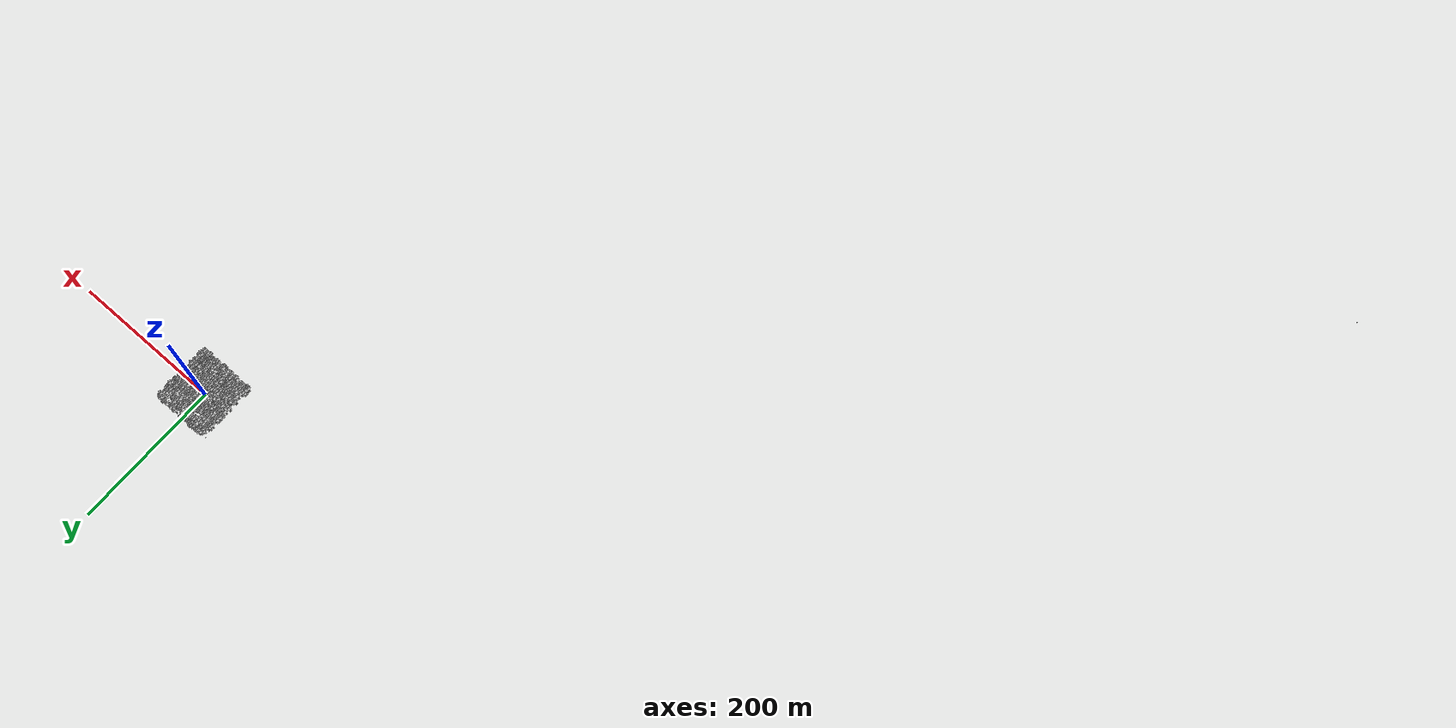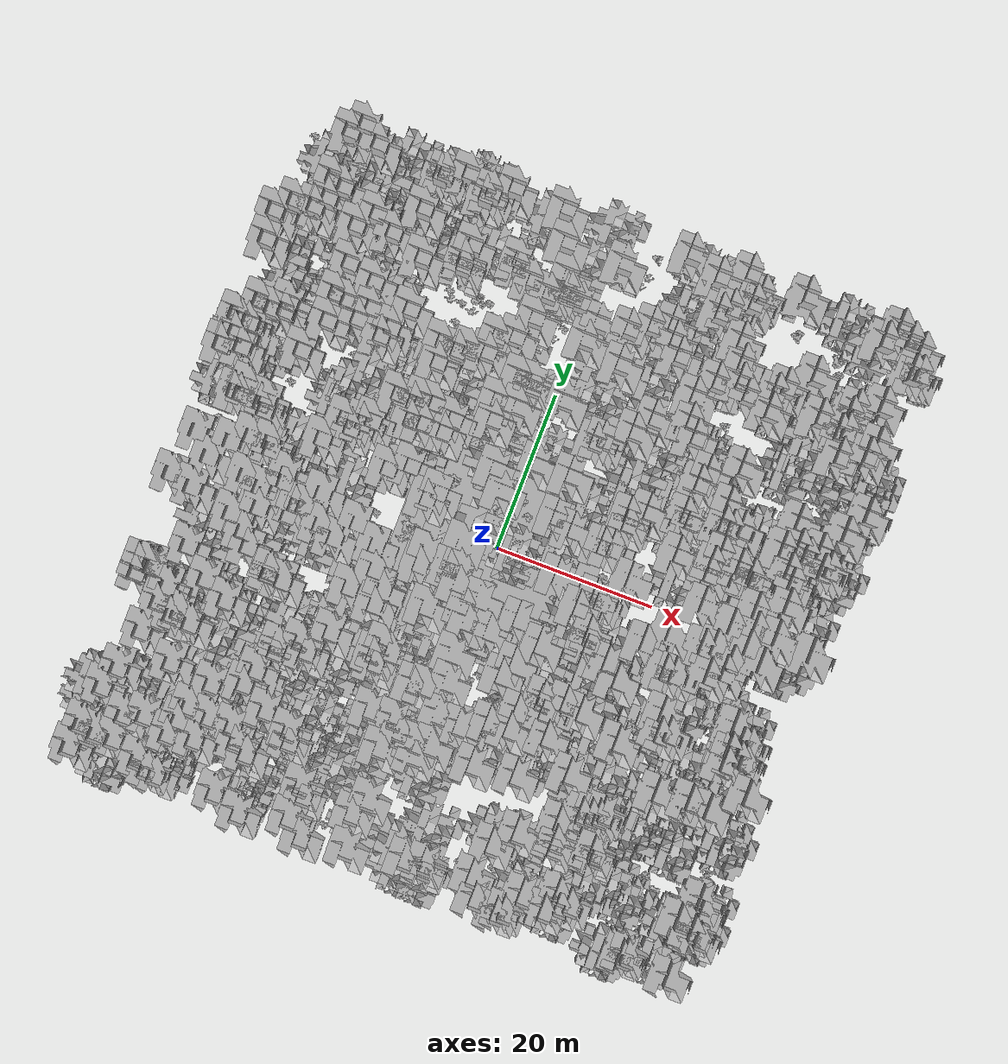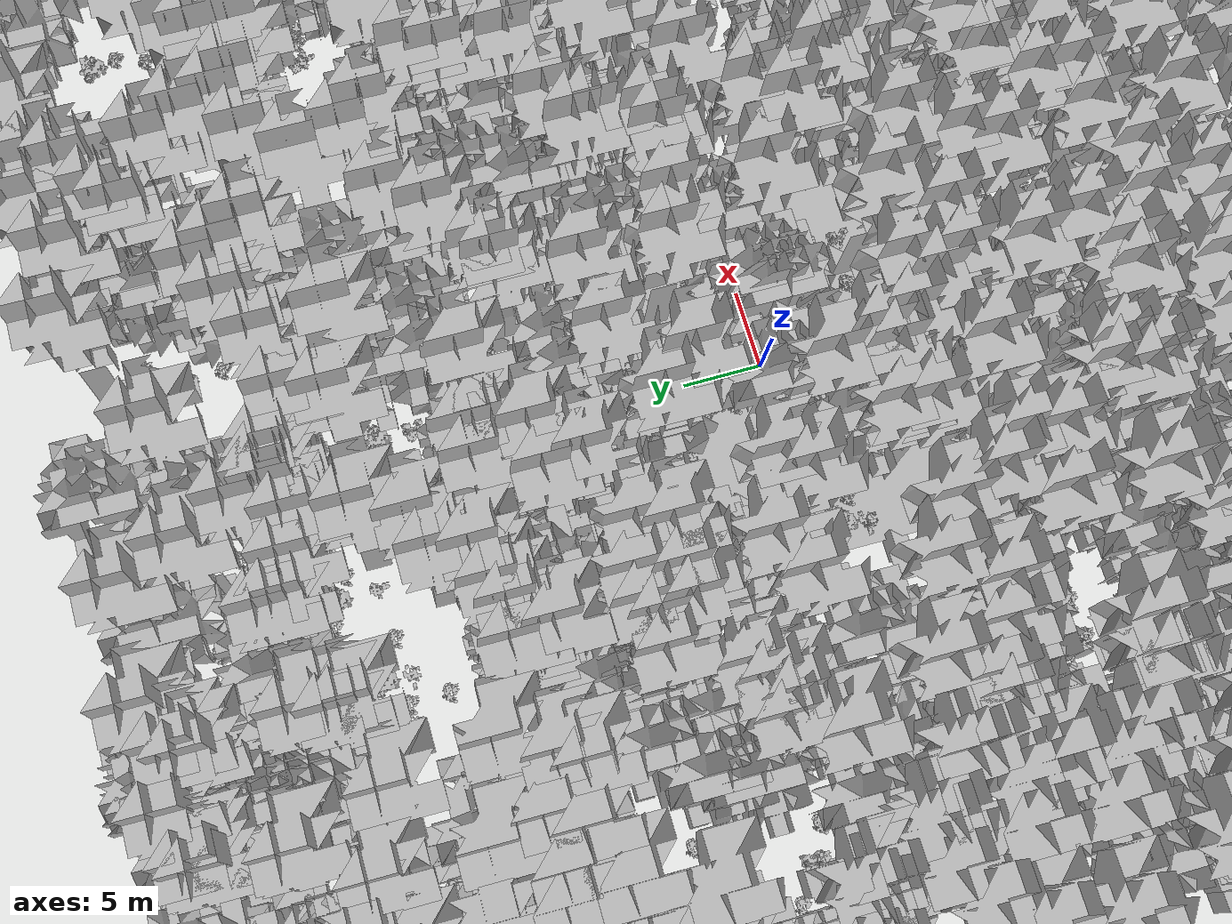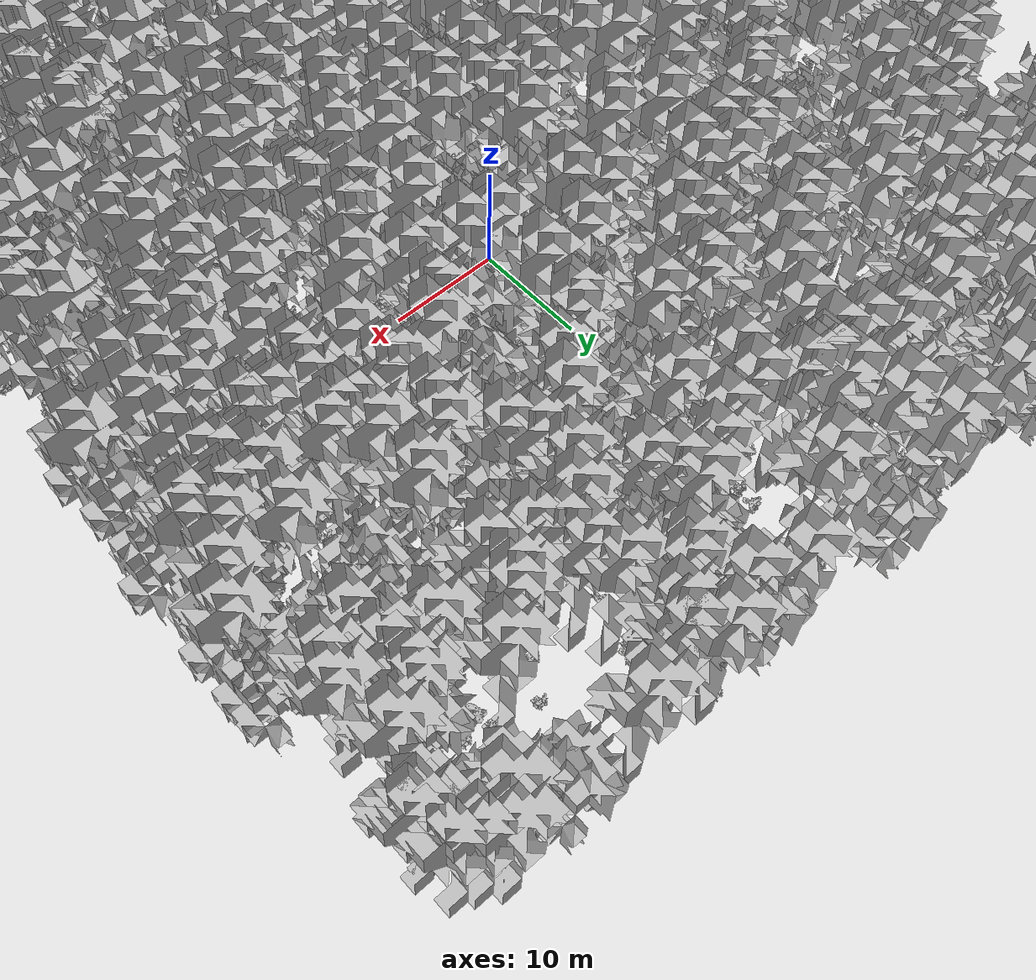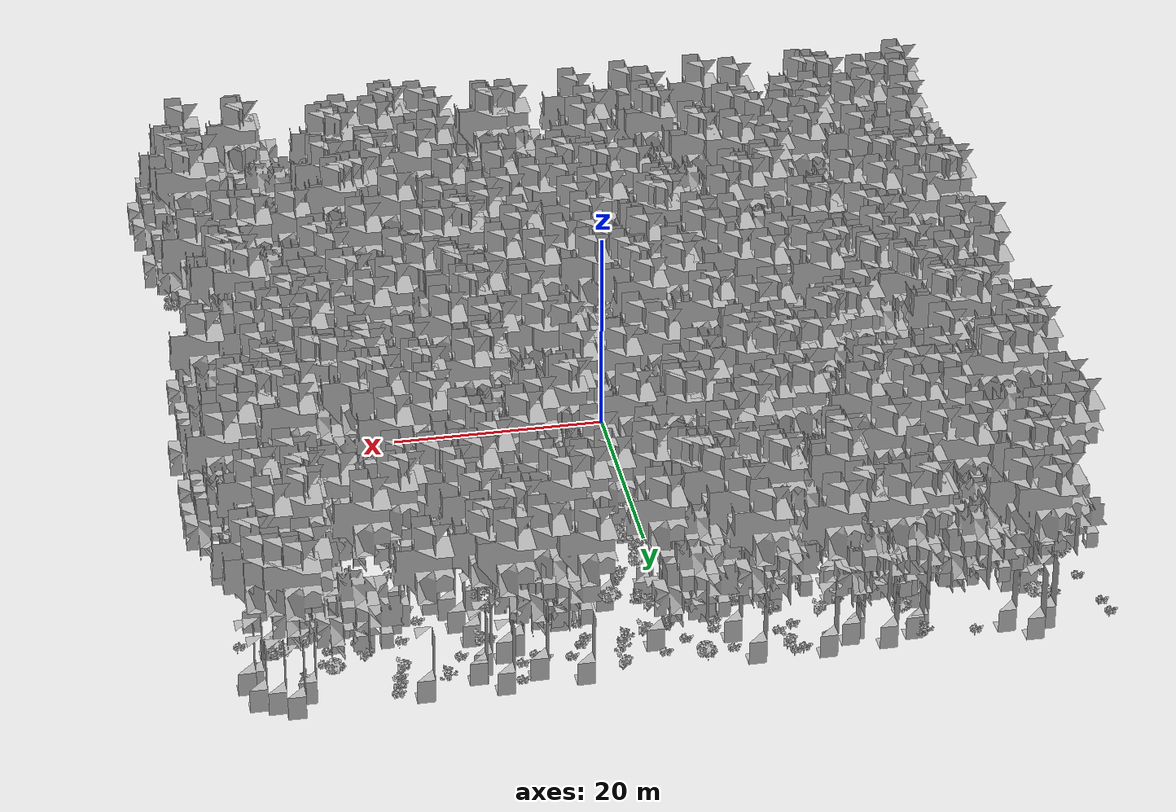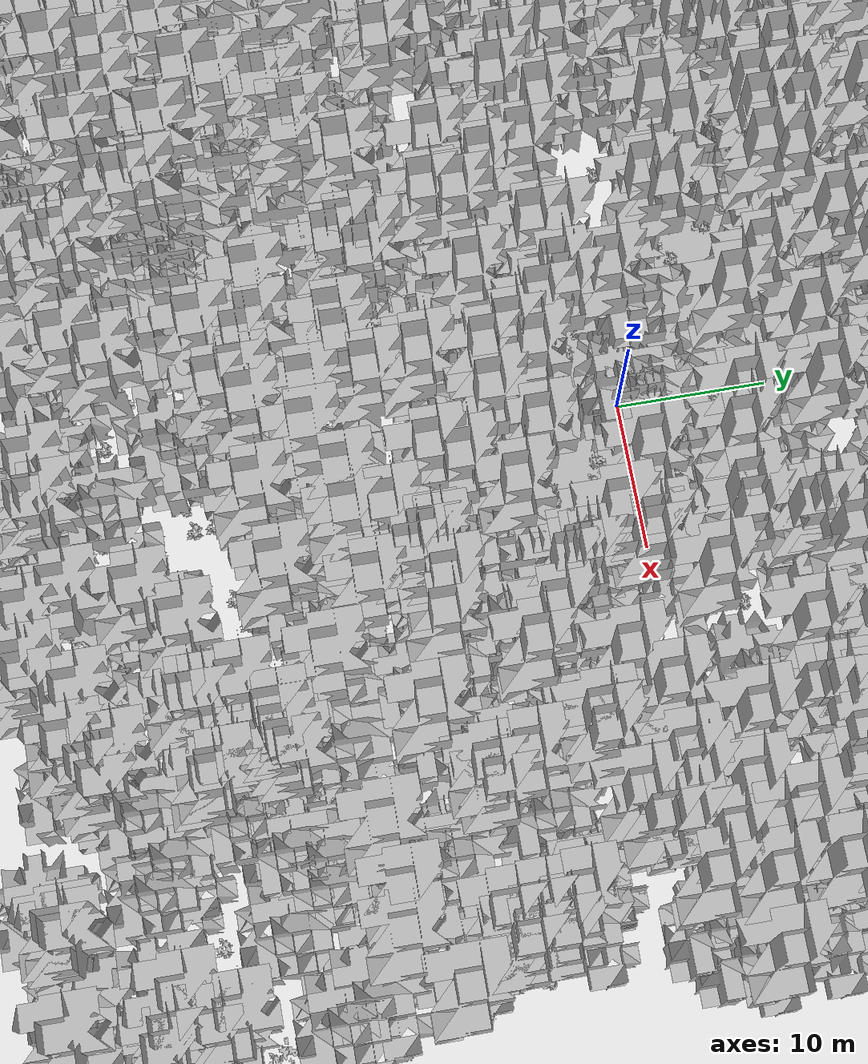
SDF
<sdf version="1.7">
    <world name="default">
        <plugin name="mrs_gazebo_static_transform_republisher_plugin" filename="libMrsGazeboCommonResources_StaticTransformRepublisher.so"/>
        <spherical_coordinates>
            <surface_model>EARTH_WGS84</surface_model>
            <latitude_deg>47.3977</latitude_deg>
            <longitude_deg>8.54559</longitude_deg>
            <elevation>0</elevation>
            <heading_deg>0</heading_deg>
        </spherical_coordinates>
        <physics name="default_physics" default="0" type="ode">
            <ode>
                <solver>
                    <type>quick</type>
                    <iters>10</iters>
                    <sor>1.3</sor>
                    <use_dynamic_moi_rescaling>0</use_dynamic_moi_rescaling>
                </solver>
                <constraints>
                    <cfm>0</cfm>
                    <erp>0.2</erp>
                    <contact_max_correcting_vel>1000</contact_max_correcting_vel>
                    <contact_surface_layer>0.001</contact_surface_layer>
                </constraints>
            </ode>
            <max_step_size>0.004</max_step_size>
            <real_time_factor>1</real_time_factor>
            <real_time_update_rate>250</real_time_update_rate>
        </physics>
        <scene>
            <shadows>0</shadows>
            <ambient>0.4 0.4 0.4 1</ambient>
            <background>0.7 0.7 0.7 1</background>
        </scene>
        <light name="sun" type="directional">
            <pose>0 0 1000 0.4 0.2 0</pose>
            <diffuse>1 1 1 1</diffuse>
            <specular>0.6 0.6 0.6 1</specular>
            <direction>0.1 0.1 -0.9</direction>
            <attenuation>
                <range>20</range>
                <constant>0.5</constant>
                <linear>0.01</linear>
                <quadratic>0.001</quadratic>
            </attenuation>
            <cast_shadows>1</cast_shadows>
            <spot>
                <inner_angle>0</inner_angle>
                <outer_angle>0</outer_angle>
                <falloff>0</falloff>
            </spot>
        </light>
        <model name="ground_plane">
            <static>1</static>
            <link name="link">
                <collision name="collision">
                    <pose>-50 0 0 0 -0 0</pose>
                    <geometry>
                        <plane>
                            <normal>0 0 1</normal>
                            <size>80 80</size>
                        </plane>
                    </geometry>
                    <surface>
                        <contact>
                            <ode>
                                <min_depth>0.01</min_depth>
                                <max_vel>0</max_vel>
                            </ode>
                        </contact>
                        <friction>
                            <ode/>
                            <torsional>
                                <ode/>
                            </torsional>
                        </friction>
                        <bounce/>
                    </surface>
                    <max_contacts>10</max_contacts>
                </collision>
                <visual name="grass">
                    <pose>0 0 0 0 -0 0</pose>
                    <cast_shadows>0</cast_shadows>
                    <geometry>
                        <mesh>
                            <scale>0.46714285714285714 0.46714285714285714 0.1</scale>
                            <uri>file://grass_plane/meshes/grass_plane.dae</uri>
                        </mesh>
                    </geometry>
                </visual>
                <self_collide>0</self_collide>
                <enable_wind>0</enable_wind>
                <kinematic>0</kinematic>
            </link>
        </model>
        <model name="the_void">
            <static>1</static>
            <link name="link">
                <pose>0 0 0.1 0 -0 0</pose>
                <visual name="the_void">
                    <pose>0 0 2 0 -0 0</pose>
                    <geometry>
                        <sphere>
                            <radius>0.25</radius>
                        </sphere>
                    </geometry>
                    <material>
                        <script>
                            <uri>file://media/materials/scripts/Gazebo.material</uri>
                            <name>Gazebo/Black</name>
                        </script>
                    </material>
                </visual>
                <self_collide>0</self_collide>
                <enable_wind>0</enable_wind>
                <kinematic>0</kinematic>
            </link>
            <pose>-1000 -1000 0 0 -0 0</pose>
        </model>
        <gui fullscreen="0">
            <camera name="camera">
                <pose>35.1577 98.6044 40.0204 0 0.407996 -1.99761</pose>
                <view_controller>orbit</view_controller>
                <projection_type>perspective</projection_type>
            </camera>
        </gui>
        <plugin name="mrs_gazebo_rviz_cam_synchronizer" filename="libMrsGazeboCommonResources_RvizCameraSynchronizer.so">
            <target_frame_id>gazebo_user_camera</target_frame_id>
            <world_origin_frame_id>uav1/gps_origin</world_origin_frame_id>
            <frame_to_follow>uav1</frame_to_follow>
        </plugin>
        <gravity>0 0 -9.8066</gravity>
        <magnetic_field>6e-06 2.3e-05 -4.2e-05</magnetic_field>
        <atmosphere type="adiabatic"/>
        <wind/>
        <model name="Tree 0">
            <static>1</static>
            <pose>-30.194991499181604 -16.02617432502095 0 1.57079 -0 0</pose>
            <link name="link">
                <pose>0 0 0 0 -0 0</pose>
                <collision name="collision">
                    <geometry>
                        <mesh>
                            <scale>3.5 5 3.5</scale>
                            <uri>model://tree_2/meshes/tree_2.obj</uri>
                        </mesh>
                    </geometry>
                    <max_contacts>10</max_contacts>
                    <surface>
                        <contact>
                            <ode/>
                        </contact>
                        <bounce/>
                        <friction>
                            <torsional>
                                <ode/>
                            </torsional>
                            <ode/>
                        </friction>
                    </surface>
                </collision>
                <visual name="visual">
                    <geometry>
                        <mesh>
                            <scale>3.5 5 3.5</scale>
                            <uri>model://tree_2/meshes/tree_2.obj</uri>
                        </mesh>
                    </geometry>
                </visual>
                <self_collide>0</self_collide>
                <enable_wind>0</enable_wind>
                <kinematic>0</kinematic>
            </link>
        </model>
        <model name="Tree 1">
            <static>1</static>
            <pose>-15.093527077515418 4.062446244424052 0 1.57079 -0 0</pose>
            <link name="link">
                <pose>0 0 0 0 -0 0</pose>
                <collision name="collision">
                    <geometry>
                        <mesh>
                            <scale>3.5 5 3.5</scale>
                            <uri>model://tree_9/meshes/tree_9.obj</uri>
                        </mesh>
                    </geometry>
                    <max_contacts>10</max_contacts>
                    <surface>
                        <contact>
                            <ode/>
                        </contact>
                        <bounce/>
                        <friction>
                            <torsional>
                                <ode/>
                            </torsional>
                            <ode/>
                        </friction>
                    </surface>
                </collision>
                <visual name="visual">
                    <geometry>
                        <mesh>
                            <scale>3.5 5 3.5</scale>
                            <uri>model://tree_9/meshes/tree_9.obj</uri>
                        </mesh>
                    </geometry>
                </visual>
                <self_collide>0</self_collide>
                <enable_wind>0</enable_wind>
                <kinematic>0</kinematic>
            </link>
        </model>
        <model name="Tree 2">
            <static>1</static>
            <pose>-6.528804799258772 39.098375685667435 0 1.57079 -0 0</pose>
            <link name="link">
                <pose>0 0 0 0 -0 0</pose>
                <collision name="collision">
                    <geometry>
                        <mesh>
                            <scale>3.5 5 3.5</scale>
                            <uri>model://tree_9/meshes/tree_9.obj</uri>
                        </mesh>
                    </geometry>
                    <max_contacts>10</max_contacts>
                    <surface>
                        <contact>
                            <ode/>
                        </contact>
                        <bounce/>
                        <friction>
                            <torsional>
                                <ode/>
                            </torsional>
                            <ode/>
                        </friction>
                    </surface>
                </collision>
                <visual name="visual">
                    <geometry>
                        <mesh>
                            <scale>3.5 5 3.5</scale>
                            <uri>model://tree_9/meshes/tree_9.obj</uri>
                        </mesh>
                    </geometry>
                </visual>
                <self_collide>0</self_collide>
                <enable_wind>0</enable_wind>
                <kinematic>0</kinematic>
            </link>
        </model>
        <model name="Tree 3">
            <static>1</static>
            <pose>33.07853094448184 8.361602892526335 0 1.57079 -0 0</pose>
            <link name="link">
                <pose>0 0 0 0 -0 0</pose>
                <collision name="collision">
                    <geometry>
                        <mesh>
                            <scale>3.5 5 3.5</scale>
                            <uri>model://tree_9/meshes/tree_9.obj</uri>
                        </mesh>
                    </geometry>
                    <max_contacts>10</max_contacts>
                    <surface>
                        <contact>
                            <ode/>
                        </contact>
                        <bounce/>
                        <friction>
                            <torsional>
                                <ode/>
                            </torsional>
                            <ode/>
                        </friction>
                    </surface>
                </collision>
                <visual name="visual">
                    <geometry>
                        <mesh>
                            <scale>3.5 5 3.5</scale>
                            <uri>model://tree_9/meshes/tree_9.obj</uri>
                        </mesh>
                    </geometry>
                </visual>
                <self_collide>0</self_collide>
                <enable_wind>0</enable_wind>
                <kinematic>0</kinematic>
            </link>
        </model>
        <model name="Tree 4">
            <static>1</static>
            <pose>-12.037222957531068 32.64025622518838 0 1.57079 -0 0</pose>
            <link name="link">
                <pose>0 0 0 0 -0 0</pose>
                <collision name="collision">
                    <geometry>
                        <mesh>
                            <scale>3.5 5 3.5</scale>
                            <uri>model://tree_2/meshes/tree_2.obj</uri>
                        </mesh>
                    </geometry>
                    <max_contacts>10</max_contacts>
                    <surface>
                        <contact>
                            <ode/>
                        </contact>
                        <bounce/>
                        <friction>
                            <torsional>
                                <ode/>
                            </torsional>
                            <ode/>
                        </friction>
                    </surface>
                </collision>
                <visual name="visual">
                    <geometry>
                        <mesh>
                            <scale>3.5 5 3.5</scale>
                            <uri>model://tree_2/meshes/tree_2.obj</uri>
                        </mesh>
                    </geometry>
                </visual>
                <self_collide>0</self_collide>
                <enable_wind>0</enable_wind>
                <kinematic>0</kinematic>
            </link>
        </model>
        <model name="Tree 5">
            <static>1</static>
            <pose>-13.282032362530884 -4.6866800431014894 0 1.57079 -0 0</pose>
            <link name="link">
                <pose>0 0 0 0 -0 0</pose>
                <collision name="collision">
                    <geometry>
                        <mesh>
                            <scale>3.5 5 3.5</scale>
                            <uri>model://tree_9/meshes/tree_9.obj</uri>
                        </mesh>
                    </geometry>
                    <max_contacts>10</max_contacts>
                    <surface>
                        <contact>
                            <ode/>
                        </contact>
                        <bounce/>
                        <friction>
                            <torsional>
                                <ode/>
                            </torsional>
                            <ode/>
                        </friction>
                    </surface>
                </collision>
                <visual name="visual">
                    <geometry>
                        <mesh>
                            <scale>3.5 5 3.5</scale>
                            <uri>model://tree_9/meshes/tree_9.obj</uri>
                        </mesh>
                    </geometry>
                </visual>
                <self_collide>0</self_collide>
                <enable_wind>0</enable_wind>
                <kinematic>0</kinematic>
            </link>
        </model>
        <model name="Tree 6">
            <static>1</static>
            <pose>-19.302507707465043 31.940459290387196 0 1.57079 -0 0</pose>
            <link name="link">
                <pose>0 0 0 0 -0 0</pose>
                <collision name="collision">
                    <geometry>
                        <mesh>
                            <scale>3.5 5 3.5</scale>
                            <uri>model://tree_2/meshes/tree_2.obj</uri>
                        </mesh>
                    </geometry>
                    <max_contacts>10</max_contacts>
                    <surface>
                        <contact>
                            <ode/>
                        </contact>
                        <bounce/>
                        <friction>
                            <torsional>
                                <ode/>
                            </torsional>
                            <ode/>
                        </friction>
                    </surface>
                </collision>
                <visual name="visual">
                    <geometry>
                        <mesh>
                            <scale>3.5 5 3.5</scale>
                            <uri>model://tree_2/meshes/tree_2.obj</uri>
                        </mesh>
                    </geometry>
                </visual>
                <self_collide>0</self_collide>
                <enable_wind>0</enable_wind>
                <kinematic>0</kinematic>
            </link>
        </model>
        <model name="Tree 7">
            <static>1</static>
            <pose>14.9944397645475 24.28028591137172 0 1.57079 -0 0</pose>
            <link name="link">
                <pose>0 0 0 0 -0 0</pose>
                <collision name="collision">
                    <geometry>
                        <mesh>
                            <scale>3.5 5 3.5</scale>
                            <uri>model://tree_9/meshes/tree_9.obj</uri>
                        </mesh>
                    </geometry>
                    <max_contacts>10</max_contacts>
                    <surface>
                        <contact>
                            <ode/>
                        </contact>
                        <bounce/>
                        <friction>
                            <torsional>
                                <ode/>
                            </torsional>
                            <ode/>
                        </friction>
                    </surface>
                </collision>
                <visual name="visual">
                    <geometry>
                        <mesh>
                            <scale>3.5 5 3.5</scale>
                            <uri>model://tree_9/meshes/tree_9.obj</uri>
                        </mesh>
                    </geometry>
                </visual>
                <self_collide>0</self_collide>
                <enable_wind>0</enable_wind>
                <kinematic>0</kinematic>
            </link>
        </model>
        <model name="Tree 8">
            <static>1</static>
            <pose>17.459714961687183 36.581936003049336 0 1.57079 -0 0</pose>
            <link name="link">
                <pose>0 0 0 0 -0 0</pose>
                <collision name="collision">
                    <geometry>
                        <mesh>
                            <scale>3.5 5 3.5</scale>
                            <uri>model://tree_9/meshes/tree_9.obj</uri>
                        </mesh>
                    </geometry>
                    <max_contacts>10</max_contacts>
                    <surface>
                        <contact>
                            <ode/>
                        </contact>
                        <bounce/>
                        <friction>
                            <torsional>
                                <ode/>
                            </torsional>
                            <ode/>
                        </friction>
                    </surface>
                </collision>
                <visual name="visual">
                    <geometry>
                        <mesh>
                            <scale>3.5 5 3.5</scale>
                            <uri>model://tree_9/meshes/tree_9.obj</uri>
                        </mesh>
                    </geometry>
                </visual>
                <self_collide>0</self_collide>
                <enable_wind>0</enable_wind>
                <kinematic>0</kinematic>
            </link>
        </model>
        <model name="Tree 9">
            <static>1</static>
            <pose>-21.693524342783427 -24.979738271324365 0 1.57079 -0 0</pose>
            <link name="link">
                <pose>0 0 0 0 -0 0</pose>
                <collision name="collision">
                    <geometry>
                        <mesh>
                            <scale>3.5 5 3.5</scale>
                            <uri>model://tree_9/meshes/tree_9.obj</uri>
                        </mesh>
                    </geometry>
                    <max_contacts>10</max_contacts>
                    <surface>
                        <contact>
                            <ode/>
                        </contact>
                        <bounce/>
                        <friction>
                            <torsional>
                                <ode/>
                            </torsional>
                            <ode/>
                        </friction>
                    </surface>
                </collision>
                <visual name="visual">
                    <geometry>
                        <mesh>
                            <scale>3.5 5 3.5</scale>
                            <uri>model://tree_9/meshes/tree_9.obj</uri>
                        </mesh>
                    </geometry>
                </visual>
                <self_collide>0</self_collide>
                <enable_wind>0</enable_wind>
                <kinematic>0</kinematic>
            </link>
        </model>
        <model name="Tree 10">
            <static>1</static>
            <pose>-33.91980547826708 -39.92610484440482 0 1.57079 -0 0</pose>
            <link name="link">
                <pose>0 0 0 0 -0 0</pose>
                <collision name="collision">
                    <geometry>
                        <mesh>
                            <scale>3.5 5 3.5</scale>
                            <uri>model://tree_2/meshes/tree_2.obj</uri>
                        </mesh>
                    </geometry>
                    <max_contacts>10</max_contacts>
                    <surface>
                        <contact>
                            <ode/>
                        </contact>
                        <bounce/>
                        <friction>
                            <torsional>
                                <ode/>
                            </torsional>
                            <ode/>
                        </friction>
                    </surface>
                </collision>
                <visual name="visual">
                    <geometry>
                        <mesh>
                            <scale>3.5 5 3.5</scale>
                            <uri>model://tree_2/meshes/tree_2.obj</uri>
                        </mesh>
                    </geometry>
                </visual>
                <self_collide>0</self_collide>
                <enable_wind>0</enable_wind>
                <kinematic>0</kinematic>
            </link>
        </model>
        <model name="Tree 11">
            <static>1</static>
            <pose>23.777491336136784 6.949107803465331 0 1.57079 -0 0</pose>
            <link name="link">
                <pose>0 0 0 0 -0 0</pose>
                <collision name="collision">
                    <geometry>
                        <mesh>
                            <scale>3.5 5 3.5</scale>
                            <uri>model://tree_9/meshes/tree_9.obj</uri>
                        </mesh>
                    </geometry>
                    <max_contacts>10</max_contacts>
                    <surface>
                        <contact>
                            <ode/>
                        </contact>
                        <bounce/>
                        <friction>
                            <torsional>
                                <ode/>
                            </torsional>
                            <ode/>
                        </friction>
                    </surface>
                </collision>
                <visual name="visual">
                    <geometry>
                        <mesh>
                            <scale>3.5 5 3.5</scale>
                            <uri>model://tree_9/meshes/tree_9.obj</uri>
                        </mesh>
                    </geometry>
                </visual>
                <self_collide>0</self_collide>
                <enable_wind>0</enable_wind>
                <kinematic>0</kinematic>
            </link>
        </model>
        <model name="Tree 12">
            <static>1</static>
            <pose>8.891146206404827 -16.811591031683307 0 1.57079 -0 0</pose>
            <link name="link">
                <pose>0 0 0 0 -0 0</pose>
                <collision name="collision">
                    <geometry>
                        <mesh>
                            <scale>3.5 5 3.5</scale>
                            <uri>model://tree_9/meshes/tree_9.obj</uri>
                        </mesh>
                    </geometry>
                    <max_contacts>10</max_contacts>
                    <surface>
                        <contact>
                            <ode/>
                        </contact>
                        <bounce/>
                        <friction>
                            <torsional>
                                <ode/>
                            </torsional>
                            <ode/>
                        </friction>
                    </surface>
                </collision>
                <visual name="visual">
                    <geometry>
                        <mesh>
                            <scale>3.5 5 3.5</scale>
                            <uri>model://tree_9/meshes/tree_9.obj</uri>
                        </mesh>
                    </geometry>
                </visual>
                <self_collide>0</self_collide>
                <enable_wind>0</enable_wind>
                <kinematic>0</kinematic>
            </link>
        </model>
        <model name="Tree 13">
            <static>1</static>
            <pose>11.686338561412157 27.977618921284602 0 1.57079 -0 0</pose>
            <link name="link">
                <pose>0 0 0 0 -0 0</pose>
                <collision name="collision">
                    <geometry>
                        <mesh>
                            <scale>3.5 5 3.5</scale>
                            <uri>model://tree_9/meshes/tree_9.obj</uri>
                        </mesh>
                    </geometry>
                    <max_contacts>10</max_contacts>
                    <surface>
                        <contact>
                            <ode/>
                        </contact>
                        <bounce/>
                        <friction>
                            <torsional>
                                <ode/>
                            </torsional>
                            <ode/>
                        </friction>
                    </surface>
                </collision>
                <visual name="visual">
                    <geometry>
                        <mesh>
                            <scale>3.5 5 3.5</scale>
                            <uri>model://tree_9/meshes/tree_9.obj</uri>
                        </mesh>
                    </geometry>
                </visual>
                <self_collide>0</self_collide>
                <enable_wind>0</enable_wind>
                <kinematic>0</kinematic>
            </link>
        </model>
        <model name="Tree 14">
            <static>1</static>
            <pose>37.12071062400305 -16.538050935977992 0 1.57079 -0 0</pose>
            <link name="link">
                <pose>0 0 0 0 -0 0</pose>
                <collision name="collision">
                    <geometry>
                        <mesh>
                            <scale>3.5 5 3.5</scale>
                            <uri>model://tree_9/meshes/tree_9.obj</uri>
                        </mesh>
                    </geometry>
                    <max_contacts>10</max_contacts>
                    <surface>
                        <contact>
                            <ode/>
                        </contact>
                        <bounce/>
                        <friction>
                            <torsional>
                                <ode/>
                            </torsional>
                            <ode/>
                        </friction>
                    </surface>
                </collision>
                <visual name="visual">
                    <geometry>
                        <mesh>
                            <scale>3.5 5 3.5</scale>
                            <uri>model://tree_9/meshes/tree_9.obj</uri>
                        </mesh>
                    </geometry>
                </visual>
                <self_collide>0</self_collide>
                <enable_wind>0</enable_wind>
                <kinematic>0</kinematic>
            </link>
        </model>
        <model name="Tree 15">
            <static>1</static>
            <pose>-37.20618540738425 13.720234120923521 0 1.57079 -0 0</pose>
            <link name="link">
                <pose>0 0 0 0 -0 0</pose>
                <collision name="collision">
                    <geometry>
                        <mesh>
                            <scale>3.5 5 3.5</scale>
                            <uri>model://tree_2/meshes/tree_2.obj</uri>
                        </mesh>
                    </geometry>
                    <max_contacts>10</max_contacts>
                    <surface>
                        <contact>
                            <ode/>
                        </contact>
                        <bounce/>
                        <friction>
                            <torsional>
                                <ode/>
                            </torsional>
                            <ode/>
                        </friction>
                    </surface>
                </collision>
                <visual name="visual">
                    <geometry>
                        <mesh>
                            <scale>3.5 5 3.5</scale>
                            <uri>model://tree_2/meshes/tree_2.obj</uri>
                        </mesh>
                    </geometry>
                </visual>
                <self_collide>0</self_collide>
                <enable_wind>0</enable_wind>
                <kinematic>0</kinematic>
            </link>
        </model>
        <model name="Tree 16">
            <static>1</static>
            <pose>0.8914246521429305 -10.282438653828034 0 1.57079 -0 0</pose>
            <link name="link">
                <pose>0 0 0 0 -0 0</pose>
                <collision name="collision">
                    <geometry>
                        <mesh>
                            <scale>3.5 5 3.5</scale>
                            <uri>model://tree_2/meshes/tree_2.obj</uri>
                        </mesh>
                    </geometry>
                    <max_contacts>10</max_contacts>
                    <surface>
                        <contact>
                            <ode/>
                        </contact>
                        <bounce/>
                        <friction>
                            <torsional>
                                <ode/>
                            </torsional>
                            <ode/>
                        </friction>
                    </surface>
                </collision>
                <visual name="visual">
                    <geometry>
                        <mesh>
                            <scale>3.5 5 3.5</scale>
                            <uri>model://tree_2/meshes/tree_2.obj</uri>
                        </mesh>
                    </geometry>
                </visual>
                <self_collide>0</self_collide>
                <enable_wind>0</enable_wind>
                <kinematic>0</kinematic>
            </link>
        </model>
        <model name="Tree 17">
            <static>1</static>
            <pose>7.408756855892989 4.94468895992226 0 1.57079 -0 0</pose>
            <link name="link">
                <pose>0 0 0 0 -0 0</pose>
                <collision name="collision">
                    <geometry>
                        <mesh>
                            <scale>3.5 5 3.5</scale>
                            <uri>model://tree_9/meshes/tree_9.obj</uri>
                        </mesh>
                    </geometry>
                    <max_contacts>10</max_contacts>
                    <surface>
                        <contact>
                            <ode/>
                        </contact>
                        <bounce/>
                        <friction>
                            <torsional>
                                <ode/>
                            </torsional>
                            <ode/>
                        </friction>
                    </surface>
                </collision>
                <visual name="visual">
                    <geometry>
                        <mesh>
                            <scale>3.5 5 3.5</scale>
                            <uri>model://tree_9/meshes/tree_9.obj</uri>
                        </mesh>
                    </geometry>
                </visual>
                <self_collide>0</self_collide>
                <enable_wind>0</enable_wind>
                <kinematic>0</kinematic>
            </link>
        </model>
        <model name="Tree 18">
            <static>1</static>
            <pose>-12.724855560985617 8.397438927089532 0 1.57079 -0 0</pose>
            <link name="link">
                <pose>0 0 0 0 -0 0</pose>
                <collision name="collision">
                    <geometry>
                        <mesh>
                            <scale>3.5 5 3.5</scale>
                            <uri>model://tree_2/meshes/tree_2.obj</uri>
                        </mesh>
                    </geometry>
                    <max_contacts>10</max_contacts>
                    <surface>
                        <contact>
                            <ode/>
                        </contact>
                        <bounce/>
                        <friction>
                            <torsional>
                                <ode/>
                            </torsional>
                            <ode/>
                        </friction>
                    </surface>
                </collision>
                <visual name="visual">
                    <geometry>
                        <mesh>
                            <scale>3.5 5 3.5</scale>
                            <uri>model://tree_2/meshes/tree_2.obj</uri>
                        </mesh>
                    </geometry>
                </visual>
                <self_collide>0</self_collide>
                <enable_wind>0</enable_wind>
                <kinematic>0</kinematic>
            </link>
        </model>
        <model name="Tree 19">
            <static>1</static>
            <pose>-14.114522778896188 17.469039290054972 0 1.57079 -0 0</pose>
            <link name="link">
                <pose>0 0 0 0 -0 0</pose>
                <collision name="collision">
                    <geometry>
                        <mesh>
                            <scale>3.5 5 3.5</scale>
                            <uri>model://tree_9/meshes/tree_9.obj</uri>
                        </mesh>
                    </geometry>
                    <max_contacts>10</max_contacts>
                    <surface>
                        <contact>
                            <ode/>
                        </contact>
                        <bounce/>
                        <friction>
                            <torsional>
                                <ode/>
                            </torsional>
                            <ode/>
                        </friction>
                    </surface>
                </collision>
                <visual name="visual">
                    <geometry>
                        <mesh>
                            <scale>3.5 5 3.5</scale>
                            <uri>model://tree_9/meshes/tree_9.obj</uri>
                        </mesh>
                    </geometry>
                </visual>
                <self_collide>0</self_collide>
                <enable_wind>0</enable_wind>
                <kinematic>0</kinematic>
            </link>
        </model>
        <model name="Tree 20">
            <static>1</static>
            <pose>-2.9140381651312026 19.249831342052637 0 1.57079 -0 0</pose>
            <link name="link">
                <pose>0 0 0 0 -0 0</pose>
                <collision name="collision">
                    <geometry>
                        <mesh>
                            <scale>3.5 5 3.5</scale>
                            <uri>model://tree_9/meshes/tree_9.obj</uri>
                        </mesh>
                    </geometry>
                    <max_contacts>10</max_contacts>
                    <surface>
                        <contact>
                            <ode/>
                        </contact>
                        <bounce/>
                        <friction>
                            <torsional>
                                <ode/>
                            </torsional>
                            <ode/>
                        </friction>
                    </surface>
                </collision>
                <visual name="visual">
                    <geometry>
                        <mesh>
                            <scale>3.5 5 3.5</scale>
                            <uri>model://tree_9/meshes/tree_9.obj</uri>
                        </mesh>
                    </geometry>
                </visual>
                <self_collide>0</self_collide>
                <enable_wind>0</enable_wind>
                <kinematic>0</kinematic>
            </link>
        </model>
        <model name="Tree 21">
            <static>1</static>
            <pose>-18.73084294914996 8.566120374249742 0 1.57079 -0 0</pose>
            <link name="link">
                <pose>0 0 0 0 -0 0</pose>
                <collision name="collision">
                    <geometry>
                        <mesh>
                            <scale>3.5 5 3.5</scale>
                            <uri>model://tree_9/meshes/tree_9.obj</uri>
                        </mesh>
                    </geometry>
                    <max_contacts>10</max_contacts>
                    <surface>
                        <contact>
                            <ode/>
                        </contact>
                        <bounce/>
                        <friction>
                            <torsional>
                                <ode/>
                            </torsional>
                            <ode/>
                        </friction>
                    </surface>
                </collision>
                <visual name="visual">
                    <geometry>
                        <mesh>
                            <scale>3.5 5 3.5</scale>
                            <uri>model://tree_9/meshes/tree_9.obj</uri>
                        </mesh>
                    </geometry>
                </visual>
                <self_collide>0</self_collide>
                <enable_wind>0</enable_wind>
                <kinematic>0</kinematic>
            </link>
        </model>
        <model name="Tree 22">
            <static>1</static>
            <pose>16.91029897801893 -36.27519353075037 0 1.57079 -0 0</pose>
            <link name="link">
                <pose>0 0 0 0 -0 0</pose>
                <collision name="collision">
                    <geometry>
                        <mesh>
                            <scale>3.5 5 3.5</scale>
                            <uri>model://tree_9/meshes/tree_9.obj</uri>
                        </mesh>
                    </geometry>
                    <max_contacts>10</max_contacts>
                    <surface>
                        <contact>
                            <ode/>
                        </contact>
                        <bounce/>
                        <friction>
                            <torsional>
                                <ode/>
                            </torsional>
                            <ode/>
                        </friction>
                    </surface>
                </collision>
                <visual name="visual">
                    <geometry>
                        <mesh>
                            <scale>3.5 5 3.5</scale>
                            <uri>model://tree_9/meshes/tree_9.obj</uri>
                        </mesh>
                    </geometry>
                </visual>
                <self_collide>0</self_collide>
                <enable_wind>0</enable_wind>
                <kinematic>0</kinematic>
            </link>
        </model>
        <model name="Tree 23">
            <static>1</static>
            <pose>23.067453202404387 -13.39166998178942 0 1.57079 -0 0</pose>
            <link name="link">
                <pose>0 0 0 0 -0 0</pose>
                <collision name="collision">
                    <geometry>
                        <mesh>
                            <scale>3.5 5 3.5</scale>
                            <uri>model://tree_2/meshes/tree_2.obj</uri>
                        </mesh>
                    </geometry>
                    <max_contacts>10</max_contacts>
                    <surface>
                        <contact>
                            <ode/>
                        </contact>
                        <bounce/>
                        <friction>
                            <torsional>
                                <ode/>
                            </torsional>
                            <ode/>
                        </friction>
                    </surface>
                </collision>
                <visual name="visual">
                    <geometry>
                        <mesh>
                            <scale>3.5 5 3.5</scale>
                            <uri>model://tree_2/meshes/tree_2.obj</uri>
                        </mesh>
                    </geometry>
                </visual>
                <self_collide>0</self_collide>
                <enable_wind>0</enable_wind>
                <kinematic>0</kinematic>
            </link>
        </model>
        <model name="Tree 24">
            <static>1</static>
            <pose>13.38012592410449 15.485081361234052 0 1.57079 -0 0</pose>
            <link name="link">
                <pose>0 0 0 0 -0 0</pose>
                <collision name="collision">
                    <geometry>
                        <mesh>
                            <scale>3.5 5 3.5</scale>
                            <uri>model://tree_2/meshes/tree_2.obj</uri>
                        </mesh>
                    </geometry>
                    <max_contacts>10</max_contacts>
                    <surface>
                        <contact>
                            <ode/>
                        </contact>
                        <bounce/>
                        <friction>
                            <torsional>
                                <ode/>
                            </torsional>
                            <ode/>
                        </friction>
                    </surface>
                </collision>
                <visual name="visual">
                    <geometry>
                        <mesh>
                            <scale>3.5 5 3.5</scale>
                            <uri>model://tree_2/meshes/tree_2.obj</uri>
                        </mesh>
                    </geometry>
                </visual>
                <self_collide>0</self_collide>
                <enable_wind>0</enable_wind>
                <kinematic>0</kinematic>
            </link>
        </model>
        <model name="Tree 25">
            <static>1</static>
            <pose>29.49814966262211 -16.064405199576626 0 1.57079 -0 0</pose>
            <link name="link">
                <pose>0 0 0 0 -0 0</pose>
                <collision name="collision">
                    <geometry>
                        <mesh>
                            <scale>3.5 5 3.5</scale>
                            <uri>model://tree_2/meshes/tree_2.obj</uri>
                        </mesh>
                    </geometry>
                    <max_contacts>10</max_contacts>
                    <surface>
                        <contact>
                            <ode/>
                        </contact>
                        <bounce/>
                        <friction>
                            <torsional>
                                <ode/>
                            </torsional>
                            <ode/>
                        </friction>
                    </surface>
                </collision>
                <visual name="visual">
                    <geometry>
                        <mesh>
                            <scale>3.5 5 3.5</scale>
                            <uri>model://tree_2/meshes/tree_2.obj</uri>
                        </mesh>
                    </geometry>
                </visual>
                <self_collide>0</self_collide>
                <enable_wind>0</enable_wind>
                <kinematic>0</kinematic>
            </link>
        </model>
        <model name="Tree 26">
            <static>1</static>
            <pose>-11.443818965885779 -29.617075454050195 0 1.57079 -0 0</pose>
            <link name="link">
                <pose>0 0 0 0 -0 0</pose>
                <collision name="collision">
                    <geometry>
                        <mesh>
                            <scale>3.5 5 3.5</scale>
                            <uri>model://tree_2/meshes/tree_2.obj</uri>
                        </mesh>
                    </geometry>
                    <max_contacts>10</max_contacts>
                    <surface>
                        <contact>
                            <ode/>
                        </contact>
                        <bounce/>
                        <friction>
                            <torsional>
                                <ode/>
                            </torsional>
                            <ode/>
                        </friction>
                    </surface>
                </collision>
                <visual name="visual">
                    <geometry>
                        <mesh>
                            <scale>3.5 5 3.5</scale>
                            <uri>model://tree_2/meshes/tree_2.obj</uri>
                        </mesh>
                    </geometry>
                </visual>
                <self_collide>0</self_collide>
                <enable_wind>0</enable_wind>
                <kinematic>0</kinematic>
            </link>
        </model>
        <model name="Tree 27">
            <static>1</static>
            <pose>-21.33487562329011 17.980174078804943 0 1.57079 -0 0</pose>
            <link name="link">
                <pose>0 0 0 0 -0 0</pose>
                <collision name="collision">
                    <geometry>
                        <mesh>
                            <scale>3.5 5 3.5</scale>
                            <uri>model://tree_9/meshes/tree_9.obj</uri>
                        </mesh>
                    </geometry>
                    <max_contacts>10</max_contacts>
                    <surface>
                        <contact>
                            <ode/>
                        </contact>
                        <bounce/>
                        <friction>
                            <torsional>
                                <ode/>
                            </torsional>
                            <ode/>
                        </friction>
                    </surface>
                </collision>
                <visual name="visual">
                    <geometry>
                        <mesh>
                            <scale>3.5 5 3.5</scale>
                            <uri>model://tree_9/meshes/tree_9.obj</uri>
                        </mesh>
                    </geometry>
                </visual>
                <self_collide>0</self_collide>
                <enable_wind>0</enable_wind>
                <kinematic>0</kinematic>
            </link>
        </model>
        <model name="Tree 28">
            <static>1</static>
            <pose>30.783272138464454 11.489812814278999 0 1.57079 -0 0</pose>
            <link name="link">
                <pose>0 0 0 0 -0 0</pose>
                <collision name="collision">
                    <geometry>
                        <mesh>
                            <scale>3.5 5 3.5</scale>
                            <uri>model://tree_9/meshes/tree_9.obj</uri>
                        </mesh>
                    </geometry>
                    <max_contacts>10</max_contacts>
                    <surface>
                        <contact>
                            <ode/>
                        </contact>
                        <bounce/>
                        <friction>
                            <torsional>
                                <ode/>
                            </torsional>
                            <ode/>
                        </friction>
                    </surface>
                </collision>
                <visual name="visual">
                    <geometry>
                        <mesh>
                            <scale>3.5 5 3.5</scale>
                            <uri>model://tree_9/meshes/tree_9.obj</uri>
                        </mesh>
                    </geometry>
                </visual>
                <self_collide>0</self_collide>
                <enable_wind>0</enable_wind>
                <kinematic>0</kinematic>
            </link>
        </model>
        <model name="Tree 29">
            <static>1</static>
            <pose>26.77203034776636 -32.211569555746294 0 1.57079 -0 0</pose>
            <link name="link">
                <pose>0 0 0 0 -0 0</pose>
                <collision name="collision">
                    <geometry>
                        <mesh>
                            <scale>3.5 5 3.5</scale>
                            <uri>model://tree_2/meshes/tree_2.obj</uri>
                        </mesh>
                    </geometry>
                    <max_contacts>10</max_contacts>
                    <surface>
                        <contact>
                            <ode/>
                        </contact>
                        <bounce/>
                        <friction>
                            <torsional>
                                <ode/>
                            </torsional>
                            <ode/>
                        </friction>
                    </surface>
                </collision>
                <visual name="visual">
                    <geometry>
                        <mesh>
                            <scale>3.5 5 3.5</scale>
                            <uri>model://tree_2/meshes/tree_2.obj</uri>
                        </mesh>
                    </geometry>
                </visual>
                <self_collide>0</self_collide>
                <enable_wind>0</enable_wind>
                <kinematic>0</kinematic>
            </link>
        </model>
        <model name="Tree 30">
            <static>1</static>
            <pose>38.099311631252164 35.695586968816116 0 1.57079 -0 0</pose>
            <link name="link">
                <pose>0 0 0 0 -0 0</pose>
                <collision name="collision">
                    <geometry>
                        <mesh>
                            <scale>3.5 5 3.5</scale>
                            <uri>model://tree_9/meshes/tree_9.obj</uri>
                        </mesh>
                    </geometry>
                    <max_contacts>10</max_contacts>
                    <surface>
                        <contact>
                            <ode/>
                        </contact>
                        <bounce/>
                        <friction>
                            <torsional>
                                <ode/>
                            </torsional>
                            <ode/>
                        </friction>
                    </surface>
                </collision>
                <visual name="visual">
                    <geometry>
                        <mesh>
                            <scale>3.5 5 3.5</scale>
                            <uri>model://tree_9/meshes/tree_9.obj</uri>
                        </mesh>
                    </geometry>
                </visual>
                <self_collide>0</self_collide>
                <enable_wind>0</enable_wind>
                <kinematic>0</kinematic>
            </link>
        </model>
        <model name="Tree 31">
            <static>1</static>
            <pose>32.39393690728703 12.331329005359109 0 1.57079 -0 0</pose>
            <link name="link">
                <pose>0 0 0 0 -0 0</pose>
                <collision name="collision">
                    <geometry>
                        <mesh>
                            <scale>3.5 5 3.5</scale>
                            <uri>model://tree_9/meshes/tree_9.obj</uri>
                        </mesh>
                    </geometry>
                    <max_contacts>10</max_contacts>
                    <surface>
                        <contact>
                            <ode/>
                        </contact>
                        <bounce/>
                        <friction>
                            <torsional>
                                <ode/>
                            </torsional>
                            <ode/>
                        </friction>
                    </surface>
                </collision>
                <visual name="visual">
                    <geometry>
                        <mesh>
                            <scale>3.5 5 3.5</scale>
                            <uri>model://tree_9/meshes/tree_9.obj</uri>
                        </mesh>
                    </geometry>
                </visual>
                <self_collide>0</self_collide>
                <enable_wind>0</enable_wind>
                <kinematic>0</kinematic>
            </link>
        </model>
        <model name="Tree 32">
            <static>1</static>
            <pose>-11.804930314046253 -28.51035392745039 0 1.57079 -0 0</pose>
            <link name="link">
                <pose>0 0 0 0 -0 0</pose>
                <collision name="collision">
                    <geometry>
                        <mesh>
                            <scale>3.5 5 3.5</scale>
                            <uri>model://tree_2/meshes/tree_2.obj</uri>
                        </mesh>
                    </geometry>
                    <max_contacts>10</max_contacts>
                    <surface>
                        <contact>
                            <ode/>
                        </contact>
                        <bounce/>
                        <friction>
                            <torsional>
                                <ode/>
                            </torsional>
                            <ode/>
                        </friction>
                    </surface>
                </collision>
                <visual name="visual">
                    <geometry>
                        <mesh>
                            <scale>3.5 5 3.5</scale>
                            <uri>model://tree_2/meshes/tree_2.obj</uri>
                        </mesh>
                    </geometry>
                </visual>
                <self_collide>0</self_collide>
                <enable_wind>0</enable_wind>
                <kinematic>0</kinematic>
            </link>
        </model>
        <model name="Tree 33">
            <static>1</static>
            <pose>18.888336202373424 19.00891305756567 0 1.57079 -0 0</pose>
            <link name="link">
                <pose>0 0 0 0 -0 0</pose>
                <collision name="collision">
                    <geometry>
                        <mesh>
                            <scale>3.5 5 3.5</scale>
                            <uri>model://tree_2/meshes/tree_2.obj</uri>
                        </mesh>
                    </geometry>
                    <max_contacts>10</max_contacts>
                    <surface>
                        <contact>
                            <ode/>
                        </contact>
                        <bounce/>
                        <friction>
                            <torsional>
                                <ode/>
                            </torsional>
                            <ode/>
                        </friction>
                    </surface>
                </collision>
                <visual name="visual">
                    <geometry>
                        <mesh>
                            <scale>3.5 5 3.5</scale>
                            <uri>model://tree_2/meshes/tree_2.obj</uri>
                        </mesh>
                    </geometry>
                </visual>
                <self_collide>0</self_collide>
                <enable_wind>0</enable_wind>
                <kinematic>0</kinematic>
            </link>
        </model>
        <model name="Tree 34">
            <static>1</static>
            <pose>-23.471219130642837 20.72297743513481 0 1.57079 -0 0</pose>
            <link name="link">
                <pose>0 0 0 0 -0 0</pose>
                <collision name="collision">
                    <geometry>
                        <mesh>
                            <scale>3.5 5 3.5</scale>
                            <uri>model://tree_2/meshes/tree_2.obj</uri>
                        </mesh>
                    </geometry>
                    <max_contacts>10</max_contacts>
                    <surface>
                        <contact>
                            <ode/>
                        </contact>
                        <bounce/>
                        <friction>
                            <torsional>
                                <ode/>
                            </torsional>
                            <ode/>
                        </friction>
                    </surface>
                </collision>
                <visual name="visual">
                    <geometry>
                        <mesh>
                            <scale>3.5 5 3.5</scale>
                            <uri>model://tree_2/meshes/tree_2.obj</uri>
                        </mesh>
                    </geometry>
                </visual>
                <self_collide>0</self_collide>
                <enable_wind>0</enable_wind>
                <kinematic>0</kinematic>
            </link>
        </model>
        <model name="Tree 35">
            <static>1</static>
            <pose>-35.33837884634204 -5.912061178661986 0 1.57079 -0 0</pose>
            <link name="link">
                <pose>0 0 0 0 -0 0</pose>
                <collision name="collision">
                    <geometry>
                        <mesh>
                            <scale>3.5 5 3.5</scale>
                            <uri>model://tree_9/meshes/tree_9.obj</uri>
                        </mesh>
                    </geometry>
                    <max_contacts>10</max_contacts>
                    <surface>
                        <contact>
                            <ode/>
                        </contact>
                        <bounce/>
                        <friction>
                            <torsional>
                                <ode/>
                            </torsional>
                            <ode/>
                        </friction>
                    </surface>
                </collision>
                <visual name="visual">
                    <geometry>
                        <mesh>
                            <scale>3.5 5 3.5</scale>
                            <uri>model://tree_9/meshes/tree_9.obj</uri>
                        </mesh>
                    </geometry>
                </visual>
                <self_collide>0</self_collide>
                <enable_wind>0</enable_wind>
                <kinematic>0</kinematic>
            </link>
        </model>
        <model name="Tree 36">
            <static>1</static>
            <pose>37.666308855298524 -23.559179173925806 0 1.57079 -0 0</pose>
            <link name="link">
                <pose>0 0 0 0 -0 0</pose>
                <collision name="collision">
                    <geometry>
                        <mesh>
                            <scale>3.5 5 3.5</scale>
                            <uri>model://tree_2/meshes/tree_2.obj</uri>
                        </mesh>
                    </geometry>
                    <max_contacts>10</max_contacts>
                    <surface>
                        <contact>
                            <ode/>
                        </contact>
                        <bounce/>
                        <friction>
                            <torsional>
                                <ode/>
                            </torsional>
                            <ode/>
                        </friction>
                    </surface>
                </collision>
                <visual name="visual">
                    <geometry>
                        <mesh>
                            <scale>3.5 5 3.5</scale>
                            <uri>model://tree_2/meshes/tree_2.obj</uri>
                        </mesh>
                    </geometry>
                </visual>
                <self_collide>0</self_collide>
                <enable_wind>0</enable_wind>
                <kinematic>0</kinematic>
            </link>
        </model>
        <model name="Tree 37">
            <static>1</static>
            <pose>-21.049315934115256 13.598727889173652 0 1.57079 -0 0</pose>
            <link name="link">
                <pose>0 0 0 0 -0 0</pose>
                <collision name="collision">
                    <geometry>
                        <mesh>
                            <scale>3.5 5 3.5</scale>
                            <uri>model://tree_2/meshes/tree_2.obj</uri>
                        </mesh>
                    </geometry>
                    <max_contacts>10</max_contacts>
                    <surface>
                        <contact>
                            <ode/>
                        </contact>
                        <bounce/>
                        <friction>
                            <torsional>
                                <ode/>
                            </torsional>
                            <ode/>
                        </friction>
                    </surface>
                </collision>
                <visual name="visual">
                    <geometry>
                        <mesh>
                            <scale>3.5 5 3.5</scale>
                            <uri>model://tree_2/meshes/tree_2.obj</uri>
                        </mesh>
                    </geometry>
                </visual>
                <self_collide>0</self_collide>
                <enable_wind>0</enable_wind>
                <kinematic>0</kinematic>
            </link>
        </model>
        <model name="Tree 38">
            <static>1</static>
            <pose>-3.549059881941865 32.049422621800375 0 1.57079 -0 0</pose>
            <link name="link">
                <pose>0 0 0 0 -0 0</pose>
                <collision name="collision">
                    <geometry>
                        <mesh>
                            <scale>3.5 5 3.5</scale>
                            <uri>model://tree_9/meshes/tree_9.obj</uri>
                        </mesh>
                    </geometry>
                    <max_contacts>10</max_contacts>
                    <surface>
                        <contact>
                            <ode/>
                        </contact>
                        <bounce/>
                        <friction>
                            <torsional>
                                <ode/>
                            </torsional>
                            <ode/>
                        </friction>
                    </surface>
                </collision>
                <visual name="visual">
                    <geometry>
                        <mesh>
                            <scale>3.5 5 3.5</scale>
                            <uri>model://tree_9/meshes/tree_9.obj</uri>
                        </mesh>
                    </geometry>
                </visual>
                <self_collide>0</self_collide>
                <enable_wind>0</enable_wind>
                <kinematic>0</kinematic>
            </link>
        </model>
        <model name="Tree 39">
            <static>1</static>
            <pose>30.05715948808283 -38.73998368811889 0 1.57079 -0 0</pose>
            <link name="link">
                <pose>0 0 0 0 -0 0</pose>
                <collision name="collision">
                    <geometry>
                        <mesh>
                            <scale>3.5 5 3.5</scale>
                            <uri>model://tree_9/meshes/tree_9.obj</uri>
                        </mesh>
                    </geometry>
                    <max_contacts>10</max_contacts>
                    <surface>
                        <contact>
                            <ode/>
                        </contact>
                        <bounce/>
                        <friction>
                            <torsional>
                                <ode/>
                            </torsional>
                            <ode/>
                        </friction>
                    </surface>
                </collision>
                <visual name="visual">
                    <geometry>
                        <mesh>
                            <scale>3.5 5 3.5</scale>
                            <uri>model://tree_9/meshes/tree_9.obj</uri>
                        </mesh>
                    </geometry>
                </visual>
                <self_collide>0</self_collide>
                <enable_wind>0</enable_wind>
                <kinematic>0</kinematic>
            </link>
        </model>
        <model name="Tree 40">
            <static>1</static>
            <pose>18.324341914332884 -9.359571309854982 0 1.57079 -0 0</pose>
            <link name="link">
                <pose>0 0 0 0 -0 0</pose>
                <collision name="collision">
                    <geometry>
                        <mesh>
                            <scale>3.5 5 3.5</scale>
                            <uri>model://tree_9/meshes/tree_9.obj</uri>
                        </mesh>
                    </geometry>
                    <max_contacts>10</max_contacts>
                    <surface>
                        <contact>
                            <ode/>
                        </contact>
                        <bounce/>
                        <friction>
                            <torsional>
                                <ode/>
                            </torsional>
                            <ode/>
                        </friction>
                    </surface>
                </collision>
                <visual name="visual">
                    <geometry>
                        <mesh>
                            <scale>3.5 5 3.5</scale>
                            <uri>model://tree_9/meshes/tree_9.obj</uri>
                        </mesh>
                    </geometry>
                </visual>
                <self_collide>0</self_collide>
                <enable_wind>0</enable_wind>
                <kinematic>0</kinematic>
            </link>
        </model>
        <model name="Tree 41">
            <static>1</static>
            <pose>-34.03493716471832 16.4164636916083 0 1.57079 -0 0</pose>
            <link name="link">
                <pose>0 0 0 0 -0 0</pose>
                <collision name="collision">
                    <geometry>
                        <mesh>
                            <scale>3.5 5 3.5</scale>
                            <uri>model://tree_9/meshes/tree_9.obj</uri>
                        </mesh>
                    </geometry>
                    <max_contacts>10</max_contacts>
                    <surface>
                        <contact>
                            <ode/>
                        </contact>
                        <bounce/>
                        <friction>
                            <torsional>
                                <ode/>
                            </torsional>
                            <ode/>
                        </friction>
                    </surface>
                </collision>
                <visual name="visual">
                    <geometry>
                        <mesh>
                            <scale>3.5 5 3.5</scale>
                            <uri>model://tree_9/meshes/tree_9.obj</uri>
                        </mesh>
                    </geometry>
                </visual>
                <self_collide>0</self_collide>
                <enable_wind>0</enable_wind>
                <kinematic>0</kinematic>
            </link>
        </model>
        <model name="Tree 42">
            <static>1</static>
            <pose>-5.763996530955787 13.591740417631044 0 1.57079 -0 0</pose>
            <link name="link">
                <pose>0 0 0 0 -0 0</pose>
                <collision name="collision">
                    <geometry>
                        <mesh>
                            <scale>3.5 5 3.5</scale>
                            <uri>model://tree_9/meshes/tree_9.obj</uri>
                        </mesh>
                    </geometry>
                    <max_contacts>10</max_contacts>
                    <surface>
                        <contact>
                            <ode/>
                        </contact>
                        <bounce/>
                        <friction>
                            <torsional>
                                <ode/>
                            </torsional>
                            <ode/>
                        </friction>
                    </surface>
                </collision>
                <visual name="visual">
                    <geometry>
                        <mesh>
                            <scale>3.5 5 3.5</scale>
                            <uri>model://tree_9/meshes/tree_9.obj</uri>
                        </mesh>
                    </geometry>
                </visual>
                <self_collide>0</self_collide>
                <enable_wind>0</enable_wind>
                <kinematic>0</kinematic>
            </link>
        </model>
        <model name="Tree 43">
            <static>1</static>
            <pose>28.239215573967428 -23.323591105262437 0 1.57079 -0 0</pose>
            <link name="link">
                <pose>0 0 0 0 -0 0</pose>
                <collision name="collision">
                    <geometry>
                        <mesh>
                            <scale>3.5 5 3.5</scale>
                            <uri>model://tree_2/meshes/tree_2.obj</uri>
                        </mesh>
                    </geometry>
                    <max_contacts>10</max_contacts>
                    <surface>
                        <contact>
                            <ode/>
                        </contact>
                        <bounce/>
                        <friction>
                            <torsional>
                                <ode/>
                            </torsional>
                            <ode/>
                        </friction>
                    </surface>
                </collision>
                <visual name="visual">
                    <geometry>
                        <mesh>
                            <scale>3.5 5 3.5</scale>
                            <uri>model://tree_2/meshes/tree_2.obj</uri>
                        </mesh>
                    </geometry>
                </visual>
                <self_collide>0</self_collide>
                <enable_wind>0</enable_wind>
                <kinematic>0</kinematic>
            </link>
        </model>
        <model name="Tree 44">
            <static>1</static>
            <pose>29.828574070417787 -2.8630253228562736 0 1.57079 -0 0</pose>
            <link name="link">
                <pose>0 0 0 0 -0 0</pose>
                <collision name="collision">
                    <geometry>
                        <mesh>
                            <scale>3.5 5 3.5</scale>
                            <uri>model://tree_9/meshes/tree_9.obj</uri>
                        </mesh>
                    </geometry>
                    <max_contacts>10</max_contacts>
                    <surface>
                        <contact>
                            <ode/>
                        </contact>
                        <bounce/>
                        <friction>
                            <torsional>
                                <ode/>
                            </torsional>
                            <ode/>
                        </friction>
                    </surface>
                </collision>
                <visual name="visual">
                    <geometry>
                        <mesh>
                            <scale>3.5 5 3.5</scale>
                            <uri>model://tree_9/meshes/tree_9.obj</uri>
                        </mesh>
                    </geometry>
                </visual>
                <self_collide>0</self_collide>
                <enable_wind>0</enable_wind>
                <kinematic>0</kinematic>
            </link>
        </model>
        <model name="Tree 45">
            <static>1</static>
            <pose>-34.37443185334554 9.705038905894014 0 1.57079 -0 0</pose>
            <link name="link">
                <pose>0 0 0 0 -0 0</pose>
                <collision name="collision">
                    <geometry>
                        <mesh>
                            <scale>3.5 5 3.5</scale>
                            <uri>model://tree_2/meshes/tree_2.obj</uri>
                        </mesh>
                    </geometry>
                    <max_contacts>10</max_contacts>
                    <surface>
                        <contact>
                            <ode/>
                        </contact>
                        <bounce/>
                        <friction>
                            <torsional>
                                <ode/>
                            </torsional>
                            <ode/>
                        </friction>
                    </surface>
                </collision>
                <visual name="visual">
                    <geometry>
                        <mesh>
                            <scale>3.5 5 3.5</scale>
                            <uri>model://tree_2/meshes/tree_2.obj</uri>
                        </mesh>
                    </geometry>
                </visual>
                <self_collide>0</self_collide>
                <enable_wind>0</enable_wind>
                <kinematic>0</kinematic>
            </link>
        </model>
        <model name="Tree 46">
            <static>1</static>
            <pose>-30.086069855366304 -7.158116199145198 0 1.57079 -0 0</pose>
            <link name="link">
                <pose>0 0 0 0 -0 0</pose>
                <collision name="collision">
                    <geometry>
                        <mesh>
                            <scale>3.5 5 3.5</scale>
                            <uri>model://tree_9/meshes/tree_9.obj</uri>
                        </mesh>
                    </geometry>
                    <max_contacts>10</max_contacts>
                    <surface>
                        <contact>
                            <ode/>
                        </contact>
                        <bounce/>
                        <friction>
                            <torsional>
                                <ode/>
                            </torsional>
                            <ode/>
                        </friction>
                    </surface>
                </collision>
                <visual name="visual">
                    <geometry>
                        <mesh>
                            <scale>3.5 5 3.5</scale>
                            <uri>model://tree_9/meshes/tree_9.obj</uri>
                        </mesh>
                    </geometry>
                </visual>
                <self_collide>0</self_collide>
                <enable_wind>0</enable_wind>
                <kinematic>0</kinematic>
            </link>
        </model>
        <model name="Tree 47">
            <static>1</static>
            <pose>10.513963513210818 29.501446716106955 0 1.57079 -0 0</pose>
            <link name="link">
                <pose>0 0 0 0 -0 0</pose>
                <collision name="collision">
                    <geometry>
                        <mesh>
                            <scale>3.5 5 3.5</scale>
                            <uri>model://tree_9/meshes/tree_9.obj</uri>
                        </mesh>
                    </geometry>
                    <max_contacts>10</max_contacts>
                    <surface>
                        <contact>
                            <ode/>
                        </contact>
                        <bounce/>
                        <friction>
                            <torsional>
                                <ode/>
                            </torsional>
                            <ode/>
                        </friction>
                    </surface>
                </collision>
                <visual name="visual">
                    <geometry>
                        <mesh>
                            <scale>3.5 5 3.5</scale>
                            <uri>model://tree_9/meshes/tree_9.obj</uri>
                        </mesh>
                    </geometry>
                </visual>
                <self_collide>0</self_collide>
                <enable_wind>0</enable_wind>
                <kinematic>0</kinematic>
            </link>
        </model>
        <model name="Tree 48">
            <static>1</static>
            <pose>-30.00092563726883 -4.4577484962211855 0 1.57079 -0 0</pose>
            <link name="link">
                <pose>0 0 0 0 -0 0</pose>
                <collision name="collision">
                    <geometry>
                        <mesh>
                            <scale>3.5 5 3.5</scale>
                            <uri>model://tree_2/meshes/tree_2.obj</uri>
                        </mesh>
                    </geometry>
                    <max_contacts>10</max_contacts>
                    <surface>
                        <contact>
                            <ode/>
                        </contact>
                        <bounce/>
                        <friction>
                            <torsional>
                                <ode/>
                            </torsional>
                            <ode/>
                        </friction>
                    </surface>
                </collision>
                <visual name="visual">
                    <geometry>
                        <mesh>
                            <scale>3.5 5 3.5</scale>
                            <uri>model://tree_2/meshes/tree_2.obj</uri>
                        </mesh>
                    </geometry>
                </visual>
                <self_collide>0</self_collide>
                <enable_wind>0</enable_wind>
                <kinematic>0</kinematic>
            </link>
        </model>
        <model name="Tree 49">
            <static>1</static>
            <pose>-2.8289390896741438 30.313094445126282 0 1.57079 -0 0</pose>
            <link name="link">
                <pose>0 0 0 0 -0 0</pose>
                <collision name="collision">
                    <geometry>
                        <mesh>
                            <scale>3.5 5 3.5</scale>
                            <uri>model://tree_9/meshes/tree_9.obj</uri>
                        </mesh>
                    </geometry>
                    <max_contacts>10</max_contacts>
                    <surface>
                        <contact>
                            <ode/>
                        </contact>
                        <bounce/>
                        <friction>
                            <torsional>
                                <ode/>
                            </torsional>
                            <ode/>
                        </friction>
                    </surface>
                </collision>
                <visual name="visual">
                    <geometry>
                        <mesh>
                            <scale>3.5 5 3.5</scale>
                            <uri>model://tree_9/meshes/tree_9.obj</uri>
                        </mesh>
                    </geometry>
                </visual>
                <self_collide>0</self_collide>
                <enable_wind>0</enable_wind>
                <kinematic>0</kinematic>
            </link>
        </model>
        <model name="Tree 50">
            <static>1</static>
            <pose>-16.626667072718373 -22.54979244939139 0 1.57079 -0 0</pose>
            <link name="link">
                <pose>0 0 0 0 -0 0</pose>
                <collision name="collision">
                    <geometry>
                        <mesh>
                            <scale>3.5 5 3.5</scale>
                            <uri>model://tree_2/meshes/tree_2.obj</uri>
                        </mesh>
                    </geometry>
                    <max_contacts>10</max_contacts>
                    <surface>
                        <contact>
                            <ode/>
                        </contact>
                        <bounce/>
                        <friction>
                            <torsional>
                                <ode/>
                            </torsional>
                            <ode/>
                        </friction>
                    </surface>
                </collision>
                <visual name="visual">
                    <geometry>
                        <mesh>
                            <scale>3.5 5 3.5</scale>
                            <uri>model://tree_2/meshes/tree_2.obj</uri>
                        </mesh>
                    </geometry>
                </visual>
                <self_collide>0</self_collide>
                <enable_wind>0</enable_wind>
                <kinematic>0</kinematic>
            </link>
        </model>
        <model name="Tree 51">
            <static>1</static>
            <pose>-28.048666339424443 -8.59627978916042 0 1.57079 -0 0</pose>
            <link name="link">
                <pose>0 0 0 0 -0 0</pose>
                <collision name="collision">
                    <geometry>
                        <mesh>
                            <scale>3.5 5 3.5</scale>
                            <uri>model://tree_9/meshes/tree_9.obj</uri>
                        </mesh>
                    </geometry>
                    <max_contacts>10</max_contacts>
                    <surface>
                        <contact>
                            <ode/>
                        </contact>
                        <bounce/>
                        <friction>
                            <torsional>
                                <ode/>
                            </torsional>
                            <ode/>
                        </friction>
                    </surface>
                </collision>
                <visual name="visual">
                    <geometry>
                        <mesh>
                            <scale>3.5 5 3.5</scale>
                            <uri>model://tree_9/meshes/tree_9.obj</uri>
                        </mesh>
                    </geometry>
                </visual>
                <self_collide>0</self_collide>
                <enable_wind>0</enable_wind>
                <kinematic>0</kinematic>
            </link>
        </model>
        <model name="Tree 52">
            <static>1</static>
            <pose>25.038008649883963 -13.423577399458715 0 1.57079 -0 0</pose>
            <link name="link">
                <pose>0 0 0 0 -0 0</pose>
                <collision name="collision">
                    <geometry>
                        <mesh>
                            <scale>3.5 5 3.5</scale>
                            <uri>model://tree_9/meshes/tree_9.obj</uri>
                        </mesh>
                    </geometry>
                    <max_contacts>10</max_contacts>
                    <surface>
                        <contact>
                            <ode/>
                        </contact>
                        <bounce/>
                        <friction>
                            <torsional>
                                <ode/>
                            </torsional>
                            <ode/>
                        </friction>
                    </surface>
                </collision>
                <visual name="visual">
                    <geometry>
                        <mesh>
                            <scale>3.5 5 3.5</scale>
                            <uri>model://tree_9/meshes/tree_9.obj</uri>
                        </mesh>
                    </geometry>
                </visual>
                <self_collide>0</self_collide>
                <enable_wind>0</enable_wind>
                <kinematic>0</kinematic>
            </link>
        </model>
        <model name="Tree 53">
            <static>1</static>
            <pose>-7.225962872668816 30.035812013915987 0 1.57079 -0 0</pose>
            <link name="link">
                <pose>0 0 0 0 -0 0</pose>
                <collision name="collision">
                    <geometry>
                        <mesh>
                            <scale>3.5 5 3.5</scale>
                            <uri>model://tree_9/meshes/tree_9.obj</uri>
                        </mesh>
                    </geometry>
                    <max_contacts>10</max_contacts>
                    <surface>
                        <contact>
                            <ode/>
                        </contact>
                        <bounce/>
                        <friction>
                            <torsional>
                                <ode/>
                            </torsional>
                            <ode/>
                        </friction>
                    </surface>
                </collision>
                <visual name="visual">
                    <geometry>
                        <mesh>
                            <scale>3.5 5 3.5</scale>
                            <uri>model://tree_9/meshes/tree_9.obj</uri>
                        </mesh>
                    </geometry>
                </visual>
                <self_collide>0</self_collide>
                <enable_wind>0</enable_wind>
                <kinematic>0</kinematic>
            </link>
        </model>
        <model name="Tree 54">
            <static>1</static>
            <pose>34.691174662508175 2.7746149690742072 0 1.57079 -0 0</pose>
            <link name="link">
                <pose>0 0 0 0 -0 0</pose>
                <collision name="collision">
                    <geometry>
                        <mesh>
                            <scale>3.5 5 3.5</scale>
                            <uri>model://tree_2/meshes/tree_2.obj</uri>
                        </mesh>
                    </geometry>
                    <max_contacts>10</max_contacts>
                    <surface>
                        <contact>
                            <ode/>
                        </contact>
                        <bounce/>
                        <friction>
                            <torsional>
                                <ode/>
                            </torsional>
                            <ode/>
                        </friction>
                    </surface>
                </collision>
                <visual name="visual">
                    <geometry>
                        <mesh>
                            <scale>3.5 5 3.5</scale>
                            <uri>model://tree_2/meshes/tree_2.obj</uri>
                        </mesh>
                    </geometry>
                </visual>
                <self_collide>0</self_collide>
                <enable_wind>0</enable_wind>
                <kinematic>0</kinematic>
            </link>
        </model>
        <model name="Tree 55">
            <static>1</static>
            <pose>-12.463813434640823 19.486152175347662 0 1.57079 -0 0</pose>
            <link name="link">
                <pose>0 0 0 0 -0 0</pose>
                <collision name="collision">
                    <geometry>
                        <mesh>
                            <scale>3.5 5 3.5</scale>
                            <uri>model://tree_9/meshes/tree_9.obj</uri>
                        </mesh>
                    </geometry>
                    <max_contacts>10</max_contacts>
                    <surface>
                        <contact>
                            <ode/>
                        </contact>
                        <bounce/>
                        <friction>
                            <torsional>
                                <ode/>
                            </torsional>
                            <ode/>
                        </friction>
                    </surface>
                </collision>
                <visual name="visual">
                    <geometry>
                        <mesh>
                            <scale>3.5 5 3.5</scale>
                            <uri>model://tree_9/meshes/tree_9.obj</uri>
                        </mesh>
                    </geometry>
                </visual>
                <self_collide>0</self_collide>
                <enable_wind>0</enable_wind>
                <kinematic>0</kinematic>
            </link>
        </model>
        <model name="Tree 56">
            <static>1</static>
            <pose>31.009430871521758 -0.4961113321103383 0 1.57079 -0 0</pose>
            <link name="link">
                <pose>0 0 0 0 -0 0</pose>
                <collision name="collision">
                    <geometry>
                        <mesh>
                            <scale>3.5 5 3.5</scale>
                            <uri>model://tree_9/meshes/tree_9.obj</uri>
                        </mesh>
                    </geometry>
                    <max_contacts>10</max_contacts>
                    <surface>
                        <contact>
                            <ode/>
                        </contact>
                        <bounce/>
                        <friction>
                            <torsional>
                                <ode/>
                            </torsional>
                            <ode/>
                        </friction>
                    </surface>
                </collision>
                <visual name="visual">
                    <geometry>
                        <mesh>
                            <scale>3.5 5 3.5</scale>
                            <uri>model://tree_9/meshes/tree_9.obj</uri>
                        </mesh>
                    </geometry>
                </visual>
                <self_collide>0</self_collide>
                <enable_wind>0</enable_wind>
                <kinematic>0</kinematic>
            </link>
        </model>
        <model name="Tree 57">
            <static>1</static>
            <pose>15.95319873063449 39.68584789340166 0 1.57079 -0 0</pose>
            <link name="link">
                <pose>0 0 0 0 -0 0</pose>
                <collision name="collision">
                    <geometry>
                        <mesh>
                            <scale>3.5 5 3.5</scale>
                            <uri>model://tree_9/meshes/tree_9.obj</uri>
                        </mesh>
                    </geometry>
                    <max_contacts>10</max_contacts>
                    <surface>
                        <contact>
                            <ode/>
                        </contact>
                        <bounce/>
                        <friction>
                            <torsional>
                                <ode/>
                            </torsional>
                            <ode/>
                        </friction>
                    </surface>
                </collision>
                <visual name="visual">
                    <geometry>
                        <mesh>
                            <scale>3.5 5 3.5</scale>
                            <uri>model://tree_9/meshes/tree_9.obj</uri>
                        </mesh>
                    </geometry>
                </visual>
                <self_collide>0</self_collide>
                <enable_wind>0</enable_wind>
                <kinematic>0</kinematic>
            </link>
        </model>
        <model name="Tree 58">
            <static>1</static>
            <pose>15.613124075627795 1.9230962227519726 0 1.57079 -0 0</pose>
            <link name="link">
                <pose>0 0 0 0 -0 0</pose>
                <collision name="collision">
                    <geometry>
                        <mesh>
                            <scale>3.5 5 3.5</scale>
                            <uri>model://tree_9/meshes/tree_9.obj</uri>
                        </mesh>
                    </geometry>
                    <max_contacts>10</max_contacts>
                    <surface>
                        <contact>
                            <ode/>
                        </contact>
                        <bounce/>
                        <friction>
                            <torsional>
                                <ode/>
                            </torsional>
                            <ode/>
                        </friction>
                    </surface>
                </collision>
                <visual name="visual">
                    <geometry>
                        <mesh>
                            <scale>3.5 5 3.5</scale>
                            <uri>model://tree_9/meshes/tree_9.obj</uri>
                        </mesh>
                    </geometry>
                </visual>
                <self_collide>0</self_collide>
                <enable_wind>0</enable_wind>
                <kinematic>0</kinematic>
            </link>
        </model>
        <model name="Tree 59">
            <static>1</static>
            <pose>17.86667570677527 -14.28361672213514 0 1.57079 -0 0</pose>
            <link name="link">
                <pose>0 0 0 0 -0 0</pose>
                <collision name="collision">
                    <geometry>
                        <mesh>
                            <scale>3.5 5 3.5</scale>
                            <uri>model://tree_2/meshes/tree_2.obj</uri>
                        </mesh>
                    </geometry>
                    <max_contacts>10</max_contacts>
                    <surface>
                        <contact>
                            <ode/>
                        </contact>
                        <bounce/>
                        <friction>
                            <torsional>
                                <ode/>
                            </torsional>
                            <ode/>
                        </friction>
                    </surface>
                </collision>
                <visual name="visual">
                    <geometry>
                        <mesh>
                            <scale>3.5 5 3.5</scale>
                            <uri>model://tree_2/meshes/tree_2.obj</uri>
                        </mesh>
                    </geometry>
                </visual>
                <self_collide>0</self_collide>
                <enable_wind>0</enable_wind>
                <kinematic>0</kinematic>
            </link>
        </model>
        <model name="Tree 60">
            <static>1</static>
            <pose>-14.461916604771211 -29.360938955560307 0 1.57079 -0 0</pose>
            <link name="link">
                <pose>0 0 0 0 -0 0</pose>
                <collision name="collision">
                    <geometry>
                        <mesh>
                            <scale>3.5 5 3.5</scale>
                            <uri>model://tree_9/meshes/tree_9.obj</uri>
                        </mesh>
                    </geometry>
                    <max_contacts>10</max_contacts>
                    <surface>
                        <contact>
                            <ode/>
                        </contact>
                        <bounce/>
                        <friction>
                            <torsional>
                                <ode/>
                            </torsional>
                            <ode/>
                        </friction>
                    </surface>
                </collision>
                <visual name="visual">
                    <geometry>
                        <mesh>
                            <scale>3.5 5 3.5</scale>
                            <uri>model://tree_9/meshes/tree_9.obj</uri>
                        </mesh>
                    </geometry>
                </visual>
                <self_collide>0</self_collide>
                <enable_wind>0</enable_wind>
                <kinematic>0</kinematic>
            </link>
        </model>
        <model name="Tree 61">
            <static>1</static>
            <pose>19.714128663647656 6.648789212033499 0 1.57079 -0 0</pose>
            <link name="link">
                <pose>0 0 0 0 -0 0</pose>
                <collision name="collision">
                    <geometry>
                        <mesh>
                            <scale>3.5 5 3.5</scale>
                            <uri>model://tree_9/meshes/tree_9.obj</uri>
                        </mesh>
                    </geometry>
                    <max_contacts>10</max_contacts>
                    <surface>
                        <contact>
                            <ode/>
                        </contact>
                        <bounce/>
                        <friction>
                            <torsional>
                                <ode/>
                            </torsional>
                            <ode/>
                        </friction>
                    </surface>
                </collision>
                <visual name="visual">
                    <geometry>
                        <mesh>
                            <scale>3.5 5 3.5</scale>
                            <uri>model://tree_9/meshes/tree_9.obj</uri>
                        </mesh>
                    </geometry>
                </visual>
                <self_collide>0</self_collide>
                <enable_wind>0</enable_wind>
                <kinematic>0</kinematic>
            </link>
        </model>
        <model name="Tree 62">
            <static>1</static>
            <pose>-32.99888553280031 0.5247705321696898 0 1.57079 -0 0</pose>
            <link name="link">
                <pose>0 0 0 0 -0 0</pose>
                <collision name="collision">
                    <geometry>
                        <mesh>
                            <scale>3.5 5 3.5</scale>
                            <uri>model://tree_9/meshes/tree_9.obj</uri>
                        </mesh>
                    </geometry>
                    <max_contacts>10</max_contacts>
                    <surface>
                        <contact>
                            <ode/>
                        </contact>
                        <bounce/>
                        <friction>
                            <torsional>
                                <ode/>
                            </torsional>
                            <ode/>
                        </friction>
                    </surface>
                </collision>
                <visual name="visual">
                    <geometry>
                        <mesh>
                            <scale>3.5 5 3.5</scale>
                            <uri>model://tree_9/meshes/tree_9.obj</uri>
                        </mesh>
                    </geometry>
                </visual>
                <self_collide>0</self_collide>
                <enable_wind>0</enable_wind>
                <kinematic>0</kinematic>
            </link>
        </model>
        <model name="Tree 63">
            <static>1</static>
            <pose>27.386450528679518 -25.158228615375577 0 1.57079 -0 0</pose>
            <link name="link">
                <pose>0 0 0 0 -0 0</pose>
                <collision name="collision">
                    <geometry>
                        <mesh>
                            <scale>3.5 5 3.5</scale>
                            <uri>model://tree_2/meshes/tree_2.obj</uri>
                        </mesh>
                    </geometry>
                    <max_contacts>10</max_contacts>
                    <surface>
                        <contact>
                            <ode/>
                        </contact>
                        <bounce/>
                        <friction>
                            <torsional>
                                <ode/>
                            </torsional>
                            <ode/>
                        </friction>
                    </surface>
                </collision>
                <visual name="visual">
                    <geometry>
                        <mesh>
                            <scale>3.5 5 3.5</scale>
                            <uri>model://tree_2/meshes/tree_2.obj</uri>
                        </mesh>
                    </geometry>
                </visual>
                <self_collide>0</self_collide>
                <enable_wind>0</enable_wind>
                <kinematic>0</kinematic>
            </link>
        </model>
        <model name="Tree 64">
            <static>1</static>
            <pose>-21.780512733870665 7.6131162719241985 0 1.57079 -0 0</pose>
            <link name="link">
                <pose>0 0 0 0 -0 0</pose>
                <collision name="collision">
                    <geometry>
                        <mesh>
                            <scale>3.5 5 3.5</scale>
                            <uri>model://tree_9/meshes/tree_9.obj</uri>
                        </mesh>
                    </geometry>
                    <max_contacts>10</max_contacts>
                    <surface>
                        <contact>
                            <ode/>
                        </contact>
                        <bounce/>
                        <friction>
                            <torsional>
                                <ode/>
                            </torsional>
                            <ode/>
                        </friction>
                    </surface>
                </collision>
                <visual name="visual">
                    <geometry>
                        <mesh>
                            <scale>3.5 5 3.5</scale>
                            <uri>model://tree_9/meshes/tree_9.obj</uri>
                        </mesh>
                    </geometry>
                </visual>
                <self_collide>0</self_collide>
                <enable_wind>0</enable_wind>
                <kinematic>0</kinematic>
            </link>
        </model>
        <model name="Tree 65">
            <static>1</static>
            <pose>4.92162815765316 10.764913708239128 0 1.57079 -0 0</pose>
            <link name="link">
                <pose>0 0 0 0 -0 0</pose>
                <collision name="collision">
                    <geometry>
                        <mesh>
                            <scale>3.5 5 3.5</scale>
                            <uri>model://tree_9/meshes/tree_9.obj</uri>
                        </mesh>
                    </geometry>
                    <max_contacts>10</max_contacts>
                    <surface>
                        <contact>
                            <ode/>
                        </contact>
                        <bounce/>
                        <friction>
                            <torsional>
                                <ode/>
                            </torsional>
                            <ode/>
                        </friction>
                    </surface>
                </collision>
                <visual name="visual">
                    <geometry>
                        <mesh>
                            <scale>3.5 5 3.5</scale>
                            <uri>model://tree_9/meshes/tree_9.obj</uri>
                        </mesh>
                    </geometry>
                </visual>
                <self_collide>0</self_collide>
                <enable_wind>0</enable_wind>
                <kinematic>0</kinematic>
            </link>
        </model>
        <model name="Tree 66">
            <static>1</static>
            <pose>14.241792973476933 34.242874181324424 0 1.57079 -0 0</pose>
            <link name="link">
                <pose>0 0 0 0 -0 0</pose>
                <collision name="collision">
                    <geometry>
                        <mesh>
                            <scale>3.5 5 3.5</scale>
                            <uri>model://tree_9/meshes/tree_9.obj</uri>
                        </mesh>
                    </geometry>
                    <max_contacts>10</max_contacts>
                    <surface>
                        <contact>
                            <ode/>
                        </contact>
                        <bounce/>
                        <friction>
                            <torsional>
                                <ode/>
                            </torsional>
                            <ode/>
                        </friction>
                    </surface>
                </collision>
                <visual name="visual">
                    <geometry>
                        <mesh>
                            <scale>3.5 5 3.5</scale>
                            <uri>model://tree_9/meshes/tree_9.obj</uri>
                        </mesh>
                    </geometry>
                </visual>
                <self_collide>0</self_collide>
                <enable_wind>0</enable_wind>
                <kinematic>0</kinematic>
            </link>
        </model>
        <model name="Tree 67">
            <static>1</static>
            <pose>1.2123539612829575 18.521096722971123 0 1.57079 -0 0</pose>
            <link name="link">
                <pose>0 0 0 0 -0 0</pose>
                <collision name="collision">
                    <geometry>
                        <mesh>
                            <scale>3.5 5 3.5</scale>
                            <uri>model://tree_9/meshes/tree_9.obj</uri>
                        </mesh>
                    </geometry>
                    <max_contacts>10</max_contacts>
                    <surface>
                        <contact>
                            <ode/>
                        </contact>
                        <bounce/>
                        <friction>
                            <torsional>
                                <ode/>
                            </torsional>
                            <ode/>
                        </friction>
                    </surface>
                </collision>
                <visual name="visual">
                    <geometry>
                        <mesh>
                            <scale>3.5 5 3.5</scale>
                            <uri>model://tree_9/meshes/tree_9.obj</uri>
                        </mesh>
                    </geometry>
                </visual>
                <self_collide>0</self_collide>
                <enable_wind>0</enable_wind>
                <kinematic>0</kinematic>
            </link>
        </model>
        <model name="Tree 68">
            <static>1</static>
            <pose>11.339195001185281 -23.77236714566612 0 1.57079 -0 0</pose>
            <link name="link">
                <pose>0 0 0 0 -0 0</pose>
                <collision name="collision">
                    <geometry>
                        <mesh>
                            <scale>3.5 5 3.5</scale>
                            <uri>model://tree_9/meshes/tree_9.obj</uri>
                        </mesh>
                    </geometry>
                    <max_contacts>10</max_contacts>
                    <surface>
                        <contact>
                            <ode/>
                        </contact>
                        <bounce/>
                        <friction>
                            <torsional>
                                <ode/>
                            </torsional>
                            <ode/>
                        </friction>
                    </surface>
                </collision>
                <visual name="visual">
                    <geometry>
                        <mesh>
                            <scale>3.5 5 3.5</scale>
                            <uri>model://tree_9/meshes/tree_9.obj</uri>
                        </mesh>
                    </geometry>
                </visual>
                <self_collide>0</self_collide>
                <enable_wind>0</enable_wind>
                <kinematic>0</kinematic>
            </link>
        </model>
        <model name="Tree 69">
            <static>1</static>
            <pose>-1.8460160270246888 -9.322222044493262 0 1.57079 -0 0</pose>
            <link name="link">
                <pose>0 0 0 0 -0 0</pose>
                <collision name="collision">
                    <geometry>
                        <mesh>
                            <scale>3.5 5 3.5</scale>
                            <uri>model://tree_2/meshes/tree_2.obj</uri>
                        </mesh>
                    </geometry>
                    <max_contacts>10</max_contacts>
                    <surface>
                        <contact>
                            <ode/>
                        </contact>
                        <bounce/>
                        <friction>
                            <torsional>
                                <ode/>
                            </torsional>
                            <ode/>
                        </friction>
                    </surface>
                </collision>
                <visual name="visual">
                    <geometry>
                        <mesh>
                            <scale>3.5 5 3.5</scale>
                            <uri>model://tree_2/meshes/tree_2.obj</uri>
                        </mesh>
                    </geometry>
                </visual>
                <self_collide>0</self_collide>
                <enable_wind>0</enable_wind>
                <kinematic>0</kinematic>
            </link>
        </model>
        <model name="Tree 70">
            <static>1</static>
            <pose>34.25507007381796 -10.939534100445634 0 1.57079 -0 0</pose>
            <link name="link">
                <pose>0 0 0 0 -0 0</pose>
                <collision name="collision">
                    <geometry>
                        <mesh>
                            <scale>3.5 5 3.5</scale>
                            <uri>model://tree_9/meshes/tree_9.obj</uri>
                        </mesh>
                    </geometry>
                    <max_contacts>10</max_contacts>
                    <surface>
                        <contact>
                            <ode/>
                        </contact>
                        <bounce/>
                        <friction>
                            <torsional>
                                <ode/>
                            </torsional>
                            <ode/>
                        </friction>
                    </surface>
                </collision>
                <visual name="visual">
                    <geometry>
                        <mesh>
                            <scale>3.5 5 3.5</scale>
                            <uri>model://tree_9/meshes/tree_9.obj</uri>
                        </mesh>
                    </geometry>
                </visual>
                <self_collide>0</self_collide>
                <enable_wind>0</enable_wind>
                <kinematic>0</kinematic>
            </link>
        </model>
        <model name="Tree 71">
            <static>1</static>
            <pose>22.238771562481794 -15.177728897150537 0 1.57079 -0 0</pose>
            <link name="link">
                <pose>0 0 0 0 -0 0</pose>
                <collision name="collision">
                    <geometry>
                        <mesh>
                            <scale>3.5 5 3.5</scale>
                            <uri>model://tree_2/meshes/tree_2.obj</uri>
                        </mesh>
                    </geometry>
                    <max_contacts>10</max_contacts>
                    <surface>
                        <contact>
                            <ode/>
                        </contact>
                        <bounce/>
                        <friction>
                            <torsional>
                                <ode/>
                            </torsional>
                            <ode/>
                        </friction>
                    </surface>
                </collision>
                <visual name="visual">
                    <geometry>
                        <mesh>
                            <scale>3.5 5 3.5</scale>
                            <uri>model://tree_2/meshes/tree_2.obj</uri>
                        </mesh>
                    </geometry>
                </visual>
                <self_collide>0</self_collide>
                <enable_wind>0</enable_wind>
                <kinematic>0</kinematic>
            </link>
        </model>
        <model name="Tree 72">
            <static>1</static>
            <pose>33.29203087042106 -13.863999350595009 0 1.57079 -0 0</pose>
            <link name="link">
                <pose>0 0 0 0 -0 0</pose>
                <collision name="collision">
                    <geometry>
                        <mesh>
                            <scale>3.5 5 3.5</scale>
                            <uri>model://tree_9/meshes/tree_9.obj</uri>
                        </mesh>
                    </geometry>
                    <max_contacts>10</max_contacts>
                    <surface>
                        <contact>
                            <ode/>
                        </contact>
                        <bounce/>
                        <friction>
                            <torsional>
                                <ode/>
                            </torsional>
                            <ode/>
                        </friction>
                    </surface>
                </collision>
                <visual name="visual">
                    <geometry>
                        <mesh>
                            <scale>3.5 5 3.5</scale>
                            <uri>model://tree_9/meshes/tree_9.obj</uri>
                        </mesh>
                    </geometry>
                </visual>
                <self_collide>0</self_collide>
                <enable_wind>0</enable_wind>
                <kinematic>0</kinematic>
            </link>
        </model>
        <model name="Tree 73">
            <static>1</static>
            <pose>23.27902216675262 11.709637553765944 0 1.57079 -0 0</pose>
            <link name="link">
                <pose>0 0 0 0 -0 0</pose>
                <collision name="collision">
                    <geometry>
                        <mesh>
                            <scale>3.5 5 3.5</scale>
                            <uri>model://tree_9/meshes/tree_9.obj</uri>
                        </mesh>
                    </geometry>
                    <max_contacts>10</max_contacts>
                    <surface>
                        <contact>
                            <ode/>
                        </contact>
                        <bounce/>
                        <friction>
                            <torsional>
                                <ode/>
                            </torsional>
                            <ode/>
                        </friction>
                    </surface>
                </collision>
                <visual name="visual">
                    <geometry>
                        <mesh>
                            <scale>3.5 5 3.5</scale>
                            <uri>model://tree_9/meshes/tree_9.obj</uri>
                        </mesh>
                    </geometry>
                </visual>
                <self_collide>0</self_collide>
                <enable_wind>0</enable_wind>
                <kinematic>0</kinematic>
            </link>
        </model>
        <model name="Tree 74">
            <static>1</static>
            <pose>-20.229399606597568 -31.514576931610215 0 1.57079 -0 0</pose>
            <link name="link">
                <pose>0 0 0 0 -0 0</pose>
                <collision name="collision">
                    <geometry>
                        <mesh>
                            <scale>3.5 5 3.5</scale>
                            <uri>model://tree_9/meshes/tree_9.obj</uri>
                        </mesh>
                    </geometry>
                    <max_contacts>10</max_contacts>
                    <surface>
                        <contact>
                            <ode/>
                        </contact>
                        <bounce/>
                        <friction>
                            <torsional>
                                <ode/>
                            </torsional>
                            <ode/>
                        </friction>
                    </surface>
                </collision>
                <visual name="visual">
                    <geometry>
                        <mesh>
                            <scale>3.5 5 3.5</scale>
                            <uri>model://tree_9/meshes/tree_9.obj</uri>
                        </mesh>
                    </geometry>
                </visual>
                <self_collide>0</self_collide>
                <enable_wind>0</enable_wind>
                <kinematic>0</kinematic>
            </link>
        </model>
        <model name="Tree 75">
            <static>1</static>
            <pose>-7.772627824791339 -4.991182343657144 0 1.57079 -0 0</pose>
            <link name="link">
                <pose>0 0 0 0 -0 0</pose>
                <collision name="collision">
                    <geometry>
                        <mesh>
                            <scale>3.5 5 3.5</scale>
                            <uri>model://tree_9/meshes/tree_9.obj</uri>
                        </mesh>
                    </geometry>
                    <max_contacts>10</max_contacts>
                    <surface>
                        <contact>
                            <ode/>
                        </contact>
                        <bounce/>
                        <friction>
                            <torsional>
                                <ode/>
                            </torsional>
                            <ode/>
                        </friction>
                    </surface>
                </collision>
                <visual name="visual">
                    <geometry>
                        <mesh>
                            <scale>3.5 5 3.5</scale>
                            <uri>model://tree_9/meshes/tree_9.obj</uri>
                        </mesh>
                    </geometry>
                </visual>
                <self_collide>0</self_collide>
                <enable_wind>0</enable_wind>
                <kinematic>0</kinematic>
            </link>
        </model>
        <model name="Tree 76">
            <static>1</static>
            <pose>-25.634454811040225 -1.6060521768841056 0 1.57079 -0 0</pose>
            <link name="link">
                <pose>0 0 0 0 -0 0</pose>
                <collision name="collision">
                    <geometry>
                        <mesh>
                            <scale>3.5 5 3.5</scale>
                            <uri>model://tree_9/meshes/tree_9.obj</uri>
                        </mesh>
                    </geometry>
                    <max_contacts>10</max_contacts>
                    <surface>
                        <contact>
                            <ode/>
                        </contact>
                        <bounce/>
                        <friction>
                            <torsional>
                                <ode/>
                            </torsional>
                            <ode/>
                        </friction>
                    </surface>
                </collision>
                <visual name="visual">
                    <geometry>
                        <mesh>
                            <scale>3.5 5 3.5</scale>
                            <uri>model://tree_9/meshes/tree_9.obj</uri>
                        </mesh>
                    </geometry>
                </visual>
                <self_collide>0</self_collide>
                <enable_wind>0</enable_wind>
                <kinematic>0</kinematic>
            </link>
        </model>
        <model name="Tree 77">
            <static>1</static>
            <pose>27.13264223164208 31.46648215437368 0 1.57079 -0 0</pose>
            <link name="link">
                <pose>0 0 0 0 -0 0</pose>
                <collision name="collision">
                    <geometry>
                        <mesh>
                            <scale>3.5 5 3.5</scale>
                            <uri>model://tree_9/meshes/tree_9.obj</uri>
                        </mesh>
                    </geometry>
                    <max_contacts>10</max_contacts>
                    <surface>
                        <contact>
                            <ode/>
                        </contact>
                        <bounce/>
                        <friction>
                            <torsional>
                                <ode/>
                            </torsional>
                            <ode/>
                        </friction>
                    </surface>
                </collision>
                <visual name="visual">
                    <geometry>
                        <mesh>
                            <scale>3.5 5 3.5</scale>
                            <uri>model://tree_9/meshes/tree_9.obj</uri>
                        </mesh>
                    </geometry>
                </visual>
                <self_collide>0</self_collide>
                <enable_wind>0</enable_wind>
                <kinematic>0</kinematic>
            </link>
        </model>
        <model name="Tree 78">
            <static>1</static>
            <pose>-3.0233192997642107 -23.737386644191858 0 1.57079 -0 0</pose>
            <link name="link">
                <pose>0 0 0 0 -0 0</pose>
                <collision name="collision">
                    <geometry>
                        <mesh>
                            <scale>3.5 5 3.5</scale>
                            <uri>model://tree_9/meshes/tree_9.obj</uri>
                        </mesh>
                    </geometry>
                    <max_contacts>10</max_contacts>
                    <surface>
                        <contact>
                            <ode/>
                        </contact>
                        <bounce/>
                        <friction>
                            <torsional>
                                <ode/>
                            </torsional>
                            <ode/>
                        </friction>
                    </surface>
                </collision>
                <visual name="visual">
                    <geometry>
                        <mesh>
                            <scale>3.5 5 3.5</scale>
                            <uri>model://tree_9/meshes/tree_9.obj</uri>
                        </mesh>
                    </geometry>
                </visual>
                <self_collide>0</self_collide>
                <enable_wind>0</enable_wind>
                <kinematic>0</kinematic>
            </link>
        </model>
        <model name="Tree 79">
            <static>1</static>
            <pose>36.40291296193408 11.124683486578242 0 1.57079 -0 0</pose>
            <link name="link">
                <pose>0 0 0 0 -0 0</pose>
                <collision name="collision">
                    <geometry>
                        <mesh>
                            <scale>3.5 5 3.5</scale>
                            <uri>model://tree_9/meshes/tree_9.obj</uri>
                        </mesh>
                    </geometry>
                    <max_contacts>10</max_contacts>
                    <surface>
                        <contact>
                            <ode/>
                        </contact>
                        <bounce/>
                        <friction>
                            <torsional>
                                <ode/>
                            </torsional>
                            <ode/>
                        </friction>
                    </surface>
                </collision>
                <visual name="visual">
                    <geometry>
                        <mesh>
                            <scale>3.5 5 3.5</scale>
                            <uri>model://tree_9/meshes/tree_9.obj</uri>
                        </mesh>
                    </geometry>
                </visual>
                <self_collide>0</self_collide>
                <enable_wind>0</enable_wind>
                <kinematic>0</kinematic>
            </link>
        </model>
        <model name="Tree 80">
            <static>1</static>
            <pose>17.247273729239808 19.502905807618518 0 1.57079 -0 0</pose>
            <link name="link">
                <pose>0 0 0 0 -0 0</pose>
                <collision name="collision">
                    <geometry>
                        <mesh>
                            <scale>3.5 5 3.5</scale>
                            <uri>model://tree_2/meshes/tree_2.obj</uri>
                        </mesh>
                    </geometry>
                    <max_contacts>10</max_contacts>
                    <surface>
                        <contact>
                            <ode/>
                        </contact>
                        <bounce/>
                        <friction>
                            <torsional>
                                <ode/>
                            </torsional>
                            <ode/>
                        </friction>
                    </surface>
                </collision>
                <visual name="visual">
                    <geometry>
                        <mesh>
                            <scale>3.5 5 3.5</scale>
                            <uri>model://tree_2/meshes/tree_2.obj</uri>
                        </mesh>
                    </geometry>
                </visual>
                <self_collide>0</self_collide>
                <enable_wind>0</enable_wind>
                <kinematic>0</kinematic>
            </link>
        </model>
        <model name="Tree 81">
            <static>1</static>
            <pose>26.168726215982574 -2.277482786651568 0 1.57079 -0 0</pose>
            <link name="link">
                <pose>0 0 0 0 -0 0</pose>
                <collision name="collision">
                    <geometry>
                        <mesh>
                            <scale>3.5 5 3.5</scale>
                            <uri>model://tree_9/meshes/tree_9.obj</uri>
                        </mesh>
                    </geometry>
                    <max_contacts>10</max_contacts>
                    <surface>
                        <contact>
                            <ode/>
                        </contact>
                        <bounce/>
                        <friction>
                            <torsional>
                                <ode/>
                            </torsional>
                            <ode/>
                        </friction>
                    </surface>
                </collision>
                <visual name="visual">
                    <geometry>
                        <mesh>
                            <scale>3.5 5 3.5</scale>
                            <uri>model://tree_9/meshes/tree_9.obj</uri>
                        </mesh>
                    </geometry>
                </visual>
                <self_collide>0</self_collide>
                <enable_wind>0</enable_wind>
                <kinematic>0</kinematic>
            </link>
        </model>
        <model name="Tree 82">
            <static>1</static>
            <pose>0.4855155025319391 -20.365086674088076 0 1.57079 -0 0</pose>
            <link name="link">
                <pose>0 0 0 0 -0 0</pose>
                <collision name="collision">
                    <geometry>
                        <mesh>
                            <scale>3.5 5 3.5</scale>
                            <uri>model://tree_9/meshes/tree_9.obj</uri>
                        </mesh>
                    </geometry>
                    <max_contacts>10</max_contacts>
                    <surface>
                        <contact>
                            <ode/>
                        </contact>
                        <bounce/>
                        <friction>
                            <torsional>
                                <ode/>
                            </torsional>
                            <ode/>
                        </friction>
                    </surface>
                </collision>
                <visual name="visual">
                    <geometry>
                        <mesh>
                            <scale>3.5 5 3.5</scale>
                            <uri>model://tree_9/meshes/tree_9.obj</uri>
                        </mesh>
                    </geometry>
                </visual>
                <self_collide>0</self_collide>
                <enable_wind>0</enable_wind>
                <kinematic>0</kinematic>
            </link>
        </model>
        <model name="Tree 83">
            <static>1</static>
            <pose>32.19585348661583 27.203462785655944 0 1.57079 -0 0</pose>
            <link name="link">
                <pose>0 0 0 0 -0 0</pose>
                <collision name="collision">
                    <geometry>
                        <mesh>
                            <scale>3.5 5 3.5</scale>
                            <uri>model://tree_2/meshes/tree_2.obj</uri>
                        </mesh>
                    </geometry>
                    <max_contacts>10</max_contacts>
                    <surface>
                        <contact>
                            <ode/>
                        </contact>
                        <bounce/>
                        <friction>
                            <torsional>
                                <ode/>
                            </torsional>
                            <ode/>
                        </friction>
                    </surface>
                </collision>
                <visual name="visual">
                    <geometry>
                        <mesh>
                            <scale>3.5 5 3.5</scale>
                            <uri>model://tree_2/meshes/tree_2.obj</uri>
                        </mesh>
                    </geometry>
                </visual>
                <self_collide>0</self_collide>
                <enable_wind>0</enable_wind>
                <kinematic>0</kinematic>
            </link>
        </model>
        <model name="Tree 84">
            <static>1</static>
            <pose>-34.89042758604113 -23.43560407261809 0 1.57079 -0 0</pose>
            <link name="link">
                <pose>0 0 0 0 -0 0</pose>
                <collision name="collision">
                    <geometry>
                        <mesh>
                            <scale>3.5 5 3.5</scale>
                            <uri>model://tree_9/meshes/tree_9.obj</uri>
                        </mesh>
                    </geometry>
                    <max_contacts>10</max_contacts>
                    <surface>
                        <contact>
                            <ode/>
                        </contact>
                        <bounce/>
                        <friction>
                            <torsional>
                                <ode/>
                            </torsional>
                            <ode/>
                        </friction>
                    </surface>
                </collision>
                <visual name="visual">
                    <geometry>
                        <mesh>
                            <scale>3.5 5 3.5</scale>
                            <uri>model://tree_9/meshes/tree_9.obj</uri>
                        </mesh>
                    </geometry>
                </visual>
                <self_collide>0</self_collide>
                <enable_wind>0</enable_wind>
                <kinematic>0</kinematic>
            </link>
        </model>
        <model name="Tree 85">
            <static>1</static>
            <pose>-18.363122085777725 36.33316687483587 0 1.57079 -0 0</pose>
            <link name="link">
                <pose>0 0 0 0 -0 0</pose>
                <collision name="collision">
                    <geometry>
                        <mesh>
                            <scale>3.5 5 3.5</scale>
                            <uri>model://tree_2/meshes/tree_2.obj</uri>
                        </mesh>
                    </geometry>
                    <max_contacts>10</max_contacts>
                    <surface>
                        <contact>
                            <ode/>
                        </contact>
                        <bounce/>
                        <friction>
                            <torsional>
                                <ode/>
                            </torsional>
                            <ode/>
                        </friction>
                    </surface>
                </collision>
                <visual name="visual">
                    <geometry>
                        <mesh>
                            <scale>3.5 5 3.5</scale>
                            <uri>model://tree_2/meshes/tree_2.obj</uri>
                        </mesh>
                    </geometry>
                </visual>
                <self_collide>0</self_collide>
                <enable_wind>0</enable_wind>
                <kinematic>0</kinematic>
            </link>
        </model>
        <model name="Tree 86">
            <static>1</static>
            <pose>-2.5542932744407025 -12.772571305100698 0 1.57079 -0 0</pose>
            <link name="link">
                <pose>0 0 0 0 -0 0</pose>
                <collision name="collision">
                    <geometry>
                        <mesh>
                            <scale>3.5 5 3.5</scale>
                            <uri>model://tree_2/meshes/tree_2.obj</uri>
                        </mesh>
                    </geometry>
                    <max_contacts>10</max_contacts>
                    <surface>
                        <contact>
                            <ode/>
                        </contact>
                        <bounce/>
                        <friction>
                            <torsional>
                                <ode/>
                            </torsional>
                            <ode/>
                        </friction>
                    </surface>
                </collision>
                <visual name="visual">
                    <geometry>
                        <mesh>
                            <scale>3.5 5 3.5</scale>
                            <uri>model://tree_2/meshes/tree_2.obj</uri>
                        </mesh>
                    </geometry>
                </visual>
                <self_collide>0</self_collide>
                <enable_wind>0</enable_wind>
                <kinematic>0</kinematic>
            </link>
        </model>
        <model name="Tree 87">
            <static>1</static>
            <pose>-21.513346291556587 6.068187937286254 0 1.57079 -0 0</pose>
            <link name="link">
                <pose>0 0 0 0 -0 0</pose>
                <collision name="collision">
                    <geometry>
                        <mesh>
                            <scale>3.5 5 3.5</scale>
                            <uri>model://tree_2/meshes/tree_2.obj</uri>
                        </mesh>
                    </geometry>
                    <max_contacts>10</max_contacts>
                    <surface>
                        <contact>
                            <ode/>
                        </contact>
                        <bounce/>
                        <friction>
                            <torsional>
                                <ode/>
                            </torsional>
                            <ode/>
                        </friction>
                    </surface>
                </collision>
                <visual name="visual">
                    <geometry>
                        <mesh>
                            <scale>3.5 5 3.5</scale>
                            <uri>model://tree_2/meshes/tree_2.obj</uri>
                        </mesh>
                    </geometry>
                </visual>
                <self_collide>0</self_collide>
                <enable_wind>0</enable_wind>
                <kinematic>0</kinematic>
            </link>
        </model>
        <model name="Tree 88">
            <static>1</static>
            <pose>2.5734462924223536 -9.33611392234102 0 1.57079 -0 0</pose>
            <link name="link">
                <pose>0 0 0 0 -0 0</pose>
                <collision name="collision">
                    <geometry>
                        <mesh>
                            <scale>3.5 5 3.5</scale>
                            <uri>model://tree_9/meshes/tree_9.obj</uri>
                        </mesh>
                    </geometry>
                    <max_contacts>10</max_contacts>
                    <surface>
                        <contact>
                            <ode/>
                        </contact>
                        <bounce/>
                        <friction>
                            <torsional>
                                <ode/>
                            </torsional>
                            <ode/>
                        </friction>
                    </surface>
                </collision>
                <visual name="visual">
                    <geometry>
                        <mesh>
                            <scale>3.5 5 3.5</scale>
                            <uri>model://tree_9/meshes/tree_9.obj</uri>
                        </mesh>
                    </geometry>
                </visual>
                <self_collide>0</self_collide>
                <enable_wind>0</enable_wind>
                <kinematic>0</kinematic>
            </link>
        </model>
        <model name="Tree 89">
            <static>1</static>
            <pose>-27.016304678904135 -34.4499625501313 0 1.57079 -0 0</pose>
            <link name="link">
                <pose>0 0 0 0 -0 0</pose>
                <collision name="collision">
                    <geometry>
                        <mesh>
                            <scale>3.5 5 3.5</scale>
                            <uri>model://tree_2/meshes/tree_2.obj</uri>
                        </mesh>
                    </geometry>
                    <max_contacts>10</max_contacts>
                    <surface>
                        <contact>
                            <ode/>
                        </contact>
                        <bounce/>
                        <friction>
                            <torsional>
                                <ode/>
                            </torsional>
                            <ode/>
                        </friction>
                    </surface>
                </collision>
                <visual name="visual">
                    <geometry>
                        <mesh>
                            <scale>3.5 5 3.5</scale>
                            <uri>model://tree_2/meshes/tree_2.obj</uri>
                        </mesh>
                    </geometry>
                </visual>
                <self_collide>0</self_collide>
                <enable_wind>0</enable_wind>
                <kinematic>0</kinematic>
            </link>
        </model>
        <model name="Tree 90">
            <static>1</static>
            <pose>18.071024182380796 37.84685704788694 0 1.57079 -0 0</pose>
            <link name="link">
                <pose>0 0 0 0 -0 0</pose>
                <collision name="collision">
                    <geometry>
                        <mesh>
                            <scale>3.5 5 3.5</scale>
                            <uri>model://tree_9/meshes/tree_9.obj</uri>
                        </mesh>
                    </geometry>
                    <max_contacts>10</max_contacts>
                    <surface>
                        <contact>
                            <ode/>
                        </contact>
                        <bounce/>
                        <friction>
                            <torsional>
                                <ode/>
                            </torsional>
                            <ode/>
                        </friction>
                    </surface>
                </collision>
                <visual name="visual">
                    <geometry>
                        <mesh>
                            <scale>3.5 5 3.5</scale>
                            <uri>model://tree_9/meshes/tree_9.obj</uri>
                        </mesh>
                    </geometry>
                </visual>
                <self_collide>0</self_collide>
                <enable_wind>0</enable_wind>
                <kinematic>0</kinematic>
            </link>
        </model>
        <model name="Tree 91">
            <static>1</static>
            <pose>-26.66068512762981 -29.62425290926226 0 1.57079 -0 0</pose>
            <link name="link">
                <pose>0 0 0 0 -0 0</pose>
                <collision name="collision">
                    <geometry>
                        <mesh>
                            <scale>3.5 5 3.5</scale>
                            <uri>model://tree_9/meshes/tree_9.obj</uri>
                        </mesh>
                    </geometry>
                    <max_contacts>10</max_contacts>
                    <surface>
                        <contact>
                            <ode/>
                        </contact>
                        <bounce/>
                        <friction>
                            <torsional>
                                <ode/>
                            </torsional>
                            <ode/>
                        </friction>
                    </surface>
                </collision>
                <visual name="visual">
                    <geometry>
                        <mesh>
                            <scale>3.5 5 3.5</scale>
                            <uri>model://tree_9/meshes/tree_9.obj</uri>
                        </mesh>
                    </geometry>
                </visual>
                <self_collide>0</self_collide>
                <enable_wind>0</enable_wind>
                <kinematic>0</kinematic>
            </link>
        </model>
        <model name="Tree 92">
            <static>1</static>
            <pose>12.313482830135413 35.39766759143038 0 1.57079 -0 0</pose>
            <link name="link">
                <pose>0 0 0 0 -0 0</pose>
                <collision name="collision">
                    <geometry>
                        <mesh>
                            <scale>3.5 5 3.5</scale>
                            <uri>model://tree_2/meshes/tree_2.obj</uri>
                        </mesh>
                    </geometry>
                    <max_contacts>10</max_contacts>
                    <surface>
                        <contact>
                            <ode/>
                        </contact>
                        <bounce/>
                        <friction>
                            <torsional>
                                <ode/>
                            </torsional>
                            <ode/>
                        </friction>
                    </surface>
                </collision>
                <visual name="visual">
                    <geometry>
                        <mesh>
                            <scale>3.5 5 3.5</scale>
                            <uri>model://tree_2/meshes/tree_2.obj</uri>
                        </mesh>
                    </geometry>
                </visual>
                <self_collide>0</self_collide>
                <enable_wind>0</enable_wind>
                <kinematic>0</kinematic>
            </link>
        </model>
        <model name="Tree 93">
            <static>1</static>
            <pose>29.53064979839708 22.51079197156176 0 1.57079 -0 0</pose>
            <link name="link">
                <pose>0 0 0 0 -0 0</pose>
                <collision name="collision">
                    <geometry>
                        <mesh>
                            <scale>3.5 5 3.5</scale>
                            <uri>model://tree_2/meshes/tree_2.obj</uri>
                        </mesh>
                    </geometry>
                    <max_contacts>10</max_contacts>
                    <surface>
                        <contact>
                            <ode/>
                        </contact>
                        <bounce/>
                        <friction>
                            <torsional>
                                <ode/>
                            </torsional>
                            <ode/>
                        </friction>
                    </surface>
                </collision>
                <visual name="visual">
                    <geometry>
                        <mesh>
                            <scale>3.5 5 3.5</scale>
                            <uri>model://tree_2/meshes/tree_2.obj</uri>
                        </mesh>
                    </geometry>
                </visual>
                <self_collide>0</self_collide>
                <enable_wind>0</enable_wind>
                <kinematic>0</kinematic>
            </link>
        </model>
        <model name="Tree 94">
            <static>1</static>
            <pose>-35.52577261630228 -36.20138679500159 0 1.57079 -0 0</pose>
            <link name="link">
                <pose>0 0 0 0 -0 0</pose>
                <collision name="collision">
                    <geometry>
                        <mesh>
                            <scale>3.5 5 3.5</scale>
                            <uri>model://tree_9/meshes/tree_9.obj</uri>
                        </mesh>
                    </geometry>
                    <max_contacts>10</max_contacts>
                    <surface>
                        <contact>
                            <ode/>
                        </contact>
                        <bounce/>
                        <friction>
                            <torsional>
                                <ode/>
                            </torsional>
                            <ode/>
                        </friction>
                    </surface>
                </collision>
                <visual name="visual">
                    <geometry>
                        <mesh>
                            <scale>3.5 5 3.5</scale>
                            <uri>model://tree_9/meshes/tree_9.obj</uri>
                        </mesh>
                    </geometry>
                </visual>
                <self_collide>0</self_collide>
                <enable_wind>0</enable_wind>
                <kinematic>0</kinematic>
            </link>
        </model>
        <model name="Tree 95">
            <static>1</static>
            <pose>19.814608535801213 -37.03566848126186 0 1.57079 -0 0</pose>
            <link name="link">
                <pose>0 0 0 0 -0 0</pose>
                <collision name="collision">
                    <geometry>
                        <mesh>
                            <scale>3.5 5 3.5</scale>
                            <uri>model://tree_9/meshes/tree_9.obj</uri>
                        </mesh>
                    </geometry>
                    <max_contacts>10</max_contacts>
                    <surface>
                        <contact>
                            <ode/>
                        </contact>
                        <bounce/>
                        <friction>
                            <torsional>
                                <ode/>
                            </torsional>
                            <ode/>
                        </friction>
                    </surface>
                </collision>
                <visual name="visual">
                    <geometry>
                        <mesh>
                            <scale>3.5 5 3.5</scale>
                            <uri>model://tree_9/meshes/tree_9.obj</uri>
                        </mesh>
                    </geometry>
                </visual>
                <self_collide>0</self_collide>
                <enable_wind>0</enable_wind>
                <kinematic>0</kinematic>
            </link>
        </model>
        <model name="Tree 96">
            <static>1</static>
            <pose>-2.1225642697294234 29.955770647457015 0 1.57079 -0 0</pose>
            <link name="link">
                <pose>0 0 0 0 -0 0</pose>
                <collision name="collision">
                    <geometry>
                        <mesh>
                            <scale>3.5 5 3.5</scale>
                            <uri>model://tree_9/meshes/tree_9.obj</uri>
                        </mesh>
                    </geometry>
                    <max_contacts>10</max_contacts>
                    <surface>
                        <contact>
                            <ode/>
                        </contact>
                        <bounce/>
                        <friction>
                            <torsional>
                                <ode/>
                            </torsional>
                            <ode/>
                        </friction>
                    </surface>
                </collision>
                <visual name="visual">
                    <geometry>
                        <mesh>
                            <scale>3.5 5 3.5</scale>
                            <uri>model://tree_9/meshes/tree_9.obj</uri>
                        </mesh>
                    </geometry>
                </visual>
                <self_collide>0</self_collide>
                <enable_wind>0</enable_wind>
                <kinematic>0</kinematic>
            </link>
        </model>
        <model name="Tree 97">
            <static>1</static>
            <pose>24.421120729520027 8.418395513536524 0 1.57079 -0 0</pose>
            <link name="link">
                <pose>0 0 0 0 -0 0</pose>
                <collision name="collision">
                    <geometry>
                        <mesh>
                            <scale>3.5 5 3.5</scale>
                            <uri>model://tree_9/meshes/tree_9.obj</uri>
                        </mesh>
                    </geometry>
                    <max_contacts>10</max_contacts>
                    <surface>
                        <contact>
                            <ode/>
                        </contact>
                        <bounce/>
                        <friction>
                            <torsional>
                                <ode/>
                            </torsional>
                            <ode/>
                        </friction>
                    </surface>
                </collision>
                <visual name="visual">
                    <geometry>
                        <mesh>
                            <scale>3.5 5 3.5</scale>
                            <uri>model://tree_9/meshes/tree_9.obj</uri>
                        </mesh>
                    </geometry>
                </visual>
                <self_collide>0</self_collide>
                <enable_wind>0</enable_wind>
                <kinematic>0</kinematic>
            </link>
        </model>
        <model name="Tree 98">
            <static>1</static>
            <pose>-27.63927721550442 17.425673363678513 0 1.57079 -0 0</pose>
            <link name="link">
                <pose>0 0 0 0 -0 0</pose>
                <collision name="collision">
                    <geometry>
                        <mesh>
                            <scale>3.5 5 3.5</scale>
                            <uri>model://tree_9/meshes/tree_9.obj</uri>
                        </mesh>
                    </geometry>
                    <max_contacts>10</max_contacts>
                    <surface>
                        <contact>
                            <ode/>
                        </contact>
                        <bounce/>
                        <friction>
                            <torsional>
                                <ode/>
                            </torsional>
                            <ode/>
                        </friction>
                    </surface>
                </collision>
                <visual name="visual">
                    <geometry>
                        <mesh>
                            <scale>3.5 5 3.5</scale>
                            <uri>model://tree_9/meshes/tree_9.obj</uri>
                        </mesh>
                    </geometry>
                </visual>
                <self_collide>0</self_collide>
                <enable_wind>0</enable_wind>
                <kinematic>0</kinematic>
            </link>
        </model>
        <model name="Tree 99">
            <static>1</static>
            <pose>26.008355298900454 -12.985650656071765 0 1.57079 -0 0</pose>
            <link name="link">
                <pose>0 0 0 0 -0 0</pose>
                <collision name="collision">
                    <geometry>
                        <mesh>
                            <scale>3.5 5 3.5</scale>
                            <uri>model://tree_9/meshes/tree_9.obj</uri>
                        </mesh>
                    </geometry>
                    <max_contacts>10</max_contacts>
                    <surface>
                        <contact>
                            <ode/>
                        </contact>
                        <bounce/>
                        <friction>
                            <torsional>
                                <ode/>
                            </torsional>
                            <ode/>
                        </friction>
                    </surface>
                </collision>
                <visual name="visual">
                    <geometry>
                        <mesh>
                            <scale>3.5 5 3.5</scale>
                            <uri>model://tree_9/meshes/tree_9.obj</uri>
                        </mesh>
                    </geometry>
                </visual>
                <self_collide>0</self_collide>
                <enable_wind>0</enable_wind>
                <kinematic>0</kinematic>
            </link>
        </model>
        <model name="Tree 100">
            <static>1</static>
            <pose>-17.36912189933108 -37.86357063512025 0 1.57079 -0 0</pose>
            <link name="link">
                <pose>0 0 0 0 -0 0</pose>
                <collision name="collision">
                    <geometry>
                        <mesh>
                            <scale>3.5 5 3.5</scale>
                            <uri>model://tree_2/meshes/tree_2.obj</uri>
                        </mesh>
                    </geometry>
                    <max_contacts>10</max_contacts>
                    <surface>
                        <contact>
                            <ode/>
                        </contact>
                        <bounce/>
                        <friction>
                            <torsional>
                                <ode/>
                            </torsional>
                            <ode/>
                        </friction>
                    </surface>
                </collision>
                <visual name="visual">
                    <geometry>
                        <mesh>
                            <scale>3.5 5 3.5</scale>
                            <uri>model://tree_2/meshes/tree_2.obj</uri>
                        </mesh>
                    </geometry>
                </visual>
                <self_collide>0</self_collide>
                <enable_wind>0</enable_wind>
                <kinematic>0</kinematic>
            </link>
        </model>
        <model name="Tree 101">
            <static>1</static>
            <pose>32.56744201294197 26.58261140195208 0 1.57079 -0 0</pose>
            <link name="link">
                <pose>0 0 0 0 -0 0</pose>
                <collision name="collision">
                    <geometry>
                        <mesh>
                            <scale>3.5 5 3.5</scale>
                            <uri>model://tree_9/meshes/tree_9.obj</uri>
                        </mesh>
                    </geometry>
                    <max_contacts>10</max_contacts>
                    <surface>
                        <contact>
                            <ode/>
                        </contact>
                        <bounce/>
                        <friction>
                            <torsional>
                                <ode/>
                            </torsional>
                            <ode/>
                        </friction>
                    </surface>
                </collision>
                <visual name="visual">
                    <geometry>
                        <mesh>
                            <scale>3.5 5 3.5</scale>
                            <uri>model://tree_9/meshes/tree_9.obj</uri>
                        </mesh>
                    </geometry>
                </visual>
                <self_collide>0</self_collide>
                <enable_wind>0</enable_wind>
                <kinematic>0</kinematic>
            </link>
        </model>
        <model name="Tree 102">
            <static>1</static>
            <pose>-23.41097756071486 20.545234224384913 0 1.57079 -0 0</pose>
            <link name="link">
                <pose>0 0 0 0 -0 0</pose>
                <collision name="collision">
                    <geometry>
                        <mesh>
                            <scale>3.5 5 3.5</scale>
                            <uri>model://tree_9/meshes/tree_9.obj</uri>
                        </mesh>
                    </geometry>
                    <max_contacts>10</max_contacts>
                    <surface>
                        <contact>
                            <ode/>
                        </contact>
                        <bounce/>
                        <friction>
                            <torsional>
                                <ode/>
                            </torsional>
                            <ode/>
                        </friction>
                    </surface>
                </collision>
                <visual name="visual">
                    <geometry>
                        <mesh>
                            <scale>3.5 5 3.5</scale>
                            <uri>model://tree_9/meshes/tree_9.obj</uri>
                        </mesh>
                    </geometry>
                </visual>
                <self_collide>0</self_collide>
                <enable_wind>0</enable_wind>
                <kinematic>0</kinematic>
            </link>
        </model>
        <model name="Tree 103">
            <static>1</static>
            <pose>21.885189371522138 8.378441648329357 0 1.57079 -0 0</pose>
            <link name="link">
                <pose>0 0 0 0 -0 0</pose>
                <collision name="collision">
                    <geometry>
                        <mesh>
                            <scale>3.5 5 3.5</scale>
                            <uri>model://tree_2/meshes/tree_2.obj</uri>
                        </mesh>
                    </geometry>
                    <max_contacts>10</max_contacts>
                    <surface>
                        <contact>
                            <ode/>
                        </contact>
                        <bounce/>
                        <friction>
                            <torsional>
                                <ode/>
                            </torsional>
                            <ode/>
                        </friction>
                    </surface>
                </collision>
                <visual name="visual">
                    <geometry>
                        <mesh>
                            <scale>3.5 5 3.5</scale>
                            <uri>model://tree_2/meshes/tree_2.obj</uri>
                        </mesh>
                    </geometry>
                </visual>
                <self_collide>0</self_collide>
                <enable_wind>0</enable_wind>
                <kinematic>0</kinematic>
            </link>
        </model>
        <model name="Tree 104">
            <static>1</static>
            <pose>-35.83975489454615 -28.346266111422977 0 1.57079 -0 0</pose>
            <link name="link">
                <pose>0 0 0 0 -0 0</pose>
                <collision name="collision">
                    <geometry>
                        <mesh>
                            <scale>3.5 5 3.5</scale>
                            <uri>model://tree_9/meshes/tree_9.obj</uri>
                        </mesh>
                    </geometry>
                    <max_contacts>10</max_contacts>
                    <surface>
                        <contact>
                            <ode/>
                        </contact>
                        <bounce/>
                        <friction>
                            <torsional>
                                <ode/>
                            </torsional>
                            <ode/>
                        </friction>
                    </surface>
                </collision>
                <visual name="visual">
                    <geometry>
                        <mesh>
                            <scale>3.5 5 3.5</scale>
                            <uri>model://tree_9/meshes/tree_9.obj</uri>
                        </mesh>
                    </geometry>
                </visual>
                <self_collide>0</self_collide>
                <enable_wind>0</enable_wind>
                <kinematic>0</kinematic>
            </link>
        </model>
        <model name="Tree 105">
            <static>1</static>
            <pose>-5.700196547747758 13.566073601225327 0 1.57079 -0 0</pose>
            <link name="link">
                <pose>0 0 0 0 -0 0</pose>
                <collision name="collision">
                    <geometry>
                        <mesh>
                            <scale>3.5 5 3.5</scale>
                            <uri>model://tree_2/meshes/tree_2.obj</uri>
                        </mesh>
                    </geometry>
                    <max_contacts>10</max_contacts>
                    <surface>
                        <contact>
                            <ode/>
                        </contact>
                        <bounce/>
                        <friction>
                            <torsional>
                                <ode/>
                            </torsional>
                            <ode/>
                        </friction>
                    </surface>
                </collision>
                <visual name="visual">
                    <geometry>
                        <mesh>
                            <scale>3.5 5 3.5</scale>
                            <uri>model://tree_2/meshes/tree_2.obj</uri>
                        </mesh>
                    </geometry>
                </visual>
                <self_collide>0</self_collide>
                <enable_wind>0</enable_wind>
                <kinematic>0</kinematic>
            </link>
        </model>
        <model name="Tree 106">
            <static>1</static>
            <pose>-1.726291210583426 34.67930447523574 0 1.57079 -0 0</pose>
            <link name="link">
                <pose>0 0 0 0 -0 0</pose>
                <collision name="collision">
                    <geometry>
                        <mesh>
                            <scale>3.5 5 3.5</scale>
                            <uri>model://tree_2/meshes/tree_2.obj</uri>
                        </mesh>
                    </geometry>
                    <max_contacts>10</max_contacts>
                    <surface>
                        <contact>
                            <ode/>
                        </contact>
                        <bounce/>
                        <friction>
                            <torsional>
                                <ode/>
                            </torsional>
                            <ode/>
                        </friction>
                    </surface>
                </collision>
                <visual name="visual">
                    <geometry>
                        <mesh>
                            <scale>3.5 5 3.5</scale>
                            <uri>model://tree_2/meshes/tree_2.obj</uri>
                        </mesh>
                    </geometry>
                </visual>
                <self_collide>0</self_collide>
                <enable_wind>0</enable_wind>
                <kinematic>0</kinematic>
            </link>
        </model>
        <model name="Tree 107">
            <static>1</static>
            <pose>13.829443289982414 -29.807317841424208 0 1.57079 -0 0</pose>
            <link name="link">
                <pose>0 0 0 0 -0 0</pose>
                <collision name="collision">
                    <geometry>
                        <mesh>
                            <scale>3.5 5 3.5</scale>
                            <uri>model://tree_9/meshes/tree_9.obj</uri>
                        </mesh>
                    </geometry>
                    <max_contacts>10</max_contacts>
                    <surface>
                        <contact>
                            <ode/>
                        </contact>
                        <bounce/>
                        <friction>
                            <torsional>
                                <ode/>
                            </torsional>
                            <ode/>
                        </friction>
                    </surface>
                </collision>
                <visual name="visual">
                    <geometry>
                        <mesh>
                            <scale>3.5 5 3.5</scale>
                            <uri>model://tree_9/meshes/tree_9.obj</uri>
                        </mesh>
                    </geometry>
                </visual>
                <self_collide>0</self_collide>
                <enable_wind>0</enable_wind>
                <kinematic>0</kinematic>
            </link>
        </model>
        <model name="Tree 108">
            <static>1</static>
            <pose>34.50629854699348 -33.96545221413355 0 1.57079 -0 0</pose>
            <link name="link">
                <pose>0 0 0 0 -0 0</pose>
                <collision name="collision">
                    <geometry>
                        <mesh>
                            <scale>3.5 5 3.5</scale>
                            <uri>model://tree_2/meshes/tree_2.obj</uri>
                        </mesh>
                    </geometry>
                    <max_contacts>10</max_contacts>
                    <surface>
                        <contact>
                            <ode/>
                        </contact>
                        <bounce/>
                        <friction>
                            <torsional>
                                <ode/>
                            </torsional>
                            <ode/>
                        </friction>
                    </surface>
                </collision>
                <visual name="visual">
                    <geometry>
                        <mesh>
                            <scale>3.5 5 3.5</scale>
                            <uri>model://tree_2/meshes/tree_2.obj</uri>
                        </mesh>
                    </geometry>
                </visual>
                <self_collide>0</self_collide>
                <enable_wind>0</enable_wind>
                <kinematic>0</kinematic>
            </link>
        </model>
        <model name="Tree 109">
            <static>1</static>
            <pose>-31.047298068622037 -32.410441318170214 0 1.57079 -0 0</pose>
            <link name="link">
                <pose>0 0 0 0 -0 0</pose>
                <collision name="collision">
                    <geometry>
                        <mesh>
                            <scale>3.5 5 3.5</scale>
                            <uri>model://tree_9/meshes/tree_9.obj</uri>
                        </mesh>
                    </geometry>
                    <max_contacts>10</max_contacts>
                    <surface>
                        <contact>
                            <ode/>
                        </contact>
                        <bounce/>
                        <friction>
                            <torsional>
                                <ode/>
                            </torsional>
                            <ode/>
                        </friction>
                    </surface>
                </collision>
                <visual name="visual">
                    <geometry>
                        <mesh>
                            <scale>3.5 5 3.5</scale>
                            <uri>model://tree_9/meshes/tree_9.obj</uri>
                        </mesh>
                    </geometry>
                </visual>
                <self_collide>0</self_collide>
                <enable_wind>0</enable_wind>
                <kinematic>0</kinematic>
            </link>
        </model>
        <model name="Tree 110">
            <static>1</static>
            <pose>3.5554947205008673 19.819796838832602 0 1.57079 -0 0</pose>
            <link name="link">
                <pose>0 0 0 0 -0 0</pose>
                <collision name="collision">
                    <geometry>
                        <mesh>
                            <scale>3.5 5 3.5</scale>
                            <uri>model://tree_2/meshes/tree_2.obj</uri>
                        </mesh>
                    </geometry>
                    <max_contacts>10</max_contacts>
                    <surface>
                        <contact>
                            <ode/>
                        </contact>
                        <bounce/>
                        <friction>
                            <torsional>
                                <ode/>
                            </torsional>
                            <ode/>
                        </friction>
                    </surface>
                </collision>
                <visual name="visual">
                    <geometry>
                        <mesh>
                            <scale>3.5 5 3.5</scale>
                            <uri>model://tree_2/meshes/tree_2.obj</uri>
                        </mesh>
                    </geometry>
                </visual>
                <self_collide>0</self_collide>
                <enable_wind>0</enable_wind>
                <kinematic>0</kinematic>
            </link>
        </model>
        <model name="Tree 111">
            <static>1</static>
            <pose>-10.369949730028416 17.64151823829358 0 1.57079 -0 0</pose>
            <link name="link">
                <pose>0 0 0 0 -0 0</pose>
                <collision name="collision">
                    <geometry>
                        <mesh>
                            <scale>3.5 5 3.5</scale>
                            <uri>model://tree_2/meshes/tree_2.obj</uri>
                        </mesh>
                    </geometry>
                    <max_contacts>10</max_contacts>
                    <surface>
                        <contact>
                            <ode/>
                        </contact>
                        <bounce/>
                        <friction>
                            <torsional>
                                <ode/>
                            </torsional>
                            <ode/>
                        </friction>
                    </surface>
                </collision>
                <visual name="visual">
                    <geometry>
                        <mesh>
                            <scale>3.5 5 3.5</scale>
                            <uri>model://tree_2/meshes/tree_2.obj</uri>
                        </mesh>
                    </geometry>
                </visual>
                <self_collide>0</self_collide>
                <enable_wind>0</enable_wind>
                <kinematic>0</kinematic>
            </link>
        </model>
        <model name="Tree 112">
            <static>1</static>
            <pose>13.443369570241934 -6.011805924724236 0 1.57079 -0 0</pose>
            <link name="link">
                <pose>0 0 0 0 -0 0</pose>
                <collision name="collision">
                    <geometry>
                        <mesh>
                            <scale>3.5 5 3.5</scale>
                            <uri>model://tree_9/meshes/tree_9.obj</uri>
                        </mesh>
                    </geometry>
                    <max_contacts>10</max_contacts>
                    <surface>
                        <contact>
                            <ode/>
                        </contact>
                        <bounce/>
                        <friction>
                            <torsional>
                                <ode/>
                            </torsional>
                            <ode/>
                        </friction>
                    </surface>
                </collision>
                <visual name="visual">
                    <geometry>
                        <mesh>
                            <scale>3.5 5 3.5</scale>
                            <uri>model://tree_9/meshes/tree_9.obj</uri>
                        </mesh>
                    </geometry>
                </visual>
                <self_collide>0</self_collide>
                <enable_wind>0</enable_wind>
                <kinematic>0</kinematic>
            </link>
        </model>
        <model name="Tree 113">
            <static>1</static>
            <pose>-7.23240144281149 -15.68762671990762 0 1.57079 -0 0</pose>
            <link name="link">
                <pose>0 0 0 0 -0 0</pose>
                <collision name="collision">
                    <geometry>
                        <mesh>
                            <scale>3.5 5 3.5</scale>
                            <uri>model://tree_9/meshes/tree_9.obj</uri>
                        </mesh>
                    </geometry>
                    <max_contacts>10</max_contacts>
                    <surface>
                        <contact>
                            <ode/>
                        </contact>
                        <bounce/>
                        <friction>
                            <torsional>
                                <ode/>
                            </torsional>
                            <ode/>
                        </friction>
                    </surface>
                </collision>
                <visual name="visual">
                    <geometry>
                        <mesh>
                            <scale>3.5 5 3.5</scale>
                            <uri>model://tree_9/meshes/tree_9.obj</uri>
                        </mesh>
                    </geometry>
                </visual>
                <self_collide>0</self_collide>
                <enable_wind>0</enable_wind>
                <kinematic>0</kinematic>
            </link>
        </model>
        <model name="Tree 114">
            <static>1</static>
            <pose>-14.282619381584038 12.86404115438799 0 1.57079 -0 0</pose>
            <link name="link">
                <pose>0 0 0 0 -0 0</pose>
                <collision name="collision">
                    <geometry>
                        <mesh>
                            <scale>3.5 5 3.5</scale>
                            <uri>model://tree_9/meshes/tree_9.obj</uri>
                        </mesh>
                    </geometry>
                    <max_contacts>10</max_contacts>
                    <surface>
                        <contact>
                            <ode/>
                        </contact>
                        <bounce/>
                        <friction>
                            <torsional>
                                <ode/>
                            </torsional>
                            <ode/>
                        </friction>
                    </surface>
                </collision>
                <visual name="visual">
                    <geometry>
                        <mesh>
                            <scale>3.5 5 3.5</scale>
                            <uri>model://tree_9/meshes/tree_9.obj</uri>
                        </mesh>
                    </geometry>
                </visual>
                <self_collide>0</self_collide>
                <enable_wind>0</enable_wind>
                <kinematic>0</kinematic>
            </link>
        </model>
        <model name="Tree 115">
            <static>1</static>
            <pose>33.17923718455657 -12.170464158145737 0 1.57079 -0 0</pose>
            <link name="link">
                <pose>0 0 0 0 -0 0</pose>
                <collision name="collision">
                    <geometry>
                        <mesh>
                            <scale>3.5 5 3.5</scale>
                            <uri>model://tree_9/meshes/tree_9.obj</uri>
                        </mesh>
                    </geometry>
                    <max_contacts>10</max_contacts>
                    <surface>
                        <contact>
                            <ode/>
                        </contact>
                        <bounce/>
                        <friction>
                            <torsional>
                                <ode/>
                            </torsional>
                            <ode/>
                        </friction>
                    </surface>
                </collision>
                <visual name="visual">
                    <geometry>
                        <mesh>
                            <scale>3.5 5 3.5</scale>
                            <uri>model://tree_9/meshes/tree_9.obj</uri>
                        </mesh>
                    </geometry>
                </visual>
                <self_collide>0</self_collide>
                <enable_wind>0</enable_wind>
                <kinematic>0</kinematic>
            </link>
        </model>
        <model name="Tree 116">
            <static>1</static>
            <pose>37.39580090691592 3.9113351402654075 0 1.57079 -0 0</pose>
            <link name="link">
                <pose>0 0 0 0 -0 0</pose>
                <collision name="collision">
                    <geometry>
                        <mesh>
                            <scale>3.5 5 3.5</scale>
                            <uri>model://tree_2/meshes/tree_2.obj</uri>
                        </mesh>
                    </geometry>
                    <max_contacts>10</max_contacts>
                    <surface>
                        <contact>
                            <ode/>
                        </contact>
                        <bounce/>
                        <friction>
                            <torsional>
                                <ode/>
                            </torsional>
                            <ode/>
                        </friction>
                    </surface>
                </collision>
                <visual name="visual">
                    <geometry>
                        <mesh>
                            <scale>3.5 5 3.5</scale>
                            <uri>model://tree_2/meshes/tree_2.obj</uri>
                        </mesh>
                    </geometry>
                </visual>
                <self_collide>0</self_collide>
                <enable_wind>0</enable_wind>
                <kinematic>0</kinematic>
            </link>
        </model>
        <model name="Tree 117">
            <static>1</static>
            <pose>-15.599619828596186 -7.73658184128859 0 1.57079 -0 0</pose>
            <link name="link">
                <pose>0 0 0 0 -0 0</pose>
                <collision name="collision">
                    <geometry>
                        <mesh>
                            <scale>3.5 5 3.5</scale>
                            <uri>model://tree_2/meshes/tree_2.obj</uri>
                        </mesh>
                    </geometry>
                    <max_contacts>10</max_contacts>
                    <surface>
                        <contact>
                            <ode/>
                        </contact>
                        <bounce/>
                        <friction>
                            <torsional>
                                <ode/>
                            </torsional>
                            <ode/>
                        </friction>
                    </surface>
                </collision>
                <visual name="visual">
                    <geometry>
                        <mesh>
                            <scale>3.5 5 3.5</scale>
                            <uri>model://tree_2/meshes/tree_2.obj</uri>
                        </mesh>
                    </geometry>
                </visual>
                <self_collide>0</self_collide>
                <enable_wind>0</enable_wind>
                <kinematic>0</kinematic>
            </link>
        </model>
        <model name="Tree 118">
            <static>1</static>
            <pose>11.77483607905922 -31.369533630708794 0 1.57079 -0 0</pose>
            <link name="link">
                <pose>0 0 0 0 -0 0</pose>
                <collision name="collision">
                    <geometry>
                        <mesh>
                            <scale>3.5 5 3.5</scale>
                            <uri>model://tree_2/meshes/tree_2.obj</uri>
                        </mesh>
                    </geometry>
                    <max_contacts>10</max_contacts>
                    <surface>
                        <contact>
                            <ode/>
                        </contact>
                        <bounce/>
                        <friction>
                            <torsional>
                                <ode/>
                            </torsional>
                            <ode/>
                        </friction>
                    </surface>
                </collision>
                <visual name="visual">
                    <geometry>
                        <mesh>
                            <scale>3.5 5 3.5</scale>
                            <uri>model://tree_2/meshes/tree_2.obj</uri>
                        </mesh>
                    </geometry>
                </visual>
                <self_collide>0</self_collide>
                <enable_wind>0</enable_wind>
                <kinematic>0</kinematic>
            </link>
        </model>
        <model name="Tree 119">
            <static>1</static>
            <pose>-21.199410954076722 -30.01430507874317 0 1.57079 -0 0</pose>
            <link name="link">
                <pose>0 0 0 0 -0 0</pose>
                <collision name="collision">
                    <geometry>
                        <mesh>
                            <scale>3.5 5 3.5</scale>
                            <uri>model://tree_9/meshes/tree_9.obj</uri>
                        </mesh>
                    </geometry>
                    <max_contacts>10</max_contacts>
                    <surface>
                        <contact>
                            <ode/>
                        </contact>
                        <bounce/>
                        <friction>
                            <torsional>
                                <ode/>
                            </torsional>
                            <ode/>
                        </friction>
                    </surface>
                </collision>
                <visual name="visual">
                    <geometry>
                        <mesh>
                            <scale>3.5 5 3.5</scale>
                            <uri>model://tree_9/meshes/tree_9.obj</uri>
                        </mesh>
                    </geometry>
                </visual>
                <self_collide>0</self_collide>
                <enable_wind>0</enable_wind>
                <kinematic>0</kinematic>
            </link>
        </model>
        <model name="Tree 120">
            <static>1</static>
            <pose>31.903621425664042 26.2312704462461 0 1.57079 -0 0</pose>
            <link name="link">
                <pose>0 0 0 0 -0 0</pose>
                <collision name="collision">
                    <geometry>
                        <mesh>
                            <scale>3.5 5 3.5</scale>
                            <uri>model://tree_9/meshes/tree_9.obj</uri>
                        </mesh>
                    </geometry>
                    <max_contacts>10</max_contacts>
                    <surface>
                        <contact>
                            <ode/>
                        </contact>
                        <bounce/>
                        <friction>
                            <torsional>
                                <ode/>
                            </torsional>
                            <ode/>
                        </friction>
                    </surface>
                </collision>
                <visual name="visual">
                    <geometry>
                        <mesh>
                            <scale>3.5 5 3.5</scale>
                            <uri>model://tree_9/meshes/tree_9.obj</uri>
                        </mesh>
                    </geometry>
                </visual>
                <self_collide>0</self_collide>
                <enable_wind>0</enable_wind>
                <kinematic>0</kinematic>
            </link>
        </model>
        <model name="Tree 121">
            <static>1</static>
            <pose>13.900761530395236 9.31741960463279 0 1.57079 -0 0</pose>
            <link name="link">
                <pose>0 0 0 0 -0 0</pose>
                <collision name="collision">
                    <geometry>
                        <mesh>
                            <scale>3.5 5 3.5</scale>
                            <uri>model://tree_2/meshes/tree_2.obj</uri>
                        </mesh>
                    </geometry>
                    <max_contacts>10</max_contacts>
                    <surface>
                        <contact>
                            <ode/>
                        </contact>
                        <bounce/>
                        <friction>
                            <torsional>
                                <ode/>
                            </torsional>
                            <ode/>
                        </friction>
                    </surface>
                </collision>
                <visual name="visual">
                    <geometry>
                        <mesh>
                            <scale>3.5 5 3.5</scale>
                            <uri>model://tree_2/meshes/tree_2.obj</uri>
                        </mesh>
                    </geometry>
                </visual>
                <self_collide>0</self_collide>
                <enable_wind>0</enable_wind>
                <kinematic>0</kinematic>
            </link>
        </model>
        <model name="Tree 122">
            <static>1</static>
            <pose>18.05862319172133 37.82097752939002 0 1.57079 -0 0</pose>
            <link name="link">
                <pose>0 0 0 0 -0 0</pose>
                <collision name="collision">
                    <geometry>
                        <mesh>
                            <scale>3.5 5 3.5</scale>
                            <uri>model://tree_9/meshes/tree_9.obj</uri>
                        </mesh>
                    </geometry>
                    <max_contacts>10</max_contacts>
                    <surface>
                        <contact>
                            <ode/>
                        </contact>
                        <bounce/>
                        <friction>
                            <torsional>
                                <ode/>
                            </torsional>
                            <ode/>
                        </friction>
                    </surface>
                </collision>
                <visual name="visual">
                    <geometry>
                        <mesh>
                            <scale>3.5 5 3.5</scale>
                            <uri>model://tree_9/meshes/tree_9.obj</uri>
                        </mesh>
                    </geometry>
                </visual>
                <self_collide>0</self_collide>
                <enable_wind>0</enable_wind>
                <kinematic>0</kinematic>
            </link>
        </model>
        <model name="Tree 123">
            <static>1</static>
            <pose>-23.728502033713404 9.547516275521211 0 1.57079 -0 0</pose>
            <link name="link">
                <pose>0 0 0 0 -0 0</pose>
                <collision name="collision">
                    <geometry>
                        <mesh>
                            <scale>3.5 5 3.5</scale>
                            <uri>model://tree_2/meshes/tree_2.obj</uri>
                        </mesh>
                    </geometry>
                    <max_contacts>10</max_contacts>
                    <surface>
                        <contact>
                            <ode/>
                        </contact>
                        <bounce/>
                        <friction>
                            <torsional>
                                <ode/>
                            </torsional>
                            <ode/>
                        </friction>
                    </surface>
                </collision>
                <visual name="visual">
                    <geometry>
                        <mesh>
                            <scale>3.5 5 3.5</scale>
                            <uri>model://tree_2/meshes/tree_2.obj</uri>
                        </mesh>
                    </geometry>
                </visual>
                <self_collide>0</self_collide>
                <enable_wind>0</enable_wind>
                <kinematic>0</kinematic>
            </link>
        </model>
        <model name="Tree 124">
            <static>1</static>
            <pose>-3.2950810200334075 14.420993070209292 0 1.57079 -0 0</pose>
            <link name="link">
                <pose>0 0 0 0 -0 0</pose>
                <collision name="collision">
                    <geometry>
                        <mesh>
                            <scale>3.5 5 3.5</scale>
                            <uri>model://tree_2/meshes/tree_2.obj</uri>
                        </mesh>
                    </geometry>
                    <max_contacts>10</max_contacts>
                    <surface>
                        <contact>
                            <ode/>
                        </contact>
                        <bounce/>
                        <friction>
                            <torsional>
                                <ode/>
                            </torsional>
                            <ode/>
                        </friction>
                    </surface>
                </collision>
                <visual name="visual">
                    <geometry>
                        <mesh>
                            <scale>3.5 5 3.5</scale>
                            <uri>model://tree_2/meshes/tree_2.obj</uri>
                        </mesh>
                    </geometry>
                </visual>
                <self_collide>0</self_collide>
                <enable_wind>0</enable_wind>
                <kinematic>0</kinematic>
            </link>
        </model>
        <model name="Tree 125">
            <static>1</static>
            <pose>36.91223930541831 -30.705262825842166 0 1.57079 -0 0</pose>
            <link name="link">
                <pose>0 0 0 0 -0 0</pose>
                <collision name="collision">
                    <geometry>
                        <mesh>
                            <scale>3.5 5 3.5</scale>
                            <uri>model://tree_9/meshes/tree_9.obj</uri>
                        </mesh>
                    </geometry>
                    <max_contacts>10</max_contacts>
                    <surface>
                        <contact>
                            <ode/>
                        </contact>
                        <bounce/>
                        <friction>
                            <torsional>
                                <ode/>
                            </torsional>
                            <ode/>
                        </friction>
                    </surface>
                </collision>
                <visual name="visual">
                    <geometry>
                        <mesh>
                            <scale>3.5 5 3.5</scale>
                            <uri>model://tree_9/meshes/tree_9.obj</uri>
                        </mesh>
                    </geometry>
                </visual>
                <self_collide>0</self_collide>
                <enable_wind>0</enable_wind>
                <kinematic>0</kinematic>
            </link>
        </model>
        <model name="Tree 126">
            <static>1</static>
            <pose>-12.622005394462565 12.93216360612302 0 1.57079 -0 0</pose>
            <link name="link">
                <pose>0 0 0 0 -0 0</pose>
                <collision name="collision">
                    <geometry>
                        <mesh>
                            <scale>3.5 5 3.5</scale>
                            <uri>model://tree_9/meshes/tree_9.obj</uri>
                        </mesh>
                    </geometry>
                    <max_contacts>10</max_contacts>
                    <surface>
                        <contact>
                            <ode/>
                        </contact>
                        <bounce/>
                        <friction>
                            <torsional>
                                <ode/>
                            </torsional>
                            <ode/>
                        </friction>
                    </surface>
                </collision>
                <visual name="visual">
                    <geometry>
                        <mesh>
                            <scale>3.5 5 3.5</scale>
                            <uri>model://tree_9/meshes/tree_9.obj</uri>
                        </mesh>
                    </geometry>
                </visual>
                <self_collide>0</self_collide>
                <enable_wind>0</enable_wind>
                <kinematic>0</kinematic>
            </link>
        </model>
        <model name="Tree 127">
            <static>1</static>
            <pose>22.284455792025696 -24.245730224371982 0 1.57079 -0 0</pose>
            <link name="link">
                <pose>0 0 0 0 -0 0</pose>
                <collision name="collision">
                    <geometry>
                        <mesh>
                            <scale>3.5 5 3.5</scale>
                            <uri>model://tree_9/meshes/tree_9.obj</uri>
                        </mesh>
                    </geometry>
                    <max_contacts>10</max_contacts>
                    <surface>
                        <contact>
                            <ode/>
                        </contact>
                        <bounce/>
                        <friction>
                            <torsional>
                                <ode/>
                            </torsional>
                            <ode/>
                        </friction>
                    </surface>
                </collision>
                <visual name="visual">
                    <geometry>
                        <mesh>
                            <scale>3.5 5 3.5</scale>
                            <uri>model://tree_9/meshes/tree_9.obj</uri>
                        </mesh>
                    </geometry>
                </visual>
                <self_collide>0</self_collide>
                <enable_wind>0</enable_wind>
                <kinematic>0</kinematic>
            </link>
        </model>
        <model name="Tree 128">
            <static>1</static>
            <pose>12.927099358338133 7.873019869562363 0 1.57079 -0 0</pose>
            <link name="link">
                <pose>0 0 0 0 -0 0</pose>
                <collision name="collision">
                    <geometry>
                        <mesh>
                            <scale>3.5 5 3.5</scale>
                            <uri>model://tree_9/meshes/tree_9.obj</uri>
                        </mesh>
                    </geometry>
                    <max_contacts>10</max_contacts>
                    <surface>
                        <contact>
                            <ode/>
                        </contact>
                        <bounce/>
                        <friction>
                            <torsional>
                                <ode/>
                            </torsional>
                            <ode/>
                        </friction>
                    </surface>
                </collision>
                <visual name="visual">
                    <geometry>
                        <mesh>
                            <scale>3.5 5 3.5</scale>
                            <uri>model://tree_9/meshes/tree_9.obj</uri>
                        </mesh>
                    </geometry>
                </visual>
                <self_collide>0</self_collide>
                <enable_wind>0</enable_wind>
                <kinematic>0</kinematic>
            </link>
        </model>
        <model name="Tree 129">
            <static>1</static>
            <pose>14.125215830352772 -21.000526597119897 0 1.57079 -0 0</pose>
            <link name="link">
                <pose>0 0 0 0 -0 0</pose>
                <collision name="collision">
                    <geometry>
                        <mesh>
                            <scale>3.5 5 3.5</scale>
                            <uri>model://tree_2/meshes/tree_2.obj</uri>
                        </mesh>
                    </geometry>
                    <max_contacts>10</max_contacts>
                    <surface>
                        <contact>
                            <ode/>
                        </contact>
                        <bounce/>
                        <friction>
                            <torsional>
                                <ode/>
                            </torsional>
                            <ode/>
                        </friction>
                    </surface>
                </collision>
                <visual name="visual">
                    <geometry>
                        <mesh>
                            <scale>3.5 5 3.5</scale>
                            <uri>model://tree_2/meshes/tree_2.obj</uri>
                        </mesh>
                    </geometry>
                </visual>
                <self_collide>0</self_collide>
                <enable_wind>0</enable_wind>
                <kinematic>0</kinematic>
            </link>
        </model>
        <model name="Tree 130">
            <static>1</static>
            <pose>28.81276122138108 -17.50150995108445 0 1.57079 -0 0</pose>
            <link name="link">
                <pose>0 0 0 0 -0 0</pose>
                <collision name="collision">
                    <geometry>
                        <mesh>
                            <scale>3.5 5 3.5</scale>
                            <uri>model://tree_2/meshes/tree_2.obj</uri>
                        </mesh>
                    </geometry>
                    <max_contacts>10</max_contacts>
                    <surface>
                        <contact>
                            <ode/>
                        </contact>
                        <bounce/>
                        <friction>
                            <torsional>
                                <ode/>
                            </torsional>
                            <ode/>
                        </friction>
                    </surface>
                </collision>
                <visual name="visual">
                    <geometry>
                        <mesh>
                            <scale>3.5 5 3.5</scale>
                            <uri>model://tree_2/meshes/tree_2.obj</uri>
                        </mesh>
                    </geometry>
                </visual>
                <self_collide>0</self_collide>
                <enable_wind>0</enable_wind>
                <kinematic>0</kinematic>
            </link>
        </model>
        <model name="Tree 131">
            <static>1</static>
            <pose>-26.357109466526374 -37.007604837783944 0 1.57079 -0 0</pose>
            <link name="link">
                <pose>0 0 0 0 -0 0</pose>
                <collision name="collision">
                    <geometry>
                        <mesh>
                            <scale>3.5 5 3.5</scale>
                            <uri>model://tree_2/meshes/tree_2.obj</uri>
                        </mesh>
                    </geometry>
                    <max_contacts>10</max_contacts>
                    <surface>
                        <contact>
                            <ode/>
                        </contact>
                        <bounce/>
                        <friction>
                            <torsional>
                                <ode/>
                            </torsional>
                            <ode/>
                        </friction>
                    </surface>
                </collision>
                <visual name="visual">
                    <geometry>
                        <mesh>
                            <scale>3.5 5 3.5</scale>
                            <uri>model://tree_2/meshes/tree_2.obj</uri>
                        </mesh>
                    </geometry>
                </visual>
                <self_collide>0</self_collide>
                <enable_wind>0</enable_wind>
                <kinematic>0</kinematic>
            </link>
        </model>
        <model name="Tree 132">
            <static>1</static>
            <pose>35.14104026067734 -12.953062835010812 0 1.57079 -0 0</pose>
            <link name="link">
                <pose>0 0 0 0 -0 0</pose>
                <collision name="collision">
                    <geometry>
                        <mesh>
                            <scale>3.5 5 3.5</scale>
                            <uri>model://tree_9/meshes/tree_9.obj</uri>
                        </mesh>
                    </geometry>
                    <max_contacts>10</max_contacts>
                    <surface>
                        <contact>
                            <ode/>
                        </contact>
                        <bounce/>
                        <friction>
                            <torsional>
                                <ode/>
                            </torsional>
                            <ode/>
                        </friction>
                    </surface>
                </collision>
                <visual name="visual">
                    <geometry>
                        <mesh>
                            <scale>3.5 5 3.5</scale>
                            <uri>model://tree_9/meshes/tree_9.obj</uri>
                        </mesh>
                    </geometry>
                </visual>
                <self_collide>0</self_collide>
                <enable_wind>0</enable_wind>
                <kinematic>0</kinematic>
            </link>
        </model>
        <model name="Tree 133">
            <static>1</static>
            <pose>-11.843517680848038 -33.82651815579115 0 1.57079 -0 0</pose>
            <link name="link">
                <pose>0 0 0 0 -0 0</pose>
                <collision name="collision">
                    <geometry>
                        <mesh>
                            <scale>3.5 5 3.5</scale>
                            <uri>model://tree_2/meshes/tree_2.obj</uri>
                        </mesh>
                    </geometry>
                    <max_contacts>10</max_contacts>
                    <surface>
                        <contact>
                            <ode/>
                        </contact>
                        <bounce/>
                        <friction>
                            <torsional>
                                <ode/>
                            </torsional>
                            <ode/>
                        </friction>
                    </surface>
                </collision>
                <visual name="visual">
                    <geometry>
                        <mesh>
                            <scale>3.5 5 3.5</scale>
                            <uri>model://tree_2/meshes/tree_2.obj</uri>
                        </mesh>
                    </geometry>
                </visual>
                <self_collide>0</self_collide>
                <enable_wind>0</enable_wind>
                <kinematic>0</kinematic>
            </link>
        </model>
        <model name="Tree 134">
            <static>1</static>
            <pose>-5.757479929759022 -15.364651196461388 0 1.57079 -0 0</pose>
            <link name="link">
                <pose>0 0 0 0 -0 0</pose>
                <collision name="collision">
                    <geometry>
                        <mesh>
                            <scale>3.5 5 3.5</scale>
                            <uri>model://tree_2/meshes/tree_2.obj</uri>
                        </mesh>
                    </geometry>
                    <max_contacts>10</max_contacts>
                    <surface>
                        <contact>
                            <ode/>
                        </contact>
                        <bounce/>
                        <friction>
                            <torsional>
                                <ode/>
                            </torsional>
                            <ode/>
                        </friction>
                    </surface>
                </collision>
                <visual name="visual">
                    <geometry>
                        <mesh>
                            <scale>3.5 5 3.5</scale>
                            <uri>model://tree_2/meshes/tree_2.obj</uri>
                        </mesh>
                    </geometry>
                </visual>
                <self_collide>0</self_collide>
                <enable_wind>0</enable_wind>
                <kinematic>0</kinematic>
            </link>
        </model>
        <model name="Tree 135">
            <static>1</static>
            <pose>10.085850561370911 -9.266197592580827 0 1.57079 -0 0</pose>
            <link name="link">
                <pose>0 0 0 0 -0 0</pose>
                <collision name="collision">
                    <geometry>
                        <mesh>
                            <scale>3.5 5 3.5</scale>
                            <uri>model://tree_2/meshes/tree_2.obj</uri>
                        </mesh>
                    </geometry>
                    <max_contacts>10</max_contacts>
                    <surface>
                        <contact>
                            <ode/>
                        </contact>
                        <bounce/>
                        <friction>
                            <torsional>
                                <ode/>
                            </torsional>
                            <ode/>
                        </friction>
                    </surface>
                </collision>
                <visual name="visual">
                    <geometry>
                        <mesh>
                            <scale>3.5 5 3.5</scale>
                            <uri>model://tree_2/meshes/tree_2.obj</uri>
                        </mesh>
                    </geometry>
                </visual>
                <self_collide>0</self_collide>
                <enable_wind>0</enable_wind>
                <kinematic>0</kinematic>
            </link>
        </model>
        <model name="Tree 136">
            <static>1</static>
            <pose>3.675721203554396 24.09614499485265 0 1.57079 -0 0</pose>
            <link name="link">
                <pose>0 0 0 0 -0 0</pose>
                <collision name="collision">
                    <geometry>
                        <mesh>
                            <scale>3.5 5 3.5</scale>
                            <uri>model://tree_2/meshes/tree_2.obj</uri>
                        </mesh>
                    </geometry>
                    <max_contacts>10</max_contacts>
                    <surface>
                        <contact>
                            <ode/>
                        </contact>
                        <bounce/>
                        <friction>
                            <torsional>
                                <ode/>
                            </torsional>
                            <ode/>
                        </friction>
                    </surface>
                </collision>
                <visual name="visual">
                    <geometry>
                        <mesh>
                            <scale>3.5 5 3.5</scale>
                            <uri>model://tree_2/meshes/tree_2.obj</uri>
                        </mesh>
                    </geometry>
                </visual>
                <self_collide>0</self_collide>
                <enable_wind>0</enable_wind>
                <kinematic>0</kinematic>
            </link>
        </model>
        <model name="Tree 137">
            <static>1</static>
            <pose>34.97779501419723 -16.370235156182062 0 1.57079 -0 0</pose>
            <link name="link">
                <pose>0 0 0 0 -0 0</pose>
                <collision name="collision">
                    <geometry>
                        <mesh>
                            <scale>3.5 5 3.5</scale>
                            <uri>model://tree_2/meshes/tree_2.obj</uri>
                        </mesh>
                    </geometry>
                    <max_contacts>10</max_contacts>
                    <surface>
                        <contact>
                            <ode/>
                        </contact>
                        <bounce/>
                        <friction>
                            <torsional>
                                <ode/>
                            </torsional>
                            <ode/>
                        </friction>
                    </surface>
                </collision>
                <visual name="visual">
                    <geometry>
                        <mesh>
                            <scale>3.5 5 3.5</scale>
                            <uri>model://tree_2/meshes/tree_2.obj</uri>
                        </mesh>
                    </geometry>
                </visual>
                <self_collide>0</self_collide>
                <enable_wind>0</enable_wind>
                <kinematic>0</kinematic>
            </link>
        </model>
        <model name="Tree 138">
            <static>1</static>
            <pose>22.76308274385324 -28.78427733825341 0 1.57079 -0 0</pose>
            <link name="link">
                <pose>0 0 0 0 -0 0</pose>
                <collision name="collision">
                    <geometry>
                        <mesh>
                            <scale>3.5 5 3.5</scale>
                            <uri>model://tree_9/meshes/tree_9.obj</uri>
                        </mesh>
                    </geometry>
                    <max_contacts>10</max_contacts>
                    <surface>
                        <contact>
                            <ode/>
                        </contact>
                        <bounce/>
                        <friction>
                            <torsional>
                                <ode/>
                            </torsional>
                            <ode/>
                        </friction>
                    </surface>
                </collision>
                <visual name="visual">
                    <geometry>
                        <mesh>
                            <scale>3.5 5 3.5</scale>
                            <uri>model://tree_9/meshes/tree_9.obj</uri>
                        </mesh>
                    </geometry>
                </visual>
                <self_collide>0</self_collide>
                <enable_wind>0</enable_wind>
                <kinematic>0</kinematic>
            </link>
        </model>
        <model name="Tree 139">
            <static>1</static>
            <pose>-33.669165686787046 -29.854266287704405 0 1.57079 -0 0</pose>
            <link name="link">
                <pose>0 0 0 0 -0 0</pose>
                <collision name="collision">
                    <geometry>
                        <mesh>
                            <scale>3.5 5 3.5</scale>
                            <uri>model://tree_2/meshes/tree_2.obj</uri>
                        </mesh>
                    </geometry>
                    <max_contacts>10</max_contacts>
                    <surface>
                        <contact>
                            <ode/>
                        </contact>
                        <bounce/>
                        <friction>
                            <torsional>
                                <ode/>
                            </torsional>
                            <ode/>
                        </friction>
                    </surface>
                </collision>
                <visual name="visual">
                    <geometry>
                        <mesh>
                            <scale>3.5 5 3.5</scale>
                            <uri>model://tree_2/meshes/tree_2.obj</uri>
                        </mesh>
                    </geometry>
                </visual>
                <self_collide>0</self_collide>
                <enable_wind>0</enable_wind>
                <kinematic>0</kinematic>
            </link>
        </model>
        <model name="Tree 140">
            <static>1</static>
            <pose>19.92113629771754 -25.182092984090374 0 1.57079 -0 0</pose>
            <link name="link">
                <pose>0 0 0 0 -0 0</pose>
                <collision name="collision">
                    <geometry>
                        <mesh>
                            <scale>3.5 5 3.5</scale>
                            <uri>model://tree_9/meshes/tree_9.obj</uri>
                        </mesh>
                    </geometry>
                    <max_contacts>10</max_contacts>
                    <surface>
                        <contact>
                            <ode/>
                        </contact>
                        <bounce/>
                        <friction>
                            <torsional>
                                <ode/>
                            </torsional>
                            <ode/>
                        </friction>
                    </surface>
                </collision>
                <visual name="visual">
                    <geometry>
                        <mesh>
                            <scale>3.5 5 3.5</scale>
                            <uri>model://tree_9/meshes/tree_9.obj</uri>
                        </mesh>
                    </geometry>
                </visual>
                <self_collide>0</self_collide>
                <enable_wind>0</enable_wind>
                <kinematic>0</kinematic>
            </link>
        </model>
        <model name="Tree 141">
            <static>1</static>
            <pose>-35.2136543812042 24.767390178812875 0 1.57079 -0 0</pose>
            <link name="link">
                <pose>0 0 0 0 -0 0</pose>
                <collision name="collision">
                    <geometry>
                        <mesh>
                            <scale>3.5 5 3.5</scale>
                            <uri>model://tree_2/meshes/tree_2.obj</uri>
                        </mesh>
                    </geometry>
                    <max_contacts>10</max_contacts>
                    <surface>
                        <contact>
                            <ode/>
                        </contact>
                        <bounce/>
                        <friction>
                            <torsional>
                                <ode/>
                            </torsional>
                            <ode/>
                        </friction>
                    </surface>
                </collision>
                <visual name="visual">
                    <geometry>
                        <mesh>
                            <scale>3.5 5 3.5</scale>
                            <uri>model://tree_2/meshes/tree_2.obj</uri>
                        </mesh>
                    </geometry>
                </visual>
                <self_collide>0</self_collide>
                <enable_wind>0</enable_wind>
                <kinematic>0</kinematic>
            </link>
        </model>
        <model name="Tree 142">
            <static>1</static>
            <pose>-9.706391934915825 2.3898278872918084 0 1.57079 -0 0</pose>
            <link name="link">
                <pose>0 0 0 0 -0 0</pose>
                <collision name="collision">
                    <geometry>
                        <mesh>
                            <scale>3.5 5 3.5</scale>
                            <uri>model://tree_9/meshes/tree_9.obj</uri>
                        </mesh>
                    </geometry>
                    <max_contacts>10</max_contacts>
                    <surface>
                        <contact>
                            <ode/>
                        </contact>
                        <bounce/>
                        <friction>
                            <torsional>
                                <ode/>
                            </torsional>
                            <ode/>
                        </friction>
                    </surface>
                </collision>
                <visual name="visual">
                    <geometry>
                        <mesh>
                            <scale>3.5 5 3.5</scale>
                            <uri>model://tree_9/meshes/tree_9.obj</uri>
                        </mesh>
                    </geometry>
                </visual>
                <self_collide>0</self_collide>
                <enable_wind>0</enable_wind>
                <kinematic>0</kinematic>
            </link>
        </model>
        <model name="Tree 143">
            <static>1</static>
            <pose>-18.40274703832983 13.103745881855971 0 1.57079 -0 0</pose>
            <link name="link">
                <pose>0 0 0 0 -0 0</pose>
                <collision name="collision">
                    <geometry>
                        <mesh>
                            <scale>3.5 5 3.5</scale>
                            <uri>model://tree_2/meshes/tree_2.obj</uri>
                        </mesh>
                    </geometry>
                    <max_contacts>10</max_contacts>
                    <surface>
                        <contact>
                            <ode/>
                        </contact>
                        <bounce/>
                        <friction>
                            <torsional>
                                <ode/>
                            </torsional>
                            <ode/>
                        </friction>
                    </surface>
                </collision>
                <visual name="visual">
                    <geometry>
                        <mesh>
                            <scale>3.5 5 3.5</scale>
                            <uri>model://tree_2/meshes/tree_2.obj</uri>
                        </mesh>
                    </geometry>
                </visual>
                <self_collide>0</self_collide>
                <enable_wind>0</enable_wind>
                <kinematic>0</kinematic>
            </link>
        </model>
        <model name="Tree 144">
            <static>1</static>
            <pose>-27.790655116056428 -33.473415664977075 0 1.57079 -0 0</pose>
            <link name="link">
                <pose>0 0 0 0 -0 0</pose>
                <collision name="collision">
                    <geometry>
                        <mesh>
                            <scale>3.5 5 3.5</scale>
                            <uri>model://tree_9/meshes/tree_9.obj</uri>
                        </mesh>
                    </geometry>
                    <max_contacts>10</max_contacts>
                    <surface>
                        <contact>
                            <ode/>
                        </contact>
                        <bounce/>
                        <friction>
                            <torsional>
                                <ode/>
                            </torsional>
                            <ode/>
                        </friction>
                    </surface>
                </collision>
                <visual name="visual">
                    <geometry>
                        <mesh>
                            <scale>3.5 5 3.5</scale>
                            <uri>model://tree_9/meshes/tree_9.obj</uri>
                        </mesh>
                    </geometry>
                </visual>
                <self_collide>0</self_collide>
                <enable_wind>0</enable_wind>
                <kinematic>0</kinematic>
            </link>
        </model>
        <model name="Tree 145">
            <static>1</static>
            <pose>-25.407689227858192 39.17718695805621 0 1.57079 -0 0</pose>
            <link name="link">
                <pose>0 0 0 0 -0 0</pose>
                <collision name="collision">
                    <geometry>
                        <mesh>
                            <scale>3.5 5 3.5</scale>
                            <uri>model://tree_2/meshes/tree_2.obj</uri>
                        </mesh>
                    </geometry>
                    <max_contacts>10</max_contacts>
                    <surface>
                        <contact>
                            <ode/>
                        </contact>
                        <bounce/>
                        <friction>
                            <torsional>
                                <ode/>
                            </torsional>
                            <ode/>
                        </friction>
                    </surface>
                </collision>
                <visual name="visual">
                    <geometry>
                        <mesh>
                            <scale>3.5 5 3.5</scale>
                            <uri>model://tree_2/meshes/tree_2.obj</uri>
                        </mesh>
                    </geometry>
                </visual>
                <self_collide>0</self_collide>
                <enable_wind>0</enable_wind>
                <kinematic>0</kinematic>
            </link>
        </model>
        <model name="Tree 146">
            <static>1</static>
            <pose>28.466261155221858 1.1080971714777021 0 1.57079 -0 0</pose>
            <link name="link">
                <pose>0 0 0 0 -0 0</pose>
                <collision name="collision">
                    <geometry>
                        <mesh>
                            <scale>3.5 5 3.5</scale>
                            <uri>model://tree_9/meshes/tree_9.obj</uri>
                        </mesh>
                    </geometry>
                    <max_contacts>10</max_contacts>
                    <surface>
                        <contact>
                            <ode/>
                        </contact>
                        <bounce/>
                        <friction>
                            <torsional>
                                <ode/>
                            </torsional>
                            <ode/>
                        </friction>
                    </surface>
                </collision>
                <visual name="visual">
                    <geometry>
                        <mesh>
                            <scale>3.5 5 3.5</scale>
                            <uri>model://tree_9/meshes/tree_9.obj</uri>
                        </mesh>
                    </geometry>
                </visual>
                <self_collide>0</self_collide>
                <enable_wind>0</enable_wind>
                <kinematic>0</kinematic>
            </link>
        </model>
        <model name="Tree 147">
            <static>1</static>
            <pose>2.79003461518343 -37.263412632105954 0 1.57079 -0 0</pose>
            <link name="link">
                <pose>0 0 0 0 -0 0</pose>
                <collision name="collision">
                    <geometry>
                        <mesh>
                            <scale>3.5 5 3.5</scale>
                            <uri>model://tree_9/meshes/tree_9.obj</uri>
                        </mesh>
                    </geometry>
                    <max_contacts>10</max_contacts>
                    <surface>
                        <contact>
                            <ode/>
                        </contact>
                        <bounce/>
                        <friction>
                            <torsional>
                                <ode/>
                            </torsional>
                            <ode/>
                        </friction>
                    </surface>
                </collision>
                <visual name="visual">
                    <geometry>
                        <mesh>
                            <scale>3.5 5 3.5</scale>
                            <uri>model://tree_9/meshes/tree_9.obj</uri>
                        </mesh>
                    </geometry>
                </visual>
                <self_collide>0</self_collide>
                <enable_wind>0</enable_wind>
                <kinematic>0</kinematic>
            </link>
        </model>
        <model name="Tree 148">
            <static>1</static>
            <pose>-4.662642994368717 19.276277624464626 0 1.57079 -0 0</pose>
            <link name="link">
                <pose>0 0 0 0 -0 0</pose>
                <collision name="collision">
                    <geometry>
                        <mesh>
                            <scale>3.5 5 3.5</scale>
                            <uri>model://tree_9/meshes/tree_9.obj</uri>
                        </mesh>
                    </geometry>
                    <max_contacts>10</max_contacts>
                    <surface>
                        <contact>
                            <ode/>
                        </contact>
                        <bounce/>
                        <friction>
                            <torsional>
                                <ode/>
                            </torsional>
                            <ode/>
                        </friction>
                    </surface>
                </collision>
                <visual name="visual">
                    <geometry>
                        <mesh>
                            <scale>3.5 5 3.5</scale>
                            <uri>model://tree_9/meshes/tree_9.obj</uri>
                        </mesh>
                    </geometry>
                </visual>
                <self_collide>0</self_collide>
                <enable_wind>0</enable_wind>
                <kinematic>0</kinematic>
            </link>
        </model>
        <model name="Tree 149">
            <static>1</static>
            <pose>-22.818428598844314 23.500200868388347 0 1.57079 -0 0</pose>
            <link name="link">
                <pose>0 0 0 0 -0 0</pose>
                <collision name="collision">
                    <geometry>
                        <mesh>
                            <scale>3.5 5 3.5</scale>
                            <uri>model://tree_2/meshes/tree_2.obj</uri>
                        </mesh>
                    </geometry>
                    <max_contacts>10</max_contacts>
                    <surface>
                        <contact>
                            <ode/>
                        </contact>
                        <bounce/>
                        <friction>
                            <torsional>
                                <ode/>
                            </torsional>
                            <ode/>
                        </friction>
                    </surface>
                </collision>
                <visual name="visual">
                    <geometry>
                        <mesh>
                            <scale>3.5 5 3.5</scale>
                            <uri>model://tree_2/meshes/tree_2.obj</uri>
                        </mesh>
                    </geometry>
                </visual>
                <self_collide>0</self_collide>
                <enable_wind>0</enable_wind>
                <kinematic>0</kinematic>
            </link>
        </model>
        <model name="Tree 150">
            <static>1</static>
            <pose>-16.310011406077734 -18.973667269832262 0 1.57079 -0 0</pose>
            <link name="link">
                <pose>0 0 0 0 -0 0</pose>
                <collision name="collision">
                    <geometry>
                        <mesh>
                            <scale>3.5 5 3.5</scale>
                            <uri>model://tree_9/meshes/tree_9.obj</uri>
                        </mesh>
                    </geometry>
                    <max_contacts>10</max_contacts>
                    <surface>
                        <contact>
                            <ode/>
                        </contact>
                        <bounce/>
                        <friction>
                            <torsional>
                                <ode/>
                            </torsional>
                            <ode/>
                        </friction>
                    </surface>
                </collision>
                <visual name="visual">
                    <geometry>
                        <mesh>
                            <scale>3.5 5 3.5</scale>
                            <uri>model://tree_9/meshes/tree_9.obj</uri>
                        </mesh>
                    </geometry>
                </visual>
                <self_collide>0</self_collide>
                <enable_wind>0</enable_wind>
                <kinematic>0</kinematic>
            </link>
        </model>
        <model name="Tree 151">
            <static>1</static>
            <pose>25.905398536735277 10.626971701003143 0 1.57079 -0 0</pose>
            <link name="link">
                <pose>0 0 0 0 -0 0</pose>
                <collision name="collision">
                    <geometry>
                        <mesh>
                            <scale>3.5 5 3.5</scale>
                            <uri>model://tree_2/meshes/tree_2.obj</uri>
                        </mesh>
                    </geometry>
                    <max_contacts>10</max_contacts>
                    <surface>
                        <contact>
                            <ode/>
                        </contact>
                        <bounce/>
                        <friction>
                            <torsional>
                                <ode/>
                            </torsional>
                            <ode/>
                        </friction>
                    </surface>
                </collision>
                <visual name="visual">
                    <geometry>
                        <mesh>
                            <scale>3.5 5 3.5</scale>
                            <uri>model://tree_2/meshes/tree_2.obj</uri>
                        </mesh>
                    </geometry>
                </visual>
                <self_collide>0</self_collide>
                <enable_wind>0</enable_wind>
                <kinematic>0</kinematic>
            </link>
        </model>
        <model name="Tree 152">
            <static>1</static>
            <pose>22.97218649013748 39.57331749805812 0 1.57079 -0 0</pose>
            <link name="link">
                <pose>0 0 0 0 -0 0</pose>
                <collision name="collision">
                    <geometry>
                        <mesh>
                            <scale>3.5 5 3.5</scale>
                            <uri>model://tree_9/meshes/tree_9.obj</uri>
                        </mesh>
                    </geometry>
                    <max_contacts>10</max_contacts>
                    <surface>
                        <contact>
                            <ode/>
                        </contact>
                        <bounce/>
                        <friction>
                            <torsional>
                                <ode/>
                            </torsional>
                            <ode/>
                        </friction>
                    </surface>
                </collision>
                <visual name="visual">
                    <geometry>
                        <mesh>
                            <scale>3.5 5 3.5</scale>
                            <uri>model://tree_9/meshes/tree_9.obj</uri>
                        </mesh>
                    </geometry>
                </visual>
                <self_collide>0</self_collide>
                <enable_wind>0</enable_wind>
                <kinematic>0</kinematic>
            </link>
        </model>
        <model name="Tree 153">
            <static>1</static>
            <pose>-20.122389402768494 9.879454969190917 0 1.57079 -0 0</pose>
            <link name="link">
                <pose>0 0 0 0 -0 0</pose>
                <collision name="collision">
                    <geometry>
                        <mesh>
                            <scale>3.5 5 3.5</scale>
                            <uri>model://tree_2/meshes/tree_2.obj</uri>
                        </mesh>
                    </geometry>
                    <max_contacts>10</max_contacts>
                    <surface>
                        <contact>
                            <ode/>
                        </contact>
                        <bounce/>
                        <friction>
                            <torsional>
                                <ode/>
                            </torsional>
                            <ode/>
                        </friction>
                    </surface>
                </collision>
                <visual name="visual">
                    <geometry>
                        <mesh>
                            <scale>3.5 5 3.5</scale>
                            <uri>model://tree_2/meshes/tree_2.obj</uri>
                        </mesh>
                    </geometry>
                </visual>
                <self_collide>0</self_collide>
                <enable_wind>0</enable_wind>
                <kinematic>0</kinematic>
            </link>
        </model>
        <model name="Tree 154">
            <static>1</static>
            <pose>-3.467098626633117 -18.094998819680377 0 1.57079 -0 0</pose>
            <link name="link">
                <pose>0 0 0 0 -0 0</pose>
                <collision name="collision">
                    <geometry>
                        <mesh>
                            <scale>3.5 5 3.5</scale>
                            <uri>model://tree_9/meshes/tree_9.obj</uri>
                        </mesh>
                    </geometry>
                    <max_contacts>10</max_contacts>
                    <surface>
                        <contact>
                            <ode/>
                        </contact>
                        <bounce/>
                        <friction>
                            <torsional>
                                <ode/>
                            </torsional>
                            <ode/>
                        </friction>
                    </surface>
                </collision>
                <visual name="visual">
                    <geometry>
                        <mesh>
                            <scale>3.5 5 3.5</scale>
                            <uri>model://tree_9/meshes/tree_9.obj</uri>
                        </mesh>
                    </geometry>
                </visual>
                <self_collide>0</self_collide>
                <enable_wind>0</enable_wind>
                <kinematic>0</kinematic>
            </link>
        </model>
        <model name="Tree 155">
            <static>1</static>
            <pose>7.583759504921396 30.107653073424643 0 1.57079 -0 0</pose>
            <link name="link">
                <pose>0 0 0 0 -0 0</pose>
                <collision name="collision">
                    <geometry>
                        <mesh>
                            <scale>3.5 5 3.5</scale>
                            <uri>model://tree_9/meshes/tree_9.obj</uri>
                        </mesh>
                    </geometry>
                    <max_contacts>10</max_contacts>
                    <surface>
                        <contact>
                            <ode/>
                        </contact>
                        <bounce/>
                        <friction>
                            <torsional>
                                <ode/>
                            </torsional>
                            <ode/>
                        </friction>
                    </surface>
                </collision>
                <visual name="visual">
                    <geometry>
                        <mesh>
                            <scale>3.5 5 3.5</scale>
                            <uri>model://tree_9/meshes/tree_9.obj</uri>
                        </mesh>
                    </geometry>
                </visual>
                <self_collide>0</self_collide>
                <enable_wind>0</enable_wind>
                <kinematic>0</kinematic>
            </link>
        </model>
        <model name="Tree 156">
            <static>1</static>
            <pose>28.454944901625282 -33.275641298786084 0 1.57079 -0 0</pose>
            <link name="link">
                <pose>0 0 0 0 -0 0</pose>
                <collision name="collision">
                    <geometry>
                        <mesh>
                            <scale>3.5 5 3.5</scale>
                            <uri>model://tree_2/meshes/tree_2.obj</uri>
                        </mesh>
                    </geometry>
                    <max_contacts>10</max_contacts>
                    <surface>
                        <contact>
                            <ode/>
                        </contact>
                        <bounce/>
                        <friction>
                            <torsional>
                                <ode/>
                            </torsional>
                            <ode/>
                        </friction>
                    </surface>
                </collision>
                <visual name="visual">
                    <geometry>
                        <mesh>
                            <scale>3.5 5 3.5</scale>
                            <uri>model://tree_2/meshes/tree_2.obj</uri>
                        </mesh>
                    </geometry>
                </visual>
                <self_collide>0</self_collide>
                <enable_wind>0</enable_wind>
                <kinematic>0</kinematic>
            </link>
        </model>
        <model name="Tree 157">
            <static>1</static>
            <pose>-1.2228583262788746 29.696955574223438 0 1.57079 -0 0</pose>
            <link name="link">
                <pose>0 0 0 0 -0 0</pose>
                <collision name="collision">
                    <geometry>
                        <mesh>
                            <scale>3.5 5 3.5</scale>
                            <uri>model://tree_9/meshes/tree_9.obj</uri>
                        </mesh>
                    </geometry>
                    <max_contacts>10</max_contacts>
                    <surface>
                        <contact>
                            <ode/>
                        </contact>
                        <bounce/>
                        <friction>
                            <torsional>
                                <ode/>
                            </torsional>
                            <ode/>
                        </friction>
                    </surface>
                </collision>
                <visual name="visual">
                    <geometry>
                        <mesh>
                            <scale>3.5 5 3.5</scale>
                            <uri>model://tree_9/meshes/tree_9.obj</uri>
                        </mesh>
                    </geometry>
                </visual>
                <self_collide>0</self_collide>
                <enable_wind>0</enable_wind>
                <kinematic>0</kinematic>
            </link>
        </model>
        <model name="Tree 158">
            <static>1</static>
            <pose>-26.893849686066908 32.80640094925998 0 1.57079 -0 0</pose>
            <link name="link">
                <pose>0 0 0 0 -0 0</pose>
                <collision name="collision">
                    <geometry>
                        <mesh>
                            <scale>3.5 5 3.5</scale>
                            <uri>model://tree_2/meshes/tree_2.obj</uri>
                        </mesh>
                    </geometry>
                    <max_contacts>10</max_contacts>
                    <surface>
                        <contact>
                            <ode/>
                        </contact>
                        <bounce/>
                        <friction>
                            <torsional>
                                <ode/>
                            </torsional>
                            <ode/>
                        </friction>
                    </surface>
                </collision>
                <visual name="visual">
                    <geometry>
                        <mesh>
                            <scale>3.5 5 3.5</scale>
                            <uri>model://tree_2/meshes/tree_2.obj</uri>
                        </mesh>
                    </geometry>
                </visual>
                <self_collide>0</self_collide>
                <enable_wind>0</enable_wind>
                <kinematic>0</kinematic>
            </link>
        </model>
        <model name="Tree 159">
            <static>1</static>
            <pose>23.155795922406917 18.587950382260004 0 1.57079 -0 0</pose>
            <link name="link">
                <pose>0 0 0 0 -0 0</pose>
                <collision name="collision">
                    <geometry>
                        <mesh>
                            <scale>3.5 5 3.5</scale>
                            <uri>model://tree_9/meshes/tree_9.obj</uri>
                        </mesh>
                    </geometry>
                    <max_contacts>10</max_contacts>
                    <surface>
                        <contact>
                            <ode/>
                        </contact>
                        <bounce/>
                        <friction>
                            <torsional>
                                <ode/>
                            </torsional>
                            <ode/>
                        </friction>
                    </surface>
                </collision>
                <visual name="visual">
                    <geometry>
                        <mesh>
                            <scale>3.5 5 3.5</scale>
                            <uri>model://tree_9/meshes/tree_9.obj</uri>
                        </mesh>
                    </geometry>
                </visual>
                <self_collide>0</self_collide>
                <enable_wind>0</enable_wind>
                <kinematic>0</kinematic>
            </link>
        </model>
        <model name="Tree 160">
            <static>1</static>
            <pose>-31.537245827972235 39.92862697853214 0 1.57079 -0 0</pose>
            <link name="link">
                <pose>0 0 0 0 -0 0</pose>
                <collision name="collision">
                    <geometry>
                        <mesh>
                            <scale>3.5 5 3.5</scale>
                            <uri>model://tree_9/meshes/tree_9.obj</uri>
                        </mesh>
                    </geometry>
                    <max_contacts>10</max_contacts>
                    <surface>
                        <contact>
                            <ode/>
                        </contact>
                        <bounce/>
                        <friction>
                            <torsional>
                                <ode/>
                            </torsional>
                            <ode/>
                        </friction>
                    </surface>
                </collision>
                <visual name="visual">
                    <geometry>
                        <mesh>
                            <scale>3.5 5 3.5</scale>
                            <uri>model://tree_9/meshes/tree_9.obj</uri>
                        </mesh>
                    </geometry>
                </visual>
                <self_collide>0</self_collide>
                <enable_wind>0</enable_wind>
                <kinematic>0</kinematic>
            </link>
        </model>
        <model name="Tree 161">
            <static>1</static>
            <pose>-23.224172754045433 -32.152478299673255 0 1.57079 -0 0</pose>
            <link name="link">
                <pose>0 0 0 0 -0 0</pose>
                <collision name="collision">
                    <geometry>
                        <mesh>
                            <scale>3.5 5 3.5</scale>
                            <uri>model://tree_2/meshes/tree_2.obj</uri>
                        </mesh>
                    </geometry>
                    <max_contacts>10</max_contacts>
                    <surface>
                        <contact>
                            <ode/>
                        </contact>
                        <bounce/>
                        <friction>
                            <torsional>
                                <ode/>
                            </torsional>
                            <ode/>
                        </friction>
                    </surface>
                </collision>
                <visual name="visual">
                    <geometry>
                        <mesh>
                            <scale>3.5 5 3.5</scale>
                            <uri>model://tree_2/meshes/tree_2.obj</uri>
                        </mesh>
                    </geometry>
                </visual>
                <self_collide>0</self_collide>
                <enable_wind>0</enable_wind>
                <kinematic>0</kinematic>
            </link>
        </model>
        <model name="Tree 162">
            <static>1</static>
            <pose>7.0397688379693975 2.2110743802616213 0 1.57079 -0 0</pose>
            <link name="link">
                <pose>0 0 0 0 -0 0</pose>
                <collision name="collision">
                    <geometry>
                        <mesh>
                            <scale>3.5 5 3.5</scale>
                            <uri>model://tree_2/meshes/tree_2.obj</uri>
                        </mesh>
                    </geometry>
                    <max_contacts>10</max_contacts>
                    <surface>
                        <contact>
                            <ode/>
                        </contact>
                        <bounce/>
                        <friction>
                            <torsional>
                                <ode/>
                            </torsional>
                            <ode/>
                        </friction>
                    </surface>
                </collision>
                <visual name="visual">
                    <geometry>
                        <mesh>
                            <scale>3.5 5 3.5</scale>
                            <uri>model://tree_2/meshes/tree_2.obj</uri>
                        </mesh>
                    </geometry>
                </visual>
                <self_collide>0</self_collide>
                <enable_wind>0</enable_wind>
                <kinematic>0</kinematic>
            </link>
        </model>
        <model name="Tree 163">
            <static>1</static>
            <pose>-5.145066036246533 18.519647263816182 0 1.57079 -0 0</pose>
            <link name="link">
                <pose>0 0 0 0 -0 0</pose>
                <collision name="collision">
                    <geometry>
                        <mesh>
                            <scale>3.5 5 3.5</scale>
                            <uri>model://tree_2/meshes/tree_2.obj</uri>
                        </mesh>
                    </geometry>
                    <max_contacts>10</max_contacts>
                    <surface>
                        <contact>
                            <ode/>
                        </contact>
                        <bounce/>
                        <friction>
                            <torsional>
                                <ode/>
                            </torsional>
                            <ode/>
                        </friction>
                    </surface>
                </collision>
                <visual name="visual">
                    <geometry>
                        <mesh>
                            <scale>3.5 5 3.5</scale>
                            <uri>model://tree_2/meshes/tree_2.obj</uri>
                        </mesh>
                    </geometry>
                </visual>
                <self_collide>0</self_collide>
                <enable_wind>0</enable_wind>
                <kinematic>0</kinematic>
            </link>
        </model>
        <model name="Tree 164">
            <static>1</static>
            <pose>-2.9567849350640643 1.3875306006627923 0 1.57079 -0 0</pose>
            <link name="link">
                <pose>0 0 0 0 -0 0</pose>
                <collision name="collision">
                    <geometry>
                        <mesh>
                            <scale>3.5 5 3.5</scale>
                            <uri>model://tree_2/meshes/tree_2.obj</uri>
                        </mesh>
                    </geometry>
                    <max_contacts>10</max_contacts>
                    <surface>
                        <contact>
                            <ode/>
                        </contact>
                        <bounce/>
                        <friction>
                            <torsional>
                                <ode/>
                            </torsional>
                            <ode/>
                        </friction>
                    </surface>
                </collision>
                <visual name="visual">
                    <geometry>
                        <mesh>
                            <scale>3.5 5 3.5</scale>
                            <uri>model://tree_2/meshes/tree_2.obj</uri>
                        </mesh>
                    </geometry>
                </visual>
                <self_collide>0</self_collide>
                <enable_wind>0</enable_wind>
                <kinematic>0</kinematic>
            </link>
        </model>
        <model name="Tree 165">
            <static>1</static>
            <pose>-8.251493703336507 -31.2115668990386 0 1.57079 -0 0</pose>
            <link name="link">
                <pose>0 0 0 0 -0 0</pose>
                <collision name="collision">
                    <geometry>
                        <mesh>
                            <scale>3.5 5 3.5</scale>
                            <uri>model://tree_2/meshes/tree_2.obj</uri>
                        </mesh>
                    </geometry>
                    <max_contacts>10</max_contacts>
                    <surface>
                        <contact>
                            <ode/>
                        </contact>
                        <bounce/>
                        <friction>
                            <torsional>
                                <ode/>
                            </torsional>
                            <ode/>
                        </friction>
                    </surface>
                </collision>
                <visual name="visual">
                    <geometry>
                        <mesh>
                            <scale>3.5 5 3.5</scale>
                            <uri>model://tree_2/meshes/tree_2.obj</uri>
                        </mesh>
                    </geometry>
                </visual>
                <self_collide>0</self_collide>
                <enable_wind>0</enable_wind>
                <kinematic>0</kinematic>
            </link>
        </model>
        <model name="Tree 166">
            <static>1</static>
            <pose>3.1708595939359085 -20.744875776130502 0 1.57079 -0 0</pose>
            <link name="link">
                <pose>0 0 0 0 -0 0</pose>
                <collision name="collision">
                    <geometry>
                        <mesh>
                            <scale>3.5 5 3.5</scale>
                            <uri>model://tree_9/meshes/tree_9.obj</uri>
                        </mesh>
                    </geometry>
                    <max_contacts>10</max_contacts>
                    <surface>
                        <contact>
                            <ode/>
                        </contact>
                        <bounce/>
                        <friction>
                            <torsional>
                                <ode/>
                            </torsional>
                            <ode/>
                        </friction>
                    </surface>
                </collision>
                <visual name="visual">
                    <geometry>
                        <mesh>
                            <scale>3.5 5 3.5</scale>
                            <uri>model://tree_9/meshes/tree_9.obj</uri>
                        </mesh>
                    </geometry>
                </visual>
                <self_collide>0</self_collide>
                <enable_wind>0</enable_wind>
                <kinematic>0</kinematic>
            </link>
        </model>
        <model name="Tree 167">
            <static>1</static>
            <pose>-22.758314374811313 -22.50497529189002 0 1.57079 -0 0</pose>
            <link name="link">
                <pose>0 0 0 0 -0 0</pose>
                <collision name="collision">
                    <geometry>
                        <mesh>
                            <scale>3.5 5 3.5</scale>
                            <uri>model://tree_2/meshes/tree_2.obj</uri>
                        </mesh>
                    </geometry>
                    <max_contacts>10</max_contacts>
                    <surface>
                        <contact>
                            <ode/>
                        </contact>
                        <bounce/>
                        <friction>
                            <torsional>
                                <ode/>
                            </torsional>
                            <ode/>
                        </friction>
                    </surface>
                </collision>
                <visual name="visual">
                    <geometry>
                        <mesh>
                            <scale>3.5 5 3.5</scale>
                            <uri>model://tree_2/meshes/tree_2.obj</uri>
                        </mesh>
                    </geometry>
                </visual>
                <self_collide>0</self_collide>
                <enable_wind>0</enable_wind>
                <kinematic>0</kinematic>
            </link>
        </model>
        <model name="Tree 168">
            <static>1</static>
            <pose>36.48193099853195 -21.952247112098444 0 1.57079 -0 0</pose>
            <link name="link">
                <pose>0 0 0 0 -0 0</pose>
                <collision name="collision">
                    <geometry>
                        <mesh>
                            <scale>3.5 5 3.5</scale>
                            <uri>model://tree_2/meshes/tree_2.obj</uri>
                        </mesh>
                    </geometry>
                    <max_contacts>10</max_contacts>
                    <surface>
                        <contact>
                            <ode/>
                        </contact>
                        <bounce/>
                        <friction>
                            <torsional>
                                <ode/>
                            </torsional>
                            <ode/>
                        </friction>
                    </surface>
                </collision>
                <visual name="visual">
                    <geometry>
                        <mesh>
                            <scale>3.5 5 3.5</scale>
                            <uri>model://tree_2/meshes/tree_2.obj</uri>
                        </mesh>
                    </geometry>
                </visual>
                <self_collide>0</self_collide>
                <enable_wind>0</enable_wind>
                <kinematic>0</kinematic>
            </link>
        </model>
        <model name="Tree 169">
            <static>1</static>
            <pose>-13.94090218870355 -28.874111237119003 0 1.57079 -0 0</pose>
            <link name="link">
                <pose>0 0 0 0 -0 0</pose>
                <collision name="collision">
                    <geometry>
                        <mesh>
                            <scale>3.5 5 3.5</scale>
                            <uri>model://tree_2/meshes/tree_2.obj</uri>
                        </mesh>
                    </geometry>
                    <max_contacts>10</max_contacts>
                    <surface>
                        <contact>
                            <ode/>
                        </contact>
                        <bounce/>
                        <friction>
                            <torsional>
                                <ode/>
                            </torsional>
                            <ode/>
                        </friction>
                    </surface>
                </collision>
                <visual name="visual">
                    <geometry>
                        <mesh>
                            <scale>3.5 5 3.5</scale>
                            <uri>model://tree_2/meshes/tree_2.obj</uri>
                        </mesh>
                    </geometry>
                </visual>
                <self_collide>0</self_collide>
                <enable_wind>0</enable_wind>
                <kinematic>0</kinematic>
            </link>
        </model>
        <model name="Tree 170">
            <static>1</static>
            <pose>-4.4751500778357 -19.08246975305446 0 1.57079 -0 0</pose>
            <link name="link">
                <pose>0 0 0 0 -0 0</pose>
                <collision name="collision">
                    <geometry>
                        <mesh>
                            <scale>3.5 5 3.5</scale>
                            <uri>model://tree_2/meshes/tree_2.obj</uri>
                        </mesh>
                    </geometry>
                    <max_contacts>10</max_contacts>
                    <surface>
                        <contact>
                            <ode/>
                        </contact>
                        <bounce/>
                        <friction>
                            <torsional>
                                <ode/>
                            </torsional>
                            <ode/>
                        </friction>
                    </surface>
                </collision>
                <visual name="visual">
                    <geometry>
                        <mesh>
                            <scale>3.5 5 3.5</scale>
                            <uri>model://tree_2/meshes/tree_2.obj</uri>
                        </mesh>
                    </geometry>
                </visual>
                <self_collide>0</self_collide>
                <enable_wind>0</enable_wind>
                <kinematic>0</kinematic>
            </link>
        </model>
        <model name="Tree 171">
            <static>1</static>
            <pose>-33.92378459672135 -17.625508862890726 0 1.57079 -0 0</pose>
            <link name="link">
                <pose>0 0 0 0 -0 0</pose>
                <collision name="collision">
                    <geometry>
                        <mesh>
                            <scale>3.5 5 3.5</scale>
                            <uri>model://tree_9/meshes/tree_9.obj</uri>
                        </mesh>
                    </geometry>
                    <max_contacts>10</max_contacts>
                    <surface>
                        <contact>
                            <ode/>
                        </contact>
                        <bounce/>
                        <friction>
                            <torsional>
                                <ode/>
                            </torsional>
                            <ode/>
                        </friction>
                    </surface>
                </collision>
                <visual name="visual">
                    <geometry>
                        <mesh>
                            <scale>3.5 5 3.5</scale>
                            <uri>model://tree_9/meshes/tree_9.obj</uri>
                        </mesh>
                    </geometry>
                </visual>
                <self_collide>0</self_collide>
                <enable_wind>0</enable_wind>
                <kinematic>0</kinematic>
            </link>
        </model>
        <model name="Tree 172">
            <static>1</static>
            <pose>-12.697704763044289 5.311583235255156 0 1.57079 -0 0</pose>
            <link name="link">
                <pose>0 0 0 0 -0 0</pose>
                <collision name="collision">
                    <geometry>
                        <mesh>
                            <scale>3.5 5 3.5</scale>
                            <uri>model://tree_9/meshes/tree_9.obj</uri>
                        </mesh>
                    </geometry>
                    <max_contacts>10</max_contacts>
                    <surface>
                        <contact>
                            <ode/>
                        </contact>
                        <bounce/>
                        <friction>
                            <torsional>
                                <ode/>
                            </torsional>
                            <ode/>
                        </friction>
                    </surface>
                </collision>
                <visual name="visual">
                    <geometry>
                        <mesh>
                            <scale>3.5 5 3.5</scale>
                            <uri>model://tree_9/meshes/tree_9.obj</uri>
                        </mesh>
                    </geometry>
                </visual>
                <self_collide>0</self_collide>
                <enable_wind>0</enable_wind>
                <kinematic>0</kinematic>
            </link>
        </model>
        <model name="Tree 173">
            <static>1</static>
            <pose>21.28535016111634 -35.889748338264525 0 1.57079 -0 0</pose>
            <link name="link">
                <pose>0 0 0 0 -0 0</pose>
                <collision name="collision">
                    <geometry>
                        <mesh>
                            <scale>3.5 5 3.5</scale>
                            <uri>model://tree_9/meshes/tree_9.obj</uri>
                        </mesh>
                    </geometry>
                    <max_contacts>10</max_contacts>
                    <surface>
                        <contact>
                            <ode/>
                        </contact>
                        <bounce/>
                        <friction>
                            <torsional>
                                <ode/>
                            </torsional>
                            <ode/>
                        </friction>
                    </surface>
                </collision>
                <visual name="visual">
                    <geometry>
                        <mesh>
                            <scale>3.5 5 3.5</scale>
                            <uri>model://tree_9/meshes/tree_9.obj</uri>
                        </mesh>
                    </geometry>
                </visual>
                <self_collide>0</self_collide>
                <enable_wind>0</enable_wind>
                <kinematic>0</kinematic>
            </link>
        </model>
        <model name="Tree 174">
            <static>1</static>
            <pose>13.38417410480691 -5.46445035977024 0 1.57079 -0 0</pose>
            <link name="link">
                <pose>0 0 0 0 -0 0</pose>
                <collision name="collision">
                    <geometry>
                        <mesh>
                            <scale>3.5 5 3.5</scale>
                            <uri>model://tree_9/meshes/tree_9.obj</uri>
                        </mesh>
                    </geometry>
                    <max_contacts>10</max_contacts>
                    <surface>
                        <contact>
                            <ode/>
                        </contact>
                        <bounce/>
                        <friction>
                            <torsional>
                                <ode/>
                            </torsional>
                            <ode/>
                        </friction>
                    </surface>
                </collision>
                <visual name="visual">
                    <geometry>
                        <mesh>
                            <scale>3.5 5 3.5</scale>
                            <uri>model://tree_9/meshes/tree_9.obj</uri>
                        </mesh>
                    </geometry>
                </visual>
                <self_collide>0</self_collide>
                <enable_wind>0</enable_wind>
                <kinematic>0</kinematic>
            </link>
        </model>
        <model name="Tree 175">
            <static>1</static>
            <pose>-32.85986411525881 32.8580557910426 0 1.57079 -0 0</pose>
            <link name="link">
                <pose>0 0 0 0 -0 0</pose>
                <collision name="collision">
                    <geometry>
                        <mesh>
                            <scale>3.5 5 3.5</scale>
                            <uri>model://tree_9/meshes/tree_9.obj</uri>
                        </mesh>
                    </geometry>
                    <max_contacts>10</max_contacts>
                    <surface>
                        <contact>
                            <ode/>
                        </contact>
                        <bounce/>
                        <friction>
                            <torsional>
                                <ode/>
                            </torsional>
                            <ode/>
                        </friction>
                    </surface>
                </collision>
                <visual name="visual">
                    <geometry>
                        <mesh>
                            <scale>3.5 5 3.5</scale>
                            <uri>model://tree_9/meshes/tree_9.obj</uri>
                        </mesh>
                    </geometry>
                </visual>
                <self_collide>0</self_collide>
                <enable_wind>0</enable_wind>
                <kinematic>0</kinematic>
            </link>
        </model>
        <model name="Tree 176">
            <static>1</static>
            <pose>25.136595012684715 -27.603788927923077 0 1.57079 -0 0</pose>
            <link name="link">
                <pose>0 0 0 0 -0 0</pose>
                <collision name="collision">
                    <geometry>
                        <mesh>
                            <scale>3.5 5 3.5</scale>
                            <uri>model://tree_2/meshes/tree_2.obj</uri>
                        </mesh>
                    </geometry>
                    <max_contacts>10</max_contacts>
                    <surface>
                        <contact>
                            <ode/>
                        </contact>
                        <bounce/>
                        <friction>
                            <torsional>
                                <ode/>
                            </torsional>
                            <ode/>
                        </friction>
                    </surface>
                </collision>
                <visual name="visual">
                    <geometry>
                        <mesh>
                            <scale>3.5 5 3.5</scale>
                            <uri>model://tree_2/meshes/tree_2.obj</uri>
                        </mesh>
                    </geometry>
                </visual>
                <self_collide>0</self_collide>
                <enable_wind>0</enable_wind>
                <kinematic>0</kinematic>
            </link>
        </model>
        <model name="Tree 177">
            <static>1</static>
            <pose>28.459081748070403 12.609956711128604 0 1.57079 -0 0</pose>
            <link name="link">
                <pose>0 0 0 0 -0 0</pose>
                <collision name="collision">
                    <geometry>
                        <mesh>
                            <scale>3.5 5 3.5</scale>
                            <uri>model://tree_2/meshes/tree_2.obj</uri>
                        </mesh>
                    </geometry>
                    <max_contacts>10</max_contacts>
                    <surface>
                        <contact>
                            <ode/>
                        </contact>
                        <bounce/>
                        <friction>
                            <torsional>
                                <ode/>
                            </torsional>
                            <ode/>
                        </friction>
                    </surface>
                </collision>
                <visual name="visual">
                    <geometry>
                        <mesh>
                            <scale>3.5 5 3.5</scale>
                            <uri>model://tree_2/meshes/tree_2.obj</uri>
                        </mesh>
                    </geometry>
                </visual>
                <self_collide>0</self_collide>
                <enable_wind>0</enable_wind>
                <kinematic>0</kinematic>
            </link>
        </model>
        <model name="Tree 178">
            <static>1</static>
            <pose>-6.124449746953225 15.840581951896482 0 1.57079 -0 0</pose>
            <link name="link">
                <pose>0 0 0 0 -0 0</pose>
                <collision name="collision">
                    <geometry>
                        <mesh>
                            <scale>3.5 5 3.5</scale>
                            <uri>model://tree_9/meshes/tree_9.obj</uri>
                        </mesh>
                    </geometry>
                    <max_contacts>10</max_contacts>
                    <surface>
                        <contact>
                            <ode/>
                        </contact>
                        <bounce/>
                        <friction>
                            <torsional>
                                <ode/>
                            </torsional>
                            <ode/>
                        </friction>
                    </surface>
                </collision>
                <visual name="visual">
                    <geometry>
                        <mesh>
                            <scale>3.5 5 3.5</scale>
                            <uri>model://tree_9/meshes/tree_9.obj</uri>
                        </mesh>
                    </geometry>
                </visual>
                <self_collide>0</self_collide>
                <enable_wind>0</enable_wind>
                <kinematic>0</kinematic>
            </link>
        </model>
        <model name="Tree 179">
            <static>1</static>
            <pose>-20.054739046151894 28.018649587510055 0 1.57079 -0 0</pose>
            <link name="link">
                <pose>0 0 0 0 -0 0</pose>
                <collision name="collision">
                    <geometry>
                        <mesh>
                            <scale>3.5 5 3.5</scale>
                            <uri>model://tree_9/meshes/tree_9.obj</uri>
                        </mesh>
                    </geometry>
                    <max_contacts>10</max_contacts>
                    <surface>
                        <contact>
                            <ode/>
                        </contact>
                        <bounce/>
                        <friction>
                            <torsional>
                                <ode/>
                            </torsional>
                            <ode/>
                        </friction>
                    </surface>
                </collision>
                <visual name="visual">
                    <geometry>
                        <mesh>
                            <scale>3.5 5 3.5</scale>
                            <uri>model://tree_9/meshes/tree_9.obj</uri>
                        </mesh>
                    </geometry>
                </visual>
                <self_collide>0</self_collide>
                <enable_wind>0</enable_wind>
                <kinematic>0</kinematic>
            </link>
        </model>
        <model name="Tree 180">
            <static>1</static>
            <pose>-21.122403048671007 -1.3015440787890356 0 1.57079 -0 0</pose>
            <link name="link">
                <pose>0 0 0 0 -0 0</pose>
                <collision name="collision">
                    <geometry>
                        <mesh>
                            <scale>3.5 5 3.5</scale>
                            <uri>model://tree_9/meshes/tree_9.obj</uri>
                        </mesh>
                    </geometry>
                    <max_contacts>10</max_contacts>
                    <surface>
                        <contact>
                            <ode/>
                        </contact>
                        <bounce/>
                        <friction>
                            <torsional>
                                <ode/>
                            </torsional>
                            <ode/>
                        </friction>
                    </surface>
                </collision>
                <visual name="visual">
                    <geometry>
                        <mesh>
                            <scale>3.5 5 3.5</scale>
                            <uri>model://tree_9/meshes/tree_9.obj</uri>
                        </mesh>
                    </geometry>
                </visual>
                <self_collide>0</self_collide>
                <enable_wind>0</enable_wind>
                <kinematic>0</kinematic>
            </link>
        </model>
        <model name="Tree 181">
            <static>1</static>
            <pose>24.642828658536672 -11.063936735139343 0 1.57079 -0 0</pose>
            <link name="link">
                <pose>0 0 0 0 -0 0</pose>
                <collision name="collision">
                    <geometry>
                        <mesh>
                            <scale>3.5 5 3.5</scale>
                            <uri>model://tree_9/meshes/tree_9.obj</uri>
                        </mesh>
                    </geometry>
                    <max_contacts>10</max_contacts>
                    <surface>
                        <contact>
                            <ode/>
                        </contact>
                        <bounce/>
                        <friction>
                            <torsional>
                                <ode/>
                            </torsional>
                            <ode/>
                        </friction>
                    </surface>
                </collision>
                <visual name="visual">
                    <geometry>
                        <mesh>
                            <scale>3.5 5 3.5</scale>
                            <uri>model://tree_9/meshes/tree_9.obj</uri>
                        </mesh>
                    </geometry>
                </visual>
                <self_collide>0</self_collide>
                <enable_wind>0</enable_wind>
                <kinematic>0</kinematic>
            </link>
        </model>
        <model name="Tree 182">
            <static>1</static>
            <pose>-19.667358923343688 -19.440795146969876 0 1.57079 -0 0</pose>
            <link name="link">
                <pose>0 0 0 0 -0 0</pose>
                <collision name="collision">
                    <geometry>
                        <mesh>
                            <scale>3.5 5 3.5</scale>
                            <uri>model://tree_9/meshes/tree_9.obj</uri>
                        </mesh>
                    </geometry>
                    <max_contacts>10</max_contacts>
                    <surface>
                        <contact>
                            <ode/>
                        </contact>
                        <bounce/>
                        <friction>
                            <torsional>
                                <ode/>
                            </torsional>
                            <ode/>
                        </friction>
                    </surface>
                </collision>
                <visual name="visual">
                    <geometry>
                        <mesh>
                            <scale>3.5 5 3.5</scale>
                            <uri>model://tree_9/meshes/tree_9.obj</uri>
                        </mesh>
                    </geometry>
                </visual>
                <self_collide>0</self_collide>
                <enable_wind>0</enable_wind>
                <kinematic>0</kinematic>
            </link>
        </model>
        <model name="Tree 183">
            <static>1</static>
            <pose>36.63798282781558 26.455458530056262 0 1.57079 -0 0</pose>
            <link name="link">
                <pose>0 0 0 0 -0 0</pose>
                <collision name="collision">
                    <geometry>
                        <mesh>
                            <scale>3.5 5 3.5</scale>
                            <uri>model://tree_9/meshes/tree_9.obj</uri>
                        </mesh>
                    </geometry>
                    <max_contacts>10</max_contacts>
                    <surface>
                        <contact>
                            <ode/>
                        </contact>
                        <bounce/>
                        <friction>
                            <torsional>
                                <ode/>
                            </torsional>
                            <ode/>
                        </friction>
                    </surface>
                </collision>
                <visual name="visual">
                    <geometry>
                        <mesh>
                            <scale>3.5 5 3.5</scale>
                            <uri>model://tree_9/meshes/tree_9.obj</uri>
                        </mesh>
                    </geometry>
                </visual>
                <self_collide>0</self_collide>
                <enable_wind>0</enable_wind>
                <kinematic>0</kinematic>
            </link>
        </model>
        <model name="Tree 184">
            <static>1</static>
            <pose>31.524583581194406 -8.466817251506349 0 1.57079 -0 0</pose>
            <link name="link">
                <pose>0 0 0 0 -0 0</pose>
                <collision name="collision">
                    <geometry>
                        <mesh>
                            <scale>3.5 5 3.5</scale>
                            <uri>model://tree_2/meshes/tree_2.obj</uri>
                        </mesh>
                    </geometry>
                    <max_contacts>10</max_contacts>
                    <surface>
                        <contact>
                            <ode/>
                        </contact>
                        <bounce/>
                        <friction>
                            <torsional>
                                <ode/>
                            </torsional>
                            <ode/>
                        </friction>
                    </surface>
                </collision>
                <visual name="visual">
                    <geometry>
                        <mesh>
                            <scale>3.5 5 3.5</scale>
                            <uri>model://tree_2/meshes/tree_2.obj</uri>
                        </mesh>
                    </geometry>
                </visual>
                <self_collide>0</self_collide>
                <enable_wind>0</enable_wind>
                <kinematic>0</kinematic>
            </link>
        </model>
        <model name="Tree 185">
            <static>1</static>
            <pose>5.742342974056676 20.387833841905838 0 1.57079 -0 0</pose>
            <link name="link">
                <pose>0 0 0 0 -0 0</pose>
                <collision name="collision">
                    <geometry>
                        <mesh>
                            <scale>3.5 5 3.5</scale>
                            <uri>model://tree_2/meshes/tree_2.obj</uri>
                        </mesh>
                    </geometry>
                    <max_contacts>10</max_contacts>
                    <surface>
                        <contact>
                            <ode/>
                        </contact>
                        <bounce/>
                        <friction>
                            <torsional>
                                <ode/>
                            </torsional>
                            <ode/>
                        </friction>
                    </surface>
                </collision>
                <visual name="visual">
                    <geometry>
                        <mesh>
                            <scale>3.5 5 3.5</scale>
                            <uri>model://tree_2/meshes/tree_2.obj</uri>
                        </mesh>
                    </geometry>
                </visual>
                <self_collide>0</self_collide>
                <enable_wind>0</enable_wind>
                <kinematic>0</kinematic>
            </link>
        </model>
        <model name="Tree 186">
            <static>1</static>
            <pose>14.333351921489097 17.78431121162364 0 1.57079 -0 0</pose>
            <link name="link">
                <pose>0 0 0 0 -0 0</pose>
                <collision name="collision">
                    <geometry>
                        <mesh>
                            <scale>3.5 5 3.5</scale>
                            <uri>model://tree_2/meshes/tree_2.obj</uri>
                        </mesh>
                    </geometry>
                    <max_contacts>10</max_contacts>
                    <surface>
                        <contact>
                            <ode/>
                        </contact>
                        <bounce/>
                        <friction>
                            <torsional>
                                <ode/>
                            </torsional>
                            <ode/>
                        </friction>
                    </surface>
                </collision>
                <visual name="visual">
                    <geometry>
                        <mesh>
                            <scale>3.5 5 3.5</scale>
                            <uri>model://tree_2/meshes/tree_2.obj</uri>
                        </mesh>
                    </geometry>
                </visual>
                <self_collide>0</self_collide>
                <enable_wind>0</enable_wind>
                <kinematic>0</kinematic>
            </link>
        </model>
        <model name="Tree 187">
            <static>1</static>
            <pose>-15.118277918780027 31.41486546087394 0 1.57079 -0 0</pose>
            <link name="link">
                <pose>0 0 0 0 -0 0</pose>
                <collision name="collision">
                    <geometry>
                        <mesh>
                            <scale>3.5 5 3.5</scale>
                            <uri>model://tree_9/meshes/tree_9.obj</uri>
                        </mesh>
                    </geometry>
                    <max_contacts>10</max_contacts>
                    <surface>
                        <contact>
                            <ode/>
                        </contact>
                        <bounce/>
                        <friction>
                            <torsional>
                                <ode/>
                            </torsional>
                            <ode/>
                        </friction>
                    </surface>
                </collision>
                <visual name="visual">
                    <geometry>
                        <mesh>
                            <scale>3.5 5 3.5</scale>
                            <uri>model://tree_9/meshes/tree_9.obj</uri>
                        </mesh>
                    </geometry>
                </visual>
                <self_collide>0</self_collide>
                <enable_wind>0</enable_wind>
                <kinematic>0</kinematic>
            </link>
        </model>
        <model name="Tree 188">
            <static>1</static>
            <pose>-20.728645538184207 6.879668127119388 0 1.57079 -0 0</pose>
            <link name="link">
                <pose>0 0 0 0 -0 0</pose>
                <collision name="collision">
                    <geometry>
                        <mesh>
                            <scale>3.5 5 3.5</scale>
                            <uri>model://tree_9/meshes/tree_9.obj</uri>
                        </mesh>
                    </geometry>
                    <max_contacts>10</max_contacts>
                    <surface>
                        <contact>
                            <ode/>
                        </contact>
                        <bounce/>
                        <friction>
                            <torsional>
                                <ode/>
                            </torsional>
                            <ode/>
                        </friction>
                    </surface>
                </collision>
                <visual name="visual">
                    <geometry>
                        <mesh>
                            <scale>3.5 5 3.5</scale>
                            <uri>model://tree_9/meshes/tree_9.obj</uri>
                        </mesh>
                    </geometry>
                </visual>
                <self_collide>0</self_collide>
                <enable_wind>0</enable_wind>
                <kinematic>0</kinematic>
            </link>
        </model>
        <model name="Tree 189">
            <static>1</static>
            <pose>-34.75011380615322 -2.0312784968387234 0 1.57079 -0 0</pose>
            <link name="link">
                <pose>0 0 0 0 -0 0</pose>
                <collision name="collision">
                    <geometry>
                        <mesh>
                            <scale>3.5 5 3.5</scale>
                            <uri>model://tree_9/meshes/tree_9.obj</uri>
                        </mesh>
                    </geometry>
                    <max_contacts>10</max_contacts>
                    <surface>
                        <contact>
                            <ode/>
                        </contact>
                        <bounce/>
                        <friction>
                            <torsional>
                                <ode/>
                            </torsional>
                            <ode/>
                        </friction>
                    </surface>
                </collision>
                <visual name="visual">
                    <geometry>
                        <mesh>
                            <scale>3.5 5 3.5</scale>
                            <uri>model://tree_9/meshes/tree_9.obj</uri>
                        </mesh>
                    </geometry>
                </visual>
                <self_collide>0</self_collide>
                <enable_wind>0</enable_wind>
                <kinematic>0</kinematic>
            </link>
        </model>
        <model name="Tree 190">
            <static>1</static>
            <pose>10.386490776086376 -14.957762613409624 0 1.57079 -0 0</pose>
            <link name="link">
                <pose>0 0 0 0 -0 0</pose>
                <collision name="collision">
                    <geometry>
                        <mesh>
                            <scale>3.5 5 3.5</scale>
                            <uri>model://tree_2/meshes/tree_2.obj</uri>
                        </mesh>
                    </geometry>
                    <max_contacts>10</max_contacts>
                    <surface>
                        <contact>
                            <ode/>
                        </contact>
                        <bounce/>
                        <friction>
                            <torsional>
                                <ode/>
                            </torsional>
                            <ode/>
                        </friction>
                    </surface>
                </collision>
                <visual name="visual">
                    <geometry>
                        <mesh>
                            <scale>3.5 5 3.5</scale>
                            <uri>model://tree_2/meshes/tree_2.obj</uri>
                        </mesh>
                    </geometry>
                </visual>
                <self_collide>0</self_collide>
                <enable_wind>0</enable_wind>
                <kinematic>0</kinematic>
            </link>
        </model>
        <model name="Tree 191">
            <static>1</static>
            <pose>1.6434871792069785 28.239907382046155 0 1.57079 -0 0</pose>
            <link name="link">
                <pose>0 0 0 0 -0 0</pose>
                <collision name="collision">
                    <geometry>
                        <mesh>
                            <scale>3.5 5 3.5</scale>
                            <uri>model://tree_9/meshes/tree_9.obj</uri>
                        </mesh>
                    </geometry>
                    <max_contacts>10</max_contacts>
                    <surface>
                        <contact>
                            <ode/>
                        </contact>
                        <bounce/>
                        <friction>
                            <torsional>
                                <ode/>
                            </torsional>
                            <ode/>
                        </friction>
                    </surface>
                </collision>
                <visual name="visual">
                    <geometry>
                        <mesh>
                            <scale>3.5 5 3.5</scale>
                            <uri>model://tree_9/meshes/tree_9.obj</uri>
                        </mesh>
                    </geometry>
                </visual>
                <self_collide>0</self_collide>
                <enable_wind>0</enable_wind>
                <kinematic>0</kinematic>
            </link>
        </model>
        <model name="Tree 192">
            <static>1</static>
            <pose>-26.502214497970375 -22.04905408296468 0 1.57079 -0 0</pose>
            <link name="link">
                <pose>0 0 0 0 -0 0</pose>
                <collision name="collision">
                    <geometry>
                        <mesh>
                            <scale>3.5 5 3.5</scale>
                            <uri>model://tree_2/meshes/tree_2.obj</uri>
                        </mesh>
                    </geometry>
                    <max_contacts>10</max_contacts>
                    <surface>
                        <contact>
                            <ode/>
                        </contact>
                        <bounce/>
                        <friction>
                            <torsional>
                                <ode/>
                            </torsional>
                            <ode/>
                        </friction>
                    </surface>
                </collision>
                <visual name="visual">
                    <geometry>
                        <mesh>
                            <scale>3.5 5 3.5</scale>
                            <uri>model://tree_2/meshes/tree_2.obj</uri>
                        </mesh>
                    </geometry>
                </visual>
                <self_collide>0</self_collide>
                <enable_wind>0</enable_wind>
                <kinematic>0</kinematic>
            </link>
        </model>
        <model name="Tree 193">
            <static>1</static>
            <pose>13.058899555847447 29.7056331556918 0 1.57079 -0 0</pose>
            <link name="link">
                <pose>0 0 0 0 -0 0</pose>
                <collision name="collision">
                    <geometry>
                        <mesh>
                            <scale>3.5 5 3.5</scale>
                            <uri>model://tree_2/meshes/tree_2.obj</uri>
                        </mesh>
                    </geometry>
                    <max_contacts>10</max_contacts>
                    <surface>
                        <contact>
                            <ode/>
                        </contact>
                        <bounce/>
                        <friction>
                            <torsional>
                                <ode/>
                            </torsional>
                            <ode/>
                        </friction>
                    </surface>
                </collision>
                <visual name="visual">
                    <geometry>
                        <mesh>
                            <scale>3.5 5 3.5</scale>
                            <uri>model://tree_2/meshes/tree_2.obj</uri>
                        </mesh>
                    </geometry>
                </visual>
                <self_collide>0</self_collide>
                <enable_wind>0</enable_wind>
                <kinematic>0</kinematic>
            </link>
        </model>
        <model name="Tree 194">
            <static>1</static>
            <pose>-20.43119573056733 -37.86884461347148 0 1.57079 -0 0</pose>
            <link name="link">
                <pose>0 0 0 0 -0 0</pose>
                <collision name="collision">
                    <geometry>
                        <mesh>
                            <scale>3.5 5 3.5</scale>
                            <uri>model://tree_9/meshes/tree_9.obj</uri>
                        </mesh>
                    </geometry>
                    <max_contacts>10</max_contacts>
                    <surface>
                        <contact>
                            <ode/>
                        </contact>
                        <bounce/>
                        <friction>
                            <torsional>
                                <ode/>
                            </torsional>
                            <ode/>
                        </friction>
                    </surface>
                </collision>
                <visual name="visual">
                    <geometry>
                        <mesh>
                            <scale>3.5 5 3.5</scale>
                            <uri>model://tree_9/meshes/tree_9.obj</uri>
                        </mesh>
                    </geometry>
                </visual>
                <self_collide>0</self_collide>
                <enable_wind>0</enable_wind>
                <kinematic>0</kinematic>
            </link>
        </model>
        <model name="Tree 195">
            <static>1</static>
            <pose>-2.7331129355018433 -5.4296112174977935 0 1.57079 -0 0</pose>
            <link name="link">
                <pose>0 0 0 0 -0 0</pose>
                <collision name="collision">
                    <geometry>
                        <mesh>
                            <scale>3.5 5 3.5</scale>
                            <uri>model://tree_9/meshes/tree_9.obj</uri>
                        </mesh>
                    </geometry>
                    <max_contacts>10</max_contacts>
                    <surface>
                        <contact>
                            <ode/>
                        </contact>
                        <bounce/>
                        <friction>
                            <torsional>
                                <ode/>
                            </torsional>
                            <ode/>
                        </friction>
                    </surface>
                </collision>
                <visual name="visual">
                    <geometry>
                        <mesh>
                            <scale>3.5 5 3.5</scale>
                            <uri>model://tree_9/meshes/tree_9.obj</uri>
                        </mesh>
                    </geometry>
                </visual>
                <self_collide>0</self_collide>
                <enable_wind>0</enable_wind>
                <kinematic>0</kinematic>
            </link>
        </model>
        <model name="Tree 196">
            <static>1</static>
            <pose>-27.047390081585156 37.61616186067823 0 1.57079 -0 0</pose>
            <link name="link">
                <pose>0 0 0 0 -0 0</pose>
                <collision name="collision">
                    <geometry>
                        <mesh>
                            <scale>3.5 5 3.5</scale>
                            <uri>model://tree_2/meshes/tree_2.obj</uri>
                        </mesh>
                    </geometry>
                    <max_contacts>10</max_contacts>
                    <surface>
                        <contact>
                            <ode/>
                        </contact>
                        <bounce/>
                        <friction>
                            <torsional>
                                <ode/>
                            </torsional>
                            <ode/>
                        </friction>
                    </surface>
                </collision>
                <visual name="visual">
                    <geometry>
                        <mesh>
                            <scale>3.5 5 3.5</scale>
                            <uri>model://tree_2/meshes/tree_2.obj</uri>
                        </mesh>
                    </geometry>
                </visual>
                <self_collide>0</self_collide>
                <enable_wind>0</enable_wind>
                <kinematic>0</kinematic>
            </link>
        </model>
        <model name="Tree 197">
            <static>1</static>
            <pose>-26.152838698582663 -7.335515790301088 0 1.57079 -0 0</pose>
            <link name="link">
                <pose>0 0 0 0 -0 0</pose>
                <collision name="collision">
                    <geometry>
                        <mesh>
                            <scale>3.5 5 3.5</scale>
                            <uri>model://tree_2/meshes/tree_2.obj</uri>
                        </mesh>
                    </geometry>
                    <max_contacts>10</max_contacts>
                    <surface>
                        <contact>
                            <ode/>
                        </contact>
                        <bounce/>
                        <friction>
                            <torsional>
                                <ode/>
                            </torsional>
                            <ode/>
                        </friction>
                    </surface>
                </collision>
                <visual name="visual">
                    <geometry>
                        <mesh>
                            <scale>3.5 5 3.5</scale>
                            <uri>model://tree_2/meshes/tree_2.obj</uri>
                        </mesh>
                    </geometry>
                </visual>
                <self_collide>0</self_collide>
                <enable_wind>0</enable_wind>
                <kinematic>0</kinematic>
            </link>
        </model>
        <model name="Tree 198">
            <static>1</static>
            <pose>-25.127764147958942 -18.391849600263896 0 1.57079 -0 0</pose>
            <link name="link">
                <pose>0 0 0 0 -0 0</pose>
                <collision name="collision">
                    <geometry>
                        <mesh>
                            <scale>3.5 5 3.5</scale>
                            <uri>model://tree_2/meshes/tree_2.obj</uri>
                        </mesh>
                    </geometry>
                    <max_contacts>10</max_contacts>
                    <surface>
                        <contact>
                            <ode/>
                        </contact>
                        <bounce/>
                        <friction>
                            <torsional>
                                <ode/>
                            </torsional>
                            <ode/>
                        </friction>
                    </surface>
                </collision>
                <visual name="visual">
                    <geometry>
                        <mesh>
                            <scale>3.5 5 3.5</scale>
                            <uri>model://tree_2/meshes/tree_2.obj</uri>
                        </mesh>
                    </geometry>
                </visual>
                <self_collide>0</self_collide>
                <enable_wind>0</enable_wind>
                <kinematic>0</kinematic>
            </link>
        </model>
        <model name="Tree 199">
            <static>1</static>
            <pose>14.799170153847164 -39.245879725014845 0 1.57079 -0 0</pose>
            <link name="link">
                <pose>0 0 0 0 -0 0</pose>
                <collision name="collision">
                    <geometry>
                        <mesh>
                            <scale>3.5 5 3.5</scale>
                            <uri>model://tree_9/meshes/tree_9.obj</uri>
                        </mesh>
                    </geometry>
                    <max_contacts>10</max_contacts>
                    <surface>
                        <contact>
                            <ode/>
                        </contact>
                        <bounce/>
                        <friction>
                            <torsional>
                                <ode/>
                            </torsional>
                            <ode/>
                        </friction>
                    </surface>
                </collision>
                <visual name="visual">
                    <geometry>
                        <mesh>
                            <scale>3.5 5 3.5</scale>
                            <uri>model://tree_9/meshes/tree_9.obj</uri>
                        </mesh>
                    </geometry>
                </visual>
                <self_collide>0</self_collide>
                <enable_wind>0</enable_wind>
                <kinematic>0</kinematic>
            </link>
        </model>
        <model name="Tree 200">
            <static>1</static>
            <pose>6.86100172742146 -20.00597521660076 0 1.57079 -0 0</pose>
            <link name="link">
                <pose>0 0 0 0 -0 0</pose>
                <collision name="collision">
                    <geometry>
                        <mesh>
                            <scale>3.5 5 3.5</scale>
                            <uri>model://tree_2/meshes/tree_2.obj</uri>
                        </mesh>
                    </geometry>
                    <max_contacts>10</max_contacts>
                    <surface>
                        <contact>
                            <ode/>
                        </contact>
                        <bounce/>
                        <friction>
                            <torsional>
                                <ode/>
                            </torsional>
                            <ode/>
                        </friction>
                    </surface>
                </collision>
                <visual name="visual">
                    <geometry>
                        <mesh>
                            <scale>3.5 5 3.5</scale>
                            <uri>model://tree_2/meshes/tree_2.obj</uri>
                        </mesh>
                    </geometry>
                </visual>
                <self_collide>0</self_collide>
                <enable_wind>0</enable_wind>
                <kinematic>0</kinematic>
            </link>
        </model>
        <model name="Tree 201">
            <static>1</static>
            <pose>-18.37955348961651 -16.061264425485682 0 1.57079 -0 0</pose>
            <link name="link">
                <pose>0 0 0 0 -0 0</pose>
                <collision name="collision">
                    <geometry>
                        <mesh>
                            <scale>3.5 5 3.5</scale>
                            <uri>model://tree_2/meshes/tree_2.obj</uri>
                        </mesh>
                    </geometry>
                    <max_contacts>10</max_contacts>
                    <surface>
                        <contact>
                            <ode/>
                        </contact>
                        <bounce/>
                        <friction>
                            <torsional>
                                <ode/>
                            </torsional>
                            <ode/>
                        </friction>
                    </surface>
                </collision>
                <visual name="visual">
                    <geometry>
                        <mesh>
                            <scale>3.5 5 3.5</scale>
                            <uri>model://tree_2/meshes/tree_2.obj</uri>
                        </mesh>
                    </geometry>
                </visual>
                <self_collide>0</self_collide>
                <enable_wind>0</enable_wind>
                <kinematic>0</kinematic>
            </link>
        </model>
        <model name="Tree 202">
            <static>1</static>
            <pose>-28.58868637829696 -38.132472623589734 0 1.57079 -0 0</pose>
            <link name="link">
                <pose>0 0 0 0 -0 0</pose>
                <collision name="collision">
                    <geometry>
                        <mesh>
                            <scale>3.5 5 3.5</scale>
                            <uri>model://tree_9/meshes/tree_9.obj</uri>
                        </mesh>
                    </geometry>
                    <max_contacts>10</max_contacts>
                    <surface>
                        <contact>
                            <ode/>
                        </contact>
                        <bounce/>
                        <friction>
                            <torsional>
                                <ode/>
                            </torsional>
                            <ode/>
                        </friction>
                    </surface>
                </collision>
                <visual name="visual">
                    <geometry>
                        <mesh>
                            <scale>3.5 5 3.5</scale>
                            <uri>model://tree_9/meshes/tree_9.obj</uri>
                        </mesh>
                    </geometry>
                </visual>
                <self_collide>0</self_collide>
                <enable_wind>0</enable_wind>
                <kinematic>0</kinematic>
            </link>
        </model>
        <model name="Tree 203">
            <static>1</static>
            <pose>-37.80257471627868 -16.055881954256186 0 1.57079 -0 0</pose>
            <link name="link">
                <pose>0 0 0 0 -0 0</pose>
                <collision name="collision">
                    <geometry>
                        <mesh>
                            <scale>3.5 5 3.5</scale>
                            <uri>model://tree_9/meshes/tree_9.obj</uri>
                        </mesh>
                    </geometry>
                    <max_contacts>10</max_contacts>
                    <surface>
                        <contact>
                            <ode/>
                        </contact>
                        <bounce/>
                        <friction>
                            <torsional>
                                <ode/>
                            </torsional>
                            <ode/>
                        </friction>
                    </surface>
                </collision>
                <visual name="visual">
                    <geometry>
                        <mesh>
                            <scale>3.5 5 3.5</scale>
                            <uri>model://tree_9/meshes/tree_9.obj</uri>
                        </mesh>
                    </geometry>
                </visual>
                <self_collide>0</self_collide>
                <enable_wind>0</enable_wind>
                <kinematic>0</kinematic>
            </link>
        </model>
        <model name="Tree 204">
            <static>1</static>
            <pose>12.358172221784272 12.118609055920373 0 1.57079 -0 0</pose>
            <link name="link">
                <pose>0 0 0 0 -0 0</pose>
                <collision name="collision">
                    <geometry>
                        <mesh>
                            <scale>3.5 5 3.5</scale>
                            <uri>model://tree_2/meshes/tree_2.obj</uri>
                        </mesh>
                    </geometry>
                    <max_contacts>10</max_contacts>
                    <surface>
                        <contact>
                            <ode/>
                        </contact>
                        <bounce/>
                        <friction>
                            <torsional>
                                <ode/>
                            </torsional>
                            <ode/>
                        </friction>
                    </surface>
                </collision>
                <visual name="visual">
                    <geometry>
                        <mesh>
                            <scale>3.5 5 3.5</scale>
                            <uri>model://tree_2/meshes/tree_2.obj</uri>
                        </mesh>
                    </geometry>
                </visual>
                <self_collide>0</self_collide>
                <enable_wind>0</enable_wind>
                <kinematic>0</kinematic>
            </link>
        </model>
        <model name="Tree 205">
            <static>1</static>
            <pose>-6.1938402706662785 -2.058305469971714 0 1.57079 -0 0</pose>
            <link name="link">
                <pose>0 0 0 0 -0 0</pose>
                <collision name="collision">
                    <geometry>
                        <mesh>
                            <scale>3.5 5 3.5</scale>
                            <uri>model://tree_2/meshes/tree_2.obj</uri>
                        </mesh>
                    </geometry>
                    <max_contacts>10</max_contacts>
                    <surface>
                        <contact>
                            <ode/>
                        </contact>
                        <bounce/>
                        <friction>
                            <torsional>
                                <ode/>
                            </torsional>
                            <ode/>
                        </friction>
                    </surface>
                </collision>
                <visual name="visual">
                    <geometry>
                        <mesh>
                            <scale>3.5 5 3.5</scale>
                            <uri>model://tree_2/meshes/tree_2.obj</uri>
                        </mesh>
                    </geometry>
                </visual>
                <self_collide>0</self_collide>
                <enable_wind>0</enable_wind>
                <kinematic>0</kinematic>
            </link>
        </model>
        <model name="Tree 206">
            <static>1</static>
            <pose>-24.44412573575783 18.82928225063708 0 1.57079 -0 0</pose>
            <link name="link">
                <pose>0 0 0 0 -0 0</pose>
                <collision name="collision">
                    <geometry>
                        <mesh>
                            <scale>3.5 5 3.5</scale>
                            <uri>model://tree_9/meshes/tree_9.obj</uri>
                        </mesh>
                    </geometry>
                    <max_contacts>10</max_contacts>
                    <surface>
                        <contact>
                            <ode/>
                        </contact>
                        <bounce/>
                        <friction>
                            <torsional>
                                <ode/>
                            </torsional>
                            <ode/>
                        </friction>
                    </surface>
                </collision>
                <visual name="visual">
                    <geometry>
                        <mesh>
                            <scale>3.5 5 3.5</scale>
                            <uri>model://tree_9/meshes/tree_9.obj</uri>
                        </mesh>
                    </geometry>
                </visual>
                <self_collide>0</self_collide>
                <enable_wind>0</enable_wind>
                <kinematic>0</kinematic>
            </link>
        </model>
        <model name="Tree 207">
            <static>1</static>
            <pose>5.176242180985156 28.840342510918916 0 1.57079 -0 0</pose>
            <link name="link">
                <pose>0 0 0 0 -0 0</pose>
                <collision name="collision">
                    <geometry>
                        <mesh>
                            <scale>3.5 5 3.5</scale>
                            <uri>model://tree_9/meshes/tree_9.obj</uri>
                        </mesh>
                    </geometry>
                    <max_contacts>10</max_contacts>
                    <surface>
                        <contact>
                            <ode/>
                        </contact>
                        <bounce/>
                        <friction>
                            <torsional>
                                <ode/>
                            </torsional>
                            <ode/>
                        </friction>
                    </surface>
                </collision>
                <visual name="visual">
                    <geometry>
                        <mesh>
                            <scale>3.5 5 3.5</scale>
                            <uri>model://tree_9/meshes/tree_9.obj</uri>
                        </mesh>
                    </geometry>
                </visual>
                <self_collide>0</self_collide>
                <enable_wind>0</enable_wind>
                <kinematic>0</kinematic>
            </link>
        </model>
        <model name="Tree 208">
            <static>1</static>
            <pose>9.727082142425004 31.1161731886109 0 1.57079 -0 0</pose>
            <link name="link">
                <pose>0 0 0 0 -0 0</pose>
                <collision name="collision">
                    <geometry>
                        <mesh>
                            <scale>3.5 5 3.5</scale>
                            <uri>model://tree_9/meshes/tree_9.obj</uri>
                        </mesh>
                    </geometry>
                    <max_contacts>10</max_contacts>
                    <surface>
                        <contact>
                            <ode/>
                        </contact>
                        <bounce/>
                        <friction>
                            <torsional>
                                <ode/>
                            </torsional>
                            <ode/>
                        </friction>
                    </surface>
                </collision>
                <visual name="visual">
                    <geometry>
                        <mesh>
                            <scale>3.5 5 3.5</scale>
                            <uri>model://tree_9/meshes/tree_9.obj</uri>
                        </mesh>
                    </geometry>
                </visual>
                <self_collide>0</self_collide>
                <enable_wind>0</enable_wind>
                <kinematic>0</kinematic>
            </link>
        </model>
        <model name="Tree 209">
            <static>1</static>
            <pose>21.578448004334597 16.612182910441675 0 1.57079 -0 0</pose>
            <link name="link">
                <pose>0 0 0 0 -0 0</pose>
                <collision name="collision">
                    <geometry>
                        <mesh>
                            <scale>3.5 5 3.5</scale>
                            <uri>model://tree_2/meshes/tree_2.obj</uri>
                        </mesh>
                    </geometry>
                    <max_contacts>10</max_contacts>
                    <surface>
                        <contact>
                            <ode/>
                        </contact>
                        <bounce/>
                        <friction>
                            <torsional>
                                <ode/>
                            </torsional>
                            <ode/>
                        </friction>
                    </surface>
                </collision>
                <visual name="visual">
                    <geometry>
                        <mesh>
                            <scale>3.5 5 3.5</scale>
                            <uri>model://tree_2/meshes/tree_2.obj</uri>
                        </mesh>
                    </geometry>
                </visual>
                <self_collide>0</self_collide>
                <enable_wind>0</enable_wind>
                <kinematic>0</kinematic>
            </link>
        </model>
        <model name="Tree 210">
            <static>1</static>
            <pose>37.3917079166515 38.28808011799596 0 1.57079 -0 0</pose>
            <link name="link">
                <pose>0 0 0 0 -0 0</pose>
                <collision name="collision">
                    <geometry>
                        <mesh>
                            <scale>3.5 5 3.5</scale>
                            <uri>model://tree_9/meshes/tree_9.obj</uri>
                        </mesh>
                    </geometry>
                    <max_contacts>10</max_contacts>
                    <surface>
                        <contact>
                            <ode/>
                        </contact>
                        <bounce/>
                        <friction>
                            <torsional>
                                <ode/>
                            </torsional>
                            <ode/>
                        </friction>
                    </surface>
                </collision>
                <visual name="visual">
                    <geometry>
                        <mesh>
                            <scale>3.5 5 3.5</scale>
                            <uri>model://tree_9/meshes/tree_9.obj</uri>
                        </mesh>
                    </geometry>
                </visual>
                <self_collide>0</self_collide>
                <enable_wind>0</enable_wind>
                <kinematic>0</kinematic>
            </link>
        </model>
        <model name="Tree 211">
            <static>1</static>
            <pose>-5.439668374786727 26.18754976562292 0 1.57079 -0 0</pose>
            <link name="link">
                <pose>0 0 0 0 -0 0</pose>
                <collision name="collision">
                    <geometry>
                        <mesh>
                            <scale>3.5 5 3.5</scale>
                            <uri>model://tree_9/meshes/tree_9.obj</uri>
                        </mesh>
                    </geometry>
                    <max_contacts>10</max_contacts>
                    <surface>
                        <contact>
                            <ode/>
                        </contact>
                        <bounce/>
                        <friction>
                            <torsional>
                                <ode/>
                            </torsional>
                            <ode/>
                        </friction>
                    </surface>
                </collision>
                <visual name="visual">
                    <geometry>
                        <mesh>
                            <scale>3.5 5 3.5</scale>
                            <uri>model://tree_9/meshes/tree_9.obj</uri>
                        </mesh>
                    </geometry>
                </visual>
                <self_collide>0</self_collide>
                <enable_wind>0</enable_wind>
                <kinematic>0</kinematic>
            </link>
        </model>
        <model name="Tree 212">
            <static>1</static>
            <pose>32.35668908405505 28.529610229089172 0 1.57079 -0 0</pose>
            <link name="link">
                <pose>0 0 0 0 -0 0</pose>
                <collision name="collision">
                    <geometry>
                        <mesh>
                            <scale>3.5 5 3.5</scale>
                            <uri>model://tree_9/meshes/tree_9.obj</uri>
                        </mesh>
                    </geometry>
                    <max_contacts>10</max_contacts>
                    <surface>
                        <contact>
                            <ode/>
                        </contact>
                        <bounce/>
                        <friction>
                            <torsional>
                                <ode/>
                            </torsional>
                            <ode/>
                        </friction>
                    </surface>
                </collision>
                <visual name="visual">
                    <geometry>
                        <mesh>
                            <scale>3.5 5 3.5</scale>
                            <uri>model://tree_9/meshes/tree_9.obj</uri>
                        </mesh>
                    </geometry>
                </visual>
                <self_collide>0</self_collide>
                <enable_wind>0</enable_wind>
                <kinematic>0</kinematic>
            </link>
        </model>
        <model name="Tree 213">
            <static>1</static>
            <pose>-17.944141478230055 -22.019257441684026 0 1.57079 -0 0</pose>
            <link name="link">
                <pose>0 0 0 0 -0 0</pose>
                <collision name="collision">
                    <geometry>
                        <mesh>
                            <scale>3.5 5 3.5</scale>
                            <uri>model://tree_2/meshes/tree_2.obj</uri>
                        </mesh>
                    </geometry>
                    <max_contacts>10</max_contacts>
                    <surface>
                        <contact>
                            <ode/>
                        </contact>
                        <bounce/>
                        <friction>
                            <torsional>
                                <ode/>
                            </torsional>
                            <ode/>
                        </friction>
                    </surface>
                </collision>
                <visual name="visual">
                    <geometry>
                        <mesh>
                            <scale>3.5 5 3.5</scale>
                            <uri>model://tree_2/meshes/tree_2.obj</uri>
                        </mesh>
                    </geometry>
                </visual>
                <self_collide>0</self_collide>
                <enable_wind>0</enable_wind>
                <kinematic>0</kinematic>
            </link>
        </model>
        <model name="Tree 214">
            <static>1</static>
            <pose>32.902745397415984 23.70487769245596 0 1.57079 -0 0</pose>
            <link name="link">
                <pose>0 0 0 0 -0 0</pose>
                <collision name="collision">
                    <geometry>
                        <mesh>
                            <scale>3.5 5 3.5</scale>
                            <uri>model://tree_9/meshes/tree_9.obj</uri>
                        </mesh>
                    </geometry>
                    <max_contacts>10</max_contacts>
                    <surface>
                        <contact>
                            <ode/>
                        </contact>
                        <bounce/>
                        <friction>
                            <torsional>
                                <ode/>
                            </torsional>
                            <ode/>
                        </friction>
                    </surface>
                </collision>
                <visual name="visual">
                    <geometry>
                        <mesh>
                            <scale>3.5 5 3.5</scale>
                            <uri>model://tree_9/meshes/tree_9.obj</uri>
                        </mesh>
                    </geometry>
                </visual>
                <self_collide>0</self_collide>
                <enable_wind>0</enable_wind>
                <kinematic>0</kinematic>
            </link>
        </model>
        <model name="Tree 215">
            <static>1</static>
            <pose>-19.70228621881664 -20.199288571640235 0 1.57079 -0 0</pose>
            <link name="link">
                <pose>0 0 0 0 -0 0</pose>
                <collision name="collision">
                    <geometry>
                        <mesh>
                            <scale>3.5 5 3.5</scale>
                            <uri>model://tree_9/meshes/tree_9.obj</uri>
                        </mesh>
                    </geometry>
                    <max_contacts>10</max_contacts>
                    <surface>
                        <contact>
                            <ode/>
                        </contact>
                        <bounce/>
                        <friction>
                            <torsional>
                                <ode/>
                            </torsional>
                            <ode/>
                        </friction>
                    </surface>
                </collision>
                <visual name="visual">
                    <geometry>
                        <mesh>
                            <scale>3.5 5 3.5</scale>
                            <uri>model://tree_9/meshes/tree_9.obj</uri>
                        </mesh>
                    </geometry>
                </visual>
                <self_collide>0</self_collide>
                <enable_wind>0</enable_wind>
                <kinematic>0</kinematic>
            </link>
        </model>
        <model name="Tree 216">
            <static>1</static>
            <pose>-23.55663266235039 -11.889235242897456 0 1.57079 -0 0</pose>
            <link name="link">
                <pose>0 0 0 0 -0 0</pose>
                <collision name="collision">
                    <geometry>
                        <mesh>
                            <scale>3.5 5 3.5</scale>
                            <uri>model://tree_9/meshes/tree_9.obj</uri>
                        </mesh>
                    </geometry>
                    <max_contacts>10</max_contacts>
                    <surface>
                        <contact>
                            <ode/>
                        </contact>
                        <bounce/>
                        <friction>
                            <torsional>
                                <ode/>
                            </torsional>
                            <ode/>
                        </friction>
                    </surface>
                </collision>
                <visual name="visual">
                    <geometry>
                        <mesh>
                            <scale>3.5 5 3.5</scale>
                            <uri>model://tree_9/meshes/tree_9.obj</uri>
                        </mesh>
                    </geometry>
                </visual>
                <self_collide>0</self_collide>
                <enable_wind>0</enable_wind>
                <kinematic>0</kinematic>
            </link>
        </model>
        <model name="Tree 217">
            <static>1</static>
            <pose>-36.99953485431626 12.352610921670426 0 1.57079 -0 0</pose>
            <link name="link">
                <pose>0 0 0 0 -0 0</pose>
                <collision name="collision">
                    <geometry>
                        <mesh>
                            <scale>3.5 5 3.5</scale>
                            <uri>model://tree_9/meshes/tree_9.obj</uri>
                        </mesh>
                    </geometry>
                    <max_contacts>10</max_contacts>
                    <surface>
                        <contact>
                            <ode/>
                        </contact>
                        <bounce/>
                        <friction>
                            <torsional>
                                <ode/>
                            </torsional>
                            <ode/>
                        </friction>
                    </surface>
                </collision>
                <visual name="visual">
                    <geometry>
                        <mesh>
                            <scale>3.5 5 3.5</scale>
                            <uri>model://tree_9/meshes/tree_9.obj</uri>
                        </mesh>
                    </geometry>
                </visual>
                <self_collide>0</self_collide>
                <enable_wind>0</enable_wind>
                <kinematic>0</kinematic>
            </link>
        </model>
        <model name="Tree 218">
            <static>1</static>
            <pose>17.050132150670407 -36.381362091061824 0 1.57079 -0 0</pose>
            <link name="link">
                <pose>0 0 0 0 -0 0</pose>
                <collision name="collision">
                    <geometry>
                        <mesh>
                            <scale>3.5 5 3.5</scale>
                            <uri>model://tree_2/meshes/tree_2.obj</uri>
                        </mesh>
                    </geometry>
                    <max_contacts>10</max_contacts>
                    <surface>
                        <contact>
                            <ode/>
                        </contact>
                        <bounce/>
                        <friction>
                            <torsional>
                                <ode/>
                            </torsional>
                            <ode/>
                        </friction>
                    </surface>
                </collision>
                <visual name="visual">
                    <geometry>
                        <mesh>
                            <scale>3.5 5 3.5</scale>
                            <uri>model://tree_2/meshes/tree_2.obj</uri>
                        </mesh>
                    </geometry>
                </visual>
                <self_collide>0</self_collide>
                <enable_wind>0</enable_wind>
                <kinematic>0</kinematic>
            </link>
        </model>
        <model name="Tree 219">
            <static>1</static>
            <pose>28.799294031989064 6.984901622318908 0 1.57079 -0 0</pose>
            <link name="link">
                <pose>0 0 0 0 -0 0</pose>
                <collision name="collision">
                    <geometry>
                        <mesh>
                            <scale>3.5 5 3.5</scale>
                            <uri>model://tree_9/meshes/tree_9.obj</uri>
                        </mesh>
                    </geometry>
                    <max_contacts>10</max_contacts>
                    <surface>
                        <contact>
                            <ode/>
                        </contact>
                        <bounce/>
                        <friction>
                            <torsional>
                                <ode/>
                            </torsional>
                            <ode/>
                        </friction>
                    </surface>
                </collision>
                <visual name="visual">
                    <geometry>
                        <mesh>
                            <scale>3.5 5 3.5</scale>
                            <uri>model://tree_9/meshes/tree_9.obj</uri>
                        </mesh>
                    </geometry>
                </visual>
                <self_collide>0</self_collide>
                <enable_wind>0</enable_wind>
                <kinematic>0</kinematic>
            </link>
        </model>
        <model name="Tree 220">
            <static>1</static>
            <pose>0.5458451327292835 12.44468440807438 0 1.57079 -0 0</pose>
            <link name="link">
                <pose>0 0 0 0 -0 0</pose>
                <collision name="collision">
                    <geometry>
                        <mesh>
                            <scale>3.5 5 3.5</scale>
                            <uri>model://tree_2/meshes/tree_2.obj</uri>
                        </mesh>
                    </geometry>
                    <max_contacts>10</max_contacts>
                    <surface>
                        <contact>
                            <ode/>
                        </contact>
                        <bounce/>
                        <friction>
                            <torsional>
                                <ode/>
                            </torsional>
                            <ode/>
                        </friction>
                    </surface>
                </collision>
                <visual name="visual">
                    <geometry>
                        <mesh>
                            <scale>3.5 5 3.5</scale>
                            <uri>model://tree_2/meshes/tree_2.obj</uri>
                        </mesh>
                    </geometry>
                </visual>
                <self_collide>0</self_collide>
                <enable_wind>0</enable_wind>
                <kinematic>0</kinematic>
            </link>
        </model>
        <model name="Tree 221">
            <static>1</static>
            <pose>-26.66061107534363 30.78839807381216 0 1.57079 -0 0</pose>
            <link name="link">
                <pose>0 0 0 0 -0 0</pose>
                <collision name="collision">
                    <geometry>
                        <mesh>
                            <scale>3.5 5 3.5</scale>
                            <uri>model://tree_9/meshes/tree_9.obj</uri>
                        </mesh>
                    </geometry>
                    <max_contacts>10</max_contacts>
                    <surface>
                        <contact>
                            <ode/>
                        </contact>
                        <bounce/>
                        <friction>
                            <torsional>
                                <ode/>
                            </torsional>
                            <ode/>
                        </friction>
                    </surface>
                </collision>
                <visual name="visual">
                    <geometry>
                        <mesh>
                            <scale>3.5 5 3.5</scale>
                            <uri>model://tree_9/meshes/tree_9.obj</uri>
                        </mesh>
                    </geometry>
                </visual>
                <self_collide>0</self_collide>
                <enable_wind>0</enable_wind>
                <kinematic>0</kinematic>
            </link>
        </model>
        <model name="Tree 222">
            <static>1</static>
            <pose>-14.58602503603683 18.798939465520107 0 1.57079 -0 0</pose>
            <link name="link">
                <pose>0 0 0 0 -0 0</pose>
                <collision name="collision">
                    <geometry>
                        <mesh>
                            <scale>3.5 5 3.5</scale>
                            <uri>model://tree_2/meshes/tree_2.obj</uri>
                        </mesh>
                    </geometry>
                    <max_contacts>10</max_contacts>
                    <surface>
                        <contact>
                            <ode/>
                        </contact>
                        <bounce/>
                        <friction>
                            <torsional>
                                <ode/>
                            </torsional>
                            <ode/>
                        </friction>
                    </surface>
                </collision>
                <visual name="visual">
                    <geometry>
                        <mesh>
                            <scale>3.5 5 3.5</scale>
                            <uri>model://tree_2/meshes/tree_2.obj</uri>
                        </mesh>
                    </geometry>
                </visual>
                <self_collide>0</self_collide>
                <enable_wind>0</enable_wind>
                <kinematic>0</kinematic>
            </link>
        </model>
        <model name="Tree 223">
            <static>1</static>
            <pose>-19.906338959185685 -6.767809723849545 0 1.57079 -0 0</pose>
            <link name="link">
                <pose>0 0 0 0 -0 0</pose>
                <collision name="collision">
                    <geometry>
                        <mesh>
                            <scale>3.5 5 3.5</scale>
                            <uri>model://tree_2/meshes/tree_2.obj</uri>
                        </mesh>
                    </geometry>
                    <max_contacts>10</max_contacts>
                    <surface>
                        <contact>
                            <ode/>
                        </contact>
                        <bounce/>
                        <friction>
                            <torsional>
                                <ode/>
                            </torsional>
                            <ode/>
                        </friction>
                    </surface>
                </collision>
                <visual name="visual">
                    <geometry>
                        <mesh>
                            <scale>3.5 5 3.5</scale>
                            <uri>model://tree_2/meshes/tree_2.obj</uri>
                        </mesh>
                    </geometry>
                </visual>
                <self_collide>0</self_collide>
                <enable_wind>0</enable_wind>
                <kinematic>0</kinematic>
            </link>
        </model>
        <model name="Tree 224">
            <static>1</static>
            <pose>-11.41210995745826 -33.61445233835865 0 1.57079 -0 0</pose>
            <link name="link">
                <pose>0 0 0 0 -0 0</pose>
                <collision name="collision">
                    <geometry>
                        <mesh>
                            <scale>3.5 5 3.5</scale>
                            <uri>model://tree_9/meshes/tree_9.obj</uri>
                        </mesh>
                    </geometry>
                    <max_contacts>10</max_contacts>
                    <surface>
                        <contact>
                            <ode/>
                        </contact>
                        <bounce/>
                        <friction>
                            <torsional>
                                <ode/>
                            </torsional>
                            <ode/>
                        </friction>
                    </surface>
                </collision>
                <visual name="visual">
                    <geometry>
                        <mesh>
                            <scale>3.5 5 3.5</scale>
                            <uri>model://tree_9/meshes/tree_9.obj</uri>
                        </mesh>
                    </geometry>
                </visual>
                <self_collide>0</self_collide>
                <enable_wind>0</enable_wind>
                <kinematic>0</kinematic>
            </link>
        </model>
        <model name="Tree 225">
            <static>1</static>
            <pose>20.741109970217778 -34.64603354429606 0 1.57079 -0 0</pose>
            <link name="link">
                <pose>0 0 0 0 -0 0</pose>
                <collision name="collision">
                    <geometry>
                        <mesh>
                            <scale>3.5 5 3.5</scale>
                            <uri>model://tree_9/meshes/tree_9.obj</uri>
                        </mesh>
                    </geometry>
                    <max_contacts>10</max_contacts>
                    <surface>
                        <contact>
                            <ode/>
                        </contact>
                        <bounce/>
                        <friction>
                            <torsional>
                                <ode/>
                            </torsional>
                            <ode/>
                        </friction>
                    </surface>
                </collision>
                <visual name="visual">
                    <geometry>
                        <mesh>
                            <scale>3.5 5 3.5</scale>
                            <uri>model://tree_9/meshes/tree_9.obj</uri>
                        </mesh>
                    </geometry>
                </visual>
                <self_collide>0</self_collide>
                <enable_wind>0</enable_wind>
                <kinematic>0</kinematic>
            </link>
        </model>
        <model name="Tree 226">
            <static>1</static>
            <pose>10.272212640557264 24.330405624048765 0 1.57079 -0 0</pose>
            <link name="link">
                <pose>0 0 0 0 -0 0</pose>
                <collision name="collision">
                    <geometry>
                        <mesh>
                            <scale>3.5 5 3.5</scale>
                            <uri>model://tree_2/meshes/tree_2.obj</uri>
                        </mesh>
                    </geometry>
                    <max_contacts>10</max_contacts>
                    <surface>
                        <contact>
                            <ode/>
                        </contact>
                        <bounce/>
                        <friction>
                            <torsional>
                                <ode/>
                            </torsional>
                            <ode/>
                        </friction>
                    </surface>
                </collision>
                <visual name="visual">
                    <geometry>
                        <mesh>
                            <scale>3.5 5 3.5</scale>
                            <uri>model://tree_2/meshes/tree_2.obj</uri>
                        </mesh>
                    </geometry>
                </visual>
                <self_collide>0</self_collide>
                <enable_wind>0</enable_wind>
                <kinematic>0</kinematic>
            </link>
        </model>
        <model name="Tree 227">
            <static>1</static>
            <pose>-6.125838077687575 -10.28734668564394 0 1.57079 -0 0</pose>
            <link name="link">
                <pose>0 0 0 0 -0 0</pose>
                <collision name="collision">
                    <geometry>
                        <mesh>
                            <scale>3.5 5 3.5</scale>
                            <uri>model://tree_2/meshes/tree_2.obj</uri>
                        </mesh>
                    </geometry>
                    <max_contacts>10</max_contacts>
                    <surface>
                        <contact>
                            <ode/>
                        </contact>
                        <bounce/>
                        <friction>
                            <torsional>
                                <ode/>
                            </torsional>
                            <ode/>
                        </friction>
                    </surface>
                </collision>
                <visual name="visual">
                    <geometry>
                        <mesh>
                            <scale>3.5 5 3.5</scale>
                            <uri>model://tree_2/meshes/tree_2.obj</uri>
                        </mesh>
                    </geometry>
                </visual>
                <self_collide>0</self_collide>
                <enable_wind>0</enable_wind>
                <kinematic>0</kinematic>
            </link>
        </model>
        <model name="Tree 228">
            <static>1</static>
            <pose>16.742866368574553 19.899487163918863 0 1.57079 -0 0</pose>
            <link name="link">
                <pose>0 0 0 0 -0 0</pose>
                <collision name="collision">
                    <geometry>
                        <mesh>
                            <scale>3.5 5 3.5</scale>
                            <uri>model://tree_9/meshes/tree_9.obj</uri>
                        </mesh>
                    </geometry>
                    <max_contacts>10</max_contacts>
                    <surface>
                        <contact>
                            <ode/>
                        </contact>
                        <bounce/>
                        <friction>
                            <torsional>
                                <ode/>
                            </torsional>
                            <ode/>
                        </friction>
                    </surface>
                </collision>
                <visual name="visual">
                    <geometry>
                        <mesh>
                            <scale>3.5 5 3.5</scale>
                            <uri>model://tree_9/meshes/tree_9.obj</uri>
                        </mesh>
                    </geometry>
                </visual>
                <self_collide>0</self_collide>
                <enable_wind>0</enable_wind>
                <kinematic>0</kinematic>
            </link>
        </model>
        <model name="Tree 229">
            <static>1</static>
            <pose>19.029684518694147 15.091531437444978 0 1.57079 -0 0</pose>
            <link name="link">
                <pose>0 0 0 0 -0 0</pose>
                <collision name="collision">
                    <geometry>
                        <mesh>
                            <scale>3.5 5 3.5</scale>
                            <uri>model://tree_9/meshes/tree_9.obj</uri>
                        </mesh>
                    </geometry>
                    <max_contacts>10</max_contacts>
                    <surface>
                        <contact>
                            <ode/>
                        </contact>
                        <bounce/>
                        <friction>
                            <torsional>
                                <ode/>
                            </torsional>
                            <ode/>
                        </friction>
                    </surface>
                </collision>
                <visual name="visual">
                    <geometry>
                        <mesh>
                            <scale>3.5 5 3.5</scale>
                            <uri>model://tree_9/meshes/tree_9.obj</uri>
                        </mesh>
                    </geometry>
                </visual>
                <self_collide>0</self_collide>
                <enable_wind>0</enable_wind>
                <kinematic>0</kinematic>
            </link>
        </model>
        <model name="Tree 230">
            <static>1</static>
            <pose>31.17381365580431 -19.347272661399266 0 1.57079 -0 0</pose>
            <link name="link">
                <pose>0 0 0 0 -0 0</pose>
                <collision name="collision">
                    <geometry>
                        <mesh>
                            <scale>3.5 5 3.5</scale>
                            <uri>model://tree_9/meshes/tree_9.obj</uri>
                        </mesh>
                    </geometry>
                    <max_contacts>10</max_contacts>
                    <surface>
                        <contact>
                            <ode/>
                        </contact>
                        <bounce/>
                        <friction>
                            <torsional>
                                <ode/>
                            </torsional>
                            <ode/>
                        </friction>
                    </surface>
                </collision>
                <visual name="visual">
                    <geometry>
                        <mesh>
                            <scale>3.5 5 3.5</scale>
                            <uri>model://tree_9/meshes/tree_9.obj</uri>
                        </mesh>
                    </geometry>
                </visual>
                <self_collide>0</self_collide>
                <enable_wind>0</enable_wind>
                <kinematic>0</kinematic>
            </link>
        </model>
        <model name="Tree 231">
            <static>1</static>
            <pose>38.65276008752569 10.339376679070718 0 1.57079 -0 0</pose>
            <link name="link">
                <pose>0 0 0 0 -0 0</pose>
                <collision name="collision">
                    <geometry>
                        <mesh>
                            <scale>3.5 5 3.5</scale>
                            <uri>model://tree_2/meshes/tree_2.obj</uri>
                        </mesh>
                    </geometry>
                    <max_contacts>10</max_contacts>
                    <surface>
                        <contact>
                            <ode/>
                        </contact>
                        <bounce/>
                        <friction>
                            <torsional>
                                <ode/>
                            </torsional>
                            <ode/>
                        </friction>
                    </surface>
                </collision>
                <visual name="visual">
                    <geometry>
                        <mesh>
                            <scale>3.5 5 3.5</scale>
                            <uri>model://tree_2/meshes/tree_2.obj</uri>
                        </mesh>
                    </geometry>
                </visual>
                <self_collide>0</self_collide>
                <enable_wind>0</enable_wind>
                <kinematic>0</kinematic>
            </link>
        </model>
        <model name="Tree 232">
            <static>1</static>
            <pose>-28.47284868733135 28.7455706196951 0 1.57079 -0 0</pose>
            <link name="link">
                <pose>0 0 0 0 -0 0</pose>
                <collision name="collision">
                    <geometry>
                        <mesh>
                            <scale>3.5 5 3.5</scale>
                            <uri>model://tree_9/meshes/tree_9.obj</uri>
                        </mesh>
                    </geometry>
                    <max_contacts>10</max_contacts>
                    <surface>
                        <contact>
                            <ode/>
                        </contact>
                        <bounce/>
                        <friction>
                            <torsional>
                                <ode/>
                            </torsional>
                            <ode/>
                        </friction>
                    </surface>
                </collision>
                <visual name="visual">
                    <geometry>
                        <mesh>
                            <scale>3.5 5 3.5</scale>
                            <uri>model://tree_9/meshes/tree_9.obj</uri>
                        </mesh>
                    </geometry>
                </visual>
                <self_collide>0</self_collide>
                <enable_wind>0</enable_wind>
                <kinematic>0</kinematic>
            </link>
        </model>
        <model name="Tree 233">
            <static>1</static>
            <pose>35.18607032287447 6.306850268227386 0 1.57079 -0 0</pose>
            <link name="link">
                <pose>0 0 0 0 -0 0</pose>
                <collision name="collision">
                    <geometry>
                        <mesh>
                            <scale>3.5 5 3.5</scale>
                            <uri>model://tree_2/meshes/tree_2.obj</uri>
                        </mesh>
                    </geometry>
                    <max_contacts>10</max_contacts>
                    <surface>
                        <contact>
                            <ode/>
                        </contact>
                        <bounce/>
                        <friction>
                            <torsional>
                                <ode/>
                            </torsional>
                            <ode/>
                        </friction>
                    </surface>
                </collision>
                <visual name="visual">
                    <geometry>
                        <mesh>
                            <scale>3.5 5 3.5</scale>
                            <uri>model://tree_2/meshes/tree_2.obj</uri>
                        </mesh>
                    </geometry>
                </visual>
                <self_collide>0</self_collide>
                <enable_wind>0</enable_wind>
                <kinematic>0</kinematic>
            </link>
        </model>
        <model name="Tree 234">
            <static>1</static>
            <pose>31.356911011273937 12.457096409110534 0 1.57079 -0 0</pose>
            <link name="link">
                <pose>0 0 0 0 -0 0</pose>
                <collision name="collision">
                    <geometry>
                        <mesh>
                            <scale>3.5 5 3.5</scale>
                            <uri>model://tree_2/meshes/tree_2.obj</uri>
                        </mesh>
                    </geometry>
                    <max_contacts>10</max_contacts>
                    <surface>
                        <contact>
                            <ode/>
                        </contact>
                        <bounce/>
                        <friction>
                            <torsional>
                                <ode/>
                            </torsional>
                            <ode/>
                        </friction>
                    </surface>
                </collision>
                <visual name="visual">
                    <geometry>
                        <mesh>
                            <scale>3.5 5 3.5</scale>
                            <uri>model://tree_2/meshes/tree_2.obj</uri>
                        </mesh>
                    </geometry>
                </visual>
                <self_collide>0</self_collide>
                <enable_wind>0</enable_wind>
                <kinematic>0</kinematic>
            </link>
        </model>
        <model name="Tree 235">
            <static>1</static>
            <pose>-7.497588541345735 -3.377147099430971 0 1.57079 -0 0</pose>
            <link name="link">
                <pose>0 0 0 0 -0 0</pose>
                <collision name="collision">
                    <geometry>
                        <mesh>
                            <scale>3.5 5 3.5</scale>
                            <uri>model://tree_9/meshes/tree_9.obj</uri>
                        </mesh>
                    </geometry>
                    <max_contacts>10</max_contacts>
                    <surface>
                        <contact>
                            <ode/>
                        </contact>
                        <bounce/>
                        <friction>
                            <torsional>
                                <ode/>
                            </torsional>
                            <ode/>
                        </friction>
                    </surface>
                </collision>
                <visual name="visual">
                    <geometry>
                        <mesh>
                            <scale>3.5 5 3.5</scale>
                            <uri>model://tree_9/meshes/tree_9.obj</uri>
                        </mesh>
                    </geometry>
                </visual>
                <self_collide>0</self_collide>
                <enable_wind>0</enable_wind>
                <kinematic>0</kinematic>
            </link>
        </model>
        <model name="Tree 236">
            <static>1</static>
            <pose>29.063100638676303 39.345394394311754 0 1.57079 -0 0</pose>
            <link name="link">
                <pose>0 0 0 0 -0 0</pose>
                <collision name="collision">
                    <geometry>
                        <mesh>
                            <scale>3.5 5 3.5</scale>
                            <uri>model://tree_2/meshes/tree_2.obj</uri>
                        </mesh>
                    </geometry>
                    <max_contacts>10</max_contacts>
                    <surface>
                        <contact>
                            <ode/>
                        </contact>
                        <bounce/>
                        <friction>
                            <torsional>
                                <ode/>
                            </torsional>
                            <ode/>
                        </friction>
                    </surface>
                </collision>
                <visual name="visual">
                    <geometry>
                        <mesh>
                            <scale>3.5 5 3.5</scale>
                            <uri>model://tree_2/meshes/tree_2.obj</uri>
                        </mesh>
                    </geometry>
                </visual>
                <self_collide>0</self_collide>
                <enable_wind>0</enable_wind>
                <kinematic>0</kinematic>
            </link>
        </model>
        <model name="Tree 237">
            <static>1</static>
            <pose>-18.41126469494678 38.904988424279765 0 1.57079 -0 0</pose>
            <link name="link">
                <pose>0 0 0 0 -0 0</pose>
                <collision name="collision">
                    <geometry>
                        <mesh>
                            <scale>3.5 5 3.5</scale>
                            <uri>model://tree_9/meshes/tree_9.obj</uri>
                        </mesh>
                    </geometry>
                    <max_contacts>10</max_contacts>
                    <surface>
                        <contact>
                            <ode/>
                        </contact>
                        <bounce/>
                        <friction>
                            <torsional>
                                <ode/>
                            </torsional>
                            <ode/>
                        </friction>
                    </surface>
                </collision>
                <visual name="visual">
                    <geometry>
                        <mesh>
                            <scale>3.5 5 3.5</scale>
                            <uri>model://tree_9/meshes/tree_9.obj</uri>
                        </mesh>
                    </geometry>
                </visual>
                <self_collide>0</self_collide>
                <enable_wind>0</enable_wind>
                <kinematic>0</kinematic>
            </link>
        </model>
        <model name="Tree 238">
            <static>1</static>
            <pose>-12.890045213307666 39.273347416411085 0 1.57079 -0 0</pose>
            <link name="link">
                <pose>0 0 0 0 -0 0</pose>
                <collision name="collision">
                    <geometry>
                        <mesh>
                            <scale>3.5 5 3.5</scale>
                            <uri>model://tree_9/meshes/tree_9.obj</uri>
                        </mesh>
                    </geometry>
                    <max_contacts>10</max_contacts>
                    <surface>
                        <contact>
                            <ode/>
                        </contact>
                        <bounce/>
                        <friction>
                            <torsional>
                                <ode/>
                            </torsional>
                            <ode/>
                        </friction>
                    </surface>
                </collision>
                <visual name="visual">
                    <geometry>
                        <mesh>
                            <scale>3.5 5 3.5</scale>
                            <uri>model://tree_9/meshes/tree_9.obj</uri>
                        </mesh>
                    </geometry>
                </visual>
                <self_collide>0</self_collide>
                <enable_wind>0</enable_wind>
                <kinematic>0</kinematic>
            </link>
        </model>
        <model name="Tree 239">
            <static>1</static>
            <pose>18.984314039631833 9.442237275796302 0 1.57079 -0 0</pose>
            <link name="link">
                <pose>0 0 0 0 -0 0</pose>
                <collision name="collision">
                    <geometry>
                        <mesh>
                            <scale>3.5 5 3.5</scale>
                            <uri>model://tree_2/meshes/tree_2.obj</uri>
                        </mesh>
                    </geometry>
                    <max_contacts>10</max_contacts>
                    <surface>
                        <contact>
                            <ode/>
                        </contact>
                        <bounce/>
                        <friction>
                            <torsional>
                                <ode/>
                            </torsional>
                            <ode/>
                        </friction>
                    </surface>
                </collision>
                <visual name="visual">
                    <geometry>
                        <mesh>
                            <scale>3.5 5 3.5</scale>
                            <uri>model://tree_2/meshes/tree_2.obj</uri>
                        </mesh>
                    </geometry>
                </visual>
                <self_collide>0</self_collide>
                <enable_wind>0</enable_wind>
                <kinematic>0</kinematic>
            </link>
        </model>
        <model name="Tree 240">
            <static>1</static>
            <pose>-3.590112871734995 -32.3622638678536 0 1.57079 -0 0</pose>
            <link name="link">
                <pose>0 0 0 0 -0 0</pose>
                <collision name="collision">
                    <geometry>
                        <mesh>
                            <scale>3.5 5 3.5</scale>
                            <uri>model://tree_9/meshes/tree_9.obj</uri>
                        </mesh>
                    </geometry>
                    <max_contacts>10</max_contacts>
                    <surface>
                        <contact>
                            <ode/>
                        </contact>
                        <bounce/>
                        <friction>
                            <torsional>
                                <ode/>
                            </torsional>
                            <ode/>
                        </friction>
                    </surface>
                </collision>
                <visual name="visual">
                    <geometry>
                        <mesh>
                            <scale>3.5 5 3.5</scale>
                            <uri>model://tree_9/meshes/tree_9.obj</uri>
                        </mesh>
                    </geometry>
                </visual>
                <self_collide>0</self_collide>
                <enable_wind>0</enable_wind>
                <kinematic>0</kinematic>
            </link>
        </model>
        <model name="Tree 241">
            <static>1</static>
            <pose>-37.694886449651996 14.407542647048466 0 1.57079 -0 0</pose>
            <link name="link">
                <pose>0 0 0 0 -0 0</pose>
                <collision name="collision">
                    <geometry>
                        <mesh>
                            <scale>3.5 5 3.5</scale>
                            <uri>model://tree_9/meshes/tree_9.obj</uri>
                        </mesh>
                    </geometry>
                    <max_contacts>10</max_contacts>
                    <surface>
                        <contact>
                            <ode/>
                        </contact>
                        <bounce/>
                        <friction>
                            <torsional>
                                <ode/>
                            </torsional>
                            <ode/>
                        </friction>
                    </surface>
                </collision>
                <visual name="visual">
                    <geometry>
                        <mesh>
                            <scale>3.5 5 3.5</scale>
                            <uri>model://tree_9/meshes/tree_9.obj</uri>
                        </mesh>
                    </geometry>
                </visual>
                <self_collide>0</self_collide>
                <enable_wind>0</enable_wind>
                <kinematic>0</kinematic>
            </link>
        </model>
        <model name="Tree 242">
            <static>1</static>
            <pose>20.94245339509454 -24.94745238118857 0 1.57079 -0 0</pose>
            <link name="link">
                <pose>0 0 0 0 -0 0</pose>
                <collision name="collision">
                    <geometry>
                        <mesh>
                            <scale>3.5 5 3.5</scale>
                            <uri>model://tree_9/meshes/tree_9.obj</uri>
                        </mesh>
                    </geometry>
                    <max_contacts>10</max_contacts>
                    <surface>
                        <contact>
                            <ode/>
                        </contact>
                        <bounce/>
                        <friction>
                            <torsional>
                                <ode/>
                            </torsional>
                            <ode/>
                        </friction>
                    </surface>
                </collision>
                <visual name="visual">
                    <geometry>
                        <mesh>
                            <scale>3.5 5 3.5</scale>
                            <uri>model://tree_9/meshes/tree_9.obj</uri>
                        </mesh>
                    </geometry>
                </visual>
                <self_collide>0</self_collide>
                <enable_wind>0</enable_wind>
                <kinematic>0</kinematic>
            </link>
        </model>
        <model name="Tree 243">
            <static>1</static>
            <pose>8.688797294126381 -17.043939439886337 0 1.57079 -0 0</pose>
            <link name="link">
                <pose>0 0 0 0 -0 0</pose>
                <collision name="collision">
                    <geometry>
                        <mesh>
                            <scale>3.5 5 3.5</scale>
                            <uri>model://tree_2/meshes/tree_2.obj</uri>
                        </mesh>
                    </geometry>
                    <max_contacts>10</max_contacts>
                    <surface>
                        <contact>
                            <ode/>
                        </contact>
                        <bounce/>
                        <friction>
                            <torsional>
                                <ode/>
                            </torsional>
                            <ode/>
                        </friction>
                    </surface>
                </collision>
                <visual name="visual">
                    <geometry>
                        <mesh>
                            <scale>3.5 5 3.5</scale>
                            <uri>model://tree_2/meshes/tree_2.obj</uri>
                        </mesh>
                    </geometry>
                </visual>
                <self_collide>0</self_collide>
                <enable_wind>0</enable_wind>
                <kinematic>0</kinematic>
            </link>
        </model>
        <model name="Tree 244">
            <static>1</static>
            <pose>-26.276816841650913 3.7522104943308676 0 1.57079 -0 0</pose>
            <link name="link">
                <pose>0 0 0 0 -0 0</pose>
                <collision name="collision">
                    <geometry>
                        <mesh>
                            <scale>3.5 5 3.5</scale>
                            <uri>model://tree_2/meshes/tree_2.obj</uri>
                        </mesh>
                    </geometry>
                    <max_contacts>10</max_contacts>
                    <surface>
                        <contact>
                            <ode/>
                        </contact>
                        <bounce/>
                        <friction>
                            <torsional>
                                <ode/>
                            </torsional>
                            <ode/>
                        </friction>
                    </surface>
                </collision>
                <visual name="visual">
                    <geometry>
                        <mesh>
                            <scale>3.5 5 3.5</scale>
                            <uri>model://tree_2/meshes/tree_2.obj</uri>
                        </mesh>
                    </geometry>
                </visual>
                <self_collide>0</self_collide>
                <enable_wind>0</enable_wind>
                <kinematic>0</kinematic>
            </link>
        </model>
        <model name="Tree 245">
            <static>1</static>
            <pose>15.303969761358914 35.093593969870184 0 1.57079 -0 0</pose>
            <link name="link">
                <pose>0 0 0 0 -0 0</pose>
                <collision name="collision">
                    <geometry>
                        <mesh>
                            <scale>3.5 5 3.5</scale>
                            <uri>model://tree_9/meshes/tree_9.obj</uri>
                        </mesh>
                    </geometry>
                    <max_contacts>10</max_contacts>
                    <surface>
                        <contact>
                            <ode/>
                        </contact>
                        <bounce/>
                        <friction>
                            <torsional>
                                <ode/>
                            </torsional>
                            <ode/>
                        </friction>
                    </surface>
                </collision>
                <visual name="visual">
                    <geometry>
                        <mesh>
                            <scale>3.5 5 3.5</scale>
                            <uri>model://tree_9/meshes/tree_9.obj</uri>
                        </mesh>
                    </geometry>
                </visual>
                <self_collide>0</self_collide>
                <enable_wind>0</enable_wind>
                <kinematic>0</kinematic>
            </link>
        </model>
        <model name="Tree 246">
            <static>1</static>
            <pose>15.511843120954062 -38.7841113102527 0 1.57079 -0 0</pose>
            <link name="link">
                <pose>0 0 0 0 -0 0</pose>
                <collision name="collision">
                    <geometry>
                        <mesh>
                            <scale>3.5 5 3.5</scale>
                            <uri>model://tree_9/meshes/tree_9.obj</uri>
                        </mesh>
                    </geometry>
                    <max_contacts>10</max_contacts>
                    <surface>
                        <contact>
                            <ode/>
                        </contact>
                        <bounce/>
                        <friction>
                            <torsional>
                                <ode/>
                            </torsional>
                            <ode/>
                        </friction>
                    </surface>
                </collision>
                <visual name="visual">
                    <geometry>
                        <mesh>
                            <scale>3.5 5 3.5</scale>
                            <uri>model://tree_9/meshes/tree_9.obj</uri>
                        </mesh>
                    </geometry>
                </visual>
                <self_collide>0</self_collide>
                <enable_wind>0</enable_wind>
                <kinematic>0</kinematic>
            </link>
        </model>
        <model name="Tree 247">
            <static>1</static>
            <pose>-27.8199668574309 20.6274619536866 0 1.57079 -0 0</pose>
            <link name="link">
                <pose>0 0 0 0 -0 0</pose>
                <collision name="collision">
                    <geometry>
                        <mesh>
                            <scale>3.5 5 3.5</scale>
                            <uri>model://tree_9/meshes/tree_9.obj</uri>
                        </mesh>
                    </geometry>
                    <max_contacts>10</max_contacts>
                    <surface>
                        <contact>
                            <ode/>
                        </contact>
                        <bounce/>
                        <friction>
                            <torsional>
                                <ode/>
                            </torsional>
                            <ode/>
                        </friction>
                    </surface>
                </collision>
                <visual name="visual">
                    <geometry>
                        <mesh>
                            <scale>3.5 5 3.5</scale>
                            <uri>model://tree_9/meshes/tree_9.obj</uri>
                        </mesh>
                    </geometry>
                </visual>
                <self_collide>0</self_collide>
                <enable_wind>0</enable_wind>
                <kinematic>0</kinematic>
            </link>
        </model>
        <model name="Tree 248">
            <static>1</static>
            <pose>-2.873031588800238 18.659909396987175 0 1.57079 -0 0</pose>
            <link name="link">
                <pose>0 0 0 0 -0 0</pose>
                <collision name="collision">
                    <geometry>
                        <mesh>
                            <scale>3.5 5 3.5</scale>
                            <uri>model://tree_9/meshes/tree_9.obj</uri>
                        </mesh>
                    </geometry>
                    <max_contacts>10</max_contacts>
                    <surface>
                        <contact>
                            <ode/>
                        </contact>
                        <bounce/>
                        <friction>
                            <torsional>
                                <ode/>
                            </torsional>
                            <ode/>
                        </friction>
                    </surface>
                </collision>
                <visual name="visual">
                    <geometry>
                        <mesh>
                            <scale>3.5 5 3.5</scale>
                            <uri>model://tree_9/meshes/tree_9.obj</uri>
                        </mesh>
                    </geometry>
                </visual>
                <self_collide>0</self_collide>
                <enable_wind>0</enable_wind>
                <kinematic>0</kinematic>
            </link>
        </model>
        <model name="Tree 249">
            <static>1</static>
            <pose>-21.50053566201704 37.60155134436775 0 1.57079 -0 0</pose>
            <link name="link">
                <pose>0 0 0 0 -0 0</pose>
                <collision name="collision">
                    <geometry>
                        <mesh>
                            <scale>3.5 5 3.5</scale>
                            <uri>model://tree_9/meshes/tree_9.obj</uri>
                        </mesh>
                    </geometry>
                    <max_contacts>10</max_contacts>
                    <surface>
                        <contact>
                            <ode/>
                        </contact>
                        <bounce/>
                        <friction>
                            <torsional>
                                <ode/>
                            </torsional>
                            <ode/>
                        </friction>
                    </surface>
                </collision>
                <visual name="visual">
                    <geometry>
                        <mesh>
                            <scale>3.5 5 3.5</scale>
                            <uri>model://tree_9/meshes/tree_9.obj</uri>
                        </mesh>
                    </geometry>
                </visual>
                <self_collide>0</self_collide>
                <enable_wind>0</enable_wind>
                <kinematic>0</kinematic>
            </link>
        </model>
        <model name="Tree 250">
            <static>1</static>
            <pose>-34.223649545989694 -19.644220841180015 0 1.57079 -0 0</pose>
            <link name="link">
                <pose>0 0 0 0 -0 0</pose>
                <collision name="collision">
                    <geometry>
                        <mesh>
                            <scale>3.5 5 3.5</scale>
                            <uri>model://tree_9/meshes/tree_9.obj</uri>
                        </mesh>
                    </geometry>
                    <max_contacts>10</max_contacts>
                    <surface>
                        <contact>
                            <ode/>
                        </contact>
                        <bounce/>
                        <friction>
                            <torsional>
                                <ode/>
                            </torsional>
                            <ode/>
                        </friction>
                    </surface>
                </collision>
                <visual name="visual">
                    <geometry>
                        <mesh>
                            <scale>3.5 5 3.5</scale>
                            <uri>model://tree_9/meshes/tree_9.obj</uri>
                        </mesh>
                    </geometry>
                </visual>
                <self_collide>0</self_collide>
                <enable_wind>0</enable_wind>
                <kinematic>0</kinematic>
            </link>
        </model>
        <model name="Tree 251">
            <static>1</static>
            <pose>-9.343142168244714 -39.1647090633121 0 1.57079 -0 0</pose>
            <link name="link">
                <pose>0 0 0 0 -0 0</pose>
                <collision name="collision">
                    <geometry>
                        <mesh>
                            <scale>3.5 5 3.5</scale>
                            <uri>model://tree_9/meshes/tree_9.obj</uri>
                        </mesh>
                    </geometry>
                    <max_contacts>10</max_contacts>
                    <surface>
                        <contact>
                            <ode/>
                        </contact>
                        <bounce/>
                        <friction>
                            <torsional>
                                <ode/>
                            </torsional>
                            <ode/>
                        </friction>
                    </surface>
                </collision>
                <visual name="visual">
                    <geometry>
                        <mesh>
                            <scale>3.5 5 3.5</scale>
                            <uri>model://tree_9/meshes/tree_9.obj</uri>
                        </mesh>
                    </geometry>
                </visual>
                <self_collide>0</self_collide>
                <enable_wind>0</enable_wind>
                <kinematic>0</kinematic>
            </link>
        </model>
        <model name="Tree 252">
            <static>1</static>
            <pose>13.440320900840938 -2.2874690477477273 0 1.57079 -0 0</pose>
            <link name="link">
                <pose>0 0 0 0 -0 0</pose>
                <collision name="collision">
                    <geometry>
                        <mesh>
                            <scale>3.5 5 3.5</scale>
                            <uri>model://tree_2/meshes/tree_2.obj</uri>
                        </mesh>
                    </geometry>
                    <max_contacts>10</max_contacts>
                    <surface>
                        <contact>
                            <ode/>
                        </contact>
                        <bounce/>
                        <friction>
                            <torsional>
                                <ode/>
                            </torsional>
                            <ode/>
                        </friction>
                    </surface>
                </collision>
                <visual name="visual">
                    <geometry>
                        <mesh>
                            <scale>3.5 5 3.5</scale>
                            <uri>model://tree_2/meshes/tree_2.obj</uri>
                        </mesh>
                    </geometry>
                </visual>
                <self_collide>0</self_collide>
                <enable_wind>0</enable_wind>
                <kinematic>0</kinematic>
            </link>
        </model>
        <model name="Tree 253">
            <static>1</static>
            <pose>-24.864272763220793 29.417711909350118 0 1.57079 -0 0</pose>
            <link name="link">
                <pose>0 0 0 0 -0 0</pose>
                <collision name="collision">
                    <geometry>
                        <mesh>
                            <scale>3.5 5 3.5</scale>
                            <uri>model://tree_2/meshes/tree_2.obj</uri>
                        </mesh>
                    </geometry>
                    <max_contacts>10</max_contacts>
                    <surface>
                        <contact>
                            <ode/>
                        </contact>
                        <bounce/>
                        <friction>
                            <torsional>
                                <ode/>
                            </torsional>
                            <ode/>
                        </friction>
                    </surface>
                </collision>
                <visual name="visual">
                    <geometry>
                        <mesh>
                            <scale>3.5 5 3.5</scale>
                            <uri>model://tree_2/meshes/tree_2.obj</uri>
                        </mesh>
                    </geometry>
                </visual>
                <self_collide>0</self_collide>
                <enable_wind>0</enable_wind>
                <kinematic>0</kinematic>
            </link>
        </model>
        <model name="Tree 254">
            <static>1</static>
            <pose>-4.826137065684719 -34.50676219204152 0 1.57079 -0 0</pose>
            <link name="link">
                <pose>0 0 0 0 -0 0</pose>
                <collision name="collision">
                    <geometry>
                        <mesh>
                            <scale>3.5 5 3.5</scale>
                            <uri>model://tree_9/meshes/tree_9.obj</uri>
                        </mesh>
                    </geometry>
                    <max_contacts>10</max_contacts>
                    <surface>
                        <contact>
                            <ode/>
                        </contact>
                        <bounce/>
                        <friction>
                            <torsional>
                                <ode/>
                            </torsional>
                            <ode/>
                        </friction>
                    </surface>
                </collision>
                <visual name="visual">
                    <geometry>
                        <mesh>
                            <scale>3.5 5 3.5</scale>
                            <uri>model://tree_9/meshes/tree_9.obj</uri>
                        </mesh>
                    </geometry>
                </visual>
                <self_collide>0</self_collide>
                <enable_wind>0</enable_wind>
                <kinematic>0</kinematic>
            </link>
        </model>
        <model name="Tree 255">
            <static>1</static>
            <pose>33.07559410479081 37.963082114287786 0 1.57079 -0 0</pose>
            <link name="link">
                <pose>0 0 0 0 -0 0</pose>
                <collision name="collision">
                    <geometry>
                        <mesh>
                            <scale>3.5 5 3.5</scale>
                            <uri>model://tree_9/meshes/tree_9.obj</uri>
                        </mesh>
                    </geometry>
                    <max_contacts>10</max_contacts>
                    <surface>
                        <contact>
                            <ode/>
                        </contact>
                        <bounce/>
                        <friction>
                            <torsional>
                                <ode/>
                            </torsional>
                            <ode/>
                        </friction>
                    </surface>
                </collision>
                <visual name="visual">
                    <geometry>
                        <mesh>
                            <scale>3.5 5 3.5</scale>
                            <uri>model://tree_9/meshes/tree_9.obj</uri>
                        </mesh>
                    </geometry>
                </visual>
                <self_collide>0</self_collide>
                <enable_wind>0</enable_wind>
                <kinematic>0</kinematic>
            </link>
        </model>
        <model name="Tree 256">
            <static>1</static>
            <pose>-13.068294841217796 10.319959708524642 0 1.57079 -0 0</pose>
            <link name="link">
                <pose>0 0 0 0 -0 0</pose>
                <collision name="collision">
                    <geometry>
                        <mesh>
                            <scale>3.5 5 3.5</scale>
                            <uri>model://tree_9/meshes/tree_9.obj</uri>
                        </mesh>
                    </geometry>
                    <max_contacts>10</max_contacts>
                    <surface>
                        <contact>
                            <ode/>
                        </contact>
                        <bounce/>
                        <friction>
                            <torsional>
                                <ode/>
                            </torsional>
                            <ode/>
                        </friction>
                    </surface>
                </collision>
                <visual name="visual">
                    <geometry>
                        <mesh>
                            <scale>3.5 5 3.5</scale>
                            <uri>model://tree_9/meshes/tree_9.obj</uri>
                        </mesh>
                    </geometry>
                </visual>
                <self_collide>0</self_collide>
                <enable_wind>0</enable_wind>
                <kinematic>0</kinematic>
            </link>
        </model>
        <model name="Tree 257">
            <static>1</static>
            <pose>-36.243676543870926 -16.123219285975658 0 1.57079 -0 0</pose>
            <link name="link">
                <pose>0 0 0 0 -0 0</pose>
                <collision name="collision">
                    <geometry>
                        <mesh>
                            <scale>3.5 5 3.5</scale>
                            <uri>model://tree_9/meshes/tree_9.obj</uri>
                        </mesh>
                    </geometry>
                    <max_contacts>10</max_contacts>
                    <surface>
                        <contact>
                            <ode/>
                        </contact>
                        <bounce/>
                        <friction>
                            <torsional>
                                <ode/>
                            </torsional>
                            <ode/>
                        </friction>
                    </surface>
                </collision>
                <visual name="visual">
                    <geometry>
                        <mesh>
                            <scale>3.5 5 3.5</scale>
                            <uri>model://tree_9/meshes/tree_9.obj</uri>
                        </mesh>
                    </geometry>
                </visual>
                <self_collide>0</self_collide>
                <enable_wind>0</enable_wind>
                <kinematic>0</kinematic>
            </link>
        </model>
        <model name="Tree 258">
            <static>1</static>
            <pose>22.297961354366272 -35.36757667012141 0 1.57079 -0 0</pose>
            <link name="link">
                <pose>0 0 0 0 -0 0</pose>
                <collision name="collision">
                    <geometry>
                        <mesh>
                            <scale>3.5 5 3.5</scale>
                            <uri>model://tree_9/meshes/tree_9.obj</uri>
                        </mesh>
                    </geometry>
                    <max_contacts>10</max_contacts>
                    <surface>
                        <contact>
                            <ode/>
                        </contact>
                        <bounce/>
                        <friction>
                            <torsional>
                                <ode/>
                            </torsional>
                            <ode/>
                        </friction>
                    </surface>
                </collision>
                <visual name="visual">
                    <geometry>
                        <mesh>
                            <scale>3.5 5 3.5</scale>
                            <uri>model://tree_9/meshes/tree_9.obj</uri>
                        </mesh>
                    </geometry>
                </visual>
                <self_collide>0</self_collide>
                <enable_wind>0</enable_wind>
                <kinematic>0</kinematic>
            </link>
        </model>
        <model name="Tree 259">
            <static>1</static>
            <pose>-3.761585420272766 13.965883481199953 0 1.57079 -0 0</pose>
            <link name="link">
                <pose>0 0 0 0 -0 0</pose>
                <collision name="collision">
                    <geometry>
                        <mesh>
                            <scale>3.5 5 3.5</scale>
                            <uri>model://tree_2/meshes/tree_2.obj</uri>
                        </mesh>
                    </geometry>
                    <max_contacts>10</max_contacts>
                    <surface>
                        <contact>
                            <ode/>
                        </contact>
                        <bounce/>
                        <friction>
                            <torsional>
                                <ode/>
                            </torsional>
                            <ode/>
                        </friction>
                    </surface>
                </collision>
                <visual name="visual">
                    <geometry>
                        <mesh>
                            <scale>3.5 5 3.5</scale>
                            <uri>model://tree_2/meshes/tree_2.obj</uri>
                        </mesh>
                    </geometry>
                </visual>
                <self_collide>0</self_collide>
                <enable_wind>0</enable_wind>
                <kinematic>0</kinematic>
            </link>
        </model>
        <model name="Tree 260">
            <static>1</static>
            <pose>-36.80239894972845 14.006537549172187 0 1.57079 -0 0</pose>
            <link name="link">
                <pose>0 0 0 0 -0 0</pose>
                <collision name="collision">
                    <geometry>
                        <mesh>
                            <scale>3.5 5 3.5</scale>
                            <uri>model://tree_9/meshes/tree_9.obj</uri>
                        </mesh>
                    </geometry>
                    <max_contacts>10</max_contacts>
                    <surface>
                        <contact>
                            <ode/>
                        </contact>
                        <bounce/>
                        <friction>
                            <torsional>
                                <ode/>
                            </torsional>
                            <ode/>
                        </friction>
                    </surface>
                </collision>
                <visual name="visual">
                    <geometry>
                        <mesh>
                            <scale>3.5 5 3.5</scale>
                            <uri>model://tree_9/meshes/tree_9.obj</uri>
                        </mesh>
                    </geometry>
                </visual>
                <self_collide>0</self_collide>
                <enable_wind>0</enable_wind>
                <kinematic>0</kinematic>
            </link>
        </model>
        <model name="Tree 261">
            <static>1</static>
            <pose>27.68505427049169 -10.068415705807219 0 1.57079 -0 0</pose>
            <link name="link">
                <pose>0 0 0 0 -0 0</pose>
                <collision name="collision">
                    <geometry>
                        <mesh>
                            <scale>3.5 5 3.5</scale>
                            <uri>model://tree_2/meshes/tree_2.obj</uri>
                        </mesh>
                    </geometry>
                    <max_contacts>10</max_contacts>
                    <surface>
                        <contact>
                            <ode/>
                        </contact>
                        <bounce/>
                        <friction>
                            <torsional>
                                <ode/>
                            </torsional>
                            <ode/>
                        </friction>
                    </surface>
                </collision>
                <visual name="visual">
                    <geometry>
                        <mesh>
                            <scale>3.5 5 3.5</scale>
                            <uri>model://tree_2/meshes/tree_2.obj</uri>
                        </mesh>
                    </geometry>
                </visual>
                <self_collide>0</self_collide>
                <enable_wind>0</enable_wind>
                <kinematic>0</kinematic>
            </link>
        </model>
        <model name="Tree 262">
            <static>1</static>
            <pose>-27.637853071511508 24.457774761510933 0 1.57079 -0 0</pose>
            <link name="link">
                <pose>0 0 0 0 -0 0</pose>
                <collision name="collision">
                    <geometry>
                        <mesh>
                            <scale>3.5 5 3.5</scale>
                            <uri>model://tree_9/meshes/tree_9.obj</uri>
                        </mesh>
                    </geometry>
                    <max_contacts>10</max_contacts>
                    <surface>
                        <contact>
                            <ode/>
                        </contact>
                        <bounce/>
                        <friction>
                            <torsional>
                                <ode/>
                            </torsional>
                            <ode/>
                        </friction>
                    </surface>
                </collision>
                <visual name="visual">
                    <geometry>
                        <mesh>
                            <scale>3.5 5 3.5</scale>
                            <uri>model://tree_9/meshes/tree_9.obj</uri>
                        </mesh>
                    </geometry>
                </visual>
                <self_collide>0</self_collide>
                <enable_wind>0</enable_wind>
                <kinematic>0</kinematic>
            </link>
        </model>
        <model name="Tree 263">
            <static>1</static>
            <pose>-11.831828009400617 14.211254752070388 0 1.57079 -0 0</pose>
            <link name="link">
                <pose>0 0 0 0 -0 0</pose>
                <collision name="collision">
                    <geometry>
                        <mesh>
                            <scale>3.5 5 3.5</scale>
                            <uri>model://tree_2/meshes/tree_2.obj</uri>
                        </mesh>
                    </geometry>
                    <max_contacts>10</max_contacts>
                    <surface>
                        <contact>
                            <ode/>
                        </contact>
                        <bounce/>
                        <friction>
                            <torsional>
                                <ode/>
                            </torsional>
                            <ode/>
                        </friction>
                    </surface>
                </collision>
                <visual name="visual">
                    <geometry>
                        <mesh>
                            <scale>3.5 5 3.5</scale>
                            <uri>model://tree_2/meshes/tree_2.obj</uri>
                        </mesh>
                    </geometry>
                </visual>
                <self_collide>0</self_collide>
                <enable_wind>0</enable_wind>
                <kinematic>0</kinematic>
            </link>
        </model>
        <model name="Tree 264">
            <static>1</static>
            <pose>12.756418906789328 38.094161612145484 0 1.57079 -0 0</pose>
            <link name="link">
                <pose>0 0 0 0 -0 0</pose>
                <collision name="collision">
                    <geometry>
                        <mesh>
                            <scale>3.5 5 3.5</scale>
                            <uri>model://tree_9/meshes/tree_9.obj</uri>
                        </mesh>
                    </geometry>
                    <max_contacts>10</max_contacts>
                    <surface>
                        <contact>
                            <ode/>
                        </contact>
                        <bounce/>
                        <friction>
                            <torsional>
                                <ode/>
                            </torsional>
                            <ode/>
                        </friction>
                    </surface>
                </collision>
                <visual name="visual">
                    <geometry>
                        <mesh>
                            <scale>3.5 5 3.5</scale>
                            <uri>model://tree_9/meshes/tree_9.obj</uri>
                        </mesh>
                    </geometry>
                </visual>
                <self_collide>0</self_collide>
                <enable_wind>0</enable_wind>
                <kinematic>0</kinematic>
            </link>
        </model>
        <model name="Tree 265">
            <static>1</static>
            <pose>23.579774420435307 25.721600984897094 0 1.57079 -0 0</pose>
            <link name="link">
                <pose>0 0 0 0 -0 0</pose>
                <collision name="collision">
                    <geometry>
                        <mesh>
                            <scale>3.5 5 3.5</scale>
                            <uri>model://tree_9/meshes/tree_9.obj</uri>
                        </mesh>
                    </geometry>
                    <max_contacts>10</max_contacts>
                    <surface>
                        <contact>
                            <ode/>
                        </contact>
                        <bounce/>
                        <friction>
                            <torsional>
                                <ode/>
                            </torsional>
                            <ode/>
                        </friction>
                    </surface>
                </collision>
                <visual name="visual">
                    <geometry>
                        <mesh>
                            <scale>3.5 5 3.5</scale>
                            <uri>model://tree_9/meshes/tree_9.obj</uri>
                        </mesh>
                    </geometry>
                </visual>
                <self_collide>0</self_collide>
                <enable_wind>0</enable_wind>
                <kinematic>0</kinematic>
            </link>
        </model>
        <model name="Tree 266">
            <static>1</static>
            <pose>29.38266142234768 2.642022029390617 0 1.57079 -0 0</pose>
            <link name="link">
                <pose>0 0 0 0 -0 0</pose>
                <collision name="collision">
                    <geometry>
                        <mesh>
                            <scale>3.5 5 3.5</scale>
                            <uri>model://tree_2/meshes/tree_2.obj</uri>
                        </mesh>
                    </geometry>
                    <max_contacts>10</max_contacts>
                    <surface>
                        <contact>
                            <ode/>
                        </contact>
                        <bounce/>
                        <friction>
                            <torsional>
                                <ode/>
                            </torsional>
                            <ode/>
                        </friction>
                    </surface>
                </collision>
                <visual name="visual">
                    <geometry>
                        <mesh>
                            <scale>3.5 5 3.5</scale>
                            <uri>model://tree_2/meshes/tree_2.obj</uri>
                        </mesh>
                    </geometry>
                </visual>
                <self_collide>0</self_collide>
                <enable_wind>0</enable_wind>
                <kinematic>0</kinematic>
            </link>
        </model>
        <model name="Tree 267">
            <static>1</static>
            <pose>19.292006245774004 27.67410443770146 0 1.57079 -0 0</pose>
            <link name="link">
                <pose>0 0 0 0 -0 0</pose>
                <collision name="collision">
                    <geometry>
                        <mesh>
                            <scale>3.5 5 3.5</scale>
                            <uri>model://tree_9/meshes/tree_9.obj</uri>
                        </mesh>
                    </geometry>
                    <max_contacts>10</max_contacts>
                    <surface>
                        <contact>
                            <ode/>
                        </contact>
                        <bounce/>
                        <friction>
                            <torsional>
                                <ode/>
                            </torsional>
                            <ode/>
                        </friction>
                    </surface>
                </collision>
                <visual name="visual">
                    <geometry>
                        <mesh>
                            <scale>3.5 5 3.5</scale>
                            <uri>model://tree_9/meshes/tree_9.obj</uri>
                        </mesh>
                    </geometry>
                </visual>
                <self_collide>0</self_collide>
                <enable_wind>0</enable_wind>
                <kinematic>0</kinematic>
            </link>
        </model>
        <model name="Tree 268">
            <static>1</static>
            <pose>0.24644010324288956 -6.296736931536913 0 1.57079 -0 0</pose>
            <link name="link">
                <pose>0 0 0 0 -0 0</pose>
                <collision name="collision">
                    <geometry>
                        <mesh>
                            <scale>3.5 5 3.5</scale>
                            <uri>model://tree_9/meshes/tree_9.obj</uri>
                        </mesh>
                    </geometry>
                    <max_contacts>10</max_contacts>
                    <surface>
                        <contact>
                            <ode/>
                        </contact>
                        <bounce/>
                        <friction>
                            <torsional>
                                <ode/>
                            </torsional>
                            <ode/>
                        </friction>
                    </surface>
                </collision>
                <visual name="visual">
                    <geometry>
                        <mesh>
                            <scale>3.5 5 3.5</scale>
                            <uri>model://tree_9/meshes/tree_9.obj</uri>
                        </mesh>
                    </geometry>
                </visual>
                <self_collide>0</self_collide>
                <enable_wind>0</enable_wind>
                <kinematic>0</kinematic>
            </link>
        </model>
        <model name="Tree 269">
            <static>1</static>
            <pose>-3.9419504134894936 -38.518655192654315 0 1.57079 -0 0</pose>
            <link name="link">
                <pose>0 0 0 0 -0 0</pose>
                <collision name="collision">
                    <geometry>
                        <mesh>
                            <scale>3.5 5 3.5</scale>
                            <uri>model://tree_9/meshes/tree_9.obj</uri>
                        </mesh>
                    </geometry>
                    <max_contacts>10</max_contacts>
                    <surface>
                        <contact>
                            <ode/>
                        </contact>
                        <bounce/>
                        <friction>
                            <torsional>
                                <ode/>
                            </torsional>
                            <ode/>
                        </friction>
                    </surface>
                </collision>
                <visual name="visual">
                    <geometry>
                        <mesh>
                            <scale>3.5 5 3.5</scale>
                            <uri>model://tree_9/meshes/tree_9.obj</uri>
                        </mesh>
                    </geometry>
                </visual>
                <self_collide>0</self_collide>
                <enable_wind>0</enable_wind>
                <kinematic>0</kinematic>
            </link>
        </model>
        <model name="Tree 270">
            <static>1</static>
            <pose>-31.05163437518444 1.9024337755903389 0 1.57079 -0 0</pose>
            <link name="link">
                <pose>0 0 0 0 -0 0</pose>
                <collision name="collision">
                    <geometry>
                        <mesh>
                            <scale>3.5 5 3.5</scale>
                            <uri>model://tree_9/meshes/tree_9.obj</uri>
                        </mesh>
                    </geometry>
                    <max_contacts>10</max_contacts>
                    <surface>
                        <contact>
                            <ode/>
                        </contact>
                        <bounce/>
                        <friction>
                            <torsional>
                                <ode/>
                            </torsional>
                            <ode/>
                        </friction>
                    </surface>
                </collision>
                <visual name="visual">
                    <geometry>
                        <mesh>
                            <scale>3.5 5 3.5</scale>
                            <uri>model://tree_9/meshes/tree_9.obj</uri>
                        </mesh>
                    </geometry>
                </visual>
                <self_collide>0</self_collide>
                <enable_wind>0</enable_wind>
                <kinematic>0</kinematic>
            </link>
        </model>
        <model name="Tree 271">
            <static>1</static>
            <pose>-17.362453795548557 -18.125926451717618 0 1.57079 -0 0</pose>
            <link name="link">
                <pose>0 0 0 0 -0 0</pose>
                <collision name="collision">
                    <geometry>
                        <mesh>
                            <scale>3.5 5 3.5</scale>
                            <uri>model://tree_9/meshes/tree_9.obj</uri>
                        </mesh>
                    </geometry>
                    <max_contacts>10</max_contacts>
                    <surface>
                        <contact>
                            <ode/>
                        </contact>
                        <bounce/>
                        <friction>
                            <torsional>
                                <ode/>
                            </torsional>
                            <ode/>
                        </friction>
                    </surface>
                </collision>
                <visual name="visual">
                    <geometry>
                        <mesh>
                            <scale>3.5 5 3.5</scale>
                            <uri>model://tree_9/meshes/tree_9.obj</uri>
                        </mesh>
                    </geometry>
                </visual>
                <self_collide>0</self_collide>
                <enable_wind>0</enable_wind>
                <kinematic>0</kinematic>
            </link>
        </model>
        <model name="Tree 272">
            <static>1</static>
            <pose>-18.032220576168445 -5.663520215720119 0 1.57079 -0 0</pose>
            <link name="link">
                <pose>0 0 0 0 -0 0</pose>
                <collision name="collision">
                    <geometry>
                        <mesh>
                            <scale>3.5 5 3.5</scale>
                            <uri>model://tree_9/meshes/tree_9.obj</uri>
                        </mesh>
                    </geometry>
                    <max_contacts>10</max_contacts>
                    <surface>
                        <contact>
                            <ode/>
                        </contact>
                        <bounce/>
                        <friction>
                            <torsional>
                                <ode/>
                            </torsional>
                            <ode/>
                        </friction>
                    </surface>
                </collision>
                <visual name="visual">
                    <geometry>
                        <mesh>
                            <scale>3.5 5 3.5</scale>
                            <uri>model://tree_9/meshes/tree_9.obj</uri>
                        </mesh>
                    </geometry>
                </visual>
                <self_collide>0</self_collide>
                <enable_wind>0</enable_wind>
                <kinematic>0</kinematic>
            </link>
        </model>
        <model name="Tree 273">
            <static>1</static>
            <pose>16.780764506276007 26.70670163275227 0 1.57079 -0 0</pose>
            <link name="link">
                <pose>0 0 0 0 -0 0</pose>
                <collision name="collision">
                    <geometry>
                        <mesh>
                            <scale>3.5 5 3.5</scale>
                            <uri>model://tree_9/meshes/tree_9.obj</uri>
                        </mesh>
                    </geometry>
                    <max_contacts>10</max_contacts>
                    <surface>
                        <contact>
                            <ode/>
                        </contact>
                        <bounce/>
                        <friction>
                            <torsional>
                                <ode/>
                            </torsional>
                            <ode/>
                        </friction>
                    </surface>
                </collision>
                <visual name="visual">
                    <geometry>
                        <mesh>
                            <scale>3.5 5 3.5</scale>
                            <uri>model://tree_9/meshes/tree_9.obj</uri>
                        </mesh>
                    </geometry>
                </visual>
                <self_collide>0</self_collide>
                <enable_wind>0</enable_wind>
                <kinematic>0</kinematic>
            </link>
        </model>
        <model name="Tree 274">
            <static>1</static>
            <pose>-17.50146551106755 12.310568529882495 0 1.57079 -0 0</pose>
            <link name="link">
                <pose>0 0 0 0 -0 0</pose>
                <collision name="collision">
                    <geometry>
                        <mesh>
                            <scale>3.5 5 3.5</scale>
                            <uri>model://tree_2/meshes/tree_2.obj</uri>
                        </mesh>
                    </geometry>
                    <max_contacts>10</max_contacts>
                    <surface>
                        <contact>
                            <ode/>
                        </contact>
                        <bounce/>
                        <friction>
                            <torsional>
                                <ode/>
                            </torsional>
                            <ode/>
                        </friction>
                    </surface>
                </collision>
                <visual name="visual">
                    <geometry>
                        <mesh>
                            <scale>3.5 5 3.5</scale>
                            <uri>model://tree_2/meshes/tree_2.obj</uri>
                        </mesh>
                    </geometry>
                </visual>
                <self_collide>0</self_collide>
                <enable_wind>0</enable_wind>
                <kinematic>0</kinematic>
            </link>
        </model>
        <model name="Tree 275">
            <static>1</static>
            <pose>13.149691221649732 -1.6502716162665507 0 1.57079 -0 0</pose>
            <link name="link">
                <pose>0 0 0 0 -0 0</pose>
                <collision name="collision">
                    <geometry>
                        <mesh>
                            <scale>3.5 5 3.5</scale>
                            <uri>model://tree_9/meshes/tree_9.obj</uri>
                        </mesh>
                    </geometry>
                    <max_contacts>10</max_contacts>
                    <surface>
                        <contact>
                            <ode/>
                        </contact>
                        <bounce/>
                        <friction>
                            <torsional>
                                <ode/>
                            </torsional>
                            <ode/>
                        </friction>
                    </surface>
                </collision>
                <visual name="visual">
                    <geometry>
                        <mesh>
                            <scale>3.5 5 3.5</scale>
                            <uri>model://tree_9/meshes/tree_9.obj</uri>
                        </mesh>
                    </geometry>
                </visual>
                <self_collide>0</self_collide>
                <enable_wind>0</enable_wind>
                <kinematic>0</kinematic>
            </link>
        </model>
        <model name="Tree 276">
            <static>1</static>
            <pose>7.681989460157439 -0.5636777708163336 0 1.57079 -0 0</pose>
            <link name="link">
                <pose>0 0 0 0 -0 0</pose>
                <collision name="collision">
                    <geometry>
                        <mesh>
                            <scale>3.5 5 3.5</scale>
                            <uri>model://tree_9/meshes/tree_9.obj</uri>
                        </mesh>
                    </geometry>
                    <max_contacts>10</max_contacts>
                    <surface>
                        <contact>
                            <ode/>
                        </contact>
                        <bounce/>
                        <friction>
                            <torsional>
                                <ode/>
                            </torsional>
                            <ode/>
                        </friction>
                    </surface>
                </collision>
                <visual name="visual">
                    <geometry>
                        <mesh>
                            <scale>3.5 5 3.5</scale>
                            <uri>model://tree_9/meshes/tree_9.obj</uri>
                        </mesh>
                    </geometry>
                </visual>
                <self_collide>0</self_collide>
                <enable_wind>0</enable_wind>
                <kinematic>0</kinematic>
            </link>
        </model>
        <model name="Tree 277">
            <static>1</static>
            <pose>-27.892060462136154 25.547239127894002 0 1.57079 -0 0</pose>
            <link name="link">
                <pose>0 0 0 0 -0 0</pose>
                <collision name="collision">
                    <geometry>
                        <mesh>
                            <scale>3.5 5 3.5</scale>
                            <uri>model://tree_2/meshes/tree_2.obj</uri>
                        </mesh>
                    </geometry>
                    <max_contacts>10</max_contacts>
                    <surface>
                        <contact>
                            <ode/>
                        </contact>
                        <bounce/>
                        <friction>
                            <torsional>
                                <ode/>
                            </torsional>
                            <ode/>
                        </friction>
                    </surface>
                </collision>
                <visual name="visual">
                    <geometry>
                        <mesh>
                            <scale>3.5 5 3.5</scale>
                            <uri>model://tree_2/meshes/tree_2.obj</uri>
                        </mesh>
                    </geometry>
                </visual>
                <self_collide>0</self_collide>
                <enable_wind>0</enable_wind>
                <kinematic>0</kinematic>
            </link>
        </model>
        <model name="Tree 278">
            <static>1</static>
            <pose>35.002311042569616 -10.878937602378677 0 1.57079 -0 0</pose>
            <link name="link">
                <pose>0 0 0 0 -0 0</pose>
                <collision name="collision">
                    <geometry>
                        <mesh>
                            <scale>3.5 5 3.5</scale>
                            <uri>model://tree_9/meshes/tree_9.obj</uri>
                        </mesh>
                    </geometry>
                    <max_contacts>10</max_contacts>
                    <surface>
                        <contact>
                            <ode/>
                        </contact>
                        <bounce/>
                        <friction>
                            <torsional>
                                <ode/>
                            </torsional>
                            <ode/>
                        </friction>
                    </surface>
                </collision>
                <visual name="visual">
                    <geometry>
                        <mesh>
                            <scale>3.5 5 3.5</scale>
                            <uri>model://tree_9/meshes/tree_9.obj</uri>
                        </mesh>
                    </geometry>
                </visual>
                <self_collide>0</self_collide>
                <enable_wind>0</enable_wind>
                <kinematic>0</kinematic>
            </link>
        </model>
        <model name="Tree 279">
            <static>1</static>
            <pose>-35.99657736463365 28.8831384374851 0 1.57079 -0 0</pose>
            <link name="link">
                <pose>0 0 0 0 -0 0</pose>
                <collision name="collision">
                    <geometry>
                        <mesh>
                            <scale>3.5 5 3.5</scale>
                            <uri>model://tree_9/meshes/tree_9.obj</uri>
                        </mesh>
                    </geometry>
                    <max_contacts>10</max_contacts>
                    <surface>
                        <contact>
                            <ode/>
                        </contact>
                        <bounce/>
                        <friction>
                            <torsional>
                                <ode/>
                            </torsional>
                            <ode/>
                        </friction>
                    </surface>
                </collision>
                <visual name="visual">
                    <geometry>
                        <mesh>
                            <scale>3.5 5 3.5</scale>
                            <uri>model://tree_9/meshes/tree_9.obj</uri>
                        </mesh>
                    </geometry>
                </visual>
                <self_collide>0</self_collide>
                <enable_wind>0</enable_wind>
                <kinematic>0</kinematic>
            </link>
        </model>
        <model name="Tree 280">
            <static>1</static>
            <pose>-16.850812655670406 -37.02240419705477 0 1.57079 -0 0</pose>
            <link name="link">
                <pose>0 0 0 0 -0 0</pose>
                <collision name="collision">
                    <geometry>
                        <mesh>
                            <scale>3.5 5 3.5</scale>
                            <uri>model://tree_2/meshes/tree_2.obj</uri>
                        </mesh>
                    </geometry>
                    <max_contacts>10</max_contacts>
                    <surface>
                        <contact>
                            <ode/>
                        </contact>
                        <bounce/>
                        <friction>
                            <torsional>
                                <ode/>
                            </torsional>
                            <ode/>
                        </friction>
                    </surface>
                </collision>
                <visual name="visual">
                    <geometry>
                        <mesh>
                            <scale>3.5 5 3.5</scale>
                            <uri>model://tree_2/meshes/tree_2.obj</uri>
                        </mesh>
                    </geometry>
                </visual>
                <self_collide>0</self_collide>
                <enable_wind>0</enable_wind>
                <kinematic>0</kinematic>
            </link>
        </model>
        <model name="Tree 281">
            <static>1</static>
            <pose>-15.521643064244234 29.488649112732375 0 1.57079 -0 0</pose>
            <link name="link">
                <pose>0 0 0 0 -0 0</pose>
                <collision name="collision">
                    <geometry>
                        <mesh>
                            <scale>3.5 5 3.5</scale>
                            <uri>model://tree_9/meshes/tree_9.obj</uri>
                        </mesh>
                    </geometry>
                    <max_contacts>10</max_contacts>
                    <surface>
                        <contact>
                            <ode/>
                        </contact>
                        <bounce/>
                        <friction>
                            <torsional>
                                <ode/>
                            </torsional>
                            <ode/>
                        </friction>
                    </surface>
                </collision>
                <visual name="visual">
                    <geometry>
                        <mesh>
                            <scale>3.5 5 3.5</scale>
                            <uri>model://tree_9/meshes/tree_9.obj</uri>
                        </mesh>
                    </geometry>
                </visual>
                <self_collide>0</self_collide>
                <enable_wind>0</enable_wind>
                <kinematic>0</kinematic>
            </link>
        </model>
        <model name="Tree 282">
            <static>1</static>
            <pose>-13.819050987553588 -25.886207616211657 0 1.57079 -0 0</pose>
            <link name="link">
                <pose>0 0 0 0 -0 0</pose>
                <collision name="collision">
                    <geometry>
                        <mesh>
                            <scale>3.5 5 3.5</scale>
                            <uri>model://tree_2/meshes/tree_2.obj</uri>
                        </mesh>
                    </geometry>
                    <max_contacts>10</max_contacts>
                    <surface>
                        <contact>
                            <ode/>
                        </contact>
                        <bounce/>
                        <friction>
                            <torsional>
                                <ode/>
                            </torsional>
                            <ode/>
                        </friction>
                    </surface>
                </collision>
                <visual name="visual">
                    <geometry>
                        <mesh>
                            <scale>3.5 5 3.5</scale>
                            <uri>model://tree_2/meshes/tree_2.obj</uri>
                        </mesh>
                    </geometry>
                </visual>
                <self_collide>0</self_collide>
                <enable_wind>0</enable_wind>
                <kinematic>0</kinematic>
            </link>
        </model>
        <model name="Tree 283">
            <static>1</static>
            <pose>4.565895448874173 -33.585229523545365 0 1.57079 -0 0</pose>
            <link name="link">
                <pose>0 0 0 0 -0 0</pose>
                <collision name="collision">
                    <geometry>
                        <mesh>
                            <scale>3.5 5 3.5</scale>
                            <uri>model://tree_2/meshes/tree_2.obj</uri>
                        </mesh>
                    </geometry>
                    <max_contacts>10</max_contacts>
                    <surface>
                        <contact>
                            <ode/>
                        </contact>
                        <bounce/>
                        <friction>
                            <torsional>
                                <ode/>
                            </torsional>
                            <ode/>
                        </friction>
                    </surface>
                </collision>
                <visual name="visual">
                    <geometry>
                        <mesh>
                            <scale>3.5 5 3.5</scale>
                            <uri>model://tree_2/meshes/tree_2.obj</uri>
                        </mesh>
                    </geometry>
                </visual>
                <self_collide>0</self_collide>
                <enable_wind>0</enable_wind>
                <kinematic>0</kinematic>
            </link>
        </model>
        <model name="Tree 284">
            <static>1</static>
            <pose>25.440104627843596 26.602334801527377 0 1.57079 -0 0</pose>
            <link name="link">
                <pose>0 0 0 0 -0 0</pose>
                <collision name="collision">
                    <geometry>
                        <mesh>
                            <scale>3.5 5 3.5</scale>
                            <uri>model://tree_2/meshes/tree_2.obj</uri>
                        </mesh>
                    </geometry>
                    <max_contacts>10</max_contacts>
                    <surface>
                        <contact>
                            <ode/>
                        </contact>
                        <bounce/>
                        <friction>
                            <torsional>
                                <ode/>
                            </torsional>
                            <ode/>
                        </friction>
                    </surface>
                </collision>
                <visual name="visual">
                    <geometry>
                        <mesh>
                            <scale>3.5 5 3.5</scale>
                            <uri>model://tree_2/meshes/tree_2.obj</uri>
                        </mesh>
                    </geometry>
                </visual>
                <self_collide>0</self_collide>
                <enable_wind>0</enable_wind>
                <kinematic>0</kinematic>
            </link>
        </model>
        <model name="Tree 285">
            <static>1</static>
            <pose>-33.08496424516849 -8.998381900486265 0 1.57079 -0 0</pose>
            <link name="link">
                <pose>0 0 0 0 -0 0</pose>
                <collision name="collision">
                    <geometry>
                        <mesh>
                            <scale>3.5 5 3.5</scale>
                            <uri>model://tree_2/meshes/tree_2.obj</uri>
                        </mesh>
                    </geometry>
                    <max_contacts>10</max_contacts>
                    <surface>
                        <contact>
                            <ode/>
                        </contact>
                        <bounce/>
                        <friction>
                            <torsional>
                                <ode/>
                            </torsional>
                            <ode/>
                        </friction>
                    </surface>
                </collision>
                <visual name="visual">
                    <geometry>
                        <mesh>
                            <scale>3.5 5 3.5</scale>
                            <uri>model://tree_2/meshes/tree_2.obj</uri>
                        </mesh>
                    </geometry>
                </visual>
                <self_collide>0</self_collide>
                <enable_wind>0</enable_wind>
                <kinematic>0</kinematic>
            </link>
        </model>
        <model name="Tree 286">
            <static>1</static>
            <pose>-4.108834501060137 -22.745570841779887 0 1.57079 -0 0</pose>
            <link name="link">
                <pose>0 0 0 0 -0 0</pose>
                <collision name="collision">
                    <geometry>
                        <mesh>
                            <scale>3.5 5 3.5</scale>
                            <uri>model://tree_9/meshes/tree_9.obj</uri>
                        </mesh>
                    </geometry>
                    <max_contacts>10</max_contacts>
                    <surface>
                        <contact>
                            <ode/>
                        </contact>
                        <bounce/>
                        <friction>
                            <torsional>
                                <ode/>
                            </torsional>
                            <ode/>
                        </friction>
                    </surface>
                </collision>
                <visual name="visual">
                    <geometry>
                        <mesh>
                            <scale>3.5 5 3.5</scale>
                            <uri>model://tree_9/meshes/tree_9.obj</uri>
                        </mesh>
                    </geometry>
                </visual>
                <self_collide>0</self_collide>
                <enable_wind>0</enable_wind>
                <kinematic>0</kinematic>
            </link>
        </model>
        <model name="Tree 287">
            <static>1</static>
            <pose>-33.42775581315915 -36.17304835965231 0 1.57079 -0 0</pose>
            <link name="link">
                <pose>0 0 0 0 -0 0</pose>
                <collision name="collision">
                    <geometry>
                        <mesh>
                            <scale>3.5 5 3.5</scale>
                            <uri>model://tree_9/meshes/tree_9.obj</uri>
                        </mesh>
                    </geometry>
                    <max_contacts>10</max_contacts>
                    <surface>
                        <contact>
                            <ode/>
                        </contact>
                        <bounce/>
                        <friction>
                            <torsional>
                                <ode/>
                            </torsional>
                            <ode/>
                        </friction>
                    </surface>
                </collision>
                <visual name="visual">
                    <geometry>
                        <mesh>
                            <scale>3.5 5 3.5</scale>
                            <uri>model://tree_9/meshes/tree_9.obj</uri>
                        </mesh>
                    </geometry>
                </visual>
                <self_collide>0</self_collide>
                <enable_wind>0</enable_wind>
                <kinematic>0</kinematic>
            </link>
        </model>
        <model name="Tree 288">
            <static>1</static>
            <pose>-35.96404239201554 14.01318118869127 0 1.57079 -0 0</pose>
            <link name="link">
                <pose>0 0 0 0 -0 0</pose>
                <collision name="collision">
                    <geometry>
                        <mesh>
                            <scale>3.5 5 3.5</scale>
                            <uri>model://tree_9/meshes/tree_9.obj</uri>
                        </mesh>
                    </geometry>
                    <max_contacts>10</max_contacts>
                    <surface>
                        <contact>
                            <ode/>
                        </contact>
                        <bounce/>
                        <friction>
                            <torsional>
                                <ode/>
                            </torsional>
                            <ode/>
                        </friction>
                    </surface>
                </collision>
                <visual name="visual">
                    <geometry>
                        <mesh>
                            <scale>3.5 5 3.5</scale>
                            <uri>model://tree_9/meshes/tree_9.obj</uri>
                        </mesh>
                    </geometry>
                </visual>
                <self_collide>0</self_collide>
                <enable_wind>0</enable_wind>
                <kinematic>0</kinematic>
            </link>
        </model>
        <model name="Tree 289">
            <static>1</static>
            <pose>10.938327411676156 -14.803866369962833 0 1.57079 -0 0</pose>
            <link name="link">
                <pose>0 0 0 0 -0 0</pose>
                <collision name="collision">
                    <geometry>
                        <mesh>
                            <scale>3.5 5 3.5</scale>
                            <uri>model://tree_9/meshes/tree_9.obj</uri>
                        </mesh>
                    </geometry>
                    <max_contacts>10</max_contacts>
                    <surface>
                        <contact>
                            <ode/>
                        </contact>
                        <bounce/>
                        <friction>
                            <torsional>
                                <ode/>
                            </torsional>
                            <ode/>
                        </friction>
                    </surface>
                </collision>
                <visual name="visual">
                    <geometry>
                        <mesh>
                            <scale>3.5 5 3.5</scale>
                            <uri>model://tree_9/meshes/tree_9.obj</uri>
                        </mesh>
                    </geometry>
                </visual>
                <self_collide>0</self_collide>
                <enable_wind>0</enable_wind>
                <kinematic>0</kinematic>
            </link>
        </model>
        <model name="Tree 290">
            <static>1</static>
            <pose>-14.428832336349206 19.82846182924768 0 1.57079 -0 0</pose>
            <link name="link">
                <pose>0 0 0 0 -0 0</pose>
                <collision name="collision">
                    <geometry>
                        <mesh>
                            <scale>3.5 5 3.5</scale>
                            <uri>model://tree_9/meshes/tree_9.obj</uri>
                        </mesh>
                    </geometry>
                    <max_contacts>10</max_contacts>
                    <surface>
                        <contact>
                            <ode/>
                        </contact>
                        <bounce/>
                        <friction>
                            <torsional>
                                <ode/>
                            </torsional>
                            <ode/>
                        </friction>
                    </surface>
                </collision>
                <visual name="visual">
                    <geometry>
                        <mesh>
                            <scale>3.5 5 3.5</scale>
                            <uri>model://tree_9/meshes/tree_9.obj</uri>
                        </mesh>
                    </geometry>
                </visual>
                <self_collide>0</self_collide>
                <enable_wind>0</enable_wind>
                <kinematic>0</kinematic>
            </link>
        </model>
        <model name="Tree 291">
            <static>1</static>
            <pose>-14.366718584372162 -10.270938670500954 0 1.57079 -0 0</pose>
            <link name="link">
                <pose>0 0 0 0 -0 0</pose>
                <collision name="collision">
                    <geometry>
                        <mesh>
                            <scale>3.5 5 3.5</scale>
                            <uri>model://tree_9/meshes/tree_9.obj</uri>
                        </mesh>
                    </geometry>
                    <max_contacts>10</max_contacts>
                    <surface>
                        <contact>
                            <ode/>
                        </contact>
                        <bounce/>
                        <friction>
                            <torsional>
                                <ode/>
                            </torsional>
                            <ode/>
                        </friction>
                    </surface>
                </collision>
                <visual name="visual">
                    <geometry>
                        <mesh>
                            <scale>3.5 5 3.5</scale>
                            <uri>model://tree_9/meshes/tree_9.obj</uri>
                        </mesh>
                    </geometry>
                </visual>
                <self_collide>0</self_collide>
                <enable_wind>0</enable_wind>
                <kinematic>0</kinematic>
            </link>
        </model>
        <model name="Tree 292">
            <static>1</static>
            <pose>15.615480226433867 21.374622937136188 0 1.57079 -0 0</pose>
            <link name="link">
                <pose>0 0 0 0 -0 0</pose>
                <collision name="collision">
                    <geometry>
                        <mesh>
                            <scale>3.5 5 3.5</scale>
                            <uri>model://tree_9/meshes/tree_9.obj</uri>
                        </mesh>
                    </geometry>
                    <max_contacts>10</max_contacts>
                    <surface>
                        <contact>
                            <ode/>
                        </contact>
                        <bounce/>
                        <friction>
                            <torsional>
                                <ode/>
                            </torsional>
                            <ode/>
                        </friction>
                    </surface>
                </collision>
                <visual name="visual">
                    <geometry>
                        <mesh>
                            <scale>3.5 5 3.5</scale>
                            <uri>model://tree_9/meshes/tree_9.obj</uri>
                        </mesh>
                    </geometry>
                </visual>
                <self_collide>0</self_collide>
                <enable_wind>0</enable_wind>
                <kinematic>0</kinematic>
            </link>
        </model>
        <model name="Tree 293">
            <static>1</static>
            <pose>-7.025109657586668 -22.60355233549152 0 1.57079 -0 0</pose>
            <link name="link">
                <pose>0 0 0 0 -0 0</pose>
                <collision name="collision">
                    <geometry>
                        <mesh>
                            <scale>3.5 5 3.5</scale>
                            <uri>model://tree_9/meshes/tree_9.obj</uri>
                        </mesh>
                    </geometry>
                    <max_contacts>10</max_contacts>
                    <surface>
                        <contact>
                            <ode/>
                        </contact>
                        <bounce/>
                        <friction>
                            <torsional>
                                <ode/>
                            </torsional>
                            <ode/>
                        </friction>
                    </surface>
                </collision>
                <visual name="visual">
                    <geometry>
                        <mesh>
                            <scale>3.5 5 3.5</scale>
                            <uri>model://tree_9/meshes/tree_9.obj</uri>
                        </mesh>
                    </geometry>
                </visual>
                <self_collide>0</self_collide>
                <enable_wind>0</enable_wind>
                <kinematic>0</kinematic>
            </link>
        </model>
        <model name="Tree 294">
            <static>1</static>
            <pose>14.765030494086332 10.013012426680142 0 1.57079 -0 0</pose>
            <link name="link">
                <pose>0 0 0 0 -0 0</pose>
                <collision name="collision">
                    <geometry>
                        <mesh>
                            <scale>3.5 5 3.5</scale>
                            <uri>model://tree_9/meshes/tree_9.obj</uri>
                        </mesh>
                    </geometry>
                    <max_contacts>10</max_contacts>
                    <surface>
                        <contact>
                            <ode/>
                        </contact>
                        <bounce/>
                        <friction>
                            <torsional>
                                <ode/>
                            </torsional>
                            <ode/>
                        </friction>
                    </surface>
                </collision>
                <visual name="visual">
                    <geometry>
                        <mesh>
                            <scale>3.5 5 3.5</scale>
                            <uri>model://tree_9/meshes/tree_9.obj</uri>
                        </mesh>
                    </geometry>
                </visual>
                <self_collide>0</self_collide>
                <enable_wind>0</enable_wind>
                <kinematic>0</kinematic>
            </link>
        </model>
        <model name="Tree 295">
            <static>1</static>
            <pose>28.437074083074904 7.220167008722775 0 1.57079 -0 0</pose>
            <link name="link">
                <pose>0 0 0 0 -0 0</pose>
                <collision name="collision">
                    <geometry>
                        <mesh>
                            <scale>3.5 5 3.5</scale>
                            <uri>model://tree_9/meshes/tree_9.obj</uri>
                        </mesh>
                    </geometry>
                    <max_contacts>10</max_contacts>
                    <surface>
                        <contact>
                            <ode/>
                        </contact>
                        <bounce/>
                        <friction>
                            <torsional>
                                <ode/>
                            </torsional>
                            <ode/>
                        </friction>
                    </surface>
                </collision>
                <visual name="visual">
                    <geometry>
                        <mesh>
                            <scale>3.5 5 3.5</scale>
                            <uri>model://tree_9/meshes/tree_9.obj</uri>
                        </mesh>
                    </geometry>
                </visual>
                <self_collide>0</self_collide>
                <enable_wind>0</enable_wind>
                <kinematic>0</kinematic>
            </link>
        </model>
        <model name="Tree 296">
            <static>1</static>
            <pose>-14.951118739542906 19.139928189504822 0 1.57079 -0 0</pose>
            <link name="link">
                <pose>0 0 0 0 -0 0</pose>
                <collision name="collision">
                    <geometry>
                        <mesh>
                            <scale>3.5 5 3.5</scale>
                            <uri>model://tree_2/meshes/tree_2.obj</uri>
                        </mesh>
                    </geometry>
                    <max_contacts>10</max_contacts>
                    <surface>
                        <contact>
                            <ode/>
                        </contact>
                        <bounce/>
                        <friction>
                            <torsional>
                                <ode/>
                            </torsional>
                            <ode/>
                        </friction>
                    </surface>
                </collision>
                <visual name="visual">
                    <geometry>
                        <mesh>
                            <scale>3.5 5 3.5</scale>
                            <uri>model://tree_2/meshes/tree_2.obj</uri>
                        </mesh>
                    </geometry>
                </visual>
                <self_collide>0</self_collide>
                <enable_wind>0</enable_wind>
                <kinematic>0</kinematic>
            </link>
        </model>
        <model name="Tree 297">
            <static>1</static>
            <pose>-37.033475280510466 0.2709521050415731 0 1.57079 -0 0</pose>
            <link name="link">
                <pose>0 0 0 0 -0 0</pose>
                <collision name="collision">
                    <geometry>
                        <mesh>
                            <scale>3.5 5 3.5</scale>
                            <uri>model://tree_9/meshes/tree_9.obj</uri>
                        </mesh>
                    </geometry>
                    <max_contacts>10</max_contacts>
                    <surface>
                        <contact>
                            <ode/>
                        </contact>
                        <bounce/>
                        <friction>
                            <torsional>
                                <ode/>
                            </torsional>
                            <ode/>
                        </friction>
                    </surface>
                </collision>
                <visual name="visual">
                    <geometry>
                        <mesh>
                            <scale>3.5 5 3.5</scale>
                            <uri>model://tree_9/meshes/tree_9.obj</uri>
                        </mesh>
                    </geometry>
                </visual>
                <self_collide>0</self_collide>
                <enable_wind>0</enable_wind>
                <kinematic>0</kinematic>
            </link>
        </model>
        <model name="Tree 298">
            <static>1</static>
            <pose>33.74872481842068 1.6781170339663305 0 1.57079 -0 0</pose>
            <link name="link">
                <pose>0 0 0 0 -0 0</pose>
                <collision name="collision">
                    <geometry>
                        <mesh>
                            <scale>3.5 5 3.5</scale>
                            <uri>model://tree_9/meshes/tree_9.obj</uri>
                        </mesh>
                    </geometry>
                    <max_contacts>10</max_contacts>
                    <surface>
                        <contact>
                            <ode/>
                        </contact>
                        <bounce/>
                        <friction>
                            <torsional>
                                <ode/>
                            </torsional>
                            <ode/>
                        </friction>
                    </surface>
                </collision>
                <visual name="visual">
                    <geometry>
                        <mesh>
                            <scale>3.5 5 3.5</scale>
                            <uri>model://tree_9/meshes/tree_9.obj</uri>
                        </mesh>
                    </geometry>
                </visual>
                <self_collide>0</self_collide>
                <enable_wind>0</enable_wind>
                <kinematic>0</kinematic>
            </link>
        </model>
        <model name="Tree 299">
            <static>1</static>
            <pose>-34.65996188765921 6.0368451782669155 0 1.57079 -0 0</pose>
            <link name="link">
                <pose>0 0 0 0 -0 0</pose>
                <collision name="collision">
                    <geometry>
                        <mesh>
                            <scale>3.5 5 3.5</scale>
                            <uri>model://tree_9/meshes/tree_9.obj</uri>
                        </mesh>
                    </geometry>
                    <max_contacts>10</max_contacts>
                    <surface>
                        <contact>
                            <ode/>
                        </contact>
                        <bounce/>
                        <friction>
                            <torsional>
                                <ode/>
                            </torsional>
                            <ode/>
                        </friction>
                    </surface>
                </collision>
                <visual name="visual">
                    <geometry>
                        <mesh>
                            <scale>3.5 5 3.5</scale>
                            <uri>model://tree_9/meshes/tree_9.obj</uri>
                        </mesh>
                    </geometry>
                </visual>
                <self_collide>0</self_collide>
                <enable_wind>0</enable_wind>
                <kinematic>0</kinematic>
            </link>
        </model>
        <model name="Tree 300">
            <static>1</static>
            <pose>-17.00223904540789 12.46176353845685 0 1.57079 -0 0</pose>
            <link name="link">
                <pose>0 0 0 0 -0 0</pose>
                <collision name="collision">
                    <geometry>
                        <mesh>
                            <scale>3.5 5 3.5</scale>
                            <uri>model://tree_9/meshes/tree_9.obj</uri>
                        </mesh>
                    </geometry>
                    <max_contacts>10</max_contacts>
                    <surface>
                        <contact>
                            <ode/>
                        </contact>
                        <bounce/>
                        <friction>
                            <torsional>
                                <ode/>
                            </torsional>
                            <ode/>
                        </friction>
                    </surface>
                </collision>
                <visual name="visual">
                    <geometry>
                        <mesh>
                            <scale>3.5 5 3.5</scale>
                            <uri>model://tree_9/meshes/tree_9.obj</uri>
                        </mesh>
                    </geometry>
                </visual>
                <self_collide>0</self_collide>
                <enable_wind>0</enable_wind>
                <kinematic>0</kinematic>
            </link>
        </model>
        <model name="Tree 301">
            <static>1</static>
            <pose>31.408977200816736 -8.561525824825722 0 1.57079 -0 0</pose>
            <link name="link">
                <pose>0 0 0 0 -0 0</pose>
                <collision name="collision">
                    <geometry>
                        <mesh>
                            <scale>3.5 5 3.5</scale>
                            <uri>model://tree_2/meshes/tree_2.obj</uri>
                        </mesh>
                    </geometry>
                    <max_contacts>10</max_contacts>
                    <surface>
                        <contact>
                            <ode/>
                        </contact>
                        <bounce/>
                        <friction>
                            <torsional>
                                <ode/>
                            </torsional>
                            <ode/>
                        </friction>
                    </surface>
                </collision>
                <visual name="visual">
                    <geometry>
                        <mesh>
                            <scale>3.5 5 3.5</scale>
                            <uri>model://tree_2/meshes/tree_2.obj</uri>
                        </mesh>
                    </geometry>
                </visual>
                <self_collide>0</self_collide>
                <enable_wind>0</enable_wind>
                <kinematic>0</kinematic>
            </link>
        </model>
        <model name="Tree 302">
            <static>1</static>
            <pose>2.3092871184145167 -27.52025656458864 0 1.57079 -0 0</pose>
            <link name="link">
                <pose>0 0 0 0 -0 0</pose>
                <collision name="collision">
                    <geometry>
                        <mesh>
                            <scale>3.5 5 3.5</scale>
                            <uri>model://tree_2/meshes/tree_2.obj</uri>
                        </mesh>
                    </geometry>
                    <max_contacts>10</max_contacts>
                    <surface>
                        <contact>
                            <ode/>
                        </contact>
                        <bounce/>
                        <friction>
                            <torsional>
                                <ode/>
                            </torsional>
                            <ode/>
                        </friction>
                    </surface>
                </collision>
                <visual name="visual">
                    <geometry>
                        <mesh>
                            <scale>3.5 5 3.5</scale>
                            <uri>model://tree_2/meshes/tree_2.obj</uri>
                        </mesh>
                    </geometry>
                </visual>
                <self_collide>0</self_collide>
                <enable_wind>0</enable_wind>
                <kinematic>0</kinematic>
            </link>
        </model>
        <model name="Tree 303">
            <static>1</static>
            <pose>36.72949182830392 -33.232550064421744 0 1.57079 -0 0</pose>
            <link name="link">
                <pose>0 0 0 0 -0 0</pose>
                <collision name="collision">
                    <geometry>
                        <mesh>
                            <scale>3.5 5 3.5</scale>
                            <uri>model://tree_9/meshes/tree_9.obj</uri>
                        </mesh>
                    </geometry>
                    <max_contacts>10</max_contacts>
                    <surface>
                        <contact>
                            <ode/>
                        </contact>
                        <bounce/>
                        <friction>
                            <torsional>
                                <ode/>
                            </torsional>
                            <ode/>
                        </friction>
                    </surface>
                </collision>
                <visual name="visual">
                    <geometry>
                        <mesh>
                            <scale>3.5 5 3.5</scale>
                            <uri>model://tree_9/meshes/tree_9.obj</uri>
                        </mesh>
                    </geometry>
                </visual>
                <self_collide>0</self_collide>
                <enable_wind>0</enable_wind>
                <kinematic>0</kinematic>
            </link>
        </model>
        <model name="Tree 304">
            <static>1</static>
            <pose>-30.87270960001149 6.440167119033006 0 1.57079 -0 0</pose>
            <link name="link">
                <pose>0 0 0 0 -0 0</pose>
                <collision name="collision">
                    <geometry>
                        <mesh>
                            <scale>3.5 5 3.5</scale>
                            <uri>model://tree_9/meshes/tree_9.obj</uri>
                        </mesh>
                    </geometry>
                    <max_contacts>10</max_contacts>
                    <surface>
                        <contact>
                            <ode/>
                        </contact>
                        <bounce/>
                        <friction>
                            <torsional>
                                <ode/>
                            </torsional>
                            <ode/>
                        </friction>
                    </surface>
                </collision>
                <visual name="visual">
                    <geometry>
                        <mesh>
                            <scale>3.5 5 3.5</scale>
                            <uri>model://tree_9/meshes/tree_9.obj</uri>
                        </mesh>
                    </geometry>
                </visual>
                <self_collide>0</self_collide>
                <enable_wind>0</enable_wind>
                <kinematic>0</kinematic>
            </link>
        </model>
        <model name="Tree 305">
            <static>1</static>
            <pose>-33.33407762690749 -12.399902631143071 0 1.57079 -0 0</pose>
            <link name="link">
                <pose>0 0 0 0 -0 0</pose>
                <collision name="collision">
                    <geometry>
                        <mesh>
                            <scale>3.5 5 3.5</scale>
                            <uri>model://tree_9/meshes/tree_9.obj</uri>
                        </mesh>
                    </geometry>
                    <max_contacts>10</max_contacts>
                    <surface>
                        <contact>
                            <ode/>
                        </contact>
                        <bounce/>
                        <friction>
                            <torsional>
                                <ode/>
                            </torsional>
                            <ode/>
                        </friction>
                    </surface>
                </collision>
                <visual name="visual">
                    <geometry>
                        <mesh>
                            <scale>3.5 5 3.5</scale>
                            <uri>model://tree_9/meshes/tree_9.obj</uri>
                        </mesh>
                    </geometry>
                </visual>
                <self_collide>0</self_collide>
                <enable_wind>0</enable_wind>
                <kinematic>0</kinematic>
            </link>
        </model>
        <model name="Tree 306">
            <static>1</static>
            <pose>9.063522008978936 27.349375019656904 0 1.57079 -0 0</pose>
            <link name="link">
                <pose>0 0 0 0 -0 0</pose>
                <collision name="collision">
                    <geometry>
                        <mesh>
                            <scale>3.5 5 3.5</scale>
                            <uri>model://tree_2/meshes/tree_2.obj</uri>
                        </mesh>
                    </geometry>
                    <max_contacts>10</max_contacts>
                    <surface>
                        <contact>
                            <ode/>
                        </contact>
                        <bounce/>
                        <friction>
                            <torsional>
                                <ode/>
                            </torsional>
                            <ode/>
                        </friction>
                    </surface>
                </collision>
                <visual name="visual">
                    <geometry>
                        <mesh>
                            <scale>3.5 5 3.5</scale>
                            <uri>model://tree_2/meshes/tree_2.obj</uri>
                        </mesh>
                    </geometry>
                </visual>
                <self_collide>0</self_collide>
                <enable_wind>0</enable_wind>
                <kinematic>0</kinematic>
            </link>
        </model>
        <model name="Tree 307">
            <static>1</static>
            <pose>38.49134180322396 18.54290691175305 0 1.57079 -0 0</pose>
            <link name="link">
                <pose>0 0 0 0 -0 0</pose>
                <collision name="collision">
                    <geometry>
                        <mesh>
                            <scale>3.5 5 3.5</scale>
                            <uri>model://tree_9/meshes/tree_9.obj</uri>
                        </mesh>
                    </geometry>
                    <max_contacts>10</max_contacts>
                    <surface>
                        <contact>
                            <ode/>
                        </contact>
                        <bounce/>
                        <friction>
                            <torsional>
                                <ode/>
                            </torsional>
                            <ode/>
                        </friction>
                    </surface>
                </collision>
                <visual name="visual">
                    <geometry>
                        <mesh>
                            <scale>3.5 5 3.5</scale>
                            <uri>model://tree_9/meshes/tree_9.obj</uri>
                        </mesh>
                    </geometry>
                </visual>
                <self_collide>0</self_collide>
                <enable_wind>0</enable_wind>
                <kinematic>0</kinematic>
            </link>
        </model>
        <model name="Tree 308">
            <static>1</static>
            <pose>11.218654663498342 4.446608365630425 0 1.57079 -0 0</pose>
            <link name="link">
                <pose>0 0 0 0 -0 0</pose>
                <collision name="collision">
                    <geometry>
                        <mesh>
                            <scale>3.5 5 3.5</scale>
                            <uri>model://tree_9/meshes/tree_9.obj</uri>
                        </mesh>
                    </geometry>
                    <max_contacts>10</max_contacts>
                    <surface>
                        <contact>
                            <ode/>
                        </contact>
                        <bounce/>
                        <friction>
                            <torsional>
                                <ode/>
                            </torsional>
                            <ode/>
                        </friction>
                    </surface>
                </collision>
                <visual name="visual">
                    <geometry>
                        <mesh>
                            <scale>3.5 5 3.5</scale>
                            <uri>model://tree_9/meshes/tree_9.obj</uri>
                        </mesh>
                    </geometry>
                </visual>
                <self_collide>0</self_collide>
                <enable_wind>0</enable_wind>
                <kinematic>0</kinematic>
            </link>
        </model>
        <model name="Tree 309">
            <static>1</static>
            <pose>-4.386153776140212 18.108014820790608 0 1.57079 -0 0</pose>
            <link name="link">
                <pose>0 0 0 0 -0 0</pose>
                <collision name="collision">
                    <geometry>
                        <mesh>
                            <scale>3.5 5 3.5</scale>
                            <uri>model://tree_2/meshes/tree_2.obj</uri>
                        </mesh>
                    </geometry>
                    <max_contacts>10</max_contacts>
                    <surface>
                        <contact>
                            <ode/>
                        </contact>
                        <bounce/>
                        <friction>
                            <torsional>
                                <ode/>
                            </torsional>
                            <ode/>
                        </friction>
                    </surface>
                </collision>
                <visual name="visual">
                    <geometry>
                        <mesh>
                            <scale>3.5 5 3.5</scale>
                            <uri>model://tree_2/meshes/tree_2.obj</uri>
                        </mesh>
                    </geometry>
                </visual>
                <self_collide>0</self_collide>
                <enable_wind>0</enable_wind>
                <kinematic>0</kinematic>
            </link>
        </model>
        <model name="Tree 310">
            <static>1</static>
            <pose>22.11012822686495 -2.1528503203129716 0 1.57079 -0 0</pose>
            <link name="link">
                <pose>0 0 0 0 -0 0</pose>
                <collision name="collision">
                    <geometry>
                        <mesh>
                            <scale>3.5 5 3.5</scale>
                            <uri>model://tree_9/meshes/tree_9.obj</uri>
                        </mesh>
                    </geometry>
                    <max_contacts>10</max_contacts>
                    <surface>
                        <contact>
                            <ode/>
                        </contact>
                        <bounce/>
                        <friction>
                            <torsional>
                                <ode/>
                            </torsional>
                            <ode/>
                        </friction>
                    </surface>
                </collision>
                <visual name="visual">
                    <geometry>
                        <mesh>
                            <scale>3.5 5 3.5</scale>
                            <uri>model://tree_9/meshes/tree_9.obj</uri>
                        </mesh>
                    </geometry>
                </visual>
                <self_collide>0</self_collide>
                <enable_wind>0</enable_wind>
                <kinematic>0</kinematic>
            </link>
        </model>
        <model name="Tree 311">
            <static>1</static>
            <pose>38.14471125622333 1.2561809325310307 0 1.57079 -0 0</pose>
            <link name="link">
                <pose>0 0 0 0 -0 0</pose>
                <collision name="collision">
                    <geometry>
                        <mesh>
                            <scale>3.5 5 3.5</scale>
                            <uri>model://tree_9/meshes/tree_9.obj</uri>
                        </mesh>
                    </geometry>
                    <max_contacts>10</max_contacts>
                    <surface>
                        <contact>
                            <ode/>
                        </contact>
                        <bounce/>
                        <friction>
                            <torsional>
                                <ode/>
                            </torsional>
                            <ode/>
                        </friction>
                    </surface>
                </collision>
                <visual name="visual">
                    <geometry>
                        <mesh>
                            <scale>3.5 5 3.5</scale>
                            <uri>model://tree_9/meshes/tree_9.obj</uri>
                        </mesh>
                    </geometry>
                </visual>
                <self_collide>0</self_collide>
                <enable_wind>0</enable_wind>
                <kinematic>0</kinematic>
            </link>
        </model>
        <model name="Tree 312">
            <static>1</static>
            <pose>-23.181691910828704 11.193092214187246 0 1.57079 -0 0</pose>
            <link name="link">
                <pose>0 0 0 0 -0 0</pose>
                <collision name="collision">
                    <geometry>
                        <mesh>
                            <scale>3.5 5 3.5</scale>
                            <uri>model://tree_2/meshes/tree_2.obj</uri>
                        </mesh>
                    </geometry>
                    <max_contacts>10</max_contacts>
                    <surface>
                        <contact>
                            <ode/>
                        </contact>
                        <bounce/>
                        <friction>
                            <torsional>
                                <ode/>
                            </torsional>
                            <ode/>
                        </friction>
                    </surface>
                </collision>
                <visual name="visual">
                    <geometry>
                        <mesh>
                            <scale>3.5 5 3.5</scale>
                            <uri>model://tree_2/meshes/tree_2.obj</uri>
                        </mesh>
                    </geometry>
                </visual>
                <self_collide>0</self_collide>
                <enable_wind>0</enable_wind>
                <kinematic>0</kinematic>
            </link>
        </model>
        <model name="Tree 313">
            <static>1</static>
            <pose>-5.361610636842158 -16.17148151868185 0 1.57079 -0 0</pose>
            <link name="link">
                <pose>0 0 0 0 -0 0</pose>
                <collision name="collision">
                    <geometry>
                        <mesh>
                            <scale>3.5 5 3.5</scale>
                            <uri>model://tree_2/meshes/tree_2.obj</uri>
                        </mesh>
                    </geometry>
                    <max_contacts>10</max_contacts>
                    <surface>
                        <contact>
                            <ode/>
                        </contact>
                        <bounce/>
                        <friction>
                            <torsional>
                                <ode/>
                            </torsional>
                            <ode/>
                        </friction>
                    </surface>
                </collision>
                <visual name="visual">
                    <geometry>
                        <mesh>
                            <scale>3.5 5 3.5</scale>
                            <uri>model://tree_2/meshes/tree_2.obj</uri>
                        </mesh>
                    </geometry>
                </visual>
                <self_collide>0</self_collide>
                <enable_wind>0</enable_wind>
                <kinematic>0</kinematic>
            </link>
        </model>
        <model name="Tree 314">
            <static>1</static>
            <pose>6.105237785881123 15.303037741854467 0 1.57079 -0 0</pose>
            <link name="link">
                <pose>0 0 0 0 -0 0</pose>
                <collision name="collision">
                    <geometry>
                        <mesh>
                            <scale>3.5 5 3.5</scale>
                            <uri>model://tree_9/meshes/tree_9.obj</uri>
                        </mesh>
                    </geometry>
                    <max_contacts>10</max_contacts>
                    <surface>
                        <contact>
                            <ode/>
                        </contact>
                        <bounce/>
                        <friction>
                            <torsional>
                                <ode/>
                            </torsional>
                            <ode/>
                        </friction>
                    </surface>
                </collision>
                <visual name="visual">
                    <geometry>
                        <mesh>
                            <scale>3.5 5 3.5</scale>
                            <uri>model://tree_9/meshes/tree_9.obj</uri>
                        </mesh>
                    </geometry>
                </visual>
                <self_collide>0</self_collide>
                <enable_wind>0</enable_wind>
                <kinematic>0</kinematic>
            </link>
        </model>
        <model name="Tree 315">
            <static>1</static>
            <pose>-35.64693466565758 16.77464455271881 0 1.57079 -0 0</pose>
            <link name="link">
                <pose>0 0 0 0 -0 0</pose>
                <collision name="collision">
                    <geometry>
                        <mesh>
                            <scale>3.5 5 3.5</scale>
                            <uri>model://tree_9/meshes/tree_9.obj</uri>
                        </mesh>
                    </geometry>
                    <max_contacts>10</max_contacts>
                    <surface>
                        <contact>
                            <ode/>
                        </contact>
                        <bounce/>
                        <friction>
                            <torsional>
                                <ode/>
                            </torsional>
                            <ode/>
                        </friction>
                    </surface>
                </collision>
                <visual name="visual">
                    <geometry>
                        <mesh>
                            <scale>3.5 5 3.5</scale>
                            <uri>model://tree_9/meshes/tree_9.obj</uri>
                        </mesh>
                    </geometry>
                </visual>
                <self_collide>0</self_collide>
                <enable_wind>0</enable_wind>
                <kinematic>0</kinematic>
            </link>
        </model>
        <model name="Tree 316">
            <static>1</static>
            <pose>3.0265114228792527 0.4109410870895829 0 1.57079 -0 0</pose>
            <link name="link">
                <pose>0 0 0 0 -0 0</pose>
                <collision name="collision">
                    <geometry>
                        <mesh>
                            <scale>3.5 5 3.5</scale>
                            <uri>model://tree_2/meshes/tree_2.obj</uri>
                        </mesh>
                    </geometry>
                    <max_contacts>10</max_contacts>
                    <surface>
                        <contact>
                            <ode/>
                        </contact>
                        <bounce/>
                        <friction>
                            <torsional>
                                <ode/>
                            </torsional>
                            <ode/>
                        </friction>
                    </surface>
                </collision>
                <visual name="visual">
                    <geometry>
                        <mesh>
                            <scale>3.5 5 3.5</scale>
                            <uri>model://tree_2/meshes/tree_2.obj</uri>
                        </mesh>
                    </geometry>
                </visual>
                <self_collide>0</self_collide>
                <enable_wind>0</enable_wind>
                <kinematic>0</kinematic>
            </link>
        </model>
        <model name="Tree 317">
            <static>1</static>
            <pose>20.406090802409608 -27.338795716385782 0 1.57079 -0 0</pose>
            <link name="link">
                <pose>0 0 0 0 -0 0</pose>
                <collision name="collision">
                    <geometry>
                        <mesh>
                            <scale>3.5 5 3.5</scale>
                            <uri>model://tree_2/meshes/tree_2.obj</uri>
                        </mesh>
                    </geometry>
                    <max_contacts>10</max_contacts>
                    <surface>
                        <contact>
                            <ode/>
                        </contact>
                        <bounce/>
                        <friction>
                            <torsional>
                                <ode/>
                            </torsional>
                            <ode/>
                        </friction>
                    </surface>
                </collision>
                <visual name="visual">
                    <geometry>
                        <mesh>
                            <scale>3.5 5 3.5</scale>
                            <uri>model://tree_2/meshes/tree_2.obj</uri>
                        </mesh>
                    </geometry>
                </visual>
                <self_collide>0</self_collide>
                <enable_wind>0</enable_wind>
                <kinematic>0</kinematic>
            </link>
        </model>
        <model name="Tree 318">
            <static>1</static>
            <pose>-1.0039740348384 -11.765968531958197 0 1.57079 -0 0</pose>
            <link name="link">
                <pose>0 0 0 0 -0 0</pose>
                <collision name="collision">
                    <geometry>
                        <mesh>
                            <scale>3.5 5 3.5</scale>
                            <uri>model://tree_2/meshes/tree_2.obj</uri>
                        </mesh>
                    </geometry>
                    <max_contacts>10</max_contacts>
                    <surface>
                        <contact>
                            <ode/>
                        </contact>
                        <bounce/>
                        <friction>
                            <torsional>
                                <ode/>
                            </torsional>
                            <ode/>
                        </friction>
                    </surface>
                </collision>
                <visual name="visual">
                    <geometry>
                        <mesh>
                            <scale>3.5 5 3.5</scale>
                            <uri>model://tree_2/meshes/tree_2.obj</uri>
                        </mesh>
                    </geometry>
                </visual>
                <self_collide>0</self_collide>
                <enable_wind>0</enable_wind>
                <kinematic>0</kinematic>
            </link>
        </model>
        <model name="Tree 319">
            <static>1</static>
            <pose>6.575035393868198 -11.85966388353534 0 1.57079 -0 0</pose>
            <link name="link">
                <pose>0 0 0 0 -0 0</pose>
                <collision name="collision">
                    <geometry>
                        <mesh>
                            <scale>3.5 5 3.5</scale>
                            <uri>model://tree_9/meshes/tree_9.obj</uri>
                        </mesh>
                    </geometry>
                    <max_contacts>10</max_contacts>
                    <surface>
                        <contact>
                            <ode/>
                        </contact>
                        <bounce/>
                        <friction>
                            <torsional>
                                <ode/>
                            </torsional>
                            <ode/>
                        </friction>
                    </surface>
                </collision>
                <visual name="visual">
                    <geometry>
                        <mesh>
                            <scale>3.5 5 3.5</scale>
                            <uri>model://tree_9/meshes/tree_9.obj</uri>
                        </mesh>
                    </geometry>
                </visual>
                <self_collide>0</self_collide>
                <enable_wind>0</enable_wind>
                <kinematic>0</kinematic>
            </link>
        </model>
        <model name="Tree 320">
            <static>1</static>
            <pose>-31.508734412796667 -10.560872783281098 0 1.57079 -0 0</pose>
            <link name="link">
                <pose>0 0 0 0 -0 0</pose>
                <collision name="collision">
                    <geometry>
                        <mesh>
                            <scale>3.5 5 3.5</scale>
                            <uri>model://tree_2/meshes/tree_2.obj</uri>
                        </mesh>
                    </geometry>
                    <max_contacts>10</max_contacts>
                    <surface>
                        <contact>
                            <ode/>
                        </contact>
                        <bounce/>
                        <friction>
                            <torsional>
                                <ode/>
                            </torsional>
                            <ode/>
                        </friction>
                    </surface>
                </collision>
                <visual name="visual">
                    <geometry>
                        <mesh>
                            <scale>3.5 5 3.5</scale>
                            <uri>model://tree_2/meshes/tree_2.obj</uri>
                        </mesh>
                    </geometry>
                </visual>
                <self_collide>0</self_collide>
                <enable_wind>0</enable_wind>
                <kinematic>0</kinematic>
            </link>
        </model>
        <model name="Tree 321">
            <static>1</static>
            <pose>-9.555127866261316 31.686134688476002 0 1.57079 -0 0</pose>
            <link name="link">
                <pose>0 0 0 0 -0 0</pose>
                <collision name="collision">
                    <geometry>
                        <mesh>
                            <scale>3.5 5 3.5</scale>
                            <uri>model://tree_9/meshes/tree_9.obj</uri>
                        </mesh>
                    </geometry>
                    <max_contacts>10</max_contacts>
                    <surface>
                        <contact>
                            <ode/>
                        </contact>
                        <bounce/>
                        <friction>
                            <torsional>
                                <ode/>
                            </torsional>
                            <ode/>
                        </friction>
                    </surface>
                </collision>
                <visual name="visual">
                    <geometry>
                        <mesh>
                            <scale>3.5 5 3.5</scale>
                            <uri>model://tree_9/meshes/tree_9.obj</uri>
                        </mesh>
                    </geometry>
                </visual>
                <self_collide>0</self_collide>
                <enable_wind>0</enable_wind>
                <kinematic>0</kinematic>
            </link>
        </model>
        <model name="Tree 322">
            <static>1</static>
            <pose>30.444209766359975 -38.428777839125424 0 1.57079 -0 0</pose>
            <link name="link">
                <pose>0 0 0 0 -0 0</pose>
                <collision name="collision">
                    <geometry>
                        <mesh>
                            <scale>3.5 5 3.5</scale>
                            <uri>model://tree_9/meshes/tree_9.obj</uri>
                        </mesh>
                    </geometry>
                    <max_contacts>10</max_contacts>
                    <surface>
                        <contact>
                            <ode/>
                        </contact>
                        <bounce/>
                        <friction>
                            <torsional>
                                <ode/>
                            </torsional>
                            <ode/>
                        </friction>
                    </surface>
                </collision>
                <visual name="visual">
                    <geometry>
                        <mesh>
                            <scale>3.5 5 3.5</scale>
                            <uri>model://tree_9/meshes/tree_9.obj</uri>
                        </mesh>
                    </geometry>
                </visual>
                <self_collide>0</self_collide>
                <enable_wind>0</enable_wind>
                <kinematic>0</kinematic>
            </link>
        </model>
        <model name="Tree 323">
            <static>1</static>
            <pose>35.91203484128803 24.89901466209936 0 1.57079 -0 0</pose>
            <link name="link">
                <pose>0 0 0 0 -0 0</pose>
                <collision name="collision">
                    <geometry>
                        <mesh>
                            <scale>3.5 5 3.5</scale>
                            <uri>model://tree_9/meshes/tree_9.obj</uri>
                        </mesh>
                    </geometry>
                    <max_contacts>10</max_contacts>
                    <surface>
                        <contact>
                            <ode/>
                        </contact>
                        <bounce/>
                        <friction>
                            <torsional>
                                <ode/>
                            </torsional>
                            <ode/>
                        </friction>
                    </surface>
                </collision>
                <visual name="visual">
                    <geometry>
                        <mesh>
                            <scale>3.5 5 3.5</scale>
                            <uri>model://tree_9/meshes/tree_9.obj</uri>
                        </mesh>
                    </geometry>
                </visual>
                <self_collide>0</self_collide>
                <enable_wind>0</enable_wind>
                <kinematic>0</kinematic>
            </link>
        </model>
        <model name="Tree 324">
            <static>1</static>
            <pose>-38.12848264152099 -5.318020073175049 0 1.57079 -0 0</pose>
            <link name="link">
                <pose>0 0 0 0 -0 0</pose>
                <collision name="collision">
                    <geometry>
                        <mesh>
                            <scale>3.5 5 3.5</scale>
                            <uri>model://tree_9/meshes/tree_9.obj</uri>
                        </mesh>
                    </geometry>
                    <max_contacts>10</max_contacts>
                    <surface>
                        <contact>
                            <ode/>
                        </contact>
                        <bounce/>
                        <friction>
                            <torsional>
                                <ode/>
                            </torsional>
                            <ode/>
                        </friction>
                    </surface>
                </collision>
                <visual name="visual">
                    <geometry>
                        <mesh>
                            <scale>3.5 5 3.5</scale>
                            <uri>model://tree_9/meshes/tree_9.obj</uri>
                        </mesh>
                    </geometry>
                </visual>
                <self_collide>0</self_collide>
                <enable_wind>0</enable_wind>
                <kinematic>0</kinematic>
            </link>
        </model>
        <model name="Tree 325">
            <static>1</static>
            <pose>-3.5679595208483335 -35.84656575104316 0 1.57079 -0 0</pose>
            <link name="link">
                <pose>0 0 0 0 -0 0</pose>
                <collision name="collision">
                    <geometry>
                        <mesh>
                            <scale>3.5 5 3.5</scale>
                            <uri>model://tree_2/meshes/tree_2.obj</uri>
                        </mesh>
                    </geometry>
                    <max_contacts>10</max_contacts>
                    <surface>
                        <contact>
                            <ode/>
                        </contact>
                        <bounce/>
                        <friction>
                            <torsional>
                                <ode/>
                            </torsional>
                            <ode/>
                        </friction>
                    </surface>
                </collision>
                <visual name="visual">
                    <geometry>
                        <mesh>
                            <scale>3.5 5 3.5</scale>
                            <uri>model://tree_2/meshes/tree_2.obj</uri>
                        </mesh>
                    </geometry>
                </visual>
                <self_collide>0</self_collide>
                <enable_wind>0</enable_wind>
                <kinematic>0</kinematic>
            </link>
        </model>
        <model name="Tree 326">
            <static>1</static>
            <pose>28.7582907778812 -39.85675396782332 0 1.57079 -0 0</pose>
            <link name="link">
                <pose>0 0 0 0 -0 0</pose>
                <collision name="collision">
                    <geometry>
                        <mesh>
                            <scale>3.5 5 3.5</scale>
                            <uri>model://tree_2/meshes/tree_2.obj</uri>
                        </mesh>
                    </geometry>
                    <max_contacts>10</max_contacts>
                    <surface>
                        <contact>
                            <ode/>
                        </contact>
                        <bounce/>
                        <friction>
                            <torsional>
                                <ode/>
                            </torsional>
                            <ode/>
                        </friction>
                    </surface>
                </collision>
                <visual name="visual">
                    <geometry>
                        <mesh>
                            <scale>3.5 5 3.5</scale>
                            <uri>model://tree_2/meshes/tree_2.obj</uri>
                        </mesh>
                    </geometry>
                </visual>
                <self_collide>0</self_collide>
                <enable_wind>0</enable_wind>
                <kinematic>0</kinematic>
            </link>
        </model>
        <model name="Tree 327">
            <static>1</static>
            <pose>-10.714771821959623 -9.269227584043822 0 1.57079 -0 0</pose>
            <link name="link">
                <pose>0 0 0 0 -0 0</pose>
                <collision name="collision">
                    <geometry>
                        <mesh>
                            <scale>3.5 5 3.5</scale>
                            <uri>model://tree_9/meshes/tree_9.obj</uri>
                        </mesh>
                    </geometry>
                    <max_contacts>10</max_contacts>
                    <surface>
                        <contact>
                            <ode/>
                        </contact>
                        <bounce/>
                        <friction>
                            <torsional>
                                <ode/>
                            </torsional>
                            <ode/>
                        </friction>
                    </surface>
                </collision>
                <visual name="visual">
                    <geometry>
                        <mesh>
                            <scale>3.5 5 3.5</scale>
                            <uri>model://tree_9/meshes/tree_9.obj</uri>
                        </mesh>
                    </geometry>
                </visual>
                <self_collide>0</self_collide>
                <enable_wind>0</enable_wind>
                <kinematic>0</kinematic>
            </link>
        </model>
        <model name="Tree 328">
            <static>1</static>
            <pose>5.285471791204529 -37.480741346289015 0 1.57079 -0 0</pose>
            <link name="link">
                <pose>0 0 0 0 -0 0</pose>
                <collision name="collision">
                    <geometry>
                        <mesh>
                            <scale>3.5 5 3.5</scale>
                            <uri>model://tree_9/meshes/tree_9.obj</uri>
                        </mesh>
                    </geometry>
                    <max_contacts>10</max_contacts>
                    <surface>
                        <contact>
                            <ode/>
                        </contact>
                        <bounce/>
                        <friction>
                            <torsional>
                                <ode/>
                            </torsional>
                            <ode/>
                        </friction>
                    </surface>
                </collision>
                <visual name="visual">
                    <geometry>
                        <mesh>
                            <scale>3.5 5 3.5</scale>
                            <uri>model://tree_9/meshes/tree_9.obj</uri>
                        </mesh>
                    </geometry>
                </visual>
                <self_collide>0</self_collide>
                <enable_wind>0</enable_wind>
                <kinematic>0</kinematic>
            </link>
        </model>
        <model name="Tree 329">
            <static>1</static>
            <pose>-24.82404119196809 19.464941921243984 0 1.57079 -0 0</pose>
            <link name="link">
                <pose>0 0 0 0 -0 0</pose>
                <collision name="collision">
                    <geometry>
                        <mesh>
                            <scale>3.5 5 3.5</scale>
                            <uri>model://tree_2/meshes/tree_2.obj</uri>
                        </mesh>
                    </geometry>
                    <max_contacts>10</max_contacts>
                    <surface>
                        <contact>
                            <ode/>
                        </contact>
                        <bounce/>
                        <friction>
                            <torsional>
                                <ode/>
                            </torsional>
                            <ode/>
                        </friction>
                    </surface>
                </collision>
                <visual name="visual">
                    <geometry>
                        <mesh>
                            <scale>3.5 5 3.5</scale>
                            <uri>model://tree_2/meshes/tree_2.obj</uri>
                        </mesh>
                    </geometry>
                </visual>
                <self_collide>0</self_collide>
                <enable_wind>0</enable_wind>
                <kinematic>0</kinematic>
            </link>
        </model>
        <model name="Tree 330">
            <static>1</static>
            <pose>-28.43850447360282 1.3061709716874859 0 1.57079 -0 0</pose>
            <link name="link">
                <pose>0 0 0 0 -0 0</pose>
                <collision name="collision">
                    <geometry>
                        <mesh>
                            <scale>3.5 5 3.5</scale>
                            <uri>model://tree_9/meshes/tree_9.obj</uri>
                        </mesh>
                    </geometry>
                    <max_contacts>10</max_contacts>
                    <surface>
                        <contact>
                            <ode/>
                        </contact>
                        <bounce/>
                        <friction>
                            <torsional>
                                <ode/>
                            </torsional>
                            <ode/>
                        </friction>
                    </surface>
                </collision>
                <visual name="visual">
                    <geometry>
                        <mesh>
                            <scale>3.5 5 3.5</scale>
                            <uri>model://tree_9/meshes/tree_9.obj</uri>
                        </mesh>
                    </geometry>
                </visual>
                <self_collide>0</self_collide>
                <enable_wind>0</enable_wind>
                <kinematic>0</kinematic>
            </link>
        </model>
        <model name="Tree 331">
            <static>1</static>
            <pose>-8.497686979854759 -17.425248479969547 0 1.57079 -0 0</pose>
            <link name="link">
                <pose>0 0 0 0 -0 0</pose>
                <collision name="collision">
                    <geometry>
                        <mesh>
                            <scale>3.5 5 3.5</scale>
                            <uri>model://tree_9/meshes/tree_9.obj</uri>
                        </mesh>
                    </geometry>
                    <max_contacts>10</max_contacts>
                    <surface>
                        <contact>
                            <ode/>
                        </contact>
                        <bounce/>
                        <friction>
                            <torsional>
                                <ode/>
                            </torsional>
                            <ode/>
                        </friction>
                    </surface>
                </collision>
                <visual name="visual">
                    <geometry>
                        <mesh>
                            <scale>3.5 5 3.5</scale>
                            <uri>model://tree_9/meshes/tree_9.obj</uri>
                        </mesh>
                    </geometry>
                </visual>
                <self_collide>0</self_collide>
                <enable_wind>0</enable_wind>
                <kinematic>0</kinematic>
            </link>
        </model>
        <model name="Tree 332">
            <static>1</static>
            <pose>32.75087378494773 29.549897950962887 0 1.57079 -0 0</pose>
            <link name="link">
                <pose>0 0 0 0 -0 0</pose>
                <collision name="collision">
                    <geometry>
                        <mesh>
                            <scale>3.5 5 3.5</scale>
                            <uri>model://tree_9/meshes/tree_9.obj</uri>
                        </mesh>
                    </geometry>
                    <max_contacts>10</max_contacts>
                    <surface>
                        <contact>
                            <ode/>
                        </contact>
                        <bounce/>
                        <friction>
                            <torsional>
                                <ode/>
                            </torsional>
                            <ode/>
                        </friction>
                    </surface>
                </collision>
                <visual name="visual">
                    <geometry>
                        <mesh>
                            <scale>3.5 5 3.5</scale>
                            <uri>model://tree_9/meshes/tree_9.obj</uri>
                        </mesh>
                    </geometry>
                </visual>
                <self_collide>0</self_collide>
                <enable_wind>0</enable_wind>
                <kinematic>0</kinematic>
            </link>
        </model>
        <model name="Tree 333">
            <static>1</static>
            <pose>-32.27992246537485 -20.480241975376508 0 1.57079 -0 0</pose>
            <link name="link">
                <pose>0 0 0 0 -0 0</pose>
                <collision name="collision">
                    <geometry>
                        <mesh>
                            <scale>3.5 5 3.5</scale>
                            <uri>model://tree_9/meshes/tree_9.obj</uri>
                        </mesh>
                    </geometry>
                    <max_contacts>10</max_contacts>
                    <surface>
                        <contact>
                            <ode/>
                        </contact>
                        <bounce/>
                        <friction>
                            <torsional>
                                <ode/>
                            </torsional>
                            <ode/>
                        </friction>
                    </surface>
                </collision>
                <visual name="visual">
                    <geometry>
                        <mesh>
                            <scale>3.5 5 3.5</scale>
                            <uri>model://tree_9/meshes/tree_9.obj</uri>
                        </mesh>
                    </geometry>
                </visual>
                <self_collide>0</self_collide>
                <enable_wind>0</enable_wind>
                <kinematic>0</kinematic>
            </link>
        </model>
        <model name="Tree 334">
            <static>1</static>
            <pose>-10.742452759564788 -34.5231170806842 0 1.57079 -0 0</pose>
            <link name="link">
                <pose>0 0 0 0 -0 0</pose>
                <collision name="collision">
                    <geometry>
                        <mesh>
                            <scale>3.5 5 3.5</scale>
                            <uri>model://tree_9/meshes/tree_9.obj</uri>
                        </mesh>
                    </geometry>
                    <max_contacts>10</max_contacts>
                    <surface>
                        <contact>
                            <ode/>
                        </contact>
                        <bounce/>
                        <friction>
                            <torsional>
                                <ode/>
                            </torsional>
                            <ode/>
                        </friction>
                    </surface>
                </collision>
                <visual name="visual">
                    <geometry>
                        <mesh>
                            <scale>3.5 5 3.5</scale>
                            <uri>model://tree_9/meshes/tree_9.obj</uri>
                        </mesh>
                    </geometry>
                </visual>
                <self_collide>0</self_collide>
                <enable_wind>0</enable_wind>
                <kinematic>0</kinematic>
            </link>
        </model>
        <model name="Tree 335">
            <static>1</static>
            <pose>-15.353108121630868 -16.16938496811955 0 1.57079 -0 0</pose>
            <link name="link">
                <pose>0 0 0 0 -0 0</pose>
                <collision name="collision">
                    <geometry>
                        <mesh>
                            <scale>3.5 5 3.5</scale>
                            <uri>model://tree_2/meshes/tree_2.obj</uri>
                        </mesh>
                    </geometry>
                    <max_contacts>10</max_contacts>
                    <surface>
                        <contact>
                            <ode/>
                        </contact>
                        <bounce/>
                        <friction>
                            <torsional>
                                <ode/>
                            </torsional>
                            <ode/>
                        </friction>
                    </surface>
                </collision>
                <visual name="visual">
                    <geometry>
                        <mesh>
                            <scale>3.5 5 3.5</scale>
                            <uri>model://tree_2/meshes/tree_2.obj</uri>
                        </mesh>
                    </geometry>
                </visual>
                <self_collide>0</self_collide>
                <enable_wind>0</enable_wind>
                <kinematic>0</kinematic>
            </link>
        </model>
        <model name="Tree 336">
            <static>1</static>
            <pose>29.521755846448812 -4.1571623235183495 0 1.57079 -0 0</pose>
            <link name="link">
                <pose>0 0 0 0 -0 0</pose>
                <collision name="collision">
                    <geometry>
                        <mesh>
                            <scale>3.5 5 3.5</scale>
                            <uri>model://tree_9/meshes/tree_9.obj</uri>
                        </mesh>
                    </geometry>
                    <max_contacts>10</max_contacts>
                    <surface>
                        <contact>
                            <ode/>
                        </contact>
                        <bounce/>
                        <friction>
                            <torsional>
                                <ode/>
                            </torsional>
                            <ode/>
                        </friction>
                    </surface>
                </collision>
                <visual name="visual">
                    <geometry>
                        <mesh>
                            <scale>3.5 5 3.5</scale>
                            <uri>model://tree_9/meshes/tree_9.obj</uri>
                        </mesh>
                    </geometry>
                </visual>
                <self_collide>0</self_collide>
                <enable_wind>0</enable_wind>
                <kinematic>0</kinematic>
            </link>
        </model>
        <model name="Tree 337">
            <static>1</static>
            <pose>-18.34213926911686 33.078909145944436 0 1.57079 -0 0</pose>
            <link name="link">
                <pose>0 0 0 0 -0 0</pose>
                <collision name="collision">
                    <geometry>
                        <mesh>
                            <scale>3.5 5 3.5</scale>
                            <uri>model://tree_2/meshes/tree_2.obj</uri>
                        </mesh>
                    </geometry>
                    <max_contacts>10</max_contacts>
                    <surface>
                        <contact>
                            <ode/>
                        </contact>
                        <bounce/>
                        <friction>
                            <torsional>
                                <ode/>
                            </torsional>
                            <ode/>
                        </friction>
                    </surface>
                </collision>
                <visual name="visual">
                    <geometry>
                        <mesh>
                            <scale>3.5 5 3.5</scale>
                            <uri>model://tree_2/meshes/tree_2.obj</uri>
                        </mesh>
                    </geometry>
                </visual>
                <self_collide>0</self_collide>
                <enable_wind>0</enable_wind>
                <kinematic>0</kinematic>
            </link>
        </model>
        <model name="Tree 338">
            <static>1</static>
            <pose>29.816859059504196 -23.475118878382688 0 1.57079 -0 0</pose>
            <link name="link">
                <pose>0 0 0 0 -0 0</pose>
                <collision name="collision">
                    <geometry>
                        <mesh>
                            <scale>3.5 5 3.5</scale>
                            <uri>model://tree_2/meshes/tree_2.obj</uri>
                        </mesh>
                    </geometry>
                    <max_contacts>10</max_contacts>
                    <surface>
                        <contact>
                            <ode/>
                        </contact>
                        <bounce/>
                        <friction>
                            <torsional>
                                <ode/>
                            </torsional>
                            <ode/>
                        </friction>
                    </surface>
                </collision>
                <visual name="visual">
                    <geometry>
                        <mesh>
                            <scale>3.5 5 3.5</scale>
                            <uri>model://tree_2/meshes/tree_2.obj</uri>
                        </mesh>
                    </geometry>
                </visual>
                <self_collide>0</self_collide>
                <enable_wind>0</enable_wind>
                <kinematic>0</kinematic>
            </link>
        </model>
        <model name="Tree 339">
            <static>1</static>
            <pose>-24.760076509550096 -0.7070615869634693 0 1.57079 -0 0</pose>
            <link name="link">
                <pose>0 0 0 0 -0 0</pose>
                <collision name="collision">
                    <geometry>
                        <mesh>
                            <scale>3.5 5 3.5</scale>
                            <uri>model://tree_2/meshes/tree_2.obj</uri>
                        </mesh>
                    </geometry>
                    <max_contacts>10</max_contacts>
                    <surface>
                        <contact>
                            <ode/>
                        </contact>
                        <bounce/>
                        <friction>
                            <torsional>
                                <ode/>
                            </torsional>
                            <ode/>
                        </friction>
                    </surface>
                </collision>
                <visual name="visual">
                    <geometry>
                        <mesh>
                            <scale>3.5 5 3.5</scale>
                            <uri>model://tree_2/meshes/tree_2.obj</uri>
                        </mesh>
                    </geometry>
                </visual>
                <self_collide>0</self_collide>
                <enable_wind>0</enable_wind>
                <kinematic>0</kinematic>
            </link>
        </model>
        <model name="Tree 340">
            <static>1</static>
            <pose>-23.365646292553663 4.543437493664719 0 1.57079 -0 0</pose>
            <link name="link">
                <pose>0 0 0 0 -0 0</pose>
                <collision name="collision">
                    <geometry>
                        <mesh>
                            <scale>3.5 5 3.5</scale>
                            <uri>model://tree_9/meshes/tree_9.obj</uri>
                        </mesh>
                    </geometry>
                    <max_contacts>10</max_contacts>
                    <surface>
                        <contact>
                            <ode/>
                        </contact>
                        <bounce/>
                        <friction>
                            <torsional>
                                <ode/>
                            </torsional>
                            <ode/>
                        </friction>
                    </surface>
                </collision>
                <visual name="visual">
                    <geometry>
                        <mesh>
                            <scale>3.5 5 3.5</scale>
                            <uri>model://tree_9/meshes/tree_9.obj</uri>
                        </mesh>
                    </geometry>
                </visual>
                <self_collide>0</self_collide>
                <enable_wind>0</enable_wind>
                <kinematic>0</kinematic>
            </link>
        </model>
        <model name="Tree 341">
            <static>1</static>
            <pose>22.535867730748727 -24.000050971826454 0 1.57079 -0 0</pose>
            <link name="link">
                <pose>0 0 0 0 -0 0</pose>
                <collision name="collision">
                    <geometry>
                        <mesh>
                            <scale>3.5 5 3.5</scale>
                            <uri>model://tree_2/meshes/tree_2.obj</uri>
                        </mesh>
                    </geometry>
                    <max_contacts>10</max_contacts>
                    <surface>
                        <contact>
                            <ode/>
                        </contact>
                        <bounce/>
                        <friction>
                            <torsional>
                                <ode/>
                            </torsional>
                            <ode/>
                        </friction>
                    </surface>
                </collision>
                <visual name="visual">
                    <geometry>
                        <mesh>
                            <scale>3.5 5 3.5</scale>
                            <uri>model://tree_2/meshes/tree_2.obj</uri>
                        </mesh>
                    </geometry>
                </visual>
                <self_collide>0</self_collide>
                <enable_wind>0</enable_wind>
                <kinematic>0</kinematic>
            </link>
        </model>
        <model name="Tree 342">
            <static>1</static>
            <pose>-16.88809337451493 39.66841275444844 0 1.57079 -0 0</pose>
            <link name="link">
                <pose>0 0 0 0 -0 0</pose>
                <collision name="collision">
                    <geometry>
                        <mesh>
                            <scale>3.5 5 3.5</scale>
                            <uri>model://tree_2/meshes/tree_2.obj</uri>
                        </mesh>
                    </geometry>
                    <max_contacts>10</max_contacts>
                    <surface>
                        <contact>
                            <ode/>
                        </contact>
                        <bounce/>
                        <friction>
                            <torsional>
                                <ode/>
                            </torsional>
                            <ode/>
                        </friction>
                    </surface>
                </collision>
                <visual name="visual">
                    <geometry>
                        <mesh>
                            <scale>3.5 5 3.5</scale>
                            <uri>model://tree_2/meshes/tree_2.obj</uri>
                        </mesh>
                    </geometry>
                </visual>
                <self_collide>0</self_collide>
                <enable_wind>0</enable_wind>
                <kinematic>0</kinematic>
            </link>
        </model>
        <model name="Tree 343">
            <static>1</static>
            <pose>10.003418617094688 18.84062264739608 0 1.57079 -0 0</pose>
            <link name="link">
                <pose>0 0 0 0 -0 0</pose>
                <collision name="collision">
                    <geometry>
                        <mesh>
                            <scale>3.5 5 3.5</scale>
                            <uri>model://tree_2/meshes/tree_2.obj</uri>
                        </mesh>
                    </geometry>
                    <max_contacts>10</max_contacts>
                    <surface>
                        <contact>
                            <ode/>
                        </contact>
                        <bounce/>
                        <friction>
                            <torsional>
                                <ode/>
                            </torsional>
                            <ode/>
                        </friction>
                    </surface>
                </collision>
                <visual name="visual">
                    <geometry>
                        <mesh>
                            <scale>3.5 5 3.5</scale>
                            <uri>model://tree_2/meshes/tree_2.obj</uri>
                        </mesh>
                    </geometry>
                </visual>
                <self_collide>0</self_collide>
                <enable_wind>0</enable_wind>
                <kinematic>0</kinematic>
            </link>
        </model>
        <model name="Tree 344">
            <static>1</static>
            <pose>31.083169705579152 1.7334144598685697 0 1.57079 -0 0</pose>
            <link name="link">
                <pose>0 0 0 0 -0 0</pose>
                <collision name="collision">
                    <geometry>
                        <mesh>
                            <scale>3.5 5 3.5</scale>
                            <uri>model://tree_9/meshes/tree_9.obj</uri>
                        </mesh>
                    </geometry>
                    <max_contacts>10</max_contacts>
                    <surface>
                        <contact>
                            <ode/>
                        </contact>
                        <bounce/>
                        <friction>
                            <torsional>
                                <ode/>
                            </torsional>
                            <ode/>
                        </friction>
                    </surface>
                </collision>
                <visual name="visual">
                    <geometry>
                        <mesh>
                            <scale>3.5 5 3.5</scale>
                            <uri>model://tree_9/meshes/tree_9.obj</uri>
                        </mesh>
                    </geometry>
                </visual>
                <self_collide>0</self_collide>
                <enable_wind>0</enable_wind>
                <kinematic>0</kinematic>
            </link>
        </model>
        <model name="Tree 345">
            <static>1</static>
            <pose>-32.58770925126149 30.535648264712734 0 1.57079 -0 0</pose>
            <link name="link">
                <pose>0 0 0 0 -0 0</pose>
                <collision name="collision">
                    <geometry>
                        <mesh>
                            <scale>3.5 5 3.5</scale>
                            <uri>model://tree_9/meshes/tree_9.obj</uri>
                        </mesh>
                    </geometry>
                    <max_contacts>10</max_contacts>
                    <surface>
                        <contact>
                            <ode/>
                        </contact>
                        <bounce/>
                        <friction>
                            <torsional>
                                <ode/>
                            </torsional>
                            <ode/>
                        </friction>
                    </surface>
                </collision>
                <visual name="visual">
                    <geometry>
                        <mesh>
                            <scale>3.5 5 3.5</scale>
                            <uri>model://tree_9/meshes/tree_9.obj</uri>
                        </mesh>
                    </geometry>
                </visual>
                <self_collide>0</self_collide>
                <enable_wind>0</enable_wind>
                <kinematic>0</kinematic>
            </link>
        </model>
        <model name="Tree 346">
            <static>1</static>
            <pose>12.546760151282449 -1.304693277121359 0 1.57079 -0 0</pose>
            <link name="link">
                <pose>0 0 0 0 -0 0</pose>
                <collision name="collision">
                    <geometry>
                        <mesh>
                            <scale>3.5 5 3.5</scale>
                            <uri>model://tree_9/meshes/tree_9.obj</uri>
                        </mesh>
                    </geometry>
                    <max_contacts>10</max_contacts>
                    <surface>
                        <contact>
                            <ode/>
                        </contact>
                        <bounce/>
                        <friction>
                            <torsional>
                                <ode/>
                            </torsional>
                            <ode/>
                        </friction>
                    </surface>
                </collision>
                <visual name="visual">
                    <geometry>
                        <mesh>
                            <scale>3.5 5 3.5</scale>
                            <uri>model://tree_9/meshes/tree_9.obj</uri>
                        </mesh>
                    </geometry>
                </visual>
                <self_collide>0</self_collide>
                <enable_wind>0</enable_wind>
                <kinematic>0</kinematic>
            </link>
        </model>
        <model name="Tree 347">
            <static>1</static>
            <pose>-32.578249764415055 16.73376043201641 0 1.57079 -0 0</pose>
            <link name="link">
                <pose>0 0 0 0 -0 0</pose>
                <collision name="collision">
                    <geometry>
                        <mesh>
                            <scale>3.5 5 3.5</scale>
                            <uri>model://tree_9/meshes/tree_9.obj</uri>
                        </mesh>
                    </geometry>
                    <max_contacts>10</max_contacts>
                    <surface>
                        <contact>
                            <ode/>
                        </contact>
                        <bounce/>
                        <friction>
                            <torsional>
                                <ode/>
                            </torsional>
                            <ode/>
                        </friction>
                    </surface>
                </collision>
                <visual name="visual">
                    <geometry>
                        <mesh>
                            <scale>3.5 5 3.5</scale>
                            <uri>model://tree_9/meshes/tree_9.obj</uri>
                        </mesh>
                    </geometry>
                </visual>
                <self_collide>0</self_collide>
                <enable_wind>0</enable_wind>
                <kinematic>0</kinematic>
            </link>
        </model>
        <model name="Tree 348">
            <static>1</static>
            <pose>18.262687403728947 -29.154753410139314 0 1.57079 -0 0</pose>
            <link name="link">
                <pose>0 0 0 0 -0 0</pose>
                <collision name="collision">
                    <geometry>
                        <mesh>
                            <scale>3.5 5 3.5</scale>
                            <uri>model://tree_9/meshes/tree_9.obj</uri>
                        </mesh>
                    </geometry>
                    <max_contacts>10</max_contacts>
                    <surface>
                        <contact>
                            <ode/>
                        </contact>
                        <bounce/>
                        <friction>
                            <torsional>
                                <ode/>
                            </torsional>
                            <ode/>
                        </friction>
                    </surface>
                </collision>
                <visual name="visual">
                    <geometry>
                        <mesh>
                            <scale>3.5 5 3.5</scale>
                            <uri>model://tree_9/meshes/tree_9.obj</uri>
                        </mesh>
                    </geometry>
                </visual>
                <self_collide>0</self_collide>
                <enable_wind>0</enable_wind>
                <kinematic>0</kinematic>
            </link>
        </model>
        <model name="Tree 349">
            <static>1</static>
            <pose>12.30653885798121 10.444721845534886 0 1.57079 -0 0</pose>
            <link name="link">
                <pose>0 0 0 0 -0 0</pose>
                <collision name="collision">
                    <geometry>
                        <mesh>
                            <scale>3.5 5 3.5</scale>
                            <uri>model://tree_2/meshes/tree_2.obj</uri>
                        </mesh>
                    </geometry>
                    <max_contacts>10</max_contacts>
                    <surface>
                        <contact>
                            <ode/>
                        </contact>
                        <bounce/>
                        <friction>
                            <torsional>
                                <ode/>
                            </torsional>
                            <ode/>
                        </friction>
                    </surface>
                </collision>
                <visual name="visual">
                    <geometry>
                        <mesh>
                            <scale>3.5 5 3.5</scale>
                            <uri>model://tree_2/meshes/tree_2.obj</uri>
                        </mesh>
                    </geometry>
                </visual>
                <self_collide>0</self_collide>
                <enable_wind>0</enable_wind>
                <kinematic>0</kinematic>
            </link>
        </model>
        <model name="Tree 350">
            <static>1</static>
            <pose>23.721431515240596 5.839983725161453 0 1.57079 -0 0</pose>
            <link name="link">
                <pose>0 0 0 0 -0 0</pose>
                <collision name="collision">
                    <geometry>
                        <mesh>
                            <scale>3.5 5 3.5</scale>
                            <uri>model://tree_9/meshes/tree_9.obj</uri>
                        </mesh>
                    </geometry>
                    <max_contacts>10</max_contacts>
                    <surface>
                        <contact>
                            <ode/>
                        </contact>
                        <bounce/>
                        <friction>
                            <torsional>
                                <ode/>
                            </torsional>
                            <ode/>
                        </friction>
                    </surface>
                </collision>
                <visual name="visual">
                    <geometry>
                        <mesh>
                            <scale>3.5 5 3.5</scale>
                            <uri>model://tree_9/meshes/tree_9.obj</uri>
                        </mesh>
                    </geometry>
                </visual>
                <self_collide>0</self_collide>
                <enable_wind>0</enable_wind>
                <kinematic>0</kinematic>
            </link>
        </model>
        <model name="Tree 351">
            <static>1</static>
            <pose>-22.68183811953903 -26.572876418183036 0 1.57079 -0 0</pose>
            <link name="link">
                <pose>0 0 0 0 -0 0</pose>
                <collision name="collision">
                    <geometry>
                        <mesh>
                            <scale>3.5 5 3.5</scale>
                            <uri>model://tree_2/meshes/tree_2.obj</uri>
                        </mesh>
                    </geometry>
                    <max_contacts>10</max_contacts>
                    <surface>
                        <contact>
                            <ode/>
                        </contact>
                        <bounce/>
                        <friction>
                            <torsional>
                                <ode/>
                            </torsional>
                            <ode/>
                        </friction>
                    </surface>
                </collision>
                <visual name="visual">
                    <geometry>
                        <mesh>
                            <scale>3.5 5 3.5</scale>
                            <uri>model://tree_2/meshes/tree_2.obj</uri>
                        </mesh>
                    </geometry>
                </visual>
                <self_collide>0</self_collide>
                <enable_wind>0</enable_wind>
                <kinematic>0</kinematic>
            </link>
        </model>
        <model name="Tree 352">
            <static>1</static>
            <pose>-29.346305046535477 38.34455643908667 0 1.57079 -0 0</pose>
            <link name="link">
                <pose>0 0 0 0 -0 0</pose>
                <collision name="collision">
                    <geometry>
                        <mesh>
                            <scale>3.5 5 3.5</scale>
                            <uri>model://tree_9/meshes/tree_9.obj</uri>
                        </mesh>
                    </geometry>
                    <max_contacts>10</max_contacts>
                    <surface>
                        <contact>
                            <ode/>
                        </contact>
                        <bounce/>
                        <friction>
                            <torsional>
                                <ode/>
                            </torsional>
                            <ode/>
                        </friction>
                    </surface>
                </collision>
                <visual name="visual">
                    <geometry>
                        <mesh>
                            <scale>3.5 5 3.5</scale>
                            <uri>model://tree_9/meshes/tree_9.obj</uri>
                        </mesh>
                    </geometry>
                </visual>
                <self_collide>0</self_collide>
                <enable_wind>0</enable_wind>
                <kinematic>0</kinematic>
            </link>
        </model>
        <model name="Tree 353">
            <static>1</static>
            <pose>1.92685599650018 -37.1989409166407 0 1.57079 -0 0</pose>
            <link name="link">
                <pose>0 0 0 0 -0 0</pose>
                <collision name="collision">
                    <geometry>
                        <mesh>
                            <scale>3.5 5 3.5</scale>
                            <uri>model://tree_2/meshes/tree_2.obj</uri>
                        </mesh>
                    </geometry>
                    <max_contacts>10</max_contacts>
                    <surface>
                        <contact>
                            <ode/>
                        </contact>
                        <bounce/>
                        <friction>
                            <torsional>
                                <ode/>
                            </torsional>
                            <ode/>
                        </friction>
                    </surface>
                </collision>
                <visual name="visual">
                    <geometry>
                        <mesh>
                            <scale>3.5 5 3.5</scale>
                            <uri>model://tree_2/meshes/tree_2.obj</uri>
                        </mesh>
                    </geometry>
                </visual>
                <self_collide>0</self_collide>
                <enable_wind>0</enable_wind>
                <kinematic>0</kinematic>
            </link>
        </model>
        <model name="Tree 354">
            <static>1</static>
            <pose>8.858129713647884 39.44445983292172 0 1.57079 -0 0</pose>
            <link name="link">
                <pose>0 0 0 0 -0 0</pose>
                <collision name="collision">
                    <geometry>
                        <mesh>
                            <scale>3.5 5 3.5</scale>
                            <uri>model://tree_9/meshes/tree_9.obj</uri>
                        </mesh>
                    </geometry>
                    <max_contacts>10</max_contacts>
                    <surface>
                        <contact>
                            <ode/>
                        </contact>
                        <bounce/>
                        <friction>
                            <torsional>
                                <ode/>
                            </torsional>
                            <ode/>
                        </friction>
                    </surface>
                </collision>
                <visual name="visual">
                    <geometry>
                        <mesh>
                            <scale>3.5 5 3.5</scale>
                            <uri>model://tree_9/meshes/tree_9.obj</uri>
                        </mesh>
                    </geometry>
                </visual>
                <self_collide>0</self_collide>
                <enable_wind>0</enable_wind>
                <kinematic>0</kinematic>
            </link>
        </model>
        <model name="Tree 355">
            <static>1</static>
            <pose>24.29227579698979 11.605951398683402 0 1.57079 -0 0</pose>
            <link name="link">
                <pose>0 0 0 0 -0 0</pose>
                <collision name="collision">
                    <geometry>
                        <mesh>
                            <scale>3.5 5 3.5</scale>
                            <uri>model://tree_9/meshes/tree_9.obj</uri>
                        </mesh>
                    </geometry>
                    <max_contacts>10</max_contacts>
                    <surface>
                        <contact>
                            <ode/>
                        </contact>
                        <bounce/>
                        <friction>
                            <torsional>
                                <ode/>
                            </torsional>
                            <ode/>
                        </friction>
                    </surface>
                </collision>
                <visual name="visual">
                    <geometry>
                        <mesh>
                            <scale>3.5 5 3.5</scale>
                            <uri>model://tree_9/meshes/tree_9.obj</uri>
                        </mesh>
                    </geometry>
                </visual>
                <self_collide>0</self_collide>
                <enable_wind>0</enable_wind>
                <kinematic>0</kinematic>
            </link>
        </model>
        <model name="Tree 356">
            <static>1</static>
            <pose>-0.8843334577683208 -24.335956233652468 0 1.57079 -0 0</pose>
            <link name="link">
                <pose>0 0 0 0 -0 0</pose>
                <collision name="collision">
                    <geometry>
                        <mesh>
                            <scale>3.5 5 3.5</scale>
                            <uri>model://tree_9/meshes/tree_9.obj</uri>
                        </mesh>
                    </geometry>
                    <max_contacts>10</max_contacts>
                    <surface>
                        <contact>
                            <ode/>
                        </contact>
                        <bounce/>
                        <friction>
                            <torsional>
                                <ode/>
                            </torsional>
                            <ode/>
                        </friction>
                    </surface>
                </collision>
                <visual name="visual">
                    <geometry>
                        <mesh>
                            <scale>3.5 5 3.5</scale>
                            <uri>model://tree_9/meshes/tree_9.obj</uri>
                        </mesh>
                    </geometry>
                </visual>
                <self_collide>0</self_collide>
                <enable_wind>0</enable_wind>
                <kinematic>0</kinematic>
            </link>
        </model>
        <model name="Tree 357">
            <static>1</static>
            <pose>-5.91380625711983 22.24253748768532 0 1.57079 -0 0</pose>
            <link name="link">
                <pose>0 0 0 0 -0 0</pose>
                <collision name="collision">
                    <geometry>
                        <mesh>
                            <scale>3.5 5 3.5</scale>
                            <uri>model://tree_2/meshes/tree_2.obj</uri>
                        </mesh>
                    </geometry>
                    <max_contacts>10</max_contacts>
                    <surface>
                        <contact>
                            <ode/>
                        </contact>
                        <bounce/>
                        <friction>
                            <torsional>
                                <ode/>
                            </torsional>
                            <ode/>
                        </friction>
                    </surface>
                </collision>
                <visual name="visual">
                    <geometry>
                        <mesh>
                            <scale>3.5 5 3.5</scale>
                            <uri>model://tree_2/meshes/tree_2.obj</uri>
                        </mesh>
                    </geometry>
                </visual>
                <self_collide>0</self_collide>
                <enable_wind>0</enable_wind>
                <kinematic>0</kinematic>
            </link>
        </model>
        <model name="Tree 358">
            <static>1</static>
            <pose>33.60952299246486 5.59651908480533 0 1.57079 -0 0</pose>
            <link name="link">
                <pose>0 0 0 0 -0 0</pose>
                <collision name="collision">
                    <geometry>
                        <mesh>
                            <scale>3.5 5 3.5</scale>
                            <uri>model://tree_9/meshes/tree_9.obj</uri>
                        </mesh>
                    </geometry>
                    <max_contacts>10</max_contacts>
                    <surface>
                        <contact>
                            <ode/>
                        </contact>
                        <bounce/>
                        <friction>
                            <torsional>
                                <ode/>
                            </torsional>
                            <ode/>
                        </friction>
                    </surface>
                </collision>
                <visual name="visual">
                    <geometry>
                        <mesh>
                            <scale>3.5 5 3.5</scale>
                            <uri>model://tree_9/meshes/tree_9.obj</uri>
                        </mesh>
                    </geometry>
                </visual>
                <self_collide>0</self_collide>
                <enable_wind>0</enable_wind>
                <kinematic>0</kinematic>
            </link>
        </model>
        <model name="Tree 359">
            <static>1</static>
            <pose>5.318794608032043 -39.489842682834194 0 1.57079 -0 0</pose>
            <link name="link">
                <pose>0 0 0 0 -0 0</pose>
                <collision name="collision">
                    <geometry>
                        <mesh>
                            <scale>3.5 5 3.5</scale>
                            <uri>model://tree_2/meshes/tree_2.obj</uri>
                        </mesh>
                    </geometry>
                    <max_contacts>10</max_contacts>
                    <surface>
                        <contact>
                            <ode/>
                        </contact>
                        <bounce/>
                        <friction>
                            <torsional>
                                <ode/>
                            </torsional>
                            <ode/>
                        </friction>
                    </surface>
                </collision>
                <visual name="visual">
                    <geometry>
                        <mesh>
                            <scale>3.5 5 3.5</scale>
                            <uri>model://tree_2/meshes/tree_2.obj</uri>
                        </mesh>
                    </geometry>
                </visual>
                <self_collide>0</self_collide>
                <enable_wind>0</enable_wind>
                <kinematic>0</kinematic>
            </link>
        </model>
        <model name="Tree 360">
            <static>1</static>
            <pose>11.528405096089053 20.20735470074851 0 1.57079 -0 0</pose>
            <link name="link">
                <pose>0 0 0 0 -0 0</pose>
                <collision name="collision">
                    <geometry>
                        <mesh>
                            <scale>3.5 5 3.5</scale>
                            <uri>model://tree_9/meshes/tree_9.obj</uri>
                        </mesh>
                    </geometry>
                    <max_contacts>10</max_contacts>
                    <surface>
                        <contact>
                            <ode/>
                        </contact>
                        <bounce/>
                        <friction>
                            <torsional>
                                <ode/>
                            </torsional>
                            <ode/>
                        </friction>
                    </surface>
                </collision>
                <visual name="visual">
                    <geometry>
                        <mesh>
                            <scale>3.5 5 3.5</scale>
                            <uri>model://tree_9/meshes/tree_9.obj</uri>
                        </mesh>
                    </geometry>
                </visual>
                <self_collide>0</self_collide>
                <enable_wind>0</enable_wind>
                <kinematic>0</kinematic>
            </link>
        </model>
        <model name="Tree 361">
            <static>1</static>
            <pose>12.379173646923753 4.58291813983989 0 1.57079 -0 0</pose>
            <link name="link">
                <pose>0 0 0 0 -0 0</pose>
                <collision name="collision">
                    <geometry>
                        <mesh>
                            <scale>3.5 5 3.5</scale>
                            <uri>model://tree_9/meshes/tree_9.obj</uri>
                        </mesh>
                    </geometry>
                    <max_contacts>10</max_contacts>
                    <surface>
                        <contact>
                            <ode/>
                        </contact>
                        <bounce/>
                        <friction>
                            <torsional>
                                <ode/>
                            </torsional>
                            <ode/>
                        </friction>
                    </surface>
                </collision>
                <visual name="visual">
                    <geometry>
                        <mesh>
                            <scale>3.5 5 3.5</scale>
                            <uri>model://tree_9/meshes/tree_9.obj</uri>
                        </mesh>
                    </geometry>
                </visual>
                <self_collide>0</self_collide>
                <enable_wind>0</enable_wind>
                <kinematic>0</kinematic>
            </link>
        </model>
        <model name="Tree 362">
            <static>1</static>
            <pose>32.246007938129964 9.415246016556544 0 1.57079 -0 0</pose>
            <link name="link">
                <pose>0 0 0 0 -0 0</pose>
                <collision name="collision">
                    <geometry>
                        <mesh>
                            <scale>3.5 5 3.5</scale>
                            <uri>model://tree_9/meshes/tree_9.obj</uri>
                        </mesh>
                    </geometry>
                    <max_contacts>10</max_contacts>
                    <surface>
                        <contact>
                            <ode/>
                        </contact>
                        <bounce/>
                        <friction>
                            <torsional>
                                <ode/>
                            </torsional>
                            <ode/>
                        </friction>
                    </surface>
                </collision>
                <visual name="visual">
                    <geometry>
                        <mesh>
                            <scale>3.5 5 3.5</scale>
                            <uri>model://tree_9/meshes/tree_9.obj</uri>
                        </mesh>
                    </geometry>
                </visual>
                <self_collide>0</self_collide>
                <enable_wind>0</enable_wind>
                <kinematic>0</kinematic>
            </link>
        </model>
        <model name="Tree 363">
            <static>1</static>
            <pose>-37.214422195973434 6.809497895305576 0 1.57079 -0 0</pose>
            <link name="link">
                <pose>0 0 0 0 -0 0</pose>
                <collision name="collision">
                    <geometry>
                        <mesh>
                            <scale>3.5 5 3.5</scale>
                            <uri>model://tree_2/meshes/tree_2.obj</uri>
                        </mesh>
                    </geometry>
                    <max_contacts>10</max_contacts>
                    <surface>
                        <contact>
                            <ode/>
                        </contact>
                        <bounce/>
                        <friction>
                            <torsional>
                                <ode/>
                            </torsional>
                            <ode/>
                        </friction>
                    </surface>
                </collision>
                <visual name="visual">
                    <geometry>
                        <mesh>
                            <scale>3.5 5 3.5</scale>
                            <uri>model://tree_2/meshes/tree_2.obj</uri>
                        </mesh>
                    </geometry>
                </visual>
                <self_collide>0</self_collide>
                <enable_wind>0</enable_wind>
                <kinematic>0</kinematic>
            </link>
        </model>
        <model name="Tree 364">
            <static>1</static>
            <pose>-30.009355975497378 -37.37303151185383 0 1.57079 -0 0</pose>
            <link name="link">
                <pose>0 0 0 0 -0 0</pose>
                <collision name="collision">
                    <geometry>
                        <mesh>
                            <scale>3.5 5 3.5</scale>
                            <uri>model://tree_9/meshes/tree_9.obj</uri>
                        </mesh>
                    </geometry>
                    <max_contacts>10</max_contacts>
                    <surface>
                        <contact>
                            <ode/>
                        </contact>
                        <bounce/>
                        <friction>
                            <torsional>
                                <ode/>
                            </torsional>
                            <ode/>
                        </friction>
                    </surface>
                </collision>
                <visual name="visual">
                    <geometry>
                        <mesh>
                            <scale>3.5 5 3.5</scale>
                            <uri>model://tree_9/meshes/tree_9.obj</uri>
                        </mesh>
                    </geometry>
                </visual>
                <self_collide>0</self_collide>
                <enable_wind>0</enable_wind>
                <kinematic>0</kinematic>
            </link>
        </model>
        <model name="Tree 365">
            <static>1</static>
            <pose>-30.08916257351055 -15.28803941207255 0 1.57079 -0 0</pose>
            <link name="link">
                <pose>0 0 0 0 -0 0</pose>
                <collision name="collision">
                    <geometry>
                        <mesh>
                            <scale>3.5 5 3.5</scale>
                            <uri>model://tree_9/meshes/tree_9.obj</uri>
                        </mesh>
                    </geometry>
                    <max_contacts>10</max_contacts>
                    <surface>
                        <contact>
                            <ode/>
                        </contact>
                        <bounce/>
                        <friction>
                            <torsional>
                                <ode/>
                            </torsional>
                            <ode/>
                        </friction>
                    </surface>
                </collision>
                <visual name="visual">
                    <geometry>
                        <mesh>
                            <scale>3.5 5 3.5</scale>
                            <uri>model://tree_9/meshes/tree_9.obj</uri>
                        </mesh>
                    </geometry>
                </visual>
                <self_collide>0</self_collide>
                <enable_wind>0</enable_wind>
                <kinematic>0</kinematic>
            </link>
        </model>
        <model name="Tree 366">
            <static>1</static>
            <pose>34.57900475321813 -9.605208249643518 0 1.57079 -0 0</pose>
            <link name="link">
                <pose>0 0 0 0 -0 0</pose>
                <collision name="collision">
                    <geometry>
                        <mesh>
                            <scale>3.5 5 3.5</scale>
                            <uri>model://tree_2/meshes/tree_2.obj</uri>
                        </mesh>
                    </geometry>
                    <max_contacts>10</max_contacts>
                    <surface>
                        <contact>
                            <ode/>
                        </contact>
                        <bounce/>
                        <friction>
                            <torsional>
                                <ode/>
                            </torsional>
                            <ode/>
                        </friction>
                    </surface>
                </collision>
                <visual name="visual">
                    <geometry>
                        <mesh>
                            <scale>3.5 5 3.5</scale>
                            <uri>model://tree_2/meshes/tree_2.obj</uri>
                        </mesh>
                    </geometry>
                </visual>
                <self_collide>0</self_collide>
                <enable_wind>0</enable_wind>
                <kinematic>0</kinematic>
            </link>
        </model>
        <model name="Tree 367">
            <static>1</static>
            <pose>33.51233881537482 -19.58932186528097 0 1.57079 -0 0</pose>
            <link name="link">
                <pose>0 0 0 0 -0 0</pose>
                <collision name="collision">
                    <geometry>
                        <mesh>
                            <scale>3.5 5 3.5</scale>
                            <uri>model://tree_9/meshes/tree_9.obj</uri>
                        </mesh>
                    </geometry>
                    <max_contacts>10</max_contacts>
                    <surface>
                        <contact>
                            <ode/>
                        </contact>
                        <bounce/>
                        <friction>
                            <torsional>
                                <ode/>
                            </torsional>
                            <ode/>
                        </friction>
                    </surface>
                </collision>
                <visual name="visual">
                    <geometry>
                        <mesh>
                            <scale>3.5 5 3.5</scale>
                            <uri>model://tree_9/meshes/tree_9.obj</uri>
                        </mesh>
                    </geometry>
                </visual>
                <self_collide>0</self_collide>
                <enable_wind>0</enable_wind>
                <kinematic>0</kinematic>
            </link>
        </model>
        <model name="Tree 368">
            <static>1</static>
            <pose>-7.033705526554385 -14.069651127734204 0 1.57079 -0 0</pose>
            <link name="link">
                <pose>0 0 0 0 -0 0</pose>
                <collision name="collision">
                    <geometry>
                        <mesh>
                            <scale>3.5 5 3.5</scale>
                            <uri>model://tree_2/meshes/tree_2.obj</uri>
                        </mesh>
                    </geometry>
                    <max_contacts>10</max_contacts>
                    <surface>
                        <contact>
                            <ode/>
                        </contact>
                        <bounce/>
                        <friction>
                            <torsional>
                                <ode/>
                            </torsional>
                            <ode/>
                        </friction>
                    </surface>
                </collision>
                <visual name="visual">
                    <geometry>
                        <mesh>
                            <scale>3.5 5 3.5</scale>
                            <uri>model://tree_2/meshes/tree_2.obj</uri>
                        </mesh>
                    </geometry>
                </visual>
                <self_collide>0</self_collide>
                <enable_wind>0</enable_wind>
                <kinematic>0</kinematic>
            </link>
        </model>
        <model name="Tree 369">
            <static>1</static>
            <pose>-5.1088968057929875 -27.792005758333957 0 1.57079 -0 0</pose>
            <link name="link">
                <pose>0 0 0 0 -0 0</pose>
                <collision name="collision">
                    <geometry>
                        <mesh>
                            <scale>3.5 5 3.5</scale>
                            <uri>model://tree_2/meshes/tree_2.obj</uri>
                        </mesh>
                    </geometry>
                    <max_contacts>10</max_contacts>
                    <surface>
                        <contact>
                            <ode/>
                        </contact>
                        <bounce/>
                        <friction>
                            <torsional>
                                <ode/>
                            </torsional>
                            <ode/>
                        </friction>
                    </surface>
                </collision>
                <visual name="visual">
                    <geometry>
                        <mesh>
                            <scale>3.5 5 3.5</scale>
                            <uri>model://tree_2/meshes/tree_2.obj</uri>
                        </mesh>
                    </geometry>
                </visual>
                <self_collide>0</self_collide>
                <enable_wind>0</enable_wind>
                <kinematic>0</kinematic>
            </link>
        </model>
        <model name="Tree 370">
            <static>1</static>
            <pose>-36.50212883681667 8.648022097268573 0 1.57079 -0 0</pose>
            <link name="link">
                <pose>0 0 0 0 -0 0</pose>
                <collision name="collision">
                    <geometry>
                        <mesh>
                            <scale>3.5 5 3.5</scale>
                            <uri>model://tree_2/meshes/tree_2.obj</uri>
                        </mesh>
                    </geometry>
                    <max_contacts>10</max_contacts>
                    <surface>
                        <contact>
                            <ode/>
                        </contact>
                        <bounce/>
                        <friction>
                            <torsional>
                                <ode/>
                            </torsional>
                            <ode/>
                        </friction>
                    </surface>
                </collision>
                <visual name="visual">
                    <geometry>
                        <mesh>
                            <scale>3.5 5 3.5</scale>
                            <uri>model://tree_2/meshes/tree_2.obj</uri>
                        </mesh>
                    </geometry>
                </visual>
                <self_collide>0</self_collide>
                <enable_wind>0</enable_wind>
                <kinematic>0</kinematic>
            </link>
        </model>
        <model name="Tree 371">
            <static>1</static>
            <pose>37.53468805491346 15.86536549495814 0 1.57079 -0 0</pose>
            <link name="link">
                <pose>0 0 0 0 -0 0</pose>
                <collision name="collision">
                    <geometry>
                        <mesh>
                            <scale>3.5 5 3.5</scale>
                            <uri>model://tree_2/meshes/tree_2.obj</uri>
                        </mesh>
                    </geometry>
                    <max_contacts>10</max_contacts>
                    <surface>
                        <contact>
                            <ode/>
                        </contact>
                        <bounce/>
                        <friction>
                            <torsional>
                                <ode/>
                            </torsional>
                            <ode/>
                        </friction>
                    </surface>
                </collision>
                <visual name="visual">
                    <geometry>
                        <mesh>
                            <scale>3.5 5 3.5</scale>
                            <uri>model://tree_2/meshes/tree_2.obj</uri>
                        </mesh>
                    </geometry>
                </visual>
                <self_collide>0</self_collide>
                <enable_wind>0</enable_wind>
                <kinematic>0</kinematic>
            </link>
        </model>
        <model name="Tree 372">
            <static>1</static>
            <pose>34.68096268071592 22.101061105895106 0 1.57079 -0 0</pose>
            <link name="link">
                <pose>0 0 0 0 -0 0</pose>
                <collision name="collision">
                    <geometry>
                        <mesh>
                            <scale>3.5 5 3.5</scale>
                            <uri>model://tree_2/meshes/tree_2.obj</uri>
                        </mesh>
                    </geometry>
                    <max_contacts>10</max_contacts>
                    <surface>
                        <contact>
                            <ode/>
                        </contact>
                        <bounce/>
                        <friction>
                            <torsional>
                                <ode/>
                            </torsional>
                            <ode/>
                        </friction>
                    </surface>
                </collision>
                <visual name="visual">
                    <geometry>
                        <mesh>
                            <scale>3.5 5 3.5</scale>
                            <uri>model://tree_2/meshes/tree_2.obj</uri>
                        </mesh>
                    </geometry>
                </visual>
                <self_collide>0</self_collide>
                <enable_wind>0</enable_wind>
                <kinematic>0</kinematic>
            </link>
        </model>
        <model name="Tree 373">
            <static>1</static>
            <pose>-16.347001165725413 39.8587911506186 0 1.57079 -0 0</pose>
            <link name="link">
                <pose>0 0 0 0 -0 0</pose>
                <collision name="collision">
                    <geometry>
                        <mesh>
                            <scale>3.5 5 3.5</scale>
                            <uri>model://tree_2/meshes/tree_2.obj</uri>
                        </mesh>
                    </geometry>
                    <max_contacts>10</max_contacts>
                    <surface>
                        <contact>
                            <ode/>
                        </contact>
                        <bounce/>
                        <friction>
                            <torsional>
                                <ode/>
                            </torsional>
                            <ode/>
                        </friction>
                    </surface>
                </collision>
                <visual name="visual">
                    <geometry>
                        <mesh>
                            <scale>3.5 5 3.5</scale>
                            <uri>model://tree_2/meshes/tree_2.obj</uri>
                        </mesh>
                    </geometry>
                </visual>
                <self_collide>0</self_collide>
                <enable_wind>0</enable_wind>
                <kinematic>0</kinematic>
            </link>
        </model>
        <model name="Tree 374">
            <static>1</static>
            <pose>18.753323511811473 29.771702123173156 0 1.57079 -0 0</pose>
            <link name="link">
                <pose>0 0 0 0 -0 0</pose>
                <collision name="collision">
                    <geometry>
                        <mesh>
                            <scale>3.5 5 3.5</scale>
                            <uri>model://tree_9/meshes/tree_9.obj</uri>
                        </mesh>
                    </geometry>
                    <max_contacts>10</max_contacts>
                    <surface>
                        <contact>
                            <ode/>
                        </contact>
                        <bounce/>
                        <friction>
                            <torsional>
                                <ode/>
                            </torsional>
                            <ode/>
                        </friction>
                    </surface>
                </collision>
                <visual name="visual">
                    <geometry>
                        <mesh>
                            <scale>3.5 5 3.5</scale>
                            <uri>model://tree_9/meshes/tree_9.obj</uri>
                        </mesh>
                    </geometry>
                </visual>
                <self_collide>0</self_collide>
                <enable_wind>0</enable_wind>
                <kinematic>0</kinematic>
            </link>
        </model>
        <model name="Tree 375">
            <static>1</static>
            <pose>-21.016398451326136 37.94643599635576 0 1.57079 -0 0</pose>
            <link name="link">
                <pose>0 0 0 0 -0 0</pose>
                <collision name="collision">
                    <geometry>
                        <mesh>
                            <scale>3.5 5 3.5</scale>
                            <uri>model://tree_9/meshes/tree_9.obj</uri>
                        </mesh>
                    </geometry>
                    <max_contacts>10</max_contacts>
                    <surface>
                        <contact>
                            <ode/>
                        </contact>
                        <bounce/>
                        <friction>
                            <torsional>
                                <ode/>
                            </torsional>
                            <ode/>
                        </friction>
                    </surface>
                </collision>
                <visual name="visual">
                    <geometry>
                        <mesh>
                            <scale>3.5 5 3.5</scale>
                            <uri>model://tree_9/meshes/tree_9.obj</uri>
                        </mesh>
                    </geometry>
                </visual>
                <self_collide>0</self_collide>
                <enable_wind>0</enable_wind>
                <kinematic>0</kinematic>
            </link>
        </model>
        <model name="Tree 376">
            <static>1</static>
            <pose>27.43567363229866 -1.8017019900916722 0 1.57079 -0 0</pose>
            <link name="link">
                <pose>0 0 0 0 -0 0</pose>
                <collision name="collision">
                    <geometry>
                        <mesh>
                            <scale>3.5 5 3.5</scale>
                            <uri>model://tree_9/meshes/tree_9.obj</uri>
                        </mesh>
                    </geometry>
                    <max_contacts>10</max_contacts>
                    <surface>
                        <contact>
                            <ode/>
                        </contact>
                        <bounce/>
                        <friction>
                            <torsional>
                                <ode/>
                            </torsional>
                            <ode/>
                        </friction>
                    </surface>
                </collision>
                <visual name="visual">
                    <geometry>
                        <mesh>
                            <scale>3.5 5 3.5</scale>
                            <uri>model://tree_9/meshes/tree_9.obj</uri>
                        </mesh>
                    </geometry>
                </visual>
                <self_collide>0</self_collide>
                <enable_wind>0</enable_wind>
                <kinematic>0</kinematic>
            </link>
        </model>
        <model name="Tree 377">
            <static>1</static>
            <pose>-4.998470134446457 29.355626673261042 0 1.57079 -0 0</pose>
            <link name="link">
                <pose>0 0 0 0 -0 0</pose>
                <collision name="collision">
                    <geometry>
                        <mesh>
                            <scale>3.5 5 3.5</scale>
                            <uri>model://tree_9/meshes/tree_9.obj</uri>
                        </mesh>
                    </geometry>
                    <max_contacts>10</max_contacts>
                    <surface>
                        <contact>
                            <ode/>
                        </contact>
                        <bounce/>
                        <friction>
                            <torsional>
                                <ode/>
                            </torsional>
                            <ode/>
                        </friction>
                    </surface>
                </collision>
                <visual name="visual">
                    <geometry>
                        <mesh>
                            <scale>3.5 5 3.5</scale>
                            <uri>model://tree_9/meshes/tree_9.obj</uri>
                        </mesh>
                    </geometry>
                </visual>
                <self_collide>0</self_collide>
                <enable_wind>0</enable_wind>
                <kinematic>0</kinematic>
            </link>
        </model>
        <model name="Tree 378">
            <static>1</static>
            <pose>6.867868641577239 15.845526687433392 0 1.57079 -0 0</pose>
            <link name="link">
                <pose>0 0 0 0 -0 0</pose>
                <collision name="collision">
                    <geometry>
                        <mesh>
                            <scale>3.5 5 3.5</scale>
                            <uri>model://tree_9/meshes/tree_9.obj</uri>
                        </mesh>
                    </geometry>
                    <max_contacts>10</max_contacts>
                    <surface>
                        <contact>
                            <ode/>
                        </contact>
                        <bounce/>
                        <friction>
                            <torsional>
                                <ode/>
                            </torsional>
                            <ode/>
                        </friction>
                    </surface>
                </collision>
                <visual name="visual">
                    <geometry>
                        <mesh>
                            <scale>3.5 5 3.5</scale>
                            <uri>model://tree_9/meshes/tree_9.obj</uri>
                        </mesh>
                    </geometry>
                </visual>
                <self_collide>0</self_collide>
                <enable_wind>0</enable_wind>
                <kinematic>0</kinematic>
            </link>
        </model>
        <model name="Tree 379">
            <static>1</static>
            <pose>-10.65107091705762 10.205101955153886 0 1.57079 -0 0</pose>
            <link name="link">
                <pose>0 0 0 0 -0 0</pose>
                <collision name="collision">
                    <geometry>
                        <mesh>
                            <scale>3.5 5 3.5</scale>
                            <uri>model://tree_9/meshes/tree_9.obj</uri>
                        </mesh>
                    </geometry>
                    <max_contacts>10</max_contacts>
                    <surface>
                        <contact>
                            <ode/>
                        </contact>
                        <bounce/>
                        <friction>
                            <torsional>
                                <ode/>
                            </torsional>
                            <ode/>
                        </friction>
                    </surface>
                </collision>
                <visual name="visual">
                    <geometry>
                        <mesh>
                            <scale>3.5 5 3.5</scale>
                            <uri>model://tree_9/meshes/tree_9.obj</uri>
                        </mesh>
                    </geometry>
                </visual>
                <self_collide>0</self_collide>
                <enable_wind>0</enable_wind>
                <kinematic>0</kinematic>
            </link>
        </model>
        <model name="Tree 380">
            <static>1</static>
            <pose>-16.672058172170534 -35.45367031732988 0 1.57079 -0 0</pose>
            <link name="link">
                <pose>0 0 0 0 -0 0</pose>
                <collision name="collision">
                    <geometry>
                        <mesh>
                            <scale>3.5 5 3.5</scale>
                            <uri>model://tree_2/meshes/tree_2.obj</uri>
                        </mesh>
                    </geometry>
                    <max_contacts>10</max_contacts>
                    <surface>
                        <contact>
                            <ode/>
                        </contact>
                        <bounce/>
                        <friction>
                            <torsional>
                                <ode/>
                            </torsional>
                            <ode/>
                        </friction>
                    </surface>
                </collision>
                <visual name="visual">
                    <geometry>
                        <mesh>
                            <scale>3.5 5 3.5</scale>
                            <uri>model://tree_2/meshes/tree_2.obj</uri>
                        </mesh>
                    </geometry>
                </visual>
                <self_collide>0</self_collide>
                <enable_wind>0</enable_wind>
                <kinematic>0</kinematic>
            </link>
        </model>
        <model name="Tree 381">
            <static>1</static>
            <pose>-33.51837830365601 7.227551466717387 0 1.57079 -0 0</pose>
            <link name="link">
                <pose>0 0 0 0 -0 0</pose>
                <collision name="collision">
                    <geometry>
                        <mesh>
                            <scale>3.5 5 3.5</scale>
                            <uri>model://tree_9/meshes/tree_9.obj</uri>
                        </mesh>
                    </geometry>
                    <max_contacts>10</max_contacts>
                    <surface>
                        <contact>
                            <ode/>
                        </contact>
                        <bounce/>
                        <friction>
                            <torsional>
                                <ode/>
                            </torsional>
                            <ode/>
                        </friction>
                    </surface>
                </collision>
                <visual name="visual">
                    <geometry>
                        <mesh>
                            <scale>3.5 5 3.5</scale>
                            <uri>model://tree_9/meshes/tree_9.obj</uri>
                        </mesh>
                    </geometry>
                </visual>
                <self_collide>0</self_collide>
                <enable_wind>0</enable_wind>
                <kinematic>0</kinematic>
            </link>
        </model>
        <model name="Tree 382">
            <static>1</static>
            <pose>2.7363320349799807 -39.31845047578058 0 1.57079 -0 0</pose>
            <link name="link">
                <pose>0 0 0 0 -0 0</pose>
                <collision name="collision">
                    <geometry>
                        <mesh>
                            <scale>3.5 5 3.5</scale>
                            <uri>model://tree_2/meshes/tree_2.obj</uri>
                        </mesh>
                    </geometry>
                    <max_contacts>10</max_contacts>
                    <surface>
                        <contact>
                            <ode/>
                        </contact>
                        <bounce/>
                        <friction>
                            <torsional>
                                <ode/>
                            </torsional>
                            <ode/>
                        </friction>
                    </surface>
                </collision>
                <visual name="visual">
                    <geometry>
                        <mesh>
                            <scale>3.5 5 3.5</scale>
                            <uri>model://tree_2/meshes/tree_2.obj</uri>
                        </mesh>
                    </geometry>
                </visual>
                <self_collide>0</self_collide>
                <enable_wind>0</enable_wind>
                <kinematic>0</kinematic>
            </link>
        </model>
        <model name="Tree 383">
            <static>1</static>
            <pose>-37.54482193098168 23.67961045828281 0 1.57079 -0 0</pose>
            <link name="link">
                <pose>0 0 0 0 -0 0</pose>
                <collision name="collision">
                    <geometry>
                        <mesh>
                            <scale>3.5 5 3.5</scale>
                            <uri>model://tree_9/meshes/tree_9.obj</uri>
                        </mesh>
                    </geometry>
                    <max_contacts>10</max_contacts>
                    <surface>
                        <contact>
                            <ode/>
                        </contact>
                        <bounce/>
                        <friction>
                            <torsional>
                                <ode/>
                            </torsional>
                            <ode/>
                        </friction>
                    </surface>
                </collision>
                <visual name="visual">
                    <geometry>
                        <mesh>
                            <scale>3.5 5 3.5</scale>
                            <uri>model://tree_9/meshes/tree_9.obj</uri>
                        </mesh>
                    </geometry>
                </visual>
                <self_collide>0</self_collide>
                <enable_wind>0</enable_wind>
                <kinematic>0</kinematic>
            </link>
        </model>
        <model name="Tree 384">
            <static>1</static>
            <pose>21.645063548253887 -20.83009685412148 0 1.57079 -0 0</pose>
            <link name="link">
                <pose>0 0 0 0 -0 0</pose>
                <collision name="collision">
                    <geometry>
                        <mesh>
                            <scale>3.5 5 3.5</scale>
                            <uri>model://tree_2/meshes/tree_2.obj</uri>
                        </mesh>
                    </geometry>
                    <max_contacts>10</max_contacts>
                    <surface>
                        <contact>
                            <ode/>
                        </contact>
                        <bounce/>
                        <friction>
                            <torsional>
                                <ode/>
                            </torsional>
                            <ode/>
                        </friction>
                    </surface>
                </collision>
                <visual name="visual">
                    <geometry>
                        <mesh>
                            <scale>3.5 5 3.5</scale>
                            <uri>model://tree_2/meshes/tree_2.obj</uri>
                        </mesh>
                    </geometry>
                </visual>
                <self_collide>0</self_collide>
                <enable_wind>0</enable_wind>
                <kinematic>0</kinematic>
            </link>
        </model>
        <model name="Tree 385">
            <static>1</static>
            <pose>-27.718940499484603 -25.264402749554336 0 1.57079 -0 0</pose>
            <link name="link">
                <pose>0 0 0 0 -0 0</pose>
                <collision name="collision">
                    <geometry>
                        <mesh>
                            <scale>3.5 5 3.5</scale>
                            <uri>model://tree_2/meshes/tree_2.obj</uri>
                        </mesh>
                    </geometry>
                    <max_contacts>10</max_contacts>
                    <surface>
                        <contact>
                            <ode/>
                        </contact>
                        <bounce/>
                        <friction>
                            <torsional>
                                <ode/>
                            </torsional>
                            <ode/>
                        </friction>
                    </surface>
                </collision>
                <visual name="visual">
                    <geometry>
                        <mesh>
                            <scale>3.5 5 3.5</scale>
                            <uri>model://tree_2/meshes/tree_2.obj</uri>
                        </mesh>
                    </geometry>
                </visual>
                <self_collide>0</self_collide>
                <enable_wind>0</enable_wind>
                <kinematic>0</kinematic>
            </link>
        </model>
        <model name="Tree 386">
            <static>1</static>
            <pose>34.839828846091564 12.763112119339624 0 1.57079 -0 0</pose>
            <link name="link">
                <pose>0 0 0 0 -0 0</pose>
                <collision name="collision">
                    <geometry>
                        <mesh>
                            <scale>3.5 5 3.5</scale>
                            <uri>model://tree_9/meshes/tree_9.obj</uri>
                        </mesh>
                    </geometry>
                    <max_contacts>10</max_contacts>
                    <surface>
                        <contact>
                            <ode/>
                        </contact>
                        <bounce/>
                        <friction>
                            <torsional>
                                <ode/>
                            </torsional>
                            <ode/>
                        </friction>
                    </surface>
                </collision>
                <visual name="visual">
                    <geometry>
                        <mesh>
                            <scale>3.5 5 3.5</scale>
                            <uri>model://tree_9/meshes/tree_9.obj</uri>
                        </mesh>
                    </geometry>
                </visual>
                <self_collide>0</self_collide>
                <enable_wind>0</enable_wind>
                <kinematic>0</kinematic>
            </link>
        </model>
        <model name="Tree 387">
            <static>1</static>
            <pose>-29.1868461236918 -30.48968736153754 0 1.57079 -0 0</pose>
            <link name="link">
                <pose>0 0 0 0 -0 0</pose>
                <collision name="collision">
                    <geometry>
                        <mesh>
                            <scale>3.5 5 3.5</scale>
                            <uri>model://tree_2/meshes/tree_2.obj</uri>
                        </mesh>
                    </geometry>
                    <max_contacts>10</max_contacts>
                    <surface>
                        <contact>
                            <ode/>
                        </contact>
                        <bounce/>
                        <friction>
                            <torsional>
                                <ode/>
                            </torsional>
                            <ode/>
                        </friction>
                    </surface>
                </collision>
                <visual name="visual">
                    <geometry>
                        <mesh>
                            <scale>3.5 5 3.5</scale>
                            <uri>model://tree_2/meshes/tree_2.obj</uri>
                        </mesh>
                    </geometry>
                </visual>
                <self_collide>0</self_collide>
                <enable_wind>0</enable_wind>
                <kinematic>0</kinematic>
            </link>
        </model>
        <model name="Tree 388">
            <static>1</static>
            <pose>-29.149564350343223 -37.46874451809995 0 1.57079 -0 0</pose>
            <link name="link">
                <pose>0 0 0 0 -0 0</pose>
                <collision name="collision">
                    <geometry>
                        <mesh>
                            <scale>3.5 5 3.5</scale>
                            <uri>model://tree_2/meshes/tree_2.obj</uri>
                        </mesh>
                    </geometry>
                    <max_contacts>10</max_contacts>
                    <surface>
                        <contact>
                            <ode/>
                        </contact>
                        <bounce/>
                        <friction>
                            <torsional>
                                <ode/>
                            </torsional>
                            <ode/>
                        </friction>
                    </surface>
                </collision>
                <visual name="visual">
                    <geometry>
                        <mesh>
                            <scale>3.5 5 3.5</scale>
                            <uri>model://tree_2/meshes/tree_2.obj</uri>
                        </mesh>
                    </geometry>
                </visual>
                <self_collide>0</self_collide>
                <enable_wind>0</enable_wind>
                <kinematic>0</kinematic>
            </link>
        </model>
        <model name="Tree 389">
            <static>1</static>
            <pose>0.8971968144515188 -24.04171950242901 0 1.57079 -0 0</pose>
            <link name="link">
                <pose>0 0 0 0 -0 0</pose>
                <collision name="collision">
                    <geometry>
                        <mesh>
                            <scale>3.5 5 3.5</scale>
                            <uri>model://tree_9/meshes/tree_9.obj</uri>
                        </mesh>
                    </geometry>
                    <max_contacts>10</max_contacts>
                    <surface>
                        <contact>
                            <ode/>
                        </contact>
                        <bounce/>
                        <friction>
                            <torsional>
                                <ode/>
                            </torsional>
                            <ode/>
                        </friction>
                    </surface>
                </collision>
                <visual name="visual">
                    <geometry>
                        <mesh>
                            <scale>3.5 5 3.5</scale>
                            <uri>model://tree_9/meshes/tree_9.obj</uri>
                        </mesh>
                    </geometry>
                </visual>
                <self_collide>0</self_collide>
                <enable_wind>0</enable_wind>
                <kinematic>0</kinematic>
            </link>
        </model>
        <model name="Tree 390">
            <static>1</static>
            <pose>19.93787061984512 17.572977017890814 0 1.57079 -0 0</pose>
            <link name="link">
                <pose>0 0 0 0 -0 0</pose>
                <collision name="collision">
                    <geometry>
                        <mesh>
                            <scale>3.5 5 3.5</scale>
                            <uri>model://tree_2/meshes/tree_2.obj</uri>
                        </mesh>
                    </geometry>
                    <max_contacts>10</max_contacts>
                    <surface>
                        <contact>
                            <ode/>
                        </contact>
                        <bounce/>
                        <friction>
                            <torsional>
                                <ode/>
                            </torsional>
                            <ode/>
                        </friction>
                    </surface>
                </collision>
                <visual name="visual">
                    <geometry>
                        <mesh>
                            <scale>3.5 5 3.5</scale>
                            <uri>model://tree_2/meshes/tree_2.obj</uri>
                        </mesh>
                    </geometry>
                </visual>
                <self_collide>0</self_collide>
                <enable_wind>0</enable_wind>
                <kinematic>0</kinematic>
            </link>
        </model>
        <model name="Tree 391">
            <static>1</static>
            <pose>-31.33401969963979 32.33763831418214 0 1.57079 -0 0</pose>
            <link name="link">
                <pose>0 0 0 0 -0 0</pose>
                <collision name="collision">
                    <geometry>
                        <mesh>
                            <scale>3.5 5 3.5</scale>
                            <uri>model://tree_9/meshes/tree_9.obj</uri>
                        </mesh>
                    </geometry>
                    <max_contacts>10</max_contacts>
                    <surface>
                        <contact>
                            <ode/>
                        </contact>
                        <bounce/>
                        <friction>
                            <torsional>
                                <ode/>
                            </torsional>
                            <ode/>
                        </friction>
                    </surface>
                </collision>
                <visual name="visual">
                    <geometry>
                        <mesh>
                            <scale>3.5 5 3.5</scale>
                            <uri>model://tree_9/meshes/tree_9.obj</uri>
                        </mesh>
                    </geometry>
                </visual>
                <self_collide>0</self_collide>
                <enable_wind>0</enable_wind>
                <kinematic>0</kinematic>
            </link>
        </model>
        <model name="Tree 392">
            <static>1</static>
            <pose>-26.71141758552072 -35.45684949745976 0 1.57079 -0 0</pose>
            <link name="link">
                <pose>0 0 0 0 -0 0</pose>
                <collision name="collision">
                    <geometry>
                        <mesh>
                            <scale>3.5 5 3.5</scale>
                            <uri>model://tree_2/meshes/tree_2.obj</uri>
                        </mesh>
                    </geometry>
                    <max_contacts>10</max_contacts>
                    <surface>
                        <contact>
                            <ode/>
                        </contact>
                        <bounce/>
                        <friction>
                            <torsional>
                                <ode/>
                            </torsional>
                            <ode/>
                        </friction>
                    </surface>
                </collision>
                <visual name="visual">
                    <geometry>
                        <mesh>
                            <scale>3.5 5 3.5</scale>
                            <uri>model://tree_2/meshes/tree_2.obj</uri>
                        </mesh>
                    </geometry>
                </visual>
                <self_collide>0</self_collide>
                <enable_wind>0</enable_wind>
                <kinematic>0</kinematic>
            </link>
        </model>
        <model name="Tree 393">
            <static>1</static>
            <pose>11.680796399511827 38.926106074153765 0 1.57079 -0 0</pose>
            <link name="link">
                <pose>0 0 0 0 -0 0</pose>
                <collision name="collision">
                    <geometry>
                        <mesh>
                            <scale>3.5 5 3.5</scale>
                            <uri>model://tree_2/meshes/tree_2.obj</uri>
                        </mesh>
                    </geometry>
                    <max_contacts>10</max_contacts>
                    <surface>
                        <contact>
                            <ode/>
                        </contact>
                        <bounce/>
                        <friction>
                            <torsional>
                                <ode/>
                            </torsional>
                            <ode/>
                        </friction>
                    </surface>
                </collision>
                <visual name="visual">
                    <geometry>
                        <mesh>
                            <scale>3.5 5 3.5</scale>
                            <uri>model://tree_2/meshes/tree_2.obj</uri>
                        </mesh>
                    </geometry>
                </visual>
                <self_collide>0</self_collide>
                <enable_wind>0</enable_wind>
                <kinematic>0</kinematic>
            </link>
        </model>
        <model name="Tree 394">
            <static>1</static>
            <pose>-18.251344913268277 -26.98022130195796 0 1.57079 -0 0</pose>
            <link name="link">
                <pose>0 0 0 0 -0 0</pose>
                <collision name="collision">
                    <geometry>
                        <mesh>
                            <scale>3.5 5 3.5</scale>
                            <uri>model://tree_9/meshes/tree_9.obj</uri>
                        </mesh>
                    </geometry>
                    <max_contacts>10</max_contacts>
                    <surface>
                        <contact>
                            <ode/>
                        </contact>
                        <bounce/>
                        <friction>
                            <torsional>
                                <ode/>
                            </torsional>
                            <ode/>
                        </friction>
                    </surface>
                </collision>
                <visual name="visual">
                    <geometry>
                        <mesh>
                            <scale>3.5 5 3.5</scale>
                            <uri>model://tree_9/meshes/tree_9.obj</uri>
                        </mesh>
                    </geometry>
                </visual>
                <self_collide>0</self_collide>
                <enable_wind>0</enable_wind>
                <kinematic>0</kinematic>
            </link>
        </model>
        <model name="Tree 395">
            <static>1</static>
            <pose>-15.061206467190086 12.169713312788147 0 1.57079 -0 0</pose>
            <link name="link">
                <pose>0 0 0 0 -0 0</pose>
                <collision name="collision">
                    <geometry>
                        <mesh>
                            <scale>3.5 5 3.5</scale>
                            <uri>model://tree_9/meshes/tree_9.obj</uri>
                        </mesh>
                    </geometry>
                    <max_contacts>10</max_contacts>
                    <surface>
                        <contact>
                            <ode/>
                        </contact>
                        <bounce/>
                        <friction>
                            <torsional>
                                <ode/>
                            </torsional>
                            <ode/>
                        </friction>
                    </surface>
                </collision>
                <visual name="visual">
                    <geometry>
                        <mesh>
                            <scale>3.5 5 3.5</scale>
                            <uri>model://tree_9/meshes/tree_9.obj</uri>
                        </mesh>
                    </geometry>
                </visual>
                <self_collide>0</self_collide>
                <enable_wind>0</enable_wind>
                <kinematic>0</kinematic>
            </link>
        </model>
        <model name="Tree 396">
            <static>1</static>
            <pose>30.434655984676894 3.798199246700392 0 1.57079 -0 0</pose>
            <link name="link">
                <pose>0 0 0 0 -0 0</pose>
                <collision name="collision">
                    <geometry>
                        <mesh>
                            <scale>3.5 5 3.5</scale>
                            <uri>model://tree_9/meshes/tree_9.obj</uri>
                        </mesh>
                    </geometry>
                    <max_contacts>10</max_contacts>
                    <surface>
                        <contact>
                            <ode/>
                        </contact>
                        <bounce/>
                        <friction>
                            <torsional>
                                <ode/>
                            </torsional>
                            <ode/>
                        </friction>
                    </surface>
                </collision>
                <visual name="visual">
                    <geometry>
                        <mesh>
                            <scale>3.5 5 3.5</scale>
                            <uri>model://tree_9/meshes/tree_9.obj</uri>
                        </mesh>
                    </geometry>
                </visual>
                <self_collide>0</self_collide>
                <enable_wind>0</enable_wind>
                <kinematic>0</kinematic>
            </link>
        </model>
        <model name="Tree 397">
            <static>1</static>
            <pose>38.19061578947621 -34.23996186395385 0 1.57079 -0 0</pose>
            <link name="link">
                <pose>0 0 0 0 -0 0</pose>
                <collision name="collision">
                    <geometry>
                        <mesh>
                            <scale>3.5 5 3.5</scale>
                            <uri>model://tree_2/meshes/tree_2.obj</uri>
                        </mesh>
                    </geometry>
                    <max_contacts>10</max_contacts>
                    <surface>
                        <contact>
                            <ode/>
                        </contact>
                        <bounce/>
                        <friction>
                            <torsional>
                                <ode/>
                            </torsional>
                            <ode/>
                        </friction>
                    </surface>
                </collision>
                <visual name="visual">
                    <geometry>
                        <mesh>
                            <scale>3.5 5 3.5</scale>
                            <uri>model://tree_2/meshes/tree_2.obj</uri>
                        </mesh>
                    </geometry>
                </visual>
                <self_collide>0</self_collide>
                <enable_wind>0</enable_wind>
                <kinematic>0</kinematic>
            </link>
        </model>
        <model name="Tree 398">
            <static>1</static>
            <pose>36.89561176385929 15.60250229748761 0 1.57079 -0 0</pose>
            <link name="link">
                <pose>0 0 0 0 -0 0</pose>
                <collision name="collision">
                    <geometry>
                        <mesh>
                            <scale>3.5 5 3.5</scale>
                            <uri>model://tree_9/meshes/tree_9.obj</uri>
                        </mesh>
                    </geometry>
                    <max_contacts>10</max_contacts>
                    <surface>
                        <contact>
                            <ode/>
                        </contact>
                        <bounce/>
                        <friction>
                            <torsional>
                                <ode/>
                            </torsional>
                            <ode/>
                        </friction>
                    </surface>
                </collision>
                <visual name="visual">
                    <geometry>
                        <mesh>
                            <scale>3.5 5 3.5</scale>
                            <uri>model://tree_9/meshes/tree_9.obj</uri>
                        </mesh>
                    </geometry>
                </visual>
                <self_collide>0</self_collide>
                <enable_wind>0</enable_wind>
                <kinematic>0</kinematic>
            </link>
        </model>
        <model name="Tree 399">
            <static>1</static>
            <pose>-36.61141145095977 -15.990995840265665 0 1.57079 -0 0</pose>
            <link name="link">
                <pose>0 0 0 0 -0 0</pose>
                <collision name="collision">
                    <geometry>
                        <mesh>
                            <scale>3.5 5 3.5</scale>
                            <uri>model://tree_9/meshes/tree_9.obj</uri>
                        </mesh>
                    </geometry>
                    <max_contacts>10</max_contacts>
                    <surface>
                        <contact>
                            <ode/>
                        </contact>
                        <bounce/>
                        <friction>
                            <torsional>
                                <ode/>
                            </torsional>
                            <ode/>
                        </friction>
                    </surface>
                </collision>
                <visual name="visual">
                    <geometry>
                        <mesh>
                            <scale>3.5 5 3.5</scale>
                            <uri>model://tree_9/meshes/tree_9.obj</uri>
                        </mesh>
                    </geometry>
                </visual>
                <self_collide>0</self_collide>
                <enable_wind>0</enable_wind>
                <kinematic>0</kinematic>
            </link>
        </model>
        <model name="Tree 400">
            <static>1</static>
            <pose>23.7706143404493 -33.50807207823347 0 1.57079 -0 0</pose>
            <link name="link">
                <pose>0 0 0 0 -0 0</pose>
                <collision name="collision">
                    <geometry>
                        <mesh>
                            <scale>3.5 5 3.5</scale>
                            <uri>model://tree_2/meshes/tree_2.obj</uri>
                        </mesh>
                    </geometry>
                    <max_contacts>10</max_contacts>
                    <surface>
                        <contact>
                            <ode/>
                        </contact>
                        <bounce/>
                        <friction>
                            <torsional>
                                <ode/>
                            </torsional>
                            <ode/>
                        </friction>
                    </surface>
                </collision>
                <visual name="visual">
                    <geometry>
                        <mesh>
                            <scale>3.5 5 3.5</scale>
                            <uri>model://tree_2/meshes/tree_2.obj</uri>
                        </mesh>
                    </geometry>
                </visual>
                <self_collide>0</self_collide>
                <enable_wind>0</enable_wind>
                <kinematic>0</kinematic>
            </link>
        </model>
        <model name="Tree 401">
            <static>1</static>
            <pose>9.95048836911485 17.99742113597855 0 1.57079 -0 0</pose>
            <link name="link">
                <pose>0 0 0 0 -0 0</pose>
                <collision name="collision">
                    <geometry>
                        <mesh>
                            <scale>3.5 5 3.5</scale>
                            <uri>model://tree_9/meshes/tree_9.obj</uri>
                        </mesh>
                    </geometry>
                    <max_contacts>10</max_contacts>
                    <surface>
                        <contact>
                            <ode/>
                        </contact>
                        <bounce/>
                        <friction>
                            <torsional>
                                <ode/>
                            </torsional>
                            <ode/>
                        </friction>
                    </surface>
                </collision>
                <visual name="visual">
                    <geometry>
                        <mesh>
                            <scale>3.5 5 3.5</scale>
                            <uri>model://tree_9/meshes/tree_9.obj</uri>
                        </mesh>
                    </geometry>
                </visual>
                <self_collide>0</self_collide>
                <enable_wind>0</enable_wind>
                <kinematic>0</kinematic>
            </link>
        </model>
        <model name="Tree 402">
            <static>1</static>
            <pose>-24.351199262816387 0.5313378010739385 0 1.57079 -0 0</pose>
            <link name="link">
                <pose>0 0 0 0 -0 0</pose>
                <collision name="collision">
                    <geometry>
                        <mesh>
                            <scale>3.5 5 3.5</scale>
                            <uri>model://tree_2/meshes/tree_2.obj</uri>
                        </mesh>
                    </geometry>
                    <max_contacts>10</max_contacts>
                    <surface>
                        <contact>
                            <ode/>
                        </contact>
                        <bounce/>
                        <friction>
                            <torsional>
                                <ode/>
                            </torsional>
                            <ode/>
                        </friction>
                    </surface>
                </collision>
                <visual name="visual">
                    <geometry>
                        <mesh>
                            <scale>3.5 5 3.5</scale>
                            <uri>model://tree_2/meshes/tree_2.obj</uri>
                        </mesh>
                    </geometry>
                </visual>
                <self_collide>0</self_collide>
                <enable_wind>0</enable_wind>
                <kinematic>0</kinematic>
            </link>
        </model>
        <model name="Tree 403">
            <static>1</static>
            <pose>-13.698579545401017 15.33847568619035 0 1.57079 -0 0</pose>
            <link name="link">
                <pose>0 0 0 0 -0 0</pose>
                <collision name="collision">
                    <geometry>
                        <mesh>
                            <scale>3.5 5 3.5</scale>
                            <uri>model://tree_2/meshes/tree_2.obj</uri>
                        </mesh>
                    </geometry>
                    <max_contacts>10</max_contacts>
                    <surface>
                        <contact>
                            <ode/>
                        </contact>
                        <bounce/>
                        <friction>
                            <torsional>
                                <ode/>
                            </torsional>
                            <ode/>
                        </friction>
                    </surface>
                </collision>
                <visual name="visual">
                    <geometry>
                        <mesh>
                            <scale>3.5 5 3.5</scale>
                            <uri>model://tree_2/meshes/tree_2.obj</uri>
                        </mesh>
                    </geometry>
                </visual>
                <self_collide>0</self_collide>
                <enable_wind>0</enable_wind>
                <kinematic>0</kinematic>
            </link>
        </model>
        <model name="Tree 404">
            <static>1</static>
            <pose>-14.525574264463305 -15.857630705983805 0 1.57079 -0 0</pose>
            <link name="link">
                <pose>0 0 0 0 -0 0</pose>
                <collision name="collision">
                    <geometry>
                        <mesh>
                            <scale>3.5 5 3.5</scale>
                            <uri>model://tree_9/meshes/tree_9.obj</uri>
                        </mesh>
                    </geometry>
                    <max_contacts>10</max_contacts>
                    <surface>
                        <contact>
                            <ode/>
                        </contact>
                        <bounce/>
                        <friction>
                            <torsional>
                                <ode/>
                            </torsional>
                            <ode/>
                        </friction>
                    </surface>
                </collision>
                <visual name="visual">
                    <geometry>
                        <mesh>
                            <scale>3.5 5 3.5</scale>
                            <uri>model://tree_9/meshes/tree_9.obj</uri>
                        </mesh>
                    </geometry>
                </visual>
                <self_collide>0</self_collide>
                <enable_wind>0</enable_wind>
                <kinematic>0</kinematic>
            </link>
        </model>
        <model name="Tree 405">
            <static>1</static>
            <pose>21.82793323449657 -24.728384551556857 0 1.57079 -0 0</pose>
            <link name="link">
                <pose>0 0 0 0 -0 0</pose>
                <collision name="collision">
                    <geometry>
                        <mesh>
                            <scale>3.5 5 3.5</scale>
                            <uri>model://tree_9/meshes/tree_9.obj</uri>
                        </mesh>
                    </geometry>
                    <max_contacts>10</max_contacts>
                    <surface>
                        <contact>
                            <ode/>
                        </contact>
                        <bounce/>
                        <friction>
                            <torsional>
                                <ode/>
                            </torsional>
                            <ode/>
                        </friction>
                    </surface>
                </collision>
                <visual name="visual">
                    <geometry>
                        <mesh>
                            <scale>3.5 5 3.5</scale>
                            <uri>model://tree_9/meshes/tree_9.obj</uri>
                        </mesh>
                    </geometry>
                </visual>
                <self_collide>0</self_collide>
                <enable_wind>0</enable_wind>
                <kinematic>0</kinematic>
            </link>
        </model>
        <model name="Tree 406">
            <static>1</static>
            <pose>-30.235914469718587 35.79286397625553 0 1.57079 -0 0</pose>
            <link name="link">
                <pose>0 0 0 0 -0 0</pose>
                <collision name="collision">
                    <geometry>
                        <mesh>
                            <scale>3.5 5 3.5</scale>
                            <uri>model://tree_2/meshes/tree_2.obj</uri>
                        </mesh>
                    </geometry>
                    <max_contacts>10</max_contacts>
                    <surface>
                        <contact>
                            <ode/>
                        </contact>
                        <bounce/>
                        <friction>
                            <torsional>
                                <ode/>
                            </torsional>
                            <ode/>
                        </friction>
                    </surface>
                </collision>
                <visual name="visual">
                    <geometry>
                        <mesh>
                            <scale>3.5 5 3.5</scale>
                            <uri>model://tree_2/meshes/tree_2.obj</uri>
                        </mesh>
                    </geometry>
                </visual>
                <self_collide>0</self_collide>
                <enable_wind>0</enable_wind>
                <kinematic>0</kinematic>
            </link>
        </model>
        <model name="Tree 407">
            <static>1</static>
            <pose>-36.777742312175874 -31.019452021723552 0 1.57079 -0 0</pose>
            <link name="link">
                <pose>0 0 0 0 -0 0</pose>
                <collision name="collision">
                    <geometry>
                        <mesh>
                            <scale>3.5 5 3.5</scale>
                            <uri>model://tree_9/meshes/tree_9.obj</uri>
                        </mesh>
                    </geometry>
                    <max_contacts>10</max_contacts>
                    <surface>
                        <contact>
                            <ode/>
                        </contact>
                        <bounce/>
                        <friction>
                            <torsional>
                                <ode/>
                            </torsional>
                            <ode/>
                        </friction>
                    </surface>
                </collision>
                <visual name="visual">
                    <geometry>
                        <mesh>
                            <scale>3.5 5 3.5</scale>
                            <uri>model://tree_9/meshes/tree_9.obj</uri>
                        </mesh>
                    </geometry>
                </visual>
                <self_collide>0</self_collide>
                <enable_wind>0</enable_wind>
                <kinematic>0</kinematic>
            </link>
        </model>
        <model name="Tree 408">
            <static>1</static>
            <pose>-37.4586737657797 -35.79491219938684 0 1.57079 -0 0</pose>
            <link name="link">
                <pose>0 0 0 0 -0 0</pose>
                <collision name="collision">
                    <geometry>
                        <mesh>
                            <scale>3.5 5 3.5</scale>
                            <uri>model://tree_9/meshes/tree_9.obj</uri>
                        </mesh>
                    </geometry>
                    <max_contacts>10</max_contacts>
                    <surface>
                        <contact>
                            <ode/>
                        </contact>
                        <bounce/>
                        <friction>
                            <torsional>
                                <ode/>
                            </torsional>
                            <ode/>
                        </friction>
                    </surface>
                </collision>
                <visual name="visual">
                    <geometry>
                        <mesh>
                            <scale>3.5 5 3.5</scale>
                            <uri>model://tree_9/meshes/tree_9.obj</uri>
                        </mesh>
                    </geometry>
                </visual>
                <self_collide>0</self_collide>
                <enable_wind>0</enable_wind>
                <kinematic>0</kinematic>
            </link>
        </model>
        <model name="Tree 409">
            <static>1</static>
            <pose>-33.28759394162376 -33.18193169407455 0 1.57079 -0 0</pose>
            <link name="link">
                <pose>0 0 0 0 -0 0</pose>
                <collision name="collision">
                    <geometry>
                        <mesh>
                            <scale>3.5 5 3.5</scale>
                            <uri>model://tree_9/meshes/tree_9.obj</uri>
                        </mesh>
                    </geometry>
                    <max_contacts>10</max_contacts>
                    <surface>
                        <contact>
                            <ode/>
                        </contact>
                        <bounce/>
                        <friction>
                            <torsional>
                                <ode/>
                            </torsional>
                            <ode/>
                        </friction>
                    </surface>
                </collision>
                <visual name="visual">
                    <geometry>
                        <mesh>
                            <scale>3.5 5 3.5</scale>
                            <uri>model://tree_9/meshes/tree_9.obj</uri>
                        </mesh>
                    </geometry>
                </visual>
                <self_collide>0</self_collide>
                <enable_wind>0</enable_wind>
                <kinematic>0</kinematic>
            </link>
        </model>
        <model name="Tree 410">
            <static>1</static>
            <pose>-27.99550785788295 -3.179456516828914 0 1.57079 -0 0</pose>
            <link name="link">
                <pose>0 0 0 0 -0 0</pose>
                <collision name="collision">
                    <geometry>
                        <mesh>
                            <scale>3.5 5 3.5</scale>
                            <uri>model://tree_9/meshes/tree_9.obj</uri>
                        </mesh>
                    </geometry>
                    <max_contacts>10</max_contacts>
                    <surface>
                        <contact>
                            <ode/>
                        </contact>
                        <bounce/>
                        <friction>
                            <torsional>
                                <ode/>
                            </torsional>
                            <ode/>
                        </friction>
                    </surface>
                </collision>
                <visual name="visual">
                    <geometry>
                        <mesh>
                            <scale>3.5 5 3.5</scale>
                            <uri>model://tree_9/meshes/tree_9.obj</uri>
                        </mesh>
                    </geometry>
                </visual>
                <self_collide>0</self_collide>
                <enable_wind>0</enable_wind>
                <kinematic>0</kinematic>
            </link>
        </model>
        <model name="Tree 411">
            <static>1</static>
            <pose>-8.227899677053756 20.156722088550616 0 1.57079 -0 0</pose>
            <link name="link">
                <pose>0 0 0 0 -0 0</pose>
                <collision name="collision">
                    <geometry>
                        <mesh>
                            <scale>3.5 5 3.5</scale>
                            <uri>model://tree_2/meshes/tree_2.obj</uri>
                        </mesh>
                    </geometry>
                    <max_contacts>10</max_contacts>
                    <surface>
                        <contact>
                            <ode/>
                        </contact>
                        <bounce/>
                        <friction>
                            <torsional>
                                <ode/>
                            </torsional>
                            <ode/>
                        </friction>
                    </surface>
                </collision>
                <visual name="visual">
                    <geometry>
                        <mesh>
                            <scale>3.5 5 3.5</scale>
                            <uri>model://tree_2/meshes/tree_2.obj</uri>
                        </mesh>
                    </geometry>
                </visual>
                <self_collide>0</self_collide>
                <enable_wind>0</enable_wind>
                <kinematic>0</kinematic>
            </link>
        </model>
        <model name="Tree 412">
            <static>1</static>
            <pose>-7.870674669926078 38.19846860354427 0 1.57079 -0 0</pose>
            <link name="link">
                <pose>0 0 0 0 -0 0</pose>
                <collision name="collision">
                    <geometry>
                        <mesh>
                            <scale>3.5 5 3.5</scale>
                            <uri>model://tree_2/meshes/tree_2.obj</uri>
                        </mesh>
                    </geometry>
                    <max_contacts>10</max_contacts>
                    <surface>
                        <contact>
                            <ode/>
                        </contact>
                        <bounce/>
                        <friction>
                            <torsional>
                                <ode/>
                            </torsional>
                            <ode/>
                        </friction>
                    </surface>
                </collision>
                <visual name="visual">
                    <geometry>
                        <mesh>
                            <scale>3.5 5 3.5</scale>
                            <uri>model://tree_2/meshes/tree_2.obj</uri>
                        </mesh>
                    </geometry>
                </visual>
                <self_collide>0</self_collide>
                <enable_wind>0</enable_wind>
                <kinematic>0</kinematic>
            </link>
        </model>
        <model name="Tree 413">
            <static>1</static>
            <pose>-23.69880237316883 -12.238338543733391 0 1.57079 -0 0</pose>
            <link name="link">
                <pose>0 0 0 0 -0 0</pose>
                <collision name="collision">
                    <geometry>
                        <mesh>
                            <scale>3.5 5 3.5</scale>
                            <uri>model://tree_9/meshes/tree_9.obj</uri>
                        </mesh>
                    </geometry>
                    <max_contacts>10</max_contacts>
                    <surface>
                        <contact>
                            <ode/>
                        </contact>
                        <bounce/>
                        <friction>
                            <torsional>
                                <ode/>
                            </torsional>
                            <ode/>
                        </friction>
                    </surface>
                </collision>
                <visual name="visual">
                    <geometry>
                        <mesh>
                            <scale>3.5 5 3.5</scale>
                            <uri>model://tree_9/meshes/tree_9.obj</uri>
                        </mesh>
                    </geometry>
                </visual>
                <self_collide>0</self_collide>
                <enable_wind>0</enable_wind>
                <kinematic>0</kinematic>
            </link>
        </model>
        <model name="Tree 414">
            <static>1</static>
            <pose>-0.47855846418895 -13.221668604872143 0 1.57079 -0 0</pose>
            <link name="link">
                <pose>0 0 0 0 -0 0</pose>
                <collision name="collision">
                    <geometry>
                        <mesh>
                            <scale>3.5 5 3.5</scale>
                            <uri>model://tree_9/meshes/tree_9.obj</uri>
                        </mesh>
                    </geometry>
                    <max_contacts>10</max_contacts>
                    <surface>
                        <contact>
                            <ode/>
                        </contact>
                        <bounce/>
                        <friction>
                            <torsional>
                                <ode/>
                            </torsional>
                            <ode/>
                        </friction>
                    </surface>
                </collision>
                <visual name="visual">
                    <geometry>
                        <mesh>
                            <scale>3.5 5 3.5</scale>
                            <uri>model://tree_9/meshes/tree_9.obj</uri>
                        </mesh>
                    </geometry>
                </visual>
                <self_collide>0</self_collide>
                <enable_wind>0</enable_wind>
                <kinematic>0</kinematic>
            </link>
        </model>
        <model name="Tree 415">
            <static>1</static>
            <pose>13.764887231314162 -13.921614417992004 0 1.57079 -0 0</pose>
            <link name="link">
                <pose>0 0 0 0 -0 0</pose>
                <collision name="collision">
                    <geometry>
                        <mesh>
                            <scale>3.5 5 3.5</scale>
                            <uri>model://tree_9/meshes/tree_9.obj</uri>
                        </mesh>
                    </geometry>
                    <max_contacts>10</max_contacts>
                    <surface>
                        <contact>
                            <ode/>
                        </contact>
                        <bounce/>
                        <friction>
                            <torsional>
                                <ode/>
                            </torsional>
                            <ode/>
                        </friction>
                    </surface>
                </collision>
                <visual name="visual">
                    <geometry>
                        <mesh>
                            <scale>3.5 5 3.5</scale>
                            <uri>model://tree_9/meshes/tree_9.obj</uri>
                        </mesh>
                    </geometry>
                </visual>
                <self_collide>0</self_collide>
                <enable_wind>0</enable_wind>
                <kinematic>0</kinematic>
            </link>
        </model>
        <model name="Tree 416">
            <static>1</static>
            <pose>34.816460264100925 -32.52709856255724 0 1.57079 -0 0</pose>
            <link name="link">
                <pose>0 0 0 0 -0 0</pose>
                <collision name="collision">
                    <geometry>
                        <mesh>
                            <scale>3.5 5 3.5</scale>
                            <uri>model://tree_9/meshes/tree_9.obj</uri>
                        </mesh>
                    </geometry>
                    <max_contacts>10</max_contacts>
                    <surface>
                        <contact>
                            <ode/>
                        </contact>
                        <bounce/>
                        <friction>
                            <torsional>
                                <ode/>
                            </torsional>
                            <ode/>
                        </friction>
                    </surface>
                </collision>
                <visual name="visual">
                    <geometry>
                        <mesh>
                            <scale>3.5 5 3.5</scale>
                            <uri>model://tree_9/meshes/tree_9.obj</uri>
                        </mesh>
                    </geometry>
                </visual>
                <self_collide>0</self_collide>
                <enable_wind>0</enable_wind>
                <kinematic>0</kinematic>
            </link>
        </model>
        <model name="Tree 417">
            <static>1</static>
            <pose>-33.70128652115273 29.051836228832883 0 1.57079 -0 0</pose>
            <link name="link">
                <pose>0 0 0 0 -0 0</pose>
                <collision name="collision">
                    <geometry>
                        <mesh>
                            <scale>3.5 5 3.5</scale>
                            <uri>model://tree_9/meshes/tree_9.obj</uri>
                        </mesh>
                    </geometry>
                    <max_contacts>10</max_contacts>
                    <surface>
                        <contact>
                            <ode/>
                        </contact>
                        <bounce/>
                        <friction>
                            <torsional>
                                <ode/>
                            </torsional>
                            <ode/>
                        </friction>
                    </surface>
                </collision>
                <visual name="visual">
                    <geometry>
                        <mesh>
                            <scale>3.5 5 3.5</scale>
                            <uri>model://tree_9/meshes/tree_9.obj</uri>
                        </mesh>
                    </geometry>
                </visual>
                <self_collide>0</self_collide>
                <enable_wind>0</enable_wind>
                <kinematic>0</kinematic>
            </link>
        </model>
        <model name="Tree 418">
            <static>1</static>
            <pose>32.960727612815816 -9.568137769029505 0 1.57079 -0 0</pose>
            <link name="link">
                <pose>0 0 0 0 -0 0</pose>
                <collision name="collision">
                    <geometry>
                        <mesh>
                            <scale>3.5 5 3.5</scale>
                            <uri>model://tree_9/meshes/tree_9.obj</uri>
                        </mesh>
                    </geometry>
                    <max_contacts>10</max_contacts>
                    <surface>
                        <contact>
                            <ode/>
                        </contact>
                        <bounce/>
                        <friction>
                            <torsional>
                                <ode/>
                            </torsional>
                            <ode/>
                        </friction>
                    </surface>
                </collision>
                <visual name="visual">
                    <geometry>
                        <mesh>
                            <scale>3.5 5 3.5</scale>
                            <uri>model://tree_9/meshes/tree_9.obj</uri>
                        </mesh>
                    </geometry>
                </visual>
                <self_collide>0</self_collide>
                <enable_wind>0</enable_wind>
                <kinematic>0</kinematic>
            </link>
        </model>
        <model name="Tree 419">
            <static>1</static>
            <pose>17.186704080853907 -8.112908438389852 0 1.57079 -0 0</pose>
            <link name="link">
                <pose>0 0 0 0 -0 0</pose>
                <collision name="collision">
                    <geometry>
                        <mesh>
                            <scale>3.5 5 3.5</scale>
                            <uri>model://tree_2/meshes/tree_2.obj</uri>
                        </mesh>
                    </geometry>
                    <max_contacts>10</max_contacts>
                    <surface>
                        <contact>
                            <ode/>
                        </contact>
                        <bounce/>
                        <friction>
                            <torsional>
                                <ode/>
                            </torsional>
                            <ode/>
                        </friction>
                    </surface>
                </collision>
                <visual name="visual">
                    <geometry>
                        <mesh>
                            <scale>3.5 5 3.5</scale>
                            <uri>model://tree_2/meshes/tree_2.obj</uri>
                        </mesh>
                    </geometry>
                </visual>
                <self_collide>0</self_collide>
                <enable_wind>0</enable_wind>
                <kinematic>0</kinematic>
            </link>
        </model>
        <model name="Tree 420">
            <static>1</static>
            <pose>-20.93224684147421 -5.653349440527045 0 1.57079 -0 0</pose>
            <link name="link">
                <pose>0 0 0 0 -0 0</pose>
                <collision name="collision">
                    <geometry>
                        <mesh>
                            <scale>3.5 5 3.5</scale>
                            <uri>model://tree_2/meshes/tree_2.obj</uri>
                        </mesh>
                    </geometry>
                    <max_contacts>10</max_contacts>
                    <surface>
                        <contact>
                            <ode/>
                        </contact>
                        <bounce/>
                        <friction>
                            <torsional>
                                <ode/>
                            </torsional>
                            <ode/>
                        </friction>
                    </surface>
                </collision>
                <visual name="visual">
                    <geometry>
                        <mesh>
                            <scale>3.5 5 3.5</scale>
                            <uri>model://tree_2/meshes/tree_2.obj</uri>
                        </mesh>
                    </geometry>
                </visual>
                <self_collide>0</self_collide>
                <enable_wind>0</enable_wind>
                <kinematic>0</kinematic>
            </link>
        </model>
        <model name="Tree 421">
            <static>1</static>
            <pose>-29.19344282800035 13.222182726416392 0 1.57079 -0 0</pose>
            <link name="link">
                <pose>0 0 0 0 -0 0</pose>
                <collision name="collision">
                    <geometry>
                        <mesh>
                            <scale>3.5 5 3.5</scale>
                            <uri>model://tree_9/meshes/tree_9.obj</uri>
                        </mesh>
                    </geometry>
                    <max_contacts>10</max_contacts>
                    <surface>
                        <contact>
                            <ode/>
                        </contact>
                        <bounce/>
                        <friction>
                            <torsional>
                                <ode/>
                            </torsional>
                            <ode/>
                        </friction>
                    </surface>
                </collision>
                <visual name="visual">
                    <geometry>
                        <mesh>
                            <scale>3.5 5 3.5</scale>
                            <uri>model://tree_9/meshes/tree_9.obj</uri>
                        </mesh>
                    </geometry>
                </visual>
                <self_collide>0</self_collide>
                <enable_wind>0</enable_wind>
                <kinematic>0</kinematic>
            </link>
        </model>
        <model name="Tree 422">
            <static>1</static>
            <pose>-24.210609356979056 29.510964219873827 0 1.57079 -0 0</pose>
            <link name="link">
                <pose>0 0 0 0 -0 0</pose>
                <collision name="collision">
                    <geometry>
                        <mesh>
                            <scale>3.5 5 3.5</scale>
                            <uri>model://tree_9/meshes/tree_9.obj</uri>
                        </mesh>
                    </geometry>
                    <max_contacts>10</max_contacts>
                    <surface>
                        <contact>
                            <ode/>
                        </contact>
                        <bounce/>
                        <friction>
                            <torsional>
                                <ode/>
                            </torsional>
                            <ode/>
                        </friction>
                    </surface>
                </collision>
                <visual name="visual">
                    <geometry>
                        <mesh>
                            <scale>3.5 5 3.5</scale>
                            <uri>model://tree_9/meshes/tree_9.obj</uri>
                        </mesh>
                    </geometry>
                </visual>
                <self_collide>0</self_collide>
                <enable_wind>0</enable_wind>
                <kinematic>0</kinematic>
            </link>
        </model>
        <model name="Tree 423">
            <static>1</static>
            <pose>-27.107036041074174 -16.75406140154413 0 1.57079 -0 0</pose>
            <link name="link">
                <pose>0 0 0 0 -0 0</pose>
                <collision name="collision">
                    <geometry>
                        <mesh>
                            <scale>3.5 5 3.5</scale>
                            <uri>model://tree_9/meshes/tree_9.obj</uri>
                        </mesh>
                    </geometry>
                    <max_contacts>10</max_contacts>
                    <surface>
                        <contact>
                            <ode/>
                        </contact>
                        <bounce/>
                        <friction>
                            <torsional>
                                <ode/>
                            </torsional>
                            <ode/>
                        </friction>
                    </surface>
                </collision>
                <visual name="visual">
                    <geometry>
                        <mesh>
                            <scale>3.5 5 3.5</scale>
                            <uri>model://tree_9/meshes/tree_9.obj</uri>
                        </mesh>
                    </geometry>
                </visual>
                <self_collide>0</self_collide>
                <enable_wind>0</enable_wind>
                <kinematic>0</kinematic>
            </link>
        </model>
        <model name="Tree 424">
            <static>1</static>
            <pose>20.533052475626505 26.5946470303856 0 1.57079 -0 0</pose>
            <link name="link">
                <pose>0 0 0 0 -0 0</pose>
                <collision name="collision">
                    <geometry>
                        <mesh>
                            <scale>3.5 5 3.5</scale>
                            <uri>model://tree_9/meshes/tree_9.obj</uri>
                        </mesh>
                    </geometry>
                    <max_contacts>10</max_contacts>
                    <surface>
                        <contact>
                            <ode/>
                        </contact>
                        <bounce/>
                        <friction>
                            <torsional>
                                <ode/>
                            </torsional>
                            <ode/>
                        </friction>
                    </surface>
                </collision>
                <visual name="visual">
                    <geometry>
                        <mesh>
                            <scale>3.5 5 3.5</scale>
                            <uri>model://tree_9/meshes/tree_9.obj</uri>
                        </mesh>
                    </geometry>
                </visual>
                <self_collide>0</self_collide>
                <enable_wind>0</enable_wind>
                <kinematic>0</kinematic>
            </link>
        </model>
        <model name="Tree 425">
            <static>1</static>
            <pose>-10.994542398653657 -11.155663723873019 0 1.57079 -0 0</pose>
            <link name="link">
                <pose>0 0 0 0 -0 0</pose>
                <collision name="collision">
                    <geometry>
                        <mesh>
                            <scale>3.5 5 3.5</scale>
                            <uri>model://tree_9/meshes/tree_9.obj</uri>
                        </mesh>
                    </geometry>
                    <max_contacts>10</max_contacts>
                    <surface>
                        <contact>
                            <ode/>
                        </contact>
                        <bounce/>
                        <friction>
                            <torsional>
                                <ode/>
                            </torsional>
                            <ode/>
                        </friction>
                    </surface>
                </collision>
                <visual name="visual">
                    <geometry>
                        <mesh>
                            <scale>3.5 5 3.5</scale>
                            <uri>model://tree_9/meshes/tree_9.obj</uri>
                        </mesh>
                    </geometry>
                </visual>
                <self_collide>0</self_collide>
                <enable_wind>0</enable_wind>
                <kinematic>0</kinematic>
            </link>
        </model>
        <model name="Tree 426">
            <static>1</static>
            <pose>-8.291547726739012 -15.072609382596724 0 1.57079 -0 0</pose>
            <link name="link">
                <pose>0 0 0 0 -0 0</pose>
                <collision name="collision">
                    <geometry>
                        <mesh>
                            <scale>3.5 5 3.5</scale>
                            <uri>model://tree_9/meshes/tree_9.obj</uri>
                        </mesh>
                    </geometry>
                    <max_contacts>10</max_contacts>
                    <surface>
                        <contact>
                            <ode/>
                        </contact>
                        <bounce/>
                        <friction>
                            <torsional>
                                <ode/>
                            </torsional>
                            <ode/>
                        </friction>
                    </surface>
                </collision>
                <visual name="visual">
                    <geometry>
                        <mesh>
                            <scale>3.5 5 3.5</scale>
                            <uri>model://tree_9/meshes/tree_9.obj</uri>
                        </mesh>
                    </geometry>
                </visual>
                <self_collide>0</self_collide>
                <enable_wind>0</enable_wind>
                <kinematic>0</kinematic>
            </link>
        </model>
        <model name="Tree 427">
            <static>1</static>
            <pose>-26.897857110875393 -10.061774384833644 0 1.57079 -0 0</pose>
            <link name="link">
                <pose>0 0 0 0 -0 0</pose>
                <collision name="collision">
                    <geometry>
                        <mesh>
                            <scale>3.5 5 3.5</scale>
                            <uri>model://tree_9/meshes/tree_9.obj</uri>
                        </mesh>
                    </geometry>
                    <max_contacts>10</max_contacts>
                    <surface>
                        <contact>
                            <ode/>
                        </contact>
                        <bounce/>
                        <friction>
                            <torsional>
                                <ode/>
                            </torsional>
                            <ode/>
                        </friction>
                    </surface>
                </collision>
                <visual name="visual">
                    <geometry>
                        <mesh>
                            <scale>3.5 5 3.5</scale>
                            <uri>model://tree_9/meshes/tree_9.obj</uri>
                        </mesh>
                    </geometry>
                </visual>
                <self_collide>0</self_collide>
                <enable_wind>0</enable_wind>
                <kinematic>0</kinematic>
            </link>
        </model>
        <model name="Tree 428">
            <static>1</static>
            <pose>-33.881391775050034 6.030901402380437 0 1.57079 -0 0</pose>
            <link name="link">
                <pose>0 0 0 0 -0 0</pose>
                <collision name="collision">
                    <geometry>
                        <mesh>
                            <scale>3.5 5 3.5</scale>
                            <uri>model://tree_9/meshes/tree_9.obj</uri>
                        </mesh>
                    </geometry>
                    <max_contacts>10</max_contacts>
                    <surface>
                        <contact>
                            <ode/>
                        </contact>
                        <bounce/>
                        <friction>
                            <torsional>
                                <ode/>
                            </torsional>
                            <ode/>
                        </friction>
                    </surface>
                </collision>
                <visual name="visual">
                    <geometry>
                        <mesh>
                            <scale>3.5 5 3.5</scale>
                            <uri>model://tree_9/meshes/tree_9.obj</uri>
                        </mesh>
                    </geometry>
                </visual>
                <self_collide>0</self_collide>
                <enable_wind>0</enable_wind>
                <kinematic>0</kinematic>
            </link>
        </model>
        <model name="Tree 429">
            <static>1</static>
            <pose>23.15966208763603 13.978610339961612 0 1.57079 -0 0</pose>
            <link name="link">
                <pose>0 0 0 0 -0 0</pose>
                <collision name="collision">
                    <geometry>
                        <mesh>
                            <scale>3.5 5 3.5</scale>
                            <uri>model://tree_9/meshes/tree_9.obj</uri>
                        </mesh>
                    </geometry>
                    <max_contacts>10</max_contacts>
                    <surface>
                        <contact>
                            <ode/>
                        </contact>
                        <bounce/>
                        <friction>
                            <torsional>
                                <ode/>
                            </torsional>
                            <ode/>
                        </friction>
                    </surface>
                </collision>
                <visual name="visual">
                    <geometry>
                        <mesh>
                            <scale>3.5 5 3.5</scale>
                            <uri>model://tree_9/meshes/tree_9.obj</uri>
                        </mesh>
                    </geometry>
                </visual>
                <self_collide>0</self_collide>
                <enable_wind>0</enable_wind>
                <kinematic>0</kinematic>
            </link>
        </model>
        <model name="Tree 430">
            <static>1</static>
            <pose>-33.86895911136346 19.8767765429561 0 1.57079 -0 0</pose>
            <link name="link">
                <pose>0 0 0 0 -0 0</pose>
                <collision name="collision">
                    <geometry>
                        <mesh>
                            <scale>3.5 5 3.5</scale>
                            <uri>model://tree_2/meshes/tree_2.obj</uri>
                        </mesh>
                    </geometry>
                    <max_contacts>10</max_contacts>
                    <surface>
                        <contact>
                            <ode/>
                        </contact>
                        <bounce/>
                        <friction>
                            <torsional>
                                <ode/>
                            </torsional>
                            <ode/>
                        </friction>
                    </surface>
                </collision>
                <visual name="visual">
                    <geometry>
                        <mesh>
                            <scale>3.5 5 3.5</scale>
                            <uri>model://tree_2/meshes/tree_2.obj</uri>
                        </mesh>
                    </geometry>
                </visual>
                <self_collide>0</self_collide>
                <enable_wind>0</enable_wind>
                <kinematic>0</kinematic>
            </link>
        </model>
        <model name="Tree 431">
            <static>1</static>
            <pose>-37.857675072372665 -38.766952604244835 0 1.57079 -0 0</pose>
            <link name="link">
                <pose>0 0 0 0 -0 0</pose>
                <collision name="collision">
                    <geometry>
                        <mesh>
                            <scale>3.5 5 3.5</scale>
                            <uri>model://tree_9/meshes/tree_9.obj</uri>
                        </mesh>
                    </geometry>
                    <max_contacts>10</max_contacts>
                    <surface>
                        <contact>
                            <ode/>
                        </contact>
                        <bounce/>
                        <friction>
                            <torsional>
                                <ode/>
                            </torsional>
                            <ode/>
                        </friction>
                    </surface>
                </collision>
                <visual name="visual">
                    <geometry>
                        <mesh>
                            <scale>3.5 5 3.5</scale>
                            <uri>model://tree_9/meshes/tree_9.obj</uri>
                        </mesh>
                    </geometry>
                </visual>
                <self_collide>0</self_collide>
                <enable_wind>0</enable_wind>
                <kinematic>0</kinematic>
            </link>
        </model>
        <model name="Tree 432">
            <static>1</static>
            <pose>6.274757917883562 -19.15958313362884 0 1.57079 -0 0</pose>
            <link name="link">
                <pose>0 0 0 0 -0 0</pose>
                <collision name="collision">
                    <geometry>
                        <mesh>
                            <scale>3.5 5 3.5</scale>
                            <uri>model://tree_9/meshes/tree_9.obj</uri>
                        </mesh>
                    </geometry>
                    <max_contacts>10</max_contacts>
                    <surface>
                        <contact>
                            <ode/>
                        </contact>
                        <bounce/>
                        <friction>
                            <torsional>
                                <ode/>
                            </torsional>
                            <ode/>
                        </friction>
                    </surface>
                </collision>
                <visual name="visual">
                    <geometry>
                        <mesh>
                            <scale>3.5 5 3.5</scale>
                            <uri>model://tree_9/meshes/tree_9.obj</uri>
                        </mesh>
                    </geometry>
                </visual>
                <self_collide>0</self_collide>
                <enable_wind>0</enable_wind>
                <kinematic>0</kinematic>
            </link>
        </model>
        <model name="Tree 433">
            <static>1</static>
            <pose>35.80591249277872 10.653884085973566 0 1.57079 -0 0</pose>
            <link name="link">
                <pose>0 0 0 0 -0 0</pose>
                <collision name="collision">
                    <geometry>
                        <mesh>
                            <scale>3.5 5 3.5</scale>
                            <uri>model://tree_9/meshes/tree_9.obj</uri>
                        </mesh>
                    </geometry>
                    <max_contacts>10</max_contacts>
                    <surface>
                        <contact>
                            <ode/>
                        </contact>
                        <bounce/>
                        <friction>
                            <torsional>
                                <ode/>
                            </torsional>
                            <ode/>
                        </friction>
                    </surface>
                </collision>
                <visual name="visual">
                    <geometry>
                        <mesh>
                            <scale>3.5 5 3.5</scale>
                            <uri>model://tree_9/meshes/tree_9.obj</uri>
                        </mesh>
                    </geometry>
                </visual>
                <self_collide>0</self_collide>
                <enable_wind>0</enable_wind>
                <kinematic>0</kinematic>
            </link>
        </model>
        <model name="Tree 434">
            <static>1</static>
            <pose>-3.586091061005426 15.975782191905445 0 1.57079 -0 0</pose>
            <link name="link">
                <pose>0 0 0 0 -0 0</pose>
                <collision name="collision">
                    <geometry>
                        <mesh>
                            <scale>3.5 5 3.5</scale>
                            <uri>model://tree_9/meshes/tree_9.obj</uri>
                        </mesh>
                    </geometry>
                    <max_contacts>10</max_contacts>
                    <surface>
                        <contact>
                            <ode/>
                        </contact>
                        <bounce/>
                        <friction>
                            <torsional>
                                <ode/>
                            </torsional>
                            <ode/>
                        </friction>
                    </surface>
                </collision>
                <visual name="visual">
                    <geometry>
                        <mesh>
                            <scale>3.5 5 3.5</scale>
                            <uri>model://tree_9/meshes/tree_9.obj</uri>
                        </mesh>
                    </geometry>
                </visual>
                <self_collide>0</self_collide>
                <enable_wind>0</enable_wind>
                <kinematic>0</kinematic>
            </link>
        </model>
        <model name="Tree 435">
            <static>1</static>
            <pose>12.599509060064022 -22.526927243239598 0 1.57079 -0 0</pose>
            <link name="link">
                <pose>0 0 0 0 -0 0</pose>
                <collision name="collision">
                    <geometry>
                        <mesh>
                            <scale>3.5 5 3.5</scale>
                            <uri>model://tree_2/meshes/tree_2.obj</uri>
                        </mesh>
                    </geometry>
                    <max_contacts>10</max_contacts>
                    <surface>
                        <contact>
                            <ode/>
                        </contact>
                        <bounce/>
                        <friction>
                            <torsional>
                                <ode/>
                            </torsional>
                            <ode/>
                        </friction>
                    </surface>
                </collision>
                <visual name="visual">
                    <geometry>
                        <mesh>
                            <scale>3.5 5 3.5</scale>
                            <uri>model://tree_2/meshes/tree_2.obj</uri>
                        </mesh>
                    </geometry>
                </visual>
                <self_collide>0</self_collide>
                <enable_wind>0</enable_wind>
                <kinematic>0</kinematic>
            </link>
        </model>
        <model name="Tree 436">
            <static>1</static>
            <pose>-19.670623640679445 7.912821819293342 0 1.57079 -0 0</pose>
            <link name="link">
                <pose>0 0 0 0 -0 0</pose>
                <collision name="collision">
                    <geometry>
                        <mesh>
                            <scale>3.5 5 3.5</scale>
                            <uri>model://tree_9/meshes/tree_9.obj</uri>
                        </mesh>
                    </geometry>
                    <max_contacts>10</max_contacts>
                    <surface>
                        <contact>
                            <ode/>
                        </contact>
                        <bounce/>
                        <friction>
                            <torsional>
                                <ode/>
                            </torsional>
                            <ode/>
                        </friction>
                    </surface>
                </collision>
                <visual name="visual">
                    <geometry>
                        <mesh>
                            <scale>3.5 5 3.5</scale>
                            <uri>model://tree_9/meshes/tree_9.obj</uri>
                        </mesh>
                    </geometry>
                </visual>
                <self_collide>0</self_collide>
                <enable_wind>0</enable_wind>
                <kinematic>0</kinematic>
            </link>
        </model>
        <model name="Tree 437">
            <static>1</static>
            <pose>-18.642048291720222 -32.430620519883526 0 1.57079 -0 0</pose>
            <link name="link">
                <pose>0 0 0 0 -0 0</pose>
                <collision name="collision">
                    <geometry>
                        <mesh>
                            <scale>3.5 5 3.5</scale>
                            <uri>model://tree_9/meshes/tree_9.obj</uri>
                        </mesh>
                    </geometry>
                    <max_contacts>10</max_contacts>
                    <surface>
                        <contact>
                            <ode/>
                        </contact>
                        <bounce/>
                        <friction>
                            <torsional>
                                <ode/>
                            </torsional>
                            <ode/>
                        </friction>
                    </surface>
                </collision>
                <visual name="visual">
                    <geometry>
                        <mesh>
                            <scale>3.5 5 3.5</scale>
                            <uri>model://tree_9/meshes/tree_9.obj</uri>
                        </mesh>
                    </geometry>
                </visual>
                <self_collide>0</self_collide>
                <enable_wind>0</enable_wind>
                <kinematic>0</kinematic>
            </link>
        </model>
        <model name="Tree 438">
            <static>1</static>
            <pose>-17.041587803101734 38.3034557788872 0 1.57079 -0 0</pose>
            <link name="link">
                <pose>0 0 0 0 -0 0</pose>
                <collision name="collision">
                    <geometry>
                        <mesh>
                            <scale>3.5 5 3.5</scale>
                            <uri>model://tree_2/meshes/tree_2.obj</uri>
                        </mesh>
                    </geometry>
                    <max_contacts>10</max_contacts>
                    <surface>
                        <contact>
                            <ode/>
                        </contact>
                        <bounce/>
                        <friction>
                            <torsional>
                                <ode/>
                            </torsional>
                            <ode/>
                        </friction>
                    </surface>
                </collision>
                <visual name="visual">
                    <geometry>
                        <mesh>
                            <scale>3.5 5 3.5</scale>
                            <uri>model://tree_2/meshes/tree_2.obj</uri>
                        </mesh>
                    </geometry>
                </visual>
                <self_collide>0</self_collide>
                <enable_wind>0</enable_wind>
                <kinematic>0</kinematic>
            </link>
        </model>
        <model name="Tree 439">
            <static>1</static>
            <pose>-19.594993752110128 -16.336075024426684 0 1.57079 -0 0</pose>
            <link name="link">
                <pose>0 0 0 0 -0 0</pose>
                <collision name="collision">
                    <geometry>
                        <mesh>
                            <scale>3.5 5 3.5</scale>
                            <uri>model://tree_2/meshes/tree_2.obj</uri>
                        </mesh>
                    </geometry>
                    <max_contacts>10</max_contacts>
                    <surface>
                        <contact>
                            <ode/>
                        </contact>
                        <bounce/>
                        <friction>
                            <torsional>
                                <ode/>
                            </torsional>
                            <ode/>
                        </friction>
                    </surface>
                </collision>
                <visual name="visual">
                    <geometry>
                        <mesh>
                            <scale>3.5 5 3.5</scale>
                            <uri>model://tree_2/meshes/tree_2.obj</uri>
                        </mesh>
                    </geometry>
                </visual>
                <self_collide>0</self_collide>
                <enable_wind>0</enable_wind>
                <kinematic>0</kinematic>
            </link>
        </model>
        <model name="Tree 440">
            <static>1</static>
            <pose>-37.80681372117349 -17.31363958951657 0 1.57079 -0 0</pose>
            <link name="link">
                <pose>0 0 0 0 -0 0</pose>
                <collision name="collision">
                    <geometry>
                        <mesh>
                            <scale>3.5 5 3.5</scale>
                            <uri>model://tree_9/meshes/tree_9.obj</uri>
                        </mesh>
                    </geometry>
                    <max_contacts>10</max_contacts>
                    <surface>
                        <contact>
                            <ode/>
                        </contact>
                        <bounce/>
                        <friction>
                            <torsional>
                                <ode/>
                            </torsional>
                            <ode/>
                        </friction>
                    </surface>
                </collision>
                <visual name="visual">
                    <geometry>
                        <mesh>
                            <scale>3.5 5 3.5</scale>
                            <uri>model://tree_9/meshes/tree_9.obj</uri>
                        </mesh>
                    </geometry>
                </visual>
                <self_collide>0</self_collide>
                <enable_wind>0</enable_wind>
                <kinematic>0</kinematic>
            </link>
        </model>
        <model name="Tree 441">
            <static>1</static>
            <pose>24.13600434685084 -26.405924186612417 0 1.57079 -0 0</pose>
            <link name="link">
                <pose>0 0 0 0 -0 0</pose>
                <collision name="collision">
                    <geometry>
                        <mesh>
                            <scale>3.5 5 3.5</scale>
                            <uri>model://tree_2/meshes/tree_2.obj</uri>
                        </mesh>
                    </geometry>
                    <max_contacts>10</max_contacts>
                    <surface>
                        <contact>
                            <ode/>
                        </contact>
                        <bounce/>
                        <friction>
                            <torsional>
                                <ode/>
                            </torsional>
                            <ode/>
                        </friction>
                    </surface>
                </collision>
                <visual name="visual">
                    <geometry>
                        <mesh>
                            <scale>3.5 5 3.5</scale>
                            <uri>model://tree_2/meshes/tree_2.obj</uri>
                        </mesh>
                    </geometry>
                </visual>
                <self_collide>0</self_collide>
                <enable_wind>0</enable_wind>
                <kinematic>0</kinematic>
            </link>
        </model>
        <model name="Tree 442">
            <static>1</static>
            <pose>-0.4135476299933387 -25.751718968937016 0 1.57079 -0 0</pose>
            <link name="link">
                <pose>0 0 0 0 -0 0</pose>
                <collision name="collision">
                    <geometry>
                        <mesh>
                            <scale>3.5 5 3.5</scale>
                            <uri>model://tree_9/meshes/tree_9.obj</uri>
                        </mesh>
                    </geometry>
                    <max_contacts>10</max_contacts>
                    <surface>
                        <contact>
                            <ode/>
                        </contact>
                        <bounce/>
                        <friction>
                            <torsional>
                                <ode/>
                            </torsional>
                            <ode/>
                        </friction>
                    </surface>
                </collision>
                <visual name="visual">
                    <geometry>
                        <mesh>
                            <scale>3.5 5 3.5</scale>
                            <uri>model://tree_9/meshes/tree_9.obj</uri>
                        </mesh>
                    </geometry>
                </visual>
                <self_collide>0</self_collide>
                <enable_wind>0</enable_wind>
                <kinematic>0</kinematic>
            </link>
        </model>
        <model name="Tree 443">
            <static>1</static>
            <pose>0.845268831525182 10.600824899186435 0 1.57079 -0 0</pose>
            <link name="link">
                <pose>0 0 0 0 -0 0</pose>
                <collision name="collision">
                    <geometry>
                        <mesh>
                            <scale>3.5 5 3.5</scale>
                            <uri>model://tree_9/meshes/tree_9.obj</uri>
                        </mesh>
                    </geometry>
                    <max_contacts>10</max_contacts>
                    <surface>
                        <contact>
                            <ode/>
                        </contact>
                        <bounce/>
                        <friction>
                            <torsional>
                                <ode/>
                            </torsional>
                            <ode/>
                        </friction>
                    </surface>
                </collision>
                <visual name="visual">
                    <geometry>
                        <mesh>
                            <scale>3.5 5 3.5</scale>
                            <uri>model://tree_9/meshes/tree_9.obj</uri>
                        </mesh>
                    </geometry>
                </visual>
                <self_collide>0</self_collide>
                <enable_wind>0</enable_wind>
                <kinematic>0</kinematic>
            </link>
        </model>
        <model name="Tree 444">
            <static>1</static>
            <pose>19.653948756879586 16.5752794341821 0 1.57079 -0 0</pose>
            <link name="link">
                <pose>0 0 0 0 -0 0</pose>
                <collision name="collision">
                    <geometry>
                        <mesh>
                            <scale>3.5 5 3.5</scale>
                            <uri>model://tree_9/meshes/tree_9.obj</uri>
                        </mesh>
                    </geometry>
                    <max_contacts>10</max_contacts>
                    <surface>
                        <contact>
                            <ode/>
                        </contact>
                        <bounce/>
                        <friction>
                            <torsional>
                                <ode/>
                            </torsional>
                            <ode/>
                        </friction>
                    </surface>
                </collision>
                <visual name="visual">
                    <geometry>
                        <mesh>
                            <scale>3.5 5 3.5</scale>
                            <uri>model://tree_9/meshes/tree_9.obj</uri>
                        </mesh>
                    </geometry>
                </visual>
                <self_collide>0</self_collide>
                <enable_wind>0</enable_wind>
                <kinematic>0</kinematic>
            </link>
        </model>
        <model name="Tree 445">
            <static>1</static>
            <pose>-10.562059177351742 -16.605622426723563 0 1.57079 -0 0</pose>
            <link name="link">
                <pose>0 0 0 0 -0 0</pose>
                <collision name="collision">
                    <geometry>
                        <mesh>
                            <scale>3.5 5 3.5</scale>
                            <uri>model://tree_2/meshes/tree_2.obj</uri>
                        </mesh>
                    </geometry>
                    <max_contacts>10</max_contacts>
                    <surface>
                        <contact>
                            <ode/>
                        </contact>
                        <bounce/>
                        <friction>
                            <torsional>
                                <ode/>
                            </torsional>
                            <ode/>
                        </friction>
                    </surface>
                </collision>
                <visual name="visual">
                    <geometry>
                        <mesh>
                            <scale>3.5 5 3.5</scale>
                            <uri>model://tree_2/meshes/tree_2.obj</uri>
                        </mesh>
                    </geometry>
                </visual>
                <self_collide>0</self_collide>
                <enable_wind>0</enable_wind>
                <kinematic>0</kinematic>
            </link>
        </model>
        <model name="Tree 446">
            <static>1</static>
            <pose>-21.858472339495734 33.3301850074763 0 1.57079 -0 0</pose>
            <link name="link">
                <pose>0 0 0 0 -0 0</pose>
                <collision name="collision">
                    <geometry>
                        <mesh>
                            <scale>3.5 5 3.5</scale>
                            <uri>model://tree_9/meshes/tree_9.obj</uri>
                        </mesh>
                    </geometry>
                    <max_contacts>10</max_contacts>
                    <surface>
                        <contact>
                            <ode/>
                        </contact>
                        <bounce/>
                        <friction>
                            <torsional>
                                <ode/>
                            </torsional>
                            <ode/>
                        </friction>
                    </surface>
                </collision>
                <visual name="visual">
                    <geometry>
                        <mesh>
                            <scale>3.5 5 3.5</scale>
                            <uri>model://tree_9/meshes/tree_9.obj</uri>
                        </mesh>
                    </geometry>
                </visual>
                <self_collide>0</self_collide>
                <enable_wind>0</enable_wind>
                <kinematic>0</kinematic>
            </link>
        </model>
        <model name="Tree 447">
            <static>1</static>
            <pose>-30.050223008664872 -2.579901140443525 0 1.57079 -0 0</pose>
            <link name="link">
                <pose>0 0 0 0 -0 0</pose>
                <collision name="collision">
                    <geometry>
                        <mesh>
                            <scale>3.5 5 3.5</scale>
                            <uri>model://tree_9/meshes/tree_9.obj</uri>
                        </mesh>
                    </geometry>
                    <max_contacts>10</max_contacts>
                    <surface>
                        <contact>
                            <ode/>
                        </contact>
                        <bounce/>
                        <friction>
                            <torsional>
                                <ode/>
                            </torsional>
                            <ode/>
                        </friction>
                    </surface>
                </collision>
                <visual name="visual">
                    <geometry>
                        <mesh>
                            <scale>3.5 5 3.5</scale>
                            <uri>model://tree_9/meshes/tree_9.obj</uri>
                        </mesh>
                    </geometry>
                </visual>
                <self_collide>0</self_collide>
                <enable_wind>0</enable_wind>
                <kinematic>0</kinematic>
            </link>
        </model>
        <model name="Tree 448">
            <static>1</static>
            <pose>24.25254753221087 -5.361064657951701 0 1.57079 -0 0</pose>
            <link name="link">
                <pose>0 0 0 0 -0 0</pose>
                <collision name="collision">
                    <geometry>
                        <mesh>
                            <scale>3.5 5 3.5</scale>
                            <uri>model://tree_2/meshes/tree_2.obj</uri>
                        </mesh>
                    </geometry>
                    <max_contacts>10</max_contacts>
                    <surface>
                        <contact>
                            <ode/>
                        </contact>
                        <bounce/>
                        <friction>
                            <torsional>
                                <ode/>
                            </torsional>
                            <ode/>
                        </friction>
                    </surface>
                </collision>
                <visual name="visual">
                    <geometry>
                        <mesh>
                            <scale>3.5 5 3.5</scale>
                            <uri>model://tree_2/meshes/tree_2.obj</uri>
                        </mesh>
                    </geometry>
                </visual>
                <self_collide>0</self_collide>
                <enable_wind>0</enable_wind>
                <kinematic>0</kinematic>
            </link>
        </model>
        <model name="Tree 449">
            <static>1</static>
            <pose>-16.808506018421422 13.57249762337122 0 1.57079 -0 0</pose>
            <link name="link">
                <pose>0 0 0 0 -0 0</pose>
                <collision name="collision">
                    <geometry>
                        <mesh>
                            <scale>3.5 5 3.5</scale>
                            <uri>model://tree_2/meshes/tree_2.obj</uri>
                        </mesh>
                    </geometry>
                    <max_contacts>10</max_contacts>
                    <surface>
                        <contact>
                            <ode/>
                        </contact>
                        <bounce/>
                        <friction>
                            <torsional>
                                <ode/>
                            </torsional>
                            <ode/>
                        </friction>
                    </surface>
                </collision>
                <visual name="visual">
                    <geometry>
                        <mesh>
                            <scale>3.5 5 3.5</scale>
                            <uri>model://tree_2/meshes/tree_2.obj</uri>
                        </mesh>
                    </geometry>
                </visual>
                <self_collide>0</self_collide>
                <enable_wind>0</enable_wind>
                <kinematic>0</kinematic>
            </link>
        </model>
        <model name="Tree 450">
            <static>1</static>
            <pose>-31.975384669891255 31.68430424300216 0 1.57079 -0 0</pose>
            <link name="link">
                <pose>0 0 0 0 -0 0</pose>
                <collision name="collision">
                    <geometry>
                        <mesh>
                            <scale>3.5 5 3.5</scale>
                            <uri>model://tree_2/meshes/tree_2.obj</uri>
                        </mesh>
                    </geometry>
                    <max_contacts>10</max_contacts>
                    <surface>
                        <contact>
                            <ode/>
                        </contact>
                        <bounce/>
                        <friction>
                            <torsional>
                                <ode/>
                            </torsional>
                            <ode/>
                        </friction>
                    </surface>
                </collision>
                <visual name="visual">
                    <geometry>
                        <mesh>
                            <scale>3.5 5 3.5</scale>
                            <uri>model://tree_2/meshes/tree_2.obj</uri>
                        </mesh>
                    </geometry>
                </visual>
                <self_collide>0</self_collide>
                <enable_wind>0</enable_wind>
                <kinematic>0</kinematic>
            </link>
        </model>
        <model name="Tree 451">
            <static>1</static>
            <pose>10.554146371197298 -12.422893725343727 0 1.57079 -0 0</pose>
            <link name="link">
                <pose>0 0 0 0 -0 0</pose>
                <collision name="collision">
                    <geometry>
                        <mesh>
                            <scale>3.5 5 3.5</scale>
                            <uri>model://tree_2/meshes/tree_2.obj</uri>
                        </mesh>
                    </geometry>
                    <max_contacts>10</max_contacts>
                    <surface>
                        <contact>
                            <ode/>
                        </contact>
                        <bounce/>
                        <friction>
                            <torsional>
                                <ode/>
                            </torsional>
                            <ode/>
                        </friction>
                    </surface>
                </collision>
                <visual name="visual">
                    <geometry>
                        <mesh>
                            <scale>3.5 5 3.5</scale>
                            <uri>model://tree_2/meshes/tree_2.obj</uri>
                        </mesh>
                    </geometry>
                </visual>
                <self_collide>0</self_collide>
                <enable_wind>0</enable_wind>
                <kinematic>0</kinematic>
            </link>
        </model>
        <model name="Tree 452">
            <static>1</static>
            <pose>17.898673441884306 -26.973156008552237 0 1.57079 -0 0</pose>
            <link name="link">
                <pose>0 0 0 0 -0 0</pose>
                <collision name="collision">
                    <geometry>
                        <mesh>
                            <scale>3.5 5 3.5</scale>
                            <uri>model://tree_9/meshes/tree_9.obj</uri>
                        </mesh>
                    </geometry>
                    <max_contacts>10</max_contacts>
                    <surface>
                        <contact>
                            <ode/>
                        </contact>
                        <bounce/>
                        <friction>
                            <torsional>
                                <ode/>
                            </torsional>
                            <ode/>
                        </friction>
                    </surface>
                </collision>
                <visual name="visual">
                    <geometry>
                        <mesh>
                            <scale>3.5 5 3.5</scale>
                            <uri>model://tree_9/meshes/tree_9.obj</uri>
                        </mesh>
                    </geometry>
                </visual>
                <self_collide>0</self_collide>
                <enable_wind>0</enable_wind>
                <kinematic>0</kinematic>
            </link>
        </model>
        <model name="Tree 453">
            <static>1</static>
            <pose>11.904307815891052 -38.579614885468594 0 1.57079 -0 0</pose>
            <link name="link">
                <pose>0 0 0 0 -0 0</pose>
                <collision name="collision">
                    <geometry>
                        <mesh>
                            <scale>3.5 5 3.5</scale>
                            <uri>model://tree_9/meshes/tree_9.obj</uri>
                        </mesh>
                    </geometry>
                    <max_contacts>10</max_contacts>
                    <surface>
                        <contact>
                            <ode/>
                        </contact>
                        <bounce/>
                        <friction>
                            <torsional>
                                <ode/>
                            </torsional>
                            <ode/>
                        </friction>
                    </surface>
                </collision>
                <visual name="visual">
                    <geometry>
                        <mesh>
                            <scale>3.5 5 3.5</scale>
                            <uri>model://tree_9/meshes/tree_9.obj</uri>
                        </mesh>
                    </geometry>
                </visual>
                <self_collide>0</self_collide>
                <enable_wind>0</enable_wind>
                <kinematic>0</kinematic>
            </link>
        </model>
        <model name="Tree 454">
            <static>1</static>
            <pose>-11.65079328132174 8.724066061893012 0 1.57079 -0 0</pose>
            <link name="link">
                <pose>0 0 0 0 -0 0</pose>
                <collision name="collision">
                    <geometry>
                        <mesh>
                            <scale>3.5 5 3.5</scale>
                            <uri>model://tree_2/meshes/tree_2.obj</uri>
                        </mesh>
                    </geometry>
                    <max_contacts>10</max_contacts>
                    <surface>
                        <contact>
                            <ode/>
                        </contact>
                        <bounce/>
                        <friction>
                            <torsional>
                                <ode/>
                            </torsional>
                            <ode/>
                        </friction>
                    </surface>
                </collision>
                <visual name="visual">
                    <geometry>
                        <mesh>
                            <scale>3.5 5 3.5</scale>
                            <uri>model://tree_2/meshes/tree_2.obj</uri>
                        </mesh>
                    </geometry>
                </visual>
                <self_collide>0</self_collide>
                <enable_wind>0</enable_wind>
                <kinematic>0</kinematic>
            </link>
        </model>
        <model name="Tree 455">
            <static>1</static>
            <pose>-20.550206226767298 19.281424086463296 0 1.57079 -0 0</pose>
            <link name="link">
                <pose>0 0 0 0 -0 0</pose>
                <collision name="collision">
                    <geometry>
                        <mesh>
                            <scale>3.5 5 3.5</scale>
                            <uri>model://tree_9/meshes/tree_9.obj</uri>
                        </mesh>
                    </geometry>
                    <max_contacts>10</max_contacts>
                    <surface>
                        <contact>
                            <ode/>
                        </contact>
                        <bounce/>
                        <friction>
                            <torsional>
                                <ode/>
                            </torsional>
                            <ode/>
                        </friction>
                    </surface>
                </collision>
                <visual name="visual">
                    <geometry>
                        <mesh>
                            <scale>3.5 5 3.5</scale>
                            <uri>model://tree_9/meshes/tree_9.obj</uri>
                        </mesh>
                    </geometry>
                </visual>
                <self_collide>0</self_collide>
                <enable_wind>0</enable_wind>
                <kinematic>0</kinematic>
            </link>
        </model>
        <model name="Tree 456">
            <static>1</static>
            <pose>15.668170861707225 -31.322461276277302 0 1.57079 -0 0</pose>
            <link name="link">
                <pose>0 0 0 0 -0 0</pose>
                <collision name="collision">
                    <geometry>
                        <mesh>
                            <scale>3.5 5 3.5</scale>
                            <uri>model://tree_2/meshes/tree_2.obj</uri>
                        </mesh>
                    </geometry>
                    <max_contacts>10</max_contacts>
                    <surface>
                        <contact>
                            <ode/>
                        </contact>
                        <bounce/>
                        <friction>
                            <torsional>
                                <ode/>
                            </torsional>
                            <ode/>
                        </friction>
                    </surface>
                </collision>
                <visual name="visual">
                    <geometry>
                        <mesh>
                            <scale>3.5 5 3.5</scale>
                            <uri>model://tree_2/meshes/tree_2.obj</uri>
                        </mesh>
                    </geometry>
                </visual>
                <self_collide>0</self_collide>
                <enable_wind>0</enable_wind>
                <kinematic>0</kinematic>
            </link>
        </model>
        <model name="Tree 457">
            <static>1</static>
            <pose>5.220989786952003 -6.870884229453303 0 1.57079 -0 0</pose>
            <link name="link">
                <pose>0 0 0 0 -0 0</pose>
                <collision name="collision">
                    <geometry>
                        <mesh>
                            <scale>3.5 5 3.5</scale>
                            <uri>model://tree_9/meshes/tree_9.obj</uri>
                        </mesh>
                    </geometry>
                    <max_contacts>10</max_contacts>
                    <surface>
                        <contact>
                            <ode/>
                        </contact>
                        <bounce/>
                        <friction>
                            <torsional>
                                <ode/>
                            </torsional>
                            <ode/>
                        </friction>
                    </surface>
                </collision>
                <visual name="visual">
                    <geometry>
                        <mesh>
                            <scale>3.5 5 3.5</scale>
                            <uri>model://tree_9/meshes/tree_9.obj</uri>
                        </mesh>
                    </geometry>
                </visual>
                <self_collide>0</self_collide>
                <enable_wind>0</enable_wind>
                <kinematic>0</kinematic>
            </link>
        </model>
        <model name="Tree 458">
            <static>1</static>
            <pose>15.606956791026704 -14.05736472828865 0 1.57079 -0 0</pose>
            <link name="link">
                <pose>0 0 0 0 -0 0</pose>
                <collision name="collision">
                    <geometry>
                        <mesh>
                            <scale>3.5 5 3.5</scale>
                            <uri>model://tree_2/meshes/tree_2.obj</uri>
                        </mesh>
                    </geometry>
                    <max_contacts>10</max_contacts>
                    <surface>
                        <contact>
                            <ode/>
                        </contact>
                        <bounce/>
                        <friction>
                            <torsional>
                                <ode/>
                            </torsional>
                            <ode/>
                        </friction>
                    </surface>
                </collision>
                <visual name="visual">
                    <geometry>
                        <mesh>
                            <scale>3.5 5 3.5</scale>
                            <uri>model://tree_2/meshes/tree_2.obj</uri>
                        </mesh>
                    </geometry>
                </visual>
                <self_collide>0</self_collide>
                <enable_wind>0</enable_wind>
                <kinematic>0</kinematic>
            </link>
        </model>
        <model name="Tree 459">
            <static>1</static>
            <pose>36.405719890573806 -29.645964743357716 0 1.57079 -0 0</pose>
            <link name="link">
                <pose>0 0 0 0 -0 0</pose>
                <collision name="collision">
                    <geometry>
                        <mesh>
                            <scale>3.5 5 3.5</scale>
                            <uri>model://tree_9/meshes/tree_9.obj</uri>
                        </mesh>
                    </geometry>
                    <max_contacts>10</max_contacts>
                    <surface>
                        <contact>
                            <ode/>
                        </contact>
                        <bounce/>
                        <friction>
                            <torsional>
                                <ode/>
                            </torsional>
                            <ode/>
                        </friction>
                    </surface>
                </collision>
                <visual name="visual">
                    <geometry>
                        <mesh>
                            <scale>3.5 5 3.5</scale>
                            <uri>model://tree_9/meshes/tree_9.obj</uri>
                        </mesh>
                    </geometry>
                </visual>
                <self_collide>0</self_collide>
                <enable_wind>0</enable_wind>
                <kinematic>0</kinematic>
            </link>
        </model>
        <model name="Tree 460">
            <static>1</static>
            <pose>-1.7662271199157544 6.344985815467403 0 1.57079 -0 0</pose>
            <link name="link">
                <pose>0 0 0 0 -0 0</pose>
                <collision name="collision">
                    <geometry>
                        <mesh>
                            <scale>3.5 5 3.5</scale>
                            <uri>model://tree_9/meshes/tree_9.obj</uri>
                        </mesh>
                    </geometry>
                    <max_contacts>10</max_contacts>
                    <surface>
                        <contact>
                            <ode/>
                        </contact>
                        <bounce/>
                        <friction>
                            <torsional>
                                <ode/>
                            </torsional>
                            <ode/>
                        </friction>
                    </surface>
                </collision>
                <visual name="visual">
                    <geometry>
                        <mesh>
                            <scale>3.5 5 3.5</scale>
                            <uri>model://tree_9/meshes/tree_9.obj</uri>
                        </mesh>
                    </geometry>
                </visual>
                <self_collide>0</self_collide>
                <enable_wind>0</enable_wind>
                <kinematic>0</kinematic>
            </link>
        </model>
        <model name="Tree 461">
            <static>1</static>
            <pose>-11.427013187891308 -26.01119179700678 0 1.57079 -0 0</pose>
            <link name="link">
                <pose>0 0 0 0 -0 0</pose>
                <collision name="collision">
                    <geometry>
                        <mesh>
                            <scale>3.5 5 3.5</scale>
                            <uri>model://tree_2/meshes/tree_2.obj</uri>
                        </mesh>
                    </geometry>
                    <max_contacts>10</max_contacts>
                    <surface>
                        <contact>
                            <ode/>
                        </contact>
                        <bounce/>
                        <friction>
                            <torsional>
                                <ode/>
                            </torsional>
                            <ode/>
                        </friction>
                    </surface>
                </collision>
                <visual name="visual">
                    <geometry>
                        <mesh>
                            <scale>3.5 5 3.5</scale>
                            <uri>model://tree_2/meshes/tree_2.obj</uri>
                        </mesh>
                    </geometry>
                </visual>
                <self_collide>0</self_collide>
                <enable_wind>0</enable_wind>
                <kinematic>0</kinematic>
            </link>
        </model>
        <model name="Tree 462">
            <static>1</static>
            <pose>-25.73308166469004 -0.6509458187452211 0 1.57079 -0 0</pose>
            <link name="link">
                <pose>0 0 0 0 -0 0</pose>
                <collision name="collision">
                    <geometry>
                        <mesh>
                            <scale>3.5 5 3.5</scale>
                            <uri>model://tree_9/meshes/tree_9.obj</uri>
                        </mesh>
                    </geometry>
                    <max_contacts>10</max_contacts>
                    <surface>
                        <contact>
                            <ode/>
                        </contact>
                        <bounce/>
                        <friction>
                            <torsional>
                                <ode/>
                            </torsional>
                            <ode/>
                        </friction>
                    </surface>
                </collision>
                <visual name="visual">
                    <geometry>
                        <mesh>
                            <scale>3.5 5 3.5</scale>
                            <uri>model://tree_9/meshes/tree_9.obj</uri>
                        </mesh>
                    </geometry>
                </visual>
                <self_collide>0</self_collide>
                <enable_wind>0</enable_wind>
                <kinematic>0</kinematic>
            </link>
        </model>
        <model name="Tree 463">
            <static>1</static>
            <pose>-11.017229554491223 -12.957845258582275 0 1.57079 -0 0</pose>
            <link name="link">
                <pose>0 0 0 0 -0 0</pose>
                <collision name="collision">
                    <geometry>
                        <mesh>
                            <scale>3.5 5 3.5</scale>
                            <uri>model://tree_2/meshes/tree_2.obj</uri>
                        </mesh>
                    </geometry>
                    <max_contacts>10</max_contacts>
                    <surface>
                        <contact>
                            <ode/>
                        </contact>
                        <bounce/>
                        <friction>
                            <torsional>
                                <ode/>
                            </torsional>
                            <ode/>
                        </friction>
                    </surface>
                </collision>
                <visual name="visual">
                    <geometry>
                        <mesh>
                            <scale>3.5 5 3.5</scale>
                            <uri>model://tree_2/meshes/tree_2.obj</uri>
                        </mesh>
                    </geometry>
                </visual>
                <self_collide>0</self_collide>
                <enable_wind>0</enable_wind>
                <kinematic>0</kinematic>
            </link>
        </model>
        <model name="Tree 464">
            <static>1</static>
            <pose>38.44843064706674 16.925381411217515 0 1.57079 -0 0</pose>
            <link name="link">
                <pose>0 0 0 0 -0 0</pose>
                <collision name="collision">
                    <geometry>
                        <mesh>
                            <scale>3.5 5 3.5</scale>
                            <uri>model://tree_2/meshes/tree_2.obj</uri>
                        </mesh>
                    </geometry>
                    <max_contacts>10</max_contacts>
                    <surface>
                        <contact>
                            <ode/>
                        </contact>
                        <bounce/>
                        <friction>
                            <torsional>
                                <ode/>
                            </torsional>
                            <ode/>
                        </friction>
                    </surface>
                </collision>
                <visual name="visual">
                    <geometry>
                        <mesh>
                            <scale>3.5 5 3.5</scale>
                            <uri>model://tree_2/meshes/tree_2.obj</uri>
                        </mesh>
                    </geometry>
                </visual>
                <self_collide>0</self_collide>
                <enable_wind>0</enable_wind>
                <kinematic>0</kinematic>
            </link>
        </model>
        <model name="Tree 465">
            <static>1</static>
            <pose>-24.18394340001001 23.494992850383554 0 1.57079 -0 0</pose>
            <link name="link">
                <pose>0 0 0 0 -0 0</pose>
                <collision name="collision">
                    <geometry>
                        <mesh>
                            <scale>3.5 5 3.5</scale>
                            <uri>model://tree_9/meshes/tree_9.obj</uri>
                        </mesh>
                    </geometry>
                    <max_contacts>10</max_contacts>
                    <surface>
                        <contact>
                            <ode/>
                        </contact>
                        <bounce/>
                        <friction>
                            <torsional>
                                <ode/>
                            </torsional>
                            <ode/>
                        </friction>
                    </surface>
                </collision>
                <visual name="visual">
                    <geometry>
                        <mesh>
                            <scale>3.5 5 3.5</scale>
                            <uri>model://tree_9/meshes/tree_9.obj</uri>
                        </mesh>
                    </geometry>
                </visual>
                <self_collide>0</self_collide>
                <enable_wind>0</enable_wind>
                <kinematic>0</kinematic>
            </link>
        </model>
        <model name="Tree 466">
            <static>1</static>
            <pose>24.37947138543602 28.999050713599743 0 1.57079 -0 0</pose>
            <link name="link">
                <pose>0 0 0 0 -0 0</pose>
                <collision name="collision">
                    <geometry>
                        <mesh>
                            <scale>3.5 5 3.5</scale>
                            <uri>model://tree_9/meshes/tree_9.obj</uri>
                        </mesh>
                    </geometry>
                    <max_contacts>10</max_contacts>
                    <surface>
                        <contact>
                            <ode/>
                        </contact>
                        <bounce/>
                        <friction>
                            <torsional>
                                <ode/>
                            </torsional>
                            <ode/>
                        </friction>
                    </surface>
                </collision>
                <visual name="visual">
                    <geometry>
                        <mesh>
                            <scale>3.5 5 3.5</scale>
                            <uri>model://tree_9/meshes/tree_9.obj</uri>
                        </mesh>
                    </geometry>
                </visual>
                <self_collide>0</self_collide>
                <enable_wind>0</enable_wind>
                <kinematic>0</kinematic>
            </link>
        </model>
        <model name="Tree 467">
            <static>1</static>
            <pose>-28.747071271146414 1.972617266733394 0 1.57079 -0 0</pose>
            <link name="link">
                <pose>0 0 0 0 -0 0</pose>
                <collision name="collision">
                    <geometry>
                        <mesh>
                            <scale>3.5 5 3.5</scale>
                            <uri>model://tree_9/meshes/tree_9.obj</uri>
                        </mesh>
                    </geometry>
                    <max_contacts>10</max_contacts>
                    <surface>
                        <contact>
                            <ode/>
                        </contact>
                        <bounce/>
                        <friction>
                            <torsional>
                                <ode/>
                            </torsional>
                            <ode/>
                        </friction>
                    </surface>
                </collision>
                <visual name="visual">
                    <geometry>
                        <mesh>
                            <scale>3.5 5 3.5</scale>
                            <uri>model://tree_9/meshes/tree_9.obj</uri>
                        </mesh>
                    </geometry>
                </visual>
                <self_collide>0</self_collide>
                <enable_wind>0</enable_wind>
                <kinematic>0</kinematic>
            </link>
        </model>
        <model name="Tree 468">
            <static>1</static>
            <pose>23.10656774249634 -29.195085202353717 0 1.57079 -0 0</pose>
            <link name="link">
                <pose>0 0 0 0 -0 0</pose>
                <collision name="collision">
                    <geometry>
                        <mesh>
                            <scale>3.5 5 3.5</scale>
                            <uri>model://tree_9/meshes/tree_9.obj</uri>
                        </mesh>
                    </geometry>
                    <max_contacts>10</max_contacts>
                    <surface>
                        <contact>
                            <ode/>
                        </contact>
                        <bounce/>
                        <friction>
                            <torsional>
                                <ode/>
                            </torsional>
                            <ode/>
                        </friction>
                    </surface>
                </collision>
                <visual name="visual">
                    <geometry>
                        <mesh>
                            <scale>3.5 5 3.5</scale>
                            <uri>model://tree_9/meshes/tree_9.obj</uri>
                        </mesh>
                    </geometry>
                </visual>
                <self_collide>0</self_collide>
                <enable_wind>0</enable_wind>
                <kinematic>0</kinematic>
            </link>
        </model>
        <model name="Tree 469">
            <static>1</static>
            <pose>17.70899699103652 17.81969193320308 0 1.57079 -0 0</pose>
            <link name="link">
                <pose>0 0 0 0 -0 0</pose>
                <collision name="collision">
                    <geometry>
                        <mesh>
                            <scale>3.5 5 3.5</scale>
                            <uri>model://tree_2/meshes/tree_2.obj</uri>
                        </mesh>
                    </geometry>
                    <max_contacts>10</max_contacts>
                    <surface>
                        <contact>
                            <ode/>
                        </contact>
                        <bounce/>
                        <friction>
                            <torsional>
                                <ode/>
                            </torsional>
                            <ode/>
                        </friction>
                    </surface>
                </collision>
                <visual name="visual">
                    <geometry>
                        <mesh>
                            <scale>3.5 5 3.5</scale>
                            <uri>model://tree_2/meshes/tree_2.obj</uri>
                        </mesh>
                    </geometry>
                </visual>
                <self_collide>0</self_collide>
                <enable_wind>0</enable_wind>
                <kinematic>0</kinematic>
            </link>
        </model>
        <model name="Tree 470">
            <static>1</static>
            <pose>25.532391340054446 11.935950262527498 0 1.57079 -0 0</pose>
            <link name="link">
                <pose>0 0 0 0 -0 0</pose>
                <collision name="collision">
                    <geometry>
                        <mesh>
                            <scale>3.5 5 3.5</scale>
                            <uri>model://tree_9/meshes/tree_9.obj</uri>
                        </mesh>
                    </geometry>
                    <max_contacts>10</max_contacts>
                    <surface>
                        <contact>
                            <ode/>
                        </contact>
                        <bounce/>
                        <friction>
                            <torsional>
                                <ode/>
                            </torsional>
                            <ode/>
                        </friction>
                    </surface>
                </collision>
                <visual name="visual">
                    <geometry>
                        <mesh>
                            <scale>3.5 5 3.5</scale>
                            <uri>model://tree_9/meshes/tree_9.obj</uri>
                        </mesh>
                    </geometry>
                </visual>
                <self_collide>0</self_collide>
                <enable_wind>0</enable_wind>
                <kinematic>0</kinematic>
            </link>
        </model>
        <model name="Tree 471">
            <static>1</static>
            <pose>37.72801804248665 -0.11377899555043314 0 1.57079 -0 0</pose>
            <link name="link">
                <pose>0 0 0 0 -0 0</pose>
                <collision name="collision">
                    <geometry>
                        <mesh>
                            <scale>3.5 5 3.5</scale>
                            <uri>model://tree_2/meshes/tree_2.obj</uri>
                        </mesh>
                    </geometry>
                    <max_contacts>10</max_contacts>
                    <surface>
                        <contact>
                            <ode/>
                        </contact>
                        <bounce/>
                        <friction>
                            <torsional>
                                <ode/>
                            </torsional>
                            <ode/>
                        </friction>
                    </surface>
                </collision>
                <visual name="visual">
                    <geometry>
                        <mesh>
                            <scale>3.5 5 3.5</scale>
                            <uri>model://tree_2/meshes/tree_2.obj</uri>
                        </mesh>
                    </geometry>
                </visual>
                <self_collide>0</self_collide>
                <enable_wind>0</enable_wind>
                <kinematic>0</kinematic>
            </link>
        </model>
        <model name="Tree 472">
            <static>1</static>
            <pose>35.99595079401695 -1.5256551646047427 0 1.57079 -0 0</pose>
            <link name="link">
                <pose>0 0 0 0 -0 0</pose>
                <collision name="collision">
                    <geometry>
                        <mesh>
                            <scale>3.5 5 3.5</scale>
                            <uri>model://tree_2/meshes/tree_2.obj</uri>
                        </mesh>
                    </geometry>
                    <max_contacts>10</max_contacts>
                    <surface>
                        <contact>
                            <ode/>
                        </contact>
                        <bounce/>
                        <friction>
                            <torsional>
                                <ode/>
                            </torsional>
                            <ode/>
                        </friction>
                    </surface>
                </collision>
                <visual name="visual">
                    <geometry>
                        <mesh>
                            <scale>3.5 5 3.5</scale>
                            <uri>model://tree_2/meshes/tree_2.obj</uri>
                        </mesh>
                    </geometry>
                </visual>
                <self_collide>0</self_collide>
                <enable_wind>0</enable_wind>
                <kinematic>0</kinematic>
            </link>
        </model>
        <model name="Tree 473">
            <static>1</static>
            <pose>-3.472170479886472 8.513572597972924 0 1.57079 -0 0</pose>
            <link name="link">
                <pose>0 0 0 0 -0 0</pose>
                <collision name="collision">
                    <geometry>
                        <mesh>
                            <scale>3.5 5 3.5</scale>
                            <uri>model://tree_9/meshes/tree_9.obj</uri>
                        </mesh>
                    </geometry>
                    <max_contacts>10</max_contacts>
                    <surface>
                        <contact>
                            <ode/>
                        </contact>
                        <bounce/>
                        <friction>
                            <torsional>
                                <ode/>
                            </torsional>
                            <ode/>
                        </friction>
                    </surface>
                </collision>
                <visual name="visual">
                    <geometry>
                        <mesh>
                            <scale>3.5 5 3.5</scale>
                            <uri>model://tree_9/meshes/tree_9.obj</uri>
                        </mesh>
                    </geometry>
                </visual>
                <self_collide>0</self_collide>
                <enable_wind>0</enable_wind>
                <kinematic>0</kinematic>
            </link>
        </model>
        <model name="Tree 474">
            <static>1</static>
            <pose>8.574265911382327 -8.767977188562355 0 1.57079 -0 0</pose>
            <link name="link">
                <pose>0 0 0 0 -0 0</pose>
                <collision name="collision">
                    <geometry>
                        <mesh>
                            <scale>3.5 5 3.5</scale>
                            <uri>model://tree_9/meshes/tree_9.obj</uri>
                        </mesh>
                    </geometry>
                    <max_contacts>10</max_contacts>
                    <surface>
                        <contact>
                            <ode/>
                        </contact>
                        <bounce/>
                        <friction>
                            <torsional>
                                <ode/>
                            </torsional>
                            <ode/>
                        </friction>
                    </surface>
                </collision>
                <visual name="visual">
                    <geometry>
                        <mesh>
                            <scale>3.5 5 3.5</scale>
                            <uri>model://tree_9/meshes/tree_9.obj</uri>
                        </mesh>
                    </geometry>
                </visual>
                <self_collide>0</self_collide>
                <enable_wind>0</enable_wind>
                <kinematic>0</kinematic>
            </link>
        </model>
        <model name="Tree 475">
            <static>1</static>
            <pose>-17.70609329585737 14.375438907772462 0 1.57079 -0 0</pose>
            <link name="link">
                <pose>0 0 0 0 -0 0</pose>
                <collision name="collision">
                    <geometry>
                        <mesh>
                            <scale>3.5 5 3.5</scale>
                            <uri>model://tree_2/meshes/tree_2.obj</uri>
                        </mesh>
                    </geometry>
                    <max_contacts>10</max_contacts>
                    <surface>
                        <contact>
                            <ode/>
                        </contact>
                        <bounce/>
                        <friction>
                            <torsional>
                                <ode/>
                            </torsional>
                            <ode/>
                        </friction>
                    </surface>
                </collision>
                <visual name="visual">
                    <geometry>
                        <mesh>
                            <scale>3.5 5 3.5</scale>
                            <uri>model://tree_2/meshes/tree_2.obj</uri>
                        </mesh>
                    </geometry>
                </visual>
                <self_collide>0</self_collide>
                <enable_wind>0</enable_wind>
                <kinematic>0</kinematic>
            </link>
        </model>
        <model name="Tree 476">
            <static>1</static>
            <pose>29.311691172067327 27.11725270563825 0 1.57079 -0 0</pose>
            <link name="link">
                <pose>0 0 0 0 -0 0</pose>
                <collision name="collision">
                    <geometry>
                        <mesh>
                            <scale>3.5 5 3.5</scale>
                            <uri>model://tree_9/meshes/tree_9.obj</uri>
                        </mesh>
                    </geometry>
                    <max_contacts>10</max_contacts>
                    <surface>
                        <contact>
                            <ode/>
                        </contact>
                        <bounce/>
                        <friction>
                            <torsional>
                                <ode/>
                            </torsional>
                            <ode/>
                        </friction>
                    </surface>
                </collision>
                <visual name="visual">
                    <geometry>
                        <mesh>
                            <scale>3.5 5 3.5</scale>
                            <uri>model://tree_9/meshes/tree_9.obj</uri>
                        </mesh>
                    </geometry>
                </visual>
                <self_collide>0</self_collide>
                <enable_wind>0</enable_wind>
                <kinematic>0</kinematic>
            </link>
        </model>
        <model name="Tree 477">
            <static>1</static>
            <pose>21.64592274980872 -37.640550428491686 0 1.57079 -0 0</pose>
            <link name="link">
                <pose>0 0 0 0 -0 0</pose>
                <collision name="collision">
                    <geometry>
                        <mesh>
                            <scale>3.5 5 3.5</scale>
                            <uri>model://tree_2/meshes/tree_2.obj</uri>
                        </mesh>
                    </geometry>
                    <max_contacts>10</max_contacts>
                    <surface>
                        <contact>
                            <ode/>
                        </contact>
                        <bounce/>
                        <friction>
                            <torsional>
                                <ode/>
                            </torsional>
                            <ode/>
                        </friction>
                    </surface>
                </collision>
                <visual name="visual">
                    <geometry>
                        <mesh>
                            <scale>3.5 5 3.5</scale>
                            <uri>model://tree_2/meshes/tree_2.obj</uri>
                        </mesh>
                    </geometry>
                </visual>
                <self_collide>0</self_collide>
                <enable_wind>0</enable_wind>
                <kinematic>0</kinematic>
            </link>
        </model>
        <model name="Tree 478">
            <static>1</static>
            <pose>33.461981654584534 11.754713566093038 0 1.57079 -0 0</pose>
            <link name="link">
                <pose>0 0 0 0 -0 0</pose>
                <collision name="collision">
                    <geometry>
                        <mesh>
                            <scale>3.5 5 3.5</scale>
                            <uri>model://tree_9/meshes/tree_9.obj</uri>
                        </mesh>
                    </geometry>
                    <max_contacts>10</max_contacts>
                    <surface>
                        <contact>
                            <ode/>
                        </contact>
                        <bounce/>
                        <friction>
                            <torsional>
                                <ode/>
                            </torsional>
                            <ode/>
                        </friction>
                    </surface>
                </collision>
                <visual name="visual">
                    <geometry>
                        <mesh>
                            <scale>3.5 5 3.5</scale>
                            <uri>model://tree_9/meshes/tree_9.obj</uri>
                        </mesh>
                    </geometry>
                </visual>
                <self_collide>0</self_collide>
                <enable_wind>0</enable_wind>
                <kinematic>0</kinematic>
            </link>
        </model>
        <model name="Tree 479">
            <static>1</static>
            <pose>23.464593729480647 27.978804767744293 0 1.57079 -0 0</pose>
            <link name="link">
                <pose>0 0 0 0 -0 0</pose>
                <collision name="collision">
                    <geometry>
                        <mesh>
                            <scale>3.5 5 3.5</scale>
                            <uri>model://tree_9/meshes/tree_9.obj</uri>
                        </mesh>
                    </geometry>
                    <max_contacts>10</max_contacts>
                    <surface>
                        <contact>
                            <ode/>
                        </contact>
                        <bounce/>
                        <friction>
                            <torsional>
                                <ode/>
                            </torsional>
                            <ode/>
                        </friction>
                    </surface>
                </collision>
                <visual name="visual">
                    <geometry>
                        <mesh>
                            <scale>3.5 5 3.5</scale>
                            <uri>model://tree_9/meshes/tree_9.obj</uri>
                        </mesh>
                    </geometry>
                </visual>
                <self_collide>0</self_collide>
                <enable_wind>0</enable_wind>
                <kinematic>0</kinematic>
            </link>
        </model>
        <model name="Tree 480">
            <static>1</static>
            <pose>18.23841227160792 -29.94094261988174 0 1.57079 -0 0</pose>
            <link name="link">
                <pose>0 0 0 0 -0 0</pose>
                <collision name="collision">
                    <geometry>
                        <mesh>
                            <scale>3.5 5 3.5</scale>
                            <uri>model://tree_9/meshes/tree_9.obj</uri>
                        </mesh>
                    </geometry>
                    <max_contacts>10</max_contacts>
                    <surface>
                        <contact>
                            <ode/>
                        </contact>
                        <bounce/>
                        <friction>
                            <torsional>
                                <ode/>
                            </torsional>
                            <ode/>
                        </friction>
                    </surface>
                </collision>
                <visual name="visual">
                    <geometry>
                        <mesh>
                            <scale>3.5 5 3.5</scale>
                            <uri>model://tree_9/meshes/tree_9.obj</uri>
                        </mesh>
                    </geometry>
                </visual>
                <self_collide>0</self_collide>
                <enable_wind>0</enable_wind>
                <kinematic>0</kinematic>
            </link>
        </model>
        <model name="Tree 481">
            <static>1</static>
            <pose>-15.0205248562571 -19.241452842601205 0 1.57079 -0 0</pose>
            <link name="link">
                <pose>0 0 0 0 -0 0</pose>
                <collision name="collision">
                    <geometry>
                        <mesh>
                            <scale>3.5 5 3.5</scale>
                            <uri>model://tree_2/meshes/tree_2.obj</uri>
                        </mesh>
                    </geometry>
                    <max_contacts>10</max_contacts>
                    <surface>
                        <contact>
                            <ode/>
                        </contact>
                        <bounce/>
                        <friction>
                            <torsional>
                                <ode/>
                            </torsional>
                            <ode/>
                        </friction>
                    </surface>
                </collision>
                <visual name="visual">
                    <geometry>
                        <mesh>
                            <scale>3.5 5 3.5</scale>
                            <uri>model://tree_2/meshes/tree_2.obj</uri>
                        </mesh>
                    </geometry>
                </visual>
                <self_collide>0</self_collide>
                <enable_wind>0</enable_wind>
                <kinematic>0</kinematic>
            </link>
        </model>
        <model name="Tree 482">
            <static>1</static>
            <pose>-24.780384189690988 -1.3474444140327222 0 1.57079 -0 0</pose>
            <link name="link">
                <pose>0 0 0 0 -0 0</pose>
                <collision name="collision">
                    <geometry>
                        <mesh>
                            <scale>3.5 5 3.5</scale>
                            <uri>model://tree_2/meshes/tree_2.obj</uri>
                        </mesh>
                    </geometry>
                    <max_contacts>10</max_contacts>
                    <surface>
                        <contact>
                            <ode/>
                        </contact>
                        <bounce/>
                        <friction>
                            <torsional>
                                <ode/>
                            </torsional>
                            <ode/>
                        </friction>
                    </surface>
                </collision>
                <visual name="visual">
                    <geometry>
                        <mesh>
                            <scale>3.5 5 3.5</scale>
                            <uri>model://tree_2/meshes/tree_2.obj</uri>
                        </mesh>
                    </geometry>
                </visual>
                <self_collide>0</self_collide>
                <enable_wind>0</enable_wind>
                <kinematic>0</kinematic>
            </link>
        </model>
        <model name="Tree 483">
            <static>1</static>
            <pose>-16.109241156467725 -3.077426696931404 0 1.57079 -0 0</pose>
            <link name="link">
                <pose>0 0 0 0 -0 0</pose>
                <collision name="collision">
                    <geometry>
                        <mesh>
                            <scale>3.5 5 3.5</scale>
                            <uri>model://tree_9/meshes/tree_9.obj</uri>
                        </mesh>
                    </geometry>
                    <max_contacts>10</max_contacts>
                    <surface>
                        <contact>
                            <ode/>
                        </contact>
                        <bounce/>
                        <friction>
                            <torsional>
                                <ode/>
                            </torsional>
                            <ode/>
                        </friction>
                    </surface>
                </collision>
                <visual name="visual">
                    <geometry>
                        <mesh>
                            <scale>3.5 5 3.5</scale>
                            <uri>model://tree_9/meshes/tree_9.obj</uri>
                        </mesh>
                    </geometry>
                </visual>
                <self_collide>0</self_collide>
                <enable_wind>0</enable_wind>
                <kinematic>0</kinematic>
            </link>
        </model>
        <model name="Tree 484">
            <static>1</static>
            <pose>-6.734817814270976 23.35915183057628 0 1.57079 -0 0</pose>
            <link name="link">
                <pose>0 0 0 0 -0 0</pose>
                <collision name="collision">
                    <geometry>
                        <mesh>
                            <scale>3.5 5 3.5</scale>
                            <uri>model://tree_9/meshes/tree_9.obj</uri>
                        </mesh>
                    </geometry>
                    <max_contacts>10</max_contacts>
                    <surface>
                        <contact>
                            <ode/>
                        </contact>
                        <bounce/>
                        <friction>
                            <torsional>
                                <ode/>
                            </torsional>
                            <ode/>
                        </friction>
                    </surface>
                </collision>
                <visual name="visual">
                    <geometry>
                        <mesh>
                            <scale>3.5 5 3.5</scale>
                            <uri>model://tree_9/meshes/tree_9.obj</uri>
                        </mesh>
                    </geometry>
                </visual>
                <self_collide>0</self_collide>
                <enable_wind>0</enable_wind>
                <kinematic>0</kinematic>
            </link>
        </model>
        <model name="Tree 485">
            <static>1</static>
            <pose>-10.630501363234018 -26.796772685776205 0 1.57079 -0 0</pose>
            <link name="link">
                <pose>0 0 0 0 -0 0</pose>
                <collision name="collision">
                    <geometry>
                        <mesh>
                            <scale>3.5 5 3.5</scale>
                            <uri>model://tree_2/meshes/tree_2.obj</uri>
                        </mesh>
                    </geometry>
                    <max_contacts>10</max_contacts>
                    <surface>
                        <contact>
                            <ode/>
                        </contact>
                        <bounce/>
                        <friction>
                            <torsional>
                                <ode/>
                            </torsional>
                            <ode/>
                        </friction>
                    </surface>
                </collision>
                <visual name="visual">
                    <geometry>
                        <mesh>
                            <scale>3.5 5 3.5</scale>
                            <uri>model://tree_2/meshes/tree_2.obj</uri>
                        </mesh>
                    </geometry>
                </visual>
                <self_collide>0</self_collide>
                <enable_wind>0</enable_wind>
                <kinematic>0</kinematic>
            </link>
        </model>
        <model name="Tree 486">
            <static>1</static>
            <pose>21.887322063003957 13.788226679137324 0 1.57079 -0 0</pose>
            <link name="link">
                <pose>0 0 0 0 -0 0</pose>
                <collision name="collision">
                    <geometry>
                        <mesh>
                            <scale>3.5 5 3.5</scale>
                            <uri>model://tree_2/meshes/tree_2.obj</uri>
                        </mesh>
                    </geometry>
                    <max_contacts>10</max_contacts>
                    <surface>
                        <contact>
                            <ode/>
                        </contact>
                        <bounce/>
                        <friction>
                            <torsional>
                                <ode/>
                            </torsional>
                            <ode/>
                        </friction>
                    </surface>
                </collision>
                <visual name="visual">
                    <geometry>
                        <mesh>
                            <scale>3.5 5 3.5</scale>
                            <uri>model://tree_2/meshes/tree_2.obj</uri>
                        </mesh>
                    </geometry>
                </visual>
                <self_collide>0</self_collide>
                <enable_wind>0</enable_wind>
                <kinematic>0</kinematic>
            </link>
        </model>
        <model name="Tree 487">
            <static>1</static>
            <pose>-0.16967696322826953 -9.222060227740965 0 1.57079 -0 0</pose>
            <link name="link">
                <pose>0 0 0 0 -0 0</pose>
                <collision name="collision">
                    <geometry>
                        <mesh>
                            <scale>3.5 5 3.5</scale>
                            <uri>model://tree_9/meshes/tree_9.obj</uri>
                        </mesh>
                    </geometry>
                    <max_contacts>10</max_contacts>
                    <surface>
                        <contact>
                            <ode/>
                        </contact>
                        <bounce/>
                        <friction>
                            <torsional>
                                <ode/>
                            </torsional>
                            <ode/>
                        </friction>
                    </surface>
                </collision>
                <visual name="visual">
                    <geometry>
                        <mesh>
                            <scale>3.5 5 3.5</scale>
                            <uri>model://tree_9/meshes/tree_9.obj</uri>
                        </mesh>
                    </geometry>
                </visual>
                <self_collide>0</self_collide>
                <enable_wind>0</enable_wind>
                <kinematic>0</kinematic>
            </link>
        </model>
        <model name="Tree 488">
            <static>1</static>
            <pose>-38.05608746166258 10.61670994658946 0 1.57079 -0 0</pose>
            <link name="link">
                <pose>0 0 0 0 -0 0</pose>
                <collision name="collision">
                    <geometry>
                        <mesh>
                            <scale>3.5 5 3.5</scale>
                            <uri>model://tree_9/meshes/tree_9.obj</uri>
                        </mesh>
                    </geometry>
                    <max_contacts>10</max_contacts>
                    <surface>
                        <contact>
                            <ode/>
                        </contact>
                        <bounce/>
                        <friction>
                            <torsional>
                                <ode/>
                            </torsional>
                            <ode/>
                        </friction>
                    </surface>
                </collision>
                <visual name="visual">
                    <geometry>
                        <mesh>
                            <scale>3.5 5 3.5</scale>
                            <uri>model://tree_9/meshes/tree_9.obj</uri>
                        </mesh>
                    </geometry>
                </visual>
                <self_collide>0</self_collide>
                <enable_wind>0</enable_wind>
                <kinematic>0</kinematic>
            </link>
        </model>
        <model name="Tree 489">
            <static>1</static>
            <pose>9.878690239045142 31.399625493250227 0 1.57079 -0 0</pose>
            <link name="link">
                <pose>0 0 0 0 -0 0</pose>
                <collision name="collision">
                    <geometry>
                        <mesh>
                            <scale>3.5 5 3.5</scale>
                            <uri>model://tree_2/meshes/tree_2.obj</uri>
                        </mesh>
                    </geometry>
                    <max_contacts>10</max_contacts>
                    <surface>
                        <contact>
                            <ode/>
                        </contact>
                        <bounce/>
                        <friction>
                            <torsional>
                                <ode/>
                            </torsional>
                            <ode/>
                        </friction>
                    </surface>
                </collision>
                <visual name="visual">
                    <geometry>
                        <mesh>
                            <scale>3.5 5 3.5</scale>
                            <uri>model://tree_2/meshes/tree_2.obj</uri>
                        </mesh>
                    </geometry>
                </visual>
                <self_collide>0</self_collide>
                <enable_wind>0</enable_wind>
                <kinematic>0</kinematic>
            </link>
        </model>
        <model name="Tree 490">
            <static>1</static>
            <pose>21.317574129243944 3.601633576057857 0 1.57079 -0 0</pose>
            <link name="link">
                <pose>0 0 0 0 -0 0</pose>
                <collision name="collision">
                    <geometry>
                        <mesh>
                            <scale>3.5 5 3.5</scale>
                            <uri>model://tree_2/meshes/tree_2.obj</uri>
                        </mesh>
                    </geometry>
                    <max_contacts>10</max_contacts>
                    <surface>
                        <contact>
                            <ode/>
                        </contact>
                        <bounce/>
                        <friction>
                            <torsional>
                                <ode/>
                            </torsional>
                            <ode/>
                        </friction>
                    </surface>
                </collision>
                <visual name="visual">
                    <geometry>
                        <mesh>
                            <scale>3.5 5 3.5</scale>
                            <uri>model://tree_2/meshes/tree_2.obj</uri>
                        </mesh>
                    </geometry>
                </visual>
                <self_collide>0</self_collide>
                <enable_wind>0</enable_wind>
                <kinematic>0</kinematic>
            </link>
        </model>
        <model name="Tree 491">
            <static>1</static>
            <pose>34.46789076649645 -12.760129362634089 0 1.57079 -0 0</pose>
            <link name="link">
                <pose>0 0 0 0 -0 0</pose>
                <collision name="collision">
                    <geometry>
                        <mesh>
                            <scale>3.5 5 3.5</scale>
                            <uri>model://tree_9/meshes/tree_9.obj</uri>
                        </mesh>
                    </geometry>
                    <max_contacts>10</max_contacts>
                    <surface>
                        <contact>
                            <ode/>
                        </contact>
                        <bounce/>
                        <friction>
                            <torsional>
                                <ode/>
                            </torsional>
                            <ode/>
                        </friction>
                    </surface>
                </collision>
                <visual name="visual">
                    <geometry>
                        <mesh>
                            <scale>3.5 5 3.5</scale>
                            <uri>model://tree_9/meshes/tree_9.obj</uri>
                        </mesh>
                    </geometry>
                </visual>
                <self_collide>0</self_collide>
                <enable_wind>0</enable_wind>
                <kinematic>0</kinematic>
            </link>
        </model>
        <model name="Tree 492">
            <static>1</static>
            <pose>-21.17161847342189 -21.153933222378576 0 1.57079 -0 0</pose>
            <link name="link">
                <pose>0 0 0 0 -0 0</pose>
                <collision name="collision">
                    <geometry>
                        <mesh>
                            <scale>3.5 5 3.5</scale>
                            <uri>model://tree_2/meshes/tree_2.obj</uri>
                        </mesh>
                    </geometry>
                    <max_contacts>10</max_contacts>
                    <surface>
                        <contact>
                            <ode/>
                        </contact>
                        <bounce/>
                        <friction>
                            <torsional>
                                <ode/>
                            </torsional>
                            <ode/>
                        </friction>
                    </surface>
                </collision>
                <visual name="visual">
                    <geometry>
                        <mesh>
                            <scale>3.5 5 3.5</scale>
                            <uri>model://tree_2/meshes/tree_2.obj</uri>
                        </mesh>
                    </geometry>
                </visual>
                <self_collide>0</self_collide>
                <enable_wind>0</enable_wind>
                <kinematic>0</kinematic>
            </link>
        </model>
        <model name="Tree 493">
            <static>1</static>
            <pose>-22.108037111555646 -25.53293519348746 0 1.57079 -0 0</pose>
            <link name="link">
                <pose>0 0 0 0 -0 0</pose>
                <collision name="collision">
                    <geometry>
                        <mesh>
                            <scale>3.5 5 3.5</scale>
                            <uri>model://tree_2/meshes/tree_2.obj</uri>
                        </mesh>
                    </geometry>
                    <max_contacts>10</max_contacts>
                    <surface>
                        <contact>
                            <ode/>
                        </contact>
                        <bounce/>
                        <friction>
                            <torsional>
                                <ode/>
                            </torsional>
                            <ode/>
                        </friction>
                    </surface>
                </collision>
                <visual name="visual">
                    <geometry>
                        <mesh>
                            <scale>3.5 5 3.5</scale>
                            <uri>model://tree_2/meshes/tree_2.obj</uri>
                        </mesh>
                    </geometry>
                </visual>
                <self_collide>0</self_collide>
                <enable_wind>0</enable_wind>
                <kinematic>0</kinematic>
            </link>
        </model>
        <model name="Tree 494">
            <static>1</static>
            <pose>-8.679380508762641 3.581211607805166 0 1.57079 -0 0</pose>
            <link name="link">
                <pose>0 0 0 0 -0 0</pose>
                <collision name="collision">
                    <geometry>
                        <mesh>
                            <scale>3.5 5 3.5</scale>
                            <uri>model://tree_9/meshes/tree_9.obj</uri>
                        </mesh>
                    </geometry>
                    <max_contacts>10</max_contacts>
                    <surface>
                        <contact>
                            <ode/>
                        </contact>
                        <bounce/>
                        <friction>
                            <torsional>
                                <ode/>
                            </torsional>
                            <ode/>
                        </friction>
                    </surface>
                </collision>
                <visual name="visual">
                    <geometry>
                        <mesh>
                            <scale>3.5 5 3.5</scale>
                            <uri>model://tree_9/meshes/tree_9.obj</uri>
                        </mesh>
                    </geometry>
                </visual>
                <self_collide>0</self_collide>
                <enable_wind>0</enable_wind>
                <kinematic>0</kinematic>
            </link>
        </model>
        <model name="Tree 495">
            <static>1</static>
            <pose>16.326983944205693 -5.471190568344213 0 1.57079 -0 0</pose>
            <link name="link">
                <pose>0 0 0 0 -0 0</pose>
                <collision name="collision">
                    <geometry>
                        <mesh>
                            <scale>3.5 5 3.5</scale>
                            <uri>model://tree_2/meshes/tree_2.obj</uri>
                        </mesh>
                    </geometry>
                    <max_contacts>10</max_contacts>
                    <surface>
                        <contact>
                            <ode/>
                        </contact>
                        <bounce/>
                        <friction>
                            <torsional>
                                <ode/>
                            </torsional>
                            <ode/>
                        </friction>
                    </surface>
                </collision>
                <visual name="visual">
                    <geometry>
                        <mesh>
                            <scale>3.5 5 3.5</scale>
                            <uri>model://tree_2/meshes/tree_2.obj</uri>
                        </mesh>
                    </geometry>
                </visual>
                <self_collide>0</self_collide>
                <enable_wind>0</enable_wind>
                <kinematic>0</kinematic>
            </link>
        </model>
        <model name="Tree 496">
            <static>1</static>
            <pose>-15.227331592546655 37.831804265046955 0 1.57079 -0 0</pose>
            <link name="link">
                <pose>0 0 0 0 -0 0</pose>
                <collision name="collision">
                    <geometry>
                        <mesh>
                            <scale>3.5 5 3.5</scale>
                            <uri>model://tree_9/meshes/tree_9.obj</uri>
                        </mesh>
                    </geometry>
                    <max_contacts>10</max_contacts>
                    <surface>
                        <contact>
                            <ode/>
                        </contact>
                        <bounce/>
                        <friction>
                            <torsional>
                                <ode/>
                            </torsional>
                            <ode/>
                        </friction>
                    </surface>
                </collision>
                <visual name="visual">
                    <geometry>
                        <mesh>
                            <scale>3.5 5 3.5</scale>
                            <uri>model://tree_9/meshes/tree_9.obj</uri>
                        </mesh>
                    </geometry>
                </visual>
                <self_collide>0</self_collide>
                <enable_wind>0</enable_wind>
                <kinematic>0</kinematic>
            </link>
        </model>
        <model name="Tree 497">
            <static>1</static>
            <pose>17.78792845384387 32.1187350746461 0 1.57079 -0 0</pose>
            <link name="link">
                <pose>0 0 0 0 -0 0</pose>
                <collision name="collision">
                    <geometry>
                        <mesh>
                            <scale>3.5 5 3.5</scale>
                            <uri>model://tree_9/meshes/tree_9.obj</uri>
                        </mesh>
                    </geometry>
                    <max_contacts>10</max_contacts>
                    <surface>
                        <contact>
                            <ode/>
                        </contact>
                        <bounce/>
                        <friction>
                            <torsional>
                                <ode/>
                            </torsional>
                            <ode/>
                        </friction>
                    </surface>
                </collision>
                <visual name="visual">
                    <geometry>
                        <mesh>
                            <scale>3.5 5 3.5</scale>
                            <uri>model://tree_9/meshes/tree_9.obj</uri>
                        </mesh>
                    </geometry>
                </visual>
                <self_collide>0</self_collide>
                <enable_wind>0</enable_wind>
                <kinematic>0</kinematic>
            </link>
        </model>
        <model name="Tree 498">
            <static>1</static>
            <pose>-0.19764786278773983 39.946014502143086 0 1.57079 -0 0</pose>
            <link name="link">
                <pose>0 0 0 0 -0 0</pose>
                <collision name="collision">
                    <geometry>
                        <mesh>
                            <scale>3.5 5 3.5</scale>
                            <uri>model://tree_2/meshes/tree_2.obj</uri>
                        </mesh>
                    </geometry>
                    <max_contacts>10</max_contacts>
                    <surface>
                        <contact>
                            <ode/>
                        </contact>
                        <bounce/>
                        <friction>
                            <torsional>
                                <ode/>
                            </torsional>
                            <ode/>
                        </friction>
                    </surface>
                </collision>
                <visual name="visual">
                    <geometry>
                        <mesh>
                            <scale>3.5 5 3.5</scale>
                            <uri>model://tree_2/meshes/tree_2.obj</uri>
                        </mesh>
                    </geometry>
                </visual>
                <self_collide>0</self_collide>
                <enable_wind>0</enable_wind>
                <kinematic>0</kinematic>
            </link>
        </model>
        <model name="Tree 499">
            <static>1</static>
            <pose>-38.57732416069087 -31.24886024739645 0 1.57079 -0 0</pose>
            <link name="link">
                <pose>0 0 0 0 -0 0</pose>
                <collision name="collision">
                    <geometry>
                        <mesh>
                            <scale>3.5 5 3.5</scale>
                            <uri>model://tree_2/meshes/tree_2.obj</uri>
                        </mesh>
                    </geometry>
                    <max_contacts>10</max_contacts>
                    <surface>
                        <contact>
                            <ode/>
                        </contact>
                        <bounce/>
                        <friction>
                            <torsional>
                                <ode/>
                            </torsional>
                            <ode/>
                        </friction>
                    </surface>
                </collision>
                <visual name="visual">
                    <geometry>
                        <mesh>
                            <scale>3.5 5 3.5</scale>
                            <uri>model://tree_2/meshes/tree_2.obj</uri>
                        </mesh>
                    </geometry>
                </visual>
                <self_collide>0</self_collide>
                <enable_wind>0</enable_wind>
                <kinematic>0</kinematic>
            </link>
        </model>
        <model name="Tree 500">
            <static>1</static>
            <pose>35.81874157007937 38.97305722386446 0 1.57079 -0 0</pose>
            <link name="link">
                <pose>0 0 0 0 -0 0</pose>
                <collision name="collision">
                    <geometry>
                        <mesh>
                            <scale>3.5 5 3.5</scale>
                            <uri>model://tree_9/meshes/tree_9.obj</uri>
                        </mesh>
                    </geometry>
                    <max_contacts>10</max_contacts>
                    <surface>
                        <contact>
                            <ode/>
                        </contact>
                        <bounce/>
                        <friction>
                            <torsional>
                                <ode/>
                            </torsional>
                            <ode/>
                        </friction>
                    </surface>
                </collision>
                <visual name="visual">
                    <geometry>
                        <mesh>
                            <scale>3.5 5 3.5</scale>
                            <uri>model://tree_9/meshes/tree_9.obj</uri>
                        </mesh>
                    </geometry>
                </visual>
                <self_collide>0</self_collide>
                <enable_wind>0</enable_wind>
                <kinematic>0</kinematic>
            </link>
        </model>
        <model name="Tree 501">
            <static>1</static>
            <pose>-17.85655627463443 34.257594029972 0 1.57079 -0 0</pose>
            <link name="link">
                <pose>0 0 0 0 -0 0</pose>
                <collision name="collision">
                    <geometry>
                        <mesh>
                            <scale>3.5 5 3.5</scale>
                            <uri>model://tree_2/meshes/tree_2.obj</uri>
                        </mesh>
                    </geometry>
                    <max_contacts>10</max_contacts>
                    <surface>
                        <contact>
                            <ode/>
                        </contact>
                        <bounce/>
                        <friction>
                            <torsional>
                                <ode/>
                            </torsional>
                            <ode/>
                        </friction>
                    </surface>
                </collision>
                <visual name="visual">
                    <geometry>
                        <mesh>
                            <scale>3.5 5 3.5</scale>
                            <uri>model://tree_2/meshes/tree_2.obj</uri>
                        </mesh>
                    </geometry>
                </visual>
                <self_collide>0</self_collide>
                <enable_wind>0</enable_wind>
                <kinematic>0</kinematic>
            </link>
        </model>
        <model name="Tree 502">
            <static>1</static>
            <pose>-19.185010787365968 22.01867346703323 0 1.57079 -0 0</pose>
            <link name="link">
                <pose>0 0 0 0 -0 0</pose>
                <collision name="collision">
                    <geometry>
                        <mesh>
                            <scale>3.5 5 3.5</scale>
                            <uri>model://tree_9/meshes/tree_9.obj</uri>
                        </mesh>
                    </geometry>
                    <max_contacts>10</max_contacts>
                    <surface>
                        <contact>
                            <ode/>
                        </contact>
                        <bounce/>
                        <friction>
                            <torsional>
                                <ode/>
                            </torsional>
                            <ode/>
                        </friction>
                    </surface>
                </collision>
                <visual name="visual">
                    <geometry>
                        <mesh>
                            <scale>3.5 5 3.5</scale>
                            <uri>model://tree_9/meshes/tree_9.obj</uri>
                        </mesh>
                    </geometry>
                </visual>
                <self_collide>0</self_collide>
                <enable_wind>0</enable_wind>
                <kinematic>0</kinematic>
            </link>
        </model>
        <model name="Tree 503">
            <static>1</static>
            <pose>31.397625564805054 15.06932168637914 0 1.57079 -0 0</pose>
            <link name="link">
                <pose>0 0 0 0 -0 0</pose>
                <collision name="collision">
                    <geometry>
                        <mesh>
                            <scale>3.5 5 3.5</scale>
                            <uri>model://tree_9/meshes/tree_9.obj</uri>
                        </mesh>
                    </geometry>
                    <max_contacts>10</max_contacts>
                    <surface>
                        <contact>
                            <ode/>
                        </contact>
                        <bounce/>
                        <friction>
                            <torsional>
                                <ode/>
                            </torsional>
                            <ode/>
                        </friction>
                    </surface>
                </collision>
                <visual name="visual">
                    <geometry>
                        <mesh>
                            <scale>3.5 5 3.5</scale>
                            <uri>model://tree_9/meshes/tree_9.obj</uri>
                        </mesh>
                    </geometry>
                </visual>
                <self_collide>0</self_collide>
                <enable_wind>0</enable_wind>
                <kinematic>0</kinematic>
            </link>
        </model>
        <model name="Tree 504">
            <static>1</static>
            <pose>16.520912815053826 -7.925009711111663 0 1.57079 -0 0</pose>
            <link name="link">
                <pose>0 0 0 0 -0 0</pose>
                <collision name="collision">
                    <geometry>
                        <mesh>
                            <scale>3.5 5 3.5</scale>
                            <uri>model://tree_9/meshes/tree_9.obj</uri>
                        </mesh>
                    </geometry>
                    <max_contacts>10</max_contacts>
                    <surface>
                        <contact>
                            <ode/>
                        </contact>
                        <bounce/>
                        <friction>
                            <torsional>
                                <ode/>
                            </torsional>
                            <ode/>
                        </friction>
                    </surface>
                </collision>
                <visual name="visual">
                    <geometry>
                        <mesh>
                            <scale>3.5 5 3.5</scale>
                            <uri>model://tree_9/meshes/tree_9.obj</uri>
                        </mesh>
                    </geometry>
                </visual>
                <self_collide>0</self_collide>
                <enable_wind>0</enable_wind>
                <kinematic>0</kinematic>
            </link>
        </model>
        <model name="Tree 505">
            <static>1</static>
            <pose>-34.4821417928015 35.422378855342274 0 1.57079 -0 0</pose>
            <link name="link">
                <pose>0 0 0 0 -0 0</pose>
                <collision name="collision">
                    <geometry>
                        <mesh>
                            <scale>3.5 5 3.5</scale>
                            <uri>model://tree_2/meshes/tree_2.obj</uri>
                        </mesh>
                    </geometry>
                    <max_contacts>10</max_contacts>
                    <surface>
                        <contact>
                            <ode/>
                        </contact>
                        <bounce/>
                        <friction>
                            <torsional>
                                <ode/>
                            </torsional>
                            <ode/>
                        </friction>
                    </surface>
                </collision>
                <visual name="visual">
                    <geometry>
                        <mesh>
                            <scale>3.5 5 3.5</scale>
                            <uri>model://tree_2/meshes/tree_2.obj</uri>
                        </mesh>
                    </geometry>
                </visual>
                <self_collide>0</self_collide>
                <enable_wind>0</enable_wind>
                <kinematic>0</kinematic>
            </link>
        </model>
        <model name="Tree 506">
            <static>1</static>
            <pose>-27.011356047079044 23.172503723021208 0 1.57079 -0 0</pose>
            <link name="link">
                <pose>0 0 0 0 -0 0</pose>
                <collision name="collision">
                    <geometry>
                        <mesh>
                            <scale>3.5 5 3.5</scale>
                            <uri>model://tree_2/meshes/tree_2.obj</uri>
                        </mesh>
                    </geometry>
                    <max_contacts>10</max_contacts>
                    <surface>
                        <contact>
                            <ode/>
                        </contact>
                        <bounce/>
                        <friction>
                            <torsional>
                                <ode/>
                            </torsional>
                            <ode/>
                        </friction>
                    </surface>
                </collision>
                <visual name="visual">
                    <geometry>
                        <mesh>
                            <scale>3.5 5 3.5</scale>
                            <uri>model://tree_2/meshes/tree_2.obj</uri>
                        </mesh>
                    </geometry>
                </visual>
                <self_collide>0</self_collide>
                <enable_wind>0</enable_wind>
                <kinematic>0</kinematic>
            </link>
        </model>
        <model name="Tree 507">
            <static>1</static>
            <pose>-9.160906037017167 20.55479738250665 0 1.57079 -0 0</pose>
            <link name="link">
                <pose>0 0 0 0 -0 0</pose>
                <collision name="collision">
                    <geometry>
                        <mesh>
                            <scale>3.5 5 3.5</scale>
                            <uri>model://tree_9/meshes/tree_9.obj</uri>
                        </mesh>
                    </geometry>
                    <max_contacts>10</max_contacts>
                    <surface>
                        <contact>
                            <ode/>
                        </contact>
                        <bounce/>
                        <friction>
                            <torsional>
                                <ode/>
                            </torsional>
                            <ode/>
                        </friction>
                    </surface>
                </collision>
                <visual name="visual">
                    <geometry>
                        <mesh>
                            <scale>3.5 5 3.5</scale>
                            <uri>model://tree_9/meshes/tree_9.obj</uri>
                        </mesh>
                    </geometry>
                </visual>
                <self_collide>0</self_collide>
                <enable_wind>0</enable_wind>
                <kinematic>0</kinematic>
            </link>
        </model>
        <model name="Tree 508">
            <static>1</static>
            <pose>15.832888114091418 -14.34195221724756 0 1.57079 -0 0</pose>
            <link name="link">
                <pose>0 0 0 0 -0 0</pose>
                <collision name="collision">
                    <geometry>
                        <mesh>
                            <scale>3.5 5 3.5</scale>
                            <uri>model://tree_9/meshes/tree_9.obj</uri>
                        </mesh>
                    </geometry>
                    <max_contacts>10</max_contacts>
                    <surface>
                        <contact>
                            <ode/>
                        </contact>
                        <bounce/>
                        <friction>
                            <torsional>
                                <ode/>
                            </torsional>
                            <ode/>
                        </friction>
                    </surface>
                </collision>
                <visual name="visual">
                    <geometry>
                        <mesh>
                            <scale>3.5 5 3.5</scale>
                            <uri>model://tree_9/meshes/tree_9.obj</uri>
                        </mesh>
                    </geometry>
                </visual>
                <self_collide>0</self_collide>
                <enable_wind>0</enable_wind>
                <kinematic>0</kinematic>
            </link>
        </model>
        <model name="Tree 509">
            <static>1</static>
            <pose>19.580681459066028 10.720410327319726 0 1.57079 -0 0</pose>
            <link name="link">
                <pose>0 0 0 0 -0 0</pose>
                <collision name="collision">
                    <geometry>
                        <mesh>
                            <scale>3.5 5 3.5</scale>
                            <uri>model://tree_9/meshes/tree_9.obj</uri>
                        </mesh>
                    </geometry>
                    <max_contacts>10</max_contacts>
                    <surface>
                        <contact>
                            <ode/>
                        </contact>
                        <bounce/>
                        <friction>
                            <torsional>
                                <ode/>
                            </torsional>
                            <ode/>
                        </friction>
                    </surface>
                </collision>
                <visual name="visual">
                    <geometry>
                        <mesh>
                            <scale>3.5 5 3.5</scale>
                            <uri>model://tree_9/meshes/tree_9.obj</uri>
                        </mesh>
                    </geometry>
                </visual>
                <self_collide>0</self_collide>
                <enable_wind>0</enable_wind>
                <kinematic>0</kinematic>
            </link>
        </model>
        <model name="Tree 510">
            <static>1</static>
            <pose>37.60805976560134 -33.701666965173935 0 1.57079 -0 0</pose>
            <link name="link">
                <pose>0 0 0 0 -0 0</pose>
                <collision name="collision">
                    <geometry>
                        <mesh>
                            <scale>3.5 5 3.5</scale>
                            <uri>model://tree_9/meshes/tree_9.obj</uri>
                        </mesh>
                    </geometry>
                    <max_contacts>10</max_contacts>
                    <surface>
                        <contact>
                            <ode/>
                        </contact>
                        <bounce/>
                        <friction>
                            <torsional>
                                <ode/>
                            </torsional>
                            <ode/>
                        </friction>
                    </surface>
                </collision>
                <visual name="visual">
                    <geometry>
                        <mesh>
                            <scale>3.5 5 3.5</scale>
                            <uri>model://tree_9/meshes/tree_9.obj</uri>
                        </mesh>
                    </geometry>
                </visual>
                <self_collide>0</self_collide>
                <enable_wind>0</enable_wind>
                <kinematic>0</kinematic>
            </link>
        </model>
        <model name="Tree 511">
            <static>1</static>
            <pose>13.500521646098484 35.265061480976584 0 1.57079 -0 0</pose>
            <link name="link">
                <pose>0 0 0 0 -0 0</pose>
                <collision name="collision">
                    <geometry>
                        <mesh>
                            <scale>3.5 5 3.5</scale>
                            <uri>model://tree_2/meshes/tree_2.obj</uri>
                        </mesh>
                    </geometry>
                    <max_contacts>10</max_contacts>
                    <surface>
                        <contact>
                            <ode/>
                        </contact>
                        <bounce/>
                        <friction>
                            <torsional>
                                <ode/>
                            </torsional>
                            <ode/>
                        </friction>
                    </surface>
                </collision>
                <visual name="visual">
                    <geometry>
                        <mesh>
                            <scale>3.5 5 3.5</scale>
                            <uri>model://tree_2/meshes/tree_2.obj</uri>
                        </mesh>
                    </geometry>
                </visual>
                <self_collide>0</self_collide>
                <enable_wind>0</enable_wind>
                <kinematic>0</kinematic>
            </link>
        </model>
        <model name="Tree 512">
            <static>1</static>
            <pose>18.191633922192793 -20.65211631863339 0 1.57079 -0 0</pose>
            <link name="link">
                <pose>0 0 0 0 -0 0</pose>
                <collision name="collision">
                    <geometry>
                        <mesh>
                            <scale>3.5 5 3.5</scale>
                            <uri>model://tree_2/meshes/tree_2.obj</uri>
                        </mesh>
                    </geometry>
                    <max_contacts>10</max_contacts>
                    <surface>
                        <contact>
                            <ode/>
                        </contact>
                        <bounce/>
                        <friction>
                            <torsional>
                                <ode/>
                            </torsional>
                            <ode/>
                        </friction>
                    </surface>
                </collision>
                <visual name="visual">
                    <geometry>
                        <mesh>
                            <scale>3.5 5 3.5</scale>
                            <uri>model://tree_2/meshes/tree_2.obj</uri>
                        </mesh>
                    </geometry>
                </visual>
                <self_collide>0</self_collide>
                <enable_wind>0</enable_wind>
                <kinematic>0</kinematic>
            </link>
        </model>
        <model name="Tree 513">
            <static>1</static>
            <pose>-4.010077578478388 -0.9037932036449945 0 1.57079 -0 0</pose>
            <link name="link">
                <pose>0 0 0 0 -0 0</pose>
                <collision name="collision">
                    <geometry>
                        <mesh>
                            <scale>3.5 5 3.5</scale>
                            <uri>model://tree_9/meshes/tree_9.obj</uri>
                        </mesh>
                    </geometry>
                    <max_contacts>10</max_contacts>
                    <surface>
                        <contact>
                            <ode/>
                        </contact>
                        <bounce/>
                        <friction>
                            <torsional>
                                <ode/>
                            </torsional>
                            <ode/>
                        </friction>
                    </surface>
                </collision>
                <visual name="visual">
                    <geometry>
                        <mesh>
                            <scale>3.5 5 3.5</scale>
                            <uri>model://tree_9/meshes/tree_9.obj</uri>
                        </mesh>
                    </geometry>
                </visual>
                <self_collide>0</self_collide>
                <enable_wind>0</enable_wind>
                <kinematic>0</kinematic>
            </link>
        </model>
        <model name="Tree 514">
            <static>1</static>
            <pose>12.776990299470363 8.830098003764533 0 1.57079 -0 0</pose>
            <link name="link">
                <pose>0 0 0 0 -0 0</pose>
                <collision name="collision">
                    <geometry>
                        <mesh>
                            <scale>3.5 5 3.5</scale>
                            <uri>model://tree_9/meshes/tree_9.obj</uri>
                        </mesh>
                    </geometry>
                    <max_contacts>10</max_contacts>
                    <surface>
                        <contact>
                            <ode/>
                        </contact>
                        <bounce/>
                        <friction>
                            <torsional>
                                <ode/>
                            </torsional>
                            <ode/>
                        </friction>
                    </surface>
                </collision>
                <visual name="visual">
                    <geometry>
                        <mesh>
                            <scale>3.5 5 3.5</scale>
                            <uri>model://tree_9/meshes/tree_9.obj</uri>
                        </mesh>
                    </geometry>
                </visual>
                <self_collide>0</self_collide>
                <enable_wind>0</enable_wind>
                <kinematic>0</kinematic>
            </link>
        </model>
        <model name="Tree 515">
            <static>1</static>
            <pose>-16.380854677017314 -15.47932935414293 0 1.57079 -0 0</pose>
            <link name="link">
                <pose>0 0 0 0 -0 0</pose>
                <collision name="collision">
                    <geometry>
                        <mesh>
                            <scale>3.5 5 3.5</scale>
                            <uri>model://tree_2/meshes/tree_2.obj</uri>
                        </mesh>
                    </geometry>
                    <max_contacts>10</max_contacts>
                    <surface>
                        <contact>
                            <ode/>
                        </contact>
                        <bounce/>
                        <friction>
                            <torsional>
                                <ode/>
                            </torsional>
                            <ode/>
                        </friction>
                    </surface>
                </collision>
                <visual name="visual">
                    <geometry>
                        <mesh>
                            <scale>3.5 5 3.5</scale>
                            <uri>model://tree_2/meshes/tree_2.obj</uri>
                        </mesh>
                    </geometry>
                </visual>
                <self_collide>0</self_collide>
                <enable_wind>0</enable_wind>
                <kinematic>0</kinematic>
            </link>
        </model>
        <model name="Tree 516">
            <static>1</static>
            <pose>-3.2410570526736535 18.852135694365202 0 1.57079 -0 0</pose>
            <link name="link">
                <pose>0 0 0 0 -0 0</pose>
                <collision name="collision">
                    <geometry>
                        <mesh>
                            <scale>3.5 5 3.5</scale>
                            <uri>model://tree_2/meshes/tree_2.obj</uri>
                        </mesh>
                    </geometry>
                    <max_contacts>10</max_contacts>
                    <surface>
                        <contact>
                            <ode/>
                        </contact>
                        <bounce/>
                        <friction>
                            <torsional>
                                <ode/>
                            </torsional>
                            <ode/>
                        </friction>
                    </surface>
                </collision>
                <visual name="visual">
                    <geometry>
                        <mesh>
                            <scale>3.5 5 3.5</scale>
                            <uri>model://tree_2/meshes/tree_2.obj</uri>
                        </mesh>
                    </geometry>
                </visual>
                <self_collide>0</self_collide>
                <enable_wind>0</enable_wind>
                <kinematic>0</kinematic>
            </link>
        </model>
        <model name="Tree 517">
            <static>1</static>
            <pose>7.554066066907367 -23.095106547403503 0 1.57079 -0 0</pose>
            <link name="link">
                <pose>0 0 0 0 -0 0</pose>
                <collision name="collision">
                    <geometry>
                        <mesh>
                            <scale>3.5 5 3.5</scale>
                            <uri>model://tree_2/meshes/tree_2.obj</uri>
                        </mesh>
                    </geometry>
                    <max_contacts>10</max_contacts>
                    <surface>
                        <contact>
                            <ode/>
                        </contact>
                        <bounce/>
                        <friction>
                            <torsional>
                                <ode/>
                            </torsional>
                            <ode/>
                        </friction>
                    </surface>
                </collision>
                <visual name="visual">
                    <geometry>
                        <mesh>
                            <scale>3.5 5 3.5</scale>
                            <uri>model://tree_2/meshes/tree_2.obj</uri>
                        </mesh>
                    </geometry>
                </visual>
                <self_collide>0</self_collide>
                <enable_wind>0</enable_wind>
                <kinematic>0</kinematic>
            </link>
        </model>
        <model name="Tree 518">
            <static>1</static>
            <pose>8.715440965858754 -19.04327010101686 0 1.57079 -0 0</pose>
            <link name="link">
                <pose>0 0 0 0 -0 0</pose>
                <collision name="collision">
                    <geometry>
                        <mesh>
                            <scale>3.5 5 3.5</scale>
                            <uri>model://tree_9/meshes/tree_9.obj</uri>
                        </mesh>
                    </geometry>
                    <max_contacts>10</max_contacts>
                    <surface>
                        <contact>
                            <ode/>
                        </contact>
                        <bounce/>
                        <friction>
                            <torsional>
                                <ode/>
                            </torsional>
                            <ode/>
                        </friction>
                    </surface>
                </collision>
                <visual name="visual">
                    <geometry>
                        <mesh>
                            <scale>3.5 5 3.5</scale>
                            <uri>model://tree_9/meshes/tree_9.obj</uri>
                        </mesh>
                    </geometry>
                </visual>
                <self_collide>0</self_collide>
                <enable_wind>0</enable_wind>
                <kinematic>0</kinematic>
            </link>
        </model>
        <model name="Tree 519">
            <static>1</static>
            <pose>35.58540857169882 30.92701837988922 0 1.57079 -0 0</pose>
            <link name="link">
                <pose>0 0 0 0 -0 0</pose>
                <collision name="collision">
                    <geometry>
                        <mesh>
                            <scale>3.5 5 3.5</scale>
                            <uri>model://tree_9/meshes/tree_9.obj</uri>
                        </mesh>
                    </geometry>
                    <max_contacts>10</max_contacts>
                    <surface>
                        <contact>
                            <ode/>
                        </contact>
                        <bounce/>
                        <friction>
                            <torsional>
                                <ode/>
                            </torsional>
                            <ode/>
                        </friction>
                    </surface>
                </collision>
                <visual name="visual">
                    <geometry>
                        <mesh>
                            <scale>3.5 5 3.5</scale>
                            <uri>model://tree_9/meshes/tree_9.obj</uri>
                        </mesh>
                    </geometry>
                </visual>
                <self_collide>0</self_collide>
                <enable_wind>0</enable_wind>
                <kinematic>0</kinematic>
            </link>
        </model>
        <model name="Tree 520">
            <static>1</static>
            <pose>-21.80510213114768 -12.357711673226035 0 1.57079 -0 0</pose>
            <link name="link">
                <pose>0 0 0 0 -0 0</pose>
                <collision name="collision">
                    <geometry>
                        <mesh>
                            <scale>3.5 5 3.5</scale>
                            <uri>model://tree_9/meshes/tree_9.obj</uri>
                        </mesh>
                    </geometry>
                    <max_contacts>10</max_contacts>
                    <surface>
                        <contact>
                            <ode/>
                        </contact>
                        <bounce/>
                        <friction>
                            <torsional>
                                <ode/>
                            </torsional>
                            <ode/>
                        </friction>
                    </surface>
                </collision>
                <visual name="visual">
                    <geometry>
                        <mesh>
                            <scale>3.5 5 3.5</scale>
                            <uri>model://tree_9/meshes/tree_9.obj</uri>
                        </mesh>
                    </geometry>
                </visual>
                <self_collide>0</self_collide>
                <enable_wind>0</enable_wind>
                <kinematic>0</kinematic>
            </link>
        </model>
        <model name="Tree 521">
            <static>1</static>
            <pose>-15.414444505069053 19.363659793986542 0 1.57079 -0 0</pose>
            <link name="link">
                <pose>0 0 0 0 -0 0</pose>
                <collision name="collision">
                    <geometry>
                        <mesh>
                            <scale>3.5 5 3.5</scale>
                            <uri>model://tree_2/meshes/tree_2.obj</uri>
                        </mesh>
                    </geometry>
                    <max_contacts>10</max_contacts>
                    <surface>
                        <contact>
                            <ode/>
                        </contact>
                        <bounce/>
                        <friction>
                            <torsional>
                                <ode/>
                            </torsional>
                            <ode/>
                        </friction>
                    </surface>
                </collision>
                <visual name="visual">
                    <geometry>
                        <mesh>
                            <scale>3.5 5 3.5</scale>
                            <uri>model://tree_2/meshes/tree_2.obj</uri>
                        </mesh>
                    </geometry>
                </visual>
                <self_collide>0</self_collide>
                <enable_wind>0</enable_wind>
                <kinematic>0</kinematic>
            </link>
        </model>
        <model name="Tree 522">
            <static>1</static>
            <pose>37.37735563061132 35.55401402197462 0 1.57079 -0 0</pose>
            <link name="link">
                <pose>0 0 0 0 -0 0</pose>
                <collision name="collision">
                    <geometry>
                        <mesh>
                            <scale>3.5 5 3.5</scale>
                            <uri>model://tree_9/meshes/tree_9.obj</uri>
                        </mesh>
                    </geometry>
                    <max_contacts>10</max_contacts>
                    <surface>
                        <contact>
                            <ode/>
                        </contact>
                        <bounce/>
                        <friction>
                            <torsional>
                                <ode/>
                            </torsional>
                            <ode/>
                        </friction>
                    </surface>
                </collision>
                <visual name="visual">
                    <geometry>
                        <mesh>
                            <scale>3.5 5 3.5</scale>
                            <uri>model://tree_9/meshes/tree_9.obj</uri>
                        </mesh>
                    </geometry>
                </visual>
                <self_collide>0</self_collide>
                <enable_wind>0</enable_wind>
                <kinematic>0</kinematic>
            </link>
        </model>
        <model name="Tree 523">
            <static>1</static>
            <pose>-16.926286983461573 15.192122326756632 0 1.57079 -0 0</pose>
            <link name="link">
                <pose>0 0 0 0 -0 0</pose>
                <collision name="collision">
                    <geometry>
                        <mesh>
                            <scale>3.5 5 3.5</scale>
                            <uri>model://tree_2/meshes/tree_2.obj</uri>
                        </mesh>
                    </geometry>
                    <max_contacts>10</max_contacts>
                    <surface>
                        <contact>
                            <ode/>
                        </contact>
                        <bounce/>
                        <friction>
                            <torsional>
                                <ode/>
                            </torsional>
                            <ode/>
                        </friction>
                    </surface>
                </collision>
                <visual name="visual">
                    <geometry>
                        <mesh>
                            <scale>3.5 5 3.5</scale>
                            <uri>model://tree_2/meshes/tree_2.obj</uri>
                        </mesh>
                    </geometry>
                </visual>
                <self_collide>0</self_collide>
                <enable_wind>0</enable_wind>
                <kinematic>0</kinematic>
            </link>
        </model>
        <model name="Tree 524">
            <static>1</static>
            <pose>11.588094573133468 -4.972956877852042 0 1.57079 -0 0</pose>
            <link name="link">
                <pose>0 0 0 0 -0 0</pose>
                <collision name="collision">
                    <geometry>
                        <mesh>
                            <scale>3.5 5 3.5</scale>
                            <uri>model://tree_2/meshes/tree_2.obj</uri>
                        </mesh>
                    </geometry>
                    <max_contacts>10</max_contacts>
                    <surface>
                        <contact>
                            <ode/>
                        </contact>
                        <bounce/>
                        <friction>
                            <torsional>
                                <ode/>
                            </torsional>
                            <ode/>
                        </friction>
                    </surface>
                </collision>
                <visual name="visual">
                    <geometry>
                        <mesh>
                            <scale>3.5 5 3.5</scale>
                            <uri>model://tree_2/meshes/tree_2.obj</uri>
                        </mesh>
                    </geometry>
                </visual>
                <self_collide>0</self_collide>
                <enable_wind>0</enable_wind>
                <kinematic>0</kinematic>
            </link>
        </model>
        <model name="Tree 525">
            <static>1</static>
            <pose>-27.227601910861637 -31.504619769352466 0 1.57079 -0 0</pose>
            <link name="link">
                <pose>0 0 0 0 -0 0</pose>
                <collision name="collision">
                    <geometry>
                        <mesh>
                            <scale>3.5 5 3.5</scale>
                            <uri>model://tree_9/meshes/tree_9.obj</uri>
                        </mesh>
                    </geometry>
                    <max_contacts>10</max_contacts>
                    <surface>
                        <contact>
                            <ode/>
                        </contact>
                        <bounce/>
                        <friction>
                            <torsional>
                                <ode/>
                            </torsional>
                            <ode/>
                        </friction>
                    </surface>
                </collision>
                <visual name="visual">
                    <geometry>
                        <mesh>
                            <scale>3.5 5 3.5</scale>
                            <uri>model://tree_9/meshes/tree_9.obj</uri>
                        </mesh>
                    </geometry>
                </visual>
                <self_collide>0</self_collide>
                <enable_wind>0</enable_wind>
                <kinematic>0</kinematic>
            </link>
        </model>
        <model name="Tree 526">
            <static>1</static>
            <pose>-25.1651627383905 -26.322859535479175 0 1.57079 -0 0</pose>
            <link name="link">
                <pose>0 0 0 0 -0 0</pose>
                <collision name="collision">
                    <geometry>
                        <mesh>
                            <scale>3.5 5 3.5</scale>
                            <uri>model://tree_9/meshes/tree_9.obj</uri>
                        </mesh>
                    </geometry>
                    <max_contacts>10</max_contacts>
                    <surface>
                        <contact>
                            <ode/>
                        </contact>
                        <bounce/>
                        <friction>
                            <torsional>
                                <ode/>
                            </torsional>
                            <ode/>
                        </friction>
                    </surface>
                </collision>
                <visual name="visual">
                    <geometry>
                        <mesh>
                            <scale>3.5 5 3.5</scale>
                            <uri>model://tree_9/meshes/tree_9.obj</uri>
                        </mesh>
                    </geometry>
                </visual>
                <self_collide>0</self_collide>
                <enable_wind>0</enable_wind>
                <kinematic>0</kinematic>
            </link>
        </model>
        <model name="Tree 527">
            <static>1</static>
            <pose>34.747013461005224 8.909858264757496 0 1.57079 -0 0</pose>
            <link name="link">
                <pose>0 0 0 0 -0 0</pose>
                <collision name="collision">
                    <geometry>
                        <mesh>
                            <scale>3.5 5 3.5</scale>
                            <uri>model://tree_2/meshes/tree_2.obj</uri>
                        </mesh>
                    </geometry>
                    <max_contacts>10</max_contacts>
                    <surface>
                        <contact>
                            <ode/>
                        </contact>
                        <bounce/>
                        <friction>
                            <torsional>
                                <ode/>
                            </torsional>
                            <ode/>
                        </friction>
                    </surface>
                </collision>
                <visual name="visual">
                    <geometry>
                        <mesh>
                            <scale>3.5 5 3.5</scale>
                            <uri>model://tree_2/meshes/tree_2.obj</uri>
                        </mesh>
                    </geometry>
                </visual>
                <self_collide>0</self_collide>
                <enable_wind>0</enable_wind>
                <kinematic>0</kinematic>
            </link>
        </model>
        <model name="Tree 528">
            <static>1</static>
            <pose>-24.770427971746038 -32.979019142147806 0 1.57079 -0 0</pose>
            <link name="link">
                <pose>0 0 0 0 -0 0</pose>
                <collision name="collision">
                    <geometry>
                        <mesh>
                            <scale>3.5 5 3.5</scale>
                            <uri>model://tree_9/meshes/tree_9.obj</uri>
                        </mesh>
                    </geometry>
                    <max_contacts>10</max_contacts>
                    <surface>
                        <contact>
                            <ode/>
                        </contact>
                        <bounce/>
                        <friction>
                            <torsional>
                                <ode/>
                            </torsional>
                            <ode/>
                        </friction>
                    </surface>
                </collision>
                <visual name="visual">
                    <geometry>
                        <mesh>
                            <scale>3.5 5 3.5</scale>
                            <uri>model://tree_9/meshes/tree_9.obj</uri>
                        </mesh>
                    </geometry>
                </visual>
                <self_collide>0</self_collide>
                <enable_wind>0</enable_wind>
                <kinematic>0</kinematic>
            </link>
        </model>
        <model name="Tree 529">
            <static>1</static>
            <pose>9.239278387406088 -16.717188189957987 0 1.57079 -0 0</pose>
            <link name="link">
                <pose>0 0 0 0 -0 0</pose>
                <collision name="collision">
                    <geometry>
                        <mesh>
                            <scale>3.5 5 3.5</scale>
                            <uri>model://tree_2/meshes/tree_2.obj</uri>
                        </mesh>
                    </geometry>
                    <max_contacts>10</max_contacts>
                    <surface>
                        <contact>
                            <ode/>
                        </contact>
                        <bounce/>
                        <friction>
                            <torsional>
                                <ode/>
                            </torsional>
                            <ode/>
                        </friction>
                    </surface>
                </collision>
                <visual name="visual">
                    <geometry>
                        <mesh>
                            <scale>3.5 5 3.5</scale>
                            <uri>model://tree_2/meshes/tree_2.obj</uri>
                        </mesh>
                    </geometry>
                </visual>
                <self_collide>0</self_collide>
                <enable_wind>0</enable_wind>
                <kinematic>0</kinematic>
            </link>
        </model>
        <model name="Tree 530">
            <static>1</static>
            <pose>38.53959008656307 20.63503892808278 0 1.57079 -0 0</pose>
            <link name="link">
                <pose>0 0 0 0 -0 0</pose>
                <collision name="collision">
                    <geometry>
                        <mesh>
                            <scale>3.5 5 3.5</scale>
                            <uri>model://tree_2/meshes/tree_2.obj</uri>
                        </mesh>
                    </geometry>
                    <max_contacts>10</max_contacts>
                    <surface>
                        <contact>
                            <ode/>
                        </contact>
                        <bounce/>
                        <friction>
                            <torsional>
                                <ode/>
                            </torsional>
                            <ode/>
                        </friction>
                    </surface>
                </collision>
                <visual name="visual">
                    <geometry>
                        <mesh>
                            <scale>3.5 5 3.5</scale>
                            <uri>model://tree_2/meshes/tree_2.obj</uri>
                        </mesh>
                    </geometry>
                </visual>
                <self_collide>0</self_collide>
                <enable_wind>0</enable_wind>
                <kinematic>0</kinematic>
            </link>
        </model>
        <model name="Tree 531">
            <static>1</static>
            <pose>18.941972572164126 -16.740837624116153 0 1.57079 -0 0</pose>
            <link name="link">
                <pose>0 0 0 0 -0 0</pose>
                <collision name="collision">
                    <geometry>
                        <mesh>
                            <scale>3.5 5 3.5</scale>
                            <uri>model://tree_2/meshes/tree_2.obj</uri>
                        </mesh>
                    </geometry>
                    <max_contacts>10</max_contacts>
                    <surface>
                        <contact>
                            <ode/>
                        </contact>
                        <bounce/>
                        <friction>
                            <torsional>
                                <ode/>
                            </torsional>
                            <ode/>
                        </friction>
                    </surface>
                </collision>
                <visual name="visual">
                    <geometry>
                        <mesh>
                            <scale>3.5 5 3.5</scale>
                            <uri>model://tree_2/meshes/tree_2.obj</uri>
                        </mesh>
                    </geometry>
                </visual>
                <self_collide>0</self_collide>
                <enable_wind>0</enable_wind>
                <kinematic>0</kinematic>
            </link>
        </model>
        <model name="Tree 532">
            <static>1</static>
            <pose>21.205693955553173 16.38853277307139 0 1.57079 -0 0</pose>
            <link name="link">
                <pose>0 0 0 0 -0 0</pose>
                <collision name="collision">
                    <geometry>
                        <mesh>
                            <scale>3.5 5 3.5</scale>
                            <uri>model://tree_2/meshes/tree_2.obj</uri>
                        </mesh>
                    </geometry>
                    <max_contacts>10</max_contacts>
                    <surface>
                        <contact>
                            <ode/>
                        </contact>
                        <bounce/>
                        <friction>
                            <torsional>
                                <ode/>
                            </torsional>
                            <ode/>
                        </friction>
                    </surface>
                </collision>
                <visual name="visual">
                    <geometry>
                        <mesh>
                            <scale>3.5 5 3.5</scale>
                            <uri>model://tree_2/meshes/tree_2.obj</uri>
                        </mesh>
                    </geometry>
                </visual>
                <self_collide>0</self_collide>
                <enable_wind>0</enable_wind>
                <kinematic>0</kinematic>
            </link>
        </model>
        <model name="Tree 533">
            <static>1</static>
            <pose>13.098867965914017 -18.38598945712195 0 1.57079 -0 0</pose>
            <link name="link">
                <pose>0 0 0 0 -0 0</pose>
                <collision name="collision">
                    <geometry>
                        <mesh>
                            <scale>3.5 5 3.5</scale>
                            <uri>model://tree_9/meshes/tree_9.obj</uri>
                        </mesh>
                    </geometry>
                    <max_contacts>10</max_contacts>
                    <surface>
                        <contact>
                            <ode/>
                        </contact>
                        <bounce/>
                        <friction>
                            <torsional>
                                <ode/>
                            </torsional>
                            <ode/>
                        </friction>
                    </surface>
                </collision>
                <visual name="visual">
                    <geometry>
                        <mesh>
                            <scale>3.5 5 3.5</scale>
                            <uri>model://tree_9/meshes/tree_9.obj</uri>
                        </mesh>
                    </geometry>
                </visual>
                <self_collide>0</self_collide>
                <enable_wind>0</enable_wind>
                <kinematic>0</kinematic>
            </link>
        </model>
        <model name="Tree 534">
            <static>1</static>
            <pose>5.082371462436818 -36.93113905826096 0 1.57079 -0 0</pose>
            <link name="link">
                <pose>0 0 0 0 -0 0</pose>
                <collision name="collision">
                    <geometry>
                        <mesh>
                            <scale>3.5 5 3.5</scale>
                            <uri>model://tree_9/meshes/tree_9.obj</uri>
                        </mesh>
                    </geometry>
                    <max_contacts>10</max_contacts>
                    <surface>
                        <contact>
                            <ode/>
                        </contact>
                        <bounce/>
                        <friction>
                            <torsional>
                                <ode/>
                            </torsional>
                            <ode/>
                        </friction>
                    </surface>
                </collision>
                <visual name="visual">
                    <geometry>
                        <mesh>
                            <scale>3.5 5 3.5</scale>
                            <uri>model://tree_9/meshes/tree_9.obj</uri>
                        </mesh>
                    </geometry>
                </visual>
                <self_collide>0</self_collide>
                <enable_wind>0</enable_wind>
                <kinematic>0</kinematic>
            </link>
        </model>
        <model name="Tree 535">
            <static>1</static>
            <pose>-23.967590898122502 -30.003357012612064 0 1.57079 -0 0</pose>
            <link name="link">
                <pose>0 0 0 0 -0 0</pose>
                <collision name="collision">
                    <geometry>
                        <mesh>
                            <scale>3.5 5 3.5</scale>
                            <uri>model://tree_9/meshes/tree_9.obj</uri>
                        </mesh>
                    </geometry>
                    <max_contacts>10</max_contacts>
                    <surface>
                        <contact>
                            <ode/>
                        </contact>
                        <bounce/>
                        <friction>
                            <torsional>
                                <ode/>
                            </torsional>
                            <ode/>
                        </friction>
                    </surface>
                </collision>
                <visual name="visual">
                    <geometry>
                        <mesh>
                            <scale>3.5 5 3.5</scale>
                            <uri>model://tree_9/meshes/tree_9.obj</uri>
                        </mesh>
                    </geometry>
                </visual>
                <self_collide>0</self_collide>
                <enable_wind>0</enable_wind>
                <kinematic>0</kinematic>
            </link>
        </model>
        <model name="Tree 536">
            <static>1</static>
            <pose>-3.1698046182937176 29.992070773294586 0 1.57079 -0 0</pose>
            <link name="link">
                <pose>0 0 0 0 -0 0</pose>
                <collision name="collision">
                    <geometry>
                        <mesh>
                            <scale>3.5 5 3.5</scale>
                            <uri>model://tree_9/meshes/tree_9.obj</uri>
                        </mesh>
                    </geometry>
                    <max_contacts>10</max_contacts>
                    <surface>
                        <contact>
                            <ode/>
                        </contact>
                        <bounce/>
                        <friction>
                            <torsional>
                                <ode/>
                            </torsional>
                            <ode/>
                        </friction>
                    </surface>
                </collision>
                <visual name="visual">
                    <geometry>
                        <mesh>
                            <scale>3.5 5 3.5</scale>
                            <uri>model://tree_9/meshes/tree_9.obj</uri>
                        </mesh>
                    </geometry>
                </visual>
                <self_collide>0</self_collide>
                <enable_wind>0</enable_wind>
                <kinematic>0</kinematic>
            </link>
        </model>
        <model name="Tree 537">
            <static>1</static>
            <pose>-18.27018404168917 1.224799246121897 0 1.57079 -0 0</pose>
            <link name="link">
                <pose>0 0 0 0 -0 0</pose>
                <collision name="collision">
                    <geometry>
                        <mesh>
                            <scale>3.5 5 3.5</scale>
                            <uri>model://tree_2/meshes/tree_2.obj</uri>
                        </mesh>
                    </geometry>
                    <max_contacts>10</max_contacts>
                    <surface>
                        <contact>
                            <ode/>
                        </contact>
                        <bounce/>
                        <friction>
                            <torsional>
                                <ode/>
                            </torsional>
                            <ode/>
                        </friction>
                    </surface>
                </collision>
                <visual name="visual">
                    <geometry>
                        <mesh>
                            <scale>3.5 5 3.5</scale>
                            <uri>model://tree_2/meshes/tree_2.obj</uri>
                        </mesh>
                    </geometry>
                </visual>
                <self_collide>0</self_collide>
                <enable_wind>0</enable_wind>
                <kinematic>0</kinematic>
            </link>
        </model>
        <model name="Tree 538">
            <static>1</static>
            <pose>33.30180771442477 30.280540888999894 0 1.57079 -0 0</pose>
            <link name="link">
                <pose>0 0 0 0 -0 0</pose>
                <collision name="collision">
                    <geometry>
                        <mesh>
                            <scale>3.5 5 3.5</scale>
                            <uri>model://tree_2/meshes/tree_2.obj</uri>
                        </mesh>
                    </geometry>
                    <max_contacts>10</max_contacts>
                    <surface>
                        <contact>
                            <ode/>
                        </contact>
                        <bounce/>
                        <friction>
                            <torsional>
                                <ode/>
                            </torsional>
                            <ode/>
                        </friction>
                    </surface>
                </collision>
                <visual name="visual">
                    <geometry>
                        <mesh>
                            <scale>3.5 5 3.5</scale>
                            <uri>model://tree_2/meshes/tree_2.obj</uri>
                        </mesh>
                    </geometry>
                </visual>
                <self_collide>0</self_collide>
                <enable_wind>0</enable_wind>
                <kinematic>0</kinematic>
            </link>
        </model>
        <model name="Tree 539">
            <static>1</static>
            <pose>32.11772021168959 -25.976624155415298 0 1.57079 -0 0</pose>
            <link name="link">
                <pose>0 0 0 0 -0 0</pose>
                <collision name="collision">
                    <geometry>
                        <mesh>
                            <scale>3.5 5 3.5</scale>
                            <uri>model://tree_2/meshes/tree_2.obj</uri>
                        </mesh>
                    </geometry>
                    <max_contacts>10</max_contacts>
                    <surface>
                        <contact>
                            <ode/>
                        </contact>
                        <bounce/>
                        <friction>
                            <torsional>
                                <ode/>
                            </torsional>
                            <ode/>
                        </friction>
                    </surface>
                </collision>
                <visual name="visual">
                    <geometry>
                        <mesh>
                            <scale>3.5 5 3.5</scale>
                            <uri>model://tree_2/meshes/tree_2.obj</uri>
                        </mesh>
                    </geometry>
                </visual>
                <self_collide>0</self_collide>
                <enable_wind>0</enable_wind>
                <kinematic>0</kinematic>
            </link>
        </model>
        <model name="Tree 540">
            <static>1</static>
            <pose>-10.039358643767976 12.023235219420101 0 1.57079 -0 0</pose>
            <link name="link">
                <pose>0 0 0 0 -0 0</pose>
                <collision name="collision">
                    <geometry>
                        <mesh>
                            <scale>3.5 5 3.5</scale>
                            <uri>model://tree_9/meshes/tree_9.obj</uri>
                        </mesh>
                    </geometry>
                    <max_contacts>10</max_contacts>
                    <surface>
                        <contact>
                            <ode/>
                        </contact>
                        <bounce/>
                        <friction>
                            <torsional>
                                <ode/>
                            </torsional>
                            <ode/>
                        </friction>
                    </surface>
                </collision>
                <visual name="visual">
                    <geometry>
                        <mesh>
                            <scale>3.5 5 3.5</scale>
                            <uri>model://tree_9/meshes/tree_9.obj</uri>
                        </mesh>
                    </geometry>
                </visual>
                <self_collide>0</self_collide>
                <enable_wind>0</enable_wind>
                <kinematic>0</kinematic>
            </link>
        </model>
        <model name="Tree 541">
            <static>1</static>
            <pose>19.946375323462952 -23.993981557393653 0 1.57079 -0 0</pose>
            <link name="link">
                <pose>0 0 0 0 -0 0</pose>
                <collision name="collision">
                    <geometry>
                        <mesh>
                            <scale>3.5 5 3.5</scale>
                            <uri>model://tree_2/meshes/tree_2.obj</uri>
                        </mesh>
                    </geometry>
                    <max_contacts>10</max_contacts>
                    <surface>
                        <contact>
                            <ode/>
                        </contact>
                        <bounce/>
                        <friction>
                            <torsional>
                                <ode/>
                            </torsional>
                            <ode/>
                        </friction>
                    </surface>
                </collision>
                <visual name="visual">
                    <geometry>
                        <mesh>
                            <scale>3.5 5 3.5</scale>
                            <uri>model://tree_2/meshes/tree_2.obj</uri>
                        </mesh>
                    </geometry>
                </visual>
                <self_collide>0</self_collide>
                <enable_wind>0</enable_wind>
                <kinematic>0</kinematic>
            </link>
        </model>
        <model name="Tree 542">
            <static>1</static>
            <pose>11.157051692290608 -3.1228048936740294 0 1.57079 -0 0</pose>
            <link name="link">
                <pose>0 0 0 0 -0 0</pose>
                <collision name="collision">
                    <geometry>
                        <mesh>
                            <scale>3.5 5 3.5</scale>
                            <uri>model://tree_9/meshes/tree_9.obj</uri>
                        </mesh>
                    </geometry>
                    <max_contacts>10</max_contacts>
                    <surface>
                        <contact>
                            <ode/>
                        </contact>
                        <bounce/>
                        <friction>
                            <torsional>
                                <ode/>
                            </torsional>
                            <ode/>
                        </friction>
                    </surface>
                </collision>
                <visual name="visual">
                    <geometry>
                        <mesh>
                            <scale>3.5 5 3.5</scale>
                            <uri>model://tree_9/meshes/tree_9.obj</uri>
                        </mesh>
                    </geometry>
                </visual>
                <self_collide>0</self_collide>
                <enable_wind>0</enable_wind>
                <kinematic>0</kinematic>
            </link>
        </model>
        <model name="Tree 543">
            <static>1</static>
            <pose>6.93378371309403 -13.443700721371563 0 1.57079 -0 0</pose>
            <link name="link">
                <pose>0 0 0 0 -0 0</pose>
                <collision name="collision">
                    <geometry>
                        <mesh>
                            <scale>3.5 5 3.5</scale>
                            <uri>model://tree_2/meshes/tree_2.obj</uri>
                        </mesh>
                    </geometry>
                    <max_contacts>10</max_contacts>
                    <surface>
                        <contact>
                            <ode/>
                        </contact>
                        <bounce/>
                        <friction>
                            <torsional>
                                <ode/>
                            </torsional>
                            <ode/>
                        </friction>
                    </surface>
                </collision>
                <visual name="visual">
                    <geometry>
                        <mesh>
                            <scale>3.5 5 3.5</scale>
                            <uri>model://tree_2/meshes/tree_2.obj</uri>
                        </mesh>
                    </geometry>
                </visual>
                <self_collide>0</self_collide>
                <enable_wind>0</enable_wind>
                <kinematic>0</kinematic>
            </link>
        </model>
        <model name="Tree 544">
            <static>1</static>
            <pose>2.2093384118257333 -0.17719777719057817 0 1.57079 -0 0</pose>
            <link name="link">
                <pose>0 0 0 0 -0 0</pose>
                <collision name="collision">
                    <geometry>
                        <mesh>
                            <scale>3.5 5 3.5</scale>
                            <uri>model://tree_2/meshes/tree_2.obj</uri>
                        </mesh>
                    </geometry>
                    <max_contacts>10</max_contacts>
                    <surface>
                        <contact>
                            <ode/>
                        </contact>
                        <bounce/>
                        <friction>
                            <torsional>
                                <ode/>
                            </torsional>
                            <ode/>
                        </friction>
                    </surface>
                </collision>
                <visual name="visual">
                    <geometry>
                        <mesh>
                            <scale>3.5 5 3.5</scale>
                            <uri>model://tree_2/meshes/tree_2.obj</uri>
                        </mesh>
                    </geometry>
                </visual>
                <self_collide>0</self_collide>
                <enable_wind>0</enable_wind>
                <kinematic>0</kinematic>
            </link>
        </model>
        <model name="Tree 545">
            <static>1</static>
            <pose>-20.103322740888697 38.92164618898059 0 1.57079 -0 0</pose>
            <link name="link">
                <pose>0 0 0 0 -0 0</pose>
                <collision name="collision">
                    <geometry>
                        <mesh>
                            <scale>3.5 5 3.5</scale>
                            <uri>model://tree_2/meshes/tree_2.obj</uri>
                        </mesh>
                    </geometry>
                    <max_contacts>10</max_contacts>
                    <surface>
                        <contact>
                            <ode/>
                        </contact>
                        <bounce/>
                        <friction>
                            <torsional>
                                <ode/>
                            </torsional>
                            <ode/>
                        </friction>
                    </surface>
                </collision>
                <visual name="visual">
                    <geometry>
                        <mesh>
                            <scale>3.5 5 3.5</scale>
                            <uri>model://tree_2/meshes/tree_2.obj</uri>
                        </mesh>
                    </geometry>
                </visual>
                <self_collide>0</self_collide>
                <enable_wind>0</enable_wind>
                <kinematic>0</kinematic>
            </link>
        </model>
        <model name="Tree 546">
            <static>1</static>
            <pose>5.081426168648385 5.657867171120145 0 1.57079 -0 0</pose>
            <link name="link">
                <pose>0 0 0 0 -0 0</pose>
                <collision name="collision">
                    <geometry>
                        <mesh>
                            <scale>3.5 5 3.5</scale>
                            <uri>model://tree_9/meshes/tree_9.obj</uri>
                        </mesh>
                    </geometry>
                    <max_contacts>10</max_contacts>
                    <surface>
                        <contact>
                            <ode/>
                        </contact>
                        <bounce/>
                        <friction>
                            <torsional>
                                <ode/>
                            </torsional>
                            <ode/>
                        </friction>
                    </surface>
                </collision>
                <visual name="visual">
                    <geometry>
                        <mesh>
                            <scale>3.5 5 3.5</scale>
                            <uri>model://tree_9/meshes/tree_9.obj</uri>
                        </mesh>
                    </geometry>
                </visual>
                <self_collide>0</self_collide>
                <enable_wind>0</enable_wind>
                <kinematic>0</kinematic>
            </link>
        </model>
        <model name="Tree 547">
            <static>1</static>
            <pose>-15.251723962636458 32.519170032235095 0 1.57079 -0 0</pose>
            <link name="link">
                <pose>0 0 0 0 -0 0</pose>
                <collision name="collision">
                    <geometry>
                        <mesh>
                            <scale>3.5 5 3.5</scale>
                            <uri>model://tree_2/meshes/tree_2.obj</uri>
                        </mesh>
                    </geometry>
                    <max_contacts>10</max_contacts>
                    <surface>
                        <contact>
                            <ode/>
                        </contact>
                        <bounce/>
                        <friction>
                            <torsional>
                                <ode/>
                            </torsional>
                            <ode/>
                        </friction>
                    </surface>
                </collision>
                <visual name="visual">
                    <geometry>
                        <mesh>
                            <scale>3.5 5 3.5</scale>
                            <uri>model://tree_2/meshes/tree_2.obj</uri>
                        </mesh>
                    </geometry>
                </visual>
                <self_collide>0</self_collide>
                <enable_wind>0</enable_wind>
                <kinematic>0</kinematic>
            </link>
        </model>
        <model name="Tree 548">
            <static>1</static>
            <pose>-8.73812743548131 22.664610284129907 0 1.57079 -0 0</pose>
            <link name="link">
                <pose>0 0 0 0 -0 0</pose>
                <collision name="collision">
                    <geometry>
                        <mesh>
                            <scale>3.5 5 3.5</scale>
                            <uri>model://tree_9/meshes/tree_9.obj</uri>
                        </mesh>
                    </geometry>
                    <max_contacts>10</max_contacts>
                    <surface>
                        <contact>
                            <ode/>
                        </contact>
                        <bounce/>
                        <friction>
                            <torsional>
                                <ode/>
                            </torsional>
                            <ode/>
                        </friction>
                    </surface>
                </collision>
                <visual name="visual">
                    <geometry>
                        <mesh>
                            <scale>3.5 5 3.5</scale>
                            <uri>model://tree_9/meshes/tree_9.obj</uri>
                        </mesh>
                    </geometry>
                </visual>
                <self_collide>0</self_collide>
                <enable_wind>0</enable_wind>
                <kinematic>0</kinematic>
            </link>
        </model>
        <model name="Tree 549">
            <static>1</static>
            <pose>-4.479546923833752 -26.36927140191674 0 1.57079 -0 0</pose>
            <link name="link">
                <pose>0 0 0 0 -0 0</pose>
                <collision name="collision">
                    <geometry>
                        <mesh>
                            <scale>3.5 5 3.5</scale>
                            <uri>model://tree_9/meshes/tree_9.obj</uri>
                        </mesh>
                    </geometry>
                    <max_contacts>10</max_contacts>
                    <surface>
                        <contact>
                            <ode/>
                        </contact>
                        <bounce/>
                        <friction>
                            <torsional>
                                <ode/>
                            </torsional>
                            <ode/>
                        </friction>
                    </surface>
                </collision>
                <visual name="visual">
                    <geometry>
                        <mesh>
                            <scale>3.5 5 3.5</scale>
                            <uri>model://tree_9/meshes/tree_9.obj</uri>
                        </mesh>
                    </geometry>
                </visual>
                <self_collide>0</self_collide>
                <enable_wind>0</enable_wind>
                <kinematic>0</kinematic>
            </link>
        </model>
        <model name="Tree 550">
            <static>1</static>
            <pose>-13.30491652052951 -11.801471730096349 0 1.57079 -0 0</pose>
            <link name="link">
                <pose>0 0 0 0 -0 0</pose>
                <collision name="collision">
                    <geometry>
                        <mesh>
                            <scale>3.5 5 3.5</scale>
                            <uri>model://tree_2/meshes/tree_2.obj</uri>
                        </mesh>
                    </geometry>
                    <max_contacts>10</max_contacts>
                    <surface>
                        <contact>
                            <ode/>
                        </contact>
                        <bounce/>
                        <friction>
                            <torsional>
                                <ode/>
                            </torsional>
                            <ode/>
                        </friction>
                    </surface>
                </collision>
                <visual name="visual">
                    <geometry>
                        <mesh>
                            <scale>3.5 5 3.5</scale>
                            <uri>model://tree_2/meshes/tree_2.obj</uri>
                        </mesh>
                    </geometry>
                </visual>
                <self_collide>0</self_collide>
                <enable_wind>0</enable_wind>
                <kinematic>0</kinematic>
            </link>
        </model>
        <model name="Tree 551">
            <static>1</static>
            <pose>-14.92419343636628 -28.21632507281363 0 1.57079 -0 0</pose>
            <link name="link">
                <pose>0 0 0 0 -0 0</pose>
                <collision name="collision">
                    <geometry>
                        <mesh>
                            <scale>3.5 5 3.5</scale>
                            <uri>model://tree_9/meshes/tree_9.obj</uri>
                        </mesh>
                    </geometry>
                    <max_contacts>10</max_contacts>
                    <surface>
                        <contact>
                            <ode/>
                        </contact>
                        <bounce/>
                        <friction>
                            <torsional>
                                <ode/>
                            </torsional>
                            <ode/>
                        </friction>
                    </surface>
                </collision>
                <visual name="visual">
                    <geometry>
                        <mesh>
                            <scale>3.5 5 3.5</scale>
                            <uri>model://tree_9/meshes/tree_9.obj</uri>
                        </mesh>
                    </geometry>
                </visual>
                <self_collide>0</self_collide>
                <enable_wind>0</enable_wind>
                <kinematic>0</kinematic>
            </link>
        </model>
        <model name="Tree 552">
            <static>1</static>
            <pose>17.250174577667735 12.54719016276303 0 1.57079 -0 0</pose>
            <link name="link">
                <pose>0 0 0 0 -0 0</pose>
                <collision name="collision">
                    <geometry>
                        <mesh>
                            <scale>3.5 5 3.5</scale>
                            <uri>model://tree_2/meshes/tree_2.obj</uri>
                        </mesh>
                    </geometry>
                    <max_contacts>10</max_contacts>
                    <surface>
                        <contact>
                            <ode/>
                        </contact>
                        <bounce/>
                        <friction>
                            <torsional>
                                <ode/>
                            </torsional>
                            <ode/>
                        </friction>
                    </surface>
                </collision>
                <visual name="visual">
                    <geometry>
                        <mesh>
                            <scale>3.5 5 3.5</scale>
                            <uri>model://tree_2/meshes/tree_2.obj</uri>
                        </mesh>
                    </geometry>
                </visual>
                <self_collide>0</self_collide>
                <enable_wind>0</enable_wind>
                <kinematic>0</kinematic>
            </link>
        </model>
        <model name="Tree 553">
            <static>1</static>
            <pose>-38.30894205398889 -33.30183118152362 0 1.57079 -0 0</pose>
            <link name="link">
                <pose>0 0 0 0 -0 0</pose>
                <collision name="collision">
                    <geometry>
                        <mesh>
                            <scale>3.5 5 3.5</scale>
                            <uri>model://tree_2/meshes/tree_2.obj</uri>
                        </mesh>
                    </geometry>
                    <max_contacts>10</max_contacts>
                    <surface>
                        <contact>
                            <ode/>
                        </contact>
                        <bounce/>
                        <friction>
                            <torsional>
                                <ode/>
                            </torsional>
                            <ode/>
                        </friction>
                    </surface>
                </collision>
                <visual name="visual">
                    <geometry>
                        <mesh>
                            <scale>3.5 5 3.5</scale>
                            <uri>model://tree_2/meshes/tree_2.obj</uri>
                        </mesh>
                    </geometry>
                </visual>
                <self_collide>0</self_collide>
                <enable_wind>0</enable_wind>
                <kinematic>0</kinematic>
            </link>
        </model>
        <model name="Tree 554">
            <static>1</static>
            <pose>-3.463026427657418 8.958849686814219 0 1.57079 -0 0</pose>
            <link name="link">
                <pose>0 0 0 0 -0 0</pose>
                <collision name="collision">
                    <geometry>
                        <mesh>
                            <scale>3.5 5 3.5</scale>
                            <uri>model://tree_2/meshes/tree_2.obj</uri>
                        </mesh>
                    </geometry>
                    <max_contacts>10</max_contacts>
                    <surface>
                        <contact>
                            <ode/>
                        </contact>
                        <bounce/>
                        <friction>
                            <torsional>
                                <ode/>
                            </torsional>
                            <ode/>
                        </friction>
                    </surface>
                </collision>
                <visual name="visual">
                    <geometry>
                        <mesh>
                            <scale>3.5 5 3.5</scale>
                            <uri>model://tree_2/meshes/tree_2.obj</uri>
                        </mesh>
                    </geometry>
                </visual>
                <self_collide>0</self_collide>
                <enable_wind>0</enable_wind>
                <kinematic>0</kinematic>
            </link>
        </model>
        <model name="Tree 555">
            <static>1</static>
            <pose>2.496007708644413 12.797644869570092 0 1.57079 -0 0</pose>
            <link name="link">
                <pose>0 0 0 0 -0 0</pose>
                <collision name="collision">
                    <geometry>
                        <mesh>
                            <scale>3.5 5 3.5</scale>
                            <uri>model://tree_2/meshes/tree_2.obj</uri>
                        </mesh>
                    </geometry>
                    <max_contacts>10</max_contacts>
                    <surface>
                        <contact>
                            <ode/>
                        </contact>
                        <bounce/>
                        <friction>
                            <torsional>
                                <ode/>
                            </torsional>
                            <ode/>
                        </friction>
                    </surface>
                </collision>
                <visual name="visual">
                    <geometry>
                        <mesh>
                            <scale>3.5 5 3.5</scale>
                            <uri>model://tree_2/meshes/tree_2.obj</uri>
                        </mesh>
                    </geometry>
                </visual>
                <self_collide>0</self_collide>
                <enable_wind>0</enable_wind>
                <kinematic>0</kinematic>
            </link>
        </model>
        <model name="Tree 556">
            <static>1</static>
            <pose>-20.06601337600705 -4.762626903524392 0 1.57079 -0 0</pose>
            <link name="link">
                <pose>0 0 0 0 -0 0</pose>
                <collision name="collision">
                    <geometry>
                        <mesh>
                            <scale>3.5 5 3.5</scale>
                            <uri>model://tree_9/meshes/tree_9.obj</uri>
                        </mesh>
                    </geometry>
                    <max_contacts>10</max_contacts>
                    <surface>
                        <contact>
                            <ode/>
                        </contact>
                        <bounce/>
                        <friction>
                            <torsional>
                                <ode/>
                            </torsional>
                            <ode/>
                        </friction>
                    </surface>
                </collision>
                <visual name="visual">
                    <geometry>
                        <mesh>
                            <scale>3.5 5 3.5</scale>
                            <uri>model://tree_9/meshes/tree_9.obj</uri>
                        </mesh>
                    </geometry>
                </visual>
                <self_collide>0</self_collide>
                <enable_wind>0</enable_wind>
                <kinematic>0</kinematic>
            </link>
        </model>
        <model name="Tree 557">
            <static>1</static>
            <pose>-5.106935548508787 -8.541553201394365 0 1.57079 -0 0</pose>
            <link name="link">
                <pose>0 0 0 0 -0 0</pose>
                <collision name="collision">
                    <geometry>
                        <mesh>
                            <scale>3.5 5 3.5</scale>
                            <uri>model://tree_2/meshes/tree_2.obj</uri>
                        </mesh>
                    </geometry>
                    <max_contacts>10</max_contacts>
                    <surface>
                        <contact>
                            <ode/>
                        </contact>
                        <bounce/>
                        <friction>
                            <torsional>
                                <ode/>
                            </torsional>
                            <ode/>
                        </friction>
                    </surface>
                </collision>
                <visual name="visual">
                    <geometry>
                        <mesh>
                            <scale>3.5 5 3.5</scale>
                            <uri>model://tree_2/meshes/tree_2.obj</uri>
                        </mesh>
                    </geometry>
                </visual>
                <self_collide>0</self_collide>
                <enable_wind>0</enable_wind>
                <kinematic>0</kinematic>
            </link>
        </model>
        <model name="Tree 558">
            <static>1</static>
            <pose>32.60404948782899 37.332247133712826 0 1.57079 -0 0</pose>
            <link name="link">
                <pose>0 0 0 0 -0 0</pose>
                <collision name="collision">
                    <geometry>
                        <mesh>
                            <scale>3.5 5 3.5</scale>
                            <uri>model://tree_2/meshes/tree_2.obj</uri>
                        </mesh>
                    </geometry>
                    <max_contacts>10</max_contacts>
                    <surface>
                        <contact>
                            <ode/>
                        </contact>
                        <bounce/>
                        <friction>
                            <torsional>
                                <ode/>
                            </torsional>
                            <ode/>
                        </friction>
                    </surface>
                </collision>
                <visual name="visual">
                    <geometry>
                        <mesh>
                            <scale>3.5 5 3.5</scale>
                            <uri>model://tree_2/meshes/tree_2.obj</uri>
                        </mesh>
                    </geometry>
                </visual>
                <self_collide>0</self_collide>
                <enable_wind>0</enable_wind>
                <kinematic>0</kinematic>
            </link>
        </model>
        <model name="Tree 559">
            <static>1</static>
            <pose>-31.60736178206356 -19.866497860625945 0 1.57079 -0 0</pose>
            <link name="link">
                <pose>0 0 0 0 -0 0</pose>
                <collision name="collision">
                    <geometry>
                        <mesh>
                            <scale>3.5 5 3.5</scale>
                            <uri>model://tree_9/meshes/tree_9.obj</uri>
                        </mesh>
                    </geometry>
                    <max_contacts>10</max_contacts>
                    <surface>
                        <contact>
                            <ode/>
                        </contact>
                        <bounce/>
                        <friction>
                            <torsional>
                                <ode/>
                            </torsional>
                            <ode/>
                        </friction>
                    </surface>
                </collision>
                <visual name="visual">
                    <geometry>
                        <mesh>
                            <scale>3.5 5 3.5</scale>
                            <uri>model://tree_9/meshes/tree_9.obj</uri>
                        </mesh>
                    </geometry>
                </visual>
                <self_collide>0</self_collide>
                <enable_wind>0</enable_wind>
                <kinematic>0</kinematic>
            </link>
        </model>
        <model name="Tree 560">
            <static>1</static>
            <pose>11.076110506592151 -14.238367349843728 0 1.57079 -0 0</pose>
            <link name="link">
                <pose>0 0 0 0 -0 0</pose>
                <collision name="collision">
                    <geometry>
                        <mesh>
                            <scale>3.5 5 3.5</scale>
                            <uri>model://tree_9/meshes/tree_9.obj</uri>
                        </mesh>
                    </geometry>
                    <max_contacts>10</max_contacts>
                    <surface>
                        <contact>
                            <ode/>
                        </contact>
                        <bounce/>
                        <friction>
                            <torsional>
                                <ode/>
                            </torsional>
                            <ode/>
                        </friction>
                    </surface>
                </collision>
                <visual name="visual">
                    <geometry>
                        <mesh>
                            <scale>3.5 5 3.5</scale>
                            <uri>model://tree_9/meshes/tree_9.obj</uri>
                        </mesh>
                    </geometry>
                </visual>
                <self_collide>0</self_collide>
                <enable_wind>0</enable_wind>
                <kinematic>0</kinematic>
            </link>
        </model>
        <model name="Tree 561">
            <static>1</static>
            <pose>-5.282828473081246 -9.268517016148962 0 1.57079 -0 0</pose>
            <link name="link">
                <pose>0 0 0 0 -0 0</pose>
                <collision name="collision">
                    <geometry>
                        <mesh>
                            <scale>3.5 5 3.5</scale>
                            <uri>model://tree_9/meshes/tree_9.obj</uri>
                        </mesh>
                    </geometry>
                    <max_contacts>10</max_contacts>
                    <surface>
                        <contact>
                            <ode/>
                        </contact>
                        <bounce/>
                        <friction>
                            <torsional>
                                <ode/>
                            </torsional>
                            <ode/>
                        </friction>
                    </surface>
                </collision>
                <visual name="visual">
                    <geometry>
                        <mesh>
                            <scale>3.5 5 3.5</scale>
                            <uri>model://tree_9/meshes/tree_9.obj</uri>
                        </mesh>
                    </geometry>
                </visual>
                <self_collide>0</self_collide>
                <enable_wind>0</enable_wind>
                <kinematic>0</kinematic>
            </link>
        </model>
        <model name="Tree 562">
            <static>1</static>
            <pose>-14.681639145023176 10.187322683926112 0 1.57079 -0 0</pose>
            <link name="link">
                <pose>0 0 0 0 -0 0</pose>
                <collision name="collision">
                    <geometry>
                        <mesh>
                            <scale>3.5 5 3.5</scale>
                            <uri>model://tree_9/meshes/tree_9.obj</uri>
                        </mesh>
                    </geometry>
                    <max_contacts>10</max_contacts>
                    <surface>
                        <contact>
                            <ode/>
                        </contact>
                        <bounce/>
                        <friction>
                            <torsional>
                                <ode/>
                            </torsional>
                            <ode/>
                        </friction>
                    </surface>
                </collision>
                <visual name="visual">
                    <geometry>
                        <mesh>
                            <scale>3.5 5 3.5</scale>
                            <uri>model://tree_9/meshes/tree_9.obj</uri>
                        </mesh>
                    </geometry>
                </visual>
                <self_collide>0</self_collide>
                <enable_wind>0</enable_wind>
                <kinematic>0</kinematic>
            </link>
        </model>
        <model name="Tree 563">
            <static>1</static>
            <pose>32.5362947423707 21.49893913368792 0 1.57079 -0 0</pose>
            <link name="link">
                <pose>0 0 0 0 -0 0</pose>
                <collision name="collision">
                    <geometry>
                        <mesh>
                            <scale>3.5 5 3.5</scale>
                            <uri>model://tree_2/meshes/tree_2.obj</uri>
                        </mesh>
                    </geometry>
                    <max_contacts>10</max_contacts>
                    <surface>
                        <contact>
                            <ode/>
                        </contact>
                        <bounce/>
                        <friction>
                            <torsional>
                                <ode/>
                            </torsional>
                            <ode/>
                        </friction>
                    </surface>
                </collision>
                <visual name="visual">
                    <geometry>
                        <mesh>
                            <scale>3.5 5 3.5</scale>
                            <uri>model://tree_2/meshes/tree_2.obj</uri>
                        </mesh>
                    </geometry>
                </visual>
                <self_collide>0</self_collide>
                <enable_wind>0</enable_wind>
                <kinematic>0</kinematic>
            </link>
        </model>
        <model name="Tree 564">
            <static>1</static>
            <pose>-12.336181853014306 -19.594439922470414 0 1.57079 -0 0</pose>
            <link name="link">
                <pose>0 0 0 0 -0 0</pose>
                <collision name="collision">
                    <geometry>
                        <mesh>
                            <scale>3.5 5 3.5</scale>
                            <uri>model://tree_2/meshes/tree_2.obj</uri>
                        </mesh>
                    </geometry>
                    <max_contacts>10</max_contacts>
                    <surface>
                        <contact>
                            <ode/>
                        </contact>
                        <bounce/>
                        <friction>
                            <torsional>
                                <ode/>
                            </torsional>
                            <ode/>
                        </friction>
                    </surface>
                </collision>
                <visual name="visual">
                    <geometry>
                        <mesh>
                            <scale>3.5 5 3.5</scale>
                            <uri>model://tree_2/meshes/tree_2.obj</uri>
                        </mesh>
                    </geometry>
                </visual>
                <self_collide>0</self_collide>
                <enable_wind>0</enable_wind>
                <kinematic>0</kinematic>
            </link>
        </model>
        <model name="Tree 565">
            <static>1</static>
            <pose>36.010652698938415 -39.169244279151194 0 1.57079 -0 0</pose>
            <link name="link">
                <pose>0 0 0 0 -0 0</pose>
                <collision name="collision">
                    <geometry>
                        <mesh>
                            <scale>3.5 5 3.5</scale>
                            <uri>model://tree_9/meshes/tree_9.obj</uri>
                        </mesh>
                    </geometry>
                    <max_contacts>10</max_contacts>
                    <surface>
                        <contact>
                            <ode/>
                        </contact>
                        <bounce/>
                        <friction>
                            <torsional>
                                <ode/>
                            </torsional>
                            <ode/>
                        </friction>
                    </surface>
                </collision>
                <visual name="visual">
                    <geometry>
                        <mesh>
                            <scale>3.5 5 3.5</scale>
                            <uri>model://tree_9/meshes/tree_9.obj</uri>
                        </mesh>
                    </geometry>
                </visual>
                <self_collide>0</self_collide>
                <enable_wind>0</enable_wind>
                <kinematic>0</kinematic>
            </link>
        </model>
        <model name="Tree 566">
            <static>1</static>
            <pose>35.10691997805003 7.917139008286725 0 1.57079 -0 0</pose>
            <link name="link">
                <pose>0 0 0 0 -0 0</pose>
                <collision name="collision">
                    <geometry>
                        <mesh>
                            <scale>3.5 5 3.5</scale>
                            <uri>model://tree_2/meshes/tree_2.obj</uri>
                        </mesh>
                    </geometry>
                    <max_contacts>10</max_contacts>
                    <surface>
                        <contact>
                            <ode/>
                        </contact>
                        <bounce/>
                        <friction>
                            <torsional>
                                <ode/>
                            </torsional>
                            <ode/>
                        </friction>
                    </surface>
                </collision>
                <visual name="visual">
                    <geometry>
                        <mesh>
                            <scale>3.5 5 3.5</scale>
                            <uri>model://tree_2/meshes/tree_2.obj</uri>
                        </mesh>
                    </geometry>
                </visual>
                <self_collide>0</self_collide>
                <enable_wind>0</enable_wind>
                <kinematic>0</kinematic>
            </link>
        </model>
        <model name="Tree 567">
            <static>1</static>
            <pose>-3.323274716355641 -3.627277438538485 0 1.57079 -0 0</pose>
            <link name="link">
                <pose>0 0 0 0 -0 0</pose>
                <collision name="collision">
                    <geometry>
                        <mesh>
                            <scale>3.5 5 3.5</scale>
                            <uri>model://tree_9/meshes/tree_9.obj</uri>
                        </mesh>
                    </geometry>
                    <max_contacts>10</max_contacts>
                    <surface>
                        <contact>
                            <ode/>
                        </contact>
                        <bounce/>
                        <friction>
                            <torsional>
                                <ode/>
                            </torsional>
                            <ode/>
                        </friction>
                    </surface>
                </collision>
                <visual name="visual">
                    <geometry>
                        <mesh>
                            <scale>3.5 5 3.5</scale>
                            <uri>model://tree_9/meshes/tree_9.obj</uri>
                        </mesh>
                    </geometry>
                </visual>
                <self_collide>0</self_collide>
                <enable_wind>0</enable_wind>
                <kinematic>0</kinematic>
            </link>
        </model>
        <model name="Tree 568">
            <static>1</static>
            <pose>10.706131798276012 -36.257833490336424 0 1.57079 -0 0</pose>
            <link name="link">
                <pose>0 0 0 0 -0 0</pose>
                <collision name="collision">
                    <geometry>
                        <mesh>
                            <scale>3.5 5 3.5</scale>
                            <uri>model://tree_9/meshes/tree_9.obj</uri>
                        </mesh>
                    </geometry>
                    <max_contacts>10</max_contacts>
                    <surface>
                        <contact>
                            <ode/>
                        </contact>
                        <bounce/>
                        <friction>
                            <torsional>
                                <ode/>
                            </torsional>
                            <ode/>
                        </friction>
                    </surface>
                </collision>
                <visual name="visual">
                    <geometry>
                        <mesh>
                            <scale>3.5 5 3.5</scale>
                            <uri>model://tree_9/meshes/tree_9.obj</uri>
                        </mesh>
                    </geometry>
                </visual>
                <self_collide>0</self_collide>
                <enable_wind>0</enable_wind>
                <kinematic>0</kinematic>
            </link>
        </model>
        <model name="Tree 569">
            <static>1</static>
            <pose>-37.844263123689714 27.041890204368784 0 1.57079 -0 0</pose>
            <link name="link">
                <pose>0 0 0 0 -0 0</pose>
                <collision name="collision">
                    <geometry>
                        <mesh>
                            <scale>3.5 5 3.5</scale>
                            <uri>model://tree_9/meshes/tree_9.obj</uri>
                        </mesh>
                    </geometry>
                    <max_contacts>10</max_contacts>
                    <surface>
                        <contact>
                            <ode/>
                        </contact>
                        <bounce/>
                        <friction>
                            <torsional>
                                <ode/>
                            </torsional>
                            <ode/>
                        </friction>
                    </surface>
                </collision>
                <visual name="visual">
                    <geometry>
                        <mesh>
                            <scale>3.5 5 3.5</scale>
                            <uri>model://tree_9/meshes/tree_9.obj</uri>
                        </mesh>
                    </geometry>
                </visual>
                <self_collide>0</self_collide>
                <enable_wind>0</enable_wind>
                <kinematic>0</kinematic>
            </link>
        </model>
        <model name="Tree 570">
            <static>1</static>
            <pose>18.86778263475331 11.11146382325078 0 1.57079 -0 0</pose>
            <link name="link">
                <pose>0 0 0 0 -0 0</pose>
                <collision name="collision">
                    <geometry>
                        <mesh>
                            <scale>3.5 5 3.5</scale>
                            <uri>model://tree_9/meshes/tree_9.obj</uri>
                        </mesh>
                    </geometry>
                    <max_contacts>10</max_contacts>
                    <surface>
                        <contact>
                            <ode/>
                        </contact>
                        <bounce/>
                        <friction>
                            <torsional>
                                <ode/>
                            </torsional>
                            <ode/>
                        </friction>
                    </surface>
                </collision>
                <visual name="visual">
                    <geometry>
                        <mesh>
                            <scale>3.5 5 3.5</scale>
                            <uri>model://tree_9/meshes/tree_9.obj</uri>
                        </mesh>
                    </geometry>
                </visual>
                <self_collide>0</self_collide>
                <enable_wind>0</enable_wind>
                <kinematic>0</kinematic>
            </link>
        </model>
        <model name="Tree 571">
            <static>1</static>
            <pose>2.4912511800941886 -24.556683532422674 0 1.57079 -0 0</pose>
            <link name="link">
                <pose>0 0 0 0 -0 0</pose>
                <collision name="collision">
                    <geometry>
                        <mesh>
                            <scale>3.5 5 3.5</scale>
                            <uri>model://tree_2/meshes/tree_2.obj</uri>
                        </mesh>
                    </geometry>
                    <max_contacts>10</max_contacts>
                    <surface>
                        <contact>
                            <ode/>
                        </contact>
                        <bounce/>
                        <friction>
                            <torsional>
                                <ode/>
                            </torsional>
                            <ode/>
                        </friction>
                    </surface>
                </collision>
                <visual name="visual">
                    <geometry>
                        <mesh>
                            <scale>3.5 5 3.5</scale>
                            <uri>model://tree_2/meshes/tree_2.obj</uri>
                        </mesh>
                    </geometry>
                </visual>
                <self_collide>0</self_collide>
                <enable_wind>0</enable_wind>
                <kinematic>0</kinematic>
            </link>
        </model>
        <model name="Tree 572">
            <static>1</static>
            <pose>27.93622038762814 -5.154661817075777 0 1.57079 -0 0</pose>
            <link name="link">
                <pose>0 0 0 0 -0 0</pose>
                <collision name="collision">
                    <geometry>
                        <mesh>
                            <scale>3.5 5 3.5</scale>
                            <uri>model://tree_9/meshes/tree_9.obj</uri>
                        </mesh>
                    </geometry>
                    <max_contacts>10</max_contacts>
                    <surface>
                        <contact>
                            <ode/>
                        </contact>
                        <bounce/>
                        <friction>
                            <torsional>
                                <ode/>
                            </torsional>
                            <ode/>
                        </friction>
                    </surface>
                </collision>
                <visual name="visual">
                    <geometry>
                        <mesh>
                            <scale>3.5 5 3.5</scale>
                            <uri>model://tree_9/meshes/tree_9.obj</uri>
                        </mesh>
                    </geometry>
                </visual>
                <self_collide>0</self_collide>
                <enable_wind>0</enable_wind>
                <kinematic>0</kinematic>
            </link>
        </model>
        <model name="Tree 573">
            <static>1</static>
            <pose>5.651045768464577 -13.571291500007518 0 1.57079 -0 0</pose>
            <link name="link">
                <pose>0 0 0 0 -0 0</pose>
                <collision name="collision">
                    <geometry>
                        <mesh>
                            <scale>3.5 5 3.5</scale>
                            <uri>model://tree_9/meshes/tree_9.obj</uri>
                        </mesh>
                    </geometry>
                    <max_contacts>10</max_contacts>
                    <surface>
                        <contact>
                            <ode/>
                        </contact>
                        <bounce/>
                        <friction>
                            <torsional>
                                <ode/>
                            </torsional>
                            <ode/>
                        </friction>
                    </surface>
                </collision>
                <visual name="visual">
                    <geometry>
                        <mesh>
                            <scale>3.5 5 3.5</scale>
                            <uri>model://tree_9/meshes/tree_9.obj</uri>
                        </mesh>
                    </geometry>
                </visual>
                <self_collide>0</self_collide>
                <enable_wind>0</enable_wind>
                <kinematic>0</kinematic>
            </link>
        </model>
        <model name="Tree 574">
            <static>1</static>
            <pose>15.538825853328625 -10.493663000749656 0 1.57079 -0 0</pose>
            <link name="link">
                <pose>0 0 0 0 -0 0</pose>
                <collision name="collision">
                    <geometry>
                        <mesh>
                            <scale>3.5 5 3.5</scale>
                            <uri>model://tree_2/meshes/tree_2.obj</uri>
                        </mesh>
                    </geometry>
                    <max_contacts>10</max_contacts>
                    <surface>
                        <contact>
                            <ode/>
                        </contact>
                        <bounce/>
                        <friction>
                            <torsional>
                                <ode/>
                            </torsional>
                            <ode/>
                        </friction>
                    </surface>
                </collision>
                <visual name="visual">
                    <geometry>
                        <mesh>
                            <scale>3.5 5 3.5</scale>
                            <uri>model://tree_2/meshes/tree_2.obj</uri>
                        </mesh>
                    </geometry>
                </visual>
                <self_collide>0</self_collide>
                <enable_wind>0</enable_wind>
                <kinematic>0</kinematic>
            </link>
        </model>
        <model name="Tree 575">
            <static>1</static>
            <pose>-32.8991173823103 38.52960966274 0 1.57079 -0 0</pose>
            <link name="link">
                <pose>0 0 0 0 -0 0</pose>
                <collision name="collision">
                    <geometry>
                        <mesh>
                            <scale>3.5 5 3.5</scale>
                            <uri>model://tree_9/meshes/tree_9.obj</uri>
                        </mesh>
                    </geometry>
                    <max_contacts>10</max_contacts>
                    <surface>
                        <contact>
                            <ode/>
                        </contact>
                        <bounce/>
                        <friction>
                            <torsional>
                                <ode/>
                            </torsional>
                            <ode/>
                        </friction>
                    </surface>
                </collision>
                <visual name="visual">
                    <geometry>
                        <mesh>
                            <scale>3.5 5 3.5</scale>
                            <uri>model://tree_9/meshes/tree_9.obj</uri>
                        </mesh>
                    </geometry>
                </visual>
                <self_collide>0</self_collide>
                <enable_wind>0</enable_wind>
                <kinematic>0</kinematic>
            </link>
        </model>
        <model name="Tree 576">
            <static>1</static>
            <pose>-27.467423835291328 -38.3534968841829 0 1.57079 -0 0</pose>
            <link name="link">
                <pose>0 0 0 0 -0 0</pose>
                <collision name="collision">
                    <geometry>
                        <mesh>
                            <scale>3.5 5 3.5</scale>
                            <uri>model://tree_9/meshes/tree_9.obj</uri>
                        </mesh>
                    </geometry>
                    <max_contacts>10</max_contacts>
                    <surface>
                        <contact>
                            <ode/>
                        </contact>
                        <bounce/>
                        <friction>
                            <torsional>
                                <ode/>
                            </torsional>
                            <ode/>
                        </friction>
                    </surface>
                </collision>
                <visual name="visual">
                    <geometry>
                        <mesh>
                            <scale>3.5 5 3.5</scale>
                            <uri>model://tree_9/meshes/tree_9.obj</uri>
                        </mesh>
                    </geometry>
                </visual>
                <self_collide>0</self_collide>
                <enable_wind>0</enable_wind>
                <kinematic>0</kinematic>
            </link>
        </model>
        <model name="Tree 577">
            <static>1</static>
            <pose>2.5536876729116784 -9.721206533084317 0 1.57079 -0 0</pose>
            <link name="link">
                <pose>0 0 0 0 -0 0</pose>
                <collision name="collision">
                    <geometry>
                        <mesh>
                            <scale>3.5 5 3.5</scale>
                            <uri>model://tree_2/meshes/tree_2.obj</uri>
                        </mesh>
                    </geometry>
                    <max_contacts>10</max_contacts>
                    <surface>
                        <contact>
                            <ode/>
                        </contact>
                        <bounce/>
                        <friction>
                            <torsional>
                                <ode/>
                            </torsional>
                            <ode/>
                        </friction>
                    </surface>
                </collision>
                <visual name="visual">
                    <geometry>
                        <mesh>
                            <scale>3.5 5 3.5</scale>
                            <uri>model://tree_2/meshes/tree_2.obj</uri>
                        </mesh>
                    </geometry>
                </visual>
                <self_collide>0</self_collide>
                <enable_wind>0</enable_wind>
                <kinematic>0</kinematic>
            </link>
        </model>
        <model name="Tree 578">
            <static>1</static>
            <pose>28.851628547489284 20.140300215479634 0 1.57079 -0 0</pose>
            <link name="link">
                <pose>0 0 0 0 -0 0</pose>
                <collision name="collision">
                    <geometry>
                        <mesh>
                            <scale>3.5 5 3.5</scale>
                            <uri>model://tree_2/meshes/tree_2.obj</uri>
                        </mesh>
                    </geometry>
                    <max_contacts>10</max_contacts>
                    <surface>
                        <contact>
                            <ode/>
                        </contact>
                        <bounce/>
                        <friction>
                            <torsional>
                                <ode/>
                            </torsional>
                            <ode/>
                        </friction>
                    </surface>
                </collision>
                <visual name="visual">
                    <geometry>
                        <mesh>
                            <scale>3.5 5 3.5</scale>
                            <uri>model://tree_2/meshes/tree_2.obj</uri>
                        </mesh>
                    </geometry>
                </visual>
                <self_collide>0</self_collide>
                <enable_wind>0</enable_wind>
                <kinematic>0</kinematic>
            </link>
        </model>
        <model name="Tree 579">
            <static>1</static>
            <pose>-2.061710980231666 -17.883998941245636 0 1.57079 -0 0</pose>
            <link name="link">
                <pose>0 0 0 0 -0 0</pose>
                <collision name="collision">
                    <geometry>
                        <mesh>
                            <scale>3.5 5 3.5</scale>
                            <uri>model://tree_9/meshes/tree_9.obj</uri>
                        </mesh>
                    </geometry>
                    <max_contacts>10</max_contacts>
                    <surface>
                        <contact>
                            <ode/>
                        </contact>
                        <bounce/>
                        <friction>
                            <torsional>
                                <ode/>
                            </torsional>
                            <ode/>
                        </friction>
                    </surface>
                </collision>
                <visual name="visual">
                    <geometry>
                        <mesh>
                            <scale>3.5 5 3.5</scale>
                            <uri>model://tree_9/meshes/tree_9.obj</uri>
                        </mesh>
                    </geometry>
                </visual>
                <self_collide>0</self_collide>
                <enable_wind>0</enable_wind>
                <kinematic>0</kinematic>
            </link>
        </model>
        <model name="Tree 580">
            <static>1</static>
            <pose>-18.372744502222034 -17.438244996098824 0 1.57079 -0 0</pose>
            <link name="link">
                <pose>0 0 0 0 -0 0</pose>
                <collision name="collision">
                    <geometry>
                        <mesh>
                            <scale>3.5 5 3.5</scale>
                            <uri>model://tree_2/meshes/tree_2.obj</uri>
                        </mesh>
                    </geometry>
                    <max_contacts>10</max_contacts>
                    <surface>
                        <contact>
                            <ode/>
                        </contact>
                        <bounce/>
                        <friction>
                            <torsional>
                                <ode/>
                            </torsional>
                            <ode/>
                        </friction>
                    </surface>
                </collision>
                <visual name="visual">
                    <geometry>
                        <mesh>
                            <scale>3.5 5 3.5</scale>
                            <uri>model://tree_2/meshes/tree_2.obj</uri>
                        </mesh>
                    </geometry>
                </visual>
                <self_collide>0</self_collide>
                <enable_wind>0</enable_wind>
                <kinematic>0</kinematic>
            </link>
        </model>
        <model name="Tree 581">
            <static>1</static>
            <pose>-28.06686318595358 -17.019770700257393 0 1.57079 -0 0</pose>
            <link name="link">
                <pose>0 0 0 0 -0 0</pose>
                <collision name="collision">
                    <geometry>
                        <mesh>
                            <scale>3.5 5 3.5</scale>
                            <uri>model://tree_2/meshes/tree_2.obj</uri>
                        </mesh>
                    </geometry>
                    <max_contacts>10</max_contacts>
                    <surface>
                        <contact>
                            <ode/>
                        </contact>
                        <bounce/>
                        <friction>
                            <torsional>
                                <ode/>
                            </torsional>
                            <ode/>
                        </friction>
                    </surface>
                </collision>
                <visual name="visual">
                    <geometry>
                        <mesh>
                            <scale>3.5 5 3.5</scale>
                            <uri>model://tree_2/meshes/tree_2.obj</uri>
                        </mesh>
                    </geometry>
                </visual>
                <self_collide>0</self_collide>
                <enable_wind>0</enable_wind>
                <kinematic>0</kinematic>
            </link>
        </model>
        <model name="Tree 582">
            <static>1</static>
            <pose>-30.119489291559567 31.60744863603027 0 1.57079 -0 0</pose>
            <link name="link">
                <pose>0 0 0 0 -0 0</pose>
                <collision name="collision">
                    <geometry>
                        <mesh>
                            <scale>3.5 5 3.5</scale>
                            <uri>model://tree_2/meshes/tree_2.obj</uri>
                        </mesh>
                    </geometry>
                    <max_contacts>10</max_contacts>
                    <surface>
                        <contact>
                            <ode/>
                        </contact>
                        <bounce/>
                        <friction>
                            <torsional>
                                <ode/>
                            </torsional>
                            <ode/>
                        </friction>
                    </surface>
                </collision>
                <visual name="visual">
                    <geometry>
                        <mesh>
                            <scale>3.5 5 3.5</scale>
                            <uri>model://tree_2/meshes/tree_2.obj</uri>
                        </mesh>
                    </geometry>
                </visual>
                <self_collide>0</self_collide>
                <enable_wind>0</enable_wind>
                <kinematic>0</kinematic>
            </link>
        </model>
        <model name="Tree 583">
            <static>1</static>
            <pose>-17.034142531322864 -39.15519311520383 0 1.57079 -0 0</pose>
            <link name="link">
                <pose>0 0 0 0 -0 0</pose>
                <collision name="collision">
                    <geometry>
                        <mesh>
                            <scale>3.5 5 3.5</scale>
                            <uri>model://tree_9/meshes/tree_9.obj</uri>
                        </mesh>
                    </geometry>
                    <max_contacts>10</max_contacts>
                    <surface>
                        <contact>
                            <ode/>
                        </contact>
                        <bounce/>
                        <friction>
                            <torsional>
                                <ode/>
                            </torsional>
                            <ode/>
                        </friction>
                    </surface>
                </collision>
                <visual name="visual">
                    <geometry>
                        <mesh>
                            <scale>3.5 5 3.5</scale>
                            <uri>model://tree_9/meshes/tree_9.obj</uri>
                        </mesh>
                    </geometry>
                </visual>
                <self_collide>0</self_collide>
                <enable_wind>0</enable_wind>
                <kinematic>0</kinematic>
            </link>
        </model>
        <model name="Tree 584">
            <static>1</static>
            <pose>-30.39362214911709 -25.667992149324654 0 1.57079 -0 0</pose>
            <link name="link">
                <pose>0 0 0 0 -0 0</pose>
                <collision name="collision">
                    <geometry>
                        <mesh>
                            <scale>3.5 5 3.5</scale>
                            <uri>model://tree_9/meshes/tree_9.obj</uri>
                        </mesh>
                    </geometry>
                    <max_contacts>10</max_contacts>
                    <surface>
                        <contact>
                            <ode/>
                        </contact>
                        <bounce/>
                        <friction>
                            <torsional>
                                <ode/>
                            </torsional>
                            <ode/>
                        </friction>
                    </surface>
                </collision>
                <visual name="visual">
                    <geometry>
                        <mesh>
                            <scale>3.5 5 3.5</scale>
                            <uri>model://tree_9/meshes/tree_9.obj</uri>
                        </mesh>
                    </geometry>
                </visual>
                <self_collide>0</self_collide>
                <enable_wind>0</enable_wind>
                <kinematic>0</kinematic>
            </link>
        </model>
        <model name="Tree 585">
            <static>1</static>
            <pose>6.2201643578020125 -24.371769215752686 0 1.57079 -0 0</pose>
            <link name="link">
                <pose>0 0 0 0 -0 0</pose>
                <collision name="collision">
                    <geometry>
                        <mesh>
                            <scale>3.5 5 3.5</scale>
                            <uri>model://tree_9/meshes/tree_9.obj</uri>
                        </mesh>
                    </geometry>
                    <max_contacts>10</max_contacts>
                    <surface>
                        <contact>
                            <ode/>
                        </contact>
                        <bounce/>
                        <friction>
                            <torsional>
                                <ode/>
                            </torsional>
                            <ode/>
                        </friction>
                    </surface>
                </collision>
                <visual name="visual">
                    <geometry>
                        <mesh>
                            <scale>3.5 5 3.5</scale>
                            <uri>model://tree_9/meshes/tree_9.obj</uri>
                        </mesh>
                    </geometry>
                </visual>
                <self_collide>0</self_collide>
                <enable_wind>0</enable_wind>
                <kinematic>0</kinematic>
            </link>
        </model>
        <model name="Tree 586">
            <static>1</static>
            <pose>34.347143984428854 -38.61279041546064 0 1.57079 -0 0</pose>
            <link name="link">
                <pose>0 0 0 0 -0 0</pose>
                <collision name="collision">
                    <geometry>
                        <mesh>
                            <scale>3.5 5 3.5</scale>
                            <uri>model://tree_2/meshes/tree_2.obj</uri>
                        </mesh>
                    </geometry>
                    <max_contacts>10</max_contacts>
                    <surface>
                        <contact>
                            <ode/>
                        </contact>
                        <bounce/>
                        <friction>
                            <torsional>
                                <ode/>
                            </torsional>
                            <ode/>
                        </friction>
                    </surface>
                </collision>
                <visual name="visual">
                    <geometry>
                        <mesh>
                            <scale>3.5 5 3.5</scale>
                            <uri>model://tree_2/meshes/tree_2.obj</uri>
                        </mesh>
                    </geometry>
                </visual>
                <self_collide>0</self_collide>
                <enable_wind>0</enable_wind>
                <kinematic>0</kinematic>
            </link>
        </model>
        <model name="Tree 587">
            <static>1</static>
            <pose>27.271437522183334 -19.84715815690988 0 1.57079 -0 0</pose>
            <link name="link">
                <pose>0 0 0 0 -0 0</pose>
                <collision name="collision">
                    <geometry>
                        <mesh>
                            <scale>3.5 5 3.5</scale>
                            <uri>model://tree_9/meshes/tree_9.obj</uri>
                        </mesh>
                    </geometry>
                    <max_contacts>10</max_contacts>
                    <surface>
                        <contact>
                            <ode/>
                        </contact>
                        <bounce/>
                        <friction>
                            <torsional>
                                <ode/>
                            </torsional>
                            <ode/>
                        </friction>
                    </surface>
                </collision>
                <visual name="visual">
                    <geometry>
                        <mesh>
                            <scale>3.5 5 3.5</scale>
                            <uri>model://tree_9/meshes/tree_9.obj</uri>
                        </mesh>
                    </geometry>
                </visual>
                <self_collide>0</self_collide>
                <enable_wind>0</enable_wind>
                <kinematic>0</kinematic>
            </link>
        </model>
        <model name="Tree 588">
            <static>1</static>
            <pose>-12.375014364419016 -7.351220710325265 0 1.57079 -0 0</pose>
            <link name="link">
                <pose>0 0 0 0 -0 0</pose>
                <collision name="collision">
                    <geometry>
                        <mesh>
                            <scale>3.5 5 3.5</scale>
                            <uri>model://tree_9/meshes/tree_9.obj</uri>
                        </mesh>
                    </geometry>
                    <max_contacts>10</max_contacts>
                    <surface>
                        <contact>
                            <ode/>
                        </contact>
                        <bounce/>
                        <friction>
                            <torsional>
                                <ode/>
                            </torsional>
                            <ode/>
                        </friction>
                    </surface>
                </collision>
                <visual name="visual">
                    <geometry>
                        <mesh>
                            <scale>3.5 5 3.5</scale>
                            <uri>model://tree_9/meshes/tree_9.obj</uri>
                        </mesh>
                    </geometry>
                </visual>
                <self_collide>0</self_collide>
                <enable_wind>0</enable_wind>
                <kinematic>0</kinematic>
            </link>
        </model>
        <model name="Tree 589">
            <static>1</static>
            <pose>-20.94290410003142 -22.998977976155963 0 1.57079 -0 0</pose>
            <link name="link">
                <pose>0 0 0 0 -0 0</pose>
                <collision name="collision">
                    <geometry>
                        <mesh>
                            <scale>3.5 5 3.5</scale>
                            <uri>model://tree_9/meshes/tree_9.obj</uri>
                        </mesh>
                    </geometry>
                    <max_contacts>10</max_contacts>
                    <surface>
                        <contact>
                            <ode/>
                        </contact>
                        <bounce/>
                        <friction>
                            <torsional>
                                <ode/>
                            </torsional>
                            <ode/>
                        </friction>
                    </surface>
                </collision>
                <visual name="visual">
                    <geometry>
                        <mesh>
                            <scale>3.5 5 3.5</scale>
                            <uri>model://tree_9/meshes/tree_9.obj</uri>
                        </mesh>
                    </geometry>
                </visual>
                <self_collide>0</self_collide>
                <enable_wind>0</enable_wind>
                <kinematic>0</kinematic>
            </link>
        </model>
        <model name="Tree 590">
            <static>1</static>
            <pose>-18.818137408470065 -26.818504450920795 0 1.57079 -0 0</pose>
            <link name="link">
                <pose>0 0 0 0 -0 0</pose>
                <collision name="collision">
                    <geometry>
                        <mesh>
                            <scale>3.5 5 3.5</scale>
                            <uri>model://tree_2/meshes/tree_2.obj</uri>
                        </mesh>
                    </geometry>
                    <max_contacts>10</max_contacts>
                    <surface>
                        <contact>
                            <ode/>
                        </contact>
                        <bounce/>
                        <friction>
                            <torsional>
                                <ode/>
                            </torsional>
                            <ode/>
                        </friction>
                    </surface>
                </collision>
                <visual name="visual">
                    <geometry>
                        <mesh>
                            <scale>3.5 5 3.5</scale>
                            <uri>model://tree_2/meshes/tree_2.obj</uri>
                        </mesh>
                    </geometry>
                </visual>
                <self_collide>0</self_collide>
                <enable_wind>0</enable_wind>
                <kinematic>0</kinematic>
            </link>
        </model>
        <model name="Tree 591">
            <static>1</static>
            <pose>5.690677438752466 24.698590754557813 0 1.57079 -0 0</pose>
            <link name="link">
                <pose>0 0 0 0 -0 0</pose>
                <collision name="collision">
                    <geometry>
                        <mesh>
                            <scale>3.5 5 3.5</scale>
                            <uri>model://tree_9/meshes/tree_9.obj</uri>
                        </mesh>
                    </geometry>
                    <max_contacts>10</max_contacts>
                    <surface>
                        <contact>
                            <ode/>
                        </contact>
                        <bounce/>
                        <friction>
                            <torsional>
                                <ode/>
                            </torsional>
                            <ode/>
                        </friction>
                    </surface>
                </collision>
                <visual name="visual">
                    <geometry>
                        <mesh>
                            <scale>3.5 5 3.5</scale>
                            <uri>model://tree_9/meshes/tree_9.obj</uri>
                        </mesh>
                    </geometry>
                </visual>
                <self_collide>0</self_collide>
                <enable_wind>0</enable_wind>
                <kinematic>0</kinematic>
            </link>
        </model>
        <model name="Tree 592">
            <static>1</static>
            <pose>-9.02475305884266 -27.48115361176066 0 1.57079 -0 0</pose>
            <link name="link">
                <pose>0 0 0 0 -0 0</pose>
                <collision name="collision">
                    <geometry>
                        <mesh>
                            <scale>3.5 5 3.5</scale>
                            <uri>model://tree_2/meshes/tree_2.obj</uri>
                        </mesh>
                    </geometry>
                    <max_contacts>10</max_contacts>
                    <surface>
                        <contact>
                            <ode/>
                        </contact>
                        <bounce/>
                        <friction>
                            <torsional>
                                <ode/>
                            </torsional>
                            <ode/>
                        </friction>
                    </surface>
                </collision>
                <visual name="visual">
                    <geometry>
                        <mesh>
                            <scale>3.5 5 3.5</scale>
                            <uri>model://tree_2/meshes/tree_2.obj</uri>
                        </mesh>
                    </geometry>
                </visual>
                <self_collide>0</self_collide>
                <enable_wind>0</enable_wind>
                <kinematic>0</kinematic>
            </link>
        </model>
        <model name="Tree 593">
            <static>1</static>
            <pose>-26.23929170813765 20.309478080227052 0 1.57079 -0 0</pose>
            <link name="link">
                <pose>0 0 0 0 -0 0</pose>
                <collision name="collision">
                    <geometry>
                        <mesh>
                            <scale>3.5 5 3.5</scale>
                            <uri>model://tree_9/meshes/tree_9.obj</uri>
                        </mesh>
                    </geometry>
                    <max_contacts>10</max_contacts>
                    <surface>
                        <contact>
                            <ode/>
                        </contact>
                        <bounce/>
                        <friction>
                            <torsional>
                                <ode/>
                            </torsional>
                            <ode/>
                        </friction>
                    </surface>
                </collision>
                <visual name="visual">
                    <geometry>
                        <mesh>
                            <scale>3.5 5 3.5</scale>
                            <uri>model://tree_9/meshes/tree_9.obj</uri>
                        </mesh>
                    </geometry>
                </visual>
                <self_collide>0</self_collide>
                <enable_wind>0</enable_wind>
                <kinematic>0</kinematic>
            </link>
        </model>
        <model name="Tree 594">
            <static>1</static>
            <pose>24.513809350595828 2.26764984248841 0 1.57079 -0 0</pose>
            <link name="link">
                <pose>0 0 0 0 -0 0</pose>
                <collision name="collision">
                    <geometry>
                        <mesh>
                            <scale>3.5 5 3.5</scale>
                            <uri>model://tree_9/meshes/tree_9.obj</uri>
                        </mesh>
                    </geometry>
                    <max_contacts>10</max_contacts>
                    <surface>
                        <contact>
                            <ode/>
                        </contact>
                        <bounce/>
                        <friction>
                            <torsional>
                                <ode/>
                            </torsional>
                            <ode/>
                        </friction>
                    </surface>
                </collision>
                <visual name="visual">
                    <geometry>
                        <mesh>
                            <scale>3.5 5 3.5</scale>
                            <uri>model://tree_9/meshes/tree_9.obj</uri>
                        </mesh>
                    </geometry>
                </visual>
                <self_collide>0</self_collide>
                <enable_wind>0</enable_wind>
                <kinematic>0</kinematic>
            </link>
        </model>
        <model name="Tree 595">
            <static>1</static>
            <pose>34.2700094145613 39.92710389997751 0 1.57079 -0 0</pose>
            <link name="link">
                <pose>0 0 0 0 -0 0</pose>
                <collision name="collision">
                    <geometry>
                        <mesh>
                            <scale>3.5 5 3.5</scale>
                            <uri>model://tree_9/meshes/tree_9.obj</uri>
                        </mesh>
                    </geometry>
                    <max_contacts>10</max_contacts>
                    <surface>
                        <contact>
                            <ode/>
                        </contact>
                        <bounce/>
                        <friction>
                            <torsional>
                                <ode/>
                            </torsional>
                            <ode/>
                        </friction>
                    </surface>
                </collision>
                <visual name="visual">
                    <geometry>
                        <mesh>
                            <scale>3.5 5 3.5</scale>
                            <uri>model://tree_9/meshes/tree_9.obj</uri>
                        </mesh>
                    </geometry>
                </visual>
                <self_collide>0</self_collide>
                <enable_wind>0</enable_wind>
                <kinematic>0</kinematic>
            </link>
        </model>
        <model name="Tree 596">
            <static>1</static>
            <pose>38.47066600474875 22.59708136580855 0 1.57079 -0 0</pose>
            <link name="link">
                <pose>0 0 0 0 -0 0</pose>
                <collision name="collision">
                    <geometry>
                        <mesh>
                            <scale>3.5 5 3.5</scale>
                            <uri>model://tree_2/meshes/tree_2.obj</uri>
                        </mesh>
                    </geometry>
                    <max_contacts>10</max_contacts>
                    <surface>
                        <contact>
                            <ode/>
                        </contact>
                        <bounce/>
                        <friction>
                            <torsional>
                                <ode/>
                            </torsional>
                            <ode/>
                        </friction>
                    </surface>
                </collision>
                <visual name="visual">
                    <geometry>
                        <mesh>
                            <scale>3.5 5 3.5</scale>
                            <uri>model://tree_2/meshes/tree_2.obj</uri>
                        </mesh>
                    </geometry>
                </visual>
                <self_collide>0</self_collide>
                <enable_wind>0</enable_wind>
                <kinematic>0</kinematic>
            </link>
        </model>
        <model name="Tree 597">
            <static>1</static>
            <pose>37.996024297069596 -30.895406996577677 0 1.57079 -0 0</pose>
            <link name="link">
                <pose>0 0 0 0 -0 0</pose>
                <collision name="collision">
                    <geometry>
                        <mesh>
                            <scale>3.5 5 3.5</scale>
                            <uri>model://tree_2/meshes/tree_2.obj</uri>
                        </mesh>
                    </geometry>
                    <max_contacts>10</max_contacts>
                    <surface>
                        <contact>
                            <ode/>
                        </contact>
                        <bounce/>
                        <friction>
                            <torsional>
                                <ode/>
                            </torsional>
                            <ode/>
                        </friction>
                    </surface>
                </collision>
                <visual name="visual">
                    <geometry>
                        <mesh>
                            <scale>3.5 5 3.5</scale>
                            <uri>model://tree_2/meshes/tree_2.obj</uri>
                        </mesh>
                    </geometry>
                </visual>
                <self_collide>0</self_collide>
                <enable_wind>0</enable_wind>
                <kinematic>0</kinematic>
            </link>
        </model>
        <model name="Tree 598">
            <static>1</static>
            <pose>33.188917563488545 -1.8553192804588008 0 1.57079 -0 0</pose>
            <link name="link">
                <pose>0 0 0 0 -0 0</pose>
                <collision name="collision">
                    <geometry>
                        <mesh>
                            <scale>3.5 5 3.5</scale>
                            <uri>model://tree_9/meshes/tree_9.obj</uri>
                        </mesh>
                    </geometry>
                    <max_contacts>10</max_contacts>
                    <surface>
                        <contact>
                            <ode/>
                        </contact>
                        <bounce/>
                        <friction>
                            <torsional>
                                <ode/>
                            </torsional>
                            <ode/>
                        </friction>
                    </surface>
                </collision>
                <visual name="visual">
                    <geometry>
                        <mesh>
                            <scale>3.5 5 3.5</scale>
                            <uri>model://tree_9/meshes/tree_9.obj</uri>
                        </mesh>
                    </geometry>
                </visual>
                <self_collide>0</self_collide>
                <enable_wind>0</enable_wind>
                <kinematic>0</kinematic>
            </link>
        </model>
        <model name="Tree 599">
            <static>1</static>
            <pose>-22.54869072453999 -3.4753246032005265 0 1.57079 -0 0</pose>
            <link name="link">
                <pose>0 0 0 0 -0 0</pose>
                <collision name="collision">
                    <geometry>
                        <mesh>
                            <scale>3.5 5 3.5</scale>
                            <uri>model://tree_9/meshes/tree_9.obj</uri>
                        </mesh>
                    </geometry>
                    <max_contacts>10</max_contacts>
                    <surface>
                        <contact>
                            <ode/>
                        </contact>
                        <bounce/>
                        <friction>
                            <torsional>
                                <ode/>
                            </torsional>
                            <ode/>
                        </friction>
                    </surface>
                </collision>
                <visual name="visual">
                    <geometry>
                        <mesh>
                            <scale>3.5 5 3.5</scale>
                            <uri>model://tree_9/meshes/tree_9.obj</uri>
                        </mesh>
                    </geometry>
                </visual>
                <self_collide>0</self_collide>
                <enable_wind>0</enable_wind>
                <kinematic>0</kinematic>
            </link>
        </model>
        <model name="Tree 600">
            <static>1</static>
            <pose>-13.778136541005576 4.976689186851871 0 1.57079 -0 0</pose>
            <link name="link">
                <pose>0 0 0 0 -0 0</pose>
                <collision name="collision">
                    <geometry>
                        <mesh>
                            <scale>3.5 5 3.5</scale>
                            <uri>model://tree_2/meshes/tree_2.obj</uri>
                        </mesh>
                    </geometry>
                    <max_contacts>10</max_contacts>
                    <surface>
                        <contact>
                            <ode/>
                        </contact>
                        <bounce/>
                        <friction>
                            <torsional>
                                <ode/>
                            </torsional>
                            <ode/>
                        </friction>
                    </surface>
                </collision>
                <visual name="visual">
                    <geometry>
                        <mesh>
                            <scale>3.5 5 3.5</scale>
                            <uri>model://tree_2/meshes/tree_2.obj</uri>
                        </mesh>
                    </geometry>
                </visual>
                <self_collide>0</self_collide>
                <enable_wind>0</enable_wind>
                <kinematic>0</kinematic>
            </link>
        </model>
        <model name="Tree 601">
            <static>1</static>
            <pose>0.9603127108085943 25.905074880607074 0 1.57079 -0 0</pose>
            <link name="link">
                <pose>0 0 0 0 -0 0</pose>
                <collision name="collision">
                    <geometry>
                        <mesh>
                            <scale>3.5 5 3.5</scale>
                            <uri>model://tree_9/meshes/tree_9.obj</uri>
                        </mesh>
                    </geometry>
                    <max_contacts>10</max_contacts>
                    <surface>
                        <contact>
                            <ode/>
                        </contact>
                        <bounce/>
                        <friction>
                            <torsional>
                                <ode/>
                            </torsional>
                            <ode/>
                        </friction>
                    </surface>
                </collision>
                <visual name="visual">
                    <geometry>
                        <mesh>
                            <scale>3.5 5 3.5</scale>
                            <uri>model://tree_9/meshes/tree_9.obj</uri>
                        </mesh>
                    </geometry>
                </visual>
                <self_collide>0</self_collide>
                <enable_wind>0</enable_wind>
                <kinematic>0</kinematic>
            </link>
        </model>
        <model name="Tree 602">
            <static>1</static>
            <pose>-5.078313740134206 35.551389397651946 0 1.57079 -0 0</pose>
            <link name="link">
                <pose>0 0 0 0 -0 0</pose>
                <collision name="collision">
                    <geometry>
                        <mesh>
                            <scale>3.5 5 3.5</scale>
                            <uri>model://tree_9/meshes/tree_9.obj</uri>
                        </mesh>
                    </geometry>
                    <max_contacts>10</max_contacts>
                    <surface>
                        <contact>
                            <ode/>
                        </contact>
                        <bounce/>
                        <friction>
                            <torsional>
                                <ode/>
                            </torsional>
                            <ode/>
                        </friction>
                    </surface>
                </collision>
                <visual name="visual">
                    <geometry>
                        <mesh>
                            <scale>3.5 5 3.5</scale>
                            <uri>model://tree_9/meshes/tree_9.obj</uri>
                        </mesh>
                    </geometry>
                </visual>
                <self_collide>0</self_collide>
                <enable_wind>0</enable_wind>
                <kinematic>0</kinematic>
            </link>
        </model>
        <model name="Tree 603">
            <static>1</static>
            <pose>-4.376291225312514 -4.1410467500056285 0 1.57079 -0 0</pose>
            <link name="link">
                <pose>0 0 0 0 -0 0</pose>
                <collision name="collision">
                    <geometry>
                        <mesh>
                            <scale>3.5 5 3.5</scale>
                            <uri>model://tree_9/meshes/tree_9.obj</uri>
                        </mesh>
                    </geometry>
                    <max_contacts>10</max_contacts>
                    <surface>
                        <contact>
                            <ode/>
                        </contact>
                        <bounce/>
                        <friction>
                            <torsional>
                                <ode/>
                            </torsional>
                            <ode/>
                        </friction>
                    </surface>
                </collision>
                <visual name="visual">
                    <geometry>
                        <mesh>
                            <scale>3.5 5 3.5</scale>
                            <uri>model://tree_9/meshes/tree_9.obj</uri>
                        </mesh>
                    </geometry>
                </visual>
                <self_collide>0</self_collide>
                <enable_wind>0</enable_wind>
                <kinematic>0</kinematic>
            </link>
        </model>
        <model name="Tree 604">
            <static>1</static>
            <pose>-11.22479545686538 20.123352373182257 0 1.57079 -0 0</pose>
            <link name="link">
                <pose>0 0 0 0 -0 0</pose>
                <collision name="collision">
                    <geometry>
                        <mesh>
                            <scale>3.5 5 3.5</scale>
                            <uri>model://tree_9/meshes/tree_9.obj</uri>
                        </mesh>
                    </geometry>
                    <max_contacts>10</max_contacts>
                    <surface>
                        <contact>
                            <ode/>
                        </contact>
                        <bounce/>
                        <friction>
                            <torsional>
                                <ode/>
                            </torsional>
                            <ode/>
                        </friction>
                    </surface>
                </collision>
                <visual name="visual">
                    <geometry>
                        <mesh>
                            <scale>3.5 5 3.5</scale>
                            <uri>model://tree_9/meshes/tree_9.obj</uri>
                        </mesh>
                    </geometry>
                </visual>
                <self_collide>0</self_collide>
                <enable_wind>0</enable_wind>
                <kinematic>0</kinematic>
            </link>
        </model>
        <model name="Tree 605">
            <static>1</static>
            <pose>1.9273249914391215 35.60876960153608 0 1.57079 -0 0</pose>
            <link name="link">
                <pose>0 0 0 0 -0 0</pose>
                <collision name="collision">
                    <geometry>
                        <mesh>
                            <scale>3.5 5 3.5</scale>
                            <uri>model://tree_9/meshes/tree_9.obj</uri>
                        </mesh>
                    </geometry>
                    <max_contacts>10</max_contacts>
                    <surface>
                        <contact>
                            <ode/>
                        </contact>
                        <bounce/>
                        <friction>
                            <torsional>
                                <ode/>
                            </torsional>
                            <ode/>
                        </friction>
                    </surface>
                </collision>
                <visual name="visual">
                    <geometry>
                        <mesh>
                            <scale>3.5 5 3.5</scale>
                            <uri>model://tree_9/meshes/tree_9.obj</uri>
                        </mesh>
                    </geometry>
                </visual>
                <self_collide>0</self_collide>
                <enable_wind>0</enable_wind>
                <kinematic>0</kinematic>
            </link>
        </model>
        <model name="Tree 606">
            <static>1</static>
            <pose>-11.423299505746673 -37.54686706862486 0 1.57079 -0 0</pose>
            <link name="link">
                <pose>0 0 0 0 -0 0</pose>
                <collision name="collision">
                    <geometry>
                        <mesh>
                            <scale>3.5 5 3.5</scale>
                            <uri>model://tree_9/meshes/tree_9.obj</uri>
                        </mesh>
                    </geometry>
                    <max_contacts>10</max_contacts>
                    <surface>
                        <contact>
                            <ode/>
                        </contact>
                        <bounce/>
                        <friction>
                            <torsional>
                                <ode/>
                            </torsional>
                            <ode/>
                        </friction>
                    </surface>
                </collision>
                <visual name="visual">
                    <geometry>
                        <mesh>
                            <scale>3.5 5 3.5</scale>
                            <uri>model://tree_9/meshes/tree_9.obj</uri>
                        </mesh>
                    </geometry>
                </visual>
                <self_collide>0</self_collide>
                <enable_wind>0</enable_wind>
                <kinematic>0</kinematic>
            </link>
        </model>
        <model name="Tree 607">
            <static>1</static>
            <pose>-9.05438672964629 -16.5126104205573 0 1.57079 -0 0</pose>
            <link name="link">
                <pose>0 0 0 0 -0 0</pose>
                <collision name="collision">
                    <geometry>
                        <mesh>
                            <scale>3.5 5 3.5</scale>
                            <uri>model://tree_9/meshes/tree_9.obj</uri>
                        </mesh>
                    </geometry>
                    <max_contacts>10</max_contacts>
                    <surface>
                        <contact>
                            <ode/>
                        </contact>
                        <bounce/>
                        <friction>
                            <torsional>
                                <ode/>
                            </torsional>
                            <ode/>
                        </friction>
                    </surface>
                </collision>
                <visual name="visual">
                    <geometry>
                        <mesh>
                            <scale>3.5 5 3.5</scale>
                            <uri>model://tree_9/meshes/tree_9.obj</uri>
                        </mesh>
                    </geometry>
                </visual>
                <self_collide>0</self_collide>
                <enable_wind>0</enable_wind>
                <kinematic>0</kinematic>
            </link>
        </model>
        <model name="Tree 608">
            <static>1</static>
            <pose>11.33500142180771 34.10172277998318 0 1.57079 -0 0</pose>
            <link name="link">
                <pose>0 0 0 0 -0 0</pose>
                <collision name="collision">
                    <geometry>
                        <mesh>
                            <scale>3.5 5 3.5</scale>
                            <uri>model://tree_2/meshes/tree_2.obj</uri>
                        </mesh>
                    </geometry>
                    <max_contacts>10</max_contacts>
                    <surface>
                        <contact>
                            <ode/>
                        </contact>
                        <bounce/>
                        <friction>
                            <torsional>
                                <ode/>
                            </torsional>
                            <ode/>
                        </friction>
                    </surface>
                </collision>
                <visual name="visual">
                    <geometry>
                        <mesh>
                            <scale>3.5 5 3.5</scale>
                            <uri>model://tree_2/meshes/tree_2.obj</uri>
                        </mesh>
                    </geometry>
                </visual>
                <self_collide>0</self_collide>
                <enable_wind>0</enable_wind>
                <kinematic>0</kinematic>
            </link>
        </model>
        <model name="Tree 609">
            <static>1</static>
            <pose>-6.091674826262718 -21.12723306125961 0 1.57079 -0 0</pose>
            <link name="link">
                <pose>0 0 0 0 -0 0</pose>
                <collision name="collision">
                    <geometry>
                        <mesh>
                            <scale>3.5 5 3.5</scale>
                            <uri>model://tree_2/meshes/tree_2.obj</uri>
                        </mesh>
                    </geometry>
                    <max_contacts>10</max_contacts>
                    <surface>
                        <contact>
                            <ode/>
                        </contact>
                        <bounce/>
                        <friction>
                            <torsional>
                                <ode/>
                            </torsional>
                            <ode/>
                        </friction>
                    </surface>
                </collision>
                <visual name="visual">
                    <geometry>
                        <mesh>
                            <scale>3.5 5 3.5</scale>
                            <uri>model://tree_2/meshes/tree_2.obj</uri>
                        </mesh>
                    </geometry>
                </visual>
                <self_collide>0</self_collide>
                <enable_wind>0</enable_wind>
                <kinematic>0</kinematic>
            </link>
        </model>
        <model name="Tree 610">
            <static>1</static>
            <pose>26.859368158570987 7.797427259437612 0 1.57079 -0 0</pose>
            <link name="link">
                <pose>0 0 0 0 -0 0</pose>
                <collision name="collision">
                    <geometry>
                        <mesh>
                            <scale>3.5 5 3.5</scale>
                            <uri>model://tree_9/meshes/tree_9.obj</uri>
                        </mesh>
                    </geometry>
                    <max_contacts>10</max_contacts>
                    <surface>
                        <contact>
                            <ode/>
                        </contact>
                        <bounce/>
                        <friction>
                            <torsional>
                                <ode/>
                            </torsional>
                            <ode/>
                        </friction>
                    </surface>
                </collision>
                <visual name="visual">
                    <geometry>
                        <mesh>
                            <scale>3.5 5 3.5</scale>
                            <uri>model://tree_9/meshes/tree_9.obj</uri>
                        </mesh>
                    </geometry>
                </visual>
                <self_collide>0</self_collide>
                <enable_wind>0</enable_wind>
                <kinematic>0</kinematic>
            </link>
        </model>
        <model name="Tree 611">
            <static>1</static>
            <pose>28.873293080985334 -0.2161282469350425 0 1.57079 -0 0</pose>
            <link name="link">
                <pose>0 0 0 0 -0 0</pose>
                <collision name="collision">
                    <geometry>
                        <mesh>
                            <scale>3.5 5 3.5</scale>
                            <uri>model://tree_2/meshes/tree_2.obj</uri>
                        </mesh>
                    </geometry>
                    <max_contacts>10</max_contacts>
                    <surface>
                        <contact>
                            <ode/>
                        </contact>
                        <bounce/>
                        <friction>
                            <torsional>
                                <ode/>
                            </torsional>
                            <ode/>
                        </friction>
                    </surface>
                </collision>
                <visual name="visual">
                    <geometry>
                        <mesh>
                            <scale>3.5 5 3.5</scale>
                            <uri>model://tree_2/meshes/tree_2.obj</uri>
                        </mesh>
                    </geometry>
                </visual>
                <self_collide>0</self_collide>
                <enable_wind>0</enable_wind>
                <kinematic>0</kinematic>
            </link>
        </model>
        <model name="Tree 612">
            <static>1</static>
            <pose>13.798656640488716 -6.729752616913032 0 1.57079 -0 0</pose>
            <link name="link">
                <pose>0 0 0 0 -0 0</pose>
                <collision name="collision">
                    <geometry>
                        <mesh>
                            <scale>3.5 5 3.5</scale>
                            <uri>model://tree_9/meshes/tree_9.obj</uri>
                        </mesh>
                    </geometry>
                    <max_contacts>10</max_contacts>
                    <surface>
                        <contact>
                            <ode/>
                        </contact>
                        <bounce/>
                        <friction>
                            <torsional>
                                <ode/>
                            </torsional>
                            <ode/>
                        </friction>
                    </surface>
                </collision>
                <visual name="visual">
                    <geometry>
                        <mesh>
                            <scale>3.5 5 3.5</scale>
                            <uri>model://tree_9/meshes/tree_9.obj</uri>
                        </mesh>
                    </geometry>
                </visual>
                <self_collide>0</self_collide>
                <enable_wind>0</enable_wind>
                <kinematic>0</kinematic>
            </link>
        </model>
        <model name="Tree 613">
            <static>1</static>
            <pose>11.756670724457955 -15.74547284814626 0 1.57079 -0 0</pose>
            <link name="link">
                <pose>0 0 0 0 -0 0</pose>
                <collision name="collision">
                    <geometry>
                        <mesh>
                            <scale>3.5 5 3.5</scale>
                            <uri>model://tree_9/meshes/tree_9.obj</uri>
                        </mesh>
                    </geometry>
                    <max_contacts>10</max_contacts>
                    <surface>
                        <contact>
                            <ode/>
                        </contact>
                        <bounce/>
                        <friction>
                            <torsional>
                                <ode/>
                            </torsional>
                            <ode/>
                        </friction>
                    </surface>
                </collision>
                <visual name="visual">
                    <geometry>
                        <mesh>
                            <scale>3.5 5 3.5</scale>
                            <uri>model://tree_9/meshes/tree_9.obj</uri>
                        </mesh>
                    </geometry>
                </visual>
                <self_collide>0</self_collide>
                <enable_wind>0</enable_wind>
                <kinematic>0</kinematic>
            </link>
        </model>
        <model name="Tree 614">
            <static>1</static>
            <pose>-3.93633076855388 -23.02371107985655 0 1.57079 -0 0</pose>
            <link name="link">
                <pose>0 0 0 0 -0 0</pose>
                <collision name="collision">
                    <geometry>
                        <mesh>
                            <scale>3.5 5 3.5</scale>
                            <uri>model://tree_2/meshes/tree_2.obj</uri>
                        </mesh>
                    </geometry>
                    <max_contacts>10</max_contacts>
                    <surface>
                        <contact>
                            <ode/>
                        </contact>
                        <bounce/>
                        <friction>
                            <torsional>
                                <ode/>
                            </torsional>
                            <ode/>
                        </friction>
                    </surface>
                </collision>
                <visual name="visual">
                    <geometry>
                        <mesh>
                            <scale>3.5 5 3.5</scale>
                            <uri>model://tree_2/meshes/tree_2.obj</uri>
                        </mesh>
                    </geometry>
                </visual>
                <self_collide>0</self_collide>
                <enable_wind>0</enable_wind>
                <kinematic>0</kinematic>
            </link>
        </model>
        <model name="Tree 615">
            <static>1</static>
            <pose>-35.77015617498243 11.154047229513779 0 1.57079 -0 0</pose>
            <link name="link">
                <pose>0 0 0 0 -0 0</pose>
                <collision name="collision">
                    <geometry>
                        <mesh>
                            <scale>3.5 5 3.5</scale>
                            <uri>model://tree_9/meshes/tree_9.obj</uri>
                        </mesh>
                    </geometry>
                    <max_contacts>10</max_contacts>
                    <surface>
                        <contact>
                            <ode/>
                        </contact>
                        <bounce/>
                        <friction>
                            <torsional>
                                <ode/>
                            </torsional>
                            <ode/>
                        </friction>
                    </surface>
                </collision>
                <visual name="visual">
                    <geometry>
                        <mesh>
                            <scale>3.5 5 3.5</scale>
                            <uri>model://tree_9/meshes/tree_9.obj</uri>
                        </mesh>
                    </geometry>
                </visual>
                <self_collide>0</self_collide>
                <enable_wind>0</enable_wind>
                <kinematic>0</kinematic>
            </link>
        </model>
        <model name="Tree 616">
            <static>1</static>
            <pose>17.03035007425673 -21.43596740983453 0 1.57079 -0 0</pose>
            <link name="link">
                <pose>0 0 0 0 -0 0</pose>
                <collision name="collision">
                    <geometry>
                        <mesh>
                            <scale>3.5 5 3.5</scale>
                            <uri>model://tree_9/meshes/tree_9.obj</uri>
                        </mesh>
                    </geometry>
                    <max_contacts>10</max_contacts>
                    <surface>
                        <contact>
                            <ode/>
                        </contact>
                        <bounce/>
                        <friction>
                            <torsional>
                                <ode/>
                            </torsional>
                            <ode/>
                        </friction>
                    </surface>
                </collision>
                <visual name="visual">
                    <geometry>
                        <mesh>
                            <scale>3.5 5 3.5</scale>
                            <uri>model://tree_9/meshes/tree_9.obj</uri>
                        </mesh>
                    </geometry>
                </visual>
                <self_collide>0</self_collide>
                <enable_wind>0</enable_wind>
                <kinematic>0</kinematic>
            </link>
        </model>
        <model name="Tree 617">
            <static>1</static>
            <pose>-15.807530691927106 37.13622486128878 0 1.57079 -0 0</pose>
            <link name="link">
                <pose>0 0 0 0 -0 0</pose>
                <collision name="collision">
                    <geometry>
                        <mesh>
                            <scale>3.5 5 3.5</scale>
                            <uri>model://tree_9/meshes/tree_9.obj</uri>
                        </mesh>
                    </geometry>
                    <max_contacts>10</max_contacts>
                    <surface>
                        <contact>
                            <ode/>
                        </contact>
                        <bounce/>
                        <friction>
                            <torsional>
                                <ode/>
                            </torsional>
                            <ode/>
                        </friction>
                    </surface>
                </collision>
                <visual name="visual">
                    <geometry>
                        <mesh>
                            <scale>3.5 5 3.5</scale>
                            <uri>model://tree_9/meshes/tree_9.obj</uri>
                        </mesh>
                    </geometry>
                </visual>
                <self_collide>0</self_collide>
                <enable_wind>0</enable_wind>
                <kinematic>0</kinematic>
            </link>
        </model>
        <model name="Tree 618">
            <static>1</static>
            <pose>-29.963270298233688 -20.6734319071862 0 1.57079 -0 0</pose>
            <link name="link">
                <pose>0 0 0 0 -0 0</pose>
                <collision name="collision">
                    <geometry>
                        <mesh>
                            <scale>3.5 5 3.5</scale>
                            <uri>model://tree_9/meshes/tree_9.obj</uri>
                        </mesh>
                    </geometry>
                    <max_contacts>10</max_contacts>
                    <surface>
                        <contact>
                            <ode/>
                        </contact>
                        <bounce/>
                        <friction>
                            <torsional>
                                <ode/>
                            </torsional>
                            <ode/>
                        </friction>
                    </surface>
                </collision>
                <visual name="visual">
                    <geometry>
                        <mesh>
                            <scale>3.5 5 3.5</scale>
                            <uri>model://tree_9/meshes/tree_9.obj</uri>
                        </mesh>
                    </geometry>
                </visual>
                <self_collide>0</self_collide>
                <enable_wind>0</enable_wind>
                <kinematic>0</kinematic>
            </link>
        </model>
        <model name="Tree 619">
            <static>1</static>
            <pose>19.73609150198257 -4.204398229793725 0 1.57079 -0 0</pose>
            <link name="link">
                <pose>0 0 0 0 -0 0</pose>
                <collision name="collision">
                    <geometry>
                        <mesh>
                            <scale>3.5 5 3.5</scale>
                            <uri>model://tree_9/meshes/tree_9.obj</uri>
                        </mesh>
                    </geometry>
                    <max_contacts>10</max_contacts>
                    <surface>
                        <contact>
                            <ode/>
                        </contact>
                        <bounce/>
                        <friction>
                            <torsional>
                                <ode/>
                            </torsional>
                            <ode/>
                        </friction>
                    </surface>
                </collision>
                <visual name="visual">
                    <geometry>
                        <mesh>
                            <scale>3.5 5 3.5</scale>
                            <uri>model://tree_9/meshes/tree_9.obj</uri>
                        </mesh>
                    </geometry>
                </visual>
                <self_collide>0</self_collide>
                <enable_wind>0</enable_wind>
                <kinematic>0</kinematic>
            </link>
        </model>
        <model name="Tree 620">
            <static>1</static>
            <pose>-27.31815409028615 -5.427241217309245 0 1.57079 -0 0</pose>
            <link name="link">
                <pose>0 0 0 0 -0 0</pose>
                <collision name="collision">
                    <geometry>
                        <mesh>
                            <scale>3.5 5 3.5</scale>
                            <uri>model://tree_9/meshes/tree_9.obj</uri>
                        </mesh>
                    </geometry>
                    <max_contacts>10</max_contacts>
                    <surface>
                        <contact>
                            <ode/>
                        </contact>
                        <bounce/>
                        <friction>
                            <torsional>
                                <ode/>
                            </torsional>
                            <ode/>
                        </friction>
                    </surface>
                </collision>
                <visual name="visual">
                    <geometry>
                        <mesh>
                            <scale>3.5 5 3.5</scale>
                            <uri>model://tree_9/meshes/tree_9.obj</uri>
                        </mesh>
                    </geometry>
                </visual>
                <self_collide>0</self_collide>
                <enable_wind>0</enable_wind>
                <kinematic>0</kinematic>
            </link>
        </model>
        <model name="Tree 621">
            <static>1</static>
            <pose>-32.52422963596897 17.781205236705553 0 1.57079 -0 0</pose>
            <link name="link">
                <pose>0 0 0 0 -0 0</pose>
                <collision name="collision">
                    <geometry>
                        <mesh>
                            <scale>3.5 5 3.5</scale>
                            <uri>model://tree_9/meshes/tree_9.obj</uri>
                        </mesh>
                    </geometry>
                    <max_contacts>10</max_contacts>
                    <surface>
                        <contact>
                            <ode/>
                        </contact>
                        <bounce/>
                        <friction>
                            <torsional>
                                <ode/>
                            </torsional>
                            <ode/>
                        </friction>
                    </surface>
                </collision>
                <visual name="visual">
                    <geometry>
                        <mesh>
                            <scale>3.5 5 3.5</scale>
                            <uri>model://tree_9/meshes/tree_9.obj</uri>
                        </mesh>
                    </geometry>
                </visual>
                <self_collide>0</self_collide>
                <enable_wind>0</enable_wind>
                <kinematic>0</kinematic>
            </link>
        </model>
        <model name="Tree 622">
            <static>1</static>
            <pose>0.18449947229461117 -16.485802049720625 0 1.57079 -0 0</pose>
            <link name="link">
                <pose>0 0 0 0 -0 0</pose>
                <collision name="collision">
                    <geometry>
                        <mesh>
                            <scale>3.5 5 3.5</scale>
                            <uri>model://tree_9/meshes/tree_9.obj</uri>
                        </mesh>
                    </geometry>
                    <max_contacts>10</max_contacts>
                    <surface>
                        <contact>
                            <ode/>
                        </contact>
                        <bounce/>
                        <friction>
                            <torsional>
                                <ode/>
                            </torsional>
                            <ode/>
                        </friction>
                    </surface>
                </collision>
                <visual name="visual">
                    <geometry>
                        <mesh>
                            <scale>3.5 5 3.5</scale>
                            <uri>model://tree_9/meshes/tree_9.obj</uri>
                        </mesh>
                    </geometry>
                </visual>
                <self_collide>0</self_collide>
                <enable_wind>0</enable_wind>
                <kinematic>0</kinematic>
            </link>
        </model>
        <model name="Tree 623">
            <static>1</static>
            <pose>-31.320576640638123 5.829838437083481 0 1.57079 -0 0</pose>
            <link name="link">
                <pose>0 0 0 0 -0 0</pose>
                <collision name="collision">
                    <geometry>
                        <mesh>
                            <scale>3.5 5 3.5</scale>
                            <uri>model://tree_9/meshes/tree_9.obj</uri>
                        </mesh>
                    </geometry>
                    <max_contacts>10</max_contacts>
                    <surface>
                        <contact>
                            <ode/>
                        </contact>
                        <bounce/>
                        <friction>
                            <torsional>
                                <ode/>
                            </torsional>
                            <ode/>
                        </friction>
                    </surface>
                </collision>
                <visual name="visual">
                    <geometry>
                        <mesh>
                            <scale>3.5 5 3.5</scale>
                            <uri>model://tree_9/meshes/tree_9.obj</uri>
                        </mesh>
                    </geometry>
                </visual>
                <self_collide>0</self_collide>
                <enable_wind>0</enable_wind>
                <kinematic>0</kinematic>
            </link>
        </model>
        <model name="Tree 624">
            <static>1</static>
            <pose>-15.345392987144823 28.793544341814766 0 1.57079 -0 0</pose>
            <link name="link">
                <pose>0 0 0 0 -0 0</pose>
                <collision name="collision">
                    <geometry>
                        <mesh>
                            <scale>3.5 5 3.5</scale>
                            <uri>model://tree_9/meshes/tree_9.obj</uri>
                        </mesh>
                    </geometry>
                    <max_contacts>10</max_contacts>
                    <surface>
                        <contact>
                            <ode/>
                        </contact>
                        <bounce/>
                        <friction>
                            <torsional>
                                <ode/>
                            </torsional>
                            <ode/>
                        </friction>
                    </surface>
                </collision>
                <visual name="visual">
                    <geometry>
                        <mesh>
                            <scale>3.5 5 3.5</scale>
                            <uri>model://tree_9/meshes/tree_9.obj</uri>
                        </mesh>
                    </geometry>
                </visual>
                <self_collide>0</self_collide>
                <enable_wind>0</enable_wind>
                <kinematic>0</kinematic>
            </link>
        </model>
        <model name="Tree 625">
            <static>1</static>
            <pose>24.137398513077947 -6.412742394879878 0 1.57079 -0 0</pose>
            <link name="link">
                <pose>0 0 0 0 -0 0</pose>
                <collision name="collision">
                    <geometry>
                        <mesh>
                            <scale>3.5 5 3.5</scale>
                            <uri>model://tree_9/meshes/tree_9.obj</uri>
                        </mesh>
                    </geometry>
                    <max_contacts>10</max_contacts>
                    <surface>
                        <contact>
                            <ode/>
                        </contact>
                        <bounce/>
                        <friction>
                            <torsional>
                                <ode/>
                            </torsional>
                            <ode/>
                        </friction>
                    </surface>
                </collision>
                <visual name="visual">
                    <geometry>
                        <mesh>
                            <scale>3.5 5 3.5</scale>
                            <uri>model://tree_9/meshes/tree_9.obj</uri>
                        </mesh>
                    </geometry>
                </visual>
                <self_collide>0</self_collide>
                <enable_wind>0</enable_wind>
                <kinematic>0</kinematic>
            </link>
        </model>
        <model name="Tree 626">
            <static>1</static>
            <pose>20.9479824111856 -16.017546397976332 0 1.57079 -0 0</pose>
            <link name="link">
                <pose>0 0 0 0 -0 0</pose>
                <collision name="collision">
                    <geometry>
                        <mesh>
                            <scale>3.5 5 3.5</scale>
                            <uri>model://tree_9/meshes/tree_9.obj</uri>
                        </mesh>
                    </geometry>
                    <max_contacts>10</max_contacts>
                    <surface>
                        <contact>
                            <ode/>
                        </contact>
                        <bounce/>
                        <friction>
                            <torsional>
                                <ode/>
                            </torsional>
                            <ode/>
                        </friction>
                    </surface>
                </collision>
                <visual name="visual">
                    <geometry>
                        <mesh>
                            <scale>3.5 5 3.5</scale>
                            <uri>model://tree_9/meshes/tree_9.obj</uri>
                        </mesh>
                    </geometry>
                </visual>
                <self_collide>0</self_collide>
                <enable_wind>0</enable_wind>
                <kinematic>0</kinematic>
            </link>
        </model>
        <model name="Tree 627">
            <static>1</static>
            <pose>23.079300490730986 -6.568912552036764 0 1.57079 -0 0</pose>
            <link name="link">
                <pose>0 0 0 0 -0 0</pose>
                <collision name="collision">
                    <geometry>
                        <mesh>
                            <scale>3.5 5 3.5</scale>
                            <uri>model://tree_9/meshes/tree_9.obj</uri>
                        </mesh>
                    </geometry>
                    <max_contacts>10</max_contacts>
                    <surface>
                        <contact>
                            <ode/>
                        </contact>
                        <bounce/>
                        <friction>
                            <torsional>
                                <ode/>
                            </torsional>
                            <ode/>
                        </friction>
                    </surface>
                </collision>
                <visual name="visual">
                    <geometry>
                        <mesh>
                            <scale>3.5 5 3.5</scale>
                            <uri>model://tree_9/meshes/tree_9.obj</uri>
                        </mesh>
                    </geometry>
                </visual>
                <self_collide>0</self_collide>
                <enable_wind>0</enable_wind>
                <kinematic>0</kinematic>
            </link>
        </model>
        <model name="Tree 628">
            <static>1</static>
            <pose>8.664425344078943 8.068601677200242 0 1.57079 -0 0</pose>
            <link name="link">
                <pose>0 0 0 0 -0 0</pose>
                <collision name="collision">
                    <geometry>
                        <mesh>
                            <scale>3.5 5 3.5</scale>
                            <uri>model://tree_2/meshes/tree_2.obj</uri>
                        </mesh>
                    </geometry>
                    <max_contacts>10</max_contacts>
                    <surface>
                        <contact>
                            <ode/>
                        </contact>
                        <bounce/>
                        <friction>
                            <torsional>
                                <ode/>
                            </torsional>
                            <ode/>
                        </friction>
                    </surface>
                </collision>
                <visual name="visual">
                    <geometry>
                        <mesh>
                            <scale>3.5 5 3.5</scale>
                            <uri>model://tree_2/meshes/tree_2.obj</uri>
                        </mesh>
                    </geometry>
                </visual>
                <self_collide>0</self_collide>
                <enable_wind>0</enable_wind>
                <kinematic>0</kinematic>
            </link>
        </model>
        <model name="Tree 629">
            <static>1</static>
            <pose>11.527121829128127 -32.151770020501246 0 1.57079 -0 0</pose>
            <link name="link">
                <pose>0 0 0 0 -0 0</pose>
                <collision name="collision">
                    <geometry>
                        <mesh>
                            <scale>3.5 5 3.5</scale>
                            <uri>model://tree_9/meshes/tree_9.obj</uri>
                        </mesh>
                    </geometry>
                    <max_contacts>10</max_contacts>
                    <surface>
                        <contact>
                            <ode/>
                        </contact>
                        <bounce/>
                        <friction>
                            <torsional>
                                <ode/>
                            </torsional>
                            <ode/>
                        </friction>
                    </surface>
                </collision>
                <visual name="visual">
                    <geometry>
                        <mesh>
                            <scale>3.5 5 3.5</scale>
                            <uri>model://tree_9/meshes/tree_9.obj</uri>
                        </mesh>
                    </geometry>
                </visual>
                <self_collide>0</self_collide>
                <enable_wind>0</enable_wind>
                <kinematic>0</kinematic>
            </link>
        </model>
        <model name="Tree 630">
            <static>1</static>
            <pose>-26.983941098379788 33.50466548291895 0 1.57079 -0 0</pose>
            <link name="link">
                <pose>0 0 0 0 -0 0</pose>
                <collision name="collision">
                    <geometry>
                        <mesh>
                            <scale>3.5 5 3.5</scale>
                            <uri>model://tree_2/meshes/tree_2.obj</uri>
                        </mesh>
                    </geometry>
                    <max_contacts>10</max_contacts>
                    <surface>
                        <contact>
                            <ode/>
                        </contact>
                        <bounce/>
                        <friction>
                            <torsional>
                                <ode/>
                            </torsional>
                            <ode/>
                        </friction>
                    </surface>
                </collision>
                <visual name="visual">
                    <geometry>
                        <mesh>
                            <scale>3.5 5 3.5</scale>
                            <uri>model://tree_2/meshes/tree_2.obj</uri>
                        </mesh>
                    </geometry>
                </visual>
                <self_collide>0</self_collide>
                <enable_wind>0</enable_wind>
                <kinematic>0</kinematic>
            </link>
        </model>
        <model name="Tree 631">
            <static>1</static>
            <pose>-23.4883184308103 -3.658377554231379 0 1.57079 -0 0</pose>
            <link name="link">
                <pose>0 0 0 0 -0 0</pose>
                <collision name="collision">
                    <geometry>
                        <mesh>
                            <scale>3.5 5 3.5</scale>
                            <uri>model://tree_9/meshes/tree_9.obj</uri>
                        </mesh>
                    </geometry>
                    <max_contacts>10</max_contacts>
                    <surface>
                        <contact>
                            <ode/>
                        </contact>
                        <bounce/>
                        <friction>
                            <torsional>
                                <ode/>
                            </torsional>
                            <ode/>
                        </friction>
                    </surface>
                </collision>
                <visual name="visual">
                    <geometry>
                        <mesh>
                            <scale>3.5 5 3.5</scale>
                            <uri>model://tree_9/meshes/tree_9.obj</uri>
                        </mesh>
                    </geometry>
                </visual>
                <self_collide>0</self_collide>
                <enable_wind>0</enable_wind>
                <kinematic>0</kinematic>
            </link>
        </model>
        <model name="Tree 632">
            <static>1</static>
            <pose>13.304364798919892 37.13316704029796 0 1.57079 -0 0</pose>
            <link name="link">
                <pose>0 0 0 0 -0 0</pose>
                <collision name="collision">
                    <geometry>
                        <mesh>
                            <scale>3.5 5 3.5</scale>
                            <uri>model://tree_2/meshes/tree_2.obj</uri>
                        </mesh>
                    </geometry>
                    <max_contacts>10</max_contacts>
                    <surface>
                        <contact>
                            <ode/>
                        </contact>
                        <bounce/>
                        <friction>
                            <torsional>
                                <ode/>
                            </torsional>
                            <ode/>
                        </friction>
                    </surface>
                </collision>
                <visual name="visual">
                    <geometry>
                        <mesh>
                            <scale>3.5 5 3.5</scale>
                            <uri>model://tree_2/meshes/tree_2.obj</uri>
                        </mesh>
                    </geometry>
                </visual>
                <self_collide>0</self_collide>
                <enable_wind>0</enable_wind>
                <kinematic>0</kinematic>
            </link>
        </model>
        <model name="Tree 633">
            <static>1</static>
            <pose>-31.6268241322363 13.772469344879909 0 1.57079 -0 0</pose>
            <link name="link">
                <pose>0 0 0 0 -0 0</pose>
                <collision name="collision">
                    <geometry>
                        <mesh>
                            <scale>3.5 5 3.5</scale>
                            <uri>model://tree_2/meshes/tree_2.obj</uri>
                        </mesh>
                    </geometry>
                    <max_contacts>10</max_contacts>
                    <surface>
                        <contact>
                            <ode/>
                        </contact>
                        <bounce/>
                        <friction>
                            <torsional>
                                <ode/>
                            </torsional>
                            <ode/>
                        </friction>
                    </surface>
                </collision>
                <visual name="visual">
                    <geometry>
                        <mesh>
                            <scale>3.5 5 3.5</scale>
                            <uri>model://tree_2/meshes/tree_2.obj</uri>
                        </mesh>
                    </geometry>
                </visual>
                <self_collide>0</self_collide>
                <enable_wind>0</enable_wind>
                <kinematic>0</kinematic>
            </link>
        </model>
        <model name="Tree 634">
            <static>1</static>
            <pose>-1.057734217909669 -7.579275827588091 0 1.57079 -0 0</pose>
            <link name="link">
                <pose>0 0 0 0 -0 0</pose>
                <collision name="collision">
                    <geometry>
                        <mesh>
                            <scale>3.5 5 3.5</scale>
                            <uri>model://tree_9/meshes/tree_9.obj</uri>
                        </mesh>
                    </geometry>
                    <max_contacts>10</max_contacts>
                    <surface>
                        <contact>
                            <ode/>
                        </contact>
                        <bounce/>
                        <friction>
                            <torsional>
                                <ode/>
                            </torsional>
                            <ode/>
                        </friction>
                    </surface>
                </collision>
                <visual name="visual">
                    <geometry>
                        <mesh>
                            <scale>3.5 5 3.5</scale>
                            <uri>model://tree_9/meshes/tree_9.obj</uri>
                        </mesh>
                    </geometry>
                </visual>
                <self_collide>0</self_collide>
                <enable_wind>0</enable_wind>
                <kinematic>0</kinematic>
            </link>
        </model>
        <model name="Tree 635">
            <static>1</static>
            <pose>-28.492413443059043 21.42906060103975 0 1.57079 -0 0</pose>
            <link name="link">
                <pose>0 0 0 0 -0 0</pose>
                <collision name="collision">
                    <geometry>
                        <mesh>
                            <scale>3.5 5 3.5</scale>
                            <uri>model://tree_2/meshes/tree_2.obj</uri>
                        </mesh>
                    </geometry>
                    <max_contacts>10</max_contacts>
                    <surface>
                        <contact>
                            <ode/>
                        </contact>
                        <bounce/>
                        <friction>
                            <torsional>
                                <ode/>
                            </torsional>
                            <ode/>
                        </friction>
                    </surface>
                </collision>
                <visual name="visual">
                    <geometry>
                        <mesh>
                            <scale>3.5 5 3.5</scale>
                            <uri>model://tree_2/meshes/tree_2.obj</uri>
                        </mesh>
                    </geometry>
                </visual>
                <self_collide>0</self_collide>
                <enable_wind>0</enable_wind>
                <kinematic>0</kinematic>
            </link>
        </model>
        <model name="Tree 636">
            <static>1</static>
            <pose>-30.72865345341101 5.255335942888742 0 1.57079 -0 0</pose>
            <link name="link">
                <pose>0 0 0 0 -0 0</pose>
                <collision name="collision">
                    <geometry>
                        <mesh>
                            <scale>3.5 5 3.5</scale>
                            <uri>model://tree_9/meshes/tree_9.obj</uri>
                        </mesh>
                    </geometry>
                    <max_contacts>10</max_contacts>
                    <surface>
                        <contact>
                            <ode/>
                        </contact>
                        <bounce/>
                        <friction>
                            <torsional>
                                <ode/>
                            </torsional>
                            <ode/>
                        </friction>
                    </surface>
                </collision>
                <visual name="visual">
                    <geometry>
                        <mesh>
                            <scale>3.5 5 3.5</scale>
                            <uri>model://tree_9/meshes/tree_9.obj</uri>
                        </mesh>
                    </geometry>
                </visual>
                <self_collide>0</self_collide>
                <enable_wind>0</enable_wind>
                <kinematic>0</kinematic>
            </link>
        </model>
        <model name="Tree 637">
            <static>1</static>
            <pose>-9.222508233006714 30.87189682349714 0 1.57079 -0 0</pose>
            <link name="link">
                <pose>0 0 0 0 -0 0</pose>
                <collision name="collision">
                    <geometry>
                        <mesh>
                            <scale>3.5 5 3.5</scale>
                            <uri>model://tree_9/meshes/tree_9.obj</uri>
                        </mesh>
                    </geometry>
                    <max_contacts>10</max_contacts>
                    <surface>
                        <contact>
                            <ode/>
                        </contact>
                        <bounce/>
                        <friction>
                            <torsional>
                                <ode/>
                            </torsional>
                            <ode/>
                        </friction>
                    </surface>
                </collision>
                <visual name="visual">
                    <geometry>
                        <mesh>
                            <scale>3.5 5 3.5</scale>
                            <uri>model://tree_9/meshes/tree_9.obj</uri>
                        </mesh>
                    </geometry>
                </visual>
                <self_collide>0</self_collide>
                <enable_wind>0</enable_wind>
                <kinematic>0</kinematic>
            </link>
        </model>
        <model name="Tree 638">
            <static>1</static>
            <pose>1.2508075110510433 -28.422825045896367 0 1.57079 -0 0</pose>
            <link name="link">
                <pose>0 0 0 0 -0 0</pose>
                <collision name="collision">
                    <geometry>
                        <mesh>
                            <scale>3.5 5 3.5</scale>
                            <uri>model://tree_2/meshes/tree_2.obj</uri>
                        </mesh>
                    </geometry>
                    <max_contacts>10</max_contacts>
                    <surface>
                        <contact>
                            <ode/>
                        </contact>
                        <bounce/>
                        <friction>
                            <torsional>
                                <ode/>
                            </torsional>
                            <ode/>
                        </friction>
                    </surface>
                </collision>
                <visual name="visual">
                    <geometry>
                        <mesh>
                            <scale>3.5 5 3.5</scale>
                            <uri>model://tree_2/meshes/tree_2.obj</uri>
                        </mesh>
                    </geometry>
                </visual>
                <self_collide>0</self_collide>
                <enable_wind>0</enable_wind>
                <kinematic>0</kinematic>
            </link>
        </model>
        <model name="Tree 639">
            <static>1</static>
            <pose>17.595175468970183 -9.128132169168978 0 1.57079 -0 0</pose>
            <link name="link">
                <pose>0 0 0 0 -0 0</pose>
                <collision name="collision">
                    <geometry>
                        <mesh>
                            <scale>3.5 5 3.5</scale>
                            <uri>model://tree_2/meshes/tree_2.obj</uri>
                        </mesh>
                    </geometry>
                    <max_contacts>10</max_contacts>
                    <surface>
                        <contact>
                            <ode/>
                        </contact>
                        <bounce/>
                        <friction>
                            <torsional>
                                <ode/>
                            </torsional>
                            <ode/>
                        </friction>
                    </surface>
                </collision>
                <visual name="visual">
                    <geometry>
                        <mesh>
                            <scale>3.5 5 3.5</scale>
                            <uri>model://tree_2/meshes/tree_2.obj</uri>
                        </mesh>
                    </geometry>
                </visual>
                <self_collide>0</self_collide>
                <enable_wind>0</enable_wind>
                <kinematic>0</kinematic>
            </link>
        </model>
        <model name="Bush 0">
            <static>1</static>
            <pose>35.24119052412247 18.20740863224274 0 1.57079 -0 0</pose>
            <link name="link">
                <pose>0 0 0 0 -0 0</pose>
                <collision name="collision">
                    <geometry>
                        <mesh>
                            <scale>2 2 2</scale>
                            <uri>model://bush_0/meshes/bush_0.obj</uri>
                        </mesh>
                    </geometry>
                    <max_contacts>10</max_contacts>
                    <surface>
                        <contact>
                            <collide_without_contact>false</collide_without_contact>
                        </contact>
                        <friction>
                            <torsional>
                                <ode/>
                            </torsional>
                            <ode/>
                        </friction>
                    </surface>
                </collision>
                <visual name="visual">
                    <geometry>
                        <mesh>
                            <scale>2 2 2</scale>
                            <uri>model://bush_0/meshes/bush_0.obj</uri>
                        </mesh>
                    </geometry>
                </visual>
                <self_collide>0</self_collide>
                <enable_wind>0</enable_wind>
                <kinematic>0</kinematic>
            </link>
        </model>
        <model name="Bush 1">
            <static>1</static>
            <pose>-9.57493919971062 31.157597388977308 0 1.57079 -0 0</pose>
            <link name="link">
                <pose>0 0 0 0 -0 0</pose>
                <collision name="collision">
                    <geometry>
                        <mesh>
                            <scale>2 2 2</scale>
                            <uri>model://bush_2/meshes/bush_2.obj</uri>
                        </mesh>
                    </geometry>
                    <max_contacts>10</max_contacts>
                    <surface>
                        <contact>
                            <collide_without_contact>false</collide_without_contact>
                        </contact>
                        <friction>
                            <torsional>
                                <ode/>
                            </torsional>
                            <ode/>
                        </friction>
                    </surface>
                </collision>
                <visual name="visual">
                    <geometry>
                        <mesh>
                            <scale>2 2 2</scale>
                            <uri>model://bush_2/meshes/bush_2.obj</uri>
                        </mesh>
                    </geometry>
                </visual>
                <self_collide>0</self_collide>
                <enable_wind>0</enable_wind>
                <kinematic>0</kinematic>
            </link>
        </model>
        <model name="Bush 2">
            <static>1</static>
            <pose>19.82396090676381 -14.132684229527488 0 1.57079 -0 0</pose>
            <link name="link">
                <pose>0 0 0 0 -0 0</pose>
                <collision name="collision">
                    <geometry>
                        <mesh>
                            <scale>2 2 2</scale>
                            <uri>model://bush_5/meshes/bush_5.obj</uri>
                        </mesh>
                    </geometry>
                    <max_contacts>10</max_contacts>
                    <surface>
                        <contact>
                            <collide_without_contact>false</collide_without_contact>
                        </contact>
                        <friction>
                            <torsional>
                                <ode/>
                            </torsional>
                            <ode/>
                        </friction>
                    </surface>
                </collision>
                <visual name="visual">
                    <geometry>
                        <mesh>
                            <scale>2 2 2</scale>
                            <uri>model://bush_5/meshes/bush_5.obj</uri>
                        </mesh>
                    </geometry>
                </visual>
                <self_collide>0</self_collide>
                <enable_wind>0</enable_wind>
                <kinematic>0</kinematic>
            </link>
        </model>
        <model name="Bush 3">
            <static>1</static>
            <pose>-38.427255321267786 37.17310794725927 0 1.57079 -0 0</pose>
            <link name="link">
                <pose>0 0 0 0 -0 0</pose>
                <collision name="collision">
                    <geometry>
                        <mesh>
                            <scale>2 2 2</scale>
                            <uri>model://bush_2/meshes/bush_2.obj</uri>
                        </mesh>
                    </geometry>
                    <max_contacts>10</max_contacts>
                    <surface>
                        <contact>
                            <collide_without_contact>false</collide_without_contact>
                        </contact>
                        <friction>
                            <torsional>
                                <ode/>
                            </torsional>
                            <ode/>
                        </friction>
                    </surface>
                </collision>
                <visual name="visual">
                    <geometry>
                        <mesh>
                            <scale>2 2 2</scale>
                            <uri>model://bush_2/meshes/bush_2.obj</uri>
                        </mesh>
                    </geometry>
                </visual>
                <self_collide>0</self_collide>
                <enable_wind>0</enable_wind>
                <kinematic>0</kinematic>
            </link>
        </model>
        <model name="Bush 4">
            <static>1</static>
            <pose>-6.737898044813754 -6.475469118557584 0 1.57079 -0 0</pose>
            <link name="link">
                <pose>0 0 0 0 -0 0</pose>
                <collision name="collision">
                    <geometry>
                        <mesh>
                            <scale>2 2 2</scale>
                            <uri>model://bush_4/meshes/bush_4.obj</uri>
                        </mesh>
                    </geometry>
                    <max_contacts>10</max_contacts>
                    <surface>
                        <contact>
                            <collide_without_contact>false</collide_without_contact>
                        </contact>
                        <friction>
                            <torsional>
                                <ode/>
                            </torsional>
                            <ode/>
                        </friction>
                    </surface>
                </collision>
                <visual name="visual">
                    <geometry>
                        <mesh>
                            <scale>2 2 2</scale>
                            <uri>model://bush_4/meshes/bush_4.obj</uri>
                        </mesh>
                    </geometry>
                </visual>
                <self_collide>0</self_collide>
                <enable_wind>0</enable_wind>
                <kinematic>0</kinematic>
            </link>
        </model>
        <model name="Bush 5">
            <static>1</static>
            <pose>19.145412564877567 -37.41361849886778 0 1.57079 -0 0</pose>
            <link name="link">
                <pose>0 0 0 0 -0 0</pose>
                <collision name="collision">
                    <geometry>
                        <mesh>
                            <scale>2 2 2</scale>
                            <uri>model://bush_2/meshes/bush_2.obj</uri>
                        </mesh>
                    </geometry>
                    <max_contacts>10</max_contacts>
                    <surface>
                        <contact>
                            <collide_without_contact>false</collide_without_contact>
                        </contact>
                        <friction>
                            <torsional>
                                <ode/>
                            </torsional>
                            <ode/>
                        </friction>
                    </surface>
                </collision>
                <visual name="visual">
                    <geometry>
                        <mesh>
                            <scale>2 2 2</scale>
                            <uri>model://bush_2/meshes/bush_2.obj</uri>
                        </mesh>
                    </geometry>
                </visual>
                <self_collide>0</self_collide>
                <enable_wind>0</enable_wind>
                <kinematic>0</kinematic>
            </link>
        </model>
        <model name="Bush 6">
            <static>1</static>
            <pose>-3.345876902289959 35.23992277027375 0 1.57079 -0 0</pose>
            <link name="link">
                <pose>0 0 0 0 -0 0</pose>
                <collision name="collision">
                    <geometry>
                        <mesh>
                            <scale>2 2 2</scale>
                            <uri>model://bush_2/meshes/bush_2.obj</uri>
                        </mesh>
                    </geometry>
                    <max_contacts>10</max_contacts>
                    <surface>
                        <contact>
                            <collide_without_contact>false</collide_without_contact>
                        </contact>
                        <friction>
                            <torsional>
                                <ode/>
                            </torsional>
                            <ode/>
                        </friction>
                    </surface>
                </collision>
                <visual name="visual">
                    <geometry>
                        <mesh>
                            <scale>2 2 2</scale>
                            <uri>model://bush_2/meshes/bush_2.obj</uri>
                        </mesh>
                    </geometry>
                </visual>
                <self_collide>0</self_collide>
                <enable_wind>0</enable_wind>
                <kinematic>0</kinematic>
            </link>
        </model>
        <model name="Bush 7">
            <static>1</static>
            <pose>24.02630071237116 6.767661556366342 0 1.57079 -0 0</pose>
            <link name="link">
                <pose>0 0 0 0 -0 0</pose>
                <collision name="collision">
                    <geometry>
                        <mesh>
                            <scale>2 2 2</scale>
                            <uri>model://bush_5/meshes/bush_5.obj</uri>
                        </mesh>
                    </geometry>
                    <max_contacts>10</max_contacts>
                    <surface>
                        <contact>
                            <collide_without_contact>false</collide_without_contact>
                        </contact>
                        <friction>
                            <torsional>
                                <ode/>
                            </torsional>
                            <ode/>
                        </friction>
                    </surface>
                </collision>
                <visual name="visual">
                    <geometry>
                        <mesh>
                            <scale>2 2 2</scale>
                            <uri>model://bush_5/meshes/bush_5.obj</uri>
                        </mesh>
                    </geometry>
                </visual>
                <self_collide>0</self_collide>
                <enable_wind>0</enable_wind>
                <kinematic>0</kinematic>
            </link>
        </model>
        <model name="Bush 8">
            <static>1</static>
            <pose>-26.246547118009946 -24.88939157339937 0 1.57079 -0 0</pose>
            <link name="link">
                <pose>0 0 0 0 -0 0</pose>
                <collision name="collision">
                    <geometry>
                        <mesh>
                            <scale>2 2 2</scale>
                            <uri>model://bush_4/meshes/bush_4.obj</uri>
                        </mesh>
                    </geometry>
                    <max_contacts>10</max_contacts>
                    <surface>
                        <contact>
                            <collide_without_contact>false</collide_without_contact>
                        </contact>
                        <friction>
                            <torsional>
                                <ode/>
                            </torsional>
                            <ode/>
                        </friction>
                    </surface>
                </collision>
                <visual name="visual">
                    <geometry>
                        <mesh>
                            <scale>2 2 2</scale>
                            <uri>model://bush_4/meshes/bush_4.obj</uri>
                        </mesh>
                    </geometry>
                </visual>
                <self_collide>0</self_collide>
                <enable_wind>0</enable_wind>
                <kinematic>0</kinematic>
            </link>
        </model>
        <model name="Bush 9">
            <static>1</static>
            <pose>-2.2064649707896535 38.87030067103582 0 1.57079 -0 0</pose>
            <link name="link">
                <pose>0 0 0 0 -0 0</pose>
                <collision name="collision">
                    <geometry>
                        <mesh>
                            <scale>2 2 2</scale>
                            <uri>model://bush_2/meshes/bush_2.obj</uri>
                        </mesh>
                    </geometry>
                    <max_contacts>10</max_contacts>
                    <surface>
                        <contact>
                            <collide_without_contact>false</collide_without_contact>
                        </contact>
                        <friction>
                            <torsional>
                                <ode/>
                            </torsional>
                            <ode/>
                        </friction>
                    </surface>
                </collision>
                <visual name="visual">
                    <geometry>
                        <mesh>
                            <scale>2 2 2</scale>
                            <uri>model://bush_2/meshes/bush_2.obj</uri>
                        </mesh>
                    </geometry>
                </visual>
                <self_collide>0</self_collide>
                <enable_wind>0</enable_wind>
                <kinematic>0</kinematic>
            </link>
        </model>
        <model name="Bush 10">
            <static>1</static>
            <pose>-12.052206110357346 31.007609447513175 0 1.57079 -0 0</pose>
            <link name="link">
                <pose>0 0 0 0 -0 0</pose>
                <collision name="collision">
                    <geometry>
                        <mesh>
                            <scale>2 2 2</scale>
                            <uri>model://bush_0/meshes/bush_0.obj</uri>
                        </mesh>
                    </geometry>
                    <max_contacts>10</max_contacts>
                    <surface>
                        <contact>
                            <collide_without_contact>false</collide_without_contact>
                        </contact>
                        <friction>
                            <torsional>
                                <ode/>
                            </torsional>
                            <ode/>
                        </friction>
                    </surface>
                </collision>
                <visual name="visual">
                    <geometry>
                        <mesh>
                            <scale>2 2 2</scale>
                            <uri>model://bush_0/meshes/bush_0.obj</uri>
                        </mesh>
                    </geometry>
                </visual>
                <self_collide>0</self_collide>
                <enable_wind>0</enable_wind>
                <kinematic>0</kinematic>
            </link>
        </model>
        <model name="Bush 11">
            <static>1</static>
            <pose>-13.05535077431989 38.06025762644862 0 1.57079 -0 0</pose>
            <link name="link">
                <pose>0 0 0 0 -0 0</pose>
                <collision name="collision">
                    <geometry>
                        <mesh>
                            <scale>2 2 2</scale>
                            <uri>model://bush_2/meshes/bush_2.obj</uri>
                        </mesh>
                    </geometry>
                    <max_contacts>10</max_contacts>
                    <surface>
                        <contact>
                            <collide_without_contact>false</collide_without_contact>
                        </contact>
                        <friction>
                            <torsional>
                                <ode/>
                            </torsional>
                            <ode/>
                        </friction>
                    </surface>
                </collision>
                <visual name="visual">
                    <geometry>
                        <mesh>
                            <scale>2 2 2</scale>
                            <uri>model://bush_2/meshes/bush_2.obj</uri>
                        </mesh>
                    </geometry>
                </visual>
                <self_collide>0</self_collide>
                <enable_wind>0</enable_wind>
                <kinematic>0</kinematic>
            </link>
        </model>
        <model name="Bush 12">
            <static>1</static>
            <pose>-31.29337552593407 11.334428544063542 0 1.57079 -0 0</pose>
            <link name="link">
                <pose>0 0 0 0 -0 0</pose>
                <collision name="collision">
                    <geometry>
                        <mesh>
                            <scale>2 2 2</scale>
                            <uri>model://bush_2/meshes/bush_2.obj</uri>
                        </mesh>
                    </geometry>
                    <max_contacts>10</max_contacts>
                    <surface>
                        <contact>
                            <collide_without_contact>false</collide_without_contact>
                        </contact>
                        <friction>
                            <torsional>
                                <ode/>
                            </torsional>
                            <ode/>
                        </friction>
                    </surface>
                </collision>
                <visual name="visual">
                    <geometry>
                        <mesh>
                            <scale>2 2 2</scale>
                            <uri>model://bush_2/meshes/bush_2.obj</uri>
                        </mesh>
                    </geometry>
                </visual>
                <self_collide>0</self_collide>
                <enable_wind>0</enable_wind>
                <kinematic>0</kinematic>
            </link>
        </model>
        <model name="Bush 13">
            <static>1</static>
            <pose>-27.236590344037026 -34.36100380169257 0 1.57079 -0 0</pose>
            <link name="link">
                <pose>0 0 0 0 -0 0</pose>
                <collision name="collision">
                    <geometry>
                        <mesh>
                            <scale>2 2 2</scale>
                            <uri>model://bush_2/meshes/bush_2.obj</uri>
                        </mesh>
                    </geometry>
                    <max_contacts>10</max_contacts>
                    <surface>
                        <contact>
                            <collide_without_contact>false</collide_without_contact>
                        </contact>
                        <friction>
                            <torsional>
                                <ode/>
                            </torsional>
                            <ode/>
                        </friction>
                    </surface>
                </collision>
                <visual name="visual">
                    <geometry>
                        <mesh>
                            <scale>2 2 2</scale>
                            <uri>model://bush_2/meshes/bush_2.obj</uri>
                        </mesh>
                    </geometry>
                </visual>
                <self_collide>0</self_collide>
                <enable_wind>0</enable_wind>
                <kinematic>0</kinematic>
            </link>
        </model>
        <model name="Bush 14">
            <static>1</static>
            <pose>-28.18561033231137 28.66363035234022 0 1.57079 -0 0</pose>
            <link name="link">
                <pose>0 0 0 0 -0 0</pose>
                <collision name="collision">
                    <geometry>
                        <mesh>
                            <scale>2 2 2</scale>
                            <uri>model://bush_1/meshes/bush_1.obj</uri>
                        </mesh>
                    </geometry>
                    <max_contacts>10</max_contacts>
                    <surface>
                        <contact>
                            <collide_without_contact>false</collide_without_contact>
                        </contact>
                        <friction>
                            <torsional>
                                <ode/>
                            </torsional>
                            <ode/>
                        </friction>
                    </surface>
                </collision>
                <visual name="visual">
                    <geometry>
                        <mesh>
                            <scale>2 2 2</scale>
                            <uri>model://bush_1/meshes/bush_1.obj</uri>
                        </mesh>
                    </geometry>
                </visual>
                <self_collide>0</self_collide>
                <enable_wind>0</enable_wind>
                <kinematic>0</kinematic>
            </link>
        </model>
        <model name="Bush 15">
            <static>1</static>
            <pose>-18.289682359276423 -9.856416891341404 0 1.57079 -0 0</pose>
            <link name="link">
                <pose>0 0 0 0 -0 0</pose>
                <collision name="collision">
                    <geometry>
                        <mesh>
                            <scale>2 2 2</scale>
                            <uri>model://bush_2/meshes/bush_2.obj</uri>
                        </mesh>
                    </geometry>
                    <max_contacts>10</max_contacts>
                    <surface>
                        <contact>
                            <collide_without_contact>false</collide_without_contact>
                        </contact>
                        <friction>
                            <torsional>
                                <ode/>
                            </torsional>
                            <ode/>
                        </friction>
                    </surface>
                </collision>
                <visual name="visual">
                    <geometry>
                        <mesh>
                            <scale>2 2 2</scale>
                            <uri>model://bush_2/meshes/bush_2.obj</uri>
                        </mesh>
                    </geometry>
                </visual>
                <self_collide>0</self_collide>
                <enable_wind>0</enable_wind>
                <kinematic>0</kinematic>
            </link>
        </model>
        <model name="Bush 16">
            <static>1</static>
            <pose>-28.995255043913353 -22.373036791557254 0 1.57079 -0 0</pose>
            <link name="link">
                <pose>0 0 0 0 -0 0</pose>
                <collision name="collision">
                    <geometry>
                        <mesh>
                            <scale>2 2 2</scale>
                            <uri>model://bush_2/meshes/bush_2.obj</uri>
                        </mesh>
                    </geometry>
                    <max_contacts>10</max_contacts>
                    <surface>
                        <contact>
                            <collide_without_contact>false</collide_without_contact>
                        </contact>
                        <friction>
                            <torsional>
                                <ode/>
                            </torsional>
                            <ode/>
                        </friction>
                    </surface>
                </collision>
                <visual name="visual">
                    <geometry>
                        <mesh>
                            <scale>2 2 2</scale>
                            <uri>model://bush_2/meshes/bush_2.obj</uri>
                        </mesh>
                    </geometry>
                </visual>
                <self_collide>0</self_collide>
                <enable_wind>0</enable_wind>
                <kinematic>0</kinematic>
            </link>
        </model>
        <model name="Bush 17">
            <static>1</static>
            <pose>-27.08699768419695 12.554918269436179 0 1.57079 -0 0</pose>
            <link name="link">
                <pose>0 0 0 0 -0 0</pose>
                <collision name="collision">
                    <geometry>
                        <mesh>
                            <scale>2 2 2</scale>
                            <uri>model://bush_2/meshes/bush_2.obj</uri>
                        </mesh>
                    </geometry>
                    <max_contacts>10</max_contacts>
                    <surface>
                        <contact>
                            <collide_without_contact>false</collide_without_contact>
                        </contact>
                        <friction>
                            <torsional>
                                <ode/>
                            </torsional>
                            <ode/>
                        </friction>
                    </surface>
                </collision>
                <visual name="visual">
                    <geometry>
                        <mesh>
                            <scale>2 2 2</scale>
                            <uri>model://bush_2/meshes/bush_2.obj</uri>
                        </mesh>
                    </geometry>
                </visual>
                <self_collide>0</self_collide>
                <enable_wind>0</enable_wind>
                <kinematic>0</kinematic>
            </link>
        </model>
        <model name="Bush 18">
            <static>1</static>
            <pose>14.166359584098387 37.31212937441761 0 1.57079 -0 0</pose>
            <link name="link">
                <pose>0 0 0 0 -0 0</pose>
                <collision name="collision">
                    <geometry>
                        <mesh>
                            <scale>2 2 2</scale>
                            <uri>model://bush_2/meshes/bush_2.obj</uri>
                        </mesh>
                    </geometry>
                    <max_contacts>10</max_contacts>
                    <surface>
                        <contact>
                            <collide_without_contact>false</collide_without_contact>
                        </contact>
                        <friction>
                            <torsional>
                                <ode/>
                            </torsional>
                            <ode/>
                        </friction>
                    </surface>
                </collision>
                <visual name="visual">
                    <geometry>
                        <mesh>
                            <scale>2 2 2</scale>
                            <uri>model://bush_2/meshes/bush_2.obj</uri>
                        </mesh>
                    </geometry>
                </visual>
                <self_collide>0</self_collide>
                <enable_wind>0</enable_wind>
                <kinematic>0</kinematic>
            </link>
        </model>
        <model name="Bush 19">
            <static>1</static>
            <pose>7.212376163171697 -16.301529691593714 0 1.57079 -0 0</pose>
            <link name="link">
                <pose>0 0 0 0 -0 0</pose>
                <collision name="collision">
                    <geometry>
                        <mesh>
                            <scale>2 2 2</scale>
                            <uri>model://bush_5/meshes/bush_5.obj</uri>
                        </mesh>
                    </geometry>
                    <max_contacts>10</max_contacts>
                    <surface>
                        <contact>
                            <collide_without_contact>false</collide_without_contact>
                        </contact>
                        <friction>
                            <torsional>
                                <ode/>
                            </torsional>
                            <ode/>
                        </friction>
                    </surface>
                </collision>
                <visual name="visual">
                    <geometry>
                        <mesh>
                            <scale>2 2 2</scale>
                            <uri>model://bush_5/meshes/bush_5.obj</uri>
                        </mesh>
                    </geometry>
                </visual>
                <self_collide>0</self_collide>
                <enable_wind>0</enable_wind>
                <kinematic>0</kinematic>
            </link>
        </model>
        <model name="Bush 20">
            <static>1</static>
            <pose>35.97608136829608 -12.078927971355256 0 1.57079 -0 0</pose>
            <link name="link">
                <pose>0 0 0 0 -0 0</pose>
                <collision name="collision">
                    <geometry>
                        <mesh>
                            <scale>2 2 2</scale>
                            <uri>model://bush_2/meshes/bush_2.obj</uri>
                        </mesh>
                    </geometry>
                    <max_contacts>10</max_contacts>
                    <surface>
                        <contact>
                            <collide_without_contact>false</collide_without_contact>
                        </contact>
                        <friction>
                            <torsional>
                                <ode/>
                            </torsional>
                            <ode/>
                        </friction>
                    </surface>
                </collision>
                <visual name="visual">
                    <geometry>
                        <mesh>
                            <scale>2 2 2</scale>
                            <uri>model://bush_2/meshes/bush_2.obj</uri>
                        </mesh>
                    </geometry>
                </visual>
                <self_collide>0</self_collide>
                <enable_wind>0</enable_wind>
                <kinematic>0</kinematic>
            </link>
        </model>
        <model name="Bush 21">
            <static>1</static>
            <pose>-37.79857546381948 18.883420055351657 0 1.57079 -0 0</pose>
            <link name="link">
                <pose>0 0 0 0 -0 0</pose>
                <collision name="collision">
                    <geometry>
                        <mesh>
                            <scale>2 2 2</scale>
                            <uri>model://bush_2/meshes/bush_2.obj</uri>
                        </mesh>
                    </geometry>
                    <max_contacts>10</max_contacts>
                    <surface>
                        <contact>
                            <collide_without_contact>false</collide_without_contact>
                        </contact>
                        <friction>
                            <torsional>
                                <ode/>
                            </torsional>
                            <ode/>
                        </friction>
                    </surface>
                </collision>
                <visual name="visual">
                    <geometry>
                        <mesh>
                            <scale>2 2 2</scale>
                            <uri>model://bush_2/meshes/bush_2.obj</uri>
                        </mesh>
                    </geometry>
                </visual>
                <self_collide>0</self_collide>
                <enable_wind>0</enable_wind>
                <kinematic>0</kinematic>
            </link>
        </model>
        <model name="Bush 22">
            <static>1</static>
            <pose>-15.169408925238056 -8.394827346229246 0 1.57079 -0 0</pose>
            <link name="link">
                <pose>0 0 0 0 -0 0</pose>
                <collision name="collision">
                    <geometry>
                        <mesh>
                            <scale>2 2 2</scale>
                            <uri>model://bush_5/meshes/bush_5.obj</uri>
                        </mesh>
                    </geometry>
                    <max_contacts>10</max_contacts>
                    <surface>
                        <contact>
                            <collide_without_contact>false</collide_without_contact>
                        </contact>
                        <friction>
                            <torsional>
                                <ode/>
                            </torsional>
                            <ode/>
                        </friction>
                    </surface>
                </collision>
                <visual name="visual">
                    <geometry>
                        <mesh>
                            <scale>2 2 2</scale>
                            <uri>model://bush_5/meshes/bush_5.obj</uri>
                        </mesh>
                    </geometry>
                </visual>
                <self_collide>0</self_collide>
                <enable_wind>0</enable_wind>
                <kinematic>0</kinematic>
            </link>
        </model>
        <model name="Bush 23">
            <static>1</static>
            <pose>35.360334657225366 18.634208972710944 0 1.57079 -0 0</pose>
            <link name="link">
                <pose>0 0 0 0 -0 0</pose>
                <collision name="collision">
                    <geometry>
                        <mesh>
                            <scale>2 2 2</scale>
                            <uri>model://bush_1/meshes/bush_1.obj</uri>
                        </mesh>
                    </geometry>
                    <max_contacts>10</max_contacts>
                    <surface>
                        <contact>
                            <collide_without_contact>false</collide_without_contact>
                        </contact>
                        <friction>
                            <torsional>
                                <ode/>
                            </torsional>
                            <ode/>
                        </friction>
                    </surface>
                </collision>
                <visual name="visual">
                    <geometry>
                        <mesh>
                            <scale>2 2 2</scale>
                            <uri>model://bush_1/meshes/bush_1.obj</uri>
                        </mesh>
                    </geometry>
                </visual>
                <self_collide>0</self_collide>
                <enable_wind>0</enable_wind>
                <kinematic>0</kinematic>
            </link>
        </model>
        <model name="Bush 24">
            <static>1</static>
            <pose>-13.723829460040864 -19.464683567769 0 1.57079 -0 0</pose>
            <link name="link">
                <pose>0 0 0 0 -0 0</pose>
                <collision name="collision">
                    <geometry>
                        <mesh>
                            <scale>2 2 2</scale>
                            <uri>model://bush_0/meshes/bush_0.obj</uri>
                        </mesh>
                    </geometry>
                    <max_contacts>10</max_contacts>
                    <surface>
                        <contact>
                            <collide_without_contact>false</collide_without_contact>
                        </contact>
                        <friction>
                            <torsional>
                                <ode/>
                            </torsional>
                            <ode/>
                        </friction>
                    </surface>
                </collision>
                <visual name="visual">
                    <geometry>
                        <mesh>
                            <scale>2 2 2</scale>
                            <uri>model://bush_0/meshes/bush_0.obj</uri>
                        </mesh>
                    </geometry>
                </visual>
                <self_collide>0</self_collide>
                <enable_wind>0</enable_wind>
                <kinematic>0</kinematic>
            </link>
        </model>
        <model name="Bush 25">
            <static>1</static>
            <pose>-24.430846935983027 -29.37737102529553 0 1.57079 -0 0</pose>
            <link name="link">
                <pose>0 0 0 0 -0 0</pose>
                <collision name="collision">
                    <geometry>
                        <mesh>
                            <scale>2 2 2</scale>
                            <uri>model://bush_5/meshes/bush_5.obj</uri>
                        </mesh>
                    </geometry>
                    <max_contacts>10</max_contacts>
                    <surface>
                        <contact>
                            <collide_without_contact>false</collide_without_contact>
                        </contact>
                        <friction>
                            <torsional>
                                <ode/>
                            </torsional>
                            <ode/>
                        </friction>
                    </surface>
                </collision>
                <visual name="visual">
                    <geometry>
                        <mesh>
                            <scale>2 2 2</scale>
                            <uri>model://bush_5/meshes/bush_5.obj</uri>
                        </mesh>
                    </geometry>
                </visual>
                <self_collide>0</self_collide>
                <enable_wind>0</enable_wind>
                <kinematic>0</kinematic>
            </link>
        </model>
        <model name="Bush 26">
            <static>1</static>
            <pose>21.036063916288036 -7.2321144497947 0 1.57079 -0 0</pose>
            <link name="link">
                <pose>0 0 0 0 -0 0</pose>
                <collision name="collision">
                    <geometry>
                        <mesh>
                            <scale>2 2 2</scale>
                            <uri>model://bush_2/meshes/bush_2.obj</uri>
                        </mesh>
                    </geometry>
                    <max_contacts>10</max_contacts>
                    <surface>
                        <contact>
                            <collide_without_contact>false</collide_without_contact>
                        </contact>
                        <friction>
                            <torsional>
                                <ode/>
                            </torsional>
                            <ode/>
                        </friction>
                    </surface>
                </collision>
                <visual name="visual">
                    <geometry>
                        <mesh>
                            <scale>2 2 2</scale>
                            <uri>model://bush_2/meshes/bush_2.obj</uri>
                        </mesh>
                    </geometry>
                </visual>
                <self_collide>0</self_collide>
                <enable_wind>0</enable_wind>
                <kinematic>0</kinematic>
            </link>
        </model>
        <model name="Bush 27">
            <static>1</static>
            <pose>33.94921947995081 -19.891476564696777 0 1.57079 -0 0</pose>
            <link name="link">
                <pose>0 0 0 0 -0 0</pose>
                <collision name="collision">
                    <geometry>
                        <mesh>
                            <scale>2 2 2</scale>
                            <uri>model://bush_2/meshes/bush_2.obj</uri>
                        </mesh>
                    </geometry>
                    <max_contacts>10</max_contacts>
                    <surface>
                        <contact>
                            <collide_without_contact>false</collide_without_contact>
                        </contact>
                        <friction>
                            <torsional>
                                <ode/>
                            </torsional>
                            <ode/>
                        </friction>
                    </surface>
                </collision>
                <visual name="visual">
                    <geometry>
                        <mesh>
                            <scale>2 2 2</scale>
                            <uri>model://bush_2/meshes/bush_2.obj</uri>
                        </mesh>
                    </geometry>
                </visual>
                <self_collide>0</self_collide>
                <enable_wind>0</enable_wind>
                <kinematic>0</kinematic>
            </link>
        </model>
        <model name="Bush 28">
            <static>1</static>
            <pose>21.717220978055074 -24.090743198466065 0 1.57079 -0 0</pose>
            <link name="link">
                <pose>0 0 0 0 -0 0</pose>
                <collision name="collision">
                    <geometry>
                        <mesh>
                            <scale>2 2 2</scale>
                            <uri>model://bush_2/meshes/bush_2.obj</uri>
                        </mesh>
                    </geometry>
                    <max_contacts>10</max_contacts>
                    <surface>
                        <contact>
                            <collide_without_contact>false</collide_without_contact>
                        </contact>
                        <friction>
                            <torsional>
                                <ode/>
                            </torsional>
                            <ode/>
                        </friction>
                    </surface>
                </collision>
                <visual name="visual">
                    <geometry>
                        <mesh>
                            <scale>2 2 2</scale>
                            <uri>model://bush_2/meshes/bush_2.obj</uri>
                        </mesh>
                    </geometry>
                </visual>
                <self_collide>0</self_collide>
                <enable_wind>0</enable_wind>
                <kinematic>0</kinematic>
            </link>
        </model>
        <model name="Bush 29">
            <static>1</static>
            <pose>-24.341371718960893 24.613386440293496 0 1.57079 -0 0</pose>
            <link name="link">
                <pose>0 0 0 0 -0 0</pose>
                <collision name="collision">
                    <geometry>
                        <mesh>
                            <scale>2 2 2</scale>
                            <uri>model://bush_4/meshes/bush_4.obj</uri>
                        </mesh>
                    </geometry>
                    <max_contacts>10</max_contacts>
                    <surface>
                        <contact>
                            <collide_without_contact>false</collide_without_contact>
                        </contact>
                        <friction>
                            <torsional>
                                <ode/>
                            </torsional>
                            <ode/>
                        </friction>
                    </surface>
                </collision>
                <visual name="visual">
                    <geometry>
                        <mesh>
                            <scale>2 2 2</scale>
                            <uri>model://bush_4/meshes/bush_4.obj</uri>
                        </mesh>
                    </geometry>
                </visual>
                <self_collide>0</self_collide>
                <enable_wind>0</enable_wind>
                <kinematic>0</kinematic>
            </link>
        </model>
        <model name="Bush 30">
            <static>1</static>
            <pose>-22.0745051236389 -11.742189591975134 0 1.57079 -0 0</pose>
            <link name="link">
                <pose>0 0 0 0 -0 0</pose>
                <collision name="collision">
                    <geometry>
                        <mesh>
                            <scale>2 2 2</scale>
                            <uri>model://bush_5/meshes/bush_5.obj</uri>
                        </mesh>
                    </geometry>
                    <max_contacts>10</max_contacts>
                    <surface>
                        <contact>
                            <collide_without_contact>false</collide_without_contact>
                        </contact>
                        <friction>
                            <torsional>
                                <ode/>
                            </torsional>
                            <ode/>
                        </friction>
                    </surface>
                </collision>
                <visual name="visual">
                    <geometry>
                        <mesh>
                            <scale>2 2 2</scale>
                            <uri>model://bush_5/meshes/bush_5.obj</uri>
                        </mesh>
                    </geometry>
                </visual>
                <self_collide>0</self_collide>
                <enable_wind>0</enable_wind>
                <kinematic>0</kinematic>
            </link>
        </model>
        <model name="Bush 31">
            <static>1</static>
            <pose>1.4360858379474237 24.23804493958184 0 1.57079 -0 0</pose>
            <link name="link">
                <pose>0 0 0 0 -0 0</pose>
                <collision name="collision">
                    <geometry>
                        <mesh>
                            <scale>2 2 2</scale>
                            <uri>model://bush_1/meshes/bush_1.obj</uri>
                        </mesh>
                    </geometry>
                    <max_contacts>10</max_contacts>
                    <surface>
                        <contact>
                            <collide_without_contact>false</collide_without_contact>
                        </contact>
                        <friction>
                            <torsional>
                                <ode/>
                            </torsional>
                            <ode/>
                        </friction>
                    </surface>
                </collision>
                <visual name="visual">
                    <geometry>
                        <mesh>
                            <scale>2 2 2</scale>
                            <uri>model://bush_1/meshes/bush_1.obj</uri>
                        </mesh>
                    </geometry>
                </visual>
                <self_collide>0</self_collide>
                <enable_wind>0</enable_wind>
                <kinematic>0</kinematic>
            </link>
        </model>
        <model name="Bush 32">
            <static>1</static>
            <pose>28.780552910293295 -32.06046240580304 0 1.57079 -0 0</pose>
            <link name="link">
                <pose>0 0 0 0 -0 0</pose>
                <collision name="collision">
                    <geometry>
                        <mesh>
                            <scale>2 2 2</scale>
                            <uri>model://bush_2/meshes/bush_2.obj</uri>
                        </mesh>
                    </geometry>
                    <max_contacts>10</max_contacts>
                    <surface>
                        <contact>
                            <collide_without_contact>false</collide_without_contact>
                        </contact>
                        <friction>
                            <torsional>
                                <ode/>
                            </torsional>
                            <ode/>
                        </friction>
                    </surface>
                </collision>
                <visual name="visual">
                    <geometry>
                        <mesh>
                            <scale>2 2 2</scale>
                            <uri>model://bush_2/meshes/bush_2.obj</uri>
                        </mesh>
                    </geometry>
                </visual>
                <self_collide>0</self_collide>
                <enable_wind>0</enable_wind>
                <kinematic>0</kinematic>
            </link>
        </model>
        <model name="Bush 33">
            <static>1</static>
            <pose>-32.70453810206817 1.9066200292808162 0 1.57079 -0 0</pose>
            <link name="link">
                <pose>0 0 0 0 -0 0</pose>
                <collision name="collision">
                    <geometry>
                        <mesh>
                            <scale>2 2 2</scale>
                            <uri>model://bush_4/meshes/bush_4.obj</uri>
                        </mesh>
                    </geometry>
                    <max_contacts>10</max_contacts>
                    <surface>
                        <contact>
                            <collide_without_contact>false</collide_without_contact>
                        </contact>
                        <friction>
                            <torsional>
                                <ode/>
                            </torsional>
                            <ode/>
                        </friction>
                    </surface>
                </collision>
                <visual name="visual">
                    <geometry>
                        <mesh>
                            <scale>2 2 2</scale>
                            <uri>model://bush_4/meshes/bush_4.obj</uri>
                        </mesh>
                    </geometry>
                </visual>
                <self_collide>0</self_collide>
                <enable_wind>0</enable_wind>
                <kinematic>0</kinematic>
            </link>
        </model>
        <model name="Bush 34">
            <static>1</static>
            <pose>-2.0608108340671123 2.2833008267206907 0 1.57079 -0 0</pose>
            <link name="link">
                <pose>0 0 0 0 -0 0</pose>
                <collision name="collision">
                    <geometry>
                        <mesh>
                            <scale>2 2 2</scale>
                            <uri>model://bush_2/meshes/bush_2.obj</uri>
                        </mesh>
                    </geometry>
                    <max_contacts>10</max_contacts>
                    <surface>
                        <contact>
                            <collide_without_contact>false</collide_without_contact>
                        </contact>
                        <friction>
                            <torsional>
                                <ode/>
                            </torsional>
                            <ode/>
                        </friction>
                    </surface>
                </collision>
                <visual name="visual">
                    <geometry>
                        <mesh>
                            <scale>2 2 2</scale>
                            <uri>model://bush_2/meshes/bush_2.obj</uri>
                        </mesh>
                    </geometry>
                </visual>
                <self_collide>0</self_collide>
                <enable_wind>0</enable_wind>
                <kinematic>0</kinematic>
            </link>
        </model>
        <model name="Bush 35">
            <static>1</static>
            <pose>31.968707638803437 4.514259425079601 0 1.57079 -0 0</pose>
            <link name="link">
                <pose>0 0 0 0 -0 0</pose>
                <collision name="collision">
                    <geometry>
                        <mesh>
                            <scale>2 2 2</scale>
                            <uri>model://bush_2/meshes/bush_2.obj</uri>
                        </mesh>
                    </geometry>
                    <max_contacts>10</max_contacts>
                    <surface>
                        <contact>
                            <collide_without_contact>false</collide_without_contact>
                        </contact>
                        <friction>
                            <torsional>
                                <ode/>
                            </torsional>
                            <ode/>
                        </friction>
                    </surface>
                </collision>
                <visual name="visual">
                    <geometry>
                        <mesh>
                            <scale>2 2 2</scale>
                            <uri>model://bush_2/meshes/bush_2.obj</uri>
                        </mesh>
                    </geometry>
                </visual>
                <self_collide>0</self_collide>
                <enable_wind>0</enable_wind>
                <kinematic>0</kinematic>
            </link>
        </model>
        <model name="Bush 36">
            <static>1</static>
            <pose>-15.98154159475672 -35.10898618063334 0 1.57079 -0 0</pose>
            <link name="link">
                <pose>0 0 0 0 -0 0</pose>
                <collision name="collision">
                    <geometry>
                        <mesh>
                            <scale>2 2 2</scale>
                            <uri>model://bush_2/meshes/bush_2.obj</uri>
                        </mesh>
                    </geometry>
                    <max_contacts>10</max_contacts>
                    <surface>
                        <contact>
                            <collide_without_contact>false</collide_without_contact>
                        </contact>
                        <friction>
                            <torsional>
                                <ode/>
                            </torsional>
                            <ode/>
                        </friction>
                    </surface>
                </collision>
                <visual name="visual">
                    <geometry>
                        <mesh>
                            <scale>2 2 2</scale>
                            <uri>model://bush_2/meshes/bush_2.obj</uri>
                        </mesh>
                    </geometry>
                </visual>
                <self_collide>0</self_collide>
                <enable_wind>0</enable_wind>
                <kinematic>0</kinematic>
            </link>
        </model>
        <model name="Bush 37">
            <static>1</static>
            <pose>-2.805051800487611 9.228588940727093 0 1.57079 -0 0</pose>
            <link name="link">
                <pose>0 0 0 0 -0 0</pose>
                <collision name="collision">
                    <geometry>
                        <mesh>
                            <scale>2 2 2</scale>
                            <uri>model://bush_2/meshes/bush_2.obj</uri>
                        </mesh>
                    </geometry>
                    <max_contacts>10</max_contacts>
                    <surface>
                        <contact>
                            <collide_without_contact>false</collide_without_contact>
                        </contact>
                        <friction>
                            <torsional>
                                <ode/>
                            </torsional>
                            <ode/>
                        </friction>
                    </surface>
                </collision>
                <visual name="visual">
                    <geometry>
                        <mesh>
                            <scale>2 2 2</scale>
                            <uri>model://bush_2/meshes/bush_2.obj</uri>
                        </mesh>
                    </geometry>
                </visual>
                <self_collide>0</self_collide>
                <enable_wind>0</enable_wind>
                <kinematic>0</kinematic>
            </link>
        </model>
        <model name="Bush 38">
            <static>1</static>
            <pose>13.752074190629592 22.664918635316724 0 1.57079 -0 0</pose>
            <link name="link">
                <pose>0 0 0 0 -0 0</pose>
                <collision name="collision">
                    <geometry>
                        <mesh>
                            <scale>2 2 2</scale>
                            <uri>model://bush_2/meshes/bush_2.obj</uri>
                        </mesh>
                    </geometry>
                    <max_contacts>10</max_contacts>
                    <surface>
                        <contact>
                            <collide_without_contact>false</collide_without_contact>
                        </contact>
                        <friction>
                            <torsional>
                                <ode/>
                            </torsional>
                            <ode/>
                        </friction>
                    </surface>
                </collision>
                <visual name="visual">
                    <geometry>
                        <mesh>
                            <scale>2 2 2</scale>
                            <uri>model://bush_2/meshes/bush_2.obj</uri>
                        </mesh>
                    </geometry>
                </visual>
                <self_collide>0</self_collide>
                <enable_wind>0</enable_wind>
                <kinematic>0</kinematic>
            </link>
        </model>
        <model name="Bush 39">
            <static>1</static>
            <pose>36.35818626724631 -32.42621230510329 0 1.57079 -0 0</pose>
            <link name="link">
                <pose>0 0 0 0 -0 0</pose>
                <collision name="collision">
                    <geometry>
                        <mesh>
                            <scale>2 2 2</scale>
                            <uri>model://bush_5/meshes/bush_5.obj</uri>
                        </mesh>
                    </geometry>
                    <max_contacts>10</max_contacts>
                    <surface>
                        <contact>
                            <collide_without_contact>false</collide_without_contact>
                        </contact>
                        <friction>
                            <torsional>
                                <ode/>
                            </torsional>
                            <ode/>
                        </friction>
                    </surface>
                </collision>
                <visual name="visual">
                    <geometry>
                        <mesh>
                            <scale>2 2 2</scale>
                            <uri>model://bush_5/meshes/bush_5.obj</uri>
                        </mesh>
                    </geometry>
                </visual>
                <self_collide>0</self_collide>
                <enable_wind>0</enable_wind>
                <kinematic>0</kinematic>
            </link>
        </model>
        <model name="Bush 40">
            <static>1</static>
            <pose>18.370270492050437 1.4183178090556794 0 1.57079 -0 0</pose>
            <link name="link">
                <pose>0 0 0 0 -0 0</pose>
                <collision name="collision">
                    <geometry>
                        <mesh>
                            <scale>2 2 2</scale>
                            <uri>model://bush_5/meshes/bush_5.obj</uri>
                        </mesh>
                    </geometry>
                    <max_contacts>10</max_contacts>
                    <surface>
                        <contact>
                            <collide_without_contact>false</collide_without_contact>
                        </contact>
                        <friction>
                            <torsional>
                                <ode/>
                            </torsional>
                            <ode/>
                        </friction>
                    </surface>
                </collision>
                <visual name="visual">
                    <geometry>
                        <mesh>
                            <scale>2 2 2</scale>
                            <uri>model://bush_5/meshes/bush_5.obj</uri>
                        </mesh>
                    </geometry>
                </visual>
                <self_collide>0</self_collide>
                <enable_wind>0</enable_wind>
                <kinematic>0</kinematic>
            </link>
        </model>
        <model name="Bush 41">
            <static>1</static>
            <pose>18.132096283387106 18.361877015674544 0 1.57079 -0 0</pose>
            <link name="link">
                <pose>0 0 0 0 -0 0</pose>
                <collision name="collision">
                    <geometry>
                        <mesh>
                            <scale>2 2 2</scale>
                            <uri>model://bush_2/meshes/bush_2.obj</uri>
                        </mesh>
                    </geometry>
                    <max_contacts>10</max_contacts>
                    <surface>
                        <contact>
                            <collide_without_contact>false</collide_without_contact>
                        </contact>
                        <friction>
                            <torsional>
                                <ode/>
                            </torsional>
                            <ode/>
                        </friction>
                    </surface>
                </collision>
                <visual name="visual">
                    <geometry>
                        <mesh>
                            <scale>2 2 2</scale>
                            <uri>model://bush_2/meshes/bush_2.obj</uri>
                        </mesh>
                    </geometry>
                </visual>
                <self_collide>0</self_collide>
                <enable_wind>0</enable_wind>
                <kinematic>0</kinematic>
            </link>
        </model>
        <model name="Bush 42">
            <static>1</static>
            <pose>35.5031879598497 8.11691613693462 0 1.57079 -0 0</pose>
            <link name="link">
                <pose>0 0 0 0 -0 0</pose>
                <collision name="collision">
                    <geometry>
                        <mesh>
                            <scale>2 2 2</scale>
                            <uri>model://bush_2/meshes/bush_2.obj</uri>
                        </mesh>
                    </geometry>
                    <max_contacts>10</max_contacts>
                    <surface>
                        <contact>
                            <collide_without_contact>false</collide_without_contact>
                        </contact>
                        <friction>
                            <torsional>
                                <ode/>
                            </torsional>
                            <ode/>
                        </friction>
                    </surface>
                </collision>
                <visual name="visual">
                    <geometry>
                        <mesh>
                            <scale>2 2 2</scale>
                            <uri>model://bush_2/meshes/bush_2.obj</uri>
                        </mesh>
                    </geometry>
                </visual>
                <self_collide>0</self_collide>
                <enable_wind>0</enable_wind>
                <kinematic>0</kinematic>
            </link>
        </model>
        <model name="Bush 43">
            <static>1</static>
            <pose>37.87689413199989 -28.01769384823798 0 1.57079 -0 0</pose>
            <link name="link">
                <pose>0 0 0 0 -0 0</pose>
                <collision name="collision">
                    <geometry>
                        <mesh>
                            <scale>2 2 2</scale>
                            <uri>model://bush_4/meshes/bush_4.obj</uri>
                        </mesh>
                    </geometry>
                    <max_contacts>10</max_contacts>
                    <surface>
                        <contact>
                            <collide_without_contact>false</collide_without_contact>
                        </contact>
                        <friction>
                            <torsional>
                                <ode/>
                            </torsional>
                            <ode/>
                        </friction>
                    </surface>
                </collision>
                <visual name="visual">
                    <geometry>
                        <mesh>
                            <scale>2 2 2</scale>
                            <uri>model://bush_4/meshes/bush_4.obj</uri>
                        </mesh>
                    </geometry>
                </visual>
                <self_collide>0</self_collide>
                <enable_wind>0</enable_wind>
                <kinematic>0</kinematic>
            </link>
        </model>
        <model name="Bush 44">
            <static>1</static>
            <pose>30.007348479652194 30.359585153505407 0 1.57079 -0 0</pose>
            <link name="link">
                <pose>0 0 0 0 -0 0</pose>
                <collision name="collision">
                    <geometry>
                        <mesh>
                            <scale>2 2 2</scale>
                            <uri>model://bush_2/meshes/bush_2.obj</uri>
                        </mesh>
                    </geometry>
                    <max_contacts>10</max_contacts>
                    <surface>
                        <contact>
                            <collide_without_contact>false</collide_without_contact>
                        </contact>
                        <friction>
                            <torsional>
                                <ode/>
                            </torsional>
                            <ode/>
                        </friction>
                    </surface>
                </collision>
                <visual name="visual">
                    <geometry>
                        <mesh>
                            <scale>2 2 2</scale>
                            <uri>model://bush_2/meshes/bush_2.obj</uri>
                        </mesh>
                    </geometry>
                </visual>
                <self_collide>0</self_collide>
                <enable_wind>0</enable_wind>
                <kinematic>0</kinematic>
            </link>
        </model>
        <model name="Bush 45">
            <static>1</static>
            <pose>-29.502252641259354 6.523481518756348 0 1.57079 -0 0</pose>
            <link name="link">
                <pose>0 0 0 0 -0 0</pose>
                <collision name="collision">
                    <geometry>
                        <mesh>
                            <scale>2 2 2</scale>
                            <uri>model://bush_0/meshes/bush_0.obj</uri>
                        </mesh>
                    </geometry>
                    <max_contacts>10</max_contacts>
                    <surface>
                        <contact>
                            <collide_without_contact>false</collide_without_contact>
                        </contact>
                        <friction>
                            <torsional>
                                <ode/>
                            </torsional>
                            <ode/>
                        </friction>
                    </surface>
                </collision>
                <visual name="visual">
                    <geometry>
                        <mesh>
                            <scale>2 2 2</scale>
                            <uri>model://bush_0/meshes/bush_0.obj</uri>
                        </mesh>
                    </geometry>
                </visual>
                <self_collide>0</self_collide>
                <enable_wind>0</enable_wind>
                <kinematic>0</kinematic>
            </link>
        </model>
        <model name="Bush 46">
            <static>1</static>
            <pose>36.09747024650906 15.901132752911863 0 1.57079 -0 0</pose>
            <link name="link">
                <pose>0 0 0 0 -0 0</pose>
                <collision name="collision">
                    <geometry>
                        <mesh>
                            <scale>2 2 2</scale>
                            <uri>model://bush_2/meshes/bush_2.obj</uri>
                        </mesh>
                    </geometry>
                    <max_contacts>10</max_contacts>
                    <surface>
                        <contact>
                            <collide_without_contact>false</collide_without_contact>
                        </contact>
                        <friction>
                            <torsional>
                                <ode/>
                            </torsional>
                            <ode/>
                        </friction>
                    </surface>
                </collision>
                <visual name="visual">
                    <geometry>
                        <mesh>
                            <scale>2 2 2</scale>
                            <uri>model://bush_2/meshes/bush_2.obj</uri>
                        </mesh>
                    </geometry>
                </visual>
                <self_collide>0</self_collide>
                <enable_wind>0</enable_wind>
                <kinematic>0</kinematic>
            </link>
        </model>
        <model name="Bush 47">
            <static>1</static>
            <pose>14.94408419045461 -3.2109747519997853 0 1.57079 -0 0</pose>
            <link name="link">
                <pose>0 0 0 0 -0 0</pose>
                <collision name="collision">
                    <geometry>
                        <mesh>
                            <scale>2 2 2</scale>
                            <uri>model://bush_4/meshes/bush_4.obj</uri>
                        </mesh>
                    </geometry>
                    <max_contacts>10</max_contacts>
                    <surface>
                        <contact>
                            <collide_without_contact>false</collide_without_contact>
                        </contact>
                        <friction>
                            <torsional>
                                <ode/>
                            </torsional>
                            <ode/>
                        </friction>
                    </surface>
                </collision>
                <visual name="visual">
                    <geometry>
                        <mesh>
                            <scale>2 2 2</scale>
                            <uri>model://bush_4/meshes/bush_4.obj</uri>
                        </mesh>
                    </geometry>
                </visual>
                <self_collide>0</self_collide>
                <enable_wind>0</enable_wind>
                <kinematic>0</kinematic>
            </link>
        </model>
        <model name="Bush 48">
            <static>1</static>
            <pose>-14.356041084432544 14.776591708779101 0 1.57079 -0 0</pose>
            <link name="link">
                <pose>0 0 0 0 -0 0</pose>
                <collision name="collision">
                    <geometry>
                        <mesh>
                            <scale>2 2 2</scale>
                            <uri>model://bush_2/meshes/bush_2.obj</uri>
                        </mesh>
                    </geometry>
                    <max_contacts>10</max_contacts>
                    <surface>
                        <contact>
                            <collide_without_contact>false</collide_without_contact>
                        </contact>
                        <friction>
                            <torsional>
                                <ode/>
                            </torsional>
                            <ode/>
                        </friction>
                    </surface>
                </collision>
                <visual name="visual">
                    <geometry>
                        <mesh>
                            <scale>2 2 2</scale>
                            <uri>model://bush_2/meshes/bush_2.obj</uri>
                        </mesh>
                    </geometry>
                </visual>
                <self_collide>0</self_collide>
                <enable_wind>0</enable_wind>
                <kinematic>0</kinematic>
            </link>
        </model>
        <model name="Bush 49">
            <static>1</static>
            <pose>32.12408646096475 -10.417421326423302 0 1.57079 -0 0</pose>
            <link name="link">
                <pose>0 0 0 0 -0 0</pose>
                <collision name="collision">
                    <geometry>
                        <mesh>
                            <scale>2 2 2</scale>
                            <uri>model://bush_2/meshes/bush_2.obj</uri>
                        </mesh>
                    </geometry>
                    <max_contacts>10</max_contacts>
                    <surface>
                        <contact>
                            <collide_without_contact>false</collide_without_contact>
                        </contact>
                        <friction>
                            <torsional>
                                <ode/>
                            </torsional>
                            <ode/>
                        </friction>
                    </surface>
                </collision>
                <visual name="visual">
                    <geometry>
                        <mesh>
                            <scale>2 2 2</scale>
                            <uri>model://bush_2/meshes/bush_2.obj</uri>
                        </mesh>
                    </geometry>
                </visual>
                <self_collide>0</self_collide>
                <enable_wind>0</enable_wind>
                <kinematic>0</kinematic>
            </link>
        </model>
        <model name="Bush 50">
            <static>1</static>
            <pose>-5.650340578579595 -1.5651372242043848 0 1.57079 -0 0</pose>
            <link name="link">
                <pose>0 0 0 0 -0 0</pose>
                <collision name="collision">
                    <geometry>
                        <mesh>
                            <scale>2 2 2</scale>
                            <uri>model://bush_2/meshes/bush_2.obj</uri>
                        </mesh>
                    </geometry>
                    <max_contacts>10</max_contacts>
                    <surface>
                        <contact>
                            <collide_without_contact>false</collide_without_contact>
                        </contact>
                        <friction>
                            <torsional>
                                <ode/>
                            </torsional>
                            <ode/>
                        </friction>
                    </surface>
                </collision>
                <visual name="visual">
                    <geometry>
                        <mesh>
                            <scale>2 2 2</scale>
                            <uri>model://bush_2/meshes/bush_2.obj</uri>
                        </mesh>
                    </geometry>
                </visual>
                <self_collide>0</self_collide>
                <enable_wind>0</enable_wind>
                <kinematic>0</kinematic>
            </link>
        </model>
        <model name="Bush 51">
            <static>1</static>
            <pose>-0.12871209730688804 -6.755957884446779 0 1.57079 -0 0</pose>
            <link name="link">
                <pose>0 0 0 0 -0 0</pose>
                <collision name="collision">
                    <geometry>
                        <mesh>
                            <scale>2 2 2</scale>
                            <uri>model://bush_2/meshes/bush_2.obj</uri>
                        </mesh>
                    </geometry>
                    <max_contacts>10</max_contacts>
                    <surface>
                        <contact>
                            <collide_without_contact>false</collide_without_contact>
                        </contact>
                        <friction>
                            <torsional>
                                <ode/>
                            </torsional>
                            <ode/>
                        </friction>
                    </surface>
                </collision>
                <visual name="visual">
                    <geometry>
                        <mesh>
                            <scale>2 2 2</scale>
                            <uri>model://bush_2/meshes/bush_2.obj</uri>
                        </mesh>
                    </geometry>
                </visual>
                <self_collide>0</self_collide>
                <enable_wind>0</enable_wind>
                <kinematic>0</kinematic>
            </link>
        </model>
        <model name="Bush 52">
            <static>1</static>
            <pose>-13.638869595473341 14.72478130897347 0 1.57079 -0 0</pose>
            <link name="link">
                <pose>0 0 0 0 -0 0</pose>
                <collision name="collision">
                    <geometry>
                        <mesh>
                            <scale>2 2 2</scale>
                            <uri>model://bush_4/meshes/bush_4.obj</uri>
                        </mesh>
                    </geometry>
                    <max_contacts>10</max_contacts>
                    <surface>
                        <contact>
                            <collide_without_contact>false</collide_without_contact>
                        </contact>
                        <friction>
                            <torsional>
                                <ode/>
                            </torsional>
                            <ode/>
                        </friction>
                    </surface>
                </collision>
                <visual name="visual">
                    <geometry>
                        <mesh>
                            <scale>2 2 2</scale>
                            <uri>model://bush_4/meshes/bush_4.obj</uri>
                        </mesh>
                    </geometry>
                </visual>
                <self_collide>0</self_collide>
                <enable_wind>0</enable_wind>
                <kinematic>0</kinematic>
            </link>
        </model>
        <model name="Bush 53">
            <static>1</static>
            <pose>-32.72683906482787 35.522859361885665 0 1.57079 -0 0</pose>
            <link name="link">
                <pose>0 0 0 0 -0 0</pose>
                <collision name="collision">
                    <geometry>
                        <mesh>
                            <scale>2 2 2</scale>
                            <uri>model://bush_1/meshes/bush_1.obj</uri>
                        </mesh>
                    </geometry>
                    <max_contacts>10</max_contacts>
                    <surface>
                        <contact>
                            <collide_without_contact>false</collide_without_contact>
                        </contact>
                        <friction>
                            <torsional>
                                <ode/>
                            </torsional>
                            <ode/>
                        </friction>
                    </surface>
                </collision>
                <visual name="visual">
                    <geometry>
                        <mesh>
                            <scale>2 2 2</scale>
                            <uri>model://bush_1/meshes/bush_1.obj</uri>
                        </mesh>
                    </geometry>
                </visual>
                <self_collide>0</self_collide>
                <enable_wind>0</enable_wind>
                <kinematic>0</kinematic>
            </link>
        </model>
        <model name="Bush 54">
            <static>1</static>
            <pose>-23.511750648944023 17.93409154499539 0 1.57079 -0 0</pose>
            <link name="link">
                <pose>0 0 0 0 -0 0</pose>
                <collision name="collision">
                    <geometry>
                        <mesh>
                            <scale>2 2 2</scale>
                            <uri>model://bush_1/meshes/bush_1.obj</uri>
                        </mesh>
                    </geometry>
                    <max_contacts>10</max_contacts>
                    <surface>
                        <contact>
                            <collide_without_contact>false</collide_without_contact>
                        </contact>
                        <friction>
                            <torsional>
                                <ode/>
                            </torsional>
                            <ode/>
                        </friction>
                    </surface>
                </collision>
                <visual name="visual">
                    <geometry>
                        <mesh>
                            <scale>2 2 2</scale>
                            <uri>model://bush_1/meshes/bush_1.obj</uri>
                        </mesh>
                    </geometry>
                </visual>
                <self_collide>0</self_collide>
                <enable_wind>0</enable_wind>
                <kinematic>0</kinematic>
            </link>
        </model>
        <model name="Bush 55">
            <static>1</static>
            <pose>-4.872295341362367 6.122917644501669 0 1.57079 -0 0</pose>
            <link name="link">
                <pose>0 0 0 0 -0 0</pose>
                <collision name="collision">
                    <geometry>
                        <mesh>
                            <scale>2 2 2</scale>
                            <uri>model://bush_4/meshes/bush_4.obj</uri>
                        </mesh>
                    </geometry>
                    <max_contacts>10</max_contacts>
                    <surface>
                        <contact>
                            <collide_without_contact>false</collide_without_contact>
                        </contact>
                        <friction>
                            <torsional>
                                <ode/>
                            </torsional>
                            <ode/>
                        </friction>
                    </surface>
                </collision>
                <visual name="visual">
                    <geometry>
                        <mesh>
                            <scale>2 2 2</scale>
                            <uri>model://bush_4/meshes/bush_4.obj</uri>
                        </mesh>
                    </geometry>
                </visual>
                <self_collide>0</self_collide>
                <enable_wind>0</enable_wind>
                <kinematic>0</kinematic>
            </link>
        </model>
        <model name="Bush 56">
            <static>1</static>
            <pose>13.394731145654127 20.12972115872862 0 1.57079 -0 0</pose>
            <link name="link">
                <pose>0 0 0 0 -0 0</pose>
                <collision name="collision">
                    <geometry>
                        <mesh>
                            <scale>2 2 2</scale>
                            <uri>model://bush_2/meshes/bush_2.obj</uri>
                        </mesh>
                    </geometry>
                    <max_contacts>10</max_contacts>
                    <surface>
                        <contact>
                            <collide_without_contact>false</collide_without_contact>
                        </contact>
                        <friction>
                            <torsional>
                                <ode/>
                            </torsional>
                            <ode/>
                        </friction>
                    </surface>
                </collision>
                <visual name="visual">
                    <geometry>
                        <mesh>
                            <scale>2 2 2</scale>
                            <uri>model://bush_2/meshes/bush_2.obj</uri>
                        </mesh>
                    </geometry>
                </visual>
                <self_collide>0</self_collide>
                <enable_wind>0</enable_wind>
                <kinematic>0</kinematic>
            </link>
        </model>
        <model name="Bush 57">
            <static>1</static>
            <pose>-11.544575672957812 20.009328439705612 0 1.57079 -0 0</pose>
            <link name="link">
                <pose>0 0 0 0 -0 0</pose>
                <collision name="collision">
                    <geometry>
                        <mesh>
                            <scale>2 2 2</scale>
                            <uri>model://bush_2/meshes/bush_2.obj</uri>
                        </mesh>
                    </geometry>
                    <max_contacts>10</max_contacts>
                    <surface>
                        <contact>
                            <collide_without_contact>false</collide_without_contact>
                        </contact>
                        <friction>
                            <torsional>
                                <ode/>
                            </torsional>
                            <ode/>
                        </friction>
                    </surface>
                </collision>
                <visual name="visual">
                    <geometry>
                        <mesh>
                            <scale>2 2 2</scale>
                            <uri>model://bush_2/meshes/bush_2.obj</uri>
                        </mesh>
                    </geometry>
                </visual>
                <self_collide>0</self_collide>
                <enable_wind>0</enable_wind>
                <kinematic>0</kinematic>
            </link>
        </model>
        <model name="Bush 58">
            <static>1</static>
            <pose>29.3391144168247 22.642714026423533 0 1.57079 -0 0</pose>
            <link name="link">
                <pose>0 0 0 0 -0 0</pose>
                <collision name="collision">
                    <geometry>
                        <mesh>
                            <scale>2 2 2</scale>
                            <uri>model://bush_2/meshes/bush_2.obj</uri>
                        </mesh>
                    </geometry>
                    <max_contacts>10</max_contacts>
                    <surface>
                        <contact>
                            <collide_without_contact>false</collide_without_contact>
                        </contact>
                        <friction>
                            <torsional>
                                <ode/>
                            </torsional>
                            <ode/>
                        </friction>
                    </surface>
                </collision>
                <visual name="visual">
                    <geometry>
                        <mesh>
                            <scale>2 2 2</scale>
                            <uri>model://bush_2/meshes/bush_2.obj</uri>
                        </mesh>
                    </geometry>
                </visual>
                <self_collide>0</self_collide>
                <enable_wind>0</enable_wind>
                <kinematic>0</kinematic>
            </link>
        </model>
        <model name="Bush 59">
            <static>1</static>
            <pose>28.26689298665373 15.661819859092375 0 1.57079 -0 0</pose>
            <link name="link">
                <pose>0 0 0 0 -0 0</pose>
                <collision name="collision">
                    <geometry>
                        <mesh>
                            <scale>2 2 2</scale>
                            <uri>model://bush_2/meshes/bush_2.obj</uri>
                        </mesh>
                    </geometry>
                    <max_contacts>10</max_contacts>
                    <surface>
                        <contact>
                            <collide_without_contact>false</collide_without_contact>
                        </contact>
                        <friction>
                            <torsional>
                                <ode/>
                            </torsional>
                            <ode/>
                        </friction>
                    </surface>
                </collision>
                <visual name="visual">
                    <geometry>
                        <mesh>
                            <scale>2 2 2</scale>
                            <uri>model://bush_2/meshes/bush_2.obj</uri>
                        </mesh>
                    </geometry>
                </visual>
                <self_collide>0</self_collide>
                <enable_wind>0</enable_wind>
                <kinematic>0</kinematic>
            </link>
        </model>
        <model name="Bush 60">
            <static>1</static>
            <pose>25.06784390919705 -30.913636648882765 0 1.57079 -0 0</pose>
            <link name="link">
                <pose>0 0 0 0 -0 0</pose>
                <collision name="collision">
                    <geometry>
                        <mesh>
                            <scale>2 2 2</scale>
                            <uri>model://bush_2/meshes/bush_2.obj</uri>
                        </mesh>
                    </geometry>
                    <max_contacts>10</max_contacts>
                    <surface>
                        <contact>
                            <collide_without_contact>false</collide_without_contact>
                        </contact>
                        <friction>
                            <torsional>
                                <ode/>
                            </torsional>
                            <ode/>
                        </friction>
                    </surface>
                </collision>
                <visual name="visual">
                    <geometry>
                        <mesh>
                            <scale>2 2 2</scale>
                            <uri>model://bush_2/meshes/bush_2.obj</uri>
                        </mesh>
                    </geometry>
                </visual>
                <self_collide>0</self_collide>
                <enable_wind>0</enable_wind>
                <kinematic>0</kinematic>
            </link>
        </model>
        <model name="Bush 61">
            <static>1</static>
            <pose>27.75085080143029 -11.359326353681869 0 1.57079 -0 0</pose>
            <link name="link">
                <pose>0 0 0 0 -0 0</pose>
                <collision name="collision">
                    <geometry>
                        <mesh>
                            <scale>2 2 2</scale>
                            <uri>model://bush_5/meshes/bush_5.obj</uri>
                        </mesh>
                    </geometry>
                    <max_contacts>10</max_contacts>
                    <surface>
                        <contact>
                            <collide_without_contact>false</collide_without_contact>
                        </contact>
                        <friction>
                            <torsional>
                                <ode/>
                            </torsional>
                            <ode/>
                        </friction>
                    </surface>
                </collision>
                <visual name="visual">
                    <geometry>
                        <mesh>
                            <scale>2 2 2</scale>
                            <uri>model://bush_5/meshes/bush_5.obj</uri>
                        </mesh>
                    </geometry>
                </visual>
                <self_collide>0</self_collide>
                <enable_wind>0</enable_wind>
                <kinematic>0</kinematic>
            </link>
        </model>
        <model name="Bush 62">
            <static>1</static>
            <pose>-25.632178314670817 2.8609221261263116 0 1.57079 -0 0</pose>
            <link name="link">
                <pose>0 0 0 0 -0 0</pose>
                <collision name="collision">
                    <geometry>
                        <mesh>
                            <scale>2 2 2</scale>
                            <uri>model://bush_2/meshes/bush_2.obj</uri>
                        </mesh>
                    </geometry>
                    <max_contacts>10</max_contacts>
                    <surface>
                        <contact>
                            <collide_without_contact>false</collide_without_contact>
                        </contact>
                        <friction>
                            <torsional>
                                <ode/>
                            </torsional>
                            <ode/>
                        </friction>
                    </surface>
                </collision>
                <visual name="visual">
                    <geometry>
                        <mesh>
                            <scale>2 2 2</scale>
                            <uri>model://bush_2/meshes/bush_2.obj</uri>
                        </mesh>
                    </geometry>
                </visual>
                <self_collide>0</self_collide>
                <enable_wind>0</enable_wind>
                <kinematic>0</kinematic>
            </link>
        </model>
        <model name="Bush 63">
            <static>1</static>
            <pose>28.157254795543366 0.5778447852390372 0 1.57079 -0 0</pose>
            <link name="link">
                <pose>0 0 0 0 -0 0</pose>
                <collision name="collision">
                    <geometry>
                        <mesh>
                            <scale>2 2 2</scale>
                            <uri>model://bush_4/meshes/bush_4.obj</uri>
                        </mesh>
                    </geometry>
                    <max_contacts>10</max_contacts>
                    <surface>
                        <contact>
                            <collide_without_contact>false</collide_without_contact>
                        </contact>
                        <friction>
                            <torsional>
                                <ode/>
                            </torsional>
                            <ode/>
                        </friction>
                    </surface>
                </collision>
                <visual name="visual">
                    <geometry>
                        <mesh>
                            <scale>2 2 2</scale>
                            <uri>model://bush_4/meshes/bush_4.obj</uri>
                        </mesh>
                    </geometry>
                </visual>
                <self_collide>0</self_collide>
                <enable_wind>0</enable_wind>
                <kinematic>0</kinematic>
            </link>
        </model>
        <model name="Bush 64">
            <static>1</static>
            <pose>-15.241566103676671 -8.928361871817081 0 1.57079 -0 0</pose>
            <link name="link">
                <pose>0 0 0 0 -0 0</pose>
                <collision name="collision">
                    <geometry>
                        <mesh>
                            <scale>2 2 2</scale>
                            <uri>model://bush_2/meshes/bush_2.obj</uri>
                        </mesh>
                    </geometry>
                    <max_contacts>10</max_contacts>
                    <surface>
                        <contact>
                            <collide_without_contact>false</collide_without_contact>
                        </contact>
                        <friction>
                            <torsional>
                                <ode/>
                            </torsional>
                            <ode/>
                        </friction>
                    </surface>
                </collision>
                <visual name="visual">
                    <geometry>
                        <mesh>
                            <scale>2 2 2</scale>
                            <uri>model://bush_2/meshes/bush_2.obj</uri>
                        </mesh>
                    </geometry>
                </visual>
                <self_collide>0</self_collide>
                <enable_wind>0</enable_wind>
                <kinematic>0</kinematic>
            </link>
        </model>
        <model name="Bush 65">
            <static>1</static>
            <pose>29.951834199375853 22.40478114439371 0 1.57079 -0 0</pose>
            <link name="link">
                <pose>0 0 0 0 -0 0</pose>
                <collision name="collision">
                    <geometry>
                        <mesh>
                            <scale>2 2 2</scale>
                            <uri>model://bush_5/meshes/bush_5.obj</uri>
                        </mesh>
                    </geometry>
                    <max_contacts>10</max_contacts>
                    <surface>
                        <contact>
                            <collide_without_contact>false</collide_without_contact>
                        </contact>
                        <friction>
                            <torsional>
                                <ode/>
                            </torsional>
                            <ode/>
                        </friction>
                    </surface>
                </collision>
                <visual name="visual">
                    <geometry>
                        <mesh>
                            <scale>2 2 2</scale>
                            <uri>model://bush_5/meshes/bush_5.obj</uri>
                        </mesh>
                    </geometry>
                </visual>
                <self_collide>0</self_collide>
                <enable_wind>0</enable_wind>
                <kinematic>0</kinematic>
            </link>
        </model>
        <model name="Bush 66">
            <static>1</static>
            <pose>12.102811742659938 36.908077126306665 0 1.57079 -0 0</pose>
            <link name="link">
                <pose>0 0 0 0 -0 0</pose>
                <collision name="collision">
                    <geometry>
                        <mesh>
                            <scale>2 2 2</scale>
                            <uri>model://bush_2/meshes/bush_2.obj</uri>
                        </mesh>
                    </geometry>
                    <max_contacts>10</max_contacts>
                    <surface>
                        <contact>
                            <collide_without_contact>false</collide_without_contact>
                        </contact>
                        <friction>
                            <torsional>
                                <ode/>
                            </torsional>
                            <ode/>
                        </friction>
                    </surface>
                </collision>
                <visual name="visual">
                    <geometry>
                        <mesh>
                            <scale>2 2 2</scale>
                            <uri>model://bush_2/meshes/bush_2.obj</uri>
                        </mesh>
                    </geometry>
                </visual>
                <self_collide>0</self_collide>
                <enable_wind>0</enable_wind>
                <kinematic>0</kinematic>
            </link>
        </model>
        <model name="Bush 67">
            <static>1</static>
            <pose>1.826800477303209 -34.66398787040659 0 1.57079 -0 0</pose>
            <link name="link">
                <pose>0 0 0 0 -0 0</pose>
                <collision name="collision">
                    <geometry>
                        <mesh>
                            <scale>2 2 2</scale>
                            <uri>model://bush_1/meshes/bush_1.obj</uri>
                        </mesh>
                    </geometry>
                    <max_contacts>10</max_contacts>
                    <surface>
                        <contact>
                            <collide_without_contact>false</collide_without_contact>
                        </contact>
                        <friction>
                            <torsional>
                                <ode/>
                            </torsional>
                            <ode/>
                        </friction>
                    </surface>
                </collision>
                <visual name="visual">
                    <geometry>
                        <mesh>
                            <scale>2 2 2</scale>
                            <uri>model://bush_1/meshes/bush_1.obj</uri>
                        </mesh>
                    </geometry>
                </visual>
                <self_collide>0</self_collide>
                <enable_wind>0</enable_wind>
                <kinematic>0</kinematic>
            </link>
        </model>
        <model name="Bush 68">
            <static>1</static>
            <pose>-0.23692523835362778 13.02960863897318 0 1.57079 -0 0</pose>
            <link name="link">
                <pose>0 0 0 0 -0 0</pose>
                <collision name="collision">
                    <geometry>
                        <mesh>
                            <scale>2 2 2</scale>
                            <uri>model://bush_4/meshes/bush_4.obj</uri>
                        </mesh>
                    </geometry>
                    <max_contacts>10</max_contacts>
                    <surface>
                        <contact>
                            <collide_without_contact>false</collide_without_contact>
                        </contact>
                        <friction>
                            <torsional>
                                <ode/>
                            </torsional>
                            <ode/>
                        </friction>
                    </surface>
                </collision>
                <visual name="visual">
                    <geometry>
                        <mesh>
                            <scale>2 2 2</scale>
                            <uri>model://bush_4/meshes/bush_4.obj</uri>
                        </mesh>
                    </geometry>
                </visual>
                <self_collide>0</self_collide>
                <enable_wind>0</enable_wind>
                <kinematic>0</kinematic>
            </link>
        </model>
        <model name="Bush 69">
            <static>1</static>
            <pose>37.13854850306225 33.8180933827264 0 1.57079 -0 0</pose>
            <link name="link">
                <pose>0 0 0 0 -0 0</pose>
                <collision name="collision">
                    <geometry>
                        <mesh>
                            <scale>2 2 2</scale>
                            <uri>model://bush_2/meshes/bush_2.obj</uri>
                        </mesh>
                    </geometry>
                    <max_contacts>10</max_contacts>
                    <surface>
                        <contact>
                            <collide_without_contact>false</collide_without_contact>
                        </contact>
                        <friction>
                            <torsional>
                                <ode/>
                            </torsional>
                            <ode/>
                        </friction>
                    </surface>
                </collision>
                <visual name="visual">
                    <geometry>
                        <mesh>
                            <scale>2 2 2</scale>
                            <uri>model://bush_2/meshes/bush_2.obj</uri>
                        </mesh>
                    </geometry>
                </visual>
                <self_collide>0</self_collide>
                <enable_wind>0</enable_wind>
                <kinematic>0</kinematic>
            </link>
        </model>
        <model name="Bush 70">
            <static>1</static>
            <pose>2.1108782592248616 19.948947012354182 0 1.57079 -0 0</pose>
            <link name="link">
                <pose>0 0 0 0 -0 0</pose>
                <collision name="collision">
                    <geometry>
                        <mesh>
                            <scale>2 2 2</scale>
                            <uri>model://bush_0/meshes/bush_0.obj</uri>
                        </mesh>
                    </geometry>
                    <max_contacts>10</max_contacts>
                    <surface>
                        <contact>
                            <collide_without_contact>false</collide_without_contact>
                        </contact>
                        <friction>
                            <torsional>
                                <ode/>
                            </torsional>
                            <ode/>
                        </friction>
                    </surface>
                </collision>
                <visual name="visual">
                    <geometry>
                        <mesh>
                            <scale>2 2 2</scale>
                            <uri>model://bush_0/meshes/bush_0.obj</uri>
                        </mesh>
                    </geometry>
                </visual>
                <self_collide>0</self_collide>
                <enable_wind>0</enable_wind>
                <kinematic>0</kinematic>
            </link>
        </model>
        <model name="Bush 71">
            <static>1</static>
            <pose>27.09180192101759 25.997535342448202 0 1.57079 -0 0</pose>
            <link name="link">
                <pose>0 0 0 0 -0 0</pose>
                <collision name="collision">
                    <geometry>
                        <mesh>
                            <scale>2 2 2</scale>
                            <uri>model://bush_2/meshes/bush_2.obj</uri>
                        </mesh>
                    </geometry>
                    <max_contacts>10</max_contacts>
                    <surface>
                        <contact>
                            <collide_without_contact>false</collide_without_contact>
                        </contact>
                        <friction>
                            <torsional>
                                <ode/>
                            </torsional>
                            <ode/>
                        </friction>
                    </surface>
                </collision>
                <visual name="visual">
                    <geometry>
                        <mesh>
                            <scale>2 2 2</scale>
                            <uri>model://bush_2/meshes/bush_2.obj</uri>
                        </mesh>
                    </geometry>
                </visual>
                <self_collide>0</self_collide>
                <enable_wind>0</enable_wind>
                <kinematic>0</kinematic>
            </link>
        </model>
        <model name="Bush 72">
            <static>1</static>
            <pose>9.777479408622519 37.11392829145059 0 1.57079 -0 0</pose>
            <link name="link">
                <pose>0 0 0 0 -0 0</pose>
                <collision name="collision">
                    <geometry>
                        <mesh>
                            <scale>2 2 2</scale>
                            <uri>model://bush_2/meshes/bush_2.obj</uri>
                        </mesh>
                    </geometry>
                    <max_contacts>10</max_contacts>
                    <surface>
                        <contact>
                            <collide_without_contact>false</collide_without_contact>
                        </contact>
                        <friction>
                            <torsional>
                                <ode/>
                            </torsional>
                            <ode/>
                        </friction>
                    </surface>
                </collision>
                <visual name="visual">
                    <geometry>
                        <mesh>
                            <scale>2 2 2</scale>
                            <uri>model://bush_2/meshes/bush_2.obj</uri>
                        </mesh>
                    </geometry>
                </visual>
                <self_collide>0</self_collide>
                <enable_wind>0</enable_wind>
                <kinematic>0</kinematic>
            </link>
        </model>
        <model name="Bush 73">
            <static>1</static>
            <pose>37.39687867545413 -20.933497452915706 0 1.57079 -0 0</pose>
            <link name="link">
                <pose>0 0 0 0 -0 0</pose>
                <collision name="collision">
                    <geometry>
                        <mesh>
                            <scale>2 2 2</scale>
                            <uri>model://bush_5/meshes/bush_5.obj</uri>
                        </mesh>
                    </geometry>
                    <max_contacts>10</max_contacts>
                    <surface>
                        <contact>
                            <collide_without_contact>false</collide_without_contact>
                        </contact>
                        <friction>
                            <torsional>
                                <ode/>
                            </torsional>
                            <ode/>
                        </friction>
                    </surface>
                </collision>
                <visual name="visual">
                    <geometry>
                        <mesh>
                            <scale>2 2 2</scale>
                            <uri>model://bush_5/meshes/bush_5.obj</uri>
                        </mesh>
                    </geometry>
                </visual>
                <self_collide>0</self_collide>
                <enable_wind>0</enable_wind>
                <kinematic>0</kinematic>
            </link>
        </model>
        <model name="Bush 74">
            <static>1</static>
            <pose>32.124449143046945 -7.748118143449375 0 1.57079 -0 0</pose>
            <link name="link">
                <pose>0 0 0 0 -0 0</pose>
                <collision name="collision">
                    <geometry>
                        <mesh>
                            <scale>2 2 2</scale>
                            <uri>model://bush_4/meshes/bush_4.obj</uri>
                        </mesh>
                    </geometry>
                    <max_contacts>10</max_contacts>
                    <surface>
                        <contact>
                            <collide_without_contact>false</collide_without_contact>
                        </contact>
                        <friction>
                            <torsional>
                                <ode/>
                            </torsional>
                            <ode/>
                        </friction>
                    </surface>
                </collision>
                <visual name="visual">
                    <geometry>
                        <mesh>
                            <scale>2 2 2</scale>
                            <uri>model://bush_4/meshes/bush_4.obj</uri>
                        </mesh>
                    </geometry>
                </visual>
                <self_collide>0</self_collide>
                <enable_wind>0</enable_wind>
                <kinematic>0</kinematic>
            </link>
        </model>
        <model name="Bush 75">
            <static>1</static>
            <pose>1.677488950583168 -7.228501055414078 0 1.57079 -0 0</pose>
            <link name="link">
                <pose>0 0 0 0 -0 0</pose>
                <collision name="collision">
                    <geometry>
                        <mesh>
                            <scale>2 2 2</scale>
                            <uri>model://bush_2/meshes/bush_2.obj</uri>
                        </mesh>
                    </geometry>
                    <max_contacts>10</max_contacts>
                    <surface>
                        <contact>
                            <collide_without_contact>false</collide_without_contact>
                        </contact>
                        <friction>
                            <torsional>
                                <ode/>
                            </torsional>
                            <ode/>
                        </friction>
                    </surface>
                </collision>
                <visual name="visual">
                    <geometry>
                        <mesh>
                            <scale>2 2 2</scale>
                            <uri>model://bush_2/meshes/bush_2.obj</uri>
                        </mesh>
                    </geometry>
                </visual>
                <self_collide>0</self_collide>
                <enable_wind>0</enable_wind>
                <kinematic>0</kinematic>
            </link>
        </model>
        <model name="Bush 76">
            <static>1</static>
            <pose>7.072009461599656 -19.903549897004716 0 1.57079 -0 0</pose>
            <link name="link">
                <pose>0 0 0 0 -0 0</pose>
                <collision name="collision">
                    <geometry>
                        <mesh>
                            <scale>2 2 2</scale>
                            <uri>model://bush_2/meshes/bush_2.obj</uri>
                        </mesh>
                    </geometry>
                    <max_contacts>10</max_contacts>
                    <surface>
                        <contact>
                            <collide_without_contact>false</collide_without_contact>
                        </contact>
                        <friction>
                            <torsional>
                                <ode/>
                            </torsional>
                            <ode/>
                        </friction>
                    </surface>
                </collision>
                <visual name="visual">
                    <geometry>
                        <mesh>
                            <scale>2 2 2</scale>
                            <uri>model://bush_2/meshes/bush_2.obj</uri>
                        </mesh>
                    </geometry>
                </visual>
                <self_collide>0</self_collide>
                <enable_wind>0</enable_wind>
                <kinematic>0</kinematic>
            </link>
        </model>
        <model name="Bush 77">
            <static>1</static>
            <pose>30.12246391385733 5.645513138961604 0 1.57079 -0 0</pose>
            <link name="link">
                <pose>0 0 0 0 -0 0</pose>
                <collision name="collision">
                    <geometry>
                        <mesh>
                            <scale>2 2 2</scale>
                            <uri>model://bush_2/meshes/bush_2.obj</uri>
                        </mesh>
                    </geometry>
                    <max_contacts>10</max_contacts>
                    <surface>
                        <contact>
                            <collide_without_contact>false</collide_without_contact>
                        </contact>
                        <friction>
                            <torsional>
                                <ode/>
                            </torsional>
                            <ode/>
                        </friction>
                    </surface>
                </collision>
                <visual name="visual">
                    <geometry>
                        <mesh>
                            <scale>2 2 2</scale>
                            <uri>model://bush_2/meshes/bush_2.obj</uri>
                        </mesh>
                    </geometry>
                </visual>
                <self_collide>0</self_collide>
                <enable_wind>0</enable_wind>
                <kinematic>0</kinematic>
            </link>
        </model>
        <model name="Bush 78">
            <static>1</static>
            <pose>-3.781304344421642 29.133353719133595 0 1.57079 -0 0</pose>
            <link name="link">
                <pose>0 0 0 0 -0 0</pose>
                <collision name="collision">
                    <geometry>
                        <mesh>
                            <scale>2 2 2</scale>
                            <uri>model://bush_2/meshes/bush_2.obj</uri>
                        </mesh>
                    </geometry>
                    <max_contacts>10</max_contacts>
                    <surface>
                        <contact>
                            <collide_without_contact>false</collide_without_contact>
                        </contact>
                        <friction>
                            <torsional>
                                <ode/>
                            </torsional>
                            <ode/>
                        </friction>
                    </surface>
                </collision>
                <visual name="visual">
                    <geometry>
                        <mesh>
                            <scale>2 2 2</scale>
                            <uri>model://bush_2/meshes/bush_2.obj</uri>
                        </mesh>
                    </geometry>
                </visual>
                <self_collide>0</self_collide>
                <enable_wind>0</enable_wind>
                <kinematic>0</kinematic>
            </link>
        </model>
        <model name="Bush 79">
            <static>1</static>
            <pose>-27.456561471158693 15.93442885932405 0 1.57079 -0 0</pose>
            <link name="link">
                <pose>0 0 0 0 -0 0</pose>
                <collision name="collision">
                    <geometry>
                        <mesh>
                            <scale>2 2 2</scale>
                            <uri>model://bush_2/meshes/bush_2.obj</uri>
                        </mesh>
                    </geometry>
                    <max_contacts>10</max_contacts>
                    <surface>
                        <contact>
                            <collide_without_contact>false</collide_without_contact>
                        </contact>
                        <friction>
                            <torsional>
                                <ode/>
                            </torsional>
                            <ode/>
                        </friction>
                    </surface>
                </collision>
                <visual name="visual">
                    <geometry>
                        <mesh>
                            <scale>2 2 2</scale>
                            <uri>model://bush_2/meshes/bush_2.obj</uri>
                        </mesh>
                    </geometry>
                </visual>
                <self_collide>0</self_collide>
                <enable_wind>0</enable_wind>
                <kinematic>0</kinematic>
            </link>
        </model>
        <model name="Bush 80">
            <static>1</static>
            <pose>-34.558278728029634 -28.323441114946455 0 1.57079 -0 0</pose>
            <link name="link">
                <pose>0 0 0 0 -0 0</pose>
                <collision name="collision">
                    <geometry>
                        <mesh>
                            <scale>2 2 2</scale>
                            <uri>model://bush_2/meshes/bush_2.obj</uri>
                        </mesh>
                    </geometry>
                    <max_contacts>10</max_contacts>
                    <surface>
                        <contact>
                            <collide_without_contact>false</collide_without_contact>
                        </contact>
                        <friction>
                            <torsional>
                                <ode/>
                            </torsional>
                            <ode/>
                        </friction>
                    </surface>
                </collision>
                <visual name="visual">
                    <geometry>
                        <mesh>
                            <scale>2 2 2</scale>
                            <uri>model://bush_2/meshes/bush_2.obj</uri>
                        </mesh>
                    </geometry>
                </visual>
                <self_collide>0</self_collide>
                <enable_wind>0</enable_wind>
                <kinematic>0</kinematic>
            </link>
        </model>
        <model name="Bush 81">
            <static>1</static>
            <pose>17.254777167737082 13.36731289558503 0 1.57079 -0 0</pose>
            <link name="link">
                <pose>0 0 0 0 -0 0</pose>
                <collision name="collision">
                    <geometry>
                        <mesh>
                            <scale>2 2 2</scale>
                            <uri>model://bush_2/meshes/bush_2.obj</uri>
                        </mesh>
                    </geometry>
                    <max_contacts>10</max_contacts>
                    <surface>
                        <contact>
                            <collide_without_contact>false</collide_without_contact>
                        </contact>
                        <friction>
                            <torsional>
                                <ode/>
                            </torsional>
                            <ode/>
                        </friction>
                    </surface>
                </collision>
                <visual name="visual">
                    <geometry>
                        <mesh>
                            <scale>2 2 2</scale>
                            <uri>model://bush_2/meshes/bush_2.obj</uri>
                        </mesh>
                    </geometry>
                </visual>
                <self_collide>0</self_collide>
                <enable_wind>0</enable_wind>
                <kinematic>0</kinematic>
            </link>
        </model>
        <model name="Bush 82">
            <static>1</static>
            <pose>2.0551519302628094 4.808064252265105 0 1.57079 -0 0</pose>
            <link name="link">
                <pose>0 0 0 0 -0 0</pose>
                <collision name="collision">
                    <geometry>
                        <mesh>
                            <scale>2 2 2</scale>
                            <uri>model://bush_2/meshes/bush_2.obj</uri>
                        </mesh>
                    </geometry>
                    <max_contacts>10</max_contacts>
                    <surface>
                        <contact>
                            <collide_without_contact>false</collide_without_contact>
                        </contact>
                        <friction>
                            <torsional>
                                <ode/>
                            </torsional>
                            <ode/>
                        </friction>
                    </surface>
                </collision>
                <visual name="visual">
                    <geometry>
                        <mesh>
                            <scale>2 2 2</scale>
                            <uri>model://bush_2/meshes/bush_2.obj</uri>
                        </mesh>
                    </geometry>
                </visual>
                <self_collide>0</self_collide>
                <enable_wind>0</enable_wind>
                <kinematic>0</kinematic>
            </link>
        </model>
        <model name="Bush 83">
            <static>1</static>
            <pose>19.14531565647173 -20.058718580733217 0 1.57079 -0 0</pose>
            <link name="link">
                <pose>0 0 0 0 -0 0</pose>
                <collision name="collision">
                    <geometry>
                        <mesh>
                            <scale>2 2 2</scale>
                            <uri>model://bush_2/meshes/bush_2.obj</uri>
                        </mesh>
                    </geometry>
                    <max_contacts>10</max_contacts>
                    <surface>
                        <contact>
                            <collide_without_contact>false</collide_without_contact>
                        </contact>
                        <friction>
                            <torsional>
                                <ode/>
                            </torsional>
                            <ode/>
                        </friction>
                    </surface>
                </collision>
                <visual name="visual">
                    <geometry>
                        <mesh>
                            <scale>2 2 2</scale>
                            <uri>model://bush_2/meshes/bush_2.obj</uri>
                        </mesh>
                    </geometry>
                </visual>
                <self_collide>0</self_collide>
                <enable_wind>0</enable_wind>
                <kinematic>0</kinematic>
            </link>
        </model>
        <model name="Bush 84">
            <static>1</static>
            <pose>-30.807205882577883 9.899629518708352 0 1.57079 -0 0</pose>
            <link name="link">
                <pose>0 0 0 0 -0 0</pose>
                <collision name="collision">
                    <geometry>
                        <mesh>
                            <scale>2 2 2</scale>
                            <uri>model://bush_2/meshes/bush_2.obj</uri>
                        </mesh>
                    </geometry>
                    <max_contacts>10</max_contacts>
                    <surface>
                        <contact>
                            <collide_without_contact>false</collide_without_contact>
                        </contact>
                        <friction>
                            <torsional>
                                <ode/>
                            </torsional>
                            <ode/>
                        </friction>
                    </surface>
                </collision>
                <visual name="visual">
                    <geometry>
                        <mesh>
                            <scale>2 2 2</scale>
                            <uri>model://bush_2/meshes/bush_2.obj</uri>
                        </mesh>
                    </geometry>
                </visual>
                <self_collide>0</self_collide>
                <enable_wind>0</enable_wind>
                <kinematic>0</kinematic>
            </link>
        </model>
        <model name="Bush 85">
            <static>1</static>
            <pose>-1.636461094286517 -16.99598899098512 0 1.57079 -0 0</pose>
            <link name="link">
                <pose>0 0 0 0 -0 0</pose>
                <collision name="collision">
                    <geometry>
                        <mesh>
                            <scale>2 2 2</scale>
                            <uri>model://bush_4/meshes/bush_4.obj</uri>
                        </mesh>
                    </geometry>
                    <max_contacts>10</max_contacts>
                    <surface>
                        <contact>
                            <collide_without_contact>false</collide_without_contact>
                        </contact>
                        <friction>
                            <torsional>
                                <ode/>
                            </torsional>
                            <ode/>
                        </friction>
                    </surface>
                </collision>
                <visual name="visual">
                    <geometry>
                        <mesh>
                            <scale>2 2 2</scale>
                            <uri>model://bush_4/meshes/bush_4.obj</uri>
                        </mesh>
                    </geometry>
                </visual>
                <self_collide>0</self_collide>
                <enable_wind>0</enable_wind>
                <kinematic>0</kinematic>
            </link>
        </model>
        <model name="Bush 86">
            <static>1</static>
            <pose>-30.031370668947687 -16.82423796551766 0 1.57079 -0 0</pose>
            <link name="link">
                <pose>0 0 0 0 -0 0</pose>
                <collision name="collision">
                    <geometry>
                        <mesh>
                            <scale>2 2 2</scale>
                            <uri>model://bush_2/meshes/bush_2.obj</uri>
                        </mesh>
                    </geometry>
                    <max_contacts>10</max_contacts>
                    <surface>
                        <contact>
                            <collide_without_contact>false</collide_without_contact>
                        </contact>
                        <friction>
                            <torsional>
                                <ode/>
                            </torsional>
                            <ode/>
                        </friction>
                    </surface>
                </collision>
                <visual name="visual">
                    <geometry>
                        <mesh>
                            <scale>2 2 2</scale>
                            <uri>model://bush_2/meshes/bush_2.obj</uri>
                        </mesh>
                    </geometry>
                </visual>
                <self_collide>0</self_collide>
                <enable_wind>0</enable_wind>
                <kinematic>0</kinematic>
            </link>
        </model>
        <model name="Bush 87">
            <static>1</static>
            <pose>32.64179600604375 -28.27196648168597 0 1.57079 -0 0</pose>
            <link name="link">
                <pose>0 0 0 0 -0 0</pose>
                <collision name="collision">
                    <geometry>
                        <mesh>
                            <scale>2 2 2</scale>
                            <uri>model://bush_1/meshes/bush_1.obj</uri>
                        </mesh>
                    </geometry>
                    <max_contacts>10</max_contacts>
                    <surface>
                        <contact>
                            <collide_without_contact>false</collide_without_contact>
                        </contact>
                        <friction>
                            <torsional>
                                <ode/>
                            </torsional>
                            <ode/>
                        </friction>
                    </surface>
                </collision>
                <visual name="visual">
                    <geometry>
                        <mesh>
                            <scale>2 2 2</scale>
                            <uri>model://bush_1/meshes/bush_1.obj</uri>
                        </mesh>
                    </geometry>
                </visual>
                <self_collide>0</self_collide>
                <enable_wind>0</enable_wind>
                <kinematic>0</kinematic>
            </link>
        </model>
        <model name="Bush 88">
            <static>1</static>
            <pose>4.152956588907266 3.710677138949741 0 1.57079 -0 0</pose>
            <link name="link">
                <pose>0 0 0 0 -0 0</pose>
                <collision name="collision">
                    <geometry>
                        <mesh>
                            <scale>2 2 2</scale>
                            <uri>model://bush_5/meshes/bush_5.obj</uri>
                        </mesh>
                    </geometry>
                    <max_contacts>10</max_contacts>
                    <surface>
                        <contact>
                            <collide_without_contact>false</collide_without_contact>
                        </contact>
                        <friction>
                            <torsional>
                                <ode/>
                            </torsional>
                            <ode/>
                        </friction>
                    </surface>
                </collision>
                <visual name="visual">
                    <geometry>
                        <mesh>
                            <scale>2 2 2</scale>
                            <uri>model://bush_5/meshes/bush_5.obj</uri>
                        </mesh>
                    </geometry>
                </visual>
                <self_collide>0</self_collide>
                <enable_wind>0</enable_wind>
                <kinematic>0</kinematic>
            </link>
        </model>
        <model name="Bush 89">
            <static>1</static>
            <pose>19.340095062224144 -30.7935147880442 0 1.57079 -0 0</pose>
            <link name="link">
                <pose>0 0 0 0 -0 0</pose>
                <collision name="collision">
                    <geometry>
                        <mesh>
                            <scale>2 2 2</scale>
                            <uri>model://bush_4/meshes/bush_4.obj</uri>
                        </mesh>
                    </geometry>
                    <max_contacts>10</max_contacts>
                    <surface>
                        <contact>
                            <collide_without_contact>false</collide_without_contact>
                        </contact>
                        <friction>
                            <torsional>
                                <ode/>
                            </torsional>
                            <ode/>
                        </friction>
                    </surface>
                </collision>
                <visual name="visual">
                    <geometry>
                        <mesh>
                            <scale>2 2 2</scale>
                            <uri>model://bush_4/meshes/bush_4.obj</uri>
                        </mesh>
                    </geometry>
                </visual>
                <self_collide>0</self_collide>
                <enable_wind>0</enable_wind>
                <kinematic>0</kinematic>
            </link>
        </model>
        <model name="Bush 90">
            <static>1</static>
            <pose>-17.673946914427646 -23.004151485930286 0 1.57079 -0 0</pose>
            <link name="link">
                <pose>0 0 0 0 -0 0</pose>
                <collision name="collision">
                    <geometry>
                        <mesh>
                            <scale>2 2 2</scale>
                            <uri>model://bush_2/meshes/bush_2.obj</uri>
                        </mesh>
                    </geometry>
                    <max_contacts>10</max_contacts>
                    <surface>
                        <contact>
                            <collide_without_contact>false</collide_without_contact>
                        </contact>
                        <friction>
                            <torsional>
                                <ode/>
                            </torsional>
                            <ode/>
                        </friction>
                    </surface>
                </collision>
                <visual name="visual">
                    <geometry>
                        <mesh>
                            <scale>2 2 2</scale>
                            <uri>model://bush_2/meshes/bush_2.obj</uri>
                        </mesh>
                    </geometry>
                </visual>
                <self_collide>0</self_collide>
                <enable_wind>0</enable_wind>
                <kinematic>0</kinematic>
            </link>
        </model>
        <model name="Bush 91">
            <static>1</static>
            <pose>35.99542256902437 19.595748686892804 0 1.57079 -0 0</pose>
            <link name="link">
                <pose>0 0 0 0 -0 0</pose>
                <collision name="collision">
                    <geometry>
                        <mesh>
                            <scale>2 2 2</scale>
                            <uri>model://bush_2/meshes/bush_2.obj</uri>
                        </mesh>
                    </geometry>
                    <max_contacts>10</max_contacts>
                    <surface>
                        <contact>
                            <collide_without_contact>false</collide_without_contact>
                        </contact>
                        <friction>
                            <torsional>
                                <ode/>
                            </torsional>
                            <ode/>
                        </friction>
                    </surface>
                </collision>
                <visual name="visual">
                    <geometry>
                        <mesh>
                            <scale>2 2 2</scale>
                            <uri>model://bush_2/meshes/bush_2.obj</uri>
                        </mesh>
                    </geometry>
                </visual>
                <self_collide>0</self_collide>
                <enable_wind>0</enable_wind>
                <kinematic>0</kinematic>
            </link>
        </model>
        <model name="Bush 92">
            <static>1</static>
            <pose>-31.78619848258945 28.719373626130462 0 1.57079 -0 0</pose>
            <link name="link">
                <pose>0 0 0 0 -0 0</pose>
                <collision name="collision">
                    <geometry>
                        <mesh>
                            <scale>2 2 2</scale>
                            <uri>model://bush_2/meshes/bush_2.obj</uri>
                        </mesh>
                    </geometry>
                    <max_contacts>10</max_contacts>
                    <surface>
                        <contact>
                            <collide_without_contact>false</collide_without_contact>
                        </contact>
                        <friction>
                            <torsional>
                                <ode/>
                            </torsional>
                            <ode/>
                        </friction>
                    </surface>
                </collision>
                <visual name="visual">
                    <geometry>
                        <mesh>
                            <scale>2 2 2</scale>
                            <uri>model://bush_2/meshes/bush_2.obj</uri>
                        </mesh>
                    </geometry>
                </visual>
                <self_collide>0</self_collide>
                <enable_wind>0</enable_wind>
                <kinematic>0</kinematic>
            </link>
        </model>
        <model name="Bush 93">
            <static>1</static>
            <pose>-7.724986346048393 26.572421581784127 0 1.57079 -0 0</pose>
            <link name="link">
                <pose>0 0 0 0 -0 0</pose>
                <collision name="collision">
                    <geometry>
                        <mesh>
                            <scale>2 2 2</scale>
                            <uri>model://bush_5/meshes/bush_5.obj</uri>
                        </mesh>
                    </geometry>
                    <max_contacts>10</max_contacts>
                    <surface>
                        <contact>
                            <collide_without_contact>false</collide_without_contact>
                        </contact>
                        <friction>
                            <torsional>
                                <ode/>
                            </torsional>
                            <ode/>
                        </friction>
                    </surface>
                </collision>
                <visual name="visual">
                    <geometry>
                        <mesh>
                            <scale>2 2 2</scale>
                            <uri>model://bush_5/meshes/bush_5.obj</uri>
                        </mesh>
                    </geometry>
                </visual>
                <self_collide>0</self_collide>
                <enable_wind>0</enable_wind>
                <kinematic>0</kinematic>
            </link>
        </model>
        <model name="Bush 94">
            <static>1</static>
            <pose>-12.679731080395204 -15.557708389283114 0 1.57079 -0 0</pose>
            <link name="link">
                <pose>0 0 0 0 -0 0</pose>
                <collision name="collision">
                    <geometry>
                        <mesh>
                            <scale>2 2 2</scale>
                            <uri>model://bush_2/meshes/bush_2.obj</uri>
                        </mesh>
                    </geometry>
                    <max_contacts>10</max_contacts>
                    <surface>
                        <contact>
                            <collide_without_contact>false</collide_without_contact>
                        </contact>
                        <friction>
                            <torsional>
                                <ode/>
                            </torsional>
                            <ode/>
                        </friction>
                    </surface>
                </collision>
                <visual name="visual">
                    <geometry>
                        <mesh>
                            <scale>2 2 2</scale>
                            <uri>model://bush_2/meshes/bush_2.obj</uri>
                        </mesh>
                    </geometry>
                </visual>
                <self_collide>0</self_collide>
                <enable_wind>0</enable_wind>
                <kinematic>0</kinematic>
            </link>
        </model>
        <model name="Bush 95">
            <static>1</static>
            <pose>25.550911120822477 -9.539929927447979 0 1.57079 -0 0</pose>
            <link name="link">
                <pose>0 0 0 0 -0 0</pose>
                <collision name="collision">
                    <geometry>
                        <mesh>
                            <scale>2 2 2</scale>
                            <uri>model://bush_0/meshes/bush_0.obj</uri>
                        </mesh>
                    </geometry>
                    <max_contacts>10</max_contacts>
                    <surface>
                        <contact>
                            <collide_without_contact>false</collide_without_contact>
                        </contact>
                        <friction>
                            <torsional>
                                <ode/>
                            </torsional>
                            <ode/>
                        </friction>
                    </surface>
                </collision>
                <visual name="visual">
                    <geometry>
                        <mesh>
                            <scale>2 2 2</scale>
                            <uri>model://bush_0/meshes/bush_0.obj</uri>
                        </mesh>
                    </geometry>
                </visual>
                <self_collide>0</self_collide>
                <enable_wind>0</enable_wind>
                <kinematic>0</kinematic>
            </link>
        </model>
        <model name="Bush 96">
            <static>1</static>
            <pose>28.900409146682478 19.08304696007078 0 1.57079 -0 0</pose>
            <link name="link">
                <pose>0 0 0 0 -0 0</pose>
                <collision name="collision">
                    <geometry>
                        <mesh>
                            <scale>2 2 2</scale>
                            <uri>model://bush_2/meshes/bush_2.obj</uri>
                        </mesh>
                    </geometry>
                    <max_contacts>10</max_contacts>
                    <surface>
                        <contact>
                            <collide_without_contact>false</collide_without_contact>
                        </contact>
                        <friction>
                            <torsional>
                                <ode/>
                            </torsional>
                            <ode/>
                        </friction>
                    </surface>
                </collision>
                <visual name="visual">
                    <geometry>
                        <mesh>
                            <scale>2 2 2</scale>
                            <uri>model://bush_2/meshes/bush_2.obj</uri>
                        </mesh>
                    </geometry>
                </visual>
                <self_collide>0</self_collide>
                <enable_wind>0</enable_wind>
                <kinematic>0</kinematic>
            </link>
        </model>
        <model name="Bush 97">
            <static>1</static>
            <pose>-4.435779773302457 -17.71148880415779 0 1.57079 -0 0</pose>
            <link name="link">
                <pose>0 0 0 0 -0 0</pose>
                <collision name="collision">
                    <geometry>
                        <mesh>
                            <scale>2 2 2</scale>
                            <uri>model://bush_4/meshes/bush_4.obj</uri>
                        </mesh>
                    </geometry>
                    <max_contacts>10</max_contacts>
                    <surface>
                        <contact>
                            <collide_without_contact>false</collide_without_contact>
                        </contact>
                        <friction>
                            <torsional>
                                <ode/>
                            </torsional>
                            <ode/>
                        </friction>
                    </surface>
                </collision>
                <visual name="visual">
                    <geometry>
                        <mesh>
                            <scale>2 2 2</scale>
                            <uri>model://bush_4/meshes/bush_4.obj</uri>
                        </mesh>
                    </geometry>
                </visual>
                <self_collide>0</self_collide>
                <enable_wind>0</enable_wind>
                <kinematic>0</kinematic>
            </link>
        </model>
        <model name="Bush 98">
            <static>1</static>
            <pose>-34.71964308300664 24.25089867641013 0 1.57079 -0 0</pose>
            <link name="link">
                <pose>0 0 0 0 -0 0</pose>
                <collision name="collision">
                    <geometry>
                        <mesh>
                            <scale>2 2 2</scale>
                            <uri>model://bush_2/meshes/bush_2.obj</uri>
                        </mesh>
                    </geometry>
                    <max_contacts>10</max_contacts>
                    <surface>
                        <contact>
                            <collide_without_contact>false</collide_without_contact>
                        </contact>
                        <friction>
                            <torsional>
                                <ode/>
                            </torsional>
                            <ode/>
                        </friction>
                    </surface>
                </collision>
                <visual name="visual">
                    <geometry>
                        <mesh>
                            <scale>2 2 2</scale>
                            <uri>model://bush_2/meshes/bush_2.obj</uri>
                        </mesh>
                    </geometry>
                </visual>
                <self_collide>0</self_collide>
                <enable_wind>0</enable_wind>
                <kinematic>0</kinematic>
            </link>
        </model>
        <model name="Bush 99">
            <static>1</static>
            <pose>-20.951091364621053 8.570468547866142 0 1.57079 -0 0</pose>
            <link name="link">
                <pose>0 0 0 0 -0 0</pose>
                <collision name="collision">
                    <geometry>
                        <mesh>
                            <scale>2 2 2</scale>
                            <uri>model://bush_2/meshes/bush_2.obj</uri>
                        </mesh>
                    </geometry>
                    <max_contacts>10</max_contacts>
                    <surface>
                        <contact>
                            <collide_without_contact>false</collide_without_contact>
                        </contact>
                        <friction>
                            <torsional>
                                <ode/>
                            </torsional>
                            <ode/>
                        </friction>
                    </surface>
                </collision>
                <visual name="visual">
                    <geometry>
                        <mesh>
                            <scale>2 2 2</scale>
                            <uri>model://bush_2/meshes/bush_2.obj</uri>
                        </mesh>
                    </geometry>
                </visual>
                <self_collide>0</self_collide>
                <enable_wind>0</enable_wind>
                <kinematic>0</kinematic>
            </link>
        </model>
        <model name="Bush 100">
            <static>1</static>
            <pose>2.6397129412658273 -29.43735822335408 0 1.57079 -0 0</pose>
            <link name="link">
                <pose>0 0 0 0 -0 0</pose>
                <collision name="collision">
                    <geometry>
                        <mesh>
                            <scale>2 2 2</scale>
                            <uri>model://bush_0/meshes/bush_0.obj</uri>
                        </mesh>
                    </geometry>
                    <max_contacts>10</max_contacts>
                    <surface>
                        <contact>
                            <collide_without_contact>false</collide_without_contact>
                        </contact>
                        <friction>
                            <torsional>
                                <ode/>
                            </torsional>
                            <ode/>
                        </friction>
                    </surface>
                </collision>
                <visual name="visual">
                    <geometry>
                        <mesh>
                            <scale>2 2 2</scale>
                            <uri>model://bush_0/meshes/bush_0.obj</uri>
                        </mesh>
                    </geometry>
                </visual>
                <self_collide>0</self_collide>
                <enable_wind>0</enable_wind>
                <kinematic>0</kinematic>
            </link>
        </model>
        <model name="Bush 101">
            <static>1</static>
            <pose>-22.181730731421997 20.05555233580352 0 1.57079 -0 0</pose>
            <link name="link">
                <pose>0 0 0 0 -0 0</pose>
                <collision name="collision">
                    <geometry>
                        <mesh>
                            <scale>2 2 2</scale>
                            <uri>model://bush_5/meshes/bush_5.obj</uri>
                        </mesh>
                    </geometry>
                    <max_contacts>10</max_contacts>
                    <surface>
                        <contact>
                            <collide_without_contact>false</collide_without_contact>
                        </contact>
                        <friction>
                            <torsional>
                                <ode/>
                            </torsional>
                            <ode/>
                        </friction>
                    </surface>
                </collision>
                <visual name="visual">
                    <geometry>
                        <mesh>
                            <scale>2 2 2</scale>
                            <uri>model://bush_5/meshes/bush_5.obj</uri>
                        </mesh>
                    </geometry>
                </visual>
                <self_collide>0</self_collide>
                <enable_wind>0</enable_wind>
                <kinematic>0</kinematic>
            </link>
        </model>
        <model name="Bush 102">
            <static>1</static>
            <pose>27.169365413675138 12.00194908290225 0 1.57079 -0 0</pose>
            <link name="link">
                <pose>0 0 0 0 -0 0</pose>
                <collision name="collision">
                    <geometry>
                        <mesh>
                            <scale>2 2 2</scale>
                            <uri>model://bush_2/meshes/bush_2.obj</uri>
                        </mesh>
                    </geometry>
                    <max_contacts>10</max_contacts>
                    <surface>
                        <contact>
                            <collide_without_contact>false</collide_without_contact>
                        </contact>
                        <friction>
                            <torsional>
                                <ode/>
                            </torsional>
                            <ode/>
                        </friction>
                    </surface>
                </collision>
                <visual name="visual">
                    <geometry>
                        <mesh>
                            <scale>2 2 2</scale>
                            <uri>model://bush_2/meshes/bush_2.obj</uri>
                        </mesh>
                    </geometry>
                </visual>
                <self_collide>0</self_collide>
                <enable_wind>0</enable_wind>
                <kinematic>0</kinematic>
            </link>
        </model>
        <model name="Bush 103">
            <static>1</static>
            <pose>31.01348696481206 0.48015032132979485 0 1.57079 -0 0</pose>
            <link name="link">
                <pose>0 0 0 0 -0 0</pose>
                <collision name="collision">
                    <geometry>
                        <mesh>
                            <scale>2 2 2</scale>
                            <uri>model://bush_2/meshes/bush_2.obj</uri>
                        </mesh>
                    </geometry>
                    <max_contacts>10</max_contacts>
                    <surface>
                        <contact>
                            <collide_without_contact>false</collide_without_contact>
                        </contact>
                        <friction>
                            <torsional>
                                <ode/>
                            </torsional>
                            <ode/>
                        </friction>
                    </surface>
                </collision>
                <visual name="visual">
                    <geometry>
                        <mesh>
                            <scale>2 2 2</scale>
                            <uri>model://bush_2/meshes/bush_2.obj</uri>
                        </mesh>
                    </geometry>
                </visual>
                <self_collide>0</self_collide>
                <enable_wind>0</enable_wind>
                <kinematic>0</kinematic>
            </link>
        </model>
        <model name="Bush 104">
            <static>1</static>
            <pose>28.063376519625862 31.776588917470477 0 1.57079 -0 0</pose>
            <link name="link">
                <pose>0 0 0 0 -0 0</pose>
                <collision name="collision">
                    <geometry>
                        <mesh>
                            <scale>2 2 2</scale>
                            <uri>model://bush_2/meshes/bush_2.obj</uri>
                        </mesh>
                    </geometry>
                    <max_contacts>10</max_contacts>
                    <surface>
                        <contact>
                            <collide_without_contact>false</collide_without_contact>
                        </contact>
                        <friction>
                            <torsional>
                                <ode/>
                            </torsional>
                            <ode/>
                        </friction>
                    </surface>
                </collision>
                <visual name="visual">
                    <geometry>
                        <mesh>
                            <scale>2 2 2</scale>
                            <uri>model://bush_2/meshes/bush_2.obj</uri>
                        </mesh>
                    </geometry>
                </visual>
                <self_collide>0</self_collide>
                <enable_wind>0</enable_wind>
                <kinematic>0</kinematic>
            </link>
        </model>
        <model name="Bush 105">
            <static>1</static>
            <pose>25.994209437678492 -12.560192662047093 0 1.57079 -0 0</pose>
            <link name="link">
                <pose>0 0 0 0 -0 0</pose>
                <collision name="collision">
                    <geometry>
                        <mesh>
                            <scale>2 2 2</scale>
                            <uri>model://bush_2/meshes/bush_2.obj</uri>
                        </mesh>
                    </geometry>
                    <max_contacts>10</max_contacts>
                    <surface>
                        <contact>
                            <collide_without_contact>false</collide_without_contact>
                        </contact>
                        <friction>
                            <torsional>
                                <ode/>
                            </torsional>
                            <ode/>
                        </friction>
                    </surface>
                </collision>
                <visual name="visual">
                    <geometry>
                        <mesh>
                            <scale>2 2 2</scale>
                            <uri>model://bush_2/meshes/bush_2.obj</uri>
                        </mesh>
                    </geometry>
                </visual>
                <self_collide>0</self_collide>
                <enable_wind>0</enable_wind>
                <kinematic>0</kinematic>
            </link>
        </model>
        <model name="Bush 106">
            <static>1</static>
            <pose>-31.589328543905513 -32.67135421021413 0 1.57079 -0 0</pose>
            <link name="link">
                <pose>0 0 0 0 -0 0</pose>
                <collision name="collision">
                    <geometry>
                        <mesh>
                            <scale>2 2 2</scale>
                            <uri>model://bush_2/meshes/bush_2.obj</uri>
                        </mesh>
                    </geometry>
                    <max_contacts>10</max_contacts>
                    <surface>
                        <contact>
                            <collide_without_contact>false</collide_without_contact>
                        </contact>
                        <friction>
                            <torsional>
                                <ode/>
                            </torsional>
                            <ode/>
                        </friction>
                    </surface>
                </collision>
                <visual name="visual">
                    <geometry>
                        <mesh>
                            <scale>2 2 2</scale>
                            <uri>model://bush_2/meshes/bush_2.obj</uri>
                        </mesh>
                    </geometry>
                </visual>
                <self_collide>0</self_collide>
                <enable_wind>0</enable_wind>
                <kinematic>0</kinematic>
            </link>
        </model>
        <model name="Bush 107">
            <static>1</static>
            <pose>-16.766497102108602 13.50797805499218 0 1.57079 -0 0</pose>
            <link name="link">
                <pose>0 0 0 0 -0 0</pose>
                <collision name="collision">
                    <geometry>
                        <mesh>
                            <scale>2 2 2</scale>
                            <uri>model://bush_2/meshes/bush_2.obj</uri>
                        </mesh>
                    </geometry>
                    <max_contacts>10</max_contacts>
                    <surface>
                        <contact>
                            <collide_without_contact>false</collide_without_contact>
                        </contact>
                        <friction>
                            <torsional>
                                <ode/>
                            </torsional>
                            <ode/>
                        </friction>
                    </surface>
                </collision>
                <visual name="visual">
                    <geometry>
                        <mesh>
                            <scale>2 2 2</scale>
                            <uri>model://bush_2/meshes/bush_2.obj</uri>
                        </mesh>
                    </geometry>
                </visual>
                <self_collide>0</self_collide>
                <enable_wind>0</enable_wind>
                <kinematic>0</kinematic>
            </link>
        </model>
        <model name="Bush 108">
            <static>1</static>
            <pose>-32.07357055637286 23.60724517987437 0 1.57079 -0 0</pose>
            <link name="link">
                <pose>0 0 0 0 -0 0</pose>
                <collision name="collision">
                    <geometry>
                        <mesh>
                            <scale>2 2 2</scale>
                            <uri>model://bush_2/meshes/bush_2.obj</uri>
                        </mesh>
                    </geometry>
                    <max_contacts>10</max_contacts>
                    <surface>
                        <contact>
                            <collide_without_contact>false</collide_without_contact>
                        </contact>
                        <friction>
                            <torsional>
                                <ode/>
                            </torsional>
                            <ode/>
                        </friction>
                    </surface>
                </collision>
                <visual name="visual">
                    <geometry>
                        <mesh>
                            <scale>2 2 2</scale>
                            <uri>model://bush_2/meshes/bush_2.obj</uri>
                        </mesh>
                    </geometry>
                </visual>
                <self_collide>0</self_collide>
                <enable_wind>0</enable_wind>
                <kinematic>0</kinematic>
            </link>
        </model>
        <model name="Bush 109">
            <static>1</static>
            <pose>35.45918448792001 -36.80844459857003 0 1.57079 -0 0</pose>
            <link name="link">
                <pose>0 0 0 0 -0 0</pose>
                <collision name="collision">
                    <geometry>
                        <mesh>
                            <scale>2 2 2</scale>
                            <uri>model://bush_2/meshes/bush_2.obj</uri>
                        </mesh>
                    </geometry>
                    <max_contacts>10</max_contacts>
                    <surface>
                        <contact>
                            <collide_without_contact>false</collide_without_contact>
                        </contact>
                        <friction>
                            <torsional>
                                <ode/>
                            </torsional>
                            <ode/>
                        </friction>
                    </surface>
                </collision>
                <visual name="visual">
                    <geometry>
                        <mesh>
                            <scale>2 2 2</scale>
                            <uri>model://bush_2/meshes/bush_2.obj</uri>
                        </mesh>
                    </geometry>
                </visual>
                <self_collide>0</self_collide>
                <enable_wind>0</enable_wind>
                <kinematic>0</kinematic>
            </link>
        </model>
        <model name="Bush 110">
            <static>1</static>
            <pose>-2.8932246654516547 25.96933471636055 0 1.57079 -0 0</pose>
            <link name="link">
                <pose>0 0 0 0 -0 0</pose>
                <collision name="collision">
                    <geometry>
                        <mesh>
                            <scale>2 2 2</scale>
                            <uri>model://bush_4/meshes/bush_4.obj</uri>
                        </mesh>
                    </geometry>
                    <max_contacts>10</max_contacts>
                    <surface>
                        <contact>
                            <collide_without_contact>false</collide_without_contact>
                        </contact>
                        <friction>
                            <torsional>
                                <ode/>
                            </torsional>
                            <ode/>
                        </friction>
                    </surface>
                </collision>
                <visual name="visual">
                    <geometry>
                        <mesh>
                            <scale>2 2 2</scale>
                            <uri>model://bush_4/meshes/bush_4.obj</uri>
                        </mesh>
                    </geometry>
                </visual>
                <self_collide>0</self_collide>
                <enable_wind>0</enable_wind>
                <kinematic>0</kinematic>
            </link>
        </model>
        <model name="Bush 111">
            <static>1</static>
            <pose>-10.715303123173587 4.463548365404044 0 1.57079 -0 0</pose>
            <link name="link">
                <pose>0 0 0 0 -0 0</pose>
                <collision name="collision">
                    <geometry>
                        <mesh>
                            <scale>2 2 2</scale>
                            <uri>model://bush_4/meshes/bush_4.obj</uri>
                        </mesh>
                    </geometry>
                    <max_contacts>10</max_contacts>
                    <surface>
                        <contact>
                            <collide_without_contact>false</collide_without_contact>
                        </contact>
                        <friction>
                            <torsional>
                                <ode/>
                            </torsional>
                            <ode/>
                        </friction>
                    </surface>
                </collision>
                <visual name="visual">
                    <geometry>
                        <mesh>
                            <scale>2 2 2</scale>
                            <uri>model://bush_4/meshes/bush_4.obj</uri>
                        </mesh>
                    </geometry>
                </visual>
                <self_collide>0</self_collide>
                <enable_wind>0</enable_wind>
                <kinematic>0</kinematic>
            </link>
        </model>
        <model name="Bush 112">
            <static>1</static>
            <pose>-28.033375661422227 -1.5652834284443315 0 1.57079 -0 0</pose>
            <link name="link">
                <pose>0 0 0 0 -0 0</pose>
                <collision name="collision">
                    <geometry>
                        <mesh>
                            <scale>2 2 2</scale>
                            <uri>model://bush_5/meshes/bush_5.obj</uri>
                        </mesh>
                    </geometry>
                    <max_contacts>10</max_contacts>
                    <surface>
                        <contact>
                            <collide_without_contact>false</collide_without_contact>
                        </contact>
                        <friction>
                            <torsional>
                                <ode/>
                            </torsional>
                            <ode/>
                        </friction>
                    </surface>
                </collision>
                <visual name="visual">
                    <geometry>
                        <mesh>
                            <scale>2 2 2</scale>
                            <uri>model://bush_5/meshes/bush_5.obj</uri>
                        </mesh>
                    </geometry>
                </visual>
                <self_collide>0</self_collide>
                <enable_wind>0</enable_wind>
                <kinematic>0</kinematic>
            </link>
        </model>
        <model name="Bush 113">
            <static>1</static>
            <pose>27.765448072192257 34.50757688628485 0 1.57079 -0 0</pose>
            <link name="link">
                <pose>0 0 0 0 -0 0</pose>
                <collision name="collision">
                    <geometry>
                        <mesh>
                            <scale>2 2 2</scale>
                            <uri>model://bush_0/meshes/bush_0.obj</uri>
                        </mesh>
                    </geometry>
                    <max_contacts>10</max_contacts>
                    <surface>
                        <contact>
                            <collide_without_contact>false</collide_without_contact>
                        </contact>
                        <friction>
                            <torsional>
                                <ode/>
                            </torsional>
                            <ode/>
                        </friction>
                    </surface>
                </collision>
                <visual name="visual">
                    <geometry>
                        <mesh>
                            <scale>2 2 2</scale>
                            <uri>model://bush_0/meshes/bush_0.obj</uri>
                        </mesh>
                    </geometry>
                </visual>
                <self_collide>0</self_collide>
                <enable_wind>0</enable_wind>
                <kinematic>0</kinematic>
            </link>
        </model>
        <model name="Bush 114">
            <static>1</static>
            <pose>-9.439954908584593 -2.600031859671219 0 1.57079 -0 0</pose>
            <link name="link">
                <pose>0 0 0 0 -0 0</pose>
                <collision name="collision">
                    <geometry>
                        <mesh>
                            <scale>2 2 2</scale>
                            <uri>model://bush_2/meshes/bush_2.obj</uri>
                        </mesh>
                    </geometry>
                    <max_contacts>10</max_contacts>
                    <surface>
                        <contact>
                            <collide_without_contact>false</collide_without_contact>
                        </contact>
                        <friction>
                            <torsional>
                                <ode/>
                            </torsional>
                            <ode/>
                        </friction>
                    </surface>
                </collision>
                <visual name="visual">
                    <geometry>
                        <mesh>
                            <scale>2 2 2</scale>
                            <uri>model://bush_2/meshes/bush_2.obj</uri>
                        </mesh>
                    </geometry>
                </visual>
                <self_collide>0</self_collide>
                <enable_wind>0</enable_wind>
                <kinematic>0</kinematic>
            </link>
        </model>
        <model name="Bush 115">
            <static>1</static>
            <pose>5.515934178667038 -12.866372822006447 0 1.57079 -0 0</pose>
            <link name="link">
                <pose>0 0 0 0 -0 0</pose>
                <collision name="collision">
                    <geometry>
                        <mesh>
                            <scale>2 2 2</scale>
                            <uri>model://bush_2/meshes/bush_2.obj</uri>
                        </mesh>
                    </geometry>
                    <max_contacts>10</max_contacts>
                    <surface>
                        <contact>
                            <collide_without_contact>false</collide_without_contact>
                        </contact>
                        <friction>
                            <torsional>
                                <ode/>
                            </torsional>
                            <ode/>
                        </friction>
                    </surface>
                </collision>
                <visual name="visual">
                    <geometry>
                        <mesh>
                            <scale>2 2 2</scale>
                            <uri>model://bush_2/meshes/bush_2.obj</uri>
                        </mesh>
                    </geometry>
                </visual>
                <self_collide>0</self_collide>
                <enable_wind>0</enable_wind>
                <kinematic>0</kinematic>
            </link>
        </model>
        <model name="Bush 116">
            <static>1</static>
            <pose>-18.643657138651825 -36.48100166851578 0 1.57079 -0 0</pose>
            <link name="link">
                <pose>0 0 0 0 -0 0</pose>
                <collision name="collision">
                    <geometry>
                        <mesh>
                            <scale>2 2 2</scale>
                            <uri>model://bush_2/meshes/bush_2.obj</uri>
                        </mesh>
                    </geometry>
                    <max_contacts>10</max_contacts>
                    <surface>
                        <contact>
                            <collide_without_contact>false</collide_without_contact>
                        </contact>
                        <friction>
                            <torsional>
                                <ode/>
                            </torsional>
                            <ode/>
                        </friction>
                    </surface>
                </collision>
                <visual name="visual">
                    <geometry>
                        <mesh>
                            <scale>2 2 2</scale>
                            <uri>model://bush_2/meshes/bush_2.obj</uri>
                        </mesh>
                    </geometry>
                </visual>
                <self_collide>0</self_collide>
                <enable_wind>0</enable_wind>
                <kinematic>0</kinematic>
            </link>
        </model>
        <model name="Bush 117">
            <static>1</static>
            <pose>7.335988483893722 26.853500221076615 0 1.57079 -0 0</pose>
            <link name="link">
                <pose>0 0 0 0 -0 0</pose>
                <collision name="collision">
                    <geometry>
                        <mesh>
                            <scale>2 2 2</scale>
                            <uri>model://bush_4/meshes/bush_4.obj</uri>
                        </mesh>
                    </geometry>
                    <max_contacts>10</max_contacts>
                    <surface>
                        <contact>
                            <collide_without_contact>false</collide_without_contact>
                        </contact>
                        <friction>
                            <torsional>
                                <ode/>
                            </torsional>
                            <ode/>
                        </friction>
                    </surface>
                </collision>
                <visual name="visual">
                    <geometry>
                        <mesh>
                            <scale>2 2 2</scale>
                            <uri>model://bush_4/meshes/bush_4.obj</uri>
                        </mesh>
                    </geometry>
                </visual>
                <self_collide>0</self_collide>
                <enable_wind>0</enable_wind>
                <kinematic>0</kinematic>
            </link>
        </model>
        <model name="Bush 118">
            <static>1</static>
            <pose>-7.755371014468103 23.27832329974582 0 1.57079 -0 0</pose>
            <link name="link">
                <pose>0 0 0 0 -0 0</pose>
                <collision name="collision">
                    <geometry>
                        <mesh>
                            <scale>2 2 2</scale>
                            <uri>model://bush_0/meshes/bush_0.obj</uri>
                        </mesh>
                    </geometry>
                    <max_contacts>10</max_contacts>
                    <surface>
                        <contact>
                            <collide_without_contact>false</collide_without_contact>
                        </contact>
                        <friction>
                            <torsional>
                                <ode/>
                            </torsional>
                            <ode/>
                        </friction>
                    </surface>
                </collision>
                <visual name="visual">
                    <geometry>
                        <mesh>
                            <scale>2 2 2</scale>
                            <uri>model://bush_0/meshes/bush_0.obj</uri>
                        </mesh>
                    </geometry>
                </visual>
                <self_collide>0</self_collide>
                <enable_wind>0</enable_wind>
                <kinematic>0</kinematic>
            </link>
        </model>
        <model name="Bush 119">
            <static>1</static>
            <pose>5.049040550601141 -2.619945169322321 0 1.57079 -0 0</pose>
            <link name="link">
                <pose>0 0 0 0 -0 0</pose>
                <collision name="collision">
                    <geometry>
                        <mesh>
                            <scale>2 2 2</scale>
                            <uri>model://bush_2/meshes/bush_2.obj</uri>
                        </mesh>
                    </geometry>
                    <max_contacts>10</max_contacts>
                    <surface>
                        <contact>
                            <collide_without_contact>false</collide_without_contact>
                        </contact>
                        <friction>
                            <torsional>
                                <ode/>
                            </torsional>
                            <ode/>
                        </friction>
                    </surface>
                </collision>
                <visual name="visual">
                    <geometry>
                        <mesh>
                            <scale>2 2 2</scale>
                            <uri>model://bush_2/meshes/bush_2.obj</uri>
                        </mesh>
                    </geometry>
                </visual>
                <self_collide>0</self_collide>
                <enable_wind>0</enable_wind>
                <kinematic>0</kinematic>
            </link>
        </model>
        <model name="Bush 120">
            <static>1</static>
            <pose>-28.8155855499792 20.573373332485346 0 1.57079 -0 0</pose>
            <link name="link">
                <pose>0 0 0 0 -0 0</pose>
                <collision name="collision">
                    <geometry>
                        <mesh>
                            <scale>2 2 2</scale>
                            <uri>model://bush_2/meshes/bush_2.obj</uri>
                        </mesh>
                    </geometry>
                    <max_contacts>10</max_contacts>
                    <surface>
                        <contact>
                            <collide_without_contact>false</collide_without_contact>
                        </contact>
                        <friction>
                            <torsional>
                                <ode/>
                            </torsional>
                            <ode/>
                        </friction>
                    </surface>
                </collision>
                <visual name="visual">
                    <geometry>
                        <mesh>
                            <scale>2 2 2</scale>
                            <uri>model://bush_2/meshes/bush_2.obj</uri>
                        </mesh>
                    </geometry>
                </visual>
                <self_collide>0</self_collide>
                <enable_wind>0</enable_wind>
                <kinematic>0</kinematic>
            </link>
        </model>
        <model name="Bush 121">
            <static>1</static>
            <pose>-33.672530819270655 -13.00772626925913 0 1.57079 -0 0</pose>
            <link name="link">
                <pose>0 0 0 0 -0 0</pose>
                <collision name="collision">
                    <geometry>
                        <mesh>
                            <scale>2 2 2</scale>
                            <uri>model://bush_2/meshes/bush_2.obj</uri>
                        </mesh>
                    </geometry>
                    <max_contacts>10</max_contacts>
                    <surface>
                        <contact>
                            <collide_without_contact>false</collide_without_contact>
                        </contact>
                        <friction>
                            <torsional>
                                <ode/>
                            </torsional>
                            <ode/>
                        </friction>
                    </surface>
                </collision>
                <visual name="visual">
                    <geometry>
                        <mesh>
                            <scale>2 2 2</scale>
                            <uri>model://bush_2/meshes/bush_2.obj</uri>
                        </mesh>
                    </geometry>
                </visual>
                <self_collide>0</self_collide>
                <enable_wind>0</enable_wind>
                <kinematic>0</kinematic>
            </link>
        </model>
        <model name="Bush 122">
            <static>1</static>
            <pose>29.976876139527576 22.68020367003796 0 1.57079 -0 0</pose>
            <link name="link">
                <pose>0 0 0 0 -0 0</pose>
                <collision name="collision">
                    <geometry>
                        <mesh>
                            <scale>2 2 2</scale>
                            <uri>model://bush_2/meshes/bush_2.obj</uri>
                        </mesh>
                    </geometry>
                    <max_contacts>10</max_contacts>
                    <surface>
                        <contact>
                            <collide_without_contact>false</collide_without_contact>
                        </contact>
                        <friction>
                            <torsional>
                                <ode/>
                            </torsional>
                            <ode/>
                        </friction>
                    </surface>
                </collision>
                <visual name="visual">
                    <geometry>
                        <mesh>
                            <scale>2 2 2</scale>
                            <uri>model://bush_2/meshes/bush_2.obj</uri>
                        </mesh>
                    </geometry>
                </visual>
                <self_collide>0</self_collide>
                <enable_wind>0</enable_wind>
                <kinematic>0</kinematic>
            </link>
        </model>
        <model name="Bush 123">
            <static>1</static>
            <pose>30.16951857004895 -20.301471796334994 0 1.57079 -0 0</pose>
            <link name="link">
                <pose>0 0 0 0 -0 0</pose>
                <collision name="collision">
                    <geometry>
                        <mesh>
                            <scale>2 2 2</scale>
                            <uri>model://bush_5/meshes/bush_5.obj</uri>
                        </mesh>
                    </geometry>
                    <max_contacts>10</max_contacts>
                    <surface>
                        <contact>
                            <collide_without_contact>false</collide_without_contact>
                        </contact>
                        <friction>
                            <torsional>
                                <ode/>
                            </torsional>
                            <ode/>
                        </friction>
                    </surface>
                </collision>
                <visual name="visual">
                    <geometry>
                        <mesh>
                            <scale>2 2 2</scale>
                            <uri>model://bush_5/meshes/bush_5.obj</uri>
                        </mesh>
                    </geometry>
                </visual>
                <self_collide>0</self_collide>
                <enable_wind>0</enable_wind>
                <kinematic>0</kinematic>
            </link>
        </model>
        <model name="Bush 124">
            <static>1</static>
            <pose>-11.81102282687577 -25.79125903825713 0 1.57079 -0 0</pose>
            <link name="link">
                <pose>0 0 0 0 -0 0</pose>
                <collision name="collision">
                    <geometry>
                        <mesh>
                            <scale>2 2 2</scale>
                            <uri>model://bush_0/meshes/bush_0.obj</uri>
                        </mesh>
                    </geometry>
                    <max_contacts>10</max_contacts>
                    <surface>
                        <contact>
                            <collide_without_contact>false</collide_without_contact>
                        </contact>
                        <friction>
                            <torsional>
                                <ode/>
                            </torsional>
                            <ode/>
                        </friction>
                    </surface>
                </collision>
                <visual name="visual">
                    <geometry>
                        <mesh>
                            <scale>2 2 2</scale>
                            <uri>model://bush_0/meshes/bush_0.obj</uri>
                        </mesh>
                    </geometry>
                </visual>
                <self_collide>0</self_collide>
                <enable_wind>0</enable_wind>
                <kinematic>0</kinematic>
            </link>
        </model>
        <model name="Bush 125">
            <static>1</static>
            <pose>-33.28605736669472 -12.263268305538865 0 1.57079 -0 0</pose>
            <link name="link">
                <pose>0 0 0 0 -0 0</pose>
                <collision name="collision">
                    <geometry>
                        <mesh>
                            <scale>2 2 2</scale>
                            <uri>model://bush_2/meshes/bush_2.obj</uri>
                        </mesh>
                    </geometry>
                    <max_contacts>10</max_contacts>
                    <surface>
                        <contact>
                            <collide_without_contact>false</collide_without_contact>
                        </contact>
                        <friction>
                            <torsional>
                                <ode/>
                            </torsional>
                            <ode/>
                        </friction>
                    </surface>
                </collision>
                <visual name="visual">
                    <geometry>
                        <mesh>
                            <scale>2 2 2</scale>
                            <uri>model://bush_2/meshes/bush_2.obj</uri>
                        </mesh>
                    </geometry>
                </visual>
                <self_collide>0</self_collide>
                <enable_wind>0</enable_wind>
                <kinematic>0</kinematic>
            </link>
        </model>
        <model name="Bush 126">
            <static>1</static>
            <pose>-36.760437077816256 26.174582410666474 0 1.57079 -0 0</pose>
            <link name="link">
                <pose>0 0 0 0 -0 0</pose>
                <collision name="collision">
                    <geometry>
                        <mesh>
                            <scale>2 2 2</scale>
                            <uri>model://bush_2/meshes/bush_2.obj</uri>
                        </mesh>
                    </geometry>
                    <max_contacts>10</max_contacts>
                    <surface>
                        <contact>
                            <collide_without_contact>false</collide_without_contact>
                        </contact>
                        <friction>
                            <torsional>
                                <ode/>
                            </torsional>
                            <ode/>
                        </friction>
                    </surface>
                </collision>
                <visual name="visual">
                    <geometry>
                        <mesh>
                            <scale>2 2 2</scale>
                            <uri>model://bush_2/meshes/bush_2.obj</uri>
                        </mesh>
                    </geometry>
                </visual>
                <self_collide>0</self_collide>
                <enable_wind>0</enable_wind>
                <kinematic>0</kinematic>
            </link>
        </model>
        <model name="Bush 127">
            <static>1</static>
            <pose>37.55768630789069 -29.976444650514146 0 1.57079 -0 0</pose>
            <link name="link">
                <pose>0 0 0 0 -0 0</pose>
                <collision name="collision">
                    <geometry>
                        <mesh>
                            <scale>2 2 2</scale>
                            <uri>model://bush_2/meshes/bush_2.obj</uri>
                        </mesh>
                    </geometry>
                    <max_contacts>10</max_contacts>
                    <surface>
                        <contact>
                            <collide_without_contact>false</collide_without_contact>
                        </contact>
                        <friction>
                            <torsional>
                                <ode/>
                            </torsional>
                            <ode/>
                        </friction>
                    </surface>
                </collision>
                <visual name="visual">
                    <geometry>
                        <mesh>
                            <scale>2 2 2</scale>
                            <uri>model://bush_2/meshes/bush_2.obj</uri>
                        </mesh>
                    </geometry>
                </visual>
                <self_collide>0</self_collide>
                <enable_wind>0</enable_wind>
                <kinematic>0</kinematic>
            </link>
        </model>
        <model name="Bush 128">
            <static>1</static>
            <pose>16.50220308752008 -4.733462996147864 0 1.57079 -0 0</pose>
            <link name="link">
                <pose>0 0 0 0 -0 0</pose>
                <collision name="collision">
                    <geometry>
                        <mesh>
                            <scale>2 2 2</scale>
                            <uri>model://bush_2/meshes/bush_2.obj</uri>
                        </mesh>
                    </geometry>
                    <max_contacts>10</max_contacts>
                    <surface>
                        <contact>
                            <collide_without_contact>false</collide_without_contact>
                        </contact>
                        <friction>
                            <torsional>
                                <ode/>
                            </torsional>
                            <ode/>
                        </friction>
                    </surface>
                </collision>
                <visual name="visual">
                    <geometry>
                        <mesh>
                            <scale>2 2 2</scale>
                            <uri>model://bush_2/meshes/bush_2.obj</uri>
                        </mesh>
                    </geometry>
                </visual>
                <self_collide>0</self_collide>
                <enable_wind>0</enable_wind>
                <kinematic>0</kinematic>
            </link>
        </model>
        <model name="Bush 129">
            <static>1</static>
            <pose>8.0674106808629 -19.04170683065899 0 1.57079 -0 0</pose>
            <link name="link">
                <pose>0 0 0 0 -0 0</pose>
                <collision name="collision">
                    <geometry>
                        <mesh>
                            <scale>2 2 2</scale>
                            <uri>model://bush_5/meshes/bush_5.obj</uri>
                        </mesh>
                    </geometry>
                    <max_contacts>10</max_contacts>
                    <surface>
                        <contact>
                            <collide_without_contact>false</collide_without_contact>
                        </contact>
                        <friction>
                            <torsional>
                                <ode/>
                            </torsional>
                            <ode/>
                        </friction>
                    </surface>
                </collision>
                <visual name="visual">
                    <geometry>
                        <mesh>
                            <scale>2 2 2</scale>
                            <uri>model://bush_5/meshes/bush_5.obj</uri>
                        </mesh>
                    </geometry>
                </visual>
                <self_collide>0</self_collide>
                <enable_wind>0</enable_wind>
                <kinematic>0</kinematic>
            </link>
        </model>
        <model name="Bush 130">
            <static>1</static>
            <pose>-1.9373962782639467 3.857937568824056 0 1.57079 -0 0</pose>
            <link name="link">
                <pose>0 0 0 0 -0 0</pose>
                <collision name="collision">
                    <geometry>
                        <mesh>
                            <scale>2 2 2</scale>
                            <uri>model://bush_1/meshes/bush_1.obj</uri>
                        </mesh>
                    </geometry>
                    <max_contacts>10</max_contacts>
                    <surface>
                        <contact>
                            <collide_without_contact>false</collide_without_contact>
                        </contact>
                        <friction>
                            <torsional>
                                <ode/>
                            </torsional>
                            <ode/>
                        </friction>
                    </surface>
                </collision>
                <visual name="visual">
                    <geometry>
                        <mesh>
                            <scale>2 2 2</scale>
                            <uri>model://bush_1/meshes/bush_1.obj</uri>
                        </mesh>
                    </geometry>
                </visual>
                <self_collide>0</self_collide>
                <enable_wind>0</enable_wind>
                <kinematic>0</kinematic>
            </link>
        </model>
        <model name="Bush 131">
            <static>1</static>
            <pose>-11.388753621524309 -3.189781639552514 0 1.57079 -0 0</pose>
            <link name="link">
                <pose>0 0 0 0 -0 0</pose>
                <collision name="collision">
                    <geometry>
                        <mesh>
                            <scale>2 2 2</scale>
                            <uri>model://bush_4/meshes/bush_4.obj</uri>
                        </mesh>
                    </geometry>
                    <max_contacts>10</max_contacts>
                    <surface>
                        <contact>
                            <collide_without_contact>false</collide_without_contact>
                        </contact>
                        <friction>
                            <torsional>
                                <ode/>
                            </torsional>
                            <ode/>
                        </friction>
                    </surface>
                </collision>
                <visual name="visual">
                    <geometry>
                        <mesh>
                            <scale>2 2 2</scale>
                            <uri>model://bush_4/meshes/bush_4.obj</uri>
                        </mesh>
                    </geometry>
                </visual>
                <self_collide>0</self_collide>
                <enable_wind>0</enable_wind>
                <kinematic>0</kinematic>
            </link>
        </model>
        <model name="Bush 132">
            <static>1</static>
            <pose>1.9326415507708177 -26.60476333590113 0 1.57079 -0 0</pose>
            <link name="link">
                <pose>0 0 0 0 -0 0</pose>
                <collision name="collision">
                    <geometry>
                        <mesh>
                            <scale>2 2 2</scale>
                            <uri>model://bush_2/meshes/bush_2.obj</uri>
                        </mesh>
                    </geometry>
                    <max_contacts>10</max_contacts>
                    <surface>
                        <contact>
                            <collide_without_contact>false</collide_without_contact>
                        </contact>
                        <friction>
                            <torsional>
                                <ode/>
                            </torsional>
                            <ode/>
                        </friction>
                    </surface>
                </collision>
                <visual name="visual">
                    <geometry>
                        <mesh>
                            <scale>2 2 2</scale>
                            <uri>model://bush_2/meshes/bush_2.obj</uri>
                        </mesh>
                    </geometry>
                </visual>
                <self_collide>0</self_collide>
                <enable_wind>0</enable_wind>
                <kinematic>0</kinematic>
            </link>
        </model>
        <model name="Bush 133">
            <static>1</static>
            <pose>-33.22302852038408 -5.484979814258438 0 1.57079 -0 0</pose>
            <link name="link">
                <pose>0 0 0 0 -0 0</pose>
                <collision name="collision">
                    <geometry>
                        <mesh>
                            <scale>2 2 2</scale>
                            <uri>model://bush_2/meshes/bush_2.obj</uri>
                        </mesh>
                    </geometry>
                    <max_contacts>10</max_contacts>
                    <surface>
                        <contact>
                            <collide_without_contact>false</collide_without_contact>
                        </contact>
                        <friction>
                            <torsional>
                                <ode/>
                            </torsional>
                            <ode/>
                        </friction>
                    </surface>
                </collision>
                <visual name="visual">
                    <geometry>
                        <mesh>
                            <scale>2 2 2</scale>
                            <uri>model://bush_2/meshes/bush_2.obj</uri>
                        </mesh>
                    </geometry>
                </visual>
                <self_collide>0</self_collide>
                <enable_wind>0</enable_wind>
                <kinematic>0</kinematic>
            </link>
        </model>
        <model name="Bush 134">
            <static>1</static>
            <pose>16.008600694957345 29.76163604085744 0 1.57079 -0 0</pose>
            <link name="link">
                <pose>0 0 0 0 -0 0</pose>
                <collision name="collision">
                    <geometry>
                        <mesh>
                            <scale>2 2 2</scale>
                            <uri>model://bush_5/meshes/bush_5.obj</uri>
                        </mesh>
                    </geometry>
                    <max_contacts>10</max_contacts>
                    <surface>
                        <contact>
                            <collide_without_contact>false</collide_without_contact>
                        </contact>
                        <friction>
                            <torsional>
                                <ode/>
                            </torsional>
                            <ode/>
                        </friction>
                    </surface>
                </collision>
                <visual name="visual">
                    <geometry>
                        <mesh>
                            <scale>2 2 2</scale>
                            <uri>model://bush_5/meshes/bush_5.obj</uri>
                        </mesh>
                    </geometry>
                </visual>
                <self_collide>0</self_collide>
                <enable_wind>0</enable_wind>
                <kinematic>0</kinematic>
            </link>
        </model>
        <model name="Bush 135">
            <static>1</static>
            <pose>-16.01486205205037 -26.918148045619354 0 1.57079 -0 0</pose>
            <link name="link">
                <pose>0 0 0 0 -0 0</pose>
                <collision name="collision">
                    <geometry>
                        <mesh>
                            <scale>2 2 2</scale>
                            <uri>model://bush_5/meshes/bush_5.obj</uri>
                        </mesh>
                    </geometry>
                    <max_contacts>10</max_contacts>
                    <surface>
                        <contact>
                            <collide_without_contact>false</collide_without_contact>
                        </contact>
                        <friction>
                            <torsional>
                                <ode/>
                            </torsional>
                            <ode/>
                        </friction>
                    </surface>
                </collision>
                <visual name="visual">
                    <geometry>
                        <mesh>
                            <scale>2 2 2</scale>
                            <uri>model://bush_5/meshes/bush_5.obj</uri>
                        </mesh>
                    </geometry>
                </visual>
                <self_collide>0</self_collide>
                <enable_wind>0</enable_wind>
                <kinematic>0</kinematic>
            </link>
        </model>
        <model name="Bush 136">
            <static>1</static>
            <pose>-31.820822139440857 26.85120659578169 0 1.57079 -0 0</pose>
            <link name="link">
                <pose>0 0 0 0 -0 0</pose>
                <collision name="collision">
                    <geometry>
                        <mesh>
                            <scale>2 2 2</scale>
                            <uri>model://bush_2/meshes/bush_2.obj</uri>
                        </mesh>
                    </geometry>
                    <max_contacts>10</max_contacts>
                    <surface>
                        <contact>
                            <collide_without_contact>false</collide_without_contact>
                        </contact>
                        <friction>
                            <torsional>
                                <ode/>
                            </torsional>
                            <ode/>
                        </friction>
                    </surface>
                </collision>
                <visual name="visual">
                    <geometry>
                        <mesh>
                            <scale>2 2 2</scale>
                            <uri>model://bush_2/meshes/bush_2.obj</uri>
                        </mesh>
                    </geometry>
                </visual>
                <self_collide>0</self_collide>
                <enable_wind>0</enable_wind>
                <kinematic>0</kinematic>
            </link>
        </model>
        <model name="Bush 137">
            <static>1</static>
            <pose>9.01724405927176 5.291052409588993 0 1.57079 -0 0</pose>
            <link name="link">
                <pose>0 0 0 0 -0 0</pose>
                <collision name="collision">
                    <geometry>
                        <mesh>
                            <scale>2 2 2</scale>
                            <uri>model://bush_1/meshes/bush_1.obj</uri>
                        </mesh>
                    </geometry>
                    <max_contacts>10</max_contacts>
                    <surface>
                        <contact>
                            <collide_without_contact>false</collide_without_contact>
                        </contact>
                        <friction>
                            <torsional>
                                <ode/>
                            </torsional>
                            <ode/>
                        </friction>
                    </surface>
                </collision>
                <visual name="visual">
                    <geometry>
                        <mesh>
                            <scale>2 2 2</scale>
                            <uri>model://bush_1/meshes/bush_1.obj</uri>
                        </mesh>
                    </geometry>
                </visual>
                <self_collide>0</self_collide>
                <enable_wind>0</enable_wind>
                <kinematic>0</kinematic>
            </link>
        </model>
        <model name="Bush 138">
            <static>1</static>
            <pose>17.623348526701434 -4.778682212358191 0 1.57079 -0 0</pose>
            <link name="link">
                <pose>0 0 0 0 -0 0</pose>
                <collision name="collision">
                    <geometry>
                        <mesh>
                            <scale>2 2 2</scale>
                            <uri>model://bush_2/meshes/bush_2.obj</uri>
                        </mesh>
                    </geometry>
                    <max_contacts>10</max_contacts>
                    <surface>
                        <contact>
                            <collide_without_contact>false</collide_without_contact>
                        </contact>
                        <friction>
                            <torsional>
                                <ode/>
                            </torsional>
                            <ode/>
                        </friction>
                    </surface>
                </collision>
                <visual name="visual">
                    <geometry>
                        <mesh>
                            <scale>2 2 2</scale>
                            <uri>model://bush_2/meshes/bush_2.obj</uri>
                        </mesh>
                    </geometry>
                </visual>
                <self_collide>0</self_collide>
                <enable_wind>0</enable_wind>
                <kinematic>0</kinematic>
            </link>
        </model>
        <model name="Bush 139">
            <static>1</static>
            <pose>18.088146764890297 -38.47382062699451 0 1.57079 -0 0</pose>
            <link name="link">
                <pose>0 0 0 0 -0 0</pose>
                <collision name="collision">
                    <geometry>
                        <mesh>
                            <scale>2 2 2</scale>
                            <uri>model://bush_1/meshes/bush_1.obj</uri>
                        </mesh>
                    </geometry>
                    <max_contacts>10</max_contacts>
                    <surface>
                        <contact>
                            <collide_without_contact>false</collide_without_contact>
                        </contact>
                        <friction>
                            <torsional>
                                <ode/>
                            </torsional>
                            <ode/>
                        </friction>
                    </surface>
                </collision>
                <visual name="visual">
                    <geometry>
                        <mesh>
                            <scale>2 2 2</scale>
                            <uri>model://bush_1/meshes/bush_1.obj</uri>
                        </mesh>
                    </geometry>
                </visual>
                <self_collide>0</self_collide>
                <enable_wind>0</enable_wind>
                <kinematic>0</kinematic>
            </link>
        </model>
        <model name="Bush 140">
            <static>1</static>
            <pose>8.14055713601909 -20.109406971659496 0 1.57079 -0 0</pose>
            <link name="link">
                <pose>0 0 0 0 -0 0</pose>
                <collision name="collision">
                    <geometry>
                        <mesh>
                            <scale>2 2 2</scale>
                            <uri>model://bush_4/meshes/bush_4.obj</uri>
                        </mesh>
                    </geometry>
                    <max_contacts>10</max_contacts>
                    <surface>
                        <contact>
                            <collide_without_contact>false</collide_without_contact>
                        </contact>
                        <friction>
                            <torsional>
                                <ode/>
                            </torsional>
                            <ode/>
                        </friction>
                    </surface>
                </collision>
                <visual name="visual">
                    <geometry>
                        <mesh>
                            <scale>2 2 2</scale>
                            <uri>model://bush_4/meshes/bush_4.obj</uri>
                        </mesh>
                    </geometry>
                </visual>
                <self_collide>0</self_collide>
                <enable_wind>0</enable_wind>
                <kinematic>0</kinematic>
            </link>
        </model>
        <model name="Bush 141">
            <static>1</static>
            <pose>-5.713135064697383 -25.637467496951267 0 1.57079 -0 0</pose>
            <link name="link">
                <pose>0 0 0 0 -0 0</pose>
                <collision name="collision">
                    <geometry>
                        <mesh>
                            <scale>2 2 2</scale>
                            <uri>model://bush_0/meshes/bush_0.obj</uri>
                        </mesh>
                    </geometry>
                    <max_contacts>10</max_contacts>
                    <surface>
                        <contact>
                            <collide_without_contact>false</collide_without_contact>
                        </contact>
                        <friction>
                            <torsional>
                                <ode/>
                            </torsional>
                            <ode/>
                        </friction>
                    </surface>
                </collision>
                <visual name="visual">
                    <geometry>
                        <mesh>
                            <scale>2 2 2</scale>
                            <uri>model://bush_0/meshes/bush_0.obj</uri>
                        </mesh>
                    </geometry>
                </visual>
                <self_collide>0</self_collide>
                <enable_wind>0</enable_wind>
                <kinematic>0</kinematic>
            </link>
        </model>
        <model name="Bush 142">
            <static>1</static>
            <pose>-13.21324205466426 -34.58455411181301 0 1.57079 -0 0</pose>
            <link name="link">
                <pose>0 0 0 0 -0 0</pose>
                <collision name="collision">
                    <geometry>
                        <mesh>
                            <scale>2 2 2</scale>
                            <uri>model://bush_2/meshes/bush_2.obj</uri>
                        </mesh>
                    </geometry>
                    <max_contacts>10</max_contacts>
                    <surface>
                        <contact>
                            <collide_without_contact>false</collide_without_contact>
                        </contact>
                        <friction>
                            <torsional>
                                <ode/>
                            </torsional>
                            <ode/>
                        </friction>
                    </surface>
                </collision>
                <visual name="visual">
                    <geometry>
                        <mesh>
                            <scale>2 2 2</scale>
                            <uri>model://bush_2/meshes/bush_2.obj</uri>
                        </mesh>
                    </geometry>
                </visual>
                <self_collide>0</self_collide>
                <enable_wind>0</enable_wind>
                <kinematic>0</kinematic>
            </link>
        </model>
        <model name="Bush 143">
            <static>1</static>
            <pose>18.45843298199801 -8.88800242664649 0 1.57079 -0 0</pose>
            <link name="link">
                <pose>0 0 0 0 -0 0</pose>
                <collision name="collision">
                    <geometry>
                        <mesh>
                            <scale>2 2 2</scale>
                            <uri>model://bush_4/meshes/bush_4.obj</uri>
                        </mesh>
                    </geometry>
                    <max_contacts>10</max_contacts>
                    <surface>
                        <contact>
                            <collide_without_contact>false</collide_without_contact>
                        </contact>
                        <friction>
                            <torsional>
                                <ode/>
                            </torsional>
                            <ode/>
                        </friction>
                    </surface>
                </collision>
                <visual name="visual">
                    <geometry>
                        <mesh>
                            <scale>2 2 2</scale>
                            <uri>model://bush_4/meshes/bush_4.obj</uri>
                        </mesh>
                    </geometry>
                </visual>
                <self_collide>0</self_collide>
                <enable_wind>0</enable_wind>
                <kinematic>0</kinematic>
            </link>
        </model>
        <model name="Bush 144">
            <static>1</static>
            <pose>13.843539449406784 31.26449044444081 0 1.57079 -0 0</pose>
            <link name="link">
                <pose>0 0 0 0 -0 0</pose>
                <collision name="collision">
                    <geometry>
                        <mesh>
                            <scale>2 2 2</scale>
                            <uri>model://bush_0/meshes/bush_0.obj</uri>
                        </mesh>
                    </geometry>
                    <max_contacts>10</max_contacts>
                    <surface>
                        <contact>
                            <collide_without_contact>false</collide_without_contact>
                        </contact>
                        <friction>
                            <torsional>
                                <ode/>
                            </torsional>
                            <ode/>
                        </friction>
                    </surface>
                </collision>
                <visual name="visual">
                    <geometry>
                        <mesh>
                            <scale>2 2 2</scale>
                            <uri>model://bush_0/meshes/bush_0.obj</uri>
                        </mesh>
                    </geometry>
                </visual>
                <self_collide>0</self_collide>
                <enable_wind>0</enable_wind>
                <kinematic>0</kinematic>
            </link>
        </model>
        <model name="Bush 145">
            <static>1</static>
            <pose>18.47134886868662 6.399406496447085 0 1.57079 -0 0</pose>
            <link name="link">
                <pose>0 0 0 0 -0 0</pose>
                <collision name="collision">
                    <geometry>
                        <mesh>
                            <scale>2 2 2</scale>
                            <uri>model://bush_4/meshes/bush_4.obj</uri>
                        </mesh>
                    </geometry>
                    <max_contacts>10</max_contacts>
                    <surface>
                        <contact>
                            <collide_without_contact>false</collide_without_contact>
                        </contact>
                        <friction>
                            <torsional>
                                <ode/>
                            </torsional>
                            <ode/>
                        </friction>
                    </surface>
                </collision>
                <visual name="visual">
                    <geometry>
                        <mesh>
                            <scale>2 2 2</scale>
                            <uri>model://bush_4/meshes/bush_4.obj</uri>
                        </mesh>
                    </geometry>
                </visual>
                <self_collide>0</self_collide>
                <enable_wind>0</enable_wind>
                <kinematic>0</kinematic>
            </link>
        </model>
        <model name="Bush 146">
            <static>1</static>
            <pose>37.381629288426836 17.450702721155636 0 1.57079 -0 0</pose>
            <link name="link">
                <pose>0 0 0 0 -0 0</pose>
                <collision name="collision">
                    <geometry>
                        <mesh>
                            <scale>2 2 2</scale>
                            <uri>model://bush_2/meshes/bush_2.obj</uri>
                        </mesh>
                    </geometry>
                    <max_contacts>10</max_contacts>
                    <surface>
                        <contact>
                            <collide_without_contact>false</collide_without_contact>
                        </contact>
                        <friction>
                            <torsional>
                                <ode/>
                            </torsional>
                            <ode/>
                        </friction>
                    </surface>
                </collision>
                <visual name="visual">
                    <geometry>
                        <mesh>
                            <scale>2 2 2</scale>
                            <uri>model://bush_2/meshes/bush_2.obj</uri>
                        </mesh>
                    </geometry>
                </visual>
                <self_collide>0</self_collide>
                <enable_wind>0</enable_wind>
                <kinematic>0</kinematic>
            </link>
        </model>
        <model name="Bush 147">
            <static>1</static>
            <pose>29.655458263859416 16.160897646112957 0 1.57079 -0 0</pose>
            <link name="link">
                <pose>0 0 0 0 -0 0</pose>
                <collision name="collision">
                    <geometry>
                        <mesh>
                            <scale>2 2 2</scale>
                            <uri>model://bush_2/meshes/bush_2.obj</uri>
                        </mesh>
                    </geometry>
                    <max_contacts>10</max_contacts>
                    <surface>
                        <contact>
                            <collide_without_contact>false</collide_without_contact>
                        </contact>
                        <friction>
                            <torsional>
                                <ode/>
                            </torsional>
                            <ode/>
                        </friction>
                    </surface>
                </collision>
                <visual name="visual">
                    <geometry>
                        <mesh>
                            <scale>2 2 2</scale>
                            <uri>model://bush_2/meshes/bush_2.obj</uri>
                        </mesh>
                    </geometry>
                </visual>
                <self_collide>0</self_collide>
                <enable_wind>0</enable_wind>
                <kinematic>0</kinematic>
            </link>
        </model>
        <model name="Bush 148">
            <static>1</static>
            <pose>19.42538225846645 -35.67261883583381 0 1.57079 -0 0</pose>
            <link name="link">
                <pose>0 0 0 0 -0 0</pose>
                <collision name="collision">
                    <geometry>
                        <mesh>
                            <scale>2 2 2</scale>
                            <uri>model://bush_4/meshes/bush_4.obj</uri>
                        </mesh>
                    </geometry>
                    <max_contacts>10</max_contacts>
                    <surface>
                        <contact>
                            <collide_without_contact>false</collide_without_contact>
                        </contact>
                        <friction>
                            <torsional>
                                <ode/>
                            </torsional>
                            <ode/>
                        </friction>
                    </surface>
                </collision>
                <visual name="visual">
                    <geometry>
                        <mesh>
                            <scale>2 2 2</scale>
                            <uri>model://bush_4/meshes/bush_4.obj</uri>
                        </mesh>
                    </geometry>
                </visual>
                <self_collide>0</self_collide>
                <enable_wind>0</enable_wind>
                <kinematic>0</kinematic>
            </link>
        </model>
        <model name="Bush 149">
            <static>1</static>
            <pose>-5.324990356480001 -32.26214324360836 0 1.57079 -0 0</pose>
            <link name="link">
                <pose>0 0 0 0 -0 0</pose>
                <collision name="collision">
                    <geometry>
                        <mesh>
                            <scale>2 2 2</scale>
                            <uri>model://bush_4/meshes/bush_4.obj</uri>
                        </mesh>
                    </geometry>
                    <max_contacts>10</max_contacts>
                    <surface>
                        <contact>
                            <collide_without_contact>false</collide_without_contact>
                        </contact>
                        <friction>
                            <torsional>
                                <ode/>
                            </torsional>
                            <ode/>
                        </friction>
                    </surface>
                </collision>
                <visual name="visual">
                    <geometry>
                        <mesh>
                            <scale>2 2 2</scale>
                            <uri>model://bush_4/meshes/bush_4.obj</uri>
                        </mesh>
                    </geometry>
                </visual>
                <self_collide>0</self_collide>
                <enable_wind>0</enable_wind>
                <kinematic>0</kinematic>
            </link>
        </model>
        <model name="Bush 150">
            <static>1</static>
            <pose>19.45095483602838 -32.625148764641395 0 1.57079 -0 0</pose>
            <link name="link">
                <pose>0 0 0 0 -0 0</pose>
                <collision name="collision">
                    <geometry>
                        <mesh>
                            <scale>2 2 2</scale>
                            <uri>model://bush_2/meshes/bush_2.obj</uri>
                        </mesh>
                    </geometry>
                    <max_contacts>10</max_contacts>
                    <surface>
                        <contact>
                            <collide_without_contact>false</collide_without_contact>
                        </contact>
                        <friction>
                            <torsional>
                                <ode/>
                            </torsional>
                            <ode/>
                        </friction>
                    </surface>
                </collision>
                <visual name="visual">
                    <geometry>
                        <mesh>
                            <scale>2 2 2</scale>
                            <uri>model://bush_2/meshes/bush_2.obj</uri>
                        </mesh>
                    </geometry>
                </visual>
                <self_collide>0</self_collide>
                <enable_wind>0</enable_wind>
                <kinematic>0</kinematic>
            </link>
        </model>
        <model name="Bush 151">
            <static>1</static>
            <pose>-18.794732743742927 12.416278583311794 0 1.57079 -0 0</pose>
            <link name="link">
                <pose>0 0 0 0 -0 0</pose>
                <collision name="collision">
                    <geometry>
                        <mesh>
                            <scale>2 2 2</scale>
                            <uri>model://bush_1/meshes/bush_1.obj</uri>
                        </mesh>
                    </geometry>
                    <max_contacts>10</max_contacts>
                    <surface>
                        <contact>
                            <collide_without_contact>false</collide_without_contact>
                        </contact>
                        <friction>
                            <torsional>
                                <ode/>
                            </torsional>
                            <ode/>
                        </friction>
                    </surface>
                </collision>
                <visual name="visual">
                    <geometry>
                        <mesh>
                            <scale>2 2 2</scale>
                            <uri>model://bush_1/meshes/bush_1.obj</uri>
                        </mesh>
                    </geometry>
                </visual>
                <self_collide>0</self_collide>
                <enable_wind>0</enable_wind>
                <kinematic>0</kinematic>
            </link>
        </model>
        <model name="Bush 152">
            <static>1</static>
            <pose>6.695087936186539 10.061467354183748 0 1.57079 -0 0</pose>
            <link name="link">
                <pose>0 0 0 0 -0 0</pose>
                <collision name="collision">
                    <geometry>
                        <mesh>
                            <scale>2 2 2</scale>
                            <uri>model://bush_0/meshes/bush_0.obj</uri>
                        </mesh>
                    </geometry>
                    <max_contacts>10</max_contacts>
                    <surface>
                        <contact>
                            <collide_without_contact>false</collide_without_contact>
                        </contact>
                        <friction>
                            <torsional>
                                <ode/>
                            </torsional>
                            <ode/>
                        </friction>
                    </surface>
                </collision>
                <visual name="visual">
                    <geometry>
                        <mesh>
                            <scale>2 2 2</scale>
                            <uri>model://bush_0/meshes/bush_0.obj</uri>
                        </mesh>
                    </geometry>
                </visual>
                <self_collide>0</self_collide>
                <enable_wind>0</enable_wind>
                <kinematic>0</kinematic>
            </link>
        </model>
        <model name="Bush 153">
            <static>1</static>
            <pose>-11.10413283528938 -1.6452923792239886 0 1.57079 -0 0</pose>
            <link name="link">
                <pose>0 0 0 0 -0 0</pose>
                <collision name="collision">
                    <geometry>
                        <mesh>
                            <scale>2 2 2</scale>
                            <uri>model://bush_1/meshes/bush_1.obj</uri>
                        </mesh>
                    </geometry>
                    <max_contacts>10</max_contacts>
                    <surface>
                        <contact>
                            <collide_without_contact>false</collide_without_contact>
                        </contact>
                        <friction>
                            <torsional>
                                <ode/>
                            </torsional>
                            <ode/>
                        </friction>
                    </surface>
                </collision>
                <visual name="visual">
                    <geometry>
                        <mesh>
                            <scale>2 2 2</scale>
                            <uri>model://bush_1/meshes/bush_1.obj</uri>
                        </mesh>
                    </geometry>
                </visual>
                <self_collide>0</self_collide>
                <enable_wind>0</enable_wind>
                <kinematic>0</kinematic>
            </link>
        </model>
        <model name="Bush 154">
            <static>1</static>
            <pose>25.813162067071445 -2.06585668072573 0 1.57079 -0 0</pose>
            <link name="link">
                <pose>0 0 0 0 -0 0</pose>
                <collision name="collision">
                    <geometry>
                        <mesh>
                            <scale>2 2 2</scale>
                            <uri>model://bush_2/meshes/bush_2.obj</uri>
                        </mesh>
                    </geometry>
                    <max_contacts>10</max_contacts>
                    <surface>
                        <contact>
                            <collide_without_contact>false</collide_without_contact>
                        </contact>
                        <friction>
                            <torsional>
                                <ode/>
                            </torsional>
                            <ode/>
                        </friction>
                    </surface>
                </collision>
                <visual name="visual">
                    <geometry>
                        <mesh>
                            <scale>2 2 2</scale>
                            <uri>model://bush_2/meshes/bush_2.obj</uri>
                        </mesh>
                    </geometry>
                </visual>
                <self_collide>0</self_collide>
                <enable_wind>0</enable_wind>
                <kinematic>0</kinematic>
            </link>
        </model>
        <model name="Bush 155">
            <static>1</static>
            <pose>28.34459285189773 -8.606604956186558 0 1.57079 -0 0</pose>
            <link name="link">
                <pose>0 0 0 0 -0 0</pose>
                <collision name="collision">
                    <geometry>
                        <mesh>
                            <scale>2 2 2</scale>
                            <uri>model://bush_2/meshes/bush_2.obj</uri>
                        </mesh>
                    </geometry>
                    <max_contacts>10</max_contacts>
                    <surface>
                        <contact>
                            <collide_without_contact>false</collide_without_contact>
                        </contact>
                        <friction>
                            <torsional>
                                <ode/>
                            </torsional>
                            <ode/>
                        </friction>
                    </surface>
                </collision>
                <visual name="visual">
                    <geometry>
                        <mesh>
                            <scale>2 2 2</scale>
                            <uri>model://bush_2/meshes/bush_2.obj</uri>
                        </mesh>
                    </geometry>
                </visual>
                <self_collide>0</self_collide>
                <enable_wind>0</enable_wind>
                <kinematic>0</kinematic>
            </link>
        </model>
        <model name="Bush 156">
            <static>1</static>
            <pose>35.362449315059735 32.2697507365484 0 1.57079 -0 0</pose>
            <link name="link">
                <pose>0 0 0 0 -0 0</pose>
                <collision name="collision">
                    <geometry>
                        <mesh>
                            <scale>2 2 2</scale>
                            <uri>model://bush_2/meshes/bush_2.obj</uri>
                        </mesh>
                    </geometry>
                    <max_contacts>10</max_contacts>
                    <surface>
                        <contact>
                            <collide_without_contact>false</collide_without_contact>
                        </contact>
                        <friction>
                            <torsional>
                                <ode/>
                            </torsional>
                            <ode/>
                        </friction>
                    </surface>
                </collision>
                <visual name="visual">
                    <geometry>
                        <mesh>
                            <scale>2 2 2</scale>
                            <uri>model://bush_2/meshes/bush_2.obj</uri>
                        </mesh>
                    </geometry>
                </visual>
                <self_collide>0</self_collide>
                <enable_wind>0</enable_wind>
                <kinematic>0</kinematic>
            </link>
        </model>
        <model name="Bush 157">
            <static>1</static>
            <pose>8.325017425253314 -13.412121898769385 0 1.57079 -0 0</pose>
            <link name="link">
                <pose>0 0 0 0 -0 0</pose>
                <collision name="collision">
                    <geometry>
                        <mesh>
                            <scale>2 2 2</scale>
                            <uri>model://bush_2/meshes/bush_2.obj</uri>
                        </mesh>
                    </geometry>
                    <max_contacts>10</max_contacts>
                    <surface>
                        <contact>
                            <collide_without_contact>false</collide_without_contact>
                        </contact>
                        <friction>
                            <torsional>
                                <ode/>
                            </torsional>
                            <ode/>
                        </friction>
                    </surface>
                </collision>
                <visual name="visual">
                    <geometry>
                        <mesh>
                            <scale>2 2 2</scale>
                            <uri>model://bush_2/meshes/bush_2.obj</uri>
                        </mesh>
                    </geometry>
                </visual>
                <self_collide>0</self_collide>
                <enable_wind>0</enable_wind>
                <kinematic>0</kinematic>
            </link>
        </model>
        <model name="Bush 158">
            <static>1</static>
            <pose>3.398494871604086 -12.983329327979778 0 1.57079 -0 0</pose>
            <link name="link">
                <pose>0 0 0 0 -0 0</pose>
                <collision name="collision">
                    <geometry>
                        <mesh>
                            <scale>2 2 2</scale>
                            <uri>model://bush_2/meshes/bush_2.obj</uri>
                        </mesh>
                    </geometry>
                    <max_contacts>10</max_contacts>
                    <surface>
                        <contact>
                            <collide_without_contact>false</collide_without_contact>
                        </contact>
                        <friction>
                            <torsional>
                                <ode/>
                            </torsional>
                            <ode/>
                        </friction>
                    </surface>
                </collision>
                <visual name="visual">
                    <geometry>
                        <mesh>
                            <scale>2 2 2</scale>
                            <uri>model://bush_2/meshes/bush_2.obj</uri>
                        </mesh>
                    </geometry>
                </visual>
                <self_collide>0</self_collide>
                <enable_wind>0</enable_wind>
                <kinematic>0</kinematic>
            </link>
        </model>
        <model name="Bush 159">
            <static>1</static>
            <pose>-5.595107208925263 -10.677748698897194 0 1.57079 -0 0</pose>
            <link name="link">
                <pose>0 0 0 0 -0 0</pose>
                <collision name="collision">
                    <geometry>
                        <mesh>
                            <scale>2 2 2</scale>
                            <uri>model://bush_2/meshes/bush_2.obj</uri>
                        </mesh>
                    </geometry>
                    <max_contacts>10</max_contacts>
                    <surface>
                        <contact>
                            <collide_without_contact>false</collide_without_contact>
                        </contact>
                        <friction>
                            <torsional>
                                <ode/>
                            </torsional>
                            <ode/>
                        </friction>
                    </surface>
                </collision>
                <visual name="visual">
                    <geometry>
                        <mesh>
                            <scale>2 2 2</scale>
                            <uri>model://bush_2/meshes/bush_2.obj</uri>
                        </mesh>
                    </geometry>
                </visual>
                <self_collide>0</self_collide>
                <enable_wind>0</enable_wind>
                <kinematic>0</kinematic>
            </link>
        </model>
        <model name="Bush 160">
            <static>1</static>
            <pose>34.33209517756461 10.284316685849717 0 1.57079 -0 0</pose>
            <link name="link">
                <pose>0 0 0 0 -0 0</pose>
                <collision name="collision">
                    <geometry>
                        <mesh>
                            <scale>2 2 2</scale>
                            <uri>model://bush_5/meshes/bush_5.obj</uri>
                        </mesh>
                    </geometry>
                    <max_contacts>10</max_contacts>
                    <surface>
                        <contact>
                            <collide_without_contact>false</collide_without_contact>
                        </contact>
                        <friction>
                            <torsional>
                                <ode/>
                            </torsional>
                            <ode/>
                        </friction>
                    </surface>
                </collision>
                <visual name="visual">
                    <geometry>
                        <mesh>
                            <scale>2 2 2</scale>
                            <uri>model://bush_5/meshes/bush_5.obj</uri>
                        </mesh>
                    </geometry>
                </visual>
                <self_collide>0</self_collide>
                <enable_wind>0</enable_wind>
                <kinematic>0</kinematic>
            </link>
        </model>
        <model name="Bush 161">
            <static>1</static>
            <pose>15.14729992277045 -21.43636772066925 0 1.57079 -0 0</pose>
            <link name="link">
                <pose>0 0 0 0 -0 0</pose>
                <collision name="collision">
                    <geometry>
                        <mesh>
                            <scale>2 2 2</scale>
                            <uri>model://bush_1/meshes/bush_1.obj</uri>
                        </mesh>
                    </geometry>
                    <max_contacts>10</max_contacts>
                    <surface>
                        <contact>
                            <collide_without_contact>false</collide_without_contact>
                        </contact>
                        <friction>
                            <torsional>
                                <ode/>
                            </torsional>
                            <ode/>
                        </friction>
                    </surface>
                </collision>
                <visual name="visual">
                    <geometry>
                        <mesh>
                            <scale>2 2 2</scale>
                            <uri>model://bush_1/meshes/bush_1.obj</uri>
                        </mesh>
                    </geometry>
                </visual>
                <self_collide>0</self_collide>
                <enable_wind>0</enable_wind>
                <kinematic>0</kinematic>
            </link>
        </model>
        <model name="Bush 162">
            <static>1</static>
            <pose>27.870024999666285 25.357465541482213 0 1.57079 -0 0</pose>
            <link name="link">
                <pose>0 0 0 0 -0 0</pose>
                <collision name="collision">
                    <geometry>
                        <mesh>
                            <scale>2 2 2</scale>
                            <uri>model://bush_0/meshes/bush_0.obj</uri>
                        </mesh>
                    </geometry>
                    <max_contacts>10</max_contacts>
                    <surface>
                        <contact>
                            <collide_without_contact>false</collide_without_contact>
                        </contact>
                        <friction>
                            <torsional>
                                <ode/>
                            </torsional>
                            <ode/>
                        </friction>
                    </surface>
                </collision>
                <visual name="visual">
                    <geometry>
                        <mesh>
                            <scale>2 2 2</scale>
                            <uri>model://bush_0/meshes/bush_0.obj</uri>
                        </mesh>
                    </geometry>
                </visual>
                <self_collide>0</self_collide>
                <enable_wind>0</enable_wind>
                <kinematic>0</kinematic>
            </link>
        </model>
        <model name="Bush 163">
            <static>1</static>
            <pose>31.71749152032342 9.845583401851172 0 1.57079 -0 0</pose>
            <link name="link">
                <pose>0 0 0 0 -0 0</pose>
                <collision name="collision">
                    <geometry>
                        <mesh>
                            <scale>2 2 2</scale>
                            <uri>model://bush_0/meshes/bush_0.obj</uri>
                        </mesh>
                    </geometry>
                    <max_contacts>10</max_contacts>
                    <surface>
                        <contact>
                            <collide_without_contact>false</collide_without_contact>
                        </contact>
                        <friction>
                            <torsional>
                                <ode/>
                            </torsional>
                            <ode/>
                        </friction>
                    </surface>
                </collision>
                <visual name="visual">
                    <geometry>
                        <mesh>
                            <scale>2 2 2</scale>
                            <uri>model://bush_0/meshes/bush_0.obj</uri>
                        </mesh>
                    </geometry>
                </visual>
                <self_collide>0</self_collide>
                <enable_wind>0</enable_wind>
                <kinematic>0</kinematic>
            </link>
        </model>
        <model name="Bush 164">
            <static>1</static>
            <pose>-14.805896564594498 33.5266424207817 0 1.57079 -0 0</pose>
            <link name="link">
                <pose>0 0 0 0 -0 0</pose>
                <collision name="collision">
                    <geometry>
                        <mesh>
                            <scale>2 2 2</scale>
                            <uri>model://bush_0/meshes/bush_0.obj</uri>
                        </mesh>
                    </geometry>
                    <max_contacts>10</max_contacts>
                    <surface>
                        <contact>
                            <collide_without_contact>false</collide_without_contact>
                        </contact>
                        <friction>
                            <torsional>
                                <ode/>
                            </torsional>
                            <ode/>
                        </friction>
                    </surface>
                </collision>
                <visual name="visual">
                    <geometry>
                        <mesh>
                            <scale>2 2 2</scale>
                            <uri>model://bush_0/meshes/bush_0.obj</uri>
                        </mesh>
                    </geometry>
                </visual>
                <self_collide>0</self_collide>
                <enable_wind>0</enable_wind>
                <kinematic>0</kinematic>
            </link>
        </model>
        <model name="Bush 165">
            <static>1</static>
            <pose>-31.77651478300776 -30.472492415043256 0 1.57079 -0 0</pose>
            <link name="link">
                <pose>0 0 0 0 -0 0</pose>
                <collision name="collision">
                    <geometry>
                        <mesh>
                            <scale>2 2 2</scale>
                            <uri>model://bush_2/meshes/bush_2.obj</uri>
                        </mesh>
                    </geometry>
                    <max_contacts>10</max_contacts>
                    <surface>
                        <contact>
                            <collide_without_contact>false</collide_without_contact>
                        </contact>
                        <friction>
                            <torsional>
                                <ode/>
                            </torsional>
                            <ode/>
                        </friction>
                    </surface>
                </collision>
                <visual name="visual">
                    <geometry>
                        <mesh>
                            <scale>2 2 2</scale>
                            <uri>model://bush_2/meshes/bush_2.obj</uri>
                        </mesh>
                    </geometry>
                </visual>
                <self_collide>0</self_collide>
                <enable_wind>0</enable_wind>
                <kinematic>0</kinematic>
            </link>
        </model>
        <model name="Bush 166">
            <static>1</static>
            <pose>-2.7261319636846792 -34.10380188525367 0 1.57079 -0 0</pose>
            <link name="link">
                <pose>0 0 0 0 -0 0</pose>
                <collision name="collision">
                    <geometry>
                        <mesh>
                            <scale>2 2 2</scale>
                            <uri>model://bush_2/meshes/bush_2.obj</uri>
                        </mesh>
                    </geometry>
                    <max_contacts>10</max_contacts>
                    <surface>
                        <contact>
                            <collide_without_contact>false</collide_without_contact>
                        </contact>
                        <friction>
                            <torsional>
                                <ode/>
                            </torsional>
                            <ode/>
                        </friction>
                    </surface>
                </collision>
                <visual name="visual">
                    <geometry>
                        <mesh>
                            <scale>2 2 2</scale>
                            <uri>model://bush_2/meshes/bush_2.obj</uri>
                        </mesh>
                    </geometry>
                </visual>
                <self_collide>0</self_collide>
                <enable_wind>0</enable_wind>
                <kinematic>0</kinematic>
            </link>
        </model>
        <model name="Bush 167">
            <static>1</static>
            <pose>-26.18241430137775 -34.45062107444141 0 1.57079 -0 0</pose>
            <link name="link">
                <pose>0 0 0 0 -0 0</pose>
                <collision name="collision">
                    <geometry>
                        <mesh>
                            <scale>2 2 2</scale>
                            <uri>model://bush_2/meshes/bush_2.obj</uri>
                        </mesh>
                    </geometry>
                    <max_contacts>10</max_contacts>
                    <surface>
                        <contact>
                            <collide_without_contact>false</collide_without_contact>
                        </contact>
                        <friction>
                            <torsional>
                                <ode/>
                            </torsional>
                            <ode/>
                        </friction>
                    </surface>
                </collision>
                <visual name="visual">
                    <geometry>
                        <mesh>
                            <scale>2 2 2</scale>
                            <uri>model://bush_2/meshes/bush_2.obj</uri>
                        </mesh>
                    </geometry>
                </visual>
                <self_collide>0</self_collide>
                <enable_wind>0</enable_wind>
                <kinematic>0</kinematic>
            </link>
        </model>
        <model name="Bush 168">
            <static>1</static>
            <pose>-16.99698888459529 7.1276721857172305 0 1.57079 -0 0</pose>
            <link name="link">
                <pose>0 0 0 0 -0 0</pose>
                <collision name="collision">
                    <geometry>
                        <mesh>
                            <scale>2 2 2</scale>
                            <uri>model://bush_1/meshes/bush_1.obj</uri>
                        </mesh>
                    </geometry>
                    <max_contacts>10</max_contacts>
                    <surface>
                        <contact>
                            <collide_without_contact>false</collide_without_contact>
                        </contact>
                        <friction>
                            <torsional>
                                <ode/>
                            </torsional>
                            <ode/>
                        </friction>
                    </surface>
                </collision>
                <visual name="visual">
                    <geometry>
                        <mesh>
                            <scale>2 2 2</scale>
                            <uri>model://bush_1/meshes/bush_1.obj</uri>
                        </mesh>
                    </geometry>
                </visual>
                <self_collide>0</self_collide>
                <enable_wind>0</enable_wind>
                <kinematic>0</kinematic>
            </link>
        </model>
        <model name="Bush 169">
            <static>1</static>
            <pose>6.031274650350596 -21.221891697357602 0 1.57079 -0 0</pose>
            <link name="link">
                <pose>0 0 0 0 -0 0</pose>
                <collision name="collision">
                    <geometry>
                        <mesh>
                            <scale>2 2 2</scale>
                            <uri>model://bush_1/meshes/bush_1.obj</uri>
                        </mesh>
                    </geometry>
                    <max_contacts>10</max_contacts>
                    <surface>
                        <contact>
                            <collide_without_contact>false</collide_without_contact>
                        </contact>
                        <friction>
                            <torsional>
                                <ode/>
                            </torsional>
                            <ode/>
                        </friction>
                    </surface>
                </collision>
                <visual name="visual">
                    <geometry>
                        <mesh>
                            <scale>2 2 2</scale>
                            <uri>model://bush_1/meshes/bush_1.obj</uri>
                        </mesh>
                    </geometry>
                </visual>
                <self_collide>0</self_collide>
                <enable_wind>0</enable_wind>
                <kinematic>0</kinematic>
            </link>
        </model>
        <model name="Bush 170">
            <static>1</static>
            <pose>32.852775965090856 15.892508865536982 0 1.57079 -0 0</pose>
            <link name="link">
                <pose>0 0 0 0 -0 0</pose>
                <collision name="collision">
                    <geometry>
                        <mesh>
                            <scale>2 2 2</scale>
                            <uri>model://bush_2/meshes/bush_2.obj</uri>
                        </mesh>
                    </geometry>
                    <max_contacts>10</max_contacts>
                    <surface>
                        <contact>
                            <collide_without_contact>false</collide_without_contact>
                        </contact>
                        <friction>
                            <torsional>
                                <ode/>
                            </torsional>
                            <ode/>
                        </friction>
                    </surface>
                </collision>
                <visual name="visual">
                    <geometry>
                        <mesh>
                            <scale>2 2 2</scale>
                            <uri>model://bush_2/meshes/bush_2.obj</uri>
                        </mesh>
                    </geometry>
                </visual>
                <self_collide>0</self_collide>
                <enable_wind>0</enable_wind>
                <kinematic>0</kinematic>
            </link>
        </model>
        <model name="Bush 171">
            <static>1</static>
            <pose>4.387192458253416 15.613715315374705 0 1.57079 -0 0</pose>
            <link name="link">
                <pose>0 0 0 0 -0 0</pose>
                <collision name="collision">
                    <geometry>
                        <mesh>
                            <scale>2 2 2</scale>
                            <uri>model://bush_2/meshes/bush_2.obj</uri>
                        </mesh>
                    </geometry>
                    <max_contacts>10</max_contacts>
                    <surface>
                        <contact>
                            <collide_without_contact>false</collide_without_contact>
                        </contact>
                        <friction>
                            <torsional>
                                <ode/>
                            </torsional>
                            <ode/>
                        </friction>
                    </surface>
                </collision>
                <visual name="visual">
                    <geometry>
                        <mesh>
                            <scale>2 2 2</scale>
                            <uri>model://bush_2/meshes/bush_2.obj</uri>
                        </mesh>
                    </geometry>
                </visual>
                <self_collide>0</self_collide>
                <enable_wind>0</enable_wind>
                <kinematic>0</kinematic>
            </link>
        </model>
        <model name="Bush 172">
            <static>1</static>
            <pose>-24.877253760037146 -36.9854114858716 0 1.57079 -0 0</pose>
            <link name="link">
                <pose>0 0 0 0 -0 0</pose>
                <collision name="collision">
                    <geometry>
                        <mesh>
                            <scale>2 2 2</scale>
                            <uri>model://bush_2/meshes/bush_2.obj</uri>
                        </mesh>
                    </geometry>
                    <max_contacts>10</max_contacts>
                    <surface>
                        <contact>
                            <collide_without_contact>false</collide_without_contact>
                        </contact>
                        <friction>
                            <torsional>
                                <ode/>
                            </torsional>
                            <ode/>
                        </friction>
                    </surface>
                </collision>
                <visual name="visual">
                    <geometry>
                        <mesh>
                            <scale>2 2 2</scale>
                            <uri>model://bush_2/meshes/bush_2.obj</uri>
                        </mesh>
                    </geometry>
                </visual>
                <self_collide>0</self_collide>
                <enable_wind>0</enable_wind>
                <kinematic>0</kinematic>
            </link>
        </model>
        <model name="Bush 173">
            <static>1</static>
            <pose>15.115586260216553 -5.2869854791362485 0 1.57079 -0 0</pose>
            <link name="link">
                <pose>0 0 0 0 -0 0</pose>
                <collision name="collision">
                    <geometry>
                        <mesh>
                            <scale>2 2 2</scale>
                            <uri>model://bush_2/meshes/bush_2.obj</uri>
                        </mesh>
                    </geometry>
                    <max_contacts>10</max_contacts>
                    <surface>
                        <contact>
                            <collide_without_contact>false</collide_without_contact>
                        </contact>
                        <friction>
                            <torsional>
                                <ode/>
                            </torsional>
                            <ode/>
                        </friction>
                    </surface>
                </collision>
                <visual name="visual">
                    <geometry>
                        <mesh>
                            <scale>2 2 2</scale>
                            <uri>model://bush_2/meshes/bush_2.obj</uri>
                        </mesh>
                    </geometry>
                </visual>
                <self_collide>0</self_collide>
                <enable_wind>0</enable_wind>
                <kinematic>0</kinematic>
            </link>
        </model>
        <model name="Bush 174">
            <static>1</static>
            <pose>3.1659647130592745 -35.72601389781614 0 1.57079 -0 0</pose>
            <link name="link">
                <pose>0 0 0 0 -0 0</pose>
                <collision name="collision">
                    <geometry>
                        <mesh>
                            <scale>2 2 2</scale>
                            <uri>model://bush_2/meshes/bush_2.obj</uri>
                        </mesh>
                    </geometry>
                    <max_contacts>10</max_contacts>
                    <surface>
                        <contact>
                            <collide_without_contact>false</collide_without_contact>
                        </contact>
                        <friction>
                            <torsional>
                                <ode/>
                            </torsional>
                            <ode/>
                        </friction>
                    </surface>
                </collision>
                <visual name="visual">
                    <geometry>
                        <mesh>
                            <scale>2 2 2</scale>
                            <uri>model://bush_2/meshes/bush_2.obj</uri>
                        </mesh>
                    </geometry>
                </visual>
                <self_collide>0</self_collide>
                <enable_wind>0</enable_wind>
                <kinematic>0</kinematic>
            </link>
        </model>
        <model name="Bush 175">
            <static>1</static>
            <pose>-37.92317834938668 -37.54977048445801 0 1.57079 -0 0</pose>
            <link name="link">
                <pose>0 0 0 0 -0 0</pose>
                <collision name="collision">
                    <geometry>
                        <mesh>
                            <scale>2 2 2</scale>
                            <uri>model://bush_2/meshes/bush_2.obj</uri>
                        </mesh>
                    </geometry>
                    <max_contacts>10</max_contacts>
                    <surface>
                        <contact>
                            <collide_without_contact>false</collide_without_contact>
                        </contact>
                        <friction>
                            <torsional>
                                <ode/>
                            </torsional>
                            <ode/>
                        </friction>
                    </surface>
                </collision>
                <visual name="visual">
                    <geometry>
                        <mesh>
                            <scale>2 2 2</scale>
                            <uri>model://bush_2/meshes/bush_2.obj</uri>
                        </mesh>
                    </geometry>
                </visual>
                <self_collide>0</self_collide>
                <enable_wind>0</enable_wind>
                <kinematic>0</kinematic>
            </link>
        </model>
        <model name="Bush 176">
            <static>1</static>
            <pose>16.496737176066738 26.76606386538093 0 1.57079 -0 0</pose>
            <link name="link">
                <pose>0 0 0 0 -0 0</pose>
                <collision name="collision">
                    <geometry>
                        <mesh>
                            <scale>2 2 2</scale>
                            <uri>model://bush_1/meshes/bush_1.obj</uri>
                        </mesh>
                    </geometry>
                    <max_contacts>10</max_contacts>
                    <surface>
                        <contact>
                            <collide_without_contact>false</collide_without_contact>
                        </contact>
                        <friction>
                            <torsional>
                                <ode/>
                            </torsional>
                            <ode/>
                        </friction>
                    </surface>
                </collision>
                <visual name="visual">
                    <geometry>
                        <mesh>
                            <scale>2 2 2</scale>
                            <uri>model://bush_1/meshes/bush_1.obj</uri>
                        </mesh>
                    </geometry>
                </visual>
                <self_collide>0</self_collide>
                <enable_wind>0</enable_wind>
                <kinematic>0</kinematic>
            </link>
        </model>
        <model name="Bush 177">
            <static>1</static>
            <pose>0.7907920973441307 35.3192773528297 0 1.57079 -0 0</pose>
            <link name="link">
                <pose>0 0 0 0 -0 0</pose>
                <collision name="collision">
                    <geometry>
                        <mesh>
                            <scale>2 2 2</scale>
                            <uri>model://bush_5/meshes/bush_5.obj</uri>
                        </mesh>
                    </geometry>
                    <max_contacts>10</max_contacts>
                    <surface>
                        <contact>
                            <collide_without_contact>false</collide_without_contact>
                        </contact>
                        <friction>
                            <torsional>
                                <ode/>
                            </torsional>
                            <ode/>
                        </friction>
                    </surface>
                </collision>
                <visual name="visual">
                    <geometry>
                        <mesh>
                            <scale>2 2 2</scale>
                            <uri>model://bush_5/meshes/bush_5.obj</uri>
                        </mesh>
                    </geometry>
                </visual>
                <self_collide>0</self_collide>
                <enable_wind>0</enable_wind>
                <kinematic>0</kinematic>
            </link>
        </model>
        <model name="Bush 178">
            <static>1</static>
            <pose>-8.04448603885908 12.58410078364357 0 1.57079 -0 0</pose>
            <link name="link">
                <pose>0 0 0 0 -0 0</pose>
                <collision name="collision">
                    <geometry>
                        <mesh>
                            <scale>2 2 2</scale>
                            <uri>model://bush_0/meshes/bush_0.obj</uri>
                        </mesh>
                    </geometry>
                    <max_contacts>10</max_contacts>
                    <surface>
                        <contact>
                            <collide_without_contact>false</collide_without_contact>
                        </contact>
                        <friction>
                            <torsional>
                                <ode/>
                            </torsional>
                            <ode/>
                        </friction>
                    </surface>
                </collision>
                <visual name="visual">
                    <geometry>
                        <mesh>
                            <scale>2 2 2</scale>
                            <uri>model://bush_0/meshes/bush_0.obj</uri>
                        </mesh>
                    </geometry>
                </visual>
                <self_collide>0</self_collide>
                <enable_wind>0</enable_wind>
                <kinematic>0</kinematic>
            </link>
        </model>
        <model name="Bush 179">
            <static>1</static>
            <pose>25.011809069000485 37.480138848245346 0 1.57079 -0 0</pose>
            <link name="link">
                <pose>0 0 0 0 -0 0</pose>
                <collision name="collision">
                    <geometry>
                        <mesh>
                            <scale>2 2 2</scale>
                            <uri>model://bush_2/meshes/bush_2.obj</uri>
                        </mesh>
                    </geometry>
                    <max_contacts>10</max_contacts>
                    <surface>
                        <contact>
                            <collide_without_contact>false</collide_without_contact>
                        </contact>
                        <friction>
                            <torsional>
                                <ode/>
                            </torsional>
                            <ode/>
                        </friction>
                    </surface>
                </collision>
                <visual name="visual">
                    <geometry>
                        <mesh>
                            <scale>2 2 2</scale>
                            <uri>model://bush_2/meshes/bush_2.obj</uri>
                        </mesh>
                    </geometry>
                </visual>
                <self_collide>0</self_collide>
                <enable_wind>0</enable_wind>
                <kinematic>0</kinematic>
            </link>
        </model>
        <model name="Bush 180">
            <static>1</static>
            <pose>-19.351151533135855 -27.527131956757323 0 1.57079 -0 0</pose>
            <link name="link">
                <pose>0 0 0 0 -0 0</pose>
                <collision name="collision">
                    <geometry>
                        <mesh>
                            <scale>2 2 2</scale>
                            <uri>model://bush_2/meshes/bush_2.obj</uri>
                        </mesh>
                    </geometry>
                    <max_contacts>10</max_contacts>
                    <surface>
                        <contact>
                            <collide_without_contact>false</collide_without_contact>
                        </contact>
                        <friction>
                            <torsional>
                                <ode/>
                            </torsional>
                            <ode/>
                        </friction>
                    </surface>
                </collision>
                <visual name="visual">
                    <geometry>
                        <mesh>
                            <scale>2 2 2</scale>
                            <uri>model://bush_2/meshes/bush_2.obj</uri>
                        </mesh>
                    </geometry>
                </visual>
                <self_collide>0</self_collide>
                <enable_wind>0</enable_wind>
                <kinematic>0</kinematic>
            </link>
        </model>
        <model name="Bush 181">
            <static>1</static>
            <pose>-12.39804479546822 -20.106111053061237 0 1.57079 -0 0</pose>
            <link name="link">
                <pose>0 0 0 0 -0 0</pose>
                <collision name="collision">
                    <geometry>
                        <mesh>
                            <scale>2 2 2</scale>
                            <uri>model://bush_2/meshes/bush_2.obj</uri>
                        </mesh>
                    </geometry>
                    <max_contacts>10</max_contacts>
                    <surface>
                        <contact>
                            <collide_without_contact>false</collide_without_contact>
                        </contact>
                        <friction>
                            <torsional>
                                <ode/>
                            </torsional>
                            <ode/>
                        </friction>
                    </surface>
                </collision>
                <visual name="visual">
                    <geometry>
                        <mesh>
                            <scale>2 2 2</scale>
                            <uri>model://bush_2/meshes/bush_2.obj</uri>
                        </mesh>
                    </geometry>
                </visual>
                <self_collide>0</self_collide>
                <enable_wind>0</enable_wind>
                <kinematic>0</kinematic>
            </link>
        </model>
        <model name="Bush 182">
            <static>1</static>
            <pose>29.453602898260385 -17.342277017595347 0 1.57079 -0 0</pose>
            <link name="link">
                <pose>0 0 0 0 -0 0</pose>
                <collision name="collision">
                    <geometry>
                        <mesh>
                            <scale>2 2 2</scale>
                            <uri>model://bush_2/meshes/bush_2.obj</uri>
                        </mesh>
                    </geometry>
                    <max_contacts>10</max_contacts>
                    <surface>
                        <contact>
                            <collide_without_contact>false</collide_without_contact>
                        </contact>
                        <friction>
                            <torsional>
                                <ode/>
                            </torsional>
                            <ode/>
                        </friction>
                    </surface>
                </collision>
                <visual name="visual">
                    <geometry>
                        <mesh>
                            <scale>2 2 2</scale>
                            <uri>model://bush_2/meshes/bush_2.obj</uri>
                        </mesh>
                    </geometry>
                </visual>
                <self_collide>0</self_collide>
                <enable_wind>0</enable_wind>
                <kinematic>0</kinematic>
            </link>
        </model>
        <model name="Bush 183">
            <static>1</static>
            <pose>4.134804350572615 8.448402778694167 0 1.57079 -0 0</pose>
            <link name="link">
                <pose>0 0 0 0 -0 0</pose>
                <collision name="collision">
                    <geometry>
                        <mesh>
                            <scale>2 2 2</scale>
                            <uri>model://bush_2/meshes/bush_2.obj</uri>
                        </mesh>
                    </geometry>
                    <max_contacts>10</max_contacts>
                    <surface>
                        <contact>
                            <collide_without_contact>false</collide_without_contact>
                        </contact>
                        <friction>
                            <torsional>
                                <ode/>
                            </torsional>
                            <ode/>
                        </friction>
                    </surface>
                </collision>
                <visual name="visual">
                    <geometry>
                        <mesh>
                            <scale>2 2 2</scale>
                            <uri>model://bush_2/meshes/bush_2.obj</uri>
                        </mesh>
                    </geometry>
                </visual>
                <self_collide>0</self_collide>
                <enable_wind>0</enable_wind>
                <kinematic>0</kinematic>
            </link>
        </model>
        <model name="Bush 184">
            <static>1</static>
            <pose>22.35285147632213 29.429746881619337 0 1.57079 -0 0</pose>
            <link name="link">
                <pose>0 0 0 0 -0 0</pose>
                <collision name="collision">
                    <geometry>
                        <mesh>
                            <scale>2 2 2</scale>
                            <uri>model://bush_2/meshes/bush_2.obj</uri>
                        </mesh>
                    </geometry>
                    <max_contacts>10</max_contacts>
                    <surface>
                        <contact>
                            <collide_without_contact>false</collide_without_contact>
                        </contact>
                        <friction>
                            <torsional>
                                <ode/>
                            </torsional>
                            <ode/>
                        </friction>
                    </surface>
                </collision>
                <visual name="visual">
                    <geometry>
                        <mesh>
                            <scale>2 2 2</scale>
                            <uri>model://bush_2/meshes/bush_2.obj</uri>
                        </mesh>
                    </geometry>
                </visual>
                <self_collide>0</self_collide>
                <enable_wind>0</enable_wind>
                <kinematic>0</kinematic>
            </link>
        </model>
        <model name="Bush 185">
            <static>1</static>
            <pose>-4.176613511727169 -2.6666983139964344 0 1.57079 -0 0</pose>
            <link name="link">
                <pose>0 0 0 0 -0 0</pose>
                <collision name="collision">
                    <geometry>
                        <mesh>
                            <scale>2 2 2</scale>
                            <uri>model://bush_2/meshes/bush_2.obj</uri>
                        </mesh>
                    </geometry>
                    <max_contacts>10</max_contacts>
                    <surface>
                        <contact>
                            <collide_without_contact>false</collide_without_contact>
                        </contact>
                        <friction>
                            <torsional>
                                <ode/>
                            </torsional>
                            <ode/>
                        </friction>
                    </surface>
                </collision>
                <visual name="visual">
                    <geometry>
                        <mesh>
                            <scale>2 2 2</scale>
                            <uri>model://bush_2/meshes/bush_2.obj</uri>
                        </mesh>
                    </geometry>
                </visual>
                <self_collide>0</self_collide>
                <enable_wind>0</enable_wind>
                <kinematic>0</kinematic>
            </link>
        </model>
        <model name="Bush 186">
            <static>1</static>
            <pose>20.330233694747058 -12.295590499146314 0 1.57079 -0 0</pose>
            <link name="link">
                <pose>0 0 0 0 -0 0</pose>
                <collision name="collision">
                    <geometry>
                        <mesh>
                            <scale>2 2 2</scale>
                            <uri>model://bush_2/meshes/bush_2.obj</uri>
                        </mesh>
                    </geometry>
                    <max_contacts>10</max_contacts>
                    <surface>
                        <contact>
                            <collide_without_contact>false</collide_without_contact>
                        </contact>
                        <friction>
                            <torsional>
                                <ode/>
                            </torsional>
                            <ode/>
                        </friction>
                    </surface>
                </collision>
                <visual name="visual">
                    <geometry>
                        <mesh>
                            <scale>2 2 2</scale>
                            <uri>model://bush_2/meshes/bush_2.obj</uri>
                        </mesh>
                    </geometry>
                </visual>
                <self_collide>0</self_collide>
                <enable_wind>0</enable_wind>
                <kinematic>0</kinematic>
            </link>
        </model>
        <model name="Bush 187">
            <static>1</static>
            <pose>36.39046006071092 -11.361739173793364 0 1.57079 -0 0</pose>
            <link name="link">
                <pose>0 0 0 0 -0 0</pose>
                <collision name="collision">
                    <geometry>
                        <mesh>
                            <scale>2 2 2</scale>
                            <uri>model://bush_2/meshes/bush_2.obj</uri>
                        </mesh>
                    </geometry>
                    <max_contacts>10</max_contacts>
                    <surface>
                        <contact>
                            <collide_without_contact>false</collide_without_contact>
                        </contact>
                        <friction>
                            <torsional>
                                <ode/>
                            </torsional>
                            <ode/>
                        </friction>
                    </surface>
                </collision>
                <visual name="visual">
                    <geometry>
                        <mesh>
                            <scale>2 2 2</scale>
                            <uri>model://bush_2/meshes/bush_2.obj</uri>
                        </mesh>
                    </geometry>
                </visual>
                <self_collide>0</self_collide>
                <enable_wind>0</enable_wind>
                <kinematic>0</kinematic>
            </link>
        </model>
        <model name="Bush 188">
            <static>1</static>
            <pose>10.364842901492842 -36.921465264294035 0 1.57079 -0 0</pose>
            <link name="link">
                <pose>0 0 0 0 -0 0</pose>
                <collision name="collision">
                    <geometry>
                        <mesh>
                            <scale>2 2 2</scale>
                            <uri>model://bush_0/meshes/bush_0.obj</uri>
                        </mesh>
                    </geometry>
                    <max_contacts>10</max_contacts>
                    <surface>
                        <contact>
                            <collide_without_contact>false</collide_without_contact>
                        </contact>
                        <friction>
                            <torsional>
                                <ode/>
                            </torsional>
                            <ode/>
                        </friction>
                    </surface>
                </collision>
                <visual name="visual">
                    <geometry>
                        <mesh>
                            <scale>2 2 2</scale>
                            <uri>model://bush_0/meshes/bush_0.obj</uri>
                        </mesh>
                    </geometry>
                </visual>
                <self_collide>0</self_collide>
                <enable_wind>0</enable_wind>
                <kinematic>0</kinematic>
            </link>
        </model>
        <model name="Bush 189">
            <static>1</static>
            <pose>25.01652239628826 2.996672548082728 0 1.57079 -0 0</pose>
            <link name="link">
                <pose>0 0 0 0 -0 0</pose>
                <collision name="collision">
                    <geometry>
                        <mesh>
                            <scale>2 2 2</scale>
                            <uri>model://bush_2/meshes/bush_2.obj</uri>
                        </mesh>
                    </geometry>
                    <max_contacts>10</max_contacts>
                    <surface>
                        <contact>
                            <collide_without_contact>false</collide_without_contact>
                        </contact>
                        <friction>
                            <torsional>
                                <ode/>
                            </torsional>
                            <ode/>
                        </friction>
                    </surface>
                </collision>
                <visual name="visual">
                    <geometry>
                        <mesh>
                            <scale>2 2 2</scale>
                            <uri>model://bush_2/meshes/bush_2.obj</uri>
                        </mesh>
                    </geometry>
                </visual>
                <self_collide>0</self_collide>
                <enable_wind>0</enable_wind>
                <kinematic>0</kinematic>
            </link>
        </model>
        <model name="Bush 190">
            <static>1</static>
            <pose>22.120149295976347 -10.773004345870092 0 1.57079 -0 0</pose>
            <link name="link">
                <pose>0 0 0 0 -0 0</pose>
                <collision name="collision">
                    <geometry>
                        <mesh>
                            <scale>2 2 2</scale>
                            <uri>model://bush_2/meshes/bush_2.obj</uri>
                        </mesh>
                    </geometry>
                    <max_contacts>10</max_contacts>
                    <surface>
                        <contact>
                            <collide_without_contact>false</collide_without_contact>
                        </contact>
                        <friction>
                            <torsional>
                                <ode/>
                            </torsional>
                            <ode/>
                        </friction>
                    </surface>
                </collision>
                <visual name="visual">
                    <geometry>
                        <mesh>
                            <scale>2 2 2</scale>
                            <uri>model://bush_2/meshes/bush_2.obj</uri>
                        </mesh>
                    </geometry>
                </visual>
                <self_collide>0</self_collide>
                <enable_wind>0</enable_wind>
                <kinematic>0</kinematic>
            </link>
        </model>
        <model name="Bush 191">
            <static>1</static>
            <pose>28.27617759770088 24.896064187053767 0 1.57079 -0 0</pose>
            <link name="link">
                <pose>0 0 0 0 -0 0</pose>
                <collision name="collision">
                    <geometry>
                        <mesh>
                            <scale>2 2 2</scale>
                            <uri>model://bush_4/meshes/bush_4.obj</uri>
                        </mesh>
                    </geometry>
                    <max_contacts>10</max_contacts>
                    <surface>
                        <contact>
                            <collide_without_contact>false</collide_without_contact>
                        </contact>
                        <friction>
                            <torsional>
                                <ode/>
                            </torsional>
                            <ode/>
                        </friction>
                    </surface>
                </collision>
                <visual name="visual">
                    <geometry>
                        <mesh>
                            <scale>2 2 2</scale>
                            <uri>model://bush_4/meshes/bush_4.obj</uri>
                        </mesh>
                    </geometry>
                </visual>
                <self_collide>0</self_collide>
                <enable_wind>0</enable_wind>
                <kinematic>0</kinematic>
            </link>
        </model>
        <model name="Bush 192">
            <static>1</static>
            <pose>30.606050053369643 19.572567230867918 0 1.57079 -0 0</pose>
            <link name="link">
                <pose>0 0 0 0 -0 0</pose>
                <collision name="collision">
                    <geometry>
                        <mesh>
                            <scale>2 2 2</scale>
                            <uri>model://bush_2/meshes/bush_2.obj</uri>
                        </mesh>
                    </geometry>
                    <max_contacts>10</max_contacts>
                    <surface>
                        <contact>
                            <collide_without_contact>false</collide_without_contact>
                        </contact>
                        <friction>
                            <torsional>
                                <ode/>
                            </torsional>
                            <ode/>
                        </friction>
                    </surface>
                </collision>
                <visual name="visual">
                    <geometry>
                        <mesh>
                            <scale>2 2 2</scale>
                            <uri>model://bush_2/meshes/bush_2.obj</uri>
                        </mesh>
                    </geometry>
                </visual>
                <self_collide>0</self_collide>
                <enable_wind>0</enable_wind>
                <kinematic>0</kinematic>
            </link>
        </model>
        <model name="Bush 193">
            <static>1</static>
            <pose>11.985936630391556 31.394995933851703 0 1.57079 -0 0</pose>
            <link name="link">
                <pose>0 0 0 0 -0 0</pose>
                <collision name="collision">
                    <geometry>
                        <mesh>
                            <scale>2 2 2</scale>
                            <uri>model://bush_0/meshes/bush_0.obj</uri>
                        </mesh>
                    </geometry>
                    <max_contacts>10</max_contacts>
                    <surface>
                        <contact>
                            <collide_without_contact>false</collide_without_contact>
                        </contact>
                        <friction>
                            <torsional>
                                <ode/>
                            </torsional>
                            <ode/>
                        </friction>
                    </surface>
                </collision>
                <visual name="visual">
                    <geometry>
                        <mesh>
                            <scale>2 2 2</scale>
                            <uri>model://bush_0/meshes/bush_0.obj</uri>
                        </mesh>
                    </geometry>
                </visual>
                <self_collide>0</self_collide>
                <enable_wind>0</enable_wind>
                <kinematic>0</kinematic>
            </link>
        </model>
        <model name="Bush 194">
            <static>1</static>
            <pose>6.223226722543345 2.8571217612001405 0 1.57079 -0 0</pose>
            <link name="link">
                <pose>0 0 0 0 -0 0</pose>
                <collision name="collision">
                    <geometry>
                        <mesh>
                            <scale>2 2 2</scale>
                            <uri>model://bush_2/meshes/bush_2.obj</uri>
                        </mesh>
                    </geometry>
                    <max_contacts>10</max_contacts>
                    <surface>
                        <contact>
                            <collide_without_contact>false</collide_without_contact>
                        </contact>
                        <friction>
                            <torsional>
                                <ode/>
                            </torsional>
                            <ode/>
                        </friction>
                    </surface>
                </collision>
                <visual name="visual">
                    <geometry>
                        <mesh>
                            <scale>2 2 2</scale>
                            <uri>model://bush_2/meshes/bush_2.obj</uri>
                        </mesh>
                    </geometry>
                </visual>
                <self_collide>0</self_collide>
                <enable_wind>0</enable_wind>
                <kinematic>0</kinematic>
            </link>
        </model>
        <model name="Bush 195">
            <static>1</static>
            <pose>-9.6895414283428 12.055095492287286 0 1.57079 -0 0</pose>
            <link name="link">
                <pose>0 0 0 0 -0 0</pose>
                <collision name="collision">
                    <geometry>
                        <mesh>
                            <scale>2 2 2</scale>
                            <uri>model://bush_2/meshes/bush_2.obj</uri>
                        </mesh>
                    </geometry>
                    <max_contacts>10</max_contacts>
                    <surface>
                        <contact>
                            <collide_without_contact>false</collide_without_contact>
                        </contact>
                        <friction>
                            <torsional>
                                <ode/>
                            </torsional>
                            <ode/>
                        </friction>
                    </surface>
                </collision>
                <visual name="visual">
                    <geometry>
                        <mesh>
                            <scale>2 2 2</scale>
                            <uri>model://bush_2/meshes/bush_2.obj</uri>
                        </mesh>
                    </geometry>
                </visual>
                <self_collide>0</self_collide>
                <enable_wind>0</enable_wind>
                <kinematic>0</kinematic>
            </link>
        </model>
        <model name="Bush 196">
            <static>1</static>
            <pose>-13.548362523198815 5.416948826121427 0 1.57079 -0 0</pose>
            <link name="link">
                <pose>0 0 0 0 -0 0</pose>
                <collision name="collision">
                    <geometry>
                        <mesh>
                            <scale>2 2 2</scale>
                            <uri>model://bush_5/meshes/bush_5.obj</uri>
                        </mesh>
                    </geometry>
                    <max_contacts>10</max_contacts>
                    <surface>
                        <contact>
                            <collide_without_contact>false</collide_without_contact>
                        </contact>
                        <friction>
                            <torsional>
                                <ode/>
                            </torsional>
                            <ode/>
                        </friction>
                    </surface>
                </collision>
                <visual name="visual">
                    <geometry>
                        <mesh>
                            <scale>2 2 2</scale>
                            <uri>model://bush_5/meshes/bush_5.obj</uri>
                        </mesh>
                    </geometry>
                </visual>
                <self_collide>0</self_collide>
                <enable_wind>0</enable_wind>
                <kinematic>0</kinematic>
            </link>
        </model>
        <model name="Bush 197">
            <static>1</static>
            <pose>2.31805789289713 -24.93091307514984 0 1.57079 -0 0</pose>
            <link name="link">
                <pose>0 0 0 0 -0 0</pose>
                <collision name="collision">
                    <geometry>
                        <mesh>
                            <scale>2 2 2</scale>
                            <uri>model://bush_2/meshes/bush_2.obj</uri>
                        </mesh>
                    </geometry>
                    <max_contacts>10</max_contacts>
                    <surface>
                        <contact>
                            <collide_without_contact>false</collide_without_contact>
                        </contact>
                        <friction>
                            <torsional>
                                <ode/>
                            </torsional>
                            <ode/>
                        </friction>
                    </surface>
                </collision>
                <visual name="visual">
                    <geometry>
                        <mesh>
                            <scale>2 2 2</scale>
                            <uri>model://bush_2/meshes/bush_2.obj</uri>
                        </mesh>
                    </geometry>
                </visual>
                <self_collide>0</self_collide>
                <enable_wind>0</enable_wind>
                <kinematic>0</kinematic>
            </link>
        </model>
        <model name="Bush 198">
            <static>1</static>
            <pose>30.684791054386793 32.54994057195522 0 1.57079 -0 0</pose>
            <link name="link">
                <pose>0 0 0 0 -0 0</pose>
                <collision name="collision">
                    <geometry>
                        <mesh>
                            <scale>2 2 2</scale>
                            <uri>model://bush_2/meshes/bush_2.obj</uri>
                        </mesh>
                    </geometry>
                    <max_contacts>10</max_contacts>
                    <surface>
                        <contact>
                            <collide_without_contact>false</collide_without_contact>
                        </contact>
                        <friction>
                            <torsional>
                                <ode/>
                            </torsional>
                            <ode/>
                        </friction>
                    </surface>
                </collision>
                <visual name="visual">
                    <geometry>
                        <mesh>
                            <scale>2 2 2</scale>
                            <uri>model://bush_2/meshes/bush_2.obj</uri>
                        </mesh>
                    </geometry>
                </visual>
                <self_collide>0</self_collide>
                <enable_wind>0</enable_wind>
                <kinematic>0</kinematic>
            </link>
        </model>
        <model name="Bush 199">
            <static>1</static>
            <pose>-3.6912194104755613 34.0102249189796 0 1.57079 -0 0</pose>
            <link name="link">
                <pose>0 0 0 0 -0 0</pose>
                <collision name="collision">
                    <geometry>
                        <mesh>
                            <scale>2 2 2</scale>
                            <uri>model://bush_2/meshes/bush_2.obj</uri>
                        </mesh>
                    </geometry>
                    <max_contacts>10</max_contacts>
                    <surface>
                        <contact>
                            <collide_without_contact>false</collide_without_contact>
                        </contact>
                        <friction>
                            <torsional>
                                <ode/>
                            </torsional>
                            <ode/>
                        </friction>
                    </surface>
                </collision>
                <visual name="visual">
                    <geometry>
                        <mesh>
                            <scale>2 2 2</scale>
                            <uri>model://bush_2/meshes/bush_2.obj</uri>
                        </mesh>
                    </geometry>
                </visual>
                <self_collide>0</self_collide>
                <enable_wind>0</enable_wind>
                <kinematic>0</kinematic>
            </link>
        </model>
        <model name="Bush 200">
            <static>1</static>
            <pose>-23.65428044189677 6.0591508174926645 0 1.57079 -0 0</pose>
            <link name="link">
                <pose>0 0 0 0 -0 0</pose>
                <collision name="collision">
                    <geometry>
                        <mesh>
                            <scale>2 2 2</scale>
                            <uri>model://bush_0/meshes/bush_0.obj</uri>
                        </mesh>
                    </geometry>
                    <max_contacts>10</max_contacts>
                    <surface>
                        <contact>
                            <collide_without_contact>false</collide_without_contact>
                        </contact>
                        <friction>
                            <torsional>
                                <ode/>
                            </torsional>
                            <ode/>
                        </friction>
                    </surface>
                </collision>
                <visual name="visual">
                    <geometry>
                        <mesh>
                            <scale>2 2 2</scale>
                            <uri>model://bush_0/meshes/bush_0.obj</uri>
                        </mesh>
                    </geometry>
                </visual>
                <self_collide>0</self_collide>
                <enable_wind>0</enable_wind>
                <kinematic>0</kinematic>
            </link>
        </model>
        <model name="Bush 201">
            <static>1</static>
            <pose>27.390407268527056 -20.2108280973981 0 1.57079 -0 0</pose>
            <link name="link">
                <pose>0 0 0 0 -0 0</pose>
                <collision name="collision">
                    <geometry>
                        <mesh>
                            <scale>2 2 2</scale>
                            <uri>model://bush_2/meshes/bush_2.obj</uri>
                        </mesh>
                    </geometry>
                    <max_contacts>10</max_contacts>
                    <surface>
                        <contact>
                            <collide_without_contact>false</collide_without_contact>
                        </contact>
                        <friction>
                            <torsional>
                                <ode/>
                            </torsional>
                            <ode/>
                        </friction>
                    </surface>
                </collision>
                <visual name="visual">
                    <geometry>
                        <mesh>
                            <scale>2 2 2</scale>
                            <uri>model://bush_2/meshes/bush_2.obj</uri>
                        </mesh>
                    </geometry>
                </visual>
                <self_collide>0</self_collide>
                <enable_wind>0</enable_wind>
                <kinematic>0</kinematic>
            </link>
        </model>
        <model name="Bush 202">
            <static>1</static>
            <pose>2.516466482451257 -16.27063087862398 0 1.57079 -0 0</pose>
            <link name="link">
                <pose>0 0 0 0 -0 0</pose>
                <collision name="collision">
                    <geometry>
                        <mesh>
                            <scale>2 2 2</scale>
                            <uri>model://bush_2/meshes/bush_2.obj</uri>
                        </mesh>
                    </geometry>
                    <max_contacts>10</max_contacts>
                    <surface>
                        <contact>
                            <collide_without_contact>false</collide_without_contact>
                        </contact>
                        <friction>
                            <torsional>
                                <ode/>
                            </torsional>
                            <ode/>
                        </friction>
                    </surface>
                </collision>
                <visual name="visual">
                    <geometry>
                        <mesh>
                            <scale>2 2 2</scale>
                            <uri>model://bush_2/meshes/bush_2.obj</uri>
                        </mesh>
                    </geometry>
                </visual>
                <self_collide>0</self_collide>
                <enable_wind>0</enable_wind>
                <kinematic>0</kinematic>
            </link>
        </model>
        <model name="Bush 203">
            <static>1</static>
            <pose>11.455429401359225 -17.42309010397884 0 1.57079 -0 0</pose>
            <link name="link">
                <pose>0 0 0 0 -0 0</pose>
                <collision name="collision">
                    <geometry>
                        <mesh>
                            <scale>2 2 2</scale>
                            <uri>model://bush_4/meshes/bush_4.obj</uri>
                        </mesh>
                    </geometry>
                    <max_contacts>10</max_contacts>
                    <surface>
                        <contact>
                            <collide_without_contact>false</collide_without_contact>
                        </contact>
                        <friction>
                            <torsional>
                                <ode/>
                            </torsional>
                            <ode/>
                        </friction>
                    </surface>
                </collision>
                <visual name="visual">
                    <geometry>
                        <mesh>
                            <scale>2 2 2</scale>
                            <uri>model://bush_4/meshes/bush_4.obj</uri>
                        </mesh>
                    </geometry>
                </visual>
                <self_collide>0</self_collide>
                <enable_wind>0</enable_wind>
                <kinematic>0</kinematic>
            </link>
        </model>
        <model name="Bush 204">
            <static>1</static>
            <pose>7.1473374388891315 27.644499805830975 0 1.57079 -0 0</pose>
            <link name="link">
                <pose>0 0 0 0 -0 0</pose>
                <collision name="collision">
                    <geometry>
                        <mesh>
                            <scale>2 2 2</scale>
                            <uri>model://bush_2/meshes/bush_2.obj</uri>
                        </mesh>
                    </geometry>
                    <max_contacts>10</max_contacts>
                    <surface>
                        <contact>
                            <collide_without_contact>false</collide_without_contact>
                        </contact>
                        <friction>
                            <torsional>
                                <ode/>
                            </torsional>
                            <ode/>
                        </friction>
                    </surface>
                </collision>
                <visual name="visual">
                    <geometry>
                        <mesh>
                            <scale>2 2 2</scale>
                            <uri>model://bush_2/meshes/bush_2.obj</uri>
                        </mesh>
                    </geometry>
                </visual>
                <self_collide>0</self_collide>
                <enable_wind>0</enable_wind>
                <kinematic>0</kinematic>
            </link>
        </model>
        <model name="Bush 205">
            <static>1</static>
            <pose>4.485133492907764 -9.160468462343694 0 1.57079 -0 0</pose>
            <link name="link">
                <pose>0 0 0 0 -0 0</pose>
                <collision name="collision">
                    <geometry>
                        <mesh>
                            <scale>2 2 2</scale>
                            <uri>model://bush_0/meshes/bush_0.obj</uri>
                        </mesh>
                    </geometry>
                    <max_contacts>10</max_contacts>
                    <surface>
                        <contact>
                            <collide_without_contact>false</collide_without_contact>
                        </contact>
                        <friction>
                            <torsional>
                                <ode/>
                            </torsional>
                            <ode/>
                        </friction>
                    </surface>
                </collision>
                <visual name="visual">
                    <geometry>
                        <mesh>
                            <scale>2 2 2</scale>
                            <uri>model://bush_0/meshes/bush_0.obj</uri>
                        </mesh>
                    </geometry>
                </visual>
                <self_collide>0</self_collide>
                <enable_wind>0</enable_wind>
                <kinematic>0</kinematic>
            </link>
        </model>
        <model name="Bush 206">
            <static>1</static>
            <pose>-25.114798248621234 3.2378224371882 0 1.57079 -0 0</pose>
            <link name="link">
                <pose>0 0 0 0 -0 0</pose>
                <collision name="collision">
                    <geometry>
                        <mesh>
                            <scale>2 2 2</scale>
                            <uri>model://bush_2/meshes/bush_2.obj</uri>
                        </mesh>
                    </geometry>
                    <max_contacts>10</max_contacts>
                    <surface>
                        <contact>
                            <collide_without_contact>false</collide_without_contact>
                        </contact>
                        <friction>
                            <torsional>
                                <ode/>
                            </torsional>
                            <ode/>
                        </friction>
                    </surface>
                </collision>
                <visual name="visual">
                    <geometry>
                        <mesh>
                            <scale>2 2 2</scale>
                            <uri>model://bush_2/meshes/bush_2.obj</uri>
                        </mesh>
                    </geometry>
                </visual>
                <self_collide>0</self_collide>
                <enable_wind>0</enable_wind>
                <kinematic>0</kinematic>
            </link>
        </model>
        <model name="Bush 207">
            <static>1</static>
            <pose>27.669747269084638 31.29358288493674 0 1.57079 -0 0</pose>
            <link name="link">
                <pose>0 0 0 0 -0 0</pose>
                <collision name="collision">
                    <geometry>
                        <mesh>
                            <scale>2 2 2</scale>
                            <uri>model://bush_2/meshes/bush_2.obj</uri>
                        </mesh>
                    </geometry>
                    <max_contacts>10</max_contacts>
                    <surface>
                        <contact>
                            <collide_without_contact>false</collide_without_contact>
                        </contact>
                        <friction>
                            <torsional>
                                <ode/>
                            </torsional>
                            <ode/>
                        </friction>
                    </surface>
                </collision>
                <visual name="visual">
                    <geometry>
                        <mesh>
                            <scale>2 2 2</scale>
                            <uri>model://bush_2/meshes/bush_2.obj</uri>
                        </mesh>
                    </geometry>
                </visual>
                <self_collide>0</self_collide>
                <enable_wind>0</enable_wind>
                <kinematic>0</kinematic>
            </link>
        </model>
        <model name="Bush 208">
            <static>1</static>
            <pose>-4.814459531234355 12.49551728652748 0 1.57079 -0 0</pose>
            <link name="link">
                <pose>0 0 0 0 -0 0</pose>
                <collision name="collision">
                    <geometry>
                        <mesh>
                            <scale>2 2 2</scale>
                            <uri>model://bush_1/meshes/bush_1.obj</uri>
                        </mesh>
                    </geometry>
                    <max_contacts>10</max_contacts>
                    <surface>
                        <contact>
                            <collide_without_contact>false</collide_without_contact>
                        </contact>
                        <friction>
                            <torsional>
                                <ode/>
                            </torsional>
                            <ode/>
                        </friction>
                    </surface>
                </collision>
                <visual name="visual">
                    <geometry>
                        <mesh>
                            <scale>2 2 2</scale>
                            <uri>model://bush_1/meshes/bush_1.obj</uri>
                        </mesh>
                    </geometry>
                </visual>
                <self_collide>0</self_collide>
                <enable_wind>0</enable_wind>
                <kinematic>0</kinematic>
            </link>
        </model>
        <model name="Bush 209">
            <static>1</static>
            <pose>-33.46106491102658 -23.088706101402543 0 1.57079 -0 0</pose>
            <link name="link">
                <pose>0 0 0 0 -0 0</pose>
                <collision name="collision">
                    <geometry>
                        <mesh>
                            <scale>2 2 2</scale>
                            <uri>model://bush_5/meshes/bush_5.obj</uri>
                        </mesh>
                    </geometry>
                    <max_contacts>10</max_contacts>
                    <surface>
                        <contact>
                            <collide_without_contact>false</collide_without_contact>
                        </contact>
                        <friction>
                            <torsional>
                                <ode/>
                            </torsional>
                            <ode/>
                        </friction>
                    </surface>
                </collision>
                <visual name="visual">
                    <geometry>
                        <mesh>
                            <scale>2 2 2</scale>
                            <uri>model://bush_5/meshes/bush_5.obj</uri>
                        </mesh>
                    </geometry>
                </visual>
                <self_collide>0</self_collide>
                <enable_wind>0</enable_wind>
                <kinematic>0</kinematic>
            </link>
        </model>
        <model name="Bush 210">
            <static>1</static>
            <pose>10.068934456624099 -1.9581382325161059 0 1.57079 -0 0</pose>
            <link name="link">
                <pose>0 0 0 0 -0 0</pose>
                <collision name="collision">
                    <geometry>
                        <mesh>
                            <scale>2 2 2</scale>
                            <uri>model://bush_1/meshes/bush_1.obj</uri>
                        </mesh>
                    </geometry>
                    <max_contacts>10</max_contacts>
                    <surface>
                        <contact>
                            <collide_without_contact>false</collide_without_contact>
                        </contact>
                        <friction>
                            <torsional>
                                <ode/>
                            </torsional>
                            <ode/>
                        </friction>
                    </surface>
                </collision>
                <visual name="visual">
                    <geometry>
                        <mesh>
                            <scale>2 2 2</scale>
                            <uri>model://bush_1/meshes/bush_1.obj</uri>
                        </mesh>
                    </geometry>
                </visual>
                <self_collide>0</self_collide>
                <enable_wind>0</enable_wind>
                <kinematic>0</kinematic>
            </link>
        </model>
        <model name="Bush 211">
            <static>1</static>
            <pose>-14.676526742377284 -38.68902405958457 0 1.57079 -0 0</pose>
            <link name="link">
                <pose>0 0 0 0 -0 0</pose>
                <collision name="collision">
                    <geometry>
                        <mesh>
                            <scale>2 2 2</scale>
                            <uri>model://bush_2/meshes/bush_2.obj</uri>
                        </mesh>
                    </geometry>
                    <max_contacts>10</max_contacts>
                    <surface>
                        <contact>
                            <collide_without_contact>false</collide_without_contact>
                        </contact>
                        <friction>
                            <torsional>
                                <ode/>
                            </torsional>
                            <ode/>
                        </friction>
                    </surface>
                </collision>
                <visual name="visual">
                    <geometry>
                        <mesh>
                            <scale>2 2 2</scale>
                            <uri>model://bush_2/meshes/bush_2.obj</uri>
                        </mesh>
                    </geometry>
                </visual>
                <self_collide>0</self_collide>
                <enable_wind>0</enable_wind>
                <kinematic>0</kinematic>
            </link>
        </model>
        <model name="Bush 212">
            <static>1</static>
            <pose>13.553010576424654 -3.0813807665590858 0 1.57079 -0 0</pose>
            <link name="link">
                <pose>0 0 0 0 -0 0</pose>
                <collision name="collision">
                    <geometry>
                        <mesh>
                            <scale>2 2 2</scale>
                            <uri>model://bush_2/meshes/bush_2.obj</uri>
                        </mesh>
                    </geometry>
                    <max_contacts>10</max_contacts>
                    <surface>
                        <contact>
                            <collide_without_contact>false</collide_without_contact>
                        </contact>
                        <friction>
                            <torsional>
                                <ode/>
                            </torsional>
                            <ode/>
                        </friction>
                    </surface>
                </collision>
                <visual name="visual">
                    <geometry>
                        <mesh>
                            <scale>2 2 2</scale>
                            <uri>model://bush_2/meshes/bush_2.obj</uri>
                        </mesh>
                    </geometry>
                </visual>
                <self_collide>0</self_collide>
                <enable_wind>0</enable_wind>
                <kinematic>0</kinematic>
            </link>
        </model>
        <model name="Bush 213">
            <static>1</static>
            <pose>-32.760072541425444 34.592564877353766 0 1.57079 -0 0</pose>
            <link name="link">
                <pose>0 0 0 0 -0 0</pose>
                <collision name="collision">
                    <geometry>
                        <mesh>
                            <scale>2 2 2</scale>
                            <uri>model://bush_2/meshes/bush_2.obj</uri>
                        </mesh>
                    </geometry>
                    <max_contacts>10</max_contacts>
                    <surface>
                        <contact>
                            <collide_without_contact>false</collide_without_contact>
                        </contact>
                        <friction>
                            <torsional>
                                <ode/>
                            </torsional>
                            <ode/>
                        </friction>
                    </surface>
                </collision>
                <visual name="visual">
                    <geometry>
                        <mesh>
                            <scale>2 2 2</scale>
                            <uri>model://bush_2/meshes/bush_2.obj</uri>
                        </mesh>
                    </geometry>
                </visual>
                <self_collide>0</self_collide>
                <enable_wind>0</enable_wind>
                <kinematic>0</kinematic>
            </link>
        </model>
        <model name="Bush 214">
            <static>1</static>
            <pose>22.432510441515277 18.83819106694201 0 1.57079 -0 0</pose>
            <link name="link">
                <pose>0 0 0 0 -0 0</pose>
                <collision name="collision">
                    <geometry>
                        <mesh>
                            <scale>2 2 2</scale>
                            <uri>model://bush_2/meshes/bush_2.obj</uri>
                        </mesh>
                    </geometry>
                    <max_contacts>10</max_contacts>
                    <surface>
                        <contact>
                            <collide_without_contact>false</collide_without_contact>
                        </contact>
                        <friction>
                            <torsional>
                                <ode/>
                            </torsional>
                            <ode/>
                        </friction>
                    </surface>
                </collision>
                <visual name="visual">
                    <geometry>
                        <mesh>
                            <scale>2 2 2</scale>
                            <uri>model://bush_2/meshes/bush_2.obj</uri>
                        </mesh>
                    </geometry>
                </visual>
                <self_collide>0</self_collide>
                <enable_wind>0</enable_wind>
                <kinematic>0</kinematic>
            </link>
        </model>
        <model name="Bush 215">
            <static>1</static>
            <pose>6.220337808872557 -38.347594938956746 0 1.57079 -0 0</pose>
            <link name="link">
                <pose>0 0 0 0 -0 0</pose>
                <collision name="collision">
                    <geometry>
                        <mesh>
                            <scale>2 2 2</scale>
                            <uri>model://bush_2/meshes/bush_2.obj</uri>
                        </mesh>
                    </geometry>
                    <max_contacts>10</max_contacts>
                    <surface>
                        <contact>
                            <collide_without_contact>false</collide_without_contact>
                        </contact>
                        <friction>
                            <torsional>
                                <ode/>
                            </torsional>
                            <ode/>
                        </friction>
                    </surface>
                </collision>
                <visual name="visual">
                    <geometry>
                        <mesh>
                            <scale>2 2 2</scale>
                            <uri>model://bush_2/meshes/bush_2.obj</uri>
                        </mesh>
                    </geometry>
                </visual>
                <self_collide>0</self_collide>
                <enable_wind>0</enable_wind>
                <kinematic>0</kinematic>
            </link>
        </model>
        <model name="Bush 216">
            <static>1</static>
            <pose>2.479919530812971 30.013480240234898 0 1.57079 -0 0</pose>
            <link name="link">
                <pose>0 0 0 0 -0 0</pose>
                <collision name="collision">
                    <geometry>
                        <mesh>
                            <scale>2 2 2</scale>
                            <uri>model://bush_4/meshes/bush_4.obj</uri>
                        </mesh>
                    </geometry>
                    <max_contacts>10</max_contacts>
                    <surface>
                        <contact>
                            <collide_without_contact>false</collide_without_contact>
                        </contact>
                        <friction>
                            <torsional>
                                <ode/>
                            </torsional>
                            <ode/>
                        </friction>
                    </surface>
                </collision>
                <visual name="visual">
                    <geometry>
                        <mesh>
                            <scale>2 2 2</scale>
                            <uri>model://bush_4/meshes/bush_4.obj</uri>
                        </mesh>
                    </geometry>
                </visual>
                <self_collide>0</self_collide>
                <enable_wind>0</enable_wind>
                <kinematic>0</kinematic>
            </link>
        </model>
        <model name="Bush 217">
            <static>1</static>
            <pose>-35.03887709352993 -36.57659641111458 0 1.57079 -0 0</pose>
            <link name="link">
                <pose>0 0 0 0 -0 0</pose>
                <collision name="collision">
                    <geometry>
                        <mesh>
                            <scale>2 2 2</scale>
                            <uri>model://bush_2/meshes/bush_2.obj</uri>
                        </mesh>
                    </geometry>
                    <max_contacts>10</max_contacts>
                    <surface>
                        <contact>
                            <collide_without_contact>false</collide_without_contact>
                        </contact>
                        <friction>
                            <torsional>
                                <ode/>
                            </torsional>
                            <ode/>
                        </friction>
                    </surface>
                </collision>
                <visual name="visual">
                    <geometry>
                        <mesh>
                            <scale>2 2 2</scale>
                            <uri>model://bush_2/meshes/bush_2.obj</uri>
                        </mesh>
                    </geometry>
                </visual>
                <self_collide>0</self_collide>
                <enable_wind>0</enable_wind>
                <kinematic>0</kinematic>
            </link>
        </model>
        <model name="Bush 218">
            <static>1</static>
            <pose>13.468285671360384 -36.52952398885397 0 1.57079 -0 0</pose>
            <link name="link">
                <pose>0 0 0 0 -0 0</pose>
                <collision name="collision">
                    <geometry>
                        <mesh>
                            <scale>2 2 2</scale>
                            <uri>model://bush_0/meshes/bush_0.obj</uri>
                        </mesh>
                    </geometry>
                    <max_contacts>10</max_contacts>
                    <surface>
                        <contact>
                            <collide_without_contact>false</collide_without_contact>
                        </contact>
                        <friction>
                            <torsional>
                                <ode/>
                            </torsional>
                            <ode/>
                        </friction>
                    </surface>
                </collision>
                <visual name="visual">
                    <geometry>
                        <mesh>
                            <scale>2 2 2</scale>
                            <uri>model://bush_0/meshes/bush_0.obj</uri>
                        </mesh>
                    </geometry>
                </visual>
                <self_collide>0</self_collide>
                <enable_wind>0</enable_wind>
                <kinematic>0</kinematic>
            </link>
        </model>
        <model name="Bush 219">
            <static>1</static>
            <pose>10.704777529103637 -26.429839361374434 0 1.57079 -0 0</pose>
            <link name="link">
                <pose>0 0 0 0 -0 0</pose>
                <collision name="collision">
                    <geometry>
                        <mesh>
                            <scale>2 2 2</scale>
                            <uri>model://bush_2/meshes/bush_2.obj</uri>
                        </mesh>
                    </geometry>
                    <max_contacts>10</max_contacts>
                    <surface>
                        <contact>
                            <collide_without_contact>false</collide_without_contact>
                        </contact>
                        <friction>
                            <torsional>
                                <ode/>
                            </torsional>
                            <ode/>
                        </friction>
                    </surface>
                </collision>
                <visual name="visual">
                    <geometry>
                        <mesh>
                            <scale>2 2 2</scale>
                            <uri>model://bush_2/meshes/bush_2.obj</uri>
                        </mesh>
                    </geometry>
                </visual>
                <self_collide>0</self_collide>
                <enable_wind>0</enable_wind>
                <kinematic>0</kinematic>
            </link>
        </model>
        <model name="Bush 220">
            <static>1</static>
            <pose>31.75325293864742 -36.15966174461792 0 1.57079 -0 0</pose>
            <link name="link">
                <pose>0 0 0 0 -0 0</pose>
                <collision name="collision">
                    <geometry>
                        <mesh>
                            <scale>2 2 2</scale>
                            <uri>model://bush_5/meshes/bush_5.obj</uri>
                        </mesh>
                    </geometry>
                    <max_contacts>10</max_contacts>
                    <surface>
                        <contact>
                            <collide_without_contact>false</collide_without_contact>
                        </contact>
                        <friction>
                            <torsional>
                                <ode/>
                            </torsional>
                            <ode/>
                        </friction>
                    </surface>
                </collision>
                <visual name="visual">
                    <geometry>
                        <mesh>
                            <scale>2 2 2</scale>
                            <uri>model://bush_5/meshes/bush_5.obj</uri>
                        </mesh>
                    </geometry>
                </visual>
                <self_collide>0</self_collide>
                <enable_wind>0</enable_wind>
                <kinematic>0</kinematic>
            </link>
        </model>
        <model name="Bush 221">
            <static>1</static>
            <pose>-13.662643177769183 -28.101176088754176 0 1.57079 -0 0</pose>
            <link name="link">
                <pose>0 0 0 0 -0 0</pose>
                <collision name="collision">
                    <geometry>
                        <mesh>
                            <scale>2 2 2</scale>
                            <uri>model://bush_2/meshes/bush_2.obj</uri>
                        </mesh>
                    </geometry>
                    <max_contacts>10</max_contacts>
                    <surface>
                        <contact>
                            <collide_without_contact>false</collide_without_contact>
                        </contact>
                        <friction>
                            <torsional>
                                <ode/>
                            </torsional>
                            <ode/>
                        </friction>
                    </surface>
                </collision>
                <visual name="visual">
                    <geometry>
                        <mesh>
                            <scale>2 2 2</scale>
                            <uri>model://bush_2/meshes/bush_2.obj</uri>
                        </mesh>
                    </geometry>
                </visual>
                <self_collide>0</self_collide>
                <enable_wind>0</enable_wind>
                <kinematic>0</kinematic>
            </link>
        </model>
        <model name="Bush 222">
            <static>1</static>
            <pose>-22.267070292843073 33.38695965967541 0 1.57079 -0 0</pose>
            <link name="link">
                <pose>0 0 0 0 -0 0</pose>
                <collision name="collision">
                    <geometry>
                        <mesh>
                            <scale>2 2 2</scale>
                            <uri>model://bush_1/meshes/bush_1.obj</uri>
                        </mesh>
                    </geometry>
                    <max_contacts>10</max_contacts>
                    <surface>
                        <contact>
                            <collide_without_contact>false</collide_without_contact>
                        </contact>
                        <friction>
                            <torsional>
                                <ode/>
                            </torsional>
                            <ode/>
                        </friction>
                    </surface>
                </collision>
                <visual name="visual">
                    <geometry>
                        <mesh>
                            <scale>2 2 2</scale>
                            <uri>model://bush_1/meshes/bush_1.obj</uri>
                        </mesh>
                    </geometry>
                </visual>
                <self_collide>0</self_collide>
                <enable_wind>0</enable_wind>
                <kinematic>0</kinematic>
            </link>
        </model>
        <model name="Bush 223">
            <static>1</static>
            <pose>24.94624004260011 -34.28460928719814 0 1.57079 -0 0</pose>
            <link name="link">
                <pose>0 0 0 0 -0 0</pose>
                <collision name="collision">
                    <geometry>
                        <mesh>
                            <scale>2 2 2</scale>
                            <uri>model://bush_2/meshes/bush_2.obj</uri>
                        </mesh>
                    </geometry>
                    <max_contacts>10</max_contacts>
                    <surface>
                        <contact>
                            <collide_without_contact>false</collide_without_contact>
                        </contact>
                        <friction>
                            <torsional>
                                <ode/>
                            </torsional>
                            <ode/>
                        </friction>
                    </surface>
                </collision>
                <visual name="visual">
                    <geometry>
                        <mesh>
                            <scale>2 2 2</scale>
                            <uri>model://bush_2/meshes/bush_2.obj</uri>
                        </mesh>
                    </geometry>
                </visual>
                <self_collide>0</self_collide>
                <enable_wind>0</enable_wind>
                <kinematic>0</kinematic>
            </link>
        </model>
        <model name="Bush 224">
            <static>1</static>
            <pose>-24.771684207623288 15.707267287975583 0 1.57079 -0 0</pose>
            <link name="link">
                <pose>0 0 0 0 -0 0</pose>
                <collision name="collision">
                    <geometry>
                        <mesh>
                            <scale>2 2 2</scale>
                            <uri>model://bush_2/meshes/bush_2.obj</uri>
                        </mesh>
                    </geometry>
                    <max_contacts>10</max_contacts>
                    <surface>
                        <contact>
                            <collide_without_contact>false</collide_without_contact>
                        </contact>
                        <friction>
                            <torsional>
                                <ode/>
                            </torsional>
                            <ode/>
                        </friction>
                    </surface>
                </collision>
                <visual name="visual">
                    <geometry>
                        <mesh>
                            <scale>2 2 2</scale>
                            <uri>model://bush_2/meshes/bush_2.obj</uri>
                        </mesh>
                    </geometry>
                </visual>
                <self_collide>0</self_collide>
                <enable_wind>0</enable_wind>
                <kinematic>0</kinematic>
            </link>
        </model>
        <model name="Bush 225">
            <static>1</static>
            <pose>-23.332251177073502 -32.27630719782245 0 1.57079 -0 0</pose>
            <link name="link">
                <pose>0 0 0 0 -0 0</pose>
                <collision name="collision">
                    <geometry>
                        <mesh>
                            <scale>2 2 2</scale>
                            <uri>model://bush_1/meshes/bush_1.obj</uri>
                        </mesh>
                    </geometry>
                    <max_contacts>10</max_contacts>
                    <surface>
                        <contact>
                            <collide_without_contact>false</collide_without_contact>
                        </contact>
                        <friction>
                            <torsional>
                                <ode/>
                            </torsional>
                            <ode/>
                        </friction>
                    </surface>
                </collision>
                <visual name="visual">
                    <geometry>
                        <mesh>
                            <scale>2 2 2</scale>
                            <uri>model://bush_1/meshes/bush_1.obj</uri>
                        </mesh>
                    </geometry>
                </visual>
                <self_collide>0</self_collide>
                <enable_wind>0</enable_wind>
                <kinematic>0</kinematic>
            </link>
        </model>
        <model name="Bush 226">
            <static>1</static>
            <pose>21.896844416235602 -30.193618121918853 0 1.57079 -0 0</pose>
            <link name="link">
                <pose>0 0 0 0 -0 0</pose>
                <collision name="collision">
                    <geometry>
                        <mesh>
                            <scale>2 2 2</scale>
                            <uri>model://bush_4/meshes/bush_4.obj</uri>
                        </mesh>
                    </geometry>
                    <max_contacts>10</max_contacts>
                    <surface>
                        <contact>
                            <collide_without_contact>false</collide_without_contact>
                        </contact>
                        <friction>
                            <torsional>
                                <ode/>
                            </torsional>
                            <ode/>
                        </friction>
                    </surface>
                </collision>
                <visual name="visual">
                    <geometry>
                        <mesh>
                            <scale>2 2 2</scale>
                            <uri>model://bush_4/meshes/bush_4.obj</uri>
                        </mesh>
                    </geometry>
                </visual>
                <self_collide>0</self_collide>
                <enable_wind>0</enable_wind>
                <kinematic>0</kinematic>
            </link>
        </model>
        <model name="Bush 227">
            <static>1</static>
            <pose>-20.05297758010466 35.864569756480165 0 1.57079 -0 0</pose>
            <link name="link">
                <pose>0 0 0 0 -0 0</pose>
                <collision name="collision">
                    <geometry>
                        <mesh>
                            <scale>2 2 2</scale>
                            <uri>model://bush_1/meshes/bush_1.obj</uri>
                        </mesh>
                    </geometry>
                    <max_contacts>10</max_contacts>
                    <surface>
                        <contact>
                            <collide_without_contact>false</collide_without_contact>
                        </contact>
                        <friction>
                            <torsional>
                                <ode/>
                            </torsional>
                            <ode/>
                        </friction>
                    </surface>
                </collision>
                <visual name="visual">
                    <geometry>
                        <mesh>
                            <scale>2 2 2</scale>
                            <uri>model://bush_1/meshes/bush_1.obj</uri>
                        </mesh>
                    </geometry>
                </visual>
                <self_collide>0</self_collide>
                <enable_wind>0</enable_wind>
                <kinematic>0</kinematic>
            </link>
        </model>
        <model name="Bush 228">
            <static>1</static>
            <pose>-21.227622609024476 30.645702261947505 0 1.57079 -0 0</pose>
            <link name="link">
                <pose>0 0 0 0 -0 0</pose>
                <collision name="collision">
                    <geometry>
                        <mesh>
                            <scale>2 2 2</scale>
                            <uri>model://bush_2/meshes/bush_2.obj</uri>
                        </mesh>
                    </geometry>
                    <max_contacts>10</max_contacts>
                    <surface>
                        <contact>
                            <collide_without_contact>false</collide_without_contact>
                        </contact>
                        <friction>
                            <torsional>
                                <ode/>
                            </torsional>
                            <ode/>
                        </friction>
                    </surface>
                </collision>
                <visual name="visual">
                    <geometry>
                        <mesh>
                            <scale>2 2 2</scale>
                            <uri>model://bush_2/meshes/bush_2.obj</uri>
                        </mesh>
                    </geometry>
                </visual>
                <self_collide>0</self_collide>
                <enable_wind>0</enable_wind>
                <kinematic>0</kinematic>
            </link>
        </model>
        <model name="Bush 229">
            <static>1</static>
            <pose>6.989508053151873 -2.014627946931178 0 1.57079 -0 0</pose>
            <link name="link">
                <pose>0 0 0 0 -0 0</pose>
                <collision name="collision">
                    <geometry>
                        <mesh>
                            <scale>2 2 2</scale>
                            <uri>model://bush_2/meshes/bush_2.obj</uri>
                        </mesh>
                    </geometry>
                    <max_contacts>10</max_contacts>
                    <surface>
                        <contact>
                            <collide_without_contact>false</collide_without_contact>
                        </contact>
                        <friction>
                            <torsional>
                                <ode/>
                            </torsional>
                            <ode/>
                        </friction>
                    </surface>
                </collision>
                <visual name="visual">
                    <geometry>
                        <mesh>
                            <scale>2 2 2</scale>
                            <uri>model://bush_2/meshes/bush_2.obj</uri>
                        </mesh>
                    </geometry>
                </visual>
                <self_collide>0</self_collide>
                <enable_wind>0</enable_wind>
                <kinematic>0</kinematic>
            </link>
        </model>
        <model name="Bush 230">
            <static>1</static>
            <pose>-32.117017494065465 32.409019961397135 0 1.57079 -0 0</pose>
            <link name="link">
                <pose>0 0 0 0 -0 0</pose>
                <collision name="collision">
                    <geometry>
                        <mesh>
                            <scale>2 2 2</scale>
                            <uri>model://bush_2/meshes/bush_2.obj</uri>
                        </mesh>
                    </geometry>
                    <max_contacts>10</max_contacts>
                    <surface>
                        <contact>
                            <collide_without_contact>false</collide_without_contact>
                        </contact>
                        <friction>
                            <torsional>
                                <ode/>
                            </torsional>
                            <ode/>
                        </friction>
                    </surface>
                </collision>
                <visual name="visual">
                    <geometry>
                        <mesh>
                            <scale>2 2 2</scale>
                            <uri>model://bush_2/meshes/bush_2.obj</uri>
                        </mesh>
                    </geometry>
                </visual>
                <self_collide>0</self_collide>
                <enable_wind>0</enable_wind>
                <kinematic>0</kinematic>
            </link>
        </model>
        <model name="Bush 231">
            <static>1</static>
            <pose>8.435018656660574 32.36681675749138 0 1.57079 -0 0</pose>
            <link name="link">
                <pose>0 0 0 0 -0 0</pose>
                <collision name="collision">
                    <geometry>
                        <mesh>
                            <scale>2 2 2</scale>
                            <uri>model://bush_2/meshes/bush_2.obj</uri>
                        </mesh>
                    </geometry>
                    <max_contacts>10</max_contacts>
                    <surface>
                        <contact>
                            <collide_without_contact>false</collide_without_contact>
                        </contact>
                        <friction>
                            <torsional>
                                <ode/>
                            </torsional>
                            <ode/>
                        </friction>
                    </surface>
                </collision>
                <visual name="visual">
                    <geometry>
                        <mesh>
                            <scale>2 2 2</scale>
                            <uri>model://bush_2/meshes/bush_2.obj</uri>
                        </mesh>
                    </geometry>
                </visual>
                <self_collide>0</self_collide>
                <enable_wind>0</enable_wind>
                <kinematic>0</kinematic>
            </link>
        </model>
        <model name="Bush 232">
            <static>1</static>
            <pose>-5.866194182287742 10.580541318051345 0 1.57079 -0 0</pose>
            <link name="link">
                <pose>0 0 0 0 -0 0</pose>
                <collision name="collision">
                    <geometry>
                        <mesh>
                            <scale>2 2 2</scale>
                            <uri>model://bush_2/meshes/bush_2.obj</uri>
                        </mesh>
                    </geometry>
                    <max_contacts>10</max_contacts>
                    <surface>
                        <contact>
                            <collide_without_contact>false</collide_without_contact>
                        </contact>
                        <friction>
                            <torsional>
                                <ode/>
                            </torsional>
                            <ode/>
                        </friction>
                    </surface>
                </collision>
                <visual name="visual">
                    <geometry>
                        <mesh>
                            <scale>2 2 2</scale>
                            <uri>model://bush_2/meshes/bush_2.obj</uri>
                        </mesh>
                    </geometry>
                </visual>
                <self_collide>0</self_collide>
                <enable_wind>0</enable_wind>
                <kinematic>0</kinematic>
            </link>
        </model>
        <model name="Bush 233">
            <static>1</static>
            <pose>-22.550610455382817 32.629127784027716 0 1.57079 -0 0</pose>
            <link name="link">
                <pose>0 0 0 0 -0 0</pose>
                <collision name="collision">
                    <geometry>
                        <mesh>
                            <scale>2 2 2</scale>
                            <uri>model://bush_2/meshes/bush_2.obj</uri>
                        </mesh>
                    </geometry>
                    <max_contacts>10</max_contacts>
                    <surface>
                        <contact>
                            <collide_without_contact>false</collide_without_contact>
                        </contact>
                        <friction>
                            <torsional>
                                <ode/>
                            </torsional>
                            <ode/>
                        </friction>
                    </surface>
                </collision>
                <visual name="visual">
                    <geometry>
                        <mesh>
                            <scale>2 2 2</scale>
                            <uri>model://bush_2/meshes/bush_2.obj</uri>
                        </mesh>
                    </geometry>
                </visual>
                <self_collide>0</self_collide>
                <enable_wind>0</enable_wind>
                <kinematic>0</kinematic>
            </link>
        </model>
        <model name="Bush 234">
            <static>1</static>
            <pose>3.0885176676831207 35.184921130127236 0 1.57079 -0 0</pose>
            <link name="link">
                <pose>0 0 0 0 -0 0</pose>
                <collision name="collision">
                    <geometry>
                        <mesh>
                            <scale>2 2 2</scale>
                            <uri>model://bush_0/meshes/bush_0.obj</uri>
                        </mesh>
                    </geometry>
                    <max_contacts>10</max_contacts>
                    <surface>
                        <contact>
                            <collide_without_contact>false</collide_without_contact>
                        </contact>
                        <friction>
                            <torsional>
                                <ode/>
                            </torsional>
                            <ode/>
                        </friction>
                    </surface>
                </collision>
                <visual name="visual">
                    <geometry>
                        <mesh>
                            <scale>2 2 2</scale>
                            <uri>model://bush_0/meshes/bush_0.obj</uri>
                        </mesh>
                    </geometry>
                </visual>
                <self_collide>0</self_collide>
                <enable_wind>0</enable_wind>
                <kinematic>0</kinematic>
            </link>
        </model>
        <model name="Bush 235">
            <static>1</static>
            <pose>-20.301559388556825 26.34876737040065 0 1.57079 -0 0</pose>
            <link name="link">
                <pose>0 0 0 0 -0 0</pose>
                <collision name="collision">
                    <geometry>
                        <mesh>
                            <scale>2 2 2</scale>
                            <uri>model://bush_2/meshes/bush_2.obj</uri>
                        </mesh>
                    </geometry>
                    <max_contacts>10</max_contacts>
                    <surface>
                        <contact>
                            <collide_without_contact>false</collide_without_contact>
                        </contact>
                        <friction>
                            <torsional>
                                <ode/>
                            </torsional>
                            <ode/>
                        </friction>
                    </surface>
                </collision>
                <visual name="visual">
                    <geometry>
                        <mesh>
                            <scale>2 2 2</scale>
                            <uri>model://bush_2/meshes/bush_2.obj</uri>
                        </mesh>
                    </geometry>
                </visual>
                <self_collide>0</self_collide>
                <enable_wind>0</enable_wind>
                <kinematic>0</kinematic>
            </link>
        </model>
        <model name="Bush 236">
            <static>1</static>
            <pose>9.754038435255417 23.988750654379814 0 1.57079 -0 0</pose>
            <link name="link">
                <pose>0 0 0 0 -0 0</pose>
                <collision name="collision">
                    <geometry>
                        <mesh>
                            <scale>2 2 2</scale>
                            <uri>model://bush_1/meshes/bush_1.obj</uri>
                        </mesh>
                    </geometry>
                    <max_contacts>10</max_contacts>
                    <surface>
                        <contact>
                            <collide_without_contact>false</collide_without_contact>
                        </contact>
                        <friction>
                            <torsional>
                                <ode/>
                            </torsional>
                            <ode/>
                        </friction>
                    </surface>
                </collision>
                <visual name="visual">
                    <geometry>
                        <mesh>
                            <scale>2 2 2</scale>
                            <uri>model://bush_1/meshes/bush_1.obj</uri>
                        </mesh>
                    </geometry>
                </visual>
                <self_collide>0</self_collide>
                <enable_wind>0</enable_wind>
                <kinematic>0</kinematic>
            </link>
        </model>
        <model name="Bush 237">
            <static>1</static>
            <pose>-7.836399611819406 10.697098458152887 0 1.57079 -0 0</pose>
            <link name="link">
                <pose>0 0 0 0 -0 0</pose>
                <collision name="collision">
                    <geometry>
                        <mesh>
                            <scale>2 2 2</scale>
                            <uri>model://bush_0/meshes/bush_0.obj</uri>
                        </mesh>
                    </geometry>
                    <max_contacts>10</max_contacts>
                    <surface>
                        <contact>
                            <collide_without_contact>false</collide_without_contact>
                        </contact>
                        <friction>
                            <torsional>
                                <ode/>
                            </torsional>
                            <ode/>
                        </friction>
                    </surface>
                </collision>
                <visual name="visual">
                    <geometry>
                        <mesh>
                            <scale>2 2 2</scale>
                            <uri>model://bush_0/meshes/bush_0.obj</uri>
                        </mesh>
                    </geometry>
                </visual>
                <self_collide>0</self_collide>
                <enable_wind>0</enable_wind>
                <kinematic>0</kinematic>
            </link>
        </model>
        <model name="Bush 238">
            <static>1</static>
            <pose>-33.14139366008964 34.136410488344325 0 1.57079 -0 0</pose>
            <link name="link">
                <pose>0 0 0 0 -0 0</pose>
                <collision name="collision">
                    <geometry>
                        <mesh>
                            <scale>2 2 2</scale>
                            <uri>model://bush_2/meshes/bush_2.obj</uri>
                        </mesh>
                    </geometry>
                    <max_contacts>10</max_contacts>
                    <surface>
                        <contact>
                            <collide_without_contact>false</collide_without_contact>
                        </contact>
                        <friction>
                            <torsional>
                                <ode/>
                            </torsional>
                            <ode/>
                        </friction>
                    </surface>
                </collision>
                <visual name="visual">
                    <geometry>
                        <mesh>
                            <scale>2 2 2</scale>
                            <uri>model://bush_2/meshes/bush_2.obj</uri>
                        </mesh>
                    </geometry>
                </visual>
                <self_collide>0</self_collide>
                <enable_wind>0</enable_wind>
                <kinematic>0</kinematic>
            </link>
        </model>
        <model name="Bush 239">
            <static>1</static>
            <pose>-21.37282863930319 -13.629283046663083 0 1.57079 -0 0</pose>
            <link name="link">
                <pose>0 0 0 0 -0 0</pose>
                <collision name="collision">
                    <geometry>
                        <mesh>
                            <scale>2 2 2</scale>
                            <uri>model://bush_2/meshes/bush_2.obj</uri>
                        </mesh>
                    </geometry>
                    <max_contacts>10</max_contacts>
                    <surface>
                        <contact>
                            <collide_without_contact>false</collide_without_contact>
                        </contact>
                        <friction>
                            <torsional>
                                <ode/>
                            </torsional>
                            <ode/>
                        </friction>
                    </surface>
                </collision>
                <visual name="visual">
                    <geometry>
                        <mesh>
                            <scale>2 2 2</scale>
                            <uri>model://bush_2/meshes/bush_2.obj</uri>
                        </mesh>
                    </geometry>
                </visual>
                <self_collide>0</self_collide>
                <enable_wind>0</enable_wind>
                <kinematic>0</kinematic>
            </link>
        </model>
        <model name="Bush 240">
            <static>1</static>
            <pose>-20.507974577689367 36.04992954799749 0 1.57079 -0 0</pose>
            <link name="link">
                <pose>0 0 0 0 -0 0</pose>
                <collision name="collision">
                    <geometry>
                        <mesh>
                            <scale>2 2 2</scale>
                            <uri>model://bush_5/meshes/bush_5.obj</uri>
                        </mesh>
                    </geometry>
                    <max_contacts>10</max_contacts>
                    <surface>
                        <contact>
                            <collide_without_contact>false</collide_without_contact>
                        </contact>
                        <friction>
                            <torsional>
                                <ode/>
                            </torsional>
                            <ode/>
                        </friction>
                    </surface>
                </collision>
                <visual name="visual">
                    <geometry>
                        <mesh>
                            <scale>2 2 2</scale>
                            <uri>model://bush_5/meshes/bush_5.obj</uri>
                        </mesh>
                    </geometry>
                </visual>
                <self_collide>0</self_collide>
                <enable_wind>0</enable_wind>
                <kinematic>0</kinematic>
            </link>
        </model>
        <model name="Bush 241">
            <static>1</static>
            <pose>1.751330300479367 18.92655857733913 0 1.57079 -0 0</pose>
            <link name="link">
                <pose>0 0 0 0 -0 0</pose>
                <collision name="collision">
                    <geometry>
                        <mesh>
                            <scale>2 2 2</scale>
                            <uri>model://bush_1/meshes/bush_1.obj</uri>
                        </mesh>
                    </geometry>
                    <max_contacts>10</max_contacts>
                    <surface>
                        <contact>
                            <collide_without_contact>false</collide_without_contact>
                        </contact>
                        <friction>
                            <torsional>
                                <ode/>
                            </torsional>
                            <ode/>
                        </friction>
                    </surface>
                </collision>
                <visual name="visual">
                    <geometry>
                        <mesh>
                            <scale>2 2 2</scale>
                            <uri>model://bush_1/meshes/bush_1.obj</uri>
                        </mesh>
                    </geometry>
                </visual>
                <self_collide>0</self_collide>
                <enable_wind>0</enable_wind>
                <kinematic>0</kinematic>
            </link>
        </model>
        <model name="Bush 242">
            <static>1</static>
            <pose>-32.09084095974079 -27.851892790490425 0 1.57079 -0 0</pose>
            <link name="link">
                <pose>0 0 0 0 -0 0</pose>
                <collision name="collision">
                    <geometry>
                        <mesh>
                            <scale>2 2 2</scale>
                            <uri>model://bush_2/meshes/bush_2.obj</uri>
                        </mesh>
                    </geometry>
                    <max_contacts>10</max_contacts>
                    <surface>
                        <contact>
                            <collide_without_contact>false</collide_without_contact>
                        </contact>
                        <friction>
                            <torsional>
                                <ode/>
                            </torsional>
                            <ode/>
                        </friction>
                    </surface>
                </collision>
                <visual name="visual">
                    <geometry>
                        <mesh>
                            <scale>2 2 2</scale>
                            <uri>model://bush_2/meshes/bush_2.obj</uri>
                        </mesh>
                    </geometry>
                </visual>
                <self_collide>0</self_collide>
                <enable_wind>0</enable_wind>
                <kinematic>0</kinematic>
            </link>
        </model>
        <model name="Bush 243">
            <static>1</static>
            <pose>35.095823552450796 -18.4844247754965 0 1.57079 -0 0</pose>
            <link name="link">
                <pose>0 0 0 0 -0 0</pose>
                <collision name="collision">
                    <geometry>
                        <mesh>
                            <scale>2 2 2</scale>
                            <uri>model://bush_4/meshes/bush_4.obj</uri>
                        </mesh>
                    </geometry>
                    <max_contacts>10</max_contacts>
                    <surface>
                        <contact>
                            <collide_without_contact>false</collide_without_contact>
                        </contact>
                        <friction>
                            <torsional>
                                <ode/>
                            </torsional>
                            <ode/>
                        </friction>
                    </surface>
                </collision>
                <visual name="visual">
                    <geometry>
                        <mesh>
                            <scale>2 2 2</scale>
                            <uri>model://bush_4/meshes/bush_4.obj</uri>
                        </mesh>
                    </geometry>
                </visual>
                <self_collide>0</self_collide>
                <enable_wind>0</enable_wind>
                <kinematic>0</kinematic>
            </link>
        </model>
        <model name="Bush 244">
            <static>1</static>
            <pose>13.242606526822378 1.1832771780406262 0 1.57079 -0 0</pose>
            <link name="link">
                <pose>0 0 0 0 -0 0</pose>
                <collision name="collision">
                    <geometry>
                        <mesh>
                            <scale>2 2 2</scale>
                            <uri>model://bush_2/meshes/bush_2.obj</uri>
                        </mesh>
                    </geometry>
                    <max_contacts>10</max_contacts>
                    <surface>
                        <contact>
                            <collide_without_contact>false</collide_without_contact>
                        </contact>
                        <friction>
                            <torsional>
                                <ode/>
                            </torsional>
                            <ode/>
                        </friction>
                    </surface>
                </collision>
                <visual name="visual">
                    <geometry>
                        <mesh>
                            <scale>2 2 2</scale>
                            <uri>model://bush_2/meshes/bush_2.obj</uri>
                        </mesh>
                    </geometry>
                </visual>
                <self_collide>0</self_collide>
                <enable_wind>0</enable_wind>
                <kinematic>0</kinematic>
            </link>
        </model>
        <model name="Bush 245">
            <static>1</static>
            <pose>-6.553417445850606 -33.3281960241073 0 1.57079 -0 0</pose>
            <link name="link">
                <pose>0 0 0 0 -0 0</pose>
                <collision name="collision">
                    <geometry>
                        <mesh>
                            <scale>2 2 2</scale>
                            <uri>model://bush_2/meshes/bush_2.obj</uri>
                        </mesh>
                    </geometry>
                    <max_contacts>10</max_contacts>
                    <surface>
                        <contact>
                            <collide_without_contact>false</collide_without_contact>
                        </contact>
                        <friction>
                            <torsional>
                                <ode/>
                            </torsional>
                            <ode/>
                        </friction>
                    </surface>
                </collision>
                <visual name="visual">
                    <geometry>
                        <mesh>
                            <scale>2 2 2</scale>
                            <uri>model://bush_2/meshes/bush_2.obj</uri>
                        </mesh>
                    </geometry>
                </visual>
                <self_collide>0</self_collide>
                <enable_wind>0</enable_wind>
                <kinematic>0</kinematic>
            </link>
        </model>
        <model name="Bush 246">
            <static>1</static>
            <pose>-26.179634503193803 39.45152946720631 0 1.57079 -0 0</pose>
            <link name="link">
                <pose>0 0 0 0 -0 0</pose>
                <collision name="collision">
                    <geometry>
                        <mesh>
                            <scale>2 2 2</scale>
                            <uri>model://bush_2/meshes/bush_2.obj</uri>
                        </mesh>
                    </geometry>
                    <max_contacts>10</max_contacts>
                    <surface>
                        <contact>
                            <collide_without_contact>false</collide_without_contact>
                        </contact>
                        <friction>
                            <torsional>
                                <ode/>
                            </torsional>
                            <ode/>
                        </friction>
                    </surface>
                </collision>
                <visual name="visual">
                    <geometry>
                        <mesh>
                            <scale>2 2 2</scale>
                            <uri>model://bush_2/meshes/bush_2.obj</uri>
                        </mesh>
                    </geometry>
                </visual>
                <self_collide>0</self_collide>
                <enable_wind>0</enable_wind>
                <kinematic>0</kinematic>
            </link>
        </model>
        <model name="Bush 247">
            <static>1</static>
            <pose>-22.94839808806994 -2.1306766885675117 0 1.57079 -0 0</pose>
            <link name="link">
                <pose>0 0 0 0 -0 0</pose>
                <collision name="collision">
                    <geometry>
                        <mesh>
                            <scale>2 2 2</scale>
                            <uri>model://bush_4/meshes/bush_4.obj</uri>
                        </mesh>
                    </geometry>
                    <max_contacts>10</max_contacts>
                    <surface>
                        <contact>
                            <collide_without_contact>false</collide_without_contact>
                        </contact>
                        <friction>
                            <torsional>
                                <ode/>
                            </torsional>
                            <ode/>
                        </friction>
                    </surface>
                </collision>
                <visual name="visual">
                    <geometry>
                        <mesh>
                            <scale>2 2 2</scale>
                            <uri>model://bush_4/meshes/bush_4.obj</uri>
                        </mesh>
                    </geometry>
                </visual>
                <self_collide>0</self_collide>
                <enable_wind>0</enable_wind>
                <kinematic>0</kinematic>
            </link>
        </model>
        <model name="Bush 248">
            <static>1</static>
            <pose>35.29872166852287 -32.43691856439122 0 1.57079 -0 0</pose>
            <link name="link">
                <pose>0 0 0 0 -0 0</pose>
                <collision name="collision">
                    <geometry>
                        <mesh>
                            <scale>2 2 2</scale>
                            <uri>model://bush_2/meshes/bush_2.obj</uri>
                        </mesh>
                    </geometry>
                    <max_contacts>10</max_contacts>
                    <surface>
                        <contact>
                            <collide_without_contact>false</collide_without_contact>
                        </contact>
                        <friction>
                            <torsional>
                                <ode/>
                            </torsional>
                            <ode/>
                        </friction>
                    </surface>
                </collision>
                <visual name="visual">
                    <geometry>
                        <mesh>
                            <scale>2 2 2</scale>
                            <uri>model://bush_2/meshes/bush_2.obj</uri>
                        </mesh>
                    </geometry>
                </visual>
                <self_collide>0</self_collide>
                <enable_wind>0</enable_wind>
                <kinematic>0</kinematic>
            </link>
        </model>
        <model name="Bush 249">
            <static>1</static>
            <pose>30.908778088213865 -14.63186992071341 0 1.57079 -0 0</pose>
            <link name="link">
                <pose>0 0 0 0 -0 0</pose>
                <collision name="collision">
                    <geometry>
                        <mesh>
                            <scale>2 2 2</scale>
                            <uri>model://bush_2/meshes/bush_2.obj</uri>
                        </mesh>
                    </geometry>
                    <max_contacts>10</max_contacts>
                    <surface>
                        <contact>
                            <collide_without_contact>false</collide_without_contact>
                        </contact>
                        <friction>
                            <torsional>
                                <ode/>
                            </torsional>
                            <ode/>
                        </friction>
                    </surface>
                </collision>
                <visual name="visual">
                    <geometry>
                        <mesh>
                            <scale>2 2 2</scale>
                            <uri>model://bush_2/meshes/bush_2.obj</uri>
                        </mesh>
                    </geometry>
                </visual>
                <self_collide>0</self_collide>
                <enable_wind>0</enable_wind>
                <kinematic>0</kinematic>
            </link>
        </model>
        <model name="Bush 250">
            <static>1</static>
            <pose>-36.87418965487643 -8.085841971461754 0 1.57079 -0 0</pose>
            <link name="link">
                <pose>0 0 0 0 -0 0</pose>
                <collision name="collision">
                    <geometry>
                        <mesh>
                            <scale>2 2 2</scale>
                            <uri>model://bush_2/meshes/bush_2.obj</uri>
                        </mesh>
                    </geometry>
                    <max_contacts>10</max_contacts>
                    <surface>
                        <contact>
                            <collide_without_contact>false</collide_without_contact>
                        </contact>
                        <friction>
                            <torsional>
                                <ode/>
                            </torsional>
                            <ode/>
                        </friction>
                    </surface>
                </collision>
                <visual name="visual">
                    <geometry>
                        <mesh>
                            <scale>2 2 2</scale>
                            <uri>model://bush_2/meshes/bush_2.obj</uri>
                        </mesh>
                    </geometry>
                </visual>
                <self_collide>0</self_collide>
                <enable_wind>0</enable_wind>
                <kinematic>0</kinematic>
            </link>
        </model>
        <model name="Bush 251">
            <static>1</static>
            <pose>-6.139473340136668 22.96120883957738 0 1.57079 -0 0</pose>
            <link name="link">
                <pose>0 0 0 0 -0 0</pose>
                <collision name="collision">
                    <geometry>
                        <mesh>
                            <scale>2 2 2</scale>
                            <uri>model://bush_2/meshes/bush_2.obj</uri>
                        </mesh>
                    </geometry>
                    <max_contacts>10</max_contacts>
                    <surface>
                        <contact>
                            <collide_without_contact>false</collide_without_contact>
                        </contact>
                        <friction>
                            <torsional>
                                <ode/>
                            </torsional>
                            <ode/>
                        </friction>
                    </surface>
                </collision>
                <visual name="visual">
                    <geometry>
                        <mesh>
                            <scale>2 2 2</scale>
                            <uri>model://bush_2/meshes/bush_2.obj</uri>
                        </mesh>
                    </geometry>
                </visual>
                <self_collide>0</self_collide>
                <enable_wind>0</enable_wind>
                <kinematic>0</kinematic>
            </link>
        </model>
        <model name="Bush 252">
            <static>1</static>
            <pose>31.064177612803448 -30.875957506370835 0 1.57079 -0 0</pose>
            <link name="link">
                <pose>0 0 0 0 -0 0</pose>
                <collision name="collision">
                    <geometry>
                        <mesh>
                            <scale>2 2 2</scale>
                            <uri>model://bush_2/meshes/bush_2.obj</uri>
                        </mesh>
                    </geometry>
                    <max_contacts>10</max_contacts>
                    <surface>
                        <contact>
                            <collide_without_contact>false</collide_without_contact>
                        </contact>
                        <friction>
                            <torsional>
                                <ode/>
                            </torsional>
                            <ode/>
                        </friction>
                    </surface>
                </collision>
                <visual name="visual">
                    <geometry>
                        <mesh>
                            <scale>2 2 2</scale>
                            <uri>model://bush_2/meshes/bush_2.obj</uri>
                        </mesh>
                    </geometry>
                </visual>
                <self_collide>0</self_collide>
                <enable_wind>0</enable_wind>
                <kinematic>0</kinematic>
            </link>
        </model>
        <model name="Bush 253">
            <static>1</static>
            <pose>-12.32592940543141 -25.5923133163838 0 1.57079 -0 0</pose>
            <link name="link">
                <pose>0 0 0 0 -0 0</pose>
                <collision name="collision">
                    <geometry>
                        <mesh>
                            <scale>2 2 2</scale>
                            <uri>model://bush_5/meshes/bush_5.obj</uri>
                        </mesh>
                    </geometry>
                    <max_contacts>10</max_contacts>
                    <surface>
                        <contact>
                            <collide_without_contact>false</collide_without_contact>
                        </contact>
                        <friction>
                            <torsional>
                                <ode/>
                            </torsional>
                            <ode/>
                        </friction>
                    </surface>
                </collision>
                <visual name="visual">
                    <geometry>
                        <mesh>
                            <scale>2 2 2</scale>
                            <uri>model://bush_5/meshes/bush_5.obj</uri>
                        </mesh>
                    </geometry>
                </visual>
                <self_collide>0</self_collide>
                <enable_wind>0</enable_wind>
                <kinematic>0</kinematic>
            </link>
        </model>
        <model name="Bush 254">
            <static>1</static>
            <pose>-9.113023417094464 39.20902081401623 0 1.57079 -0 0</pose>
            <link name="link">
                <pose>0 0 0 0 -0 0</pose>
                <collision name="collision">
                    <geometry>
                        <mesh>
                            <scale>2 2 2</scale>
                            <uri>model://bush_0/meshes/bush_0.obj</uri>
                        </mesh>
                    </geometry>
                    <max_contacts>10</max_contacts>
                    <surface>
                        <contact>
                            <collide_without_contact>false</collide_without_contact>
                        </contact>
                        <friction>
                            <torsional>
                                <ode/>
                            </torsional>
                            <ode/>
                        </friction>
                    </surface>
                </collision>
                <visual name="visual">
                    <geometry>
                        <mesh>
                            <scale>2 2 2</scale>
                            <uri>model://bush_0/meshes/bush_0.obj</uri>
                        </mesh>
                    </geometry>
                </visual>
                <self_collide>0</self_collide>
                <enable_wind>0</enable_wind>
                <kinematic>0</kinematic>
            </link>
        </model>
        <model name="Bush 255">
            <static>1</static>
            <pose>-1.6175197136010055 -6.7487146240998115 0 1.57079 -0 0</pose>
            <link name="link">
                <pose>0 0 0 0 -0 0</pose>
                <collision name="collision">
                    <geometry>
                        <mesh>
                            <scale>2 2 2</scale>
                            <uri>model://bush_2/meshes/bush_2.obj</uri>
                        </mesh>
                    </geometry>
                    <max_contacts>10</max_contacts>
                    <surface>
                        <contact>
                            <collide_without_contact>false</collide_without_contact>
                        </contact>
                        <friction>
                            <torsional>
                                <ode/>
                            </torsional>
                            <ode/>
                        </friction>
                    </surface>
                </collision>
                <visual name="visual">
                    <geometry>
                        <mesh>
                            <scale>2 2 2</scale>
                            <uri>model://bush_2/meshes/bush_2.obj</uri>
                        </mesh>
                    </geometry>
                </visual>
                <self_collide>0</self_collide>
                <enable_wind>0</enable_wind>
                <kinematic>0</kinematic>
            </link>
        </model>
        <model name="Bush 256">
            <static>1</static>
            <pose>-3.4824483378979707 -9.311964776796835 0 1.57079 -0 0</pose>
            <link name="link">
                <pose>0 0 0 0 -0 0</pose>
                <collision name="collision">
                    <geometry>
                        <mesh>
                            <scale>2 2 2</scale>
                            <uri>model://bush_2/meshes/bush_2.obj</uri>
                        </mesh>
                    </geometry>
                    <max_contacts>10</max_contacts>
                    <surface>
                        <contact>
                            <collide_without_contact>false</collide_without_contact>
                        </contact>
                        <friction>
                            <torsional>
                                <ode/>
                            </torsional>
                            <ode/>
                        </friction>
                    </surface>
                </collision>
                <visual name="visual">
                    <geometry>
                        <mesh>
                            <scale>2 2 2</scale>
                            <uri>model://bush_2/meshes/bush_2.obj</uri>
                        </mesh>
                    </geometry>
                </visual>
                <self_collide>0</self_collide>
                <enable_wind>0</enable_wind>
                <kinematic>0</kinematic>
            </link>
        </model>
        <model name="Bush 257">
            <static>1</static>
            <pose>-1.533701182223652 -13.728826906703961 0 1.57079 -0 0</pose>
            <link name="link">
                <pose>0 0 0 0 -0 0</pose>
                <collision name="collision">
                    <geometry>
                        <mesh>
                            <scale>2 2 2</scale>
                            <uri>model://bush_2/meshes/bush_2.obj</uri>
                        </mesh>
                    </geometry>
                    <max_contacts>10</max_contacts>
                    <surface>
                        <contact>
                            <collide_without_contact>false</collide_without_contact>
                        </contact>
                        <friction>
                            <torsional>
                                <ode/>
                            </torsional>
                            <ode/>
                        </friction>
                    </surface>
                </collision>
                <visual name="visual">
                    <geometry>
                        <mesh>
                            <scale>2 2 2</scale>
                            <uri>model://bush_2/meshes/bush_2.obj</uri>
                        </mesh>
                    </geometry>
                </visual>
                <self_collide>0</self_collide>
                <enable_wind>0</enable_wind>
                <kinematic>0</kinematic>
            </link>
        </model>
        <model name="Bush 258">
            <static>1</static>
            <pose>-2.0227228522923397 27.72738357320796 0 1.57079 -0 0</pose>
            <link name="link">
                <pose>0 0 0 0 -0 0</pose>
                <collision name="collision">
                    <geometry>
                        <mesh>
                            <scale>2 2 2</scale>
                            <uri>model://bush_2/meshes/bush_2.obj</uri>
                        </mesh>
                    </geometry>
                    <max_contacts>10</max_contacts>
                    <surface>
                        <contact>
                            <collide_without_contact>false</collide_without_contact>
                        </contact>
                        <friction>
                            <torsional>
                                <ode/>
                            </torsional>
                            <ode/>
                        </friction>
                    </surface>
                </collision>
                <visual name="visual">
                    <geometry>
                        <mesh>
                            <scale>2 2 2</scale>
                            <uri>model://bush_2/meshes/bush_2.obj</uri>
                        </mesh>
                    </geometry>
                </visual>
                <self_collide>0</self_collide>
                <enable_wind>0</enable_wind>
                <kinematic>0</kinematic>
            </link>
        </model>
        <model name="Bush 259">
            <static>1</static>
            <pose>-8.958006474437138 36.49226339591566 0 1.57079 -0 0</pose>
            <link name="link">
                <pose>0 0 0 0 -0 0</pose>
                <collision name="collision">
                    <geometry>
                        <mesh>
                            <scale>2 2 2</scale>
                            <uri>model://bush_2/meshes/bush_2.obj</uri>
                        </mesh>
                    </geometry>
                    <max_contacts>10</max_contacts>
                    <surface>
                        <contact>
                            <collide_without_contact>false</collide_without_contact>
                        </contact>
                        <friction>
                            <torsional>
                                <ode/>
                            </torsional>
                            <ode/>
                        </friction>
                    </surface>
                </collision>
                <visual name="visual">
                    <geometry>
                        <mesh>
                            <scale>2 2 2</scale>
                            <uri>model://bush_2/meshes/bush_2.obj</uri>
                        </mesh>
                    </geometry>
                </visual>
                <self_collide>0</self_collide>
                <enable_wind>0</enable_wind>
                <kinematic>0</kinematic>
            </link>
        </model>
        <model name="Bush 260">
            <static>1</static>
            <pose>38.61929694539607 -38.58238822568488 0 1.57079 -0 0</pose>
            <link name="link">
                <pose>0 0 0 0 -0 0</pose>
                <collision name="collision">
                    <geometry>
                        <mesh>
                            <scale>2 2 2</scale>
                            <uri>model://bush_2/meshes/bush_2.obj</uri>
                        </mesh>
                    </geometry>
                    <max_contacts>10</max_contacts>
                    <surface>
                        <contact>
                            <collide_without_contact>false</collide_without_contact>
                        </contact>
                        <friction>
                            <torsional>
                                <ode/>
                            </torsional>
                            <ode/>
                        </friction>
                    </surface>
                </collision>
                <visual name="visual">
                    <geometry>
                        <mesh>
                            <scale>2 2 2</scale>
                            <uri>model://bush_2/meshes/bush_2.obj</uri>
                        </mesh>
                    </geometry>
                </visual>
                <self_collide>0</self_collide>
                <enable_wind>0</enable_wind>
                <kinematic>0</kinematic>
            </link>
        </model>
        <model name="Bush 261">
            <static>1</static>
            <pose>-21.571082720557772 -4.882087935560513 0 1.57079 -0 0</pose>
            <link name="link">
                <pose>0 0 0 0 -0 0</pose>
                <collision name="collision">
                    <geometry>
                        <mesh>
                            <scale>2 2 2</scale>
                            <uri>model://bush_0/meshes/bush_0.obj</uri>
                        </mesh>
                    </geometry>
                    <max_contacts>10</max_contacts>
                    <surface>
                        <contact>
                            <collide_without_contact>false</collide_without_contact>
                        </contact>
                        <friction>
                            <torsional>
                                <ode/>
                            </torsional>
                            <ode/>
                        </friction>
                    </surface>
                </collision>
                <visual name="visual">
                    <geometry>
                        <mesh>
                            <scale>2 2 2</scale>
                            <uri>model://bush_0/meshes/bush_0.obj</uri>
                        </mesh>
                    </geometry>
                </visual>
                <self_collide>0</self_collide>
                <enable_wind>0</enable_wind>
                <kinematic>0</kinematic>
            </link>
        </model>
        <model name="Bush 262">
            <static>1</static>
            <pose>33.21728923624842 -8.49029479761355 0 1.57079 -0 0</pose>
            <link name="link">
                <pose>0 0 0 0 -0 0</pose>
                <collision name="collision">
                    <geometry>
                        <mesh>
                            <scale>2 2 2</scale>
                            <uri>model://bush_2/meshes/bush_2.obj</uri>
                        </mesh>
                    </geometry>
                    <max_contacts>10</max_contacts>
                    <surface>
                        <contact>
                            <collide_without_contact>false</collide_without_contact>
                        </contact>
                        <friction>
                            <torsional>
                                <ode/>
                            </torsional>
                            <ode/>
                        </friction>
                    </surface>
                </collision>
                <visual name="visual">
                    <geometry>
                        <mesh>
                            <scale>2 2 2</scale>
                            <uri>model://bush_2/meshes/bush_2.obj</uri>
                        </mesh>
                    </geometry>
                </visual>
                <self_collide>0</self_collide>
                <enable_wind>0</enable_wind>
                <kinematic>0</kinematic>
            </link>
        </model>
        <model name="Bush 263">
            <static>1</static>
            <pose>8.823897863526867 -3.326333796046697 0 1.57079 -0 0</pose>
            <link name="link">
                <pose>0 0 0 0 -0 0</pose>
                <collision name="collision">
                    <geometry>
                        <mesh>
                            <scale>2 2 2</scale>
                            <uri>model://bush_0/meshes/bush_0.obj</uri>
                        </mesh>
                    </geometry>
                    <max_contacts>10</max_contacts>
                    <surface>
                        <contact>
                            <collide_without_contact>false</collide_without_contact>
                        </contact>
                        <friction>
                            <torsional>
                                <ode/>
                            </torsional>
                            <ode/>
                        </friction>
                    </surface>
                </collision>
                <visual name="visual">
                    <geometry>
                        <mesh>
                            <scale>2 2 2</scale>
                            <uri>model://bush_0/meshes/bush_0.obj</uri>
                        </mesh>
                    </geometry>
                </visual>
                <self_collide>0</self_collide>
                <enable_wind>0</enable_wind>
                <kinematic>0</kinematic>
            </link>
        </model>
        <model name="Bush 264">
            <static>1</static>
            <pose>-34.104446664498774 15.520704984992115 0 1.57079 -0 0</pose>
            <link name="link">
                <pose>0 0 0 0 -0 0</pose>
                <collision name="collision">
                    <geometry>
                        <mesh>
                            <scale>2 2 2</scale>
                            <uri>model://bush_2/meshes/bush_2.obj</uri>
                        </mesh>
                    </geometry>
                    <max_contacts>10</max_contacts>
                    <surface>
                        <contact>
                            <collide_without_contact>false</collide_without_contact>
                        </contact>
                        <friction>
                            <torsional>
                                <ode/>
                            </torsional>
                            <ode/>
                        </friction>
                    </surface>
                </collision>
                <visual name="visual">
                    <geometry>
                        <mesh>
                            <scale>2 2 2</scale>
                            <uri>model://bush_2/meshes/bush_2.obj</uri>
                        </mesh>
                    </geometry>
                </visual>
                <self_collide>0</self_collide>
                <enable_wind>0</enable_wind>
                <kinematic>0</kinematic>
            </link>
        </model>
        <model name="Bush 265">
            <static>1</static>
            <pose>35.87569840868338 -39.48547136512097 0 1.57079 -0 0</pose>
            <link name="link">
                <pose>0 0 0 0 -0 0</pose>
                <collision name="collision">
                    <geometry>
                        <mesh>
                            <scale>2 2 2</scale>
                            <uri>model://bush_1/meshes/bush_1.obj</uri>
                        </mesh>
                    </geometry>
                    <max_contacts>10</max_contacts>
                    <surface>
                        <contact>
                            <collide_without_contact>false</collide_without_contact>
                        </contact>
                        <friction>
                            <torsional>
                                <ode/>
                            </torsional>
                            <ode/>
                        </friction>
                    </surface>
                </collision>
                <visual name="visual">
                    <geometry>
                        <mesh>
                            <scale>2 2 2</scale>
                            <uri>model://bush_1/meshes/bush_1.obj</uri>
                        </mesh>
                    </geometry>
                </visual>
                <self_collide>0</self_collide>
                <enable_wind>0</enable_wind>
                <kinematic>0</kinematic>
            </link>
        </model>
        <model name="Bush 266">
            <static>1</static>
            <pose>-30.674987401280518 -24.568406616990252 0 1.57079 -0 0</pose>
            <link name="link">
                <pose>0 0 0 0 -0 0</pose>
                <collision name="collision">
                    <geometry>
                        <mesh>
                            <scale>2 2 2</scale>
                            <uri>model://bush_2/meshes/bush_2.obj</uri>
                        </mesh>
                    </geometry>
                    <max_contacts>10</max_contacts>
                    <surface>
                        <contact>
                            <collide_without_contact>false</collide_without_contact>
                        </contact>
                        <friction>
                            <torsional>
                                <ode/>
                            </torsional>
                            <ode/>
                        </friction>
                    </surface>
                </collision>
                <visual name="visual">
                    <geometry>
                        <mesh>
                            <scale>2 2 2</scale>
                            <uri>model://bush_2/meshes/bush_2.obj</uri>
                        </mesh>
                    </geometry>
                </visual>
                <self_collide>0</self_collide>
                <enable_wind>0</enable_wind>
                <kinematic>0</kinematic>
            </link>
        </model>
        <model name="Bush 267">
            <static>1</static>
            <pose>-33.81940773263598 -22.300025872981397 0 1.57079 -0 0</pose>
            <link name="link">
                <pose>0 0 0 0 -0 0</pose>
                <collision name="collision">
                    <geometry>
                        <mesh>
                            <scale>2 2 2</scale>
                            <uri>model://bush_0/meshes/bush_0.obj</uri>
                        </mesh>
                    </geometry>
                    <max_contacts>10</max_contacts>
                    <surface>
                        <contact>
                            <collide_without_contact>false</collide_without_contact>
                        </contact>
                        <friction>
                            <torsional>
                                <ode/>
                            </torsional>
                            <ode/>
                        </friction>
                    </surface>
                </collision>
                <visual name="visual">
                    <geometry>
                        <mesh>
                            <scale>2 2 2</scale>
                            <uri>model://bush_0/meshes/bush_0.obj</uri>
                        </mesh>
                    </geometry>
                </visual>
                <self_collide>0</self_collide>
                <enable_wind>0</enable_wind>
                <kinematic>0</kinematic>
            </link>
        </model>
        <model name="Bush 268">
            <static>1</static>
            <pose>-26.36120005275078 -21.52090646262642 0 1.57079 -0 0</pose>
            <link name="link">
                <pose>0 0 0 0 -0 0</pose>
                <collision name="collision">
                    <geometry>
                        <mesh>
                            <scale>2 2 2</scale>
                            <uri>model://bush_5/meshes/bush_5.obj</uri>
                        </mesh>
                    </geometry>
                    <max_contacts>10</max_contacts>
                    <surface>
                        <contact>
                            <collide_without_contact>false</collide_without_contact>
                        </contact>
                        <friction>
                            <torsional>
                                <ode/>
                            </torsional>
                            <ode/>
                        </friction>
                    </surface>
                </collision>
                <visual name="visual">
                    <geometry>
                        <mesh>
                            <scale>2 2 2</scale>
                            <uri>model://bush_5/meshes/bush_5.obj</uri>
                        </mesh>
                    </geometry>
                </visual>
                <self_collide>0</self_collide>
                <enable_wind>0</enable_wind>
                <kinematic>0</kinematic>
            </link>
        </model>
        <model name="Bush 269">
            <static>1</static>
            <pose>-10.857654057934838 -13.758055314026265 0 1.57079 -0 0</pose>
            <link name="link">
                <pose>0 0 0 0 -0 0</pose>
                <collision name="collision">
                    <geometry>
                        <mesh>
                            <scale>2 2 2</scale>
                            <uri>model://bush_2/meshes/bush_2.obj</uri>
                        </mesh>
                    </geometry>
                    <max_contacts>10</max_contacts>
                    <surface>
                        <contact>
                            <collide_without_contact>false</collide_without_contact>
                        </contact>
                        <friction>
                            <torsional>
                                <ode/>
                            </torsional>
                            <ode/>
                        </friction>
                    </surface>
                </collision>
                <visual name="visual">
                    <geometry>
                        <mesh>
                            <scale>2 2 2</scale>
                            <uri>model://bush_2/meshes/bush_2.obj</uri>
                        </mesh>
                    </geometry>
                </visual>
                <self_collide>0</self_collide>
                <enable_wind>0</enable_wind>
                <kinematic>0</kinematic>
            </link>
        </model>
        <model name="Bush 270">
            <static>1</static>
            <pose>5.747166845817901 39.75760063367214 0 1.57079 -0 0</pose>
            <link name="link">
                <pose>0 0 0 0 -0 0</pose>
                <collision name="collision">
                    <geometry>
                        <mesh>
                            <scale>2 2 2</scale>
                            <uri>model://bush_0/meshes/bush_0.obj</uri>
                        </mesh>
                    </geometry>
                    <max_contacts>10</max_contacts>
                    <surface>
                        <contact>
                            <collide_without_contact>false</collide_without_contact>
                        </contact>
                        <friction>
                            <torsional>
                                <ode/>
                            </torsional>
                            <ode/>
                        </friction>
                    </surface>
                </collision>
                <visual name="visual">
                    <geometry>
                        <mesh>
                            <scale>2 2 2</scale>
                            <uri>model://bush_0/meshes/bush_0.obj</uri>
                        </mesh>
                    </geometry>
                </visual>
                <self_collide>0</self_collide>
                <enable_wind>0</enable_wind>
                <kinematic>0</kinematic>
            </link>
        </model>
        <model name="Bush 271">
            <static>1</static>
            <pose>34.23648666400425 -10.614640755235527 0 1.57079 -0 0</pose>
            <link name="link">
                <pose>0 0 0 0 -0 0</pose>
                <collision name="collision">
                    <geometry>
                        <mesh>
                            <scale>2 2 2</scale>
                            <uri>model://bush_4/meshes/bush_4.obj</uri>
                        </mesh>
                    </geometry>
                    <max_contacts>10</max_contacts>
                    <surface>
                        <contact>
                            <collide_without_contact>false</collide_without_contact>
                        </contact>
                        <friction>
                            <torsional>
                                <ode/>
                            </torsional>
                            <ode/>
                        </friction>
                    </surface>
                </collision>
                <visual name="visual">
                    <geometry>
                        <mesh>
                            <scale>2 2 2</scale>
                            <uri>model://bush_4/meshes/bush_4.obj</uri>
                        </mesh>
                    </geometry>
                </visual>
                <self_collide>0</self_collide>
                <enable_wind>0</enable_wind>
                <kinematic>0</kinematic>
            </link>
        </model>
        <model name="Bush 272">
            <static>1</static>
            <pose>25.560342878504528 39.85553743539822 0 1.57079 -0 0</pose>
            <link name="link">
                <pose>0 0 0 0 -0 0</pose>
                <collision name="collision">
                    <geometry>
                        <mesh>
                            <scale>2 2 2</scale>
                            <uri>model://bush_2/meshes/bush_2.obj</uri>
                        </mesh>
                    </geometry>
                    <max_contacts>10</max_contacts>
                    <surface>
                        <contact>
                            <collide_without_contact>false</collide_without_contact>
                        </contact>
                        <friction>
                            <torsional>
                                <ode/>
                            </torsional>
                            <ode/>
                        </friction>
                    </surface>
                </collision>
                <visual name="visual">
                    <geometry>
                        <mesh>
                            <scale>2 2 2</scale>
                            <uri>model://bush_2/meshes/bush_2.obj</uri>
                        </mesh>
                    </geometry>
                </visual>
                <self_collide>0</self_collide>
                <enable_wind>0</enable_wind>
                <kinematic>0</kinematic>
            </link>
        </model>
        <model name="Bush 273">
            <static>1</static>
            <pose>-4.504393916191624 38.35483934667876 0 1.57079 -0 0</pose>
            <link name="link">
                <pose>0 0 0 0 -0 0</pose>
                <collision name="collision">
                    <geometry>
                        <mesh>
                            <scale>2 2 2</scale>
                            <uri>model://bush_2/meshes/bush_2.obj</uri>
                        </mesh>
                    </geometry>
                    <max_contacts>10</max_contacts>
                    <surface>
                        <contact>
                            <collide_without_contact>false</collide_without_contact>
                        </contact>
                        <friction>
                            <torsional>
                                <ode/>
                            </torsional>
                            <ode/>
                        </friction>
                    </surface>
                </collision>
                <visual name="visual">
                    <geometry>
                        <mesh>
                            <scale>2 2 2</scale>
                            <uri>model://bush_2/meshes/bush_2.obj</uri>
                        </mesh>
                    </geometry>
                </visual>
                <self_collide>0</self_collide>
                <enable_wind>0</enable_wind>
                <kinematic>0</kinematic>
            </link>
        </model>
        <model name="Bush 274">
            <static>1</static>
            <pose>37.79764793171002 -18.179602467224186 0 1.57079 -0 0</pose>
            <link name="link">
                <pose>0 0 0 0 -0 0</pose>
                <collision name="collision">
                    <geometry>
                        <mesh>
                            <scale>2 2 2</scale>
                            <uri>model://bush_1/meshes/bush_1.obj</uri>
                        </mesh>
                    </geometry>
                    <max_contacts>10</max_contacts>
                    <surface>
                        <contact>
                            <collide_without_contact>false</collide_without_contact>
                        </contact>
                        <friction>
                            <torsional>
                                <ode/>
                            </torsional>
                            <ode/>
                        </friction>
                    </surface>
                </collision>
                <visual name="visual">
                    <geometry>
                        <mesh>
                            <scale>2 2 2</scale>
                            <uri>model://bush_1/meshes/bush_1.obj</uri>
                        </mesh>
                    </geometry>
                </visual>
                <self_collide>0</self_collide>
                <enable_wind>0</enable_wind>
                <kinematic>0</kinematic>
            </link>
        </model>
        <model name="Bush 275">
            <static>1</static>
            <pose>-2.3526354546005877 -22.31167159013779 0 1.57079 -0 0</pose>
            <link name="link">
                <pose>0 0 0 0 -0 0</pose>
                <collision name="collision">
                    <geometry>
                        <mesh>
                            <scale>2 2 2</scale>
                            <uri>model://bush_2/meshes/bush_2.obj</uri>
                        </mesh>
                    </geometry>
                    <max_contacts>10</max_contacts>
                    <surface>
                        <contact>
                            <collide_without_contact>false</collide_without_contact>
                        </contact>
                        <friction>
                            <torsional>
                                <ode/>
                            </torsional>
                            <ode/>
                        </friction>
                    </surface>
                </collision>
                <visual name="visual">
                    <geometry>
                        <mesh>
                            <scale>2 2 2</scale>
                            <uri>model://bush_2/meshes/bush_2.obj</uri>
                        </mesh>
                    </geometry>
                </visual>
                <self_collide>0</self_collide>
                <enable_wind>0</enable_wind>
                <kinematic>0</kinematic>
            </link>
        </model>
        <model name="Bush 276">
            <static>1</static>
            <pose>-25.38572246603567 -39.83662736463249 0 1.57079 -0 0</pose>
            <link name="link">
                <pose>0 0 0 0 -0 0</pose>
                <collision name="collision">
                    <geometry>
                        <mesh>
                            <scale>2 2 2</scale>
                            <uri>model://bush_2/meshes/bush_2.obj</uri>
                        </mesh>
                    </geometry>
                    <max_contacts>10</max_contacts>
                    <surface>
                        <contact>
                            <collide_without_contact>false</collide_without_contact>
                        </contact>
                        <friction>
                            <torsional>
                                <ode/>
                            </torsional>
                            <ode/>
                        </friction>
                    </surface>
                </collision>
                <visual name="visual">
                    <geometry>
                        <mesh>
                            <scale>2 2 2</scale>
                            <uri>model://bush_2/meshes/bush_2.obj</uri>
                        </mesh>
                    </geometry>
                </visual>
                <self_collide>0</self_collide>
                <enable_wind>0</enable_wind>
                <kinematic>0</kinematic>
            </link>
        </model>
        <model name="Bush 277">
            <static>1</static>
            <pose>8.676795796242267 35.52470821921172 0 1.57079 -0 0</pose>
            <link name="link">
                <pose>0 0 0 0 -0 0</pose>
                <collision name="collision">
                    <geometry>
                        <mesh>
                            <scale>2 2 2</scale>
                            <uri>model://bush_2/meshes/bush_2.obj</uri>
                        </mesh>
                    </geometry>
                    <max_contacts>10</max_contacts>
                    <surface>
                        <contact>
                            <collide_without_contact>false</collide_without_contact>
                        </contact>
                        <friction>
                            <torsional>
                                <ode/>
                            </torsional>
                            <ode/>
                        </friction>
                    </surface>
                </collision>
                <visual name="visual">
                    <geometry>
                        <mesh>
                            <scale>2 2 2</scale>
                            <uri>model://bush_2/meshes/bush_2.obj</uri>
                        </mesh>
                    </geometry>
                </visual>
                <self_collide>0</self_collide>
                <enable_wind>0</enable_wind>
                <kinematic>0</kinematic>
            </link>
        </model>
        <model name="Bush 278">
            <static>1</static>
            <pose>-25.334988556265504 -21.569713477730758 0 1.57079 -0 0</pose>
            <link name="link">
                <pose>0 0 0 0 -0 0</pose>
                <collision name="collision">
                    <geometry>
                        <mesh>
                            <scale>2 2 2</scale>
                            <uri>model://bush_2/meshes/bush_2.obj</uri>
                        </mesh>
                    </geometry>
                    <max_contacts>10</max_contacts>
                    <surface>
                        <contact>
                            <collide_without_contact>false</collide_without_contact>
                        </contact>
                        <friction>
                            <torsional>
                                <ode/>
                            </torsional>
                            <ode/>
                        </friction>
                    </surface>
                </collision>
                <visual name="visual">
                    <geometry>
                        <mesh>
                            <scale>2 2 2</scale>
                            <uri>model://bush_2/meshes/bush_2.obj</uri>
                        </mesh>
                    </geometry>
                </visual>
                <self_collide>0</self_collide>
                <enable_wind>0</enable_wind>
                <kinematic>0</kinematic>
            </link>
        </model>
        <model name="Bush 279">
            <static>1</static>
            <pose>-15.333237536319324 17.100631429302872 0 1.57079 -0 0</pose>
            <link name="link">
                <pose>0 0 0 0 -0 0</pose>
                <collision name="collision">
                    <geometry>
                        <mesh>
                            <scale>2 2 2</scale>
                            <uri>model://bush_2/meshes/bush_2.obj</uri>
                        </mesh>
                    </geometry>
                    <max_contacts>10</max_contacts>
                    <surface>
                        <contact>
                            <collide_without_contact>false</collide_without_contact>
                        </contact>
                        <friction>
                            <torsional>
                                <ode/>
                            </torsional>
                            <ode/>
                        </friction>
                    </surface>
                </collision>
                <visual name="visual">
                    <geometry>
                        <mesh>
                            <scale>2 2 2</scale>
                            <uri>model://bush_2/meshes/bush_2.obj</uri>
                        </mesh>
                    </geometry>
                </visual>
                <self_collide>0</self_collide>
                <enable_wind>0</enable_wind>
                <kinematic>0</kinematic>
            </link>
        </model>
        <model name="Bush 280">
            <static>1</static>
            <pose>-29.77370303755256 5.911648234982543 0 1.57079 -0 0</pose>
            <link name="link">
                <pose>0 0 0 0 -0 0</pose>
                <collision name="collision">
                    <geometry>
                        <mesh>
                            <scale>2 2 2</scale>
                            <uri>model://bush_2/meshes/bush_2.obj</uri>
                        </mesh>
                    </geometry>
                    <max_contacts>10</max_contacts>
                    <surface>
                        <contact>
                            <collide_without_contact>false</collide_without_contact>
                        </contact>
                        <friction>
                            <torsional>
                                <ode/>
                            </torsional>
                            <ode/>
                        </friction>
                    </surface>
                </collision>
                <visual name="visual">
                    <geometry>
                        <mesh>
                            <scale>2 2 2</scale>
                            <uri>model://bush_2/meshes/bush_2.obj</uri>
                        </mesh>
                    </geometry>
                </visual>
                <self_collide>0</self_collide>
                <enable_wind>0</enable_wind>
                <kinematic>0</kinematic>
            </link>
        </model>
        <model name="Bush 281">
            <static>1</static>
            <pose>-13.397264442006755 -24.687537549952914 0 1.57079 -0 0</pose>
            <link name="link">
                <pose>0 0 0 0 -0 0</pose>
                <collision name="collision">
                    <geometry>
                        <mesh>
                            <scale>2 2 2</scale>
                            <uri>model://bush_2/meshes/bush_2.obj</uri>
                        </mesh>
                    </geometry>
                    <max_contacts>10</max_contacts>
                    <surface>
                        <contact>
                            <collide_without_contact>false</collide_without_contact>
                        </contact>
                        <friction>
                            <torsional>
                                <ode/>
                            </torsional>
                            <ode/>
                        </friction>
                    </surface>
                </collision>
                <visual name="visual">
                    <geometry>
                        <mesh>
                            <scale>2 2 2</scale>
                            <uri>model://bush_2/meshes/bush_2.obj</uri>
                        </mesh>
                    </geometry>
                </visual>
                <self_collide>0</self_collide>
                <enable_wind>0</enable_wind>
                <kinematic>0</kinematic>
            </link>
        </model>
        <model name="Bush 282">
            <static>1</static>
            <pose>19.5586898943626 26.88746080941098 0 1.57079 -0 0</pose>
            <link name="link">
                <pose>0 0 0 0 -0 0</pose>
                <collision name="collision">
                    <geometry>
                        <mesh>
                            <scale>2 2 2</scale>
                            <uri>model://bush_2/meshes/bush_2.obj</uri>
                        </mesh>
                    </geometry>
                    <max_contacts>10</max_contacts>
                    <surface>
                        <contact>
                            <collide_without_contact>false</collide_without_contact>
                        </contact>
                        <friction>
                            <torsional>
                                <ode/>
                            </torsional>
                            <ode/>
                        </friction>
                    </surface>
                </collision>
                <visual name="visual">
                    <geometry>
                        <mesh>
                            <scale>2 2 2</scale>
                            <uri>model://bush_2/meshes/bush_2.obj</uri>
                        </mesh>
                    </geometry>
                </visual>
                <self_collide>0</self_collide>
                <enable_wind>0</enable_wind>
                <kinematic>0</kinematic>
            </link>
        </model>
        <model name="Bush 283">
            <static>1</static>
            <pose>-12.8753697420246 34.875135114722866 0 1.57079 -0 0</pose>
            <link name="link">
                <pose>0 0 0 0 -0 0</pose>
                <collision name="collision">
                    <geometry>
                        <mesh>
                            <scale>2 2 2</scale>
                            <uri>model://bush_0/meshes/bush_0.obj</uri>
                        </mesh>
                    </geometry>
                    <max_contacts>10</max_contacts>
                    <surface>
                        <contact>
                            <collide_without_contact>false</collide_without_contact>
                        </contact>
                        <friction>
                            <torsional>
                                <ode/>
                            </torsional>
                            <ode/>
                        </friction>
                    </surface>
                </collision>
                <visual name="visual">
                    <geometry>
                        <mesh>
                            <scale>2 2 2</scale>
                            <uri>model://bush_0/meshes/bush_0.obj</uri>
                        </mesh>
                    </geometry>
                </visual>
                <self_collide>0</self_collide>
                <enable_wind>0</enable_wind>
                <kinematic>0</kinematic>
            </link>
        </model>
        <model name="Bush 284">
            <static>1</static>
            <pose>25.796422632274016 12.646064227737888 0 1.57079 -0 0</pose>
            <link name="link">
                <pose>0 0 0 0 -0 0</pose>
                <collision name="collision">
                    <geometry>
                        <mesh>
                            <scale>2 2 2</scale>
                            <uri>model://bush_2/meshes/bush_2.obj</uri>
                        </mesh>
                    </geometry>
                    <max_contacts>10</max_contacts>
                    <surface>
                        <contact>
                            <collide_without_contact>false</collide_without_contact>
                        </contact>
                        <friction>
                            <torsional>
                                <ode/>
                            </torsional>
                            <ode/>
                        </friction>
                    </surface>
                </collision>
                <visual name="visual">
                    <geometry>
                        <mesh>
                            <scale>2 2 2</scale>
                            <uri>model://bush_2/meshes/bush_2.obj</uri>
                        </mesh>
                    </geometry>
                </visual>
                <self_collide>0</self_collide>
                <enable_wind>0</enable_wind>
                <kinematic>0</kinematic>
            </link>
        </model>
        <model name="Bush 285">
            <static>1</static>
            <pose>-6.301541046318377 28.13017965778387 0 1.57079 -0 0</pose>
            <link name="link">
                <pose>0 0 0 0 -0 0</pose>
                <collision name="collision">
                    <geometry>
                        <mesh>
                            <scale>2 2 2</scale>
                            <uri>model://bush_2/meshes/bush_2.obj</uri>
                        </mesh>
                    </geometry>
                    <max_contacts>10</max_contacts>
                    <surface>
                        <contact>
                            <collide_without_contact>false</collide_without_contact>
                        </contact>
                        <friction>
                            <torsional>
                                <ode/>
                            </torsional>
                            <ode/>
                        </friction>
                    </surface>
                </collision>
                <visual name="visual">
                    <geometry>
                        <mesh>
                            <scale>2 2 2</scale>
                            <uri>model://bush_2/meshes/bush_2.obj</uri>
                        </mesh>
                    </geometry>
                </visual>
                <self_collide>0</self_collide>
                <enable_wind>0</enable_wind>
                <kinematic>0</kinematic>
            </link>
        </model>
        <model name="Bush 286">
            <static>1</static>
            <pose>16.617630661186176 -12.347140072414025 0 1.57079 -0 0</pose>
            <link name="link">
                <pose>0 0 0 0 -0 0</pose>
                <collision name="collision">
                    <geometry>
                        <mesh>
                            <scale>2 2 2</scale>
                            <uri>model://bush_4/meshes/bush_4.obj</uri>
                        </mesh>
                    </geometry>
                    <max_contacts>10</max_contacts>
                    <surface>
                        <contact>
                            <collide_without_contact>false</collide_without_contact>
                        </contact>
                        <friction>
                            <torsional>
                                <ode/>
                            </torsional>
                            <ode/>
                        </friction>
                    </surface>
                </collision>
                <visual name="visual">
                    <geometry>
                        <mesh>
                            <scale>2 2 2</scale>
                            <uri>model://bush_4/meshes/bush_4.obj</uri>
                        </mesh>
                    </geometry>
                </visual>
                <self_collide>0</self_collide>
                <enable_wind>0</enable_wind>
                <kinematic>0</kinematic>
            </link>
        </model>
        <model name="Bush 287">
            <static>1</static>
            <pose>-27.164276135273838 -35.65144718730667 0 1.57079 -0 0</pose>
            <link name="link">
                <pose>0 0 0 0 -0 0</pose>
                <collision name="collision">
                    <geometry>
                        <mesh>
                            <scale>2 2 2</scale>
                            <uri>model://bush_4/meshes/bush_4.obj</uri>
                        </mesh>
                    </geometry>
                    <max_contacts>10</max_contacts>
                    <surface>
                        <contact>
                            <collide_without_contact>false</collide_without_contact>
                        </contact>
                        <friction>
                            <torsional>
                                <ode/>
                            </torsional>
                            <ode/>
                        </friction>
                    </surface>
                </collision>
                <visual name="visual">
                    <geometry>
                        <mesh>
                            <scale>2 2 2</scale>
                            <uri>model://bush_4/meshes/bush_4.obj</uri>
                        </mesh>
                    </geometry>
                </visual>
                <self_collide>0</self_collide>
                <enable_wind>0</enable_wind>
                <kinematic>0</kinematic>
            </link>
        </model>
        <model name="Bush 288">
            <static>1</static>
            <pose>-11.72307681710118 -38.44796949822264 0 1.57079 -0 0</pose>
            <link name="link">
                <pose>0 0 0 0 -0 0</pose>
                <collision name="collision">
                    <geometry>
                        <mesh>
                            <scale>2 2 2</scale>
                            <uri>model://bush_5/meshes/bush_5.obj</uri>
                        </mesh>
                    </geometry>
                    <max_contacts>10</max_contacts>
                    <surface>
                        <contact>
                            <collide_without_contact>false</collide_without_contact>
                        </contact>
                        <friction>
                            <torsional>
                                <ode/>
                            </torsional>
                            <ode/>
                        </friction>
                    </surface>
                </collision>
                <visual name="visual">
                    <geometry>
                        <mesh>
                            <scale>2 2 2</scale>
                            <uri>model://bush_5/meshes/bush_5.obj</uri>
                        </mesh>
                    </geometry>
                </visual>
                <self_collide>0</self_collide>
                <enable_wind>0</enable_wind>
                <kinematic>0</kinematic>
            </link>
        </model>
        <model name="Bush 289">
            <static>1</static>
            <pose>-5.623446778110548 0.7609695889443842 0 1.57079 -0 0</pose>
            <link name="link">
                <pose>0 0 0 0 -0 0</pose>
                <collision name="collision">
                    <geometry>
                        <mesh>
                            <scale>2 2 2</scale>
                            <uri>model://bush_2/meshes/bush_2.obj</uri>
                        </mesh>
                    </geometry>
                    <max_contacts>10</max_contacts>
                    <surface>
                        <contact>
                            <collide_without_contact>false</collide_without_contact>
                        </contact>
                        <friction>
                            <torsional>
                                <ode/>
                            </torsional>
                            <ode/>
                        </friction>
                    </surface>
                </collision>
                <visual name="visual">
                    <geometry>
                        <mesh>
                            <scale>2 2 2</scale>
                            <uri>model://bush_2/meshes/bush_2.obj</uri>
                        </mesh>
                    </geometry>
                </visual>
                <self_collide>0</self_collide>
                <enable_wind>0</enable_wind>
                <kinematic>0</kinematic>
            </link>
        </model>
        <model name="Bush 290">
            <static>1</static>
            <pose>-10.244199899210876 -21.825474573174233 0 1.57079 -0 0</pose>
            <link name="link">
                <pose>0 0 0 0 -0 0</pose>
                <collision name="collision">
                    <geometry>
                        <mesh>
                            <scale>2 2 2</scale>
                            <uri>model://bush_2/meshes/bush_2.obj</uri>
                        </mesh>
                    </geometry>
                    <max_contacts>10</max_contacts>
                    <surface>
                        <contact>
                            <collide_without_contact>false</collide_without_contact>
                        </contact>
                        <friction>
                            <torsional>
                                <ode/>
                            </torsional>
                            <ode/>
                        </friction>
                    </surface>
                </collision>
                <visual name="visual">
                    <geometry>
                        <mesh>
                            <scale>2 2 2</scale>
                            <uri>model://bush_2/meshes/bush_2.obj</uri>
                        </mesh>
                    </geometry>
                </visual>
                <self_collide>0</self_collide>
                <enable_wind>0</enable_wind>
                <kinematic>0</kinematic>
            </link>
        </model>
        <model name="Bush 291">
            <static>1</static>
            <pose>-16.958633340671305 -18.287929123780255 0 1.57079 -0 0</pose>
            <link name="link">
                <pose>0 0 0 0 -0 0</pose>
                <collision name="collision">
                    <geometry>
                        <mesh>
                            <scale>2 2 2</scale>
                            <uri>model://bush_2/meshes/bush_2.obj</uri>
                        </mesh>
                    </geometry>
                    <max_contacts>10</max_contacts>
                    <surface>
                        <contact>
                            <collide_without_contact>false</collide_without_contact>
                        </contact>
                        <friction>
                            <torsional>
                                <ode/>
                            </torsional>
                            <ode/>
                        </friction>
                    </surface>
                </collision>
                <visual name="visual">
                    <geometry>
                        <mesh>
                            <scale>2 2 2</scale>
                            <uri>model://bush_2/meshes/bush_2.obj</uri>
                        </mesh>
                    </geometry>
                </visual>
                <self_collide>0</self_collide>
                <enable_wind>0</enable_wind>
                <kinematic>0</kinematic>
            </link>
        </model>
        <model name="Bush 292">
            <static>1</static>
            <pose>-4.123181351068041 -30.517628769931946 0 1.57079 -0 0</pose>
            <link name="link">
                <pose>0 0 0 0 -0 0</pose>
                <collision name="collision">
                    <geometry>
                        <mesh>
                            <scale>2 2 2</scale>
                            <uri>model://bush_2/meshes/bush_2.obj</uri>
                        </mesh>
                    </geometry>
                    <max_contacts>10</max_contacts>
                    <surface>
                        <contact>
                            <collide_without_contact>false</collide_without_contact>
                        </contact>
                        <friction>
                            <torsional>
                                <ode/>
                            </torsional>
                            <ode/>
                        </friction>
                    </surface>
                </collision>
                <visual name="visual">
                    <geometry>
                        <mesh>
                            <scale>2 2 2</scale>
                            <uri>model://bush_2/meshes/bush_2.obj</uri>
                        </mesh>
                    </geometry>
                </visual>
                <self_collide>0</self_collide>
                <enable_wind>0</enable_wind>
                <kinematic>0</kinematic>
            </link>
        </model>
        <model name="Bush 293">
            <static>1</static>
            <pose>5.880793698900689 16.8571688920362 0 1.57079 -0 0</pose>
            <link name="link">
                <pose>0 0 0 0 -0 0</pose>
                <collision name="collision">
                    <geometry>
                        <mesh>
                            <scale>2 2 2</scale>
                            <uri>model://bush_5/meshes/bush_5.obj</uri>
                        </mesh>
                    </geometry>
                    <max_contacts>10</max_contacts>
                    <surface>
                        <contact>
                            <collide_without_contact>false</collide_without_contact>
                        </contact>
                        <friction>
                            <torsional>
                                <ode/>
                            </torsional>
                            <ode/>
                        </friction>
                    </surface>
                </collision>
                <visual name="visual">
                    <geometry>
                        <mesh>
                            <scale>2 2 2</scale>
                            <uri>model://bush_5/meshes/bush_5.obj</uri>
                        </mesh>
                    </geometry>
                </visual>
                <self_collide>0</self_collide>
                <enable_wind>0</enable_wind>
                <kinematic>0</kinematic>
            </link>
        </model>
        <model name="Bush 294">
            <static>1</static>
            <pose>10.460736491877917 -2.70431266956745 0 1.57079 -0 0</pose>
            <link name="link">
                <pose>0 0 0 0 -0 0</pose>
                <collision name="collision">
                    <geometry>
                        <mesh>
                            <scale>2 2 2</scale>
                            <uri>model://bush_2/meshes/bush_2.obj</uri>
                        </mesh>
                    </geometry>
                    <max_contacts>10</max_contacts>
                    <surface>
                        <contact>
                            <collide_without_contact>false</collide_without_contact>
                        </contact>
                        <friction>
                            <torsional>
                                <ode/>
                            </torsional>
                            <ode/>
                        </friction>
                    </surface>
                </collision>
                <visual name="visual">
                    <geometry>
                        <mesh>
                            <scale>2 2 2</scale>
                            <uri>model://bush_2/meshes/bush_2.obj</uri>
                        </mesh>
                    </geometry>
                </visual>
                <self_collide>0</self_collide>
                <enable_wind>0</enable_wind>
                <kinematic>0</kinematic>
            </link>
        </model>
        <model name="Bush 295">
            <static>1</static>
            <pose>-9.81895719557657 3.219450303390879 0 1.57079 -0 0</pose>
            <link name="link">
                <pose>0 0 0 0 -0 0</pose>
                <collision name="collision">
                    <geometry>
                        <mesh>
                            <scale>2 2 2</scale>
                            <uri>model://bush_5/meshes/bush_5.obj</uri>
                        </mesh>
                    </geometry>
                    <max_contacts>10</max_contacts>
                    <surface>
                        <contact>
                            <collide_without_contact>false</collide_without_contact>
                        </contact>
                        <friction>
                            <torsional>
                                <ode/>
                            </torsional>
                            <ode/>
                        </friction>
                    </surface>
                </collision>
                <visual name="visual">
                    <geometry>
                        <mesh>
                            <scale>2 2 2</scale>
                            <uri>model://bush_5/meshes/bush_5.obj</uri>
                        </mesh>
                    </geometry>
                </visual>
                <self_collide>0</self_collide>
                <enable_wind>0</enable_wind>
                <kinematic>0</kinematic>
            </link>
        </model>
        <model name="Bush 296">
            <static>1</static>
            <pose>-2.146751958068691 -38.28352519951836 0 1.57079 -0 0</pose>
            <link name="link">
                <pose>0 0 0 0 -0 0</pose>
                <collision name="collision">
                    <geometry>
                        <mesh>
                            <scale>2 2 2</scale>
                            <uri>model://bush_2/meshes/bush_2.obj</uri>
                        </mesh>
                    </geometry>
                    <max_contacts>10</max_contacts>
                    <surface>
                        <contact>
                            <collide_without_contact>false</collide_without_contact>
                        </contact>
                        <friction>
                            <torsional>
                                <ode/>
                            </torsional>
                            <ode/>
                        </friction>
                    </surface>
                </collision>
                <visual name="visual">
                    <geometry>
                        <mesh>
                            <scale>2 2 2</scale>
                            <uri>model://bush_2/meshes/bush_2.obj</uri>
                        </mesh>
                    </geometry>
                </visual>
                <self_collide>0</self_collide>
                <enable_wind>0</enable_wind>
                <kinematic>0</kinematic>
            </link>
        </model>
        <model name="Bush 297">
            <static>1</static>
            <pose>33.15122220110115 13.351781764726368 0 1.57079 -0 0</pose>
            <link name="link">
                <pose>0 0 0 0 -0 0</pose>
                <collision name="collision">
                    <geometry>
                        <mesh>
                            <scale>2 2 2</scale>
                            <uri>model://bush_1/meshes/bush_1.obj</uri>
                        </mesh>
                    </geometry>
                    <max_contacts>10</max_contacts>
                    <surface>
                        <contact>
                            <collide_without_contact>false</collide_without_contact>
                        </contact>
                        <friction>
                            <torsional>
                                <ode/>
                            </torsional>
                            <ode/>
                        </friction>
                    </surface>
                </collision>
                <visual name="visual">
                    <geometry>
                        <mesh>
                            <scale>2 2 2</scale>
                            <uri>model://bush_1/meshes/bush_1.obj</uri>
                        </mesh>
                    </geometry>
                </visual>
                <self_collide>0</self_collide>
                <enable_wind>0</enable_wind>
                <kinematic>0</kinematic>
            </link>
        </model>
        <model name="Bush 298">
            <static>1</static>
            <pose>-9.130128885797756 3.9349436489183205 0 1.57079 -0 0</pose>
            <link name="link">
                <pose>0 0 0 0 -0 0</pose>
                <collision name="collision">
                    <geometry>
                        <mesh>
                            <scale>2 2 2</scale>
                            <uri>model://bush_2/meshes/bush_2.obj</uri>
                        </mesh>
                    </geometry>
                    <max_contacts>10</max_contacts>
                    <surface>
                        <contact>
                            <collide_without_contact>false</collide_without_contact>
                        </contact>
                        <friction>
                            <torsional>
                                <ode/>
                            </torsional>
                            <ode/>
                        </friction>
                    </surface>
                </collision>
                <visual name="visual">
                    <geometry>
                        <mesh>
                            <scale>2 2 2</scale>
                            <uri>model://bush_2/meshes/bush_2.obj</uri>
                        </mesh>
                    </geometry>
                </visual>
                <self_collide>0</self_collide>
                <enable_wind>0</enable_wind>
                <kinematic>0</kinematic>
            </link>
        </model>
        <model name="Bush 299">
            <static>1</static>
            <pose>27.969296864602512 -27.913616972429843 0 1.57079 -0 0</pose>
            <link name="link">
                <pose>0 0 0 0 -0 0</pose>
                <collision name="collision">
                    <geometry>
                        <mesh>
                            <scale>2 2 2</scale>
                            <uri>model://bush_2/meshes/bush_2.obj</uri>
                        </mesh>
                    </geometry>
                    <max_contacts>10</max_contacts>
                    <surface>
                        <contact>
                            <collide_without_contact>false</collide_without_contact>
                        </contact>
                        <friction>
                            <torsional>
                                <ode/>
                            </torsional>
                            <ode/>
                        </friction>
                    </surface>
                </collision>
                <visual name="visual">
                    <geometry>
                        <mesh>
                            <scale>2 2 2</scale>
                            <uri>model://bush_2/meshes/bush_2.obj</uri>
                        </mesh>
                    </geometry>
                </visual>
                <self_collide>0</self_collide>
                <enable_wind>0</enable_wind>
                <kinematic>0</kinematic>
            </link>
        </model>
        <model name="Bush 300">
            <static>1</static>
            <pose>34.101492208915246 -13.515382572792838 0 1.57079 -0 0</pose>
            <link name="link">
                <pose>0 0 0 0 -0 0</pose>
                <collision name="collision">
                    <geometry>
                        <mesh>
                            <scale>2 2 2</scale>
                            <uri>model://bush_2/meshes/bush_2.obj</uri>
                        </mesh>
                    </geometry>
                    <max_contacts>10</max_contacts>
                    <surface>
                        <contact>
                            <collide_without_contact>false</collide_without_contact>
                        </contact>
                        <friction>
                            <torsional>
                                <ode/>
                            </torsional>
                            <ode/>
                        </friction>
                    </surface>
                </collision>
                <visual name="visual">
                    <geometry>
                        <mesh>
                            <scale>2 2 2</scale>
                            <uri>model://bush_2/meshes/bush_2.obj</uri>
                        </mesh>
                    </geometry>
                </visual>
                <self_collide>0</self_collide>
                <enable_wind>0</enable_wind>
                <kinematic>0</kinematic>
            </link>
        </model>
        <model name="Bush 301">
            <static>1</static>
            <pose>-25.515442180277194 30.208245047107496 0 1.57079 -0 0</pose>
            <link name="link">
                <pose>0 0 0 0 -0 0</pose>
                <collision name="collision">
                    <geometry>
                        <mesh>
                            <scale>2 2 2</scale>
                            <uri>model://bush_2/meshes/bush_2.obj</uri>
                        </mesh>
                    </geometry>
                    <max_contacts>10</max_contacts>
                    <surface>
                        <contact>
                            <collide_without_contact>false</collide_without_contact>
                        </contact>
                        <friction>
                            <torsional>
                                <ode/>
                            </torsional>
                            <ode/>
                        </friction>
                    </surface>
                </collision>
                <visual name="visual">
                    <geometry>
                        <mesh>
                            <scale>2 2 2</scale>
                            <uri>model://bush_2/meshes/bush_2.obj</uri>
                        </mesh>
                    </geometry>
                </visual>
                <self_collide>0</self_collide>
                <enable_wind>0</enable_wind>
                <kinematic>0</kinematic>
            </link>
        </model>
        <model name="Bush 302">
            <static>1</static>
            <pose>-5.929456090084976 31.206360307890705 0 1.57079 -0 0</pose>
            <link name="link">
                <pose>0 0 0 0 -0 0</pose>
                <collision name="collision">
                    <geometry>
                        <mesh>
                            <scale>2 2 2</scale>
                            <uri>model://bush_5/meshes/bush_5.obj</uri>
                        </mesh>
                    </geometry>
                    <max_contacts>10</max_contacts>
                    <surface>
                        <contact>
                            <collide_without_contact>false</collide_without_contact>
                        </contact>
                        <friction>
                            <torsional>
                                <ode/>
                            </torsional>
                            <ode/>
                        </friction>
                    </surface>
                </collision>
                <visual name="visual">
                    <geometry>
                        <mesh>
                            <scale>2 2 2</scale>
                            <uri>model://bush_5/meshes/bush_5.obj</uri>
                        </mesh>
                    </geometry>
                </visual>
                <self_collide>0</self_collide>
                <enable_wind>0</enable_wind>
                <kinematic>0</kinematic>
            </link>
        </model>
        <model name="Bush 303">
            <static>1</static>
            <pose>26.398060453203712 -15.983406509551656 0 1.57079 -0 0</pose>
            <link name="link">
                <pose>0 0 0 0 -0 0</pose>
                <collision name="collision">
                    <geometry>
                        <mesh>
                            <scale>2 2 2</scale>
                            <uri>model://bush_4/meshes/bush_4.obj</uri>
                        </mesh>
                    </geometry>
                    <max_contacts>10</max_contacts>
                    <surface>
                        <contact>
                            <collide_without_contact>false</collide_without_contact>
                        </contact>
                        <friction>
                            <torsional>
                                <ode/>
                            </torsional>
                            <ode/>
                        </friction>
                    </surface>
                </collision>
                <visual name="visual">
                    <geometry>
                        <mesh>
                            <scale>2 2 2</scale>
                            <uri>model://bush_4/meshes/bush_4.obj</uri>
                        </mesh>
                    </geometry>
                </visual>
                <self_collide>0</self_collide>
                <enable_wind>0</enable_wind>
                <kinematic>0</kinematic>
            </link>
        </model>
        <model name="Bush 304">
            <static>1</static>
            <pose>29.489432527514168 -7.188407406630553 0 1.57079 -0 0</pose>
            <link name="link">
                <pose>0 0 0 0 -0 0</pose>
                <collision name="collision">
                    <geometry>
                        <mesh>
                            <scale>2 2 2</scale>
                            <uri>model://bush_2/meshes/bush_2.obj</uri>
                        </mesh>
                    </geometry>
                    <max_contacts>10</max_contacts>
                    <surface>
                        <contact>
                            <collide_without_contact>false</collide_without_contact>
                        </contact>
                        <friction>
                            <torsional>
                                <ode/>
                            </torsional>
                            <ode/>
                        </friction>
                    </surface>
                </collision>
                <visual name="visual">
                    <geometry>
                        <mesh>
                            <scale>2 2 2</scale>
                            <uri>model://bush_2/meshes/bush_2.obj</uri>
                        </mesh>
                    </geometry>
                </visual>
                <self_collide>0</self_collide>
                <enable_wind>0</enable_wind>
                <kinematic>0</kinematic>
            </link>
        </model>
        <model name="Bush 305">
            <static>1</static>
            <pose>24.84356731687005 36.97446446041927 0 1.57079 -0 0</pose>
            <link name="link">
                <pose>0 0 0 0 -0 0</pose>
                <collision name="collision">
                    <geometry>
                        <mesh>
                            <scale>2 2 2</scale>
                            <uri>model://bush_0/meshes/bush_0.obj</uri>
                        </mesh>
                    </geometry>
                    <max_contacts>10</max_contacts>
                    <surface>
                        <contact>
                            <collide_without_contact>false</collide_without_contact>
                        </contact>
                        <friction>
                            <torsional>
                                <ode/>
                            </torsional>
                            <ode/>
                        </friction>
                    </surface>
                </collision>
                <visual name="visual">
                    <geometry>
                        <mesh>
                            <scale>2 2 2</scale>
                            <uri>model://bush_0/meshes/bush_0.obj</uri>
                        </mesh>
                    </geometry>
                </visual>
                <self_collide>0</self_collide>
                <enable_wind>0</enable_wind>
                <kinematic>0</kinematic>
            </link>
        </model>
        <model name="Bush 306">
            <static>1</static>
            <pose>-25.1555938634341 -21.89834301631489 0 1.57079 -0 0</pose>
            <link name="link">
                <pose>0 0 0 0 -0 0</pose>
                <collision name="collision">
                    <geometry>
                        <mesh>
                            <scale>2 2 2</scale>
                            <uri>model://bush_2/meshes/bush_2.obj</uri>
                        </mesh>
                    </geometry>
                    <max_contacts>10</max_contacts>
                    <surface>
                        <contact>
                            <collide_without_contact>false</collide_without_contact>
                        </contact>
                        <friction>
                            <torsional>
                                <ode/>
                            </torsional>
                            <ode/>
                        </friction>
                    </surface>
                </collision>
                <visual name="visual">
                    <geometry>
                        <mesh>
                            <scale>2 2 2</scale>
                            <uri>model://bush_2/meshes/bush_2.obj</uri>
                        </mesh>
                    </geometry>
                </visual>
                <self_collide>0</self_collide>
                <enable_wind>0</enable_wind>
                <kinematic>0</kinematic>
            </link>
        </model>
        <model name="Bush 307">
            <static>1</static>
            <pose>-31.82832572225994 7.45987607023676 0 1.57079 -0 0</pose>
            <link name="link">
                <pose>0 0 0 0 -0 0</pose>
                <collision name="collision">
                    <geometry>
                        <mesh>
                            <scale>2 2 2</scale>
                            <uri>model://bush_2/meshes/bush_2.obj</uri>
                        </mesh>
                    </geometry>
                    <max_contacts>10</max_contacts>
                    <surface>
                        <contact>
                            <collide_without_contact>false</collide_without_contact>
                        </contact>
                        <friction>
                            <torsional>
                                <ode/>
                            </torsional>
                            <ode/>
                        </friction>
                    </surface>
                </collision>
                <visual name="visual">
                    <geometry>
                        <mesh>
                            <scale>2 2 2</scale>
                            <uri>model://bush_2/meshes/bush_2.obj</uri>
                        </mesh>
                    </geometry>
                </visual>
                <self_collide>0</self_collide>
                <enable_wind>0</enable_wind>
                <kinematic>0</kinematic>
            </link>
        </model>
        <model name="Bush 308">
            <static>1</static>
            <pose>26.11527247206955 -21.465984442888384 0 1.57079 -0 0</pose>
            <link name="link">
                <pose>0 0 0 0 -0 0</pose>
                <collision name="collision">
                    <geometry>
                        <mesh>
                            <scale>2 2 2</scale>
                            <uri>model://bush_1/meshes/bush_1.obj</uri>
                        </mesh>
                    </geometry>
                    <max_contacts>10</max_contacts>
                    <surface>
                        <contact>
                            <collide_without_contact>false</collide_without_contact>
                        </contact>
                        <friction>
                            <torsional>
                                <ode/>
                            </torsional>
                            <ode/>
                        </friction>
                    </surface>
                </collision>
                <visual name="visual">
                    <geometry>
                        <mesh>
                            <scale>2 2 2</scale>
                            <uri>model://bush_1/meshes/bush_1.obj</uri>
                        </mesh>
                    </geometry>
                </visual>
                <self_collide>0</self_collide>
                <enable_wind>0</enable_wind>
                <kinematic>0</kinematic>
            </link>
        </model>
        <model name="Bush 309">
            <static>1</static>
            <pose>3.635461773325382 -10.1797004127151 0 1.57079 -0 0</pose>
            <link name="link">
                <pose>0 0 0 0 -0 0</pose>
                <collision name="collision">
                    <geometry>
                        <mesh>
                            <scale>2 2 2</scale>
                            <uri>model://bush_1/meshes/bush_1.obj</uri>
                        </mesh>
                    </geometry>
                    <max_contacts>10</max_contacts>
                    <surface>
                        <contact>
                            <collide_without_contact>false</collide_without_contact>
                        </contact>
                        <friction>
                            <torsional>
                                <ode/>
                            </torsional>
                            <ode/>
                        </friction>
                    </surface>
                </collision>
                <visual name="visual">
                    <geometry>
                        <mesh>
                            <scale>2 2 2</scale>
                            <uri>model://bush_1/meshes/bush_1.obj</uri>
                        </mesh>
                    </geometry>
                </visual>
                <self_collide>0</self_collide>
                <enable_wind>0</enable_wind>
                <kinematic>0</kinematic>
            </link>
        </model>
        <model name="Bush 310">
            <static>1</static>
            <pose>-12.431955435115817 -16.242651591450922 0 1.57079 -0 0</pose>
            <link name="link">
                <pose>0 0 0 0 -0 0</pose>
                <collision name="collision">
                    <geometry>
                        <mesh>
                            <scale>2 2 2</scale>
                            <uri>model://bush_1/meshes/bush_1.obj</uri>
                        </mesh>
                    </geometry>
                    <max_contacts>10</max_contacts>
                    <surface>
                        <contact>
                            <collide_without_contact>false</collide_without_contact>
                        </contact>
                        <friction>
                            <torsional>
                                <ode/>
                            </torsional>
                            <ode/>
                        </friction>
                    </surface>
                </collision>
                <visual name="visual">
                    <geometry>
                        <mesh>
                            <scale>2 2 2</scale>
                            <uri>model://bush_1/meshes/bush_1.obj</uri>
                        </mesh>
                    </geometry>
                </visual>
                <self_collide>0</self_collide>
                <enable_wind>0</enable_wind>
                <kinematic>0</kinematic>
            </link>
        </model>
        <model name="Bush 311">
            <static>1</static>
            <pose>-16.912279134512822 1.5297210826425243 0 1.57079 -0 0</pose>
            <link name="link">
                <pose>0 0 0 0 -0 0</pose>
                <collision name="collision">
                    <geometry>
                        <mesh>
                            <scale>2 2 2</scale>
                            <uri>model://bush_2/meshes/bush_2.obj</uri>
                        </mesh>
                    </geometry>
                    <max_contacts>10</max_contacts>
                    <surface>
                        <contact>
                            <collide_without_contact>false</collide_without_contact>
                        </contact>
                        <friction>
                            <torsional>
                                <ode/>
                            </torsional>
                            <ode/>
                        </friction>
                    </surface>
                </collision>
                <visual name="visual">
                    <geometry>
                        <mesh>
                            <scale>2 2 2</scale>
                            <uri>model://bush_2/meshes/bush_2.obj</uri>
                        </mesh>
                    </geometry>
                </visual>
                <self_collide>0</self_collide>
                <enable_wind>0</enable_wind>
                <kinematic>0</kinematic>
            </link>
        </model>
        <model name="Bush 312">
            <static>1</static>
            <pose>7.2346977460605615 -24.626808684807095 0 1.57079 -0 0</pose>
            <link name="link">
                <pose>0 0 0 0 -0 0</pose>
                <collision name="collision">
                    <geometry>
                        <mesh>
                            <scale>2 2 2</scale>
                            <uri>model://bush_4/meshes/bush_4.obj</uri>
                        </mesh>
                    </geometry>
                    <max_contacts>10</max_contacts>
                    <surface>
                        <contact>
                            <collide_without_contact>false</collide_without_contact>
                        </contact>
                        <friction>
                            <torsional>
                                <ode/>
                            </torsional>
                            <ode/>
                        </friction>
                    </surface>
                </collision>
                <visual name="visual">
                    <geometry>
                        <mesh>
                            <scale>2 2 2</scale>
                            <uri>model://bush_4/meshes/bush_4.obj</uri>
                        </mesh>
                    </geometry>
                </visual>
                <self_collide>0</self_collide>
                <enable_wind>0</enable_wind>
                <kinematic>0</kinematic>
            </link>
        </model>
        <model name="Bush 313">
            <static>1</static>
            <pose>-6.1908894452375876 19.521626430942163 0 1.57079 -0 0</pose>
            <link name="link">
                <pose>0 0 0 0 -0 0</pose>
                <collision name="collision">
                    <geometry>
                        <mesh>
                            <scale>2 2 2</scale>
                            <uri>model://bush_2/meshes/bush_2.obj</uri>
                        </mesh>
                    </geometry>
                    <max_contacts>10</max_contacts>
                    <surface>
                        <contact>
                            <collide_without_contact>false</collide_without_contact>
                        </contact>
                        <friction>
                            <torsional>
                                <ode/>
                            </torsional>
                            <ode/>
                        </friction>
                    </surface>
                </collision>
                <visual name="visual">
                    <geometry>
                        <mesh>
                            <scale>2 2 2</scale>
                            <uri>model://bush_2/meshes/bush_2.obj</uri>
                        </mesh>
                    </geometry>
                </visual>
                <self_collide>0</self_collide>
                <enable_wind>0</enable_wind>
                <kinematic>0</kinematic>
            </link>
        </model>
        <model name="Bush 314">
            <static>1</static>
            <pose>-35.60940671027168 -35.701339954023055 0 1.57079 -0 0</pose>
            <link name="link">
                <pose>0 0 0 0 -0 0</pose>
                <collision name="collision">
                    <geometry>
                        <mesh>
                            <scale>2 2 2</scale>
                            <uri>model://bush_2/meshes/bush_2.obj</uri>
                        </mesh>
                    </geometry>
                    <max_contacts>10</max_contacts>
                    <surface>
                        <contact>
                            <collide_without_contact>false</collide_without_contact>
                        </contact>
                        <friction>
                            <torsional>
                                <ode/>
                            </torsional>
                            <ode/>
                        </friction>
                    </surface>
                </collision>
                <visual name="visual">
                    <geometry>
                        <mesh>
                            <scale>2 2 2</scale>
                            <uri>model://bush_2/meshes/bush_2.obj</uri>
                        </mesh>
                    </geometry>
                </visual>
                <self_collide>0</self_collide>
                <enable_wind>0</enable_wind>
                <kinematic>0</kinematic>
            </link>
        </model>
        <model name="Bush 315">
            <static>1</static>
            <pose>29.160862924325656 -3.18356449039765 0 1.57079 -0 0</pose>
            <link name="link">
                <pose>0 0 0 0 -0 0</pose>
                <collision name="collision">
                    <geometry>
                        <mesh>
                            <scale>2 2 2</scale>
                            <uri>model://bush_5/meshes/bush_5.obj</uri>
                        </mesh>
                    </geometry>
                    <max_contacts>10</max_contacts>
                    <surface>
                        <contact>
                            <collide_without_contact>false</collide_without_contact>
                        </contact>
                        <friction>
                            <torsional>
                                <ode/>
                            </torsional>
                            <ode/>
                        </friction>
                    </surface>
                </collision>
                <visual name="visual">
                    <geometry>
                        <mesh>
                            <scale>2 2 2</scale>
                            <uri>model://bush_5/meshes/bush_5.obj</uri>
                        </mesh>
                    </geometry>
                </visual>
                <self_collide>0</self_collide>
                <enable_wind>0</enable_wind>
                <kinematic>0</kinematic>
            </link>
        </model>
        <model name="Bush 316">
            <static>1</static>
            <pose>31.361113840284432 -14.224685078853252 0 1.57079 -0 0</pose>
            <link name="link">
                <pose>0 0 0 0 -0 0</pose>
                <collision name="collision">
                    <geometry>
                        <mesh>
                            <scale>2 2 2</scale>
                            <uri>model://bush_2/meshes/bush_2.obj</uri>
                        </mesh>
                    </geometry>
                    <max_contacts>10</max_contacts>
                    <surface>
                        <contact>
                            <collide_without_contact>false</collide_without_contact>
                        </contact>
                        <friction>
                            <torsional>
                                <ode/>
                            </torsional>
                            <ode/>
                        </friction>
                    </surface>
                </collision>
                <visual name="visual">
                    <geometry>
                        <mesh>
                            <scale>2 2 2</scale>
                            <uri>model://bush_2/meshes/bush_2.obj</uri>
                        </mesh>
                    </geometry>
                </visual>
                <self_collide>0</self_collide>
                <enable_wind>0</enable_wind>
                <kinematic>0</kinematic>
            </link>
        </model>
        <model name="Bush 317">
            <static>1</static>
            <pose>-37.9069768457128 16.247177366144108 0 1.57079 -0 0</pose>
            <link name="link">
                <pose>0 0 0 0 -0 0</pose>
                <collision name="collision">
                    <geometry>
                        <mesh>
                            <scale>2 2 2</scale>
                            <uri>model://bush_2/meshes/bush_2.obj</uri>
                        </mesh>
                    </geometry>
                    <max_contacts>10</max_contacts>
                    <surface>
                        <contact>
                            <collide_without_contact>false</collide_without_contact>
                        </contact>
                        <friction>
                            <torsional>
                                <ode/>
                            </torsional>
                            <ode/>
                        </friction>
                    </surface>
                </collision>
                <visual name="visual">
                    <geometry>
                        <mesh>
                            <scale>2 2 2</scale>
                            <uri>model://bush_2/meshes/bush_2.obj</uri>
                        </mesh>
                    </geometry>
                </visual>
                <self_collide>0</self_collide>
                <enable_wind>0</enable_wind>
                <kinematic>0</kinematic>
            </link>
        </model>
        <model name="Bush 318">
            <static>1</static>
            <pose>-0.8169694081057557 -37.88589682359246 0 1.57079 -0 0</pose>
            <link name="link">
                <pose>0 0 0 0 -0 0</pose>
                <collision name="collision">
                    <geometry>
                        <mesh>
                            <scale>2 2 2</scale>
                            <uri>model://bush_2/meshes/bush_2.obj</uri>
                        </mesh>
                    </geometry>
                    <max_contacts>10</max_contacts>
                    <surface>
                        <contact>
                            <collide_without_contact>false</collide_without_contact>
                        </contact>
                        <friction>
                            <torsional>
                                <ode/>
                            </torsional>
                            <ode/>
                        </friction>
                    </surface>
                </collision>
                <visual name="visual">
                    <geometry>
                        <mesh>
                            <scale>2 2 2</scale>
                            <uri>model://bush_2/meshes/bush_2.obj</uri>
                        </mesh>
                    </geometry>
                </visual>
                <self_collide>0</self_collide>
                <enable_wind>0</enable_wind>
                <kinematic>0</kinematic>
            </link>
        </model>
        <model name="Bush 319">
            <static>1</static>
            <pose>-9.096959263415783 -17.848239107034782 0 1.57079 -0 0</pose>
            <link name="link">
                <pose>0 0 0 0 -0 0</pose>
                <collision name="collision">
                    <geometry>
                        <mesh>
                            <scale>2 2 2</scale>
                            <uri>model://bush_2/meshes/bush_2.obj</uri>
                        </mesh>
                    </geometry>
                    <max_contacts>10</max_contacts>
                    <surface>
                        <contact>
                            <collide_without_contact>false</collide_without_contact>
                        </contact>
                        <friction>
                            <torsional>
                                <ode/>
                            </torsional>
                            <ode/>
                        </friction>
                    </surface>
                </collision>
                <visual name="visual">
                    <geometry>
                        <mesh>
                            <scale>2 2 2</scale>
                            <uri>model://bush_2/meshes/bush_2.obj</uri>
                        </mesh>
                    </geometry>
                </visual>
                <self_collide>0</self_collide>
                <enable_wind>0</enable_wind>
                <kinematic>0</kinematic>
            </link>
        </model>
        <model name="Bush 320">
            <static>1</static>
            <pose>30.559513423749962 35.8631747630849 0 1.57079 -0 0</pose>
            <link name="link">
                <pose>0 0 0 0 -0 0</pose>
                <collision name="collision">
                    <geometry>
                        <mesh>
                            <scale>2 2 2</scale>
                            <uri>model://bush_1/meshes/bush_1.obj</uri>
                        </mesh>
                    </geometry>
                    <max_contacts>10</max_contacts>
                    <surface>
                        <contact>
                            <collide_without_contact>false</collide_without_contact>
                        </contact>
                        <friction>
                            <torsional>
                                <ode/>
                            </torsional>
                            <ode/>
                        </friction>
                    </surface>
                </collision>
                <visual name="visual">
                    <geometry>
                        <mesh>
                            <scale>2 2 2</scale>
                            <uri>model://bush_1/meshes/bush_1.obj</uri>
                        </mesh>
                    </geometry>
                </visual>
                <self_collide>0</self_collide>
                <enable_wind>0</enable_wind>
                <kinematic>0</kinematic>
            </link>
        </model>
        <model name="Bush 321">
            <static>1</static>
            <pose>38.28850989388377 30.48267909459996 0 1.57079 -0 0</pose>
            <link name="link">
                <pose>0 0 0 0 -0 0</pose>
                <collision name="collision">
                    <geometry>
                        <mesh>
                            <scale>2 2 2</scale>
                            <uri>model://bush_2/meshes/bush_2.obj</uri>
                        </mesh>
                    </geometry>
                    <max_contacts>10</max_contacts>
                    <surface>
                        <contact>
                            <collide_without_contact>false</collide_without_contact>
                        </contact>
                        <friction>
                            <torsional>
                                <ode/>
                            </torsional>
                            <ode/>
                        </friction>
                    </surface>
                </collision>
                <visual name="visual">
                    <geometry>
                        <mesh>
                            <scale>2 2 2</scale>
                            <uri>model://bush_2/meshes/bush_2.obj</uri>
                        </mesh>
                    </geometry>
                </visual>
                <self_collide>0</self_collide>
                <enable_wind>0</enable_wind>
                <kinematic>0</kinematic>
            </link>
        </model>
        <model name="Bush 322">
            <static>1</static>
            <pose>-2.8439490838853416 -31.192094454181376 0 1.57079 -0 0</pose>
            <link name="link">
                <pose>0 0 0 0 -0 0</pose>
                <collision name="collision">
                    <geometry>
                        <mesh>
                            <scale>2 2 2</scale>
                            <uri>model://bush_2/meshes/bush_2.obj</uri>
                        </mesh>
                    </geometry>
                    <max_contacts>10</max_contacts>
                    <surface>
                        <contact>
                            <collide_without_contact>false</collide_without_contact>
                        </contact>
                        <friction>
                            <torsional>
                                <ode/>
                            </torsional>
                            <ode/>
                        </friction>
                    </surface>
                </collision>
                <visual name="visual">
                    <geometry>
                        <mesh>
                            <scale>2 2 2</scale>
                            <uri>model://bush_2/meshes/bush_2.obj</uri>
                        </mesh>
                    </geometry>
                </visual>
                <self_collide>0</self_collide>
                <enable_wind>0</enable_wind>
                <kinematic>0</kinematic>
            </link>
        </model>
        <model name="Bush 323">
            <static>1</static>
            <pose>20.95060821521153 38.51204639048086 0 1.57079 -0 0</pose>
            <link name="link">
                <pose>0 0 0 0 -0 0</pose>
                <collision name="collision">
                    <geometry>
                        <mesh>
                            <scale>2 2 2</scale>
                            <uri>model://bush_4/meshes/bush_4.obj</uri>
                        </mesh>
                    </geometry>
                    <max_contacts>10</max_contacts>
                    <surface>
                        <contact>
                            <collide_without_contact>false</collide_without_contact>
                        </contact>
                        <friction>
                            <torsional>
                                <ode/>
                            </torsional>
                            <ode/>
                        </friction>
                    </surface>
                </collision>
                <visual name="visual">
                    <geometry>
                        <mesh>
                            <scale>2 2 2</scale>
                            <uri>model://bush_4/meshes/bush_4.obj</uri>
                        </mesh>
                    </geometry>
                </visual>
                <self_collide>0</self_collide>
                <enable_wind>0</enable_wind>
                <kinematic>0</kinematic>
            </link>
        </model>
        <model name="Bush 324">
            <static>1</static>
            <pose>-1.7592136592602614 2.2727980192806285 0 1.57079 -0 0</pose>
            <link name="link">
                <pose>0 0 0 0 -0 0</pose>
                <collision name="collision">
                    <geometry>
                        <mesh>
                            <scale>2 2 2</scale>
                            <uri>model://bush_2/meshes/bush_2.obj</uri>
                        </mesh>
                    </geometry>
                    <max_contacts>10</max_contacts>
                    <surface>
                        <contact>
                            <collide_without_contact>false</collide_without_contact>
                        </contact>
                        <friction>
                            <torsional>
                                <ode/>
                            </torsional>
                            <ode/>
                        </friction>
                    </surface>
                </collision>
                <visual name="visual">
                    <geometry>
                        <mesh>
                            <scale>2 2 2</scale>
                            <uri>model://bush_2/meshes/bush_2.obj</uri>
                        </mesh>
                    </geometry>
                </visual>
                <self_collide>0</self_collide>
                <enable_wind>0</enable_wind>
                <kinematic>0</kinematic>
            </link>
        </model>
        <model name="Bush 325">
            <static>1</static>
            <pose>-17.470685928573328 -31.20928415601883 0 1.57079 -0 0</pose>
            <link name="link">
                <pose>0 0 0 0 -0 0</pose>
                <collision name="collision">
                    <geometry>
                        <mesh>
                            <scale>2 2 2</scale>
                            <uri>model://bush_2/meshes/bush_2.obj</uri>
                        </mesh>
                    </geometry>
                    <max_contacts>10</max_contacts>
                    <surface>
                        <contact>
                            <collide_without_contact>false</collide_without_contact>
                        </contact>
                        <friction>
                            <torsional>
                                <ode/>
                            </torsional>
                            <ode/>
                        </friction>
                    </surface>
                </collision>
                <visual name="visual">
                    <geometry>
                        <mesh>
                            <scale>2 2 2</scale>
                            <uri>model://bush_2/meshes/bush_2.obj</uri>
                        </mesh>
                    </geometry>
                </visual>
                <self_collide>0</self_collide>
                <enable_wind>0</enable_wind>
                <kinematic>0</kinematic>
            </link>
        </model>
        <model name="Bush 326">
            <static>1</static>
            <pose>-20.25275439748072 -16.491217549874175 0 1.57079 -0 0</pose>
            <link name="link">
                <pose>0 0 0 0 -0 0</pose>
                <collision name="collision">
                    <geometry>
                        <mesh>
                            <scale>2 2 2</scale>
                            <uri>model://bush_1/meshes/bush_1.obj</uri>
                        </mesh>
                    </geometry>
                    <max_contacts>10</max_contacts>
                    <surface>
                        <contact>
                            <collide_without_contact>false</collide_without_contact>
                        </contact>
                        <friction>
                            <torsional>
                                <ode/>
                            </torsional>
                            <ode/>
                        </friction>
                    </surface>
                </collision>
                <visual name="visual">
                    <geometry>
                        <mesh>
                            <scale>2 2 2</scale>
                            <uri>model://bush_1/meshes/bush_1.obj</uri>
                        </mesh>
                    </geometry>
                </visual>
                <self_collide>0</self_collide>
                <enable_wind>0</enable_wind>
                <kinematic>0</kinematic>
            </link>
        </model>
        <model name="Bush 327">
            <static>1</static>
            <pose>-34.913345958446044 -21.80706460016892 0 1.57079 -0 0</pose>
            <link name="link">
                <pose>0 0 0 0 -0 0</pose>
                <collision name="collision">
                    <geometry>
                        <mesh>
                            <scale>2 2 2</scale>
                            <uri>model://bush_1/meshes/bush_1.obj</uri>
                        </mesh>
                    </geometry>
                    <max_contacts>10</max_contacts>
                    <surface>
                        <contact>
                            <collide_without_contact>false</collide_without_contact>
                        </contact>
                        <friction>
                            <torsional>
                                <ode/>
                            </torsional>
                            <ode/>
                        </friction>
                    </surface>
                </collision>
                <visual name="visual">
                    <geometry>
                        <mesh>
                            <scale>2 2 2</scale>
                            <uri>model://bush_1/meshes/bush_1.obj</uri>
                        </mesh>
                    </geometry>
                </visual>
                <self_collide>0</self_collide>
                <enable_wind>0</enable_wind>
                <kinematic>0</kinematic>
            </link>
        </model>
        <model name="Bush 328">
            <static>1</static>
            <pose>16.8823226946027 25.47406643993301 0 1.57079 -0 0</pose>
            <link name="link">
                <pose>0 0 0 0 -0 0</pose>
                <collision name="collision">
                    <geometry>
                        <mesh>
                            <scale>2 2 2</scale>
                            <uri>model://bush_2/meshes/bush_2.obj</uri>
                        </mesh>
                    </geometry>
                    <max_contacts>10</max_contacts>
                    <surface>
                        <contact>
                            <collide_without_contact>false</collide_without_contact>
                        </contact>
                        <friction>
                            <torsional>
                                <ode/>
                            </torsional>
                            <ode/>
                        </friction>
                    </surface>
                </collision>
                <visual name="visual">
                    <geometry>
                        <mesh>
                            <scale>2 2 2</scale>
                            <uri>model://bush_2/meshes/bush_2.obj</uri>
                        </mesh>
                    </geometry>
                </visual>
                <self_collide>0</self_collide>
                <enable_wind>0</enable_wind>
                <kinematic>0</kinematic>
            </link>
        </model>
        <model name="Bush 329">
            <static>1</static>
            <pose>-34.05843771749738 36.03058055105352 0 1.57079 -0 0</pose>
            <link name="link">
                <pose>0 0 0 0 -0 0</pose>
                <collision name="collision">
                    <geometry>
                        <mesh>
                            <scale>2 2 2</scale>
                            <uri>model://bush_4/meshes/bush_4.obj</uri>
                        </mesh>
                    </geometry>
                    <max_contacts>10</max_contacts>
                    <surface>
                        <contact>
                            <collide_without_contact>false</collide_without_contact>
                        </contact>
                        <friction>
                            <torsional>
                                <ode/>
                            </torsional>
                            <ode/>
                        </friction>
                    </surface>
                </collision>
                <visual name="visual">
                    <geometry>
                        <mesh>
                            <scale>2 2 2</scale>
                            <uri>model://bush_4/meshes/bush_4.obj</uri>
                        </mesh>
                    </geometry>
                </visual>
                <self_collide>0</self_collide>
                <enable_wind>0</enable_wind>
                <kinematic>0</kinematic>
            </link>
        </model>
        <model name="Bush 330">
            <static>1</static>
            <pose>-0.9997474005807305 6.342003905393128 0 1.57079 -0 0</pose>
            <link name="link">
                <pose>0 0 0 0 -0 0</pose>
                <collision name="collision">
                    <geometry>
                        <mesh>
                            <scale>2 2 2</scale>
                            <uri>model://bush_5/meshes/bush_5.obj</uri>
                        </mesh>
                    </geometry>
                    <max_contacts>10</max_contacts>
                    <surface>
                        <contact>
                            <collide_without_contact>false</collide_without_contact>
                        </contact>
                        <friction>
                            <torsional>
                                <ode/>
                            </torsional>
                            <ode/>
                        </friction>
                    </surface>
                </collision>
                <visual name="visual">
                    <geometry>
                        <mesh>
                            <scale>2 2 2</scale>
                            <uri>model://bush_5/meshes/bush_5.obj</uri>
                        </mesh>
                    </geometry>
                </visual>
                <self_collide>0</self_collide>
                <enable_wind>0</enable_wind>
                <kinematic>0</kinematic>
            </link>
        </model>
        <model name="Bush 331">
            <static>1</static>
            <pose>22.844985395247917 -3.0726498404867826 0 1.57079 -0 0</pose>
            <link name="link">
                <pose>0 0 0 0 -0 0</pose>
                <collision name="collision">
                    <geometry>
                        <mesh>
                            <scale>2 2 2</scale>
                            <uri>model://bush_2/meshes/bush_2.obj</uri>
                        </mesh>
                    </geometry>
                    <max_contacts>10</max_contacts>
                    <surface>
                        <contact>
                            <collide_without_contact>false</collide_without_contact>
                        </contact>
                        <friction>
                            <torsional>
                                <ode/>
                            </torsional>
                            <ode/>
                        </friction>
                    </surface>
                </collision>
                <visual name="visual">
                    <geometry>
                        <mesh>
                            <scale>2 2 2</scale>
                            <uri>model://bush_2/meshes/bush_2.obj</uri>
                        </mesh>
                    </geometry>
                </visual>
                <self_collide>0</self_collide>
                <enable_wind>0</enable_wind>
                <kinematic>0</kinematic>
            </link>
        </model>
        <model name="Bush 332">
            <static>1</static>
            <pose>25.74980354984821 -20.74113685581637 0 1.57079 -0 0</pose>
            <link name="link">
                <pose>0 0 0 0 -0 0</pose>
                <collision name="collision">
                    <geometry>
                        <mesh>
                            <scale>2 2 2</scale>
                            <uri>model://bush_2/meshes/bush_2.obj</uri>
                        </mesh>
                    </geometry>
                    <max_contacts>10</max_contacts>
                    <surface>
                        <contact>
                            <collide_without_contact>false</collide_without_contact>
                        </contact>
                        <friction>
                            <torsional>
                                <ode/>
                            </torsional>
                            <ode/>
                        </friction>
                    </surface>
                </collision>
                <visual name="visual">
                    <geometry>
                        <mesh>
                            <scale>2 2 2</scale>
                            <uri>model://bush_2/meshes/bush_2.obj</uri>
                        </mesh>
                    </geometry>
                </visual>
                <self_collide>0</self_collide>
                <enable_wind>0</enable_wind>
                <kinematic>0</kinematic>
            </link>
        </model>
        <model name="Bush 333">
            <static>1</static>
            <pose>16.1513901805656 -6.6625162335049595 0 1.57079 -0 0</pose>
            <link name="link">
                <pose>0 0 0 0 -0 0</pose>
                <collision name="collision">
                    <geometry>
                        <mesh>
                            <scale>2 2 2</scale>
                            <uri>model://bush_2/meshes/bush_2.obj</uri>
                        </mesh>
                    </geometry>
                    <max_contacts>10</max_contacts>
                    <surface>
                        <contact>
                            <collide_without_contact>false</collide_without_contact>
                        </contact>
                        <friction>
                            <torsional>
                                <ode/>
                            </torsional>
                            <ode/>
                        </friction>
                    </surface>
                </collision>
                <visual name="visual">
                    <geometry>
                        <mesh>
                            <scale>2 2 2</scale>
                            <uri>model://bush_2/meshes/bush_2.obj</uri>
                        </mesh>
                    </geometry>
                </visual>
                <self_collide>0</self_collide>
                <enable_wind>0</enable_wind>
                <kinematic>0</kinematic>
            </link>
        </model>
        <model name="Bush 334">
            <static>1</static>
            <pose>-30.73388671977209 15.621789212673924 0 1.57079 -0 0</pose>
            <link name="link">
                <pose>0 0 0 0 -0 0</pose>
                <collision name="collision">
                    <geometry>
                        <mesh>
                            <scale>2 2 2</scale>
                            <uri>model://bush_2/meshes/bush_2.obj</uri>
                        </mesh>
                    </geometry>
                    <max_contacts>10</max_contacts>
                    <surface>
                        <contact>
                            <collide_without_contact>false</collide_without_contact>
                        </contact>
                        <friction>
                            <torsional>
                                <ode/>
                            </torsional>
                            <ode/>
                        </friction>
                    </surface>
                </collision>
                <visual name="visual">
                    <geometry>
                        <mesh>
                            <scale>2 2 2</scale>
                            <uri>model://bush_2/meshes/bush_2.obj</uri>
                        </mesh>
                    </geometry>
                </visual>
                <self_collide>0</self_collide>
                <enable_wind>0</enable_wind>
                <kinematic>0</kinematic>
            </link>
        </model>
        <model name="Bush 335">
            <static>1</static>
            <pose>-0.6332065005889902 20.85567491836646 0 1.57079 -0 0</pose>
            <link name="link">
                <pose>0 0 0 0 -0 0</pose>
                <collision name="collision">
                    <geometry>
                        <mesh>
                            <scale>2 2 2</scale>
                            <uri>model://bush_2/meshes/bush_2.obj</uri>
                        </mesh>
                    </geometry>
                    <max_contacts>10</max_contacts>
                    <surface>
                        <contact>
                            <collide_without_contact>false</collide_without_contact>
                        </contact>
                        <friction>
                            <torsional>
                                <ode/>
                            </torsional>
                            <ode/>
                        </friction>
                    </surface>
                </collision>
                <visual name="visual">
                    <geometry>
                        <mesh>
                            <scale>2 2 2</scale>
                            <uri>model://bush_2/meshes/bush_2.obj</uri>
                        </mesh>
                    </geometry>
                </visual>
                <self_collide>0</self_collide>
                <enable_wind>0</enable_wind>
                <kinematic>0</kinematic>
            </link>
        </model>
        <model name="Bush 336">
            <static>1</static>
            <pose>-16.10454018377303 4.834087591574274 0 1.57079 -0 0</pose>
            <link name="link">
                <pose>0 0 0 0 -0 0</pose>
                <collision name="collision">
                    <geometry>
                        <mesh>
                            <scale>2 2 2</scale>
                            <uri>model://bush_4/meshes/bush_4.obj</uri>
                        </mesh>
                    </geometry>
                    <max_contacts>10</max_contacts>
                    <surface>
                        <contact>
                            <collide_without_contact>false</collide_without_contact>
                        </contact>
                        <friction>
                            <torsional>
                                <ode/>
                            </torsional>
                            <ode/>
                        </friction>
                    </surface>
                </collision>
                <visual name="visual">
                    <geometry>
                        <mesh>
                            <scale>2 2 2</scale>
                            <uri>model://bush_4/meshes/bush_4.obj</uri>
                        </mesh>
                    </geometry>
                </visual>
                <self_collide>0</self_collide>
                <enable_wind>0</enable_wind>
                <kinematic>0</kinematic>
            </link>
        </model>
        <model name="Bush 337">
            <static>1</static>
            <pose>-0.9557703511356053 -19.13642985326114 0 1.57079 -0 0</pose>
            <link name="link">
                <pose>0 0 0 0 -0 0</pose>
                <collision name="collision">
                    <geometry>
                        <mesh>
                            <scale>2 2 2</scale>
                            <uri>model://bush_5/meshes/bush_5.obj</uri>
                        </mesh>
                    </geometry>
                    <max_contacts>10</max_contacts>
                    <surface>
                        <contact>
                            <collide_without_contact>false</collide_without_contact>
                        </contact>
                        <friction>
                            <torsional>
                                <ode/>
                            </torsional>
                            <ode/>
                        </friction>
                    </surface>
                </collision>
                <visual name="visual">
                    <geometry>
                        <mesh>
                            <scale>2 2 2</scale>
                            <uri>model://bush_5/meshes/bush_5.obj</uri>
                        </mesh>
                    </geometry>
                </visual>
                <self_collide>0</self_collide>
                <enable_wind>0</enable_wind>
                <kinematic>0</kinematic>
            </link>
        </model>
        <model name="Bush 338">
            <static>1</static>
            <pose>-36.899568627189645 -25.60962666031333 0 1.57079 -0 0</pose>
            <link name="link">
                <pose>0 0 0 0 -0 0</pose>
                <collision name="collision">
                    <geometry>
                        <mesh>
                            <scale>2 2 2</scale>
                            <uri>model://bush_2/meshes/bush_2.obj</uri>
                        </mesh>
                    </geometry>
                    <max_contacts>10</max_contacts>
                    <surface>
                        <contact>
                            <collide_without_contact>false</collide_without_contact>
                        </contact>
                        <friction>
                            <torsional>
                                <ode/>
                            </torsional>
                            <ode/>
                        </friction>
                    </surface>
                </collision>
                <visual name="visual">
                    <geometry>
                        <mesh>
                            <scale>2 2 2</scale>
                            <uri>model://bush_2/meshes/bush_2.obj</uri>
                        </mesh>
                    </geometry>
                </visual>
                <self_collide>0</self_collide>
                <enable_wind>0</enable_wind>
                <kinematic>0</kinematic>
            </link>
        </model>
        <model name="Bush 339">
            <static>1</static>
            <pose>-22.577777404883545 6.636815565439356 0 1.57079 -0 0</pose>
            <link name="link">
                <pose>0 0 0 0 -0 0</pose>
                <collision name="collision">
                    <geometry>
                        <mesh>
                            <scale>2 2 2</scale>
                            <uri>model://bush_5/meshes/bush_5.obj</uri>
                        </mesh>
                    </geometry>
                    <max_contacts>10</max_contacts>
                    <surface>
                        <contact>
                            <collide_without_contact>false</collide_without_contact>
                        </contact>
                        <friction>
                            <torsional>
                                <ode/>
                            </torsional>
                            <ode/>
                        </friction>
                    </surface>
                </collision>
                <visual name="visual">
                    <geometry>
                        <mesh>
                            <scale>2 2 2</scale>
                            <uri>model://bush_5/meshes/bush_5.obj</uri>
                        </mesh>
                    </geometry>
                </visual>
                <self_collide>0</self_collide>
                <enable_wind>0</enable_wind>
                <kinematic>0</kinematic>
            </link>
        </model>
        <model name="Bush 340">
            <static>1</static>
            <pose>-11.337013219640934 12.84373770517692 0 1.57079 -0 0</pose>
            <link name="link">
                <pose>0 0 0 0 -0 0</pose>
                <collision name="collision">
                    <geometry>
                        <mesh>
                            <scale>2 2 2</scale>
                            <uri>model://bush_1/meshes/bush_1.obj</uri>
                        </mesh>
                    </geometry>
                    <max_contacts>10</max_contacts>
                    <surface>
                        <contact>
                            <collide_without_contact>false</collide_without_contact>
                        </contact>
                        <friction>
                            <torsional>
                                <ode/>
                            </torsional>
                            <ode/>
                        </friction>
                    </surface>
                </collision>
                <visual name="visual">
                    <geometry>
                        <mesh>
                            <scale>2 2 2</scale>
                            <uri>model://bush_1/meshes/bush_1.obj</uri>
                        </mesh>
                    </geometry>
                </visual>
                <self_collide>0</self_collide>
                <enable_wind>0</enable_wind>
                <kinematic>0</kinematic>
            </link>
        </model>
        <model name="Bush 341">
            <static>1</static>
            <pose>-11.61281502289027 27.396041499812725 0 1.57079 -0 0</pose>
            <link name="link">
                <pose>0 0 0 0 -0 0</pose>
                <collision name="collision">
                    <geometry>
                        <mesh>
                            <scale>2 2 2</scale>
                            <uri>model://bush_2/meshes/bush_2.obj</uri>
                        </mesh>
                    </geometry>
                    <max_contacts>10</max_contacts>
                    <surface>
                        <contact>
                            <collide_without_contact>false</collide_without_contact>
                        </contact>
                        <friction>
                            <torsional>
                                <ode/>
                            </torsional>
                            <ode/>
                        </friction>
                    </surface>
                </collision>
                <visual name="visual">
                    <geometry>
                        <mesh>
                            <scale>2 2 2</scale>
                            <uri>model://bush_2/meshes/bush_2.obj</uri>
                        </mesh>
                    </geometry>
                </visual>
                <self_collide>0</self_collide>
                <enable_wind>0</enable_wind>
                <kinematic>0</kinematic>
            </link>
        </model>
        <model name="Bush 342">
            <static>1</static>
            <pose>30.957942650575816 21.054755457051527 0 1.57079 -0 0</pose>
            <link name="link">
                <pose>0 0 0 0 -0 0</pose>
                <collision name="collision">
                    <geometry>
                        <mesh>
                            <scale>2 2 2</scale>
                            <uri>model://bush_4/meshes/bush_4.obj</uri>
                        </mesh>
                    </geometry>
                    <max_contacts>10</max_contacts>
                    <surface>
                        <contact>
                            <collide_without_contact>false</collide_without_contact>
                        </contact>
                        <friction>
                            <torsional>
                                <ode/>
                            </torsional>
                            <ode/>
                        </friction>
                    </surface>
                </collision>
                <visual name="visual">
                    <geometry>
                        <mesh>
                            <scale>2 2 2</scale>
                            <uri>model://bush_4/meshes/bush_4.obj</uri>
                        </mesh>
                    </geometry>
                </visual>
                <self_collide>0</self_collide>
                <enable_wind>0</enable_wind>
                <kinematic>0</kinematic>
            </link>
        </model>
        <model name="Bush 343">
            <static>1</static>
            <pose>-15.265043247595884 28.511529273441596 0 1.57079 -0 0</pose>
            <link name="link">
                <pose>0 0 0 0 -0 0</pose>
                <collision name="collision">
                    <geometry>
                        <mesh>
                            <scale>2 2 2</scale>
                            <uri>model://bush_2/meshes/bush_2.obj</uri>
                        </mesh>
                    </geometry>
                    <max_contacts>10</max_contacts>
                    <surface>
                        <contact>
                            <collide_without_contact>false</collide_without_contact>
                        </contact>
                        <friction>
                            <torsional>
                                <ode/>
                            </torsional>
                            <ode/>
                        </friction>
                    </surface>
                </collision>
                <visual name="visual">
                    <geometry>
                        <mesh>
                            <scale>2 2 2</scale>
                            <uri>model://bush_2/meshes/bush_2.obj</uri>
                        </mesh>
                    </geometry>
                </visual>
                <self_collide>0</self_collide>
                <enable_wind>0</enable_wind>
                <kinematic>0</kinematic>
            </link>
        </model>
        <model name="Bush 344">
            <static>1</static>
            <pose>-3.900112202384456 -21.67118576900137 0 1.57079 -0 0</pose>
            <link name="link">
                <pose>0 0 0 0 -0 0</pose>
                <collision name="collision">
                    <geometry>
                        <mesh>
                            <scale>2 2 2</scale>
                            <uri>model://bush_1/meshes/bush_1.obj</uri>
                        </mesh>
                    </geometry>
                    <max_contacts>10</max_contacts>
                    <surface>
                        <contact>
                            <collide_without_contact>false</collide_without_contact>
                        </contact>
                        <friction>
                            <torsional>
                                <ode/>
                            </torsional>
                            <ode/>
                        </friction>
                    </surface>
                </collision>
                <visual name="visual">
                    <geometry>
                        <mesh>
                            <scale>2 2 2</scale>
                            <uri>model://bush_1/meshes/bush_1.obj</uri>
                        </mesh>
                    </geometry>
                </visual>
                <self_collide>0</self_collide>
                <enable_wind>0</enable_wind>
                <kinematic>0</kinematic>
            </link>
        </model>
        <model name="Bush 345">
            <static>1</static>
            <pose>-32.66167155105937 34.17932910299595 0 1.57079 -0 0</pose>
            <link name="link">
                <pose>0 0 0 0 -0 0</pose>
                <collision name="collision">
                    <geometry>
                        <mesh>
                            <scale>2 2 2</scale>
                            <uri>model://bush_2/meshes/bush_2.obj</uri>
                        </mesh>
                    </geometry>
                    <max_contacts>10</max_contacts>
                    <surface>
                        <contact>
                            <collide_without_contact>false</collide_without_contact>
                        </contact>
                        <friction>
                            <torsional>
                                <ode/>
                            </torsional>
                            <ode/>
                        </friction>
                    </surface>
                </collision>
                <visual name="visual">
                    <geometry>
                        <mesh>
                            <scale>2 2 2</scale>
                            <uri>model://bush_2/meshes/bush_2.obj</uri>
                        </mesh>
                    </geometry>
                </visual>
                <self_collide>0</self_collide>
                <enable_wind>0</enable_wind>
                <kinematic>0</kinematic>
            </link>
        </model>
        <model name="Bush 346">
            <static>1</static>
            <pose>-7.070178484977156 -10.55631295675175 0 1.57079 -0 0</pose>
            <link name="link">
                <pose>0 0 0 0 -0 0</pose>
                <collision name="collision">
                    <geometry>
                        <mesh>
                            <scale>2 2 2</scale>
                            <uri>model://bush_1/meshes/bush_1.obj</uri>
                        </mesh>
                    </geometry>
                    <max_contacts>10</max_contacts>
                    <surface>
                        <contact>
                            <collide_without_contact>false</collide_without_contact>
                        </contact>
                        <friction>
                            <torsional>
                                <ode/>
                            </torsional>
                            <ode/>
                        </friction>
                    </surface>
                </collision>
                <visual name="visual">
                    <geometry>
                        <mesh>
                            <scale>2 2 2</scale>
                            <uri>model://bush_1/meshes/bush_1.obj</uri>
                        </mesh>
                    </geometry>
                </visual>
                <self_collide>0</self_collide>
                <enable_wind>0</enable_wind>
                <kinematic>0</kinematic>
            </link>
        </model>
        <model name="Bush 347">
            <static>1</static>
            <pose>-21.560193523278702 22.3148555094566 0 1.57079 -0 0</pose>
            <link name="link">
                <pose>0 0 0 0 -0 0</pose>
                <collision name="collision">
                    <geometry>
                        <mesh>
                            <scale>2 2 2</scale>
                            <uri>model://bush_2/meshes/bush_2.obj</uri>
                        </mesh>
                    </geometry>
                    <max_contacts>10</max_contacts>
                    <surface>
                        <contact>
                            <collide_without_contact>false</collide_without_contact>
                        </contact>
                        <friction>
                            <torsional>
                                <ode/>
                            </torsional>
                            <ode/>
                        </friction>
                    </surface>
                </collision>
                <visual name="visual">
                    <geometry>
                        <mesh>
                            <scale>2 2 2</scale>
                            <uri>model://bush_2/meshes/bush_2.obj</uri>
                        </mesh>
                    </geometry>
                </visual>
                <self_collide>0</self_collide>
                <enable_wind>0</enable_wind>
                <kinematic>0</kinematic>
            </link>
        </model>
        <model name="Bush 348">
            <static>1</static>
            <pose>30.475930616246657 -32.49945253714559 0 1.57079 -0 0</pose>
            <link name="link">
                <pose>0 0 0 0 -0 0</pose>
                <collision name="collision">
                    <geometry>
                        <mesh>
                            <scale>2 2 2</scale>
                            <uri>model://bush_4/meshes/bush_4.obj</uri>
                        </mesh>
                    </geometry>
                    <max_contacts>10</max_contacts>
                    <surface>
                        <contact>
                            <collide_without_contact>false</collide_without_contact>
                        </contact>
                        <friction>
                            <torsional>
                                <ode/>
                            </torsional>
                            <ode/>
                        </friction>
                    </surface>
                </collision>
                <visual name="visual">
                    <geometry>
                        <mesh>
                            <scale>2 2 2</scale>
                            <uri>model://bush_4/meshes/bush_4.obj</uri>
                        </mesh>
                    </geometry>
                </visual>
                <self_collide>0</self_collide>
                <enable_wind>0</enable_wind>
                <kinematic>0</kinematic>
            </link>
        </model>
        <model name="Bush 349">
            <static>1</static>
            <pose>19.670198545674907 11.893654740702601 0 1.57079 -0 0</pose>
            <link name="link">
                <pose>0 0 0 0 -0 0</pose>
                <collision name="collision">
                    <geometry>
                        <mesh>
                            <scale>2 2 2</scale>
                            <uri>model://bush_4/meshes/bush_4.obj</uri>
                        </mesh>
                    </geometry>
                    <max_contacts>10</max_contacts>
                    <surface>
                        <contact>
                            <collide_without_contact>false</collide_without_contact>
                        </contact>
                        <friction>
                            <torsional>
                                <ode/>
                            </torsional>
                            <ode/>
                        </friction>
                    </surface>
                </collision>
                <visual name="visual">
                    <geometry>
                        <mesh>
                            <scale>2 2 2</scale>
                            <uri>model://bush_4/meshes/bush_4.obj</uri>
                        </mesh>
                    </geometry>
                </visual>
                <self_collide>0</self_collide>
                <enable_wind>0</enable_wind>
                <kinematic>0</kinematic>
            </link>
        </model>
        <model name="Bush 350">
            <static>1</static>
            <pose>-9.464521522409449 -20.669830284477513 0 1.57079 -0 0</pose>
            <link name="link">
                <pose>0 0 0 0 -0 0</pose>
                <collision name="collision">
                    <geometry>
                        <mesh>
                            <scale>2 2 2</scale>
                            <uri>model://bush_1/meshes/bush_1.obj</uri>
                        </mesh>
                    </geometry>
                    <max_contacts>10</max_contacts>
                    <surface>
                        <contact>
                            <collide_without_contact>false</collide_without_contact>
                        </contact>
                        <friction>
                            <torsional>
                                <ode/>
                            </torsional>
                            <ode/>
                        </friction>
                    </surface>
                </collision>
                <visual name="visual">
                    <geometry>
                        <mesh>
                            <scale>2 2 2</scale>
                            <uri>model://bush_1/meshes/bush_1.obj</uri>
                        </mesh>
                    </geometry>
                </visual>
                <self_collide>0</self_collide>
                <enable_wind>0</enable_wind>
                <kinematic>0</kinematic>
            </link>
        </model>
        <model name="Bush 351">
            <static>1</static>
            <pose>-28.84995868282509 -34.15962803197402 0 1.57079 -0 0</pose>
            <link name="link">
                <pose>0 0 0 0 -0 0</pose>
                <collision name="collision">
                    <geometry>
                        <mesh>
                            <scale>2 2 2</scale>
                            <uri>model://bush_2/meshes/bush_2.obj</uri>
                        </mesh>
                    </geometry>
                    <max_contacts>10</max_contacts>
                    <surface>
                        <contact>
                            <collide_without_contact>false</collide_without_contact>
                        </contact>
                        <friction>
                            <torsional>
                                <ode/>
                            </torsional>
                            <ode/>
                        </friction>
                    </surface>
                </collision>
                <visual name="visual">
                    <geometry>
                        <mesh>
                            <scale>2 2 2</scale>
                            <uri>model://bush_2/meshes/bush_2.obj</uri>
                        </mesh>
                    </geometry>
                </visual>
                <self_collide>0</self_collide>
                <enable_wind>0</enable_wind>
                <kinematic>0</kinematic>
            </link>
        </model>
        <model name="Bush 352">
            <static>1</static>
            <pose>23.70142119411495 21.85991442914515 0 1.57079 -0 0</pose>
            <link name="link">
                <pose>0 0 0 0 -0 0</pose>
                <collision name="collision">
                    <geometry>
                        <mesh>
                            <scale>2 2 2</scale>
                            <uri>model://bush_2/meshes/bush_2.obj</uri>
                        </mesh>
                    </geometry>
                    <max_contacts>10</max_contacts>
                    <surface>
                        <contact>
                            <collide_without_contact>false</collide_without_contact>
                        </contact>
                        <friction>
                            <torsional>
                                <ode/>
                            </torsional>
                            <ode/>
                        </friction>
                    </surface>
                </collision>
                <visual name="visual">
                    <geometry>
                        <mesh>
                            <scale>2 2 2</scale>
                            <uri>model://bush_2/meshes/bush_2.obj</uri>
                        </mesh>
                    </geometry>
                </visual>
                <self_collide>0</self_collide>
                <enable_wind>0</enable_wind>
                <kinematic>0</kinematic>
            </link>
        </model>
        <model name="Bush 353">
            <static>1</static>
            <pose>10.796481083658882 22.22757592192943 0 1.57079 -0 0</pose>
            <link name="link">
                <pose>0 0 0 0 -0 0</pose>
                <collision name="collision">
                    <geometry>
                        <mesh>
                            <scale>2 2 2</scale>
                            <uri>model://bush_5/meshes/bush_5.obj</uri>
                        </mesh>
                    </geometry>
                    <max_contacts>10</max_contacts>
                    <surface>
                        <contact>
                            <collide_without_contact>false</collide_without_contact>
                        </contact>
                        <friction>
                            <torsional>
                                <ode/>
                            </torsional>
                            <ode/>
                        </friction>
                    </surface>
                </collision>
                <visual name="visual">
                    <geometry>
                        <mesh>
                            <scale>2 2 2</scale>
                            <uri>model://bush_5/meshes/bush_5.obj</uri>
                        </mesh>
                    </geometry>
                </visual>
                <self_collide>0</self_collide>
                <enable_wind>0</enable_wind>
                <kinematic>0</kinematic>
            </link>
        </model>
        <model name="Bush 354">
            <static>1</static>
            <pose>20.571820983158098 -24.183342146561415 0 1.57079 -0 0</pose>
            <link name="link">
                <pose>0 0 0 0 -0 0</pose>
                <collision name="collision">
                    <geometry>
                        <mesh>
                            <scale>2 2 2</scale>
                            <uri>model://bush_2/meshes/bush_2.obj</uri>
                        </mesh>
                    </geometry>
                    <max_contacts>10</max_contacts>
                    <surface>
                        <contact>
                            <collide_without_contact>false</collide_without_contact>
                        </contact>
                        <friction>
                            <torsional>
                                <ode/>
                            </torsional>
                            <ode/>
                        </friction>
                    </surface>
                </collision>
                <visual name="visual">
                    <geometry>
                        <mesh>
                            <scale>2 2 2</scale>
                            <uri>model://bush_2/meshes/bush_2.obj</uri>
                        </mesh>
                    </geometry>
                </visual>
                <self_collide>0</self_collide>
                <enable_wind>0</enable_wind>
                <kinematic>0</kinematic>
            </link>
        </model>
        <model name="Bush 355">
            <static>1</static>
            <pose>1.061672698709586 23.89807701443185 0 1.57079 -0 0</pose>
            <link name="link">
                <pose>0 0 0 0 -0 0</pose>
                <collision name="collision">
                    <geometry>
                        <mesh>
                            <scale>2 2 2</scale>
                            <uri>model://bush_2/meshes/bush_2.obj</uri>
                        </mesh>
                    </geometry>
                    <max_contacts>10</max_contacts>
                    <surface>
                        <contact>
                            <collide_without_contact>false</collide_without_contact>
                        </contact>
                        <friction>
                            <torsional>
                                <ode/>
                            </torsional>
                            <ode/>
                        </friction>
                    </surface>
                </collision>
                <visual name="visual">
                    <geometry>
                        <mesh>
                            <scale>2 2 2</scale>
                            <uri>model://bush_2/meshes/bush_2.obj</uri>
                        </mesh>
                    </geometry>
                </visual>
                <self_collide>0</self_collide>
                <enable_wind>0</enable_wind>
                <kinematic>0</kinematic>
            </link>
        </model>
        <model name="Bush 356">
            <static>1</static>
            <pose>-5.6496280694167424 32.10255841443967 0 1.57079 -0 0</pose>
            <link name="link">
                <pose>0 0 0 0 -0 0</pose>
                <collision name="collision">
                    <geometry>
                        <mesh>
                            <scale>2 2 2</scale>
                            <uri>model://bush_0/meshes/bush_0.obj</uri>
                        </mesh>
                    </geometry>
                    <max_contacts>10</max_contacts>
                    <surface>
                        <contact>
                            <collide_without_contact>false</collide_without_contact>
                        </contact>
                        <friction>
                            <torsional>
                                <ode/>
                            </torsional>
                            <ode/>
                        </friction>
                    </surface>
                </collision>
                <visual name="visual">
                    <geometry>
                        <mesh>
                            <scale>2 2 2</scale>
                            <uri>model://bush_0/meshes/bush_0.obj</uri>
                        </mesh>
                    </geometry>
                </visual>
                <self_collide>0</self_collide>
                <enable_wind>0</enable_wind>
                <kinematic>0</kinematic>
            </link>
        </model>
        <model name="Bush 357">
            <static>1</static>
            <pose>-0.5943933088803703 36.27647045837148 0 1.57079 -0 0</pose>
            <link name="link">
                <pose>0 0 0 0 -0 0</pose>
                <collision name="collision">
                    <geometry>
                        <mesh>
                            <scale>2 2 2</scale>
                            <uri>model://bush_2/meshes/bush_2.obj</uri>
                        </mesh>
                    </geometry>
                    <max_contacts>10</max_contacts>
                    <surface>
                        <contact>
                            <collide_without_contact>false</collide_without_contact>
                        </contact>
                        <friction>
                            <torsional>
                                <ode/>
                            </torsional>
                            <ode/>
                        </friction>
                    </surface>
                </collision>
                <visual name="visual">
                    <geometry>
                        <mesh>
                            <scale>2 2 2</scale>
                            <uri>model://bush_2/meshes/bush_2.obj</uri>
                        </mesh>
                    </geometry>
                </visual>
                <self_collide>0</self_collide>
                <enable_wind>0</enable_wind>
                <kinematic>0</kinematic>
            </link>
        </model>
        <model name="Bush 358">
            <static>1</static>
            <pose>-11.93249641618447 18.964229740624077 0 1.57079 -0 0</pose>
            <link name="link">
                <pose>0 0 0 0 -0 0</pose>
                <collision name="collision">
                    <geometry>
                        <mesh>
                            <scale>2 2 2</scale>
                            <uri>model://bush_2/meshes/bush_2.obj</uri>
                        </mesh>
                    </geometry>
                    <max_contacts>10</max_contacts>
                    <surface>
                        <contact>
                            <collide_without_contact>false</collide_without_contact>
                        </contact>
                        <friction>
                            <torsional>
                                <ode/>
                            </torsional>
                            <ode/>
                        </friction>
                    </surface>
                </collision>
                <visual name="visual">
                    <geometry>
                        <mesh>
                            <scale>2 2 2</scale>
                            <uri>model://bush_2/meshes/bush_2.obj</uri>
                        </mesh>
                    </geometry>
                </visual>
                <self_collide>0</self_collide>
                <enable_wind>0</enable_wind>
                <kinematic>0</kinematic>
            </link>
        </model>
        <model name="Bush 359">
            <static>1</static>
            <pose>23.27379961297462 -35.60368897214496 0 1.57079 -0 0</pose>
            <link name="link">
                <pose>0 0 0 0 -0 0</pose>
                <collision name="collision">
                    <geometry>
                        <mesh>
                            <scale>2 2 2</scale>
                            <uri>model://bush_2/meshes/bush_2.obj</uri>
                        </mesh>
                    </geometry>
                    <max_contacts>10</max_contacts>
                    <surface>
                        <contact>
                            <collide_without_contact>false</collide_without_contact>
                        </contact>
                        <friction>
                            <torsional>
                                <ode/>
                            </torsional>
                            <ode/>
                        </friction>
                    </surface>
                </collision>
                <visual name="visual">
                    <geometry>
                        <mesh>
                            <scale>2 2 2</scale>
                            <uri>model://bush_2/meshes/bush_2.obj</uri>
                        </mesh>
                    </geometry>
                </visual>
                <self_collide>0</self_collide>
                <enable_wind>0</enable_wind>
                <kinematic>0</kinematic>
            </link>
        </model>
        <model name="Bush 360">
            <static>1</static>
            <pose>4.87919414015748 29.527518907989588 0 1.57079 -0 0</pose>
            <link name="link">
                <pose>0 0 0 0 -0 0</pose>
                <collision name="collision">
                    <geometry>
                        <mesh>
                            <scale>2 2 2</scale>
                            <uri>model://bush_1/meshes/bush_1.obj</uri>
                        </mesh>
                    </geometry>
                    <max_contacts>10</max_contacts>
                    <surface>
                        <contact>
                            <collide_without_contact>false</collide_without_contact>
                        </contact>
                        <friction>
                            <torsional>
                                <ode/>
                            </torsional>
                            <ode/>
                        </friction>
                    </surface>
                </collision>
                <visual name="visual">
                    <geometry>
                        <mesh>
                            <scale>2 2 2</scale>
                            <uri>model://bush_1/meshes/bush_1.obj</uri>
                        </mesh>
                    </geometry>
                </visual>
                <self_collide>0</self_collide>
                <enable_wind>0</enable_wind>
                <kinematic>0</kinematic>
            </link>
        </model>
        <model name="Bush 361">
            <static>1</static>
            <pose>-25.472790787399006 -27.306620820355345 0 1.57079 -0 0</pose>
            <link name="link">
                <pose>0 0 0 0 -0 0</pose>
                <collision name="collision">
                    <geometry>
                        <mesh>
                            <scale>2 2 2</scale>
                            <uri>model://bush_0/meshes/bush_0.obj</uri>
                        </mesh>
                    </geometry>
                    <max_contacts>10</max_contacts>
                    <surface>
                        <contact>
                            <collide_without_contact>false</collide_without_contact>
                        </contact>
                        <friction>
                            <torsional>
                                <ode/>
                            </torsional>
                            <ode/>
                        </friction>
                    </surface>
                </collision>
                <visual name="visual">
                    <geometry>
                        <mesh>
                            <scale>2 2 2</scale>
                            <uri>model://bush_0/meshes/bush_0.obj</uri>
                        </mesh>
                    </geometry>
                </visual>
                <self_collide>0</self_collide>
                <enable_wind>0</enable_wind>
                <kinematic>0</kinematic>
            </link>
        </model>
        <model name="Bush 362">
            <static>1</static>
            <pose>-29.615496105620238 14.384586031341158 0 1.57079 -0 0</pose>
            <link name="link">
                <pose>0 0 0 0 -0 0</pose>
                <collision name="collision">
                    <geometry>
                        <mesh>
                            <scale>2 2 2</scale>
                            <uri>model://bush_1/meshes/bush_1.obj</uri>
                        </mesh>
                    </geometry>
                    <max_contacts>10</max_contacts>
                    <surface>
                        <contact>
                            <collide_without_contact>false</collide_without_contact>
                        </contact>
                        <friction>
                            <torsional>
                                <ode/>
                            </torsional>
                            <ode/>
                        </friction>
                    </surface>
                </collision>
                <visual name="visual">
                    <geometry>
                        <mesh>
                            <scale>2 2 2</scale>
                            <uri>model://bush_1/meshes/bush_1.obj</uri>
                        </mesh>
                    </geometry>
                </visual>
                <self_collide>0</self_collide>
                <enable_wind>0</enable_wind>
                <kinematic>0</kinematic>
            </link>
        </model>
        <model name="Bush 363">
            <static>1</static>
            <pose>33.412448529766095 37.69225727939886 0 1.57079 -0 0</pose>
            <link name="link">
                <pose>0 0 0 0 -0 0</pose>
                <collision name="collision">
                    <geometry>
                        <mesh>
                            <scale>2 2 2</scale>
                            <uri>model://bush_5/meshes/bush_5.obj</uri>
                        </mesh>
                    </geometry>
                    <max_contacts>10</max_contacts>
                    <surface>
                        <contact>
                            <collide_without_contact>false</collide_without_contact>
                        </contact>
                        <friction>
                            <torsional>
                                <ode/>
                            </torsional>
                            <ode/>
                        </friction>
                    </surface>
                </collision>
                <visual name="visual">
                    <geometry>
                        <mesh>
                            <scale>2 2 2</scale>
                            <uri>model://bush_5/meshes/bush_5.obj</uri>
                        </mesh>
                    </geometry>
                </visual>
                <self_collide>0</self_collide>
                <enable_wind>0</enable_wind>
                <kinematic>0</kinematic>
            </link>
        </model>
        <model name="Bush 364">
            <static>1</static>
            <pose>29.971404590121466 30.805466769233647 0 1.57079 -0 0</pose>
            <link name="link">
                <pose>0 0 0 0 -0 0</pose>
                <collision name="collision">
                    <geometry>
                        <mesh>
                            <scale>2 2 2</scale>
                            <uri>model://bush_2/meshes/bush_2.obj</uri>
                        </mesh>
                    </geometry>
                    <max_contacts>10</max_contacts>
                    <surface>
                        <contact>
                            <collide_without_contact>false</collide_without_contact>
                        </contact>
                        <friction>
                            <torsional>
                                <ode/>
                            </torsional>
                            <ode/>
                        </friction>
                    </surface>
                </collision>
                <visual name="visual">
                    <geometry>
                        <mesh>
                            <scale>2 2 2</scale>
                            <uri>model://bush_2/meshes/bush_2.obj</uri>
                        </mesh>
                    </geometry>
                </visual>
                <self_collide>0</self_collide>
                <enable_wind>0</enable_wind>
                <kinematic>0</kinematic>
            </link>
        </model>
        <model name="Bush 365">
            <static>1</static>
            <pose>14.956379262750303 34.30592388161715 0 1.57079 -0 0</pose>
            <link name="link">
                <pose>0 0 0 0 -0 0</pose>
                <collision name="collision">
                    <geometry>
                        <mesh>
                            <scale>2 2 2</scale>
                            <uri>model://bush_2/meshes/bush_2.obj</uri>
                        </mesh>
                    </geometry>
                    <max_contacts>10</max_contacts>
                    <surface>
                        <contact>
                            <collide_without_contact>false</collide_without_contact>
                        </contact>
                        <friction>
                            <torsional>
                                <ode/>
                            </torsional>
                            <ode/>
                        </friction>
                    </surface>
                </collision>
                <visual name="visual">
                    <geometry>
                        <mesh>
                            <scale>2 2 2</scale>
                            <uri>model://bush_2/meshes/bush_2.obj</uri>
                        </mesh>
                    </geometry>
                </visual>
                <self_collide>0</self_collide>
                <enable_wind>0</enable_wind>
                <kinematic>0</kinematic>
            </link>
        </model>
        <model name="Bush 366">
            <static>1</static>
            <pose>-26.722969293351476 -10.744328212693112 0 1.57079 -0 0</pose>
            <link name="link">
                <pose>0 0 0 0 -0 0</pose>
                <collision name="collision">
                    <geometry>
                        <mesh>
                            <scale>2 2 2</scale>
                            <uri>model://bush_5/meshes/bush_5.obj</uri>
                        </mesh>
                    </geometry>
                    <max_contacts>10</max_contacts>
                    <surface>
                        <contact>
                            <collide_without_contact>false</collide_without_contact>
                        </contact>
                        <friction>
                            <torsional>
                                <ode/>
                            </torsional>
                            <ode/>
                        </friction>
                    </surface>
                </collision>
                <visual name="visual">
                    <geometry>
                        <mesh>
                            <scale>2 2 2</scale>
                            <uri>model://bush_5/meshes/bush_5.obj</uri>
                        </mesh>
                    </geometry>
                </visual>
                <self_collide>0</self_collide>
                <enable_wind>0</enable_wind>
                <kinematic>0</kinematic>
            </link>
        </model>
        <model name="Bush 367">
            <static>1</static>
            <pose>14.431050979920634 -26.117790221529944 0 1.57079 -0 0</pose>
            <link name="link">
                <pose>0 0 0 0 -0 0</pose>
                <collision name="collision">
                    <geometry>
                        <mesh>
                            <scale>2 2 2</scale>
                            <uri>model://bush_2/meshes/bush_2.obj</uri>
                        </mesh>
                    </geometry>
                    <max_contacts>10</max_contacts>
                    <surface>
                        <contact>
                            <collide_without_contact>false</collide_without_contact>
                        </contact>
                        <friction>
                            <torsional>
                                <ode/>
                            </torsional>
                            <ode/>
                        </friction>
                    </surface>
                </collision>
                <visual name="visual">
                    <geometry>
                        <mesh>
                            <scale>2 2 2</scale>
                            <uri>model://bush_2/meshes/bush_2.obj</uri>
                        </mesh>
                    </geometry>
                </visual>
                <self_collide>0</self_collide>
                <enable_wind>0</enable_wind>
                <kinematic>0</kinematic>
            </link>
        </model>
        <model name="Bush 368">
            <static>1</static>
            <pose>17.152534272387214 12.94724255408812 0 1.57079 -0 0</pose>
            <link name="link">
                <pose>0 0 0 0 -0 0</pose>
                <collision name="collision">
                    <geometry>
                        <mesh>
                            <scale>2 2 2</scale>
                            <uri>model://bush_0/meshes/bush_0.obj</uri>
                        </mesh>
                    </geometry>
                    <max_contacts>10</max_contacts>
                    <surface>
                        <contact>
                            <collide_without_contact>false</collide_without_contact>
                        </contact>
                        <friction>
                            <torsional>
                                <ode/>
                            </torsional>
                            <ode/>
                        </friction>
                    </surface>
                </collision>
                <visual name="visual">
                    <geometry>
                        <mesh>
                            <scale>2 2 2</scale>
                            <uri>model://bush_0/meshes/bush_0.obj</uri>
                        </mesh>
                    </geometry>
                </visual>
                <self_collide>0</self_collide>
                <enable_wind>0</enable_wind>
                <kinematic>0</kinematic>
            </link>
        </model>
        <model name="Bush 369">
            <static>1</static>
            <pose>-17.059193135146664 -17.82346685618398 0 1.57079 -0 0</pose>
            <link name="link">
                <pose>0 0 0 0 -0 0</pose>
                <collision name="collision">
                    <geometry>
                        <mesh>
                            <scale>2 2 2</scale>
                            <uri>model://bush_2/meshes/bush_2.obj</uri>
                        </mesh>
                    </geometry>
                    <max_contacts>10</max_contacts>
                    <surface>
                        <contact>
                            <collide_without_contact>false</collide_without_contact>
                        </contact>
                        <friction>
                            <torsional>
                                <ode/>
                            </torsional>
                            <ode/>
                        </friction>
                    </surface>
                </collision>
                <visual name="visual">
                    <geometry>
                        <mesh>
                            <scale>2 2 2</scale>
                            <uri>model://bush_2/meshes/bush_2.obj</uri>
                        </mesh>
                    </geometry>
                </visual>
                <self_collide>0</self_collide>
                <enable_wind>0</enable_wind>
                <kinematic>0</kinematic>
            </link>
        </model>
        <model name="Bush 370">
            <static>1</static>
            <pose>24.51042753384261 -29.593316108860172 0 1.57079 -0 0</pose>
            <link name="link">
                <pose>0 0 0 0 -0 0</pose>
                <collision name="collision">
                    <geometry>
                        <mesh>
                            <scale>2 2 2</scale>
                            <uri>model://bush_2/meshes/bush_2.obj</uri>
                        </mesh>
                    </geometry>
                    <max_contacts>10</max_contacts>
                    <surface>
                        <contact>
                            <collide_without_contact>false</collide_without_contact>
                        </contact>
                        <friction>
                            <torsional>
                                <ode/>
                            </torsional>
                            <ode/>
                        </friction>
                    </surface>
                </collision>
                <visual name="visual">
                    <geometry>
                        <mesh>
                            <scale>2 2 2</scale>
                            <uri>model://bush_2/meshes/bush_2.obj</uri>
                        </mesh>
                    </geometry>
                </visual>
                <self_collide>0</self_collide>
                <enable_wind>0</enable_wind>
                <kinematic>0</kinematic>
            </link>
        </model>
        <model name="Bush 371">
            <static>1</static>
            <pose>-33.38437069738746 -34.46208234711018 0 1.57079 -0 0</pose>
            <link name="link">
                <pose>0 0 0 0 -0 0</pose>
                <collision name="collision">
                    <geometry>
                        <mesh>
                            <scale>2 2 2</scale>
                            <uri>model://bush_4/meshes/bush_4.obj</uri>
                        </mesh>
                    </geometry>
                    <max_contacts>10</max_contacts>
                    <surface>
                        <contact>
                            <collide_without_contact>false</collide_without_contact>
                        </contact>
                        <friction>
                            <torsional>
                                <ode/>
                            </torsional>
                            <ode/>
                        </friction>
                    </surface>
                </collision>
                <visual name="visual">
                    <geometry>
                        <mesh>
                            <scale>2 2 2</scale>
                            <uri>model://bush_4/meshes/bush_4.obj</uri>
                        </mesh>
                    </geometry>
                </visual>
                <self_collide>0</self_collide>
                <enable_wind>0</enable_wind>
                <kinematic>0</kinematic>
            </link>
        </model>
        <model name="Bush 372">
            <static>1</static>
            <pose>12.436442192446158 -3.3022682931546257 0 1.57079 -0 0</pose>
            <link name="link">
                <pose>0 0 0 0 -0 0</pose>
                <collision name="collision">
                    <geometry>
                        <mesh>
                            <scale>2 2 2</scale>
                            <uri>model://bush_2/meshes/bush_2.obj</uri>
                        </mesh>
                    </geometry>
                    <max_contacts>10</max_contacts>
                    <surface>
                        <contact>
                            <collide_without_contact>false</collide_without_contact>
                        </contact>
                        <friction>
                            <torsional>
                                <ode/>
                            </torsional>
                            <ode/>
                        </friction>
                    </surface>
                </collision>
                <visual name="visual">
                    <geometry>
                        <mesh>
                            <scale>2 2 2</scale>
                            <uri>model://bush_2/meshes/bush_2.obj</uri>
                        </mesh>
                    </geometry>
                </visual>
                <self_collide>0</self_collide>
                <enable_wind>0</enable_wind>
                <kinematic>0</kinematic>
            </link>
        </model>
        <model name="Bush 373">
            <static>1</static>
            <pose>-17.974773729564077 8.252389658415566 0 1.57079 -0 0</pose>
            <link name="link">
                <pose>0 0 0 0 -0 0</pose>
                <collision name="collision">
                    <geometry>
                        <mesh>
                            <scale>2 2 2</scale>
                            <uri>model://bush_0/meshes/bush_0.obj</uri>
                        </mesh>
                    </geometry>
                    <max_contacts>10</max_contacts>
                    <surface>
                        <contact>
                            <collide_without_contact>false</collide_without_contact>
                        </contact>
                        <friction>
                            <torsional>
                                <ode/>
                            </torsional>
                            <ode/>
                        </friction>
                    </surface>
                </collision>
                <visual name="visual">
                    <geometry>
                        <mesh>
                            <scale>2 2 2</scale>
                            <uri>model://bush_0/meshes/bush_0.obj</uri>
                        </mesh>
                    </geometry>
                </visual>
                <self_collide>0</self_collide>
                <enable_wind>0</enable_wind>
                <kinematic>0</kinematic>
            </link>
        </model>
        <model name="Bush 374">
            <static>1</static>
            <pose>-1.7457883734569535 39.15343744602224 0 1.57079 -0 0</pose>
            <link name="link">
                <pose>0 0 0 0 -0 0</pose>
                <collision name="collision">
                    <geometry>
                        <mesh>
                            <scale>2 2 2</scale>
                            <uri>model://bush_1/meshes/bush_1.obj</uri>
                        </mesh>
                    </geometry>
                    <max_contacts>10</max_contacts>
                    <surface>
                        <contact>
                            <collide_without_contact>false</collide_without_contact>
                        </contact>
                        <friction>
                            <torsional>
                                <ode/>
                            </torsional>
                            <ode/>
                        </friction>
                    </surface>
                </collision>
                <visual name="visual">
                    <geometry>
                        <mesh>
                            <scale>2 2 2</scale>
                            <uri>model://bush_1/meshes/bush_1.obj</uri>
                        </mesh>
                    </geometry>
                </visual>
                <self_collide>0</self_collide>
                <enable_wind>0</enable_wind>
                <kinematic>0</kinematic>
            </link>
        </model>
        <model name="Bush 375">
            <static>1</static>
            <pose>26.01447506286972 -24.060121560022285 0 1.57079 -0 0</pose>
            <link name="link">
                <pose>0 0 0 0 -0 0</pose>
                <collision name="collision">
                    <geometry>
                        <mesh>
                            <scale>2 2 2</scale>
                            <uri>model://bush_0/meshes/bush_0.obj</uri>
                        </mesh>
                    </geometry>
                    <max_contacts>10</max_contacts>
                    <surface>
                        <contact>
                            <collide_without_contact>false</collide_without_contact>
                        </contact>
                        <friction>
                            <torsional>
                                <ode/>
                            </torsional>
                            <ode/>
                        </friction>
                    </surface>
                </collision>
                <visual name="visual">
                    <geometry>
                        <mesh>
                            <scale>2 2 2</scale>
                            <uri>model://bush_0/meshes/bush_0.obj</uri>
                        </mesh>
                    </geometry>
                </visual>
                <self_collide>0</self_collide>
                <enable_wind>0</enable_wind>
                <kinematic>0</kinematic>
            </link>
        </model>
        <model name="Bush 376">
            <static>1</static>
            <pose>22.697631902342913 -11.108211382124384 0 1.57079 -0 0</pose>
            <link name="link">
                <pose>0 0 0 0 -0 0</pose>
                <collision name="collision">
                    <geometry>
                        <mesh>
                            <scale>2 2 2</scale>
                            <uri>model://bush_4/meshes/bush_4.obj</uri>
                        </mesh>
                    </geometry>
                    <max_contacts>10</max_contacts>
                    <surface>
                        <contact>
                            <collide_without_contact>false</collide_without_contact>
                        </contact>
                        <friction>
                            <torsional>
                                <ode/>
                            </torsional>
                            <ode/>
                        </friction>
                    </surface>
                </collision>
                <visual name="visual">
                    <geometry>
                        <mesh>
                            <scale>2 2 2</scale>
                            <uri>model://bush_4/meshes/bush_4.obj</uri>
                        </mesh>
                    </geometry>
                </visual>
                <self_collide>0</self_collide>
                <enable_wind>0</enable_wind>
                <kinematic>0</kinematic>
            </link>
        </model>
        <model name="Bush 377">
            <static>1</static>
            <pose>6.462817045984998 21.11668833014192 0 1.57079 -0 0</pose>
            <link name="link">
                <pose>0 0 0 0 -0 0</pose>
                <collision name="collision">
                    <geometry>
                        <mesh>
                            <scale>2 2 2</scale>
                            <uri>model://bush_0/meshes/bush_0.obj</uri>
                        </mesh>
                    </geometry>
                    <max_contacts>10</max_contacts>
                    <surface>
                        <contact>
                            <collide_without_contact>false</collide_without_contact>
                        </contact>
                        <friction>
                            <torsional>
                                <ode/>
                            </torsional>
                            <ode/>
                        </friction>
                    </surface>
                </collision>
                <visual name="visual">
                    <geometry>
                        <mesh>
                            <scale>2 2 2</scale>
                            <uri>model://bush_0/meshes/bush_0.obj</uri>
                        </mesh>
                    </geometry>
                </visual>
                <self_collide>0</self_collide>
                <enable_wind>0</enable_wind>
                <kinematic>0</kinematic>
            </link>
        </model>
        <model name="Bush 378">
            <static>1</static>
            <pose>35.35401631200561 31.6570315807586 0 1.57079 -0 0</pose>
            <link name="link">
                <pose>0 0 0 0 -0 0</pose>
                <collision name="collision">
                    <geometry>
                        <mesh>
                            <scale>2 2 2</scale>
                            <uri>model://bush_1/meshes/bush_1.obj</uri>
                        </mesh>
                    </geometry>
                    <max_contacts>10</max_contacts>
                    <surface>
                        <contact>
                            <collide_without_contact>false</collide_without_contact>
                        </contact>
                        <friction>
                            <torsional>
                                <ode/>
                            </torsional>
                            <ode/>
                        </friction>
                    </surface>
                </collision>
                <visual name="visual">
                    <geometry>
                        <mesh>
                            <scale>2 2 2</scale>
                            <uri>model://bush_1/meshes/bush_1.obj</uri>
                        </mesh>
                    </geometry>
                </visual>
                <self_collide>0</self_collide>
                <enable_wind>0</enable_wind>
                <kinematic>0</kinematic>
            </link>
        </model>
        <model name="Bush 379">
            <static>1</static>
            <pose>19.338012465397817 35.36099868974169 0 1.57079 -0 0</pose>
            <link name="link">
                <pose>0 0 0 0 -0 0</pose>
                <collision name="collision">
                    <geometry>
                        <mesh>
                            <scale>2 2 2</scale>
                            <uri>model://bush_2/meshes/bush_2.obj</uri>
                        </mesh>
                    </geometry>
                    <max_contacts>10</max_contacts>
                    <surface>
                        <contact>
                            <collide_without_contact>false</collide_without_contact>
                        </contact>
                        <friction>
                            <torsional>
                                <ode/>
                            </torsional>
                            <ode/>
                        </friction>
                    </surface>
                </collision>
                <visual name="visual">
                    <geometry>
                        <mesh>
                            <scale>2 2 2</scale>
                            <uri>model://bush_2/meshes/bush_2.obj</uri>
                        </mesh>
                    </geometry>
                </visual>
                <self_collide>0</self_collide>
                <enable_wind>0</enable_wind>
                <kinematic>0</kinematic>
            </link>
        </model>
        <model name="Bush 380">
            <static>1</static>
            <pose>10.944399912819868 -11.214795913851496 0 1.57079 -0 0</pose>
            <link name="link">
                <pose>0 0 0 0 -0 0</pose>
                <collision name="collision">
                    <geometry>
                        <mesh>
                            <scale>2 2 2</scale>
                            <uri>model://bush_1/meshes/bush_1.obj</uri>
                        </mesh>
                    </geometry>
                    <max_contacts>10</max_contacts>
                    <surface>
                        <contact>
                            <collide_without_contact>false</collide_without_contact>
                        </contact>
                        <friction>
                            <torsional>
                                <ode/>
                            </torsional>
                            <ode/>
                        </friction>
                    </surface>
                </collision>
                <visual name="visual">
                    <geometry>
                        <mesh>
                            <scale>2 2 2</scale>
                            <uri>model://bush_1/meshes/bush_1.obj</uri>
                        </mesh>
                    </geometry>
                </visual>
                <self_collide>0</self_collide>
                <enable_wind>0</enable_wind>
                <kinematic>0</kinematic>
            </link>
        </model>
        <model name="Bush 381">
            <static>1</static>
            <pose>32.45674125440601 -32.44603500484623 0 1.57079 -0 0</pose>
            <link name="link">
                <pose>0 0 0 0 -0 0</pose>
                <collision name="collision">
                    <geometry>
                        <mesh>
                            <scale>2 2 2</scale>
                            <uri>model://bush_1/meshes/bush_1.obj</uri>
                        </mesh>
                    </geometry>
                    <max_contacts>10</max_contacts>
                    <surface>
                        <contact>
                            <collide_without_contact>false</collide_without_contact>
                        </contact>
                        <friction>
                            <torsional>
                                <ode/>
                            </torsional>
                            <ode/>
                        </friction>
                    </surface>
                </collision>
                <visual name="visual">
                    <geometry>
                        <mesh>
                            <scale>2 2 2</scale>
                            <uri>model://bush_1/meshes/bush_1.obj</uri>
                        </mesh>
                    </geometry>
                </visual>
                <self_collide>0</self_collide>
                <enable_wind>0</enable_wind>
                <kinematic>0</kinematic>
            </link>
        </model>
        <model name="Bush 382">
            <static>1</static>
            <pose>-7.772791316477271 28.865316037857113 0 1.57079 -0 0</pose>
            <link name="link">
                <pose>0 0 0 0 -0 0</pose>
                <collision name="collision">
                    <geometry>
                        <mesh>
                            <scale>2 2 2</scale>
                            <uri>model://bush_1/meshes/bush_1.obj</uri>
                        </mesh>
                    </geometry>
                    <max_contacts>10</max_contacts>
                    <surface>
                        <contact>
                            <collide_without_contact>false</collide_without_contact>
                        </contact>
                        <friction>
                            <torsional>
                                <ode/>
                            </torsional>
                            <ode/>
                        </friction>
                    </surface>
                </collision>
                <visual name="visual">
                    <geometry>
                        <mesh>
                            <scale>2 2 2</scale>
                            <uri>model://bush_1/meshes/bush_1.obj</uri>
                        </mesh>
                    </geometry>
                </visual>
                <self_collide>0</self_collide>
                <enable_wind>0</enable_wind>
                <kinematic>0</kinematic>
            </link>
        </model>
        <model name="Bush 383">
            <static>1</static>
            <pose>22.822663171917917 -22.517460831236484 0 1.57079 -0 0</pose>
            <link name="link">
                <pose>0 0 0 0 -0 0</pose>
                <collision name="collision">
                    <geometry>
                        <mesh>
                            <scale>2 2 2</scale>
                            <uri>model://bush_2/meshes/bush_2.obj</uri>
                        </mesh>
                    </geometry>
                    <max_contacts>10</max_contacts>
                    <surface>
                        <contact>
                            <collide_without_contact>false</collide_without_contact>
                        </contact>
                        <friction>
                            <torsional>
                                <ode/>
                            </torsional>
                            <ode/>
                        </friction>
                    </surface>
                </collision>
                <visual name="visual">
                    <geometry>
                        <mesh>
                            <scale>2 2 2</scale>
                            <uri>model://bush_2/meshes/bush_2.obj</uri>
                        </mesh>
                    </geometry>
                </visual>
                <self_collide>0</self_collide>
                <enable_wind>0</enable_wind>
                <kinematic>0</kinematic>
            </link>
        </model>
        <model name="Bush 384">
            <static>1</static>
            <pose>-9.825603986530538 39.58709471839198 0 1.57079 -0 0</pose>
            <link name="link">
                <pose>0 0 0 0 -0 0</pose>
                <collision name="collision">
                    <geometry>
                        <mesh>
                            <scale>2 2 2</scale>
                            <uri>model://bush_2/meshes/bush_2.obj</uri>
                        </mesh>
                    </geometry>
                    <max_contacts>10</max_contacts>
                    <surface>
                        <contact>
                            <collide_without_contact>false</collide_without_contact>
                        </contact>
                        <friction>
                            <torsional>
                                <ode/>
                            </torsional>
                            <ode/>
                        </friction>
                    </surface>
                </collision>
                <visual name="visual">
                    <geometry>
                        <mesh>
                            <scale>2 2 2</scale>
                            <uri>model://bush_2/meshes/bush_2.obj</uri>
                        </mesh>
                    </geometry>
                </visual>
                <self_collide>0</self_collide>
                <enable_wind>0</enable_wind>
                <kinematic>0</kinematic>
            </link>
        </model>
        <model name="Bush 385">
            <static>1</static>
            <pose>-21.459614030903904 39.456944115022054 0 1.57079 -0 0</pose>
            <link name="link">
                <pose>0 0 0 0 -0 0</pose>
                <collision name="collision">
                    <geometry>
                        <mesh>
                            <scale>2 2 2</scale>
                            <uri>model://bush_4/meshes/bush_4.obj</uri>
                        </mesh>
                    </geometry>
                    <max_contacts>10</max_contacts>
                    <surface>
                        <contact>
                            <collide_without_contact>false</collide_without_contact>
                        </contact>
                        <friction>
                            <torsional>
                                <ode/>
                            </torsional>
                            <ode/>
                        </friction>
                    </surface>
                </collision>
                <visual name="visual">
                    <geometry>
                        <mesh>
                            <scale>2 2 2</scale>
                            <uri>model://bush_4/meshes/bush_4.obj</uri>
                        </mesh>
                    </geometry>
                </visual>
                <self_collide>0</self_collide>
                <enable_wind>0</enable_wind>
                <kinematic>0</kinematic>
            </link>
        </model>
        <model name="Bush 386">
            <static>1</static>
            <pose>-14.147815041132557 11.511729511842212 0 1.57079 -0 0</pose>
            <link name="link">
                <pose>0 0 0 0 -0 0</pose>
                <collision name="collision">
                    <geometry>
                        <mesh>
                            <scale>2 2 2</scale>
                            <uri>model://bush_4/meshes/bush_4.obj</uri>
                        </mesh>
                    </geometry>
                    <max_contacts>10</max_contacts>
                    <surface>
                        <contact>
                            <collide_without_contact>false</collide_without_contact>
                        </contact>
                        <friction>
                            <torsional>
                                <ode/>
                            </torsional>
                            <ode/>
                        </friction>
                    </surface>
                </collision>
                <visual name="visual">
                    <geometry>
                        <mesh>
                            <scale>2 2 2</scale>
                            <uri>model://bush_4/meshes/bush_4.obj</uri>
                        </mesh>
                    </geometry>
                </visual>
                <self_collide>0</self_collide>
                <enable_wind>0</enable_wind>
                <kinematic>0</kinematic>
            </link>
        </model>
        <model name="Bush 387">
            <static>1</static>
            <pose>10.05655259590062 30.06964999242969 0 1.57079 -0 0</pose>
            <link name="link">
                <pose>0 0 0 0 -0 0</pose>
                <collision name="collision">
                    <geometry>
                        <mesh>
                            <scale>2 2 2</scale>
                            <uri>model://bush_2/meshes/bush_2.obj</uri>
                        </mesh>
                    </geometry>
                    <max_contacts>10</max_contacts>
                    <surface>
                        <contact>
                            <collide_without_contact>false</collide_without_contact>
                        </contact>
                        <friction>
                            <torsional>
                                <ode/>
                            </torsional>
                            <ode/>
                        </friction>
                    </surface>
                </collision>
                <visual name="visual">
                    <geometry>
                        <mesh>
                            <scale>2 2 2</scale>
                            <uri>model://bush_2/meshes/bush_2.obj</uri>
                        </mesh>
                    </geometry>
                </visual>
                <self_collide>0</self_collide>
                <enable_wind>0</enable_wind>
                <kinematic>0</kinematic>
            </link>
        </model>
        <model name="Bush 388">
            <static>1</static>
            <pose>3.8459063134873404 -2.247909614488165 0 1.57079 -0 0</pose>
            <link name="link">
                <pose>0 0 0 0 -0 0</pose>
                <collision name="collision">
                    <geometry>
                        <mesh>
                            <scale>2 2 2</scale>
                            <uri>model://bush_4/meshes/bush_4.obj</uri>
                        </mesh>
                    </geometry>
                    <max_contacts>10</max_contacts>
                    <surface>
                        <contact>
                            <collide_without_contact>false</collide_without_contact>
                        </contact>
                        <friction>
                            <torsional>
                                <ode/>
                            </torsional>
                            <ode/>
                        </friction>
                    </surface>
                </collision>
                <visual name="visual">
                    <geometry>
                        <mesh>
                            <scale>2 2 2</scale>
                            <uri>model://bush_4/meshes/bush_4.obj</uri>
                        </mesh>
                    </geometry>
                </visual>
                <self_collide>0</self_collide>
                <enable_wind>0</enable_wind>
                <kinematic>0</kinematic>
            </link>
        </model>
        <model name="Bush 389">
            <static>1</static>
            <pose>-15.766825921570714 -31.985475300716033 0 1.57079 -0 0</pose>
            <link name="link">
                <pose>0 0 0 0 -0 0</pose>
                <collision name="collision">
                    <geometry>
                        <mesh>
                            <scale>2 2 2</scale>
                            <uri>model://bush_2/meshes/bush_2.obj</uri>
                        </mesh>
                    </geometry>
                    <max_contacts>10</max_contacts>
                    <surface>
                        <contact>
                            <collide_without_contact>false</collide_without_contact>
                        </contact>
                        <friction>
                            <torsional>
                                <ode/>
                            </torsional>
                            <ode/>
                        </friction>
                    </surface>
                </collision>
                <visual name="visual">
                    <geometry>
                        <mesh>
                            <scale>2 2 2</scale>
                            <uri>model://bush_2/meshes/bush_2.obj</uri>
                        </mesh>
                    </geometry>
                </visual>
                <self_collide>0</self_collide>
                <enable_wind>0</enable_wind>
                <kinematic>0</kinematic>
            </link>
        </model>
        <model name="Bush 390">
            <static>1</static>
            <pose>-17.294370446192882 -17.17940311306795 0 1.57079 -0 0</pose>
            <link name="link">
                <pose>0 0 0 0 -0 0</pose>
                <collision name="collision">
                    <geometry>
                        <mesh>
                            <scale>2 2 2</scale>
                            <uri>model://bush_2/meshes/bush_2.obj</uri>
                        </mesh>
                    </geometry>
                    <max_contacts>10</max_contacts>
                    <surface>
                        <contact>
                            <collide_without_contact>false</collide_without_contact>
                        </contact>
                        <friction>
                            <torsional>
                                <ode/>
                            </torsional>
                            <ode/>
                        </friction>
                    </surface>
                </collision>
                <visual name="visual">
                    <geometry>
                        <mesh>
                            <scale>2 2 2</scale>
                            <uri>model://bush_2/meshes/bush_2.obj</uri>
                        </mesh>
                    </geometry>
                </visual>
                <self_collide>0</self_collide>
                <enable_wind>0</enable_wind>
                <kinematic>0</kinematic>
            </link>
        </model>
        <model name="Bush 391">
            <static>1</static>
            <pose>33.582857901848726 -9.03504558582732 0 1.57079 -0 0</pose>
            <link name="link">
                <pose>0 0 0 0 -0 0</pose>
                <collision name="collision">
                    <geometry>
                        <mesh>
                            <scale>2 2 2</scale>
                            <uri>model://bush_2/meshes/bush_2.obj</uri>
                        </mesh>
                    </geometry>
                    <max_contacts>10</max_contacts>
                    <surface>
                        <contact>
                            <collide_without_contact>false</collide_without_contact>
                        </contact>
                        <friction>
                            <torsional>
                                <ode/>
                            </torsional>
                            <ode/>
                        </friction>
                    </surface>
                </collision>
                <visual name="visual">
                    <geometry>
                        <mesh>
                            <scale>2 2 2</scale>
                            <uri>model://bush_2/meshes/bush_2.obj</uri>
                        </mesh>
                    </geometry>
                </visual>
                <self_collide>0</self_collide>
                <enable_wind>0</enable_wind>
                <kinematic>0</kinematic>
            </link>
        </model>
        <model name="Bush 392">
            <static>1</static>
            <pose>2.102268662458343 -36.40409427946089 0 1.57079 -0 0</pose>
            <link name="link">
                <pose>0 0 0 0 -0 0</pose>
                <collision name="collision">
                    <geometry>
                        <mesh>
                            <scale>2 2 2</scale>
                            <uri>model://bush_2/meshes/bush_2.obj</uri>
                        </mesh>
                    </geometry>
                    <max_contacts>10</max_contacts>
                    <surface>
                        <contact>
                            <collide_without_contact>false</collide_without_contact>
                        </contact>
                        <friction>
                            <torsional>
                                <ode/>
                            </torsional>
                            <ode/>
                        </friction>
                    </surface>
                </collision>
                <visual name="visual">
                    <geometry>
                        <mesh>
                            <scale>2 2 2</scale>
                            <uri>model://bush_2/meshes/bush_2.obj</uri>
                        </mesh>
                    </geometry>
                </visual>
                <self_collide>0</self_collide>
                <enable_wind>0</enable_wind>
                <kinematic>0</kinematic>
            </link>
        </model>
        <model name="Bush 393">
            <static>1</static>
            <pose>-23.75658720378187 -8.822323264568695 0 1.57079 -0 0</pose>
            <link name="link">
                <pose>0 0 0 0 -0 0</pose>
                <collision name="collision">
                    <geometry>
                        <mesh>
                            <scale>2 2 2</scale>
                            <uri>model://bush_1/meshes/bush_1.obj</uri>
                        </mesh>
                    </geometry>
                    <max_contacts>10</max_contacts>
                    <surface>
                        <contact>
                            <collide_without_contact>false</collide_without_contact>
                        </contact>
                        <friction>
                            <torsional>
                                <ode/>
                            </torsional>
                            <ode/>
                        </friction>
                    </surface>
                </collision>
                <visual name="visual">
                    <geometry>
                        <mesh>
                            <scale>2 2 2</scale>
                            <uri>model://bush_1/meshes/bush_1.obj</uri>
                        </mesh>
                    </geometry>
                </visual>
                <self_collide>0</self_collide>
                <enable_wind>0</enable_wind>
                <kinematic>0</kinematic>
            </link>
        </model>
        <model name="Bush 394">
            <static>1</static>
            <pose>-29.707456001087184 -32.354472270251485 0 1.57079 -0 0</pose>
            <link name="link">
                <pose>0 0 0 0 -0 0</pose>
                <collision name="collision">
                    <geometry>
                        <mesh>
                            <scale>2 2 2</scale>
                            <uri>model://bush_4/meshes/bush_4.obj</uri>
                        </mesh>
                    </geometry>
                    <max_contacts>10</max_contacts>
                    <surface>
                        <contact>
                            <collide_without_contact>false</collide_without_contact>
                        </contact>
                        <friction>
                            <torsional>
                                <ode/>
                            </torsional>
                            <ode/>
                        </friction>
                    </surface>
                </collision>
                <visual name="visual">
                    <geometry>
                        <mesh>
                            <scale>2 2 2</scale>
                            <uri>model://bush_4/meshes/bush_4.obj</uri>
                        </mesh>
                    </geometry>
                </visual>
                <self_collide>0</self_collide>
                <enable_wind>0</enable_wind>
                <kinematic>0</kinematic>
            </link>
        </model>
        <model name="Bush 395">
            <static>1</static>
            <pose>-37.40997173541235 33.00539124571634 0 1.57079 -0 0</pose>
            <link name="link">
                <pose>0 0 0 0 -0 0</pose>
                <collision name="collision">
                    <geometry>
                        <mesh>
                            <scale>2 2 2</scale>
                            <uri>model://bush_2/meshes/bush_2.obj</uri>
                        </mesh>
                    </geometry>
                    <max_contacts>10</max_contacts>
                    <surface>
                        <contact>
                            <collide_without_contact>false</collide_without_contact>
                        </contact>
                        <friction>
                            <torsional>
                                <ode/>
                            </torsional>
                            <ode/>
                        </friction>
                    </surface>
                </collision>
                <visual name="visual">
                    <geometry>
                        <mesh>
                            <scale>2 2 2</scale>
                            <uri>model://bush_2/meshes/bush_2.obj</uri>
                        </mesh>
                    </geometry>
                </visual>
                <self_collide>0</self_collide>
                <enable_wind>0</enable_wind>
                <kinematic>0</kinematic>
            </link>
        </model>
        <model name="Bush 396">
            <static>1</static>
            <pose>-20.44254584492171 -4.122659173484777 0 1.57079 -0 0</pose>
            <link name="link">
                <pose>0 0 0 0 -0 0</pose>
                <collision name="collision">
                    <geometry>
                        <mesh>
                            <scale>2 2 2</scale>
                            <uri>model://bush_2/meshes/bush_2.obj</uri>
                        </mesh>
                    </geometry>
                    <max_contacts>10</max_contacts>
                    <surface>
                        <contact>
                            <collide_without_contact>false</collide_without_contact>
                        </contact>
                        <friction>
                            <torsional>
                                <ode/>
                            </torsional>
                            <ode/>
                        </friction>
                    </surface>
                </collision>
                <visual name="visual">
                    <geometry>
                        <mesh>
                            <scale>2 2 2</scale>
                            <uri>model://bush_2/meshes/bush_2.obj</uri>
                        </mesh>
                    </geometry>
                </visual>
                <self_collide>0</self_collide>
                <enable_wind>0</enable_wind>
                <kinematic>0</kinematic>
            </link>
        </model>
        <model name="Bush 397">
            <static>1</static>
            <pose>18.231005737113257 -27.03976886292881 0 1.57079 -0 0</pose>
            <link name="link">
                <pose>0 0 0 0 -0 0</pose>
                <collision name="collision">
                    <geometry>
                        <mesh>
                            <scale>2 2 2</scale>
                            <uri>model://bush_2/meshes/bush_2.obj</uri>
                        </mesh>
                    </geometry>
                    <max_contacts>10</max_contacts>
                    <surface>
                        <contact>
                            <collide_without_contact>false</collide_without_contact>
                        </contact>
                        <friction>
                            <torsional>
                                <ode/>
                            </torsional>
                            <ode/>
                        </friction>
                    </surface>
                </collision>
                <visual name="visual">
                    <geometry>
                        <mesh>
                            <scale>2 2 2</scale>
                            <uri>model://bush_2/meshes/bush_2.obj</uri>
                        </mesh>
                    </geometry>
                </visual>
                <self_collide>0</self_collide>
                <enable_wind>0</enable_wind>
                <kinematic>0</kinematic>
            </link>
        </model>
        <model name="Bush 398">
            <static>1</static>
            <pose>15.80870474697668 -34.353317293655834 0 1.57079 -0 0</pose>
            <link name="link">
                <pose>0 0 0 0 -0 0</pose>
                <collision name="collision">
                    <geometry>
                        <mesh>
                            <scale>2 2 2</scale>
                            <uri>model://bush_2/meshes/bush_2.obj</uri>
                        </mesh>
                    </geometry>
                    <max_contacts>10</max_contacts>
                    <surface>
                        <contact>
                            <collide_without_contact>false</collide_without_contact>
                        </contact>
                        <friction>
                            <torsional>
                                <ode/>
                            </torsional>
                            <ode/>
                        </friction>
                    </surface>
                </collision>
                <visual name="visual">
                    <geometry>
                        <mesh>
                            <scale>2 2 2</scale>
                            <uri>model://bush_2/meshes/bush_2.obj</uri>
                        </mesh>
                    </geometry>
                </visual>
                <self_collide>0</self_collide>
                <enable_wind>0</enable_wind>
                <kinematic>0</kinematic>
            </link>
        </model>
        <model name="Bush 399">
            <static>1</static>
            <pose>17.95791387693629 8.344307883921608 0 1.57079 -0 0</pose>
            <link name="link">
                <pose>0 0 0 0 -0 0</pose>
                <collision name="collision">
                    <geometry>
                        <mesh>
                            <scale>2 2 2</scale>
                            <uri>model://bush_0/meshes/bush_0.obj</uri>
                        </mesh>
                    </geometry>
                    <max_contacts>10</max_contacts>
                    <surface>
                        <contact>
                            <collide_without_contact>false</collide_without_contact>
                        </contact>
                        <friction>
                            <torsional>
                                <ode/>
                            </torsional>
                            <ode/>
                        </friction>
                    </surface>
                </collision>
                <visual name="visual">
                    <geometry>
                        <mesh>
                            <scale>2 2 2</scale>
                            <uri>model://bush_0/meshes/bush_0.obj</uri>
                        </mesh>
                    </geometry>
                </visual>
                <self_collide>0</self_collide>
                <enable_wind>0</enable_wind>
                <kinematic>0</kinematic>
            </link>
        </model>
        <model name="Bush 400">
            <static>1</static>
            <pose>26.716985899645906 17.566556459430196 0 1.57079 -0 0</pose>
            <link name="link">
                <pose>0 0 0 0 -0 0</pose>
                <collision name="collision">
                    <geometry>
                        <mesh>
                            <scale>2 2 2</scale>
                            <uri>model://bush_4/meshes/bush_4.obj</uri>
                        </mesh>
                    </geometry>
                    <max_contacts>10</max_contacts>
                    <surface>
                        <contact>
                            <collide_without_contact>false</collide_without_contact>
                        </contact>
                        <friction>
                            <torsional>
                                <ode/>
                            </torsional>
                            <ode/>
                        </friction>
                    </surface>
                </collision>
                <visual name="visual">
                    <geometry>
                        <mesh>
                            <scale>2 2 2</scale>
                            <uri>model://bush_4/meshes/bush_4.obj</uri>
                        </mesh>
                    </geometry>
                </visual>
                <self_collide>0</self_collide>
                <enable_wind>0</enable_wind>
                <kinematic>0</kinematic>
            </link>
        </model>
        <model name="Bush 401">
            <static>1</static>
            <pose>-32.83456724378272 -2.1655725930775276 0 1.57079 -0 0</pose>
            <link name="link">
                <pose>0 0 0 0 -0 0</pose>
                <collision name="collision">
                    <geometry>
                        <mesh>
                            <scale>2 2 2</scale>
                            <uri>model://bush_2/meshes/bush_2.obj</uri>
                        </mesh>
                    </geometry>
                    <max_contacts>10</max_contacts>
                    <surface>
                        <contact>
                            <collide_without_contact>false</collide_without_contact>
                        </contact>
                        <friction>
                            <torsional>
                                <ode/>
                            </torsional>
                            <ode/>
                        </friction>
                    </surface>
                </collision>
                <visual name="visual">
                    <geometry>
                        <mesh>
                            <scale>2 2 2</scale>
                            <uri>model://bush_2/meshes/bush_2.obj</uri>
                        </mesh>
                    </geometry>
                </visual>
                <self_collide>0</self_collide>
                <enable_wind>0</enable_wind>
                <kinematic>0</kinematic>
            </link>
        </model>
        <model name="Bush 402">
            <static>1</static>
            <pose>28.606791841295887 18.002748030396262 0 1.57079 -0 0</pose>
            <link name="link">
                <pose>0 0 0 0 -0 0</pose>
                <collision name="collision">
                    <geometry>
                        <mesh>
                            <scale>2 2 2</scale>
                            <uri>model://bush_2/meshes/bush_2.obj</uri>
                        </mesh>
                    </geometry>
                    <max_contacts>10</max_contacts>
                    <surface>
                        <contact>
                            <collide_without_contact>false</collide_without_contact>
                        </contact>
                        <friction>
                            <torsional>
                                <ode/>
                            </torsional>
                            <ode/>
                        </friction>
                    </surface>
                </collision>
                <visual name="visual">
                    <geometry>
                        <mesh>
                            <scale>2 2 2</scale>
                            <uri>model://bush_2/meshes/bush_2.obj</uri>
                        </mesh>
                    </geometry>
                </visual>
                <self_collide>0</self_collide>
                <enable_wind>0</enable_wind>
                <kinematic>0</kinematic>
            </link>
        </model>
        <model name="Bush 403">
            <static>1</static>
            <pose>30.370979179885126 23.792803986060235 0 1.57079 -0 0</pose>
            <link name="link">
                <pose>0 0 0 0 -0 0</pose>
                <collision name="collision">
                    <geometry>
                        <mesh>
                            <scale>2 2 2</scale>
                            <uri>model://bush_2/meshes/bush_2.obj</uri>
                        </mesh>
                    </geometry>
                    <max_contacts>10</max_contacts>
                    <surface>
                        <contact>
                            <collide_without_contact>false</collide_without_contact>
                        </contact>
                        <friction>
                            <torsional>
                                <ode/>
                            </torsional>
                            <ode/>
                        </friction>
                    </surface>
                </collision>
                <visual name="visual">
                    <geometry>
                        <mesh>
                            <scale>2 2 2</scale>
                            <uri>model://bush_2/meshes/bush_2.obj</uri>
                        </mesh>
                    </geometry>
                </visual>
                <self_collide>0</self_collide>
                <enable_wind>0</enable_wind>
                <kinematic>0</kinematic>
            </link>
        </model>
        <model name="Bush 404">
            <static>1</static>
            <pose>12.04723344799686 5.76754102711115 0 1.57079 -0 0</pose>
            <link name="link">
                <pose>0 0 0 0 -0 0</pose>
                <collision name="collision">
                    <geometry>
                        <mesh>
                            <scale>2 2 2</scale>
                            <uri>model://bush_2/meshes/bush_2.obj</uri>
                        </mesh>
                    </geometry>
                    <max_contacts>10</max_contacts>
                    <surface>
                        <contact>
                            <collide_without_contact>false</collide_without_contact>
                        </contact>
                        <friction>
                            <torsional>
                                <ode/>
                            </torsional>
                            <ode/>
                        </friction>
                    </surface>
                </collision>
                <visual name="visual">
                    <geometry>
                        <mesh>
                            <scale>2 2 2</scale>
                            <uri>model://bush_2/meshes/bush_2.obj</uri>
                        </mesh>
                    </geometry>
                </visual>
                <self_collide>0</self_collide>
                <enable_wind>0</enable_wind>
                <kinematic>0</kinematic>
            </link>
        </model>
        <model name="Bush 405">
            <static>1</static>
            <pose>1.5381771958108956 37.91900816777273 0 1.57079 -0 0</pose>
            <link name="link">
                <pose>0 0 0 0 -0 0</pose>
                <collision name="collision">
                    <geometry>
                        <mesh>
                            <scale>2 2 2</scale>
                            <uri>model://bush_2/meshes/bush_2.obj</uri>
                        </mesh>
                    </geometry>
                    <max_contacts>10</max_contacts>
                    <surface>
                        <contact>
                            <collide_without_contact>false</collide_without_contact>
                        </contact>
                        <friction>
                            <torsional>
                                <ode/>
                            </torsional>
                            <ode/>
                        </friction>
                    </surface>
                </collision>
                <visual name="visual">
                    <geometry>
                        <mesh>
                            <scale>2 2 2</scale>
                            <uri>model://bush_2/meshes/bush_2.obj</uri>
                        </mesh>
                    </geometry>
                </visual>
                <self_collide>0</self_collide>
                <enable_wind>0</enable_wind>
                <kinematic>0</kinematic>
            </link>
        </model>
        <model name="Bush 406">
            <static>1</static>
            <pose>34.040946381440975 8.353247621386146 0 1.57079 -0 0</pose>
            <link name="link">
                <pose>0 0 0 0 -0 0</pose>
                <collision name="collision">
                    <geometry>
                        <mesh>
                            <scale>2 2 2</scale>
                            <uri>model://bush_5/meshes/bush_5.obj</uri>
                        </mesh>
                    </geometry>
                    <max_contacts>10</max_contacts>
                    <surface>
                        <contact>
                            <collide_without_contact>false</collide_without_contact>
                        </contact>
                        <friction>
                            <torsional>
                                <ode/>
                            </torsional>
                            <ode/>
                        </friction>
                    </surface>
                </collision>
                <visual name="visual">
                    <geometry>
                        <mesh>
                            <scale>2 2 2</scale>
                            <uri>model://bush_5/meshes/bush_5.obj</uri>
                        </mesh>
                    </geometry>
                </visual>
                <self_collide>0</self_collide>
                <enable_wind>0</enable_wind>
                <kinematic>0</kinematic>
            </link>
        </model>
        <model name="Bush 407">
            <static>1</static>
            <pose>-33.27991149258682 -6.020082756402594 0 1.57079 -0 0</pose>
            <link name="link">
                <pose>0 0 0 0 -0 0</pose>
                <collision name="collision">
                    <geometry>
                        <mesh>
                            <scale>2 2 2</scale>
                            <uri>model://bush_2/meshes/bush_2.obj</uri>
                        </mesh>
                    </geometry>
                    <max_contacts>10</max_contacts>
                    <surface>
                        <contact>
                            <collide_without_contact>false</collide_without_contact>
                        </contact>
                        <friction>
                            <torsional>
                                <ode/>
                            </torsional>
                            <ode/>
                        </friction>
                    </surface>
                </collision>
                <visual name="visual">
                    <geometry>
                        <mesh>
                            <scale>2 2 2</scale>
                            <uri>model://bush_2/meshes/bush_2.obj</uri>
                        </mesh>
                    </geometry>
                </visual>
                <self_collide>0</self_collide>
                <enable_wind>0</enable_wind>
                <kinematic>0</kinematic>
            </link>
        </model>
        <model name="Bush 408">
            <static>1</static>
            <pose>-25.082742734031903 -32.22251887245773 0 1.57079 -0 0</pose>
            <link name="link">
                <pose>0 0 0 0 -0 0</pose>
                <collision name="collision">
                    <geometry>
                        <mesh>
                            <scale>2 2 2</scale>
                            <uri>model://bush_2/meshes/bush_2.obj</uri>
                        </mesh>
                    </geometry>
                    <max_contacts>10</max_contacts>
                    <surface>
                        <contact>
                            <collide_without_contact>false</collide_without_contact>
                        </contact>
                        <friction>
                            <torsional>
                                <ode/>
                            </torsional>
                            <ode/>
                        </friction>
                    </surface>
                </collision>
                <visual name="visual">
                    <geometry>
                        <mesh>
                            <scale>2 2 2</scale>
                            <uri>model://bush_2/meshes/bush_2.obj</uri>
                        </mesh>
                    </geometry>
                </visual>
                <self_collide>0</self_collide>
                <enable_wind>0</enable_wind>
                <kinematic>0</kinematic>
            </link>
        </model>
        <model name="Bush 409">
            <static>1</static>
            <pose>16.51756409525072 28.210379096087067 0 1.57079 -0 0</pose>
            <link name="link">
                <pose>0 0 0 0 -0 0</pose>
                <collision name="collision">
                    <geometry>
                        <mesh>
                            <scale>2 2 2</scale>
                            <uri>model://bush_2/meshes/bush_2.obj</uri>
                        </mesh>
                    </geometry>
                    <max_contacts>10</max_contacts>
                    <surface>
                        <contact>
                            <collide_without_contact>false</collide_without_contact>
                        </contact>
                        <friction>
                            <torsional>
                                <ode/>
                            </torsional>
                            <ode/>
                        </friction>
                    </surface>
                </collision>
                <visual name="visual">
                    <geometry>
                        <mesh>
                            <scale>2 2 2</scale>
                            <uri>model://bush_2/meshes/bush_2.obj</uri>
                        </mesh>
                    </geometry>
                </visual>
                <self_collide>0</self_collide>
                <enable_wind>0</enable_wind>
                <kinematic>0</kinematic>
            </link>
        </model>
        <model name="Bush 410">
            <static>1</static>
            <pose>-17.340433066816743 -12.403491038564027 0 1.57079 -0 0</pose>
            <link name="link">
                <pose>0 0 0 0 -0 0</pose>
                <collision name="collision">
                    <geometry>
                        <mesh>
                            <scale>2 2 2</scale>
                            <uri>model://bush_2/meshes/bush_2.obj</uri>
                        </mesh>
                    </geometry>
                    <max_contacts>10</max_contacts>
                    <surface>
                        <contact>
                            <collide_without_contact>false</collide_without_contact>
                        </contact>
                        <friction>
                            <torsional>
                                <ode/>
                            </torsional>
                            <ode/>
                        </friction>
                    </surface>
                </collision>
                <visual name="visual">
                    <geometry>
                        <mesh>
                            <scale>2 2 2</scale>
                            <uri>model://bush_2/meshes/bush_2.obj</uri>
                        </mesh>
                    </geometry>
                </visual>
                <self_collide>0</self_collide>
                <enable_wind>0</enable_wind>
                <kinematic>0</kinematic>
            </link>
        </model>
        <model name="Bush 411">
            <static>1</static>
            <pose>31.181002530758633 25.04616429623465 0 1.57079 -0 0</pose>
            <link name="link">
                <pose>0 0 0 0 -0 0</pose>
                <collision name="collision">
                    <geometry>
                        <mesh>
                            <scale>2 2 2</scale>
                            <uri>model://bush_4/meshes/bush_4.obj</uri>
                        </mesh>
                    </geometry>
                    <max_contacts>10</max_contacts>
                    <surface>
                        <contact>
                            <collide_without_contact>false</collide_without_contact>
                        </contact>
                        <friction>
                            <torsional>
                                <ode/>
                            </torsional>
                            <ode/>
                        </friction>
                    </surface>
                </collision>
                <visual name="visual">
                    <geometry>
                        <mesh>
                            <scale>2 2 2</scale>
                            <uri>model://bush_4/meshes/bush_4.obj</uri>
                        </mesh>
                    </geometry>
                </visual>
                <self_collide>0</self_collide>
                <enable_wind>0</enable_wind>
                <kinematic>0</kinematic>
            </link>
        </model>
        <model name="Bush 412">
            <static>1</static>
            <pose>-16.20321134449416 26.091492706151968 0 1.57079 -0 0</pose>
            <link name="link">
                <pose>0 0 0 0 -0 0</pose>
                <collision name="collision">
                    <geometry>
                        <mesh>
                            <scale>2 2 2</scale>
                            <uri>model://bush_4/meshes/bush_4.obj</uri>
                        </mesh>
                    </geometry>
                    <max_contacts>10</max_contacts>
                    <surface>
                        <contact>
                            <collide_without_contact>false</collide_without_contact>
                        </contact>
                        <friction>
                            <torsional>
                                <ode/>
                            </torsional>
                            <ode/>
                        </friction>
                    </surface>
                </collision>
                <visual name="visual">
                    <geometry>
                        <mesh>
                            <scale>2 2 2</scale>
                            <uri>model://bush_4/meshes/bush_4.obj</uri>
                        </mesh>
                    </geometry>
                </visual>
                <self_collide>0</self_collide>
                <enable_wind>0</enable_wind>
                <kinematic>0</kinematic>
            </link>
        </model>
        <model name="Bush 413">
            <static>1</static>
            <pose>38.270402831747134 -30.232538446571766 0 1.57079 -0 0</pose>
            <link name="link">
                <pose>0 0 0 0 -0 0</pose>
                <collision name="collision">
                    <geometry>
                        <mesh>
                            <scale>2 2 2</scale>
                            <uri>model://bush_2/meshes/bush_2.obj</uri>
                        </mesh>
                    </geometry>
                    <max_contacts>10</max_contacts>
                    <surface>
                        <contact>
                            <collide_without_contact>false</collide_without_contact>
                        </contact>
                        <friction>
                            <torsional>
                                <ode/>
                            </torsional>
                            <ode/>
                        </friction>
                    </surface>
                </collision>
                <visual name="visual">
                    <geometry>
                        <mesh>
                            <scale>2 2 2</scale>
                            <uri>model://bush_2/meshes/bush_2.obj</uri>
                        </mesh>
                    </geometry>
                </visual>
                <self_collide>0</self_collide>
                <enable_wind>0</enable_wind>
                <kinematic>0</kinematic>
            </link>
        </model>
        <model name="Bush 414">
            <static>1</static>
            <pose>-20.391690227395298 -21.581318626229972 0 1.57079 -0 0</pose>
            <link name="link">
                <pose>0 0 0 0 -0 0</pose>
                <collision name="collision">
                    <geometry>
                        <mesh>
                            <scale>2 2 2</scale>
                            <uri>model://bush_2/meshes/bush_2.obj</uri>
                        </mesh>
                    </geometry>
                    <max_contacts>10</max_contacts>
                    <surface>
                        <contact>
                            <collide_without_contact>false</collide_without_contact>
                        </contact>
                        <friction>
                            <torsional>
                                <ode/>
                            </torsional>
                            <ode/>
                        </friction>
                    </surface>
                </collision>
                <visual name="visual">
                    <geometry>
                        <mesh>
                            <scale>2 2 2</scale>
                            <uri>model://bush_2/meshes/bush_2.obj</uri>
                        </mesh>
                    </geometry>
                </visual>
                <self_collide>0</self_collide>
                <enable_wind>0</enable_wind>
                <kinematic>0</kinematic>
            </link>
        </model>
        <model name="Bush 415">
            <static>1</static>
            <pose>4.268219932798779 -35.194967136342456 0 1.57079 -0 0</pose>
            <link name="link">
                <pose>0 0 0 0 -0 0</pose>
                <collision name="collision">
                    <geometry>
                        <mesh>
                            <scale>2 2 2</scale>
                            <uri>model://bush_0/meshes/bush_0.obj</uri>
                        </mesh>
                    </geometry>
                    <max_contacts>10</max_contacts>
                    <surface>
                        <contact>
                            <collide_without_contact>false</collide_without_contact>
                        </contact>
                        <friction>
                            <torsional>
                                <ode/>
                            </torsional>
                            <ode/>
                        </friction>
                    </surface>
                </collision>
                <visual name="visual">
                    <geometry>
                        <mesh>
                            <scale>2 2 2</scale>
                            <uri>model://bush_0/meshes/bush_0.obj</uri>
                        </mesh>
                    </geometry>
                </visual>
                <self_collide>0</self_collide>
                <enable_wind>0</enable_wind>
                <kinematic>0</kinematic>
            </link>
        </model>
        <model name="Bush 416">
            <static>1</static>
            <pose>11.458106027882494 -37.48565933750169 0 1.57079 -0 0</pose>
            <link name="link">
                <pose>0 0 0 0 -0 0</pose>
                <collision name="collision">
                    <geometry>
                        <mesh>
                            <scale>2 2 2</scale>
                            <uri>model://bush_0/meshes/bush_0.obj</uri>
                        </mesh>
                    </geometry>
                    <max_contacts>10</max_contacts>
                    <surface>
                        <contact>
                            <collide_without_contact>false</collide_without_contact>
                        </contact>
                        <friction>
                            <torsional>
                                <ode/>
                            </torsional>
                            <ode/>
                        </friction>
                    </surface>
                </collision>
                <visual name="visual">
                    <geometry>
                        <mesh>
                            <scale>2 2 2</scale>
                            <uri>model://bush_0/meshes/bush_0.obj</uri>
                        </mesh>
                    </geometry>
                </visual>
                <self_collide>0</self_collide>
                <enable_wind>0</enable_wind>
                <kinematic>0</kinematic>
            </link>
        </model>
        <model name="Bush 417">
            <static>1</static>
            <pose>29.346825083202347 -26.911261233052972 0 1.57079 -0 0</pose>
            <link name="link">
                <pose>0 0 0 0 -0 0</pose>
                <collision name="collision">
                    <geometry>
                        <mesh>
                            <scale>2 2 2</scale>
                            <uri>model://bush_5/meshes/bush_5.obj</uri>
                        </mesh>
                    </geometry>
                    <max_contacts>10</max_contacts>
                    <surface>
                        <contact>
                            <collide_without_contact>false</collide_without_contact>
                        </contact>
                        <friction>
                            <torsional>
                                <ode/>
                            </torsional>
                            <ode/>
                        </friction>
                    </surface>
                </collision>
                <visual name="visual">
                    <geometry>
                        <mesh>
                            <scale>2 2 2</scale>
                            <uri>model://bush_5/meshes/bush_5.obj</uri>
                        </mesh>
                    </geometry>
                </visual>
                <self_collide>0</self_collide>
                <enable_wind>0</enable_wind>
                <kinematic>0</kinematic>
            </link>
        </model>
        <model name="Bush 418">
            <static>1</static>
            <pose>-21.924493594424433 33.21600243491615 0 1.57079 -0 0</pose>
            <link name="link">
                <pose>0 0 0 0 -0 0</pose>
                <collision name="collision">
                    <geometry>
                        <mesh>
                            <scale>2 2 2</scale>
                            <uri>model://bush_5/meshes/bush_5.obj</uri>
                        </mesh>
                    </geometry>
                    <max_contacts>10</max_contacts>
                    <surface>
                        <contact>
                            <collide_without_contact>false</collide_without_contact>
                        </contact>
                        <friction>
                            <torsional>
                                <ode/>
                            </torsional>
                            <ode/>
                        </friction>
                    </surface>
                </collision>
                <visual name="visual">
                    <geometry>
                        <mesh>
                            <scale>2 2 2</scale>
                            <uri>model://bush_5/meshes/bush_5.obj</uri>
                        </mesh>
                    </geometry>
                </visual>
                <self_collide>0</self_collide>
                <enable_wind>0</enable_wind>
                <kinematic>0</kinematic>
            </link>
        </model>
        <model name="Bush 419">
            <static>1</static>
            <pose>-10.90793886254281 -10.027839287972292 0 1.57079 -0 0</pose>
            <link name="link">
                <pose>0 0 0 0 -0 0</pose>
                <collision name="collision">
                    <geometry>
                        <mesh>
                            <scale>2 2 2</scale>
                            <uri>model://bush_2/meshes/bush_2.obj</uri>
                        </mesh>
                    </geometry>
                    <max_contacts>10</max_contacts>
                    <surface>
                        <contact>
                            <collide_without_contact>false</collide_without_contact>
                        </contact>
                        <friction>
                            <torsional>
                                <ode/>
                            </torsional>
                            <ode/>
                        </friction>
                    </surface>
                </collision>
                <visual name="visual">
                    <geometry>
                        <mesh>
                            <scale>2 2 2</scale>
                            <uri>model://bush_2/meshes/bush_2.obj</uri>
                        </mesh>
                    </geometry>
                </visual>
                <self_collide>0</self_collide>
                <enable_wind>0</enable_wind>
                <kinematic>0</kinematic>
            </link>
        </model>
        <model name="Bush 420">
            <static>1</static>
            <pose>15.494907490544051 -39.91776540943018 0 1.57079 -0 0</pose>
            <link name="link">
                <pose>0 0 0 0 -0 0</pose>
                <collision name="collision">
                    <geometry>
                        <mesh>
                            <scale>2 2 2</scale>
                            <uri>model://bush_5/meshes/bush_5.obj</uri>
                        </mesh>
                    </geometry>
                    <max_contacts>10</max_contacts>
                    <surface>
                        <contact>
                            <collide_without_contact>false</collide_without_contact>
                        </contact>
                        <friction>
                            <torsional>
                                <ode/>
                            </torsional>
                            <ode/>
                        </friction>
                    </surface>
                </collision>
                <visual name="visual">
                    <geometry>
                        <mesh>
                            <scale>2 2 2</scale>
                            <uri>model://bush_5/meshes/bush_5.obj</uri>
                        </mesh>
                    </geometry>
                </visual>
                <self_collide>0</self_collide>
                <enable_wind>0</enable_wind>
                <kinematic>0</kinematic>
            </link>
        </model>
        <model name="Bush 421">
            <static>1</static>
            <pose>-4.622269216687336 -3.170272840903209 0 1.57079 -0 0</pose>
            <link name="link">
                <pose>0 0 0 0 -0 0</pose>
                <collision name="collision">
                    <geometry>
                        <mesh>
                            <scale>2 2 2</scale>
                            <uri>model://bush_2/meshes/bush_2.obj</uri>
                        </mesh>
                    </geometry>
                    <max_contacts>10</max_contacts>
                    <surface>
                        <contact>
                            <collide_without_contact>false</collide_without_contact>
                        </contact>
                        <friction>
                            <torsional>
                                <ode/>
                            </torsional>
                            <ode/>
                        </friction>
                    </surface>
                </collision>
                <visual name="visual">
                    <geometry>
                        <mesh>
                            <scale>2 2 2</scale>
                            <uri>model://bush_2/meshes/bush_2.obj</uri>
                        </mesh>
                    </geometry>
                </visual>
                <self_collide>0</self_collide>
                <enable_wind>0</enable_wind>
                <kinematic>0</kinematic>
            </link>
        </model>
        <model name="Bush 422">
            <static>1</static>
            <pose>31.32647891832329 34.46690575672223 0 1.57079 -0 0</pose>
            <link name="link">
                <pose>0 0 0 0 -0 0</pose>
                <collision name="collision">
                    <geometry>
                        <mesh>
                            <scale>2 2 2</scale>
                            <uri>model://bush_2/meshes/bush_2.obj</uri>
                        </mesh>
                    </geometry>
                    <max_contacts>10</max_contacts>
                    <surface>
                        <contact>
                            <collide_without_contact>false</collide_without_contact>
                        </contact>
                        <friction>
                            <torsional>
                                <ode/>
                            </torsional>
                            <ode/>
                        </friction>
                    </surface>
                </collision>
                <visual name="visual">
                    <geometry>
                        <mesh>
                            <scale>2 2 2</scale>
                            <uri>model://bush_2/meshes/bush_2.obj</uri>
                        </mesh>
                    </geometry>
                </visual>
                <self_collide>0</self_collide>
                <enable_wind>0</enable_wind>
                <kinematic>0</kinematic>
            </link>
        </model>
        <model name="Bush 423">
            <static>1</static>
            <pose>3.327342932328172 -15.345568432783097 0 1.57079 -0 0</pose>
            <link name="link">
                <pose>0 0 0 0 -0 0</pose>
                <collision name="collision">
                    <geometry>
                        <mesh>
                            <scale>2 2 2</scale>
                            <uri>model://bush_2/meshes/bush_2.obj</uri>
                        </mesh>
                    </geometry>
                    <max_contacts>10</max_contacts>
                    <surface>
                        <contact>
                            <collide_without_contact>false</collide_without_contact>
                        </contact>
                        <friction>
                            <torsional>
                                <ode/>
                            </torsional>
                            <ode/>
                        </friction>
                    </surface>
                </collision>
                <visual name="visual">
                    <geometry>
                        <mesh>
                            <scale>2 2 2</scale>
                            <uri>model://bush_2/meshes/bush_2.obj</uri>
                        </mesh>
                    </geometry>
                </visual>
                <self_collide>0</self_collide>
                <enable_wind>0</enable_wind>
                <kinematic>0</kinematic>
            </link>
        </model>
        <model name="Bush 424">
            <static>1</static>
            <pose>-13.20122176985343 27.34034967306033 0 1.57079 -0 0</pose>
            <link name="link">
                <pose>0 0 0 0 -0 0</pose>
                <collision name="collision">
                    <geometry>
                        <mesh>
                            <scale>2 2 2</scale>
                            <uri>model://bush_1/meshes/bush_1.obj</uri>
                        </mesh>
                    </geometry>
                    <max_contacts>10</max_contacts>
                    <surface>
                        <contact>
                            <collide_without_contact>false</collide_without_contact>
                        </contact>
                        <friction>
                            <torsional>
                                <ode/>
                            </torsional>
                            <ode/>
                        </friction>
                    </surface>
                </collision>
                <visual name="visual">
                    <geometry>
                        <mesh>
                            <scale>2 2 2</scale>
                            <uri>model://bush_1/meshes/bush_1.obj</uri>
                        </mesh>
                    </geometry>
                </visual>
                <self_collide>0</self_collide>
                <enable_wind>0</enable_wind>
                <kinematic>0</kinematic>
            </link>
        </model>
        <model name="Bush 425">
            <static>1</static>
            <pose>14.580757020366697 39.76756102077081 0 1.57079 -0 0</pose>
            <link name="link">
                <pose>0 0 0 0 -0 0</pose>
                <collision name="collision">
                    <geometry>
                        <mesh>
                            <scale>2 2 2</scale>
                            <uri>model://bush_2/meshes/bush_2.obj</uri>
                        </mesh>
                    </geometry>
                    <max_contacts>10</max_contacts>
                    <surface>
                        <contact>
                            <collide_without_contact>false</collide_without_contact>
                        </contact>
                        <friction>
                            <torsional>
                                <ode/>
                            </torsional>
                            <ode/>
                        </friction>
                    </surface>
                </collision>
                <visual name="visual">
                    <geometry>
                        <mesh>
                            <scale>2 2 2</scale>
                            <uri>model://bush_2/meshes/bush_2.obj</uri>
                        </mesh>
                    </geometry>
                </visual>
                <self_collide>0</self_collide>
                <enable_wind>0</enable_wind>
                <kinematic>0</kinematic>
            </link>
        </model>
        <model name="Bush 426">
            <static>1</static>
            <pose>-12.48744335569053 27.016190952888564 0 1.57079 -0 0</pose>
            <link name="link">
                <pose>0 0 0 0 -0 0</pose>
                <collision name="collision">
                    <geometry>
                        <mesh>
                            <scale>2 2 2</scale>
                            <uri>model://bush_2/meshes/bush_2.obj</uri>
                        </mesh>
                    </geometry>
                    <max_contacts>10</max_contacts>
                    <surface>
                        <contact>
                            <collide_without_contact>false</collide_without_contact>
                        </contact>
                        <friction>
                            <torsional>
                                <ode/>
                            </torsional>
                            <ode/>
                        </friction>
                    </surface>
                </collision>
                <visual name="visual">
                    <geometry>
                        <mesh>
                            <scale>2 2 2</scale>
                            <uri>model://bush_2/meshes/bush_2.obj</uri>
                        </mesh>
                    </geometry>
                </visual>
                <self_collide>0</self_collide>
                <enable_wind>0</enable_wind>
                <kinematic>0</kinematic>
            </link>
        </model>
        <model name="Bush 427">
            <static>1</static>
            <pose>10.985295328174992 -0.4472006966513362 0 1.57079 -0 0</pose>
            <link name="link">
                <pose>0 0 0 0 -0 0</pose>
                <collision name="collision">
                    <geometry>
                        <mesh>
                            <scale>2 2 2</scale>
                            <uri>model://bush_1/meshes/bush_1.obj</uri>
                        </mesh>
                    </geometry>
                    <max_contacts>10</max_contacts>
                    <surface>
                        <contact>
                            <collide_without_contact>false</collide_without_contact>
                        </contact>
                        <friction>
                            <torsional>
                                <ode/>
                            </torsional>
                            <ode/>
                        </friction>
                    </surface>
                </collision>
                <visual name="visual">
                    <geometry>
                        <mesh>
                            <scale>2 2 2</scale>
                            <uri>model://bush_1/meshes/bush_1.obj</uri>
                        </mesh>
                    </geometry>
                </visual>
                <self_collide>0</self_collide>
                <enable_wind>0</enable_wind>
                <kinematic>0</kinematic>
            </link>
        </model>
        <model name="Bush 428">
            <static>1</static>
            <pose>4.739040232000875 35.695599430645046 0 1.57079 -0 0</pose>
            <link name="link">
                <pose>0 0 0 0 -0 0</pose>
                <collision name="collision">
                    <geometry>
                        <mesh>
                            <scale>2 2 2</scale>
                            <uri>model://bush_4/meshes/bush_4.obj</uri>
                        </mesh>
                    </geometry>
                    <max_contacts>10</max_contacts>
                    <surface>
                        <contact>
                            <collide_without_contact>false</collide_without_contact>
                        </contact>
                        <friction>
                            <torsional>
                                <ode/>
                            </torsional>
                            <ode/>
                        </friction>
                    </surface>
                </collision>
                <visual name="visual">
                    <geometry>
                        <mesh>
                            <scale>2 2 2</scale>
                            <uri>model://bush_4/meshes/bush_4.obj</uri>
                        </mesh>
                    </geometry>
                </visual>
                <self_collide>0</self_collide>
                <enable_wind>0</enable_wind>
                <kinematic>0</kinematic>
            </link>
        </model>
        <model name="Bush 429">
            <static>1</static>
            <pose>-21.15342619332451 12.271362846237366 0 1.57079 -0 0</pose>
            <link name="link">
                <pose>0 0 0 0 -0 0</pose>
                <collision name="collision">
                    <geometry>
                        <mesh>
                            <scale>2 2 2</scale>
                            <uri>model://bush_2/meshes/bush_2.obj</uri>
                        </mesh>
                    </geometry>
                    <max_contacts>10</max_contacts>
                    <surface>
                        <contact>
                            <collide_without_contact>false</collide_without_contact>
                        </contact>
                        <friction>
                            <torsional>
                                <ode/>
                            </torsional>
                            <ode/>
                        </friction>
                    </surface>
                </collision>
                <visual name="visual">
                    <geometry>
                        <mesh>
                            <scale>2 2 2</scale>
                            <uri>model://bush_2/meshes/bush_2.obj</uri>
                        </mesh>
                    </geometry>
                </visual>
                <self_collide>0</self_collide>
                <enable_wind>0</enable_wind>
                <kinematic>0</kinematic>
            </link>
        </model>
        <model name="Bush 430">
            <static>1</static>
            <pose>-10.347974048024508 -7.462681273703701 0 1.57079 -0 0</pose>
            <link name="link">
                <pose>0 0 0 0 -0 0</pose>
                <collision name="collision">
                    <geometry>
                        <mesh>
                            <scale>2 2 2</scale>
                            <uri>model://bush_2/meshes/bush_2.obj</uri>
                        </mesh>
                    </geometry>
                    <max_contacts>10</max_contacts>
                    <surface>
                        <contact>
                            <collide_without_contact>false</collide_without_contact>
                        </contact>
                        <friction>
                            <torsional>
                                <ode/>
                            </torsional>
                            <ode/>
                        </friction>
                    </surface>
                </collision>
                <visual name="visual">
                    <geometry>
                        <mesh>
                            <scale>2 2 2</scale>
                            <uri>model://bush_2/meshes/bush_2.obj</uri>
                        </mesh>
                    </geometry>
                </visual>
                <self_collide>0</self_collide>
                <enable_wind>0</enable_wind>
                <kinematic>0</kinematic>
            </link>
        </model>
        <model name="Bush 431">
            <static>1</static>
            <pose>-22.1269239464421 -28.59823641524388 0 1.57079 -0 0</pose>
            <link name="link">
                <pose>0 0 0 0 -0 0</pose>
                <collision name="collision">
                    <geometry>
                        <mesh>
                            <scale>2 2 2</scale>
                            <uri>model://bush_2/meshes/bush_2.obj</uri>
                        </mesh>
                    </geometry>
                    <max_contacts>10</max_contacts>
                    <surface>
                        <contact>
                            <collide_without_contact>false</collide_without_contact>
                        </contact>
                        <friction>
                            <torsional>
                                <ode/>
                            </torsional>
                            <ode/>
                        </friction>
                    </surface>
                </collision>
                <visual name="visual">
                    <geometry>
                        <mesh>
                            <scale>2 2 2</scale>
                            <uri>model://bush_2/meshes/bush_2.obj</uri>
                        </mesh>
                    </geometry>
                </visual>
                <self_collide>0</self_collide>
                <enable_wind>0</enable_wind>
                <kinematic>0</kinematic>
            </link>
        </model>
        <model name="Bush 432">
            <static>1</static>
            <pose>-2.0555043060444618 -19.970496491660086 0 1.57079 -0 0</pose>
            <link name="link">
                <pose>0 0 0 0 -0 0</pose>
                <collision name="collision">
                    <geometry>
                        <mesh>
                            <scale>2 2 2</scale>
                            <uri>model://bush_2/meshes/bush_2.obj</uri>
                        </mesh>
                    </geometry>
                    <max_contacts>10</max_contacts>
                    <surface>
                        <contact>
                            <collide_without_contact>false</collide_without_contact>
                        </contact>
                        <friction>
                            <torsional>
                                <ode/>
                            </torsional>
                            <ode/>
                        </friction>
                    </surface>
                </collision>
                <visual name="visual">
                    <geometry>
                        <mesh>
                            <scale>2 2 2</scale>
                            <uri>model://bush_2/meshes/bush_2.obj</uri>
                        </mesh>
                    </geometry>
                </visual>
                <self_collide>0</self_collide>
                <enable_wind>0</enable_wind>
                <kinematic>0</kinematic>
            </link>
        </model>
        <model name="Bush 433">
            <static>1</static>
            <pose>-36.79696235290427 29.864243557462316 0 1.57079 -0 0</pose>
            <link name="link">
                <pose>0 0 0 0 -0 0</pose>
                <collision name="collision">
                    <geometry>
                        <mesh>
                            <scale>2 2 2</scale>
                            <uri>model://bush_4/meshes/bush_4.obj</uri>
                        </mesh>
                    </geometry>
                    <max_contacts>10</max_contacts>
                    <surface>
                        <contact>
                            <collide_without_contact>false</collide_without_contact>
                        </contact>
                        <friction>
                            <torsional>
                                <ode/>
                            </torsional>
                            <ode/>
                        </friction>
                    </surface>
                </collision>
                <visual name="visual">
                    <geometry>
                        <mesh>
                            <scale>2 2 2</scale>
                            <uri>model://bush_4/meshes/bush_4.obj</uri>
                        </mesh>
                    </geometry>
                </visual>
                <self_collide>0</self_collide>
                <enable_wind>0</enable_wind>
                <kinematic>0</kinematic>
            </link>
        </model>
        <model name="Bush 434">
            <static>1</static>
            <pose>0.17294119853078627 -0.3607964452847128 0 1.57079 -0 0</pose>
            <link name="link">
                <pose>0 0 0 0 -0 0</pose>
                <collision name="collision">
                    <geometry>
                        <mesh>
                            <scale>2 2 2</scale>
                            <uri>model://bush_0/meshes/bush_0.obj</uri>
                        </mesh>
                    </geometry>
                    <max_contacts>10</max_contacts>
                    <surface>
                        <contact>
                            <collide_without_contact>false</collide_without_contact>
                        </contact>
                        <friction>
                            <torsional>
                                <ode/>
                            </torsional>
                            <ode/>
                        </friction>
                    </surface>
                </collision>
                <visual name="visual">
                    <geometry>
                        <mesh>
                            <scale>2 2 2</scale>
                            <uri>model://bush_0/meshes/bush_0.obj</uri>
                        </mesh>
                    </geometry>
                </visual>
                <self_collide>0</self_collide>
                <enable_wind>0</enable_wind>
                <kinematic>0</kinematic>
            </link>
        </model>
        <model name="Bush 435">
            <static>1</static>
            <pose>-2.471884083764678 9.137962896084062 0 1.57079 -0 0</pose>
            <link name="link">
                <pose>0 0 0 0 -0 0</pose>
                <collision name="collision">
                    <geometry>
                        <mesh>
                            <scale>2 2 2</scale>
                            <uri>model://bush_2/meshes/bush_2.obj</uri>
                        </mesh>
                    </geometry>
                    <max_contacts>10</max_contacts>
                    <surface>
                        <contact>
                            <collide_without_contact>false</collide_without_contact>
                        </contact>
                        <friction>
                            <torsional>
                                <ode/>
                            </torsional>
                            <ode/>
                        </friction>
                    </surface>
                </collision>
                <visual name="visual">
                    <geometry>
                        <mesh>
                            <scale>2 2 2</scale>
                            <uri>model://bush_2/meshes/bush_2.obj</uri>
                        </mesh>
                    </geometry>
                </visual>
                <self_collide>0</self_collide>
                <enable_wind>0</enable_wind>
                <kinematic>0</kinematic>
            </link>
        </model>
        <model name="Bush 436">
            <static>1</static>
            <pose>20.88585176803003 -27.432688324553354 0 1.57079 -0 0</pose>
            <link name="link">
                <pose>0 0 0 0 -0 0</pose>
                <collision name="collision">
                    <geometry>
                        <mesh>
                            <scale>2 2 2</scale>
                            <uri>model://bush_2/meshes/bush_2.obj</uri>
                        </mesh>
                    </geometry>
                    <max_contacts>10</max_contacts>
                    <surface>
                        <contact>
                            <collide_without_contact>false</collide_without_contact>
                        </contact>
                        <friction>
                            <torsional>
                                <ode/>
                            </torsional>
                            <ode/>
                        </friction>
                    </surface>
                </collision>
                <visual name="visual">
                    <geometry>
                        <mesh>
                            <scale>2 2 2</scale>
                            <uri>model://bush_2/meshes/bush_2.obj</uri>
                        </mesh>
                    </geometry>
                </visual>
                <self_collide>0</self_collide>
                <enable_wind>0</enable_wind>
                <kinematic>0</kinematic>
            </link>
        </model>
        <model name="Bush 437">
            <static>1</static>
            <pose>-12.841254338114332 -9.026977490348102 0 1.57079 -0 0</pose>
            <link name="link">
                <pose>0 0 0 0 -0 0</pose>
                <collision name="collision">
                    <geometry>
                        <mesh>
                            <scale>2 2 2</scale>
                            <uri>model://bush_2/meshes/bush_2.obj</uri>
                        </mesh>
                    </geometry>
                    <max_contacts>10</max_contacts>
                    <surface>
                        <contact>
                            <collide_without_contact>false</collide_without_contact>
                        </contact>
                        <friction>
                            <torsional>
                                <ode/>
                            </torsional>
                            <ode/>
                        </friction>
                    </surface>
                </collision>
                <visual name="visual">
                    <geometry>
                        <mesh>
                            <scale>2 2 2</scale>
                            <uri>model://bush_2/meshes/bush_2.obj</uri>
                        </mesh>
                    </geometry>
                </visual>
                <self_collide>0</self_collide>
                <enable_wind>0</enable_wind>
                <kinematic>0</kinematic>
            </link>
        </model>
        <model name="Bush 438">
            <static>1</static>
            <pose>8.923013710243957 -14.90240326884658 0 1.57079 -0 0</pose>
            <link name="link">
                <pose>0 0 0 0 -0 0</pose>
                <collision name="collision">
                    <geometry>
                        <mesh>
                            <scale>2 2 2</scale>
                            <uri>model://bush_1/meshes/bush_1.obj</uri>
                        </mesh>
                    </geometry>
                    <max_contacts>10</max_contacts>
                    <surface>
                        <contact>
                            <collide_without_contact>false</collide_without_contact>
                        </contact>
                        <friction>
                            <torsional>
                                <ode/>
                            </torsional>
                            <ode/>
                        </friction>
                    </surface>
                </collision>
                <visual name="visual">
                    <geometry>
                        <mesh>
                            <scale>2 2 2</scale>
                            <uri>model://bush_1/meshes/bush_1.obj</uri>
                        </mesh>
                    </geometry>
                </visual>
                <self_collide>0</self_collide>
                <enable_wind>0</enable_wind>
                <kinematic>0</kinematic>
            </link>
        </model>
        <model name="Bush 439">
            <static>1</static>
            <pose>16.19251668974718 -20.808854797362997 0 1.57079 -0 0</pose>
            <link name="link">
                <pose>0 0 0 0 -0 0</pose>
                <collision name="collision">
                    <geometry>
                        <mesh>
                            <scale>2 2 2</scale>
                            <uri>model://bush_2/meshes/bush_2.obj</uri>
                        </mesh>
                    </geometry>
                    <max_contacts>10</max_contacts>
                    <surface>
                        <contact>
                            <collide_without_contact>false</collide_without_contact>
                        </contact>
                        <friction>
                            <torsional>
                                <ode/>
                            </torsional>
                            <ode/>
                        </friction>
                    </surface>
                </collision>
                <visual name="visual">
                    <geometry>
                        <mesh>
                            <scale>2 2 2</scale>
                            <uri>model://bush_2/meshes/bush_2.obj</uri>
                        </mesh>
                    </geometry>
                </visual>
                <self_collide>0</self_collide>
                <enable_wind>0</enable_wind>
                <kinematic>0</kinematic>
            </link>
        </model>
        <model name="Bush 440">
            <static>1</static>
            <pose>-9.526556348136694 -9.160026921282949 0 1.57079 -0 0</pose>
            <link name="link">
                <pose>0 0 0 0 -0 0</pose>
                <collision name="collision">
                    <geometry>
                        <mesh>
                            <scale>2 2 2</scale>
                            <uri>model://bush_2/meshes/bush_2.obj</uri>
                        </mesh>
                    </geometry>
                    <max_contacts>10</max_contacts>
                    <surface>
                        <contact>
                            <collide_without_contact>false</collide_without_contact>
                        </contact>
                        <friction>
                            <torsional>
                                <ode/>
                            </torsional>
                            <ode/>
                        </friction>
                    </surface>
                </collision>
                <visual name="visual">
                    <geometry>
                        <mesh>
                            <scale>2 2 2</scale>
                            <uri>model://bush_2/meshes/bush_2.obj</uri>
                        </mesh>
                    </geometry>
                </visual>
                <self_collide>0</self_collide>
                <enable_wind>0</enable_wind>
                <kinematic>0</kinematic>
            </link>
        </model>
        <model name="Bush 441">
            <static>1</static>
            <pose>-4.722365956327472 24.812630659701057 0 1.57079 -0 0</pose>
            <link name="link">
                <pose>0 0 0 0 -0 0</pose>
                <collision name="collision">
                    <geometry>
                        <mesh>
                            <scale>2 2 2</scale>
                            <uri>model://bush_2/meshes/bush_2.obj</uri>
                        </mesh>
                    </geometry>
                    <max_contacts>10</max_contacts>
                    <surface>
                        <contact>
                            <collide_without_contact>false</collide_without_contact>
                        </contact>
                        <friction>
                            <torsional>
                                <ode/>
                            </torsional>
                            <ode/>
                        </friction>
                    </surface>
                </collision>
                <visual name="visual">
                    <geometry>
                        <mesh>
                            <scale>2 2 2</scale>
                            <uri>model://bush_2/meshes/bush_2.obj</uri>
                        </mesh>
                    </geometry>
                </visual>
                <self_collide>0</self_collide>
                <enable_wind>0</enable_wind>
                <kinematic>0</kinematic>
            </link>
        </model>
        <model name="Bush 442">
            <static>1</static>
            <pose>27.601259623864777 23.150290334493192 0 1.57079 -0 0</pose>
            <link name="link">
                <pose>0 0 0 0 -0 0</pose>
                <collision name="collision">
                    <geometry>
                        <mesh>
                            <scale>2 2 2</scale>
                            <uri>model://bush_0/meshes/bush_0.obj</uri>
                        </mesh>
                    </geometry>
                    <max_contacts>10</max_contacts>
                    <surface>
                        <contact>
                            <collide_without_contact>false</collide_without_contact>
                        </contact>
                        <friction>
                            <torsional>
                                <ode/>
                            </torsional>
                            <ode/>
                        </friction>
                    </surface>
                </collision>
                <visual name="visual">
                    <geometry>
                        <mesh>
                            <scale>2 2 2</scale>
                            <uri>model://bush_0/meshes/bush_0.obj</uri>
                        </mesh>
                    </geometry>
                </visual>
                <self_collide>0</self_collide>
                <enable_wind>0</enable_wind>
                <kinematic>0</kinematic>
            </link>
        </model>
        <model name="Bush 443">
            <static>1</static>
            <pose>8.940242842079037 -27.03844901509501 0 1.57079 -0 0</pose>
            <link name="link">
                <pose>0 0 0 0 -0 0</pose>
                <collision name="collision">
                    <geometry>
                        <mesh>
                            <scale>2 2 2</scale>
                            <uri>model://bush_2/meshes/bush_2.obj</uri>
                        </mesh>
                    </geometry>
                    <max_contacts>10</max_contacts>
                    <surface>
                        <contact>
                            <collide_without_contact>false</collide_without_contact>
                        </contact>
                        <friction>
                            <torsional>
                                <ode/>
                            </torsional>
                            <ode/>
                        </friction>
                    </surface>
                </collision>
                <visual name="visual">
                    <geometry>
                        <mesh>
                            <scale>2 2 2</scale>
                            <uri>model://bush_2/meshes/bush_2.obj</uri>
                        </mesh>
                    </geometry>
                </visual>
                <self_collide>0</self_collide>
                <enable_wind>0</enable_wind>
                <kinematic>0</kinematic>
            </link>
        </model>
        <model name="Bush 444">
            <static>1</static>
            <pose>1.5016524042228667 -34.00791280597318 0 1.57079 -0 0</pose>
            <link name="link">
                <pose>0 0 0 0 -0 0</pose>
                <collision name="collision">
                    <geometry>
                        <mesh>
                            <scale>2 2 2</scale>
                            <uri>model://bush_2/meshes/bush_2.obj</uri>
                        </mesh>
                    </geometry>
                    <max_contacts>10</max_contacts>
                    <surface>
                        <contact>
                            <collide_without_contact>false</collide_without_contact>
                        </contact>
                        <friction>
                            <torsional>
                                <ode/>
                            </torsional>
                            <ode/>
                        </friction>
                    </surface>
                </collision>
                <visual name="visual">
                    <geometry>
                        <mesh>
                            <scale>2 2 2</scale>
                            <uri>model://bush_2/meshes/bush_2.obj</uri>
                        </mesh>
                    </geometry>
                </visual>
                <self_collide>0</self_collide>
                <enable_wind>0</enable_wind>
                <kinematic>0</kinematic>
            </link>
        </model>
        <model name="Bush 445">
            <static>1</static>
            <pose>-20.712460655937438 -24.138218878179707 0 1.57079 -0 0</pose>
            <link name="link">
                <pose>0 0 0 0 -0 0</pose>
                <collision name="collision">
                    <geometry>
                        <mesh>
                            <scale>2 2 2</scale>
                            <uri>model://bush_5/meshes/bush_5.obj</uri>
                        </mesh>
                    </geometry>
                    <max_contacts>10</max_contacts>
                    <surface>
                        <contact>
                            <collide_without_contact>false</collide_without_contact>
                        </contact>
                        <friction>
                            <torsional>
                                <ode/>
                            </torsional>
                            <ode/>
                        </friction>
                    </surface>
                </collision>
                <visual name="visual">
                    <geometry>
                        <mesh>
                            <scale>2 2 2</scale>
                            <uri>model://bush_5/meshes/bush_5.obj</uri>
                        </mesh>
                    </geometry>
                </visual>
                <self_collide>0</self_collide>
                <enable_wind>0</enable_wind>
                <kinematic>0</kinematic>
            </link>
        </model>
        <model name="Bush 446">
            <static>1</static>
            <pose>-20.130542536581345 -17.965172970362406 0 1.57079 -0 0</pose>
            <link name="link">
                <pose>0 0 0 0 -0 0</pose>
                <collision name="collision">
                    <geometry>
                        <mesh>
                            <scale>2 2 2</scale>
                            <uri>model://bush_4/meshes/bush_4.obj</uri>
                        </mesh>
                    </geometry>
                    <max_contacts>10</max_contacts>
                    <surface>
                        <contact>
                            <collide_without_contact>false</collide_without_contact>
                        </contact>
                        <friction>
                            <torsional>
                                <ode/>
                            </torsional>
                            <ode/>
                        </friction>
                    </surface>
                </collision>
                <visual name="visual">
                    <geometry>
                        <mesh>
                            <scale>2 2 2</scale>
                            <uri>model://bush_4/meshes/bush_4.obj</uri>
                        </mesh>
                    </geometry>
                </visual>
                <self_collide>0</self_collide>
                <enable_wind>0</enable_wind>
                <kinematic>0</kinematic>
            </link>
        </model>
        <model name="Bush 447">
            <static>1</static>
            <pose>-34.68285663217976 -2.85957157510002 0 1.57079 -0 0</pose>
            <link name="link">
                <pose>0 0 0 0 -0 0</pose>
                <collision name="collision">
                    <geometry>
                        <mesh>
                            <scale>2 2 2</scale>
                            <uri>model://bush_1/meshes/bush_1.obj</uri>
                        </mesh>
                    </geometry>
                    <max_contacts>10</max_contacts>
                    <surface>
                        <contact>
                            <collide_without_contact>false</collide_without_contact>
                        </contact>
                        <friction>
                            <torsional>
                                <ode/>
                            </torsional>
                            <ode/>
                        </friction>
                    </surface>
                </collision>
                <visual name="visual">
                    <geometry>
                        <mesh>
                            <scale>2 2 2</scale>
                            <uri>model://bush_1/meshes/bush_1.obj</uri>
                        </mesh>
                    </geometry>
                </visual>
                <self_collide>0</self_collide>
                <enable_wind>0</enable_wind>
                <kinematic>0</kinematic>
            </link>
        </model>
        <model name="Bush 448">
            <static>1</static>
            <pose>-35.4119083490773 -24.41037940483156 0 1.57079 -0 0</pose>
            <link name="link">
                <pose>0 0 0 0 -0 0</pose>
                <collision name="collision">
                    <geometry>
                        <mesh>
                            <scale>2 2 2</scale>
                            <uri>model://bush_2/meshes/bush_2.obj</uri>
                        </mesh>
                    </geometry>
                    <max_contacts>10</max_contacts>
                    <surface>
                        <contact>
                            <collide_without_contact>false</collide_without_contact>
                        </contact>
                        <friction>
                            <torsional>
                                <ode/>
                            </torsional>
                            <ode/>
                        </friction>
                    </surface>
                </collision>
                <visual name="visual">
                    <geometry>
                        <mesh>
                            <scale>2 2 2</scale>
                            <uri>model://bush_2/meshes/bush_2.obj</uri>
                        </mesh>
                    </geometry>
                </visual>
                <self_collide>0</self_collide>
                <enable_wind>0</enable_wind>
                <kinematic>0</kinematic>
            </link>
        </model>
        <model name="Bush 449">
            <static>1</static>
            <pose>33.01867345810332 21.153050773009774 0 1.57079 -0 0</pose>
            <link name="link">
                <pose>0 0 0 0 -0 0</pose>
                <collision name="collision">
                    <geometry>
                        <mesh>
                            <scale>2 2 2</scale>
                            <uri>model://bush_5/meshes/bush_5.obj</uri>
                        </mesh>
                    </geometry>
                    <max_contacts>10</max_contacts>
                    <surface>
                        <contact>
                            <collide_without_contact>false</collide_without_contact>
                        </contact>
                        <friction>
                            <torsional>
                                <ode/>
                            </torsional>
                            <ode/>
                        </friction>
                    </surface>
                </collision>
                <visual name="visual">
                    <geometry>
                        <mesh>
                            <scale>2 2 2</scale>
                            <uri>model://bush_5/meshes/bush_5.obj</uri>
                        </mesh>
                    </geometry>
                </visual>
                <self_collide>0</self_collide>
                <enable_wind>0</enable_wind>
                <kinematic>0</kinematic>
            </link>
        </model>
        <model name="Bush 450">
            <static>1</static>
            <pose>-33.6006719523025 22.752091662695705 0 1.57079 -0 0</pose>
            <link name="link">
                <pose>0 0 0 0 -0 0</pose>
                <collision name="collision">
                    <geometry>
                        <mesh>
                            <scale>2 2 2</scale>
                            <uri>model://bush_4/meshes/bush_4.obj</uri>
                        </mesh>
                    </geometry>
                    <max_contacts>10</max_contacts>
                    <surface>
                        <contact>
                            <collide_without_contact>false</collide_without_contact>
                        </contact>
                        <friction>
                            <torsional>
                                <ode/>
                            </torsional>
                            <ode/>
                        </friction>
                    </surface>
                </collision>
                <visual name="visual">
                    <geometry>
                        <mesh>
                            <scale>2 2 2</scale>
                            <uri>model://bush_4/meshes/bush_4.obj</uri>
                        </mesh>
                    </geometry>
                </visual>
                <self_collide>0</self_collide>
                <enable_wind>0</enable_wind>
                <kinematic>0</kinematic>
            </link>
        </model>
        <model name="Bush 451">
            <static>1</static>
            <pose>-35.813116176928226 -13.559219427528689 0 1.57079 -0 0</pose>
            <link name="link">
                <pose>0 0 0 0 -0 0</pose>
                <collision name="collision">
                    <geometry>
                        <mesh>
                            <scale>2 2 2</scale>
                            <uri>model://bush_2/meshes/bush_2.obj</uri>
                        </mesh>
                    </geometry>
                    <max_contacts>10</max_contacts>
                    <surface>
                        <contact>
                            <collide_without_contact>false</collide_without_contact>
                        </contact>
                        <friction>
                            <torsional>
                                <ode/>
                            </torsional>
                            <ode/>
                        </friction>
                    </surface>
                </collision>
                <visual name="visual">
                    <geometry>
                        <mesh>
                            <scale>2 2 2</scale>
                            <uri>model://bush_2/meshes/bush_2.obj</uri>
                        </mesh>
                    </geometry>
                </visual>
                <self_collide>0</self_collide>
                <enable_wind>0</enable_wind>
                <kinematic>0</kinematic>
            </link>
        </model>
        <model name="Bush 452">
            <static>1</static>
            <pose>8.849438700727319 13.566302256596828 0 1.57079 -0 0</pose>
            <link name="link">
                <pose>0 0 0 0 -0 0</pose>
                <collision name="collision">
                    <geometry>
                        <mesh>
                            <scale>2 2 2</scale>
                            <uri>model://bush_2/meshes/bush_2.obj</uri>
                        </mesh>
                    </geometry>
                    <max_contacts>10</max_contacts>
                    <surface>
                        <contact>
                            <collide_without_contact>false</collide_without_contact>
                        </contact>
                        <friction>
                            <torsional>
                                <ode/>
                            </torsional>
                            <ode/>
                        </friction>
                    </surface>
                </collision>
                <visual name="visual">
                    <geometry>
                        <mesh>
                            <scale>2 2 2</scale>
                            <uri>model://bush_2/meshes/bush_2.obj</uri>
                        </mesh>
                    </geometry>
                </visual>
                <self_collide>0</self_collide>
                <enable_wind>0</enable_wind>
                <kinematic>0</kinematic>
            </link>
        </model>
        <model name="Bush 453">
            <static>1</static>
            <pose>28.54718033984419 -17.517093534561987 0 1.57079 -0 0</pose>
            <link name="link">
                <pose>0 0 0 0 -0 0</pose>
                <collision name="collision">
                    <geometry>
                        <mesh>
                            <scale>2 2 2</scale>
                            <uri>model://bush_2/meshes/bush_2.obj</uri>
                        </mesh>
                    </geometry>
                    <max_contacts>10</max_contacts>
                    <surface>
                        <contact>
                            <collide_without_contact>false</collide_without_contact>
                        </contact>
                        <friction>
                            <torsional>
                                <ode/>
                            </torsional>
                            <ode/>
                        </friction>
                    </surface>
                </collision>
                <visual name="visual">
                    <geometry>
                        <mesh>
                            <scale>2 2 2</scale>
                            <uri>model://bush_2/meshes/bush_2.obj</uri>
                        </mesh>
                    </geometry>
                </visual>
                <self_collide>0</self_collide>
                <enable_wind>0</enable_wind>
                <kinematic>0</kinematic>
            </link>
        </model>
        <model name="Bush 454">
            <static>1</static>
            <pose>-19.242394179000385 24.986230535855256 0 1.57079 -0 0</pose>
            <link name="link">
                <pose>0 0 0 0 -0 0</pose>
                <collision name="collision">
                    <geometry>
                        <mesh>
                            <scale>2 2 2</scale>
                            <uri>model://bush_2/meshes/bush_2.obj</uri>
                        </mesh>
                    </geometry>
                    <max_contacts>10</max_contacts>
                    <surface>
                        <contact>
                            <collide_without_contact>false</collide_without_contact>
                        </contact>
                        <friction>
                            <torsional>
                                <ode/>
                            </torsional>
                            <ode/>
                        </friction>
                    </surface>
                </collision>
                <visual name="visual">
                    <geometry>
                        <mesh>
                            <scale>2 2 2</scale>
                            <uri>model://bush_2/meshes/bush_2.obj</uri>
                        </mesh>
                    </geometry>
                </visual>
                <self_collide>0</self_collide>
                <enable_wind>0</enable_wind>
                <kinematic>0</kinematic>
            </link>
        </model>
        <model name="Bush 455">
            <static>1</static>
            <pose>32.771101065090775 10.935303423922875 0 1.57079 -0 0</pose>
            <link name="link">
                <pose>0 0 0 0 -0 0</pose>
                <collision name="collision">
                    <geometry>
                        <mesh>
                            <scale>2 2 2</scale>
                            <uri>model://bush_1/meshes/bush_1.obj</uri>
                        </mesh>
                    </geometry>
                    <max_contacts>10</max_contacts>
                    <surface>
                        <contact>
                            <collide_without_contact>false</collide_without_contact>
                        </contact>
                        <friction>
                            <torsional>
                                <ode/>
                            </torsional>
                            <ode/>
                        </friction>
                    </surface>
                </collision>
                <visual name="visual">
                    <geometry>
                        <mesh>
                            <scale>2 2 2</scale>
                            <uri>model://bush_1/meshes/bush_1.obj</uri>
                        </mesh>
                    </geometry>
                </visual>
                <self_collide>0</self_collide>
                <enable_wind>0</enable_wind>
                <kinematic>0</kinematic>
            </link>
        </model>
        <model name="Bush 456">
            <static>1</static>
            <pose>0.9169140719196136 29.484499434018147 0 1.57079 -0 0</pose>
            <link name="link">
                <pose>0 0 0 0 -0 0</pose>
                <collision name="collision">
                    <geometry>
                        <mesh>
                            <scale>2 2 2</scale>
                            <uri>model://bush_2/meshes/bush_2.obj</uri>
                        </mesh>
                    </geometry>
                    <max_contacts>10</max_contacts>
                    <surface>
                        <contact>
                            <collide_without_contact>false</collide_without_contact>
                        </contact>
                        <friction>
                            <torsional>
                                <ode/>
                            </torsional>
                            <ode/>
                        </friction>
                    </surface>
                </collision>
                <visual name="visual">
                    <geometry>
                        <mesh>
                            <scale>2 2 2</scale>
                            <uri>model://bush_2/meshes/bush_2.obj</uri>
                        </mesh>
                    </geometry>
                </visual>
                <self_collide>0</self_collide>
                <enable_wind>0</enable_wind>
                <kinematic>0</kinematic>
            </link>
        </model>
        <model name="Bush 457">
            <static>1</static>
            <pose>-26.94975297007735 -9.56675974189939 0 1.57079 -0 0</pose>
            <link name="link">
                <pose>0 0 0 0 -0 0</pose>
                <collision name="collision">
                    <geometry>
                        <mesh>
                            <scale>2 2 2</scale>
                            <uri>model://bush_2/meshes/bush_2.obj</uri>
                        </mesh>
                    </geometry>
                    <max_contacts>10</max_contacts>
                    <surface>
                        <contact>
                            <collide_without_contact>false</collide_without_contact>
                        </contact>
                        <friction>
                            <torsional>
                                <ode/>
                            </torsional>
                            <ode/>
                        </friction>
                    </surface>
                </collision>
                <visual name="visual">
                    <geometry>
                        <mesh>
                            <scale>2 2 2</scale>
                            <uri>model://bush_2/meshes/bush_2.obj</uri>
                        </mesh>
                    </geometry>
                </visual>
                <self_collide>0</self_collide>
                <enable_wind>0</enable_wind>
                <kinematic>0</kinematic>
            </link>
        </model>
        <model name="Bush 458">
            <static>1</static>
            <pose>10.691377998391687 17.145459157306682 0 1.57079 -0 0</pose>
            <link name="link">
                <pose>0 0 0 0 -0 0</pose>
                <collision name="collision">
                    <geometry>
                        <mesh>
                            <scale>2 2 2</scale>
                            <uri>model://bush_0/meshes/bush_0.obj</uri>
                        </mesh>
                    </geometry>
                    <max_contacts>10</max_contacts>
                    <surface>
                        <contact>
                            <collide_without_contact>false</collide_without_contact>
                        </contact>
                        <friction>
                            <torsional>
                                <ode/>
                            </torsional>
                            <ode/>
                        </friction>
                    </surface>
                </collision>
                <visual name="visual">
                    <geometry>
                        <mesh>
                            <scale>2 2 2</scale>
                            <uri>model://bush_0/meshes/bush_0.obj</uri>
                        </mesh>
                    </geometry>
                </visual>
                <self_collide>0</self_collide>
                <enable_wind>0</enable_wind>
                <kinematic>0</kinematic>
            </link>
        </model>
        <model name="Bush 459">
            <static>1</static>
            <pose>13.86189016772802 12.077841800846343 0 1.57079 -0 0</pose>
            <link name="link">
                <pose>0 0 0 0 -0 0</pose>
                <collision name="collision">
                    <geometry>
                        <mesh>
                            <scale>2 2 2</scale>
                            <uri>model://bush_0/meshes/bush_0.obj</uri>
                        </mesh>
                    </geometry>
                    <max_contacts>10</max_contacts>
                    <surface>
                        <contact>
                            <collide_without_contact>false</collide_without_contact>
                        </contact>
                        <friction>
                            <torsional>
                                <ode/>
                            </torsional>
                            <ode/>
                        </friction>
                    </surface>
                </collision>
                <visual name="visual">
                    <geometry>
                        <mesh>
                            <scale>2 2 2</scale>
                            <uri>model://bush_0/meshes/bush_0.obj</uri>
                        </mesh>
                    </geometry>
                </visual>
                <self_collide>0</self_collide>
                <enable_wind>0</enable_wind>
                <kinematic>0</kinematic>
            </link>
        </model>
        <model name="Bush 460">
            <static>1</static>
            <pose>-25.605252159461685 1.4027827939265478 0 1.57079 -0 0</pose>
            <link name="link">
                <pose>0 0 0 0 -0 0</pose>
                <collision name="collision">
                    <geometry>
                        <mesh>
                            <scale>2 2 2</scale>
                            <uri>model://bush_1/meshes/bush_1.obj</uri>
                        </mesh>
                    </geometry>
                    <max_contacts>10</max_contacts>
                    <surface>
                        <contact>
                            <collide_without_contact>false</collide_without_contact>
                        </contact>
                        <friction>
                            <torsional>
                                <ode/>
                            </torsional>
                            <ode/>
                        </friction>
                    </surface>
                </collision>
                <visual name="visual">
                    <geometry>
                        <mesh>
                            <scale>2 2 2</scale>
                            <uri>model://bush_1/meshes/bush_1.obj</uri>
                        </mesh>
                    </geometry>
                </visual>
                <self_collide>0</self_collide>
                <enable_wind>0</enable_wind>
                <kinematic>0</kinematic>
            </link>
        </model>
        <model name="Bush 461">
            <static>1</static>
            <pose>-16.44177049621548 -11.844389479493334 0 1.57079 -0 0</pose>
            <link name="link">
                <pose>0 0 0 0 -0 0</pose>
                <collision name="collision">
                    <geometry>
                        <mesh>
                            <scale>2 2 2</scale>
                            <uri>model://bush_4/meshes/bush_4.obj</uri>
                        </mesh>
                    </geometry>
                    <max_contacts>10</max_contacts>
                    <surface>
                        <contact>
                            <collide_without_contact>false</collide_without_contact>
                        </contact>
                        <friction>
                            <torsional>
                                <ode/>
                            </torsional>
                            <ode/>
                        </friction>
                    </surface>
                </collision>
                <visual name="visual">
                    <geometry>
                        <mesh>
                            <scale>2 2 2</scale>
                            <uri>model://bush_4/meshes/bush_4.obj</uri>
                        </mesh>
                    </geometry>
                </visual>
                <self_collide>0</self_collide>
                <enable_wind>0</enable_wind>
                <kinematic>0</kinematic>
            </link>
        </model>
        <model name="Bush 462">
            <static>1</static>
            <pose>-26.902215812872743 17.67504246922715 0 1.57079 -0 0</pose>
            <link name="link">
                <pose>0 0 0 0 -0 0</pose>
                <collision name="collision">
                    <geometry>
                        <mesh>
                            <scale>2 2 2</scale>
                            <uri>model://bush_2/meshes/bush_2.obj</uri>
                        </mesh>
                    </geometry>
                    <max_contacts>10</max_contacts>
                    <surface>
                        <contact>
                            <collide_without_contact>false</collide_without_contact>
                        </contact>
                        <friction>
                            <torsional>
                                <ode/>
                            </torsional>
                            <ode/>
                        </friction>
                    </surface>
                </collision>
                <visual name="visual">
                    <geometry>
                        <mesh>
                            <scale>2 2 2</scale>
                            <uri>model://bush_2/meshes/bush_2.obj</uri>
                        </mesh>
                    </geometry>
                </visual>
                <self_collide>0</self_collide>
                <enable_wind>0</enable_wind>
                <kinematic>0</kinematic>
            </link>
        </model>
        <model name="Bush 463">
            <static>1</static>
            <pose>-20.476627444080105 -36.02668092567299 0 1.57079 -0 0</pose>
            <link name="link">
                <pose>0 0 0 0 -0 0</pose>
                <collision name="collision">
                    <geometry>
                        <mesh>
                            <scale>2 2 2</scale>
                            <uri>model://bush_2/meshes/bush_2.obj</uri>
                        </mesh>
                    </geometry>
                    <max_contacts>10</max_contacts>
                    <surface>
                        <contact>
                            <collide_without_contact>false</collide_without_contact>
                        </contact>
                        <friction>
                            <torsional>
                                <ode/>
                            </torsional>
                            <ode/>
                        </friction>
                    </surface>
                </collision>
                <visual name="visual">
                    <geometry>
                        <mesh>
                            <scale>2 2 2</scale>
                            <uri>model://bush_2/meshes/bush_2.obj</uri>
                        </mesh>
                    </geometry>
                </visual>
                <self_collide>0</self_collide>
                <enable_wind>0</enable_wind>
                <kinematic>0</kinematic>
            </link>
        </model>
        <model name="Bush 464">
            <static>1</static>
            <pose>26.009472895344572 4.4447539342023745 0 1.57079 -0 0</pose>
            <link name="link">
                <pose>0 0 0 0 -0 0</pose>
                <collision name="collision">
                    <geometry>
                        <mesh>
                            <scale>2 2 2</scale>
                            <uri>model://bush_4/meshes/bush_4.obj</uri>
                        </mesh>
                    </geometry>
                    <max_contacts>10</max_contacts>
                    <surface>
                        <contact>
                            <collide_without_contact>false</collide_without_contact>
                        </contact>
                        <friction>
                            <torsional>
                                <ode/>
                            </torsional>
                            <ode/>
                        </friction>
                    </surface>
                </collision>
                <visual name="visual">
                    <geometry>
                        <mesh>
                            <scale>2 2 2</scale>
                            <uri>model://bush_4/meshes/bush_4.obj</uri>
                        </mesh>
                    </geometry>
                </visual>
                <self_collide>0</self_collide>
                <enable_wind>0</enable_wind>
                <kinematic>0</kinematic>
            </link>
        </model>
        <model name="Bush 465">
            <static>1</static>
            <pose>18.14369250549587 -25.276795665131367 0 1.57079 -0 0</pose>
            <link name="link">
                <pose>0 0 0 0 -0 0</pose>
                <collision name="collision">
                    <geometry>
                        <mesh>
                            <scale>2 2 2</scale>
                            <uri>model://bush_4/meshes/bush_4.obj</uri>
                        </mesh>
                    </geometry>
                    <max_contacts>10</max_contacts>
                    <surface>
                        <contact>
                            <collide_without_contact>false</collide_without_contact>
                        </contact>
                        <friction>
                            <torsional>
                                <ode/>
                            </torsional>
                            <ode/>
                        </friction>
                    </surface>
                </collision>
                <visual name="visual">
                    <geometry>
                        <mesh>
                            <scale>2 2 2</scale>
                            <uri>model://bush_4/meshes/bush_4.obj</uri>
                        </mesh>
                    </geometry>
                </visual>
                <self_collide>0</self_collide>
                <enable_wind>0</enable_wind>
                <kinematic>0</kinematic>
            </link>
        </model>
        <model name="Bush 466">
            <static>1</static>
            <pose>4.950524329967173 -36.609838888239956 0 1.57079 -0 0</pose>
            <link name="link">
                <pose>0 0 0 0 -0 0</pose>
                <collision name="collision">
                    <geometry>
                        <mesh>
                            <scale>2 2 2</scale>
                            <uri>model://bush_2/meshes/bush_2.obj</uri>
                        </mesh>
                    </geometry>
                    <max_contacts>10</max_contacts>
                    <surface>
                        <contact>
                            <collide_without_contact>false</collide_without_contact>
                        </contact>
                        <friction>
                            <torsional>
                                <ode/>
                            </torsional>
                            <ode/>
                        </friction>
                    </surface>
                </collision>
                <visual name="visual">
                    <geometry>
                        <mesh>
                            <scale>2 2 2</scale>
                            <uri>model://bush_2/meshes/bush_2.obj</uri>
                        </mesh>
                    </geometry>
                </visual>
                <self_collide>0</self_collide>
                <enable_wind>0</enable_wind>
                <kinematic>0</kinematic>
            </link>
        </model>
        <model name="Bush 467">
            <static>1</static>
            <pose>2.7488681527104575 -25.089263662036466 0 1.57079 -0 0</pose>
            <link name="link">
                <pose>0 0 0 0 -0 0</pose>
                <collision name="collision">
                    <geometry>
                        <mesh>
                            <scale>2 2 2</scale>
                            <uri>model://bush_2/meshes/bush_2.obj</uri>
                        </mesh>
                    </geometry>
                    <max_contacts>10</max_contacts>
                    <surface>
                        <contact>
                            <collide_without_contact>false</collide_without_contact>
                        </contact>
                        <friction>
                            <torsional>
                                <ode/>
                            </torsional>
                            <ode/>
                        </friction>
                    </surface>
                </collision>
                <visual name="visual">
                    <geometry>
                        <mesh>
                            <scale>2 2 2</scale>
                            <uri>model://bush_2/meshes/bush_2.obj</uri>
                        </mesh>
                    </geometry>
                </visual>
                <self_collide>0</self_collide>
                <enable_wind>0</enable_wind>
                <kinematic>0</kinematic>
            </link>
        </model>
        <model name="Bush 468">
            <static>1</static>
            <pose>-28.27903603320427 -12.164493591242174 0 1.57079 -0 0</pose>
            <link name="link">
                <pose>0 0 0 0 -0 0</pose>
                <collision name="collision">
                    <geometry>
                        <mesh>
                            <scale>2 2 2</scale>
                            <uri>model://bush_2/meshes/bush_2.obj</uri>
                        </mesh>
                    </geometry>
                    <max_contacts>10</max_contacts>
                    <surface>
                        <contact>
                            <collide_without_contact>false</collide_without_contact>
                        </contact>
                        <friction>
                            <torsional>
                                <ode/>
                            </torsional>
                            <ode/>
                        </friction>
                    </surface>
                </collision>
                <visual name="visual">
                    <geometry>
                        <mesh>
                            <scale>2 2 2</scale>
                            <uri>model://bush_2/meshes/bush_2.obj</uri>
                        </mesh>
                    </geometry>
                </visual>
                <self_collide>0</self_collide>
                <enable_wind>0</enable_wind>
                <kinematic>0</kinematic>
            </link>
        </model>
        <model name="Bush 469">
            <static>1</static>
            <pose>-19.03809028158455 -13.416811390685666 0 1.57079 -0 0</pose>
            <link name="link">
                <pose>0 0 0 0 -0 0</pose>
                <collision name="collision">
                    <geometry>
                        <mesh>
                            <scale>2 2 2</scale>
                            <uri>model://bush_2/meshes/bush_2.obj</uri>
                        </mesh>
                    </geometry>
                    <max_contacts>10</max_contacts>
                    <surface>
                        <contact>
                            <collide_without_contact>false</collide_without_contact>
                        </contact>
                        <friction>
                            <torsional>
                                <ode/>
                            </torsional>
                            <ode/>
                        </friction>
                    </surface>
                </collision>
                <visual name="visual">
                    <geometry>
                        <mesh>
                            <scale>2 2 2</scale>
                            <uri>model://bush_2/meshes/bush_2.obj</uri>
                        </mesh>
                    </geometry>
                </visual>
                <self_collide>0</self_collide>
                <enable_wind>0</enable_wind>
                <kinematic>0</kinematic>
            </link>
        </model>
        <model name="Bush 470">
            <static>1</static>
            <pose>20.987692143753854 -13.880717162482323 0 1.57079 -0 0</pose>
            <link name="link">
                <pose>0 0 0 0 -0 0</pose>
                <collision name="collision">
                    <geometry>
                        <mesh>
                            <scale>2 2 2</scale>
                            <uri>model://bush_2/meshes/bush_2.obj</uri>
                        </mesh>
                    </geometry>
                    <max_contacts>10</max_contacts>
                    <surface>
                        <contact>
                            <collide_without_contact>false</collide_without_contact>
                        </contact>
                        <friction>
                            <torsional>
                                <ode/>
                            </torsional>
                            <ode/>
                        </friction>
                    </surface>
                </collision>
                <visual name="visual">
                    <geometry>
                        <mesh>
                            <scale>2 2 2</scale>
                            <uri>model://bush_2/meshes/bush_2.obj</uri>
                        </mesh>
                    </geometry>
                </visual>
                <self_collide>0</self_collide>
                <enable_wind>0</enable_wind>
                <kinematic>0</kinematic>
            </link>
        </model>
        <model name="Bush 471">
            <static>1</static>
            <pose>-20.955587277521026 -1.4197256368051114 0 1.57079 -0 0</pose>
            <link name="link">
                <pose>0 0 0 0 -0 0</pose>
                <collision name="collision">
                    <geometry>
                        <mesh>
                            <scale>2 2 2</scale>
                            <uri>model://bush_2/meshes/bush_2.obj</uri>
                        </mesh>
                    </geometry>
                    <max_contacts>10</max_contacts>
                    <surface>
                        <contact>
                            <collide_without_contact>false</collide_without_contact>
                        </contact>
                        <friction>
                            <torsional>
                                <ode/>
                            </torsional>
                            <ode/>
                        </friction>
                    </surface>
                </collision>
                <visual name="visual">
                    <geometry>
                        <mesh>
                            <scale>2 2 2</scale>
                            <uri>model://bush_2/meshes/bush_2.obj</uri>
                        </mesh>
                    </geometry>
                </visual>
                <self_collide>0</self_collide>
                <enable_wind>0</enable_wind>
                <kinematic>0</kinematic>
            </link>
        </model>
        <model name="Bush 472">
            <static>1</static>
            <pose>31.024520062120473 2.073302829394038 0 1.57079 -0 0</pose>
            <link name="link">
                <pose>0 0 0 0 -0 0</pose>
                <collision name="collision">
                    <geometry>
                        <mesh>
                            <scale>2 2 2</scale>
                            <uri>model://bush_2/meshes/bush_2.obj</uri>
                        </mesh>
                    </geometry>
                    <max_contacts>10</max_contacts>
                    <surface>
                        <contact>
                            <collide_without_contact>false</collide_without_contact>
                        </contact>
                        <friction>
                            <torsional>
                                <ode/>
                            </torsional>
                            <ode/>
                        </friction>
                    </surface>
                </collision>
                <visual name="visual">
                    <geometry>
                        <mesh>
                            <scale>2 2 2</scale>
                            <uri>model://bush_2/meshes/bush_2.obj</uri>
                        </mesh>
                    </geometry>
                </visual>
                <self_collide>0</self_collide>
                <enable_wind>0</enable_wind>
                <kinematic>0</kinematic>
            </link>
        </model>
        <model name="Bush 473">
            <static>1</static>
            <pose>16.42813120212996 33.168132007554306 0 1.57079 -0 0</pose>
            <link name="link">
                <pose>0 0 0 0 -0 0</pose>
                <collision name="collision">
                    <geometry>
                        <mesh>
                            <scale>2 2 2</scale>
                            <uri>model://bush_2/meshes/bush_2.obj</uri>
                        </mesh>
                    </geometry>
                    <max_contacts>10</max_contacts>
                    <surface>
                        <contact>
                            <collide_without_contact>false</collide_without_contact>
                        </contact>
                        <friction>
                            <torsional>
                                <ode/>
                            </torsional>
                            <ode/>
                        </friction>
                    </surface>
                </collision>
                <visual name="visual">
                    <geometry>
                        <mesh>
                            <scale>2 2 2</scale>
                            <uri>model://bush_2/meshes/bush_2.obj</uri>
                        </mesh>
                    </geometry>
                </visual>
                <self_collide>0</self_collide>
                <enable_wind>0</enable_wind>
                <kinematic>0</kinematic>
            </link>
        </model>
        <model name="Bush 474">
            <static>1</static>
            <pose>-9.140972019907498 29.48112887902957 0 1.57079 -0 0</pose>
            <link name="link">
                <pose>0 0 0 0 -0 0</pose>
                <collision name="collision">
                    <geometry>
                        <mesh>
                            <scale>2 2 2</scale>
                            <uri>model://bush_2/meshes/bush_2.obj</uri>
                        </mesh>
                    </geometry>
                    <max_contacts>10</max_contacts>
                    <surface>
                        <contact>
                            <collide_without_contact>false</collide_without_contact>
                        </contact>
                        <friction>
                            <torsional>
                                <ode/>
                            </torsional>
                            <ode/>
                        </friction>
                    </surface>
                </collision>
                <visual name="visual">
                    <geometry>
                        <mesh>
                            <scale>2 2 2</scale>
                            <uri>model://bush_2/meshes/bush_2.obj</uri>
                        </mesh>
                    </geometry>
                </visual>
                <self_collide>0</self_collide>
                <enable_wind>0</enable_wind>
                <kinematic>0</kinematic>
            </link>
        </model>
        <model name="Bush 475">
            <static>1</static>
            <pose>26.587238119335424 -14.733139288432682 0 1.57079 -0 0</pose>
            <link name="link">
                <pose>0 0 0 0 -0 0</pose>
                <collision name="collision">
                    <geometry>
                        <mesh>
                            <scale>2 2 2</scale>
                            <uri>model://bush_2/meshes/bush_2.obj</uri>
                        </mesh>
                    </geometry>
                    <max_contacts>10</max_contacts>
                    <surface>
                        <contact>
                            <collide_without_contact>false</collide_without_contact>
                        </contact>
                        <friction>
                            <torsional>
                                <ode/>
                            </torsional>
                            <ode/>
                        </friction>
                    </surface>
                </collision>
                <visual name="visual">
                    <geometry>
                        <mesh>
                            <scale>2 2 2</scale>
                            <uri>model://bush_2/meshes/bush_2.obj</uri>
                        </mesh>
                    </geometry>
                </visual>
                <self_collide>0</self_collide>
                <enable_wind>0</enable_wind>
                <kinematic>0</kinematic>
            </link>
        </model>
        <model name="Bush 476">
            <static>1</static>
            <pose>13.403439470723363 -24.163704501230203 0 1.57079 -0 0</pose>
            <link name="link">
                <pose>0 0 0 0 -0 0</pose>
                <collision name="collision">
                    <geometry>
                        <mesh>
                            <scale>2 2 2</scale>
                            <uri>model://bush_2/meshes/bush_2.obj</uri>
                        </mesh>
                    </geometry>
                    <max_contacts>10</max_contacts>
                    <surface>
                        <contact>
                            <collide_without_contact>false</collide_without_contact>
                        </contact>
                        <friction>
                            <torsional>
                                <ode/>
                            </torsional>
                            <ode/>
                        </friction>
                    </surface>
                </collision>
                <visual name="visual">
                    <geometry>
                        <mesh>
                            <scale>2 2 2</scale>
                            <uri>model://bush_2/meshes/bush_2.obj</uri>
                        </mesh>
                    </geometry>
                </visual>
                <self_collide>0</self_collide>
                <enable_wind>0</enable_wind>
                <kinematic>0</kinematic>
            </link>
        </model>
        <model name="Bush 477">
            <static>1</static>
            <pose>-22.165851946529884 -10.336871373597898 0 1.57079 -0 0</pose>
            <link name="link">
                <pose>0 0 0 0 -0 0</pose>
                <collision name="collision">
                    <geometry>
                        <mesh>
                            <scale>2 2 2</scale>
                            <uri>model://bush_2/meshes/bush_2.obj</uri>
                        </mesh>
                    </geometry>
                    <max_contacts>10</max_contacts>
                    <surface>
                        <contact>
                            <collide_without_contact>false</collide_without_contact>
                        </contact>
                        <friction>
                            <torsional>
                                <ode/>
                            </torsional>
                            <ode/>
                        </friction>
                    </surface>
                </collision>
                <visual name="visual">
                    <geometry>
                        <mesh>
                            <scale>2 2 2</scale>
                            <uri>model://bush_2/meshes/bush_2.obj</uri>
                        </mesh>
                    </geometry>
                </visual>
                <self_collide>0</self_collide>
                <enable_wind>0</enable_wind>
                <kinematic>0</kinematic>
            </link>
        </model>
        <model name="Bush 478">
            <static>1</static>
            <pose>23.051641370745642 27.45143879739277 0 1.57079 -0 0</pose>
            <link name="link">
                <pose>0 0 0 0 -0 0</pose>
                <collision name="collision">
                    <geometry>
                        <mesh>
                            <scale>2 2 2</scale>
                            <uri>model://bush_2/meshes/bush_2.obj</uri>
                        </mesh>
                    </geometry>
                    <max_contacts>10</max_contacts>
                    <surface>
                        <contact>
                            <collide_without_contact>false</collide_without_contact>
                        </contact>
                        <friction>
                            <torsional>
                                <ode/>
                            </torsional>
                            <ode/>
                        </friction>
                    </surface>
                </collision>
                <visual name="visual">
                    <geometry>
                        <mesh>
                            <scale>2 2 2</scale>
                            <uri>model://bush_2/meshes/bush_2.obj</uri>
                        </mesh>
                    </geometry>
                </visual>
                <self_collide>0</self_collide>
                <enable_wind>0</enable_wind>
                <kinematic>0</kinematic>
            </link>
        </model>
        <model name="Bush 479">
            <static>1</static>
            <pose>18.59581817317366 -29.47360341033466 0 1.57079 -0 0</pose>
            <link name="link">
                <pose>0 0 0 0 -0 0</pose>
                <collision name="collision">
                    <geometry>
                        <mesh>
                            <scale>2 2 2</scale>
                            <uri>model://bush_2/meshes/bush_2.obj</uri>
                        </mesh>
                    </geometry>
                    <max_contacts>10</max_contacts>
                    <surface>
                        <contact>
                            <collide_without_contact>false</collide_without_contact>
                        </contact>
                        <friction>
                            <torsional>
                                <ode/>
                            </torsional>
                            <ode/>
                        </friction>
                    </surface>
                </collision>
                <visual name="visual">
                    <geometry>
                        <mesh>
                            <scale>2 2 2</scale>
                            <uri>model://bush_2/meshes/bush_2.obj</uri>
                        </mesh>
                    </geometry>
                </visual>
                <self_collide>0</self_collide>
                <enable_wind>0</enable_wind>
                <kinematic>0</kinematic>
            </link>
        </model>
        <model name="Bush 480">
            <static>1</static>
            <pose>-6.2943671817739855 -12.818529550196605 0 1.57079 -0 0</pose>
            <link name="link">
                <pose>0 0 0 0 -0 0</pose>
                <collision name="collision">
                    <geometry>
                        <mesh>
                            <scale>2 2 2</scale>
                            <uri>model://bush_5/meshes/bush_5.obj</uri>
                        </mesh>
                    </geometry>
                    <max_contacts>10</max_contacts>
                    <surface>
                        <contact>
                            <collide_without_contact>false</collide_without_contact>
                        </contact>
                        <friction>
                            <torsional>
                                <ode/>
                            </torsional>
                            <ode/>
                        </friction>
                    </surface>
                </collision>
                <visual name="visual">
                    <geometry>
                        <mesh>
                            <scale>2 2 2</scale>
                            <uri>model://bush_5/meshes/bush_5.obj</uri>
                        </mesh>
                    </geometry>
                </visual>
                <self_collide>0</self_collide>
                <enable_wind>0</enable_wind>
                <kinematic>0</kinematic>
            </link>
        </model>
        <model name="Bush 481">
            <static>1</static>
            <pose>6.641266906262651 -6.91586876532228 0 1.57079 -0 0</pose>
            <link name="link">
                <pose>0 0 0 0 -0 0</pose>
                <collision name="collision">
                    <geometry>
                        <mesh>
                            <scale>2 2 2</scale>
                            <uri>model://bush_0/meshes/bush_0.obj</uri>
                        </mesh>
                    </geometry>
                    <max_contacts>10</max_contacts>
                    <surface>
                        <contact>
                            <collide_without_contact>false</collide_without_contact>
                        </contact>
                        <friction>
                            <torsional>
                                <ode/>
                            </torsional>
                            <ode/>
                        </friction>
                    </surface>
                </collision>
                <visual name="visual">
                    <geometry>
                        <mesh>
                            <scale>2 2 2</scale>
                            <uri>model://bush_0/meshes/bush_0.obj</uri>
                        </mesh>
                    </geometry>
                </visual>
                <self_collide>0</self_collide>
                <enable_wind>0</enable_wind>
                <kinematic>0</kinematic>
            </link>
        </model>
        <model name="Bush 482">
            <static>1</static>
            <pose>14.661213154611254 5.444877111339714 0 1.57079 -0 0</pose>
            <link name="link">
                <pose>0 0 0 0 -0 0</pose>
                <collision name="collision">
                    <geometry>
                        <mesh>
                            <scale>2 2 2</scale>
                            <uri>model://bush_2/meshes/bush_2.obj</uri>
                        </mesh>
                    </geometry>
                    <max_contacts>10</max_contacts>
                    <surface>
                        <contact>
                            <collide_without_contact>false</collide_without_contact>
                        </contact>
                        <friction>
                            <torsional>
                                <ode/>
                            </torsional>
                            <ode/>
                        </friction>
                    </surface>
                </collision>
                <visual name="visual">
                    <geometry>
                        <mesh>
                            <scale>2 2 2</scale>
                            <uri>model://bush_2/meshes/bush_2.obj</uri>
                        </mesh>
                    </geometry>
                </visual>
                <self_collide>0</self_collide>
                <enable_wind>0</enable_wind>
                <kinematic>0</kinematic>
            </link>
        </model>
        <model name="Bush 483">
            <static>1</static>
            <pose>28.587346628321484 29.962982364173286 0 1.57079 -0 0</pose>
            <link name="link">
                <pose>0 0 0 0 -0 0</pose>
                <collision name="collision">
                    <geometry>
                        <mesh>
                            <scale>2 2 2</scale>
                            <uri>model://bush_1/meshes/bush_1.obj</uri>
                        </mesh>
                    </geometry>
                    <max_contacts>10</max_contacts>
                    <surface>
                        <contact>
                            <collide_without_contact>false</collide_without_contact>
                        </contact>
                        <friction>
                            <torsional>
                                <ode/>
                            </torsional>
                            <ode/>
                        </friction>
                    </surface>
                </collision>
                <visual name="visual">
                    <geometry>
                        <mesh>
                            <scale>2 2 2</scale>
                            <uri>model://bush_1/meshes/bush_1.obj</uri>
                        </mesh>
                    </geometry>
                </visual>
                <self_collide>0</self_collide>
                <enable_wind>0</enable_wind>
                <kinematic>0</kinematic>
            </link>
        </model>
        <model name="Bush 484">
            <static>1</static>
            <pose>-19.483337289271518 -27.110001153890913 0 1.57079 -0 0</pose>
            <link name="link">
                <pose>0 0 0 0 -0 0</pose>
                <collision name="collision">
                    <geometry>
                        <mesh>
                            <scale>2 2 2</scale>
                            <uri>model://bush_5/meshes/bush_5.obj</uri>
                        </mesh>
                    </geometry>
                    <max_contacts>10</max_contacts>
                    <surface>
                        <contact>
                            <collide_without_contact>false</collide_without_contact>
                        </contact>
                        <friction>
                            <torsional>
                                <ode/>
                            </torsional>
                            <ode/>
                        </friction>
                    </surface>
                </collision>
                <visual name="visual">
                    <geometry>
                        <mesh>
                            <scale>2 2 2</scale>
                            <uri>model://bush_5/meshes/bush_5.obj</uri>
                        </mesh>
                    </geometry>
                </visual>
                <self_collide>0</self_collide>
                <enable_wind>0</enable_wind>
                <kinematic>0</kinematic>
            </link>
        </model>
        <model name="Bush 485">
            <static>1</static>
            <pose>26.57241573941853 -16.89604180293582 0 1.57079 -0 0</pose>
            <link name="link">
                <pose>0 0 0 0 -0 0</pose>
                <collision name="collision">
                    <geometry>
                        <mesh>
                            <scale>2 2 2</scale>
                            <uri>model://bush_5/meshes/bush_5.obj</uri>
                        </mesh>
                    </geometry>
                    <max_contacts>10</max_contacts>
                    <surface>
                        <contact>
                            <collide_without_contact>false</collide_without_contact>
                        </contact>
                        <friction>
                            <torsional>
                                <ode/>
                            </torsional>
                            <ode/>
                        </friction>
                    </surface>
                </collision>
                <visual name="visual">
                    <geometry>
                        <mesh>
                            <scale>2 2 2</scale>
                            <uri>model://bush_5/meshes/bush_5.obj</uri>
                        </mesh>
                    </geometry>
                </visual>
                <self_collide>0</self_collide>
                <enable_wind>0</enable_wind>
                <kinematic>0</kinematic>
            </link>
        </model>
        <model name="Bush 486">
            <static>1</static>
            <pose>13.993446336069766 -34.53220731767061 0 1.57079 -0 0</pose>
            <link name="link">
                <pose>0 0 0 0 -0 0</pose>
                <collision name="collision">
                    <geometry>
                        <mesh>
                            <scale>2 2 2</scale>
                            <uri>model://bush_5/meshes/bush_5.obj</uri>
                        </mesh>
                    </geometry>
                    <max_contacts>10</max_contacts>
                    <surface>
                        <contact>
                            <collide_without_contact>false</collide_without_contact>
                        </contact>
                        <friction>
                            <torsional>
                                <ode/>
                            </torsional>
                            <ode/>
                        </friction>
                    </surface>
                </collision>
                <visual name="visual">
                    <geometry>
                        <mesh>
                            <scale>2 2 2</scale>
                            <uri>model://bush_5/meshes/bush_5.obj</uri>
                        </mesh>
                    </geometry>
                </visual>
                <self_collide>0</self_collide>
                <enable_wind>0</enable_wind>
                <kinematic>0</kinematic>
            </link>
        </model>
        <model name="Bush 487">
            <static>1</static>
            <pose>-31.399437684649293 -12.510640208148285 0 1.57079 -0 0</pose>
            <link name="link">
                <pose>0 0 0 0 -0 0</pose>
                <collision name="collision">
                    <geometry>
                        <mesh>
                            <scale>2 2 2</scale>
                            <uri>model://bush_1/meshes/bush_1.obj</uri>
                        </mesh>
                    </geometry>
                    <max_contacts>10</max_contacts>
                    <surface>
                        <contact>
                            <collide_without_contact>false</collide_without_contact>
                        </contact>
                        <friction>
                            <torsional>
                                <ode/>
                            </torsional>
                            <ode/>
                        </friction>
                    </surface>
                </collision>
                <visual name="visual">
                    <geometry>
                        <mesh>
                            <scale>2 2 2</scale>
                            <uri>model://bush_1/meshes/bush_1.obj</uri>
                        </mesh>
                    </geometry>
                </visual>
                <self_collide>0</self_collide>
                <enable_wind>0</enable_wind>
                <kinematic>0</kinematic>
            </link>
        </model>
        <model name="Bush 488">
            <static>1</static>
            <pose>-36.01448470390152 -33.03185969529868 0 1.57079 -0 0</pose>
            <link name="link">
                <pose>0 0 0 0 -0 0</pose>
                <collision name="collision">
                    <geometry>
                        <mesh>
                            <scale>2 2 2</scale>
                            <uri>model://bush_2/meshes/bush_2.obj</uri>
                        </mesh>
                    </geometry>
                    <max_contacts>10</max_contacts>
                    <surface>
                        <contact>
                            <collide_without_contact>false</collide_without_contact>
                        </contact>
                        <friction>
                            <torsional>
                                <ode/>
                            </torsional>
                            <ode/>
                        </friction>
                    </surface>
                </collision>
                <visual name="visual">
                    <geometry>
                        <mesh>
                            <scale>2 2 2</scale>
                            <uri>model://bush_2/meshes/bush_2.obj</uri>
                        </mesh>
                    </geometry>
                </visual>
                <self_collide>0</self_collide>
                <enable_wind>0</enable_wind>
                <kinematic>0</kinematic>
            </link>
        </model>
        <model name="Bush 489">
            <static>1</static>
            <pose>0.9254208734694771 19.677518507015115 0 1.57079 -0 0</pose>
            <link name="link">
                <pose>0 0 0 0 -0 0</pose>
                <collision name="collision">
                    <geometry>
                        <mesh>
                            <scale>2 2 2</scale>
                            <uri>model://bush_4/meshes/bush_4.obj</uri>
                        </mesh>
                    </geometry>
                    <max_contacts>10</max_contacts>
                    <surface>
                        <contact>
                            <collide_without_contact>false</collide_without_contact>
                        </contact>
                        <friction>
                            <torsional>
                                <ode/>
                            </torsional>
                            <ode/>
                        </friction>
                    </surface>
                </collision>
                <visual name="visual">
                    <geometry>
                        <mesh>
                            <scale>2 2 2</scale>
                            <uri>model://bush_4/meshes/bush_4.obj</uri>
                        </mesh>
                    </geometry>
                </visual>
                <self_collide>0</self_collide>
                <enable_wind>0</enable_wind>
                <kinematic>0</kinematic>
            </link>
        </model>
        <model name="Bush 490">
            <static>1</static>
            <pose>1.9334436847896868 20.356843832236144 0 1.57079 -0 0</pose>
            <link name="link">
                <pose>0 0 0 0 -0 0</pose>
                <collision name="collision">
                    <geometry>
                        <mesh>
                            <scale>2 2 2</scale>
                            <uri>model://bush_0/meshes/bush_0.obj</uri>
                        </mesh>
                    </geometry>
                    <max_contacts>10</max_contacts>
                    <surface>
                        <contact>
                            <collide_without_contact>false</collide_without_contact>
                        </contact>
                        <friction>
                            <torsional>
                                <ode/>
                            </torsional>
                            <ode/>
                        </friction>
                    </surface>
                </collision>
                <visual name="visual">
                    <geometry>
                        <mesh>
                            <scale>2 2 2</scale>
                            <uri>model://bush_0/meshes/bush_0.obj</uri>
                        </mesh>
                    </geometry>
                </visual>
                <self_collide>0</self_collide>
                <enable_wind>0</enable_wind>
                <kinematic>0</kinematic>
            </link>
        </model>
        <model name="Bush 491">
            <static>1</static>
            <pose>-16.47068853145071 14.24741555748993 0 1.57079 -0 0</pose>
            <link name="link">
                <pose>0 0 0 0 -0 0</pose>
                <collision name="collision">
                    <geometry>
                        <mesh>
                            <scale>2 2 2</scale>
                            <uri>model://bush_2/meshes/bush_2.obj</uri>
                        </mesh>
                    </geometry>
                    <max_contacts>10</max_contacts>
                    <surface>
                        <contact>
                            <collide_without_contact>false</collide_without_contact>
                        </contact>
                        <friction>
                            <torsional>
                                <ode/>
                            </torsional>
                            <ode/>
                        </friction>
                    </surface>
                </collision>
                <visual name="visual">
                    <geometry>
                        <mesh>
                            <scale>2 2 2</scale>
                            <uri>model://bush_2/meshes/bush_2.obj</uri>
                        </mesh>
                    </geometry>
                </visual>
                <self_collide>0</self_collide>
                <enable_wind>0</enable_wind>
                <kinematic>0</kinematic>
            </link>
        </model>
        <model name="Bush 492">
            <static>1</static>
            <pose>-30.50865806653255 -31.394333366889676 0 1.57079 -0 0</pose>
            <link name="link">
                <pose>0 0 0 0 -0 0</pose>
                <collision name="collision">
                    <geometry>
                        <mesh>
                            <scale>2 2 2</scale>
                            <uri>model://bush_2/meshes/bush_2.obj</uri>
                        </mesh>
                    </geometry>
                    <max_contacts>10</max_contacts>
                    <surface>
                        <contact>
                            <collide_without_contact>false</collide_without_contact>
                        </contact>
                        <friction>
                            <torsional>
                                <ode/>
                            </torsional>
                            <ode/>
                        </friction>
                    </surface>
                </collision>
                <visual name="visual">
                    <geometry>
                        <mesh>
                            <scale>2 2 2</scale>
                            <uri>model://bush_2/meshes/bush_2.obj</uri>
                        </mesh>
                    </geometry>
                </visual>
                <self_collide>0</self_collide>
                <enable_wind>0</enable_wind>
                <kinematic>0</kinematic>
            </link>
        </model>
        <model name="Bush 493">
            <static>1</static>
            <pose>-26.142343467037747 -25.8015412707997 0 1.57079 -0 0</pose>
            <link name="link">
                <pose>0 0 0 0 -0 0</pose>
                <collision name="collision">
                    <geometry>
                        <mesh>
                            <scale>2 2 2</scale>
                            <uri>model://bush_2/meshes/bush_2.obj</uri>
                        </mesh>
                    </geometry>
                    <max_contacts>10</max_contacts>
                    <surface>
                        <contact>
                            <collide_without_contact>false</collide_without_contact>
                        </contact>
                        <friction>
                            <torsional>
                                <ode/>
                            </torsional>
                            <ode/>
                        </friction>
                    </surface>
                </collision>
                <visual name="visual">
                    <geometry>
                        <mesh>
                            <scale>2 2 2</scale>
                            <uri>model://bush_2/meshes/bush_2.obj</uri>
                        </mesh>
                    </geometry>
                </visual>
                <self_collide>0</self_collide>
                <enable_wind>0</enable_wind>
                <kinematic>0</kinematic>
            </link>
        </model>
        <model name="Bush 494">
            <static>1</static>
            <pose>10.654899507982279 8.811810573225678 0 1.57079 -0 0</pose>
            <link name="link">
                <pose>0 0 0 0 -0 0</pose>
                <collision name="collision">
                    <geometry>
                        <mesh>
                            <scale>2 2 2</scale>
                            <uri>model://bush_2/meshes/bush_2.obj</uri>
                        </mesh>
                    </geometry>
                    <max_contacts>10</max_contacts>
                    <surface>
                        <contact>
                            <collide_without_contact>false</collide_without_contact>
                        </contact>
                        <friction>
                            <torsional>
                                <ode/>
                            </torsional>
                            <ode/>
                        </friction>
                    </surface>
                </collision>
                <visual name="visual">
                    <geometry>
                        <mesh>
                            <scale>2 2 2</scale>
                            <uri>model://bush_2/meshes/bush_2.obj</uri>
                        </mesh>
                    </geometry>
                </visual>
                <self_collide>0</self_collide>
                <enable_wind>0</enable_wind>
                <kinematic>0</kinematic>
            </link>
        </model>
        <model name="Bush 495">
            <static>1</static>
            <pose>12.421693043550277 3.8422226548057097 0 1.57079 -0 0</pose>
            <link name="link">
                <pose>0 0 0 0 -0 0</pose>
                <collision name="collision">
                    <geometry>
                        <mesh>
                            <scale>2 2 2</scale>
                            <uri>model://bush_2/meshes/bush_2.obj</uri>
                        </mesh>
                    </geometry>
                    <max_contacts>10</max_contacts>
                    <surface>
                        <contact>
                            <collide_without_contact>false</collide_without_contact>
                        </contact>
                        <friction>
                            <torsional>
                                <ode/>
                            </torsional>
                            <ode/>
                        </friction>
                    </surface>
                </collision>
                <visual name="visual">
                    <geometry>
                        <mesh>
                            <scale>2 2 2</scale>
                            <uri>model://bush_2/meshes/bush_2.obj</uri>
                        </mesh>
                    </geometry>
                </visual>
                <self_collide>0</self_collide>
                <enable_wind>0</enable_wind>
                <kinematic>0</kinematic>
            </link>
        </model>
        <model name="Bush 496">
            <static>1</static>
            <pose>33.48160104711734 -29.640716271220988 0 1.57079 -0 0</pose>
            <link name="link">
                <pose>0 0 0 0 -0 0</pose>
                <collision name="collision">
                    <geometry>
                        <mesh>
                            <scale>2 2 2</scale>
                            <uri>model://bush_2/meshes/bush_2.obj</uri>
                        </mesh>
                    </geometry>
                    <max_contacts>10</max_contacts>
                    <surface>
                        <contact>
                            <collide_without_contact>false</collide_without_contact>
                        </contact>
                        <friction>
                            <torsional>
                                <ode/>
                            </torsional>
                            <ode/>
                        </friction>
                    </surface>
                </collision>
                <visual name="visual">
                    <geometry>
                        <mesh>
                            <scale>2 2 2</scale>
                            <uri>model://bush_2/meshes/bush_2.obj</uri>
                        </mesh>
                    </geometry>
                </visual>
                <self_collide>0</self_collide>
                <enable_wind>0</enable_wind>
                <kinematic>0</kinematic>
            </link>
        </model>
        <model name="Bush 497">
            <static>1</static>
            <pose>29.733649335019905 23.530902807008125 0 1.57079 -0 0</pose>
            <link name="link">
                <pose>0 0 0 0 -0 0</pose>
                <collision name="collision">
                    <geometry>
                        <mesh>
                            <scale>2 2 2</scale>
                            <uri>model://bush_1/meshes/bush_1.obj</uri>
                        </mesh>
                    </geometry>
                    <max_contacts>10</max_contacts>
                    <surface>
                        <contact>
                            <collide_without_contact>false</collide_without_contact>
                        </contact>
                        <friction>
                            <torsional>
                                <ode/>
                            </torsional>
                            <ode/>
                        </friction>
                    </surface>
                </collision>
                <visual name="visual">
                    <geometry>
                        <mesh>
                            <scale>2 2 2</scale>
                            <uri>model://bush_1/meshes/bush_1.obj</uri>
                        </mesh>
                    </geometry>
                </visual>
                <self_collide>0</self_collide>
                <enable_wind>0</enable_wind>
                <kinematic>0</kinematic>
            </link>
        </model>
        <model name="Bush 498">
            <static>1</static>
            <pose>-10.679847798629481 39.354302516156935 0 1.57079 -0 0</pose>
            <link name="link">
                <pose>0 0 0 0 -0 0</pose>
                <collision name="collision">
                    <geometry>
                        <mesh>
                            <scale>2 2 2</scale>
                            <uri>model://bush_2/meshes/bush_2.obj</uri>
                        </mesh>
                    </geometry>
                    <max_contacts>10</max_contacts>
                    <surface>
                        <contact>
                            <collide_without_contact>false</collide_without_contact>
                        </contact>
                        <friction>
                            <torsional>
                                <ode/>
                            </torsional>
                            <ode/>
                        </friction>
                    </surface>
                </collision>
                <visual name="visual">
                    <geometry>
                        <mesh>
                            <scale>2 2 2</scale>
                            <uri>model://bush_2/meshes/bush_2.obj</uri>
                        </mesh>
                    </geometry>
                </visual>
                <self_collide>0</self_collide>
                <enable_wind>0</enable_wind>
                <kinematic>0</kinematic>
            </link>
        </model>
        <model name="Bush 499">
            <static>1</static>
            <pose>-27.4009008730036 21.145002552150075 0 1.57079 -0 0</pose>
            <link name="link">
                <pose>0 0 0 0 -0 0</pose>
                <collision name="collision">
                    <geometry>
                        <mesh>
                            <scale>2 2 2</scale>
                            <uri>model://bush_2/meshes/bush_2.obj</uri>
                        </mesh>
                    </geometry>
                    <max_contacts>10</max_contacts>
                    <surface>
                        <contact>
                            <collide_without_contact>false</collide_without_contact>
                        </contact>
                        <friction>
                            <torsional>
                                <ode/>
                            </torsional>
                            <ode/>
                        </friction>
                    </surface>
                </collision>
                <visual name="visual">
                    <geometry>
                        <mesh>
                            <scale>2 2 2</scale>
                            <uri>model://bush_2/meshes/bush_2.obj</uri>
                        </mesh>
                    </geometry>
                </visual>
                <self_collide>0</self_collide>
                <enable_wind>0</enable_wind>
                <kinematic>0</kinematic>
            </link>
        </model>
        <model name="Bush 500">
            <static>1</static>
            <pose>11.989439810503967 13.836013838808164 0 1.57079 -0 0</pose>
            <link name="link">
                <pose>0 0 0 0 -0 0</pose>
                <collision name="collision">
                    <geometry>
                        <mesh>
                            <scale>2 2 2</scale>
                            <uri>model://bush_2/meshes/bush_2.obj</uri>
                        </mesh>
                    </geometry>
                    <max_contacts>10</max_contacts>
                    <surface>
                        <contact>
                            <collide_without_contact>false</collide_without_contact>
                        </contact>
                        <friction>
                            <torsional>
                                <ode/>
                            </torsional>
                            <ode/>
                        </friction>
                    </surface>
                </collision>
                <visual name="visual">
                    <geometry>
                        <mesh>
                            <scale>2 2 2</scale>
                            <uri>model://bush_2/meshes/bush_2.obj</uri>
                        </mesh>
                    </geometry>
                </visual>
                <self_collide>0</self_collide>
                <enable_wind>0</enable_wind>
                <kinematic>0</kinematic>
            </link>
        </model>
        <model name="Bush 501">
            <static>1</static>
            <pose>-16.17098546151393 -29.039715198619504 0 1.57079 -0 0</pose>
            <link name="link">
                <pose>0 0 0 0 -0 0</pose>
                <collision name="collision">
                    <geometry>
                        <mesh>
                            <scale>2 2 2</scale>
                            <uri>model://bush_2/meshes/bush_2.obj</uri>
                        </mesh>
                    </geometry>
                    <max_contacts>10</max_contacts>
                    <surface>
                        <contact>
                            <collide_without_contact>false</collide_without_contact>
                        </contact>
                        <friction>
                            <torsional>
                                <ode/>
                            </torsional>
                            <ode/>
                        </friction>
                    </surface>
                </collision>
                <visual name="visual">
                    <geometry>
                        <mesh>
                            <scale>2 2 2</scale>
                            <uri>model://bush_2/meshes/bush_2.obj</uri>
                        </mesh>
                    </geometry>
                </visual>
                <self_collide>0</self_collide>
                <enable_wind>0</enable_wind>
                <kinematic>0</kinematic>
            </link>
        </model>
        <model name="Bush 502">
            <static>1</static>
            <pose>27.34965467621464 2.223229994151879 0 1.57079 -0 0</pose>
            <link name="link">
                <pose>0 0 0 0 -0 0</pose>
                <collision name="collision">
                    <geometry>
                        <mesh>
                            <scale>2 2 2</scale>
                            <uri>model://bush_2/meshes/bush_2.obj</uri>
                        </mesh>
                    </geometry>
                    <max_contacts>10</max_contacts>
                    <surface>
                        <contact>
                            <collide_without_contact>false</collide_without_contact>
                        </contact>
                        <friction>
                            <torsional>
                                <ode/>
                            </torsional>
                            <ode/>
                        </friction>
                    </surface>
                </collision>
                <visual name="visual">
                    <geometry>
                        <mesh>
                            <scale>2 2 2</scale>
                            <uri>model://bush_2/meshes/bush_2.obj</uri>
                        </mesh>
                    </geometry>
                </visual>
                <self_collide>0</self_collide>
                <enable_wind>0</enable_wind>
                <kinematic>0</kinematic>
            </link>
        </model>
        <model name="Bush 503">
            <static>1</static>
            <pose>27.464118184721684 22.702575133120753 0 1.57079 -0 0</pose>
            <link name="link">
                <pose>0 0 0 0 -0 0</pose>
                <collision name="collision">
                    <geometry>
                        <mesh>
                            <scale>2 2 2</scale>
                            <uri>model://bush_5/meshes/bush_5.obj</uri>
                        </mesh>
                    </geometry>
                    <max_contacts>10</max_contacts>
                    <surface>
                        <contact>
                            <collide_without_contact>false</collide_without_contact>
                        </contact>
                        <friction>
                            <torsional>
                                <ode/>
                            </torsional>
                            <ode/>
                        </friction>
                    </surface>
                </collision>
                <visual name="visual">
                    <geometry>
                        <mesh>
                            <scale>2 2 2</scale>
                            <uri>model://bush_5/meshes/bush_5.obj</uri>
                        </mesh>
                    </geometry>
                </visual>
                <self_collide>0</self_collide>
                <enable_wind>0</enable_wind>
                <kinematic>0</kinematic>
            </link>
        </model>
        <model name="Bush 504">
            <static>1</static>
            <pose>-18.026093966094802 -17.62917447600616 0 1.57079 -0 0</pose>
            <link name="link">
                <pose>0 0 0 0 -0 0</pose>
                <collision name="collision">
                    <geometry>
                        <mesh>
                            <scale>2 2 2</scale>
                            <uri>model://bush_2/meshes/bush_2.obj</uri>
                        </mesh>
                    </geometry>
                    <max_contacts>10</max_contacts>
                    <surface>
                        <contact>
                            <collide_without_contact>false</collide_without_contact>
                        </contact>
                        <friction>
                            <torsional>
                                <ode/>
                            </torsional>
                            <ode/>
                        </friction>
                    </surface>
                </collision>
                <visual name="visual">
                    <geometry>
                        <mesh>
                            <scale>2 2 2</scale>
                            <uri>model://bush_2/meshes/bush_2.obj</uri>
                        </mesh>
                    </geometry>
                </visual>
                <self_collide>0</self_collide>
                <enable_wind>0</enable_wind>
                <kinematic>0</kinematic>
            </link>
        </model>
        <model name="Bush 505">
            <static>1</static>
            <pose>-20.759855430804144 37.6626142381904 0 1.57079 -0 0</pose>
            <link name="link">
                <pose>0 0 0 0 -0 0</pose>
                <collision name="collision">
                    <geometry>
                        <mesh>
                            <scale>2 2 2</scale>
                            <uri>model://bush_2/meshes/bush_2.obj</uri>
                        </mesh>
                    </geometry>
                    <max_contacts>10</max_contacts>
                    <surface>
                        <contact>
                            <collide_without_contact>false</collide_without_contact>
                        </contact>
                        <friction>
                            <torsional>
                                <ode/>
                            </torsional>
                            <ode/>
                        </friction>
                    </surface>
                </collision>
                <visual name="visual">
                    <geometry>
                        <mesh>
                            <scale>2 2 2</scale>
                            <uri>model://bush_2/meshes/bush_2.obj</uri>
                        </mesh>
                    </geometry>
                </visual>
                <self_collide>0</self_collide>
                <enable_wind>0</enable_wind>
                <kinematic>0</kinematic>
            </link>
        </model>
        <model name="Bush 506">
            <static>1</static>
            <pose>-15.406399110293993 -1.3341394639185893 0 1.57079 -0 0</pose>
            <link name="link">
                <pose>0 0 0 0 -0 0</pose>
                <collision name="collision">
                    <geometry>
                        <mesh>
                            <scale>2 2 2</scale>
                            <uri>model://bush_2/meshes/bush_2.obj</uri>
                        </mesh>
                    </geometry>
                    <max_contacts>10</max_contacts>
                    <surface>
                        <contact>
                            <collide_without_contact>false</collide_without_contact>
                        </contact>
                        <friction>
                            <torsional>
                                <ode/>
                            </torsional>
                            <ode/>
                        </friction>
                    </surface>
                </collision>
                <visual name="visual">
                    <geometry>
                        <mesh>
                            <scale>2 2 2</scale>
                            <uri>model://bush_2/meshes/bush_2.obj</uri>
                        </mesh>
                    </geometry>
                </visual>
                <self_collide>0</self_collide>
                <enable_wind>0</enable_wind>
                <kinematic>0</kinematic>
            </link>
        </model>
        <model name="Bush 507">
            <static>1</static>
            <pose>1.4165918077779196 22.123249228883274 0 1.57079 -0 0</pose>
            <link name="link">
                <pose>0 0 0 0 -0 0</pose>
                <collision name="collision">
                    <geometry>
                        <mesh>
                            <scale>2 2 2</scale>
                            <uri>model://bush_0/meshes/bush_0.obj</uri>
                        </mesh>
                    </geometry>
                    <max_contacts>10</max_contacts>
                    <surface>
                        <contact>
                            <collide_without_contact>false</collide_without_contact>
                        </contact>
                        <friction>
                            <torsional>
                                <ode/>
                            </torsional>
                            <ode/>
                        </friction>
                    </surface>
                </collision>
                <visual name="visual">
                    <geometry>
                        <mesh>
                            <scale>2 2 2</scale>
                            <uri>model://bush_0/meshes/bush_0.obj</uri>
                        </mesh>
                    </geometry>
                </visual>
                <self_collide>0</self_collide>
                <enable_wind>0</enable_wind>
                <kinematic>0</kinematic>
            </link>
        </model>
        <model name="Bush 508">
            <static>1</static>
            <pose>32.588609105906386 -37.11928416378561 0 1.57079 -0 0</pose>
            <link name="link">
                <pose>0 0 0 0 -0 0</pose>
                <collision name="collision">
                    <geometry>
                        <mesh>
                            <scale>2 2 2</scale>
                            <uri>model://bush_4/meshes/bush_4.obj</uri>
                        </mesh>
                    </geometry>
                    <max_contacts>10</max_contacts>
                    <surface>
                        <contact>
                            <collide_without_contact>false</collide_without_contact>
                        </contact>
                        <friction>
                            <torsional>
                                <ode/>
                            </torsional>
                            <ode/>
                        </friction>
                    </surface>
                </collision>
                <visual name="visual">
                    <geometry>
                        <mesh>
                            <scale>2 2 2</scale>
                            <uri>model://bush_4/meshes/bush_4.obj</uri>
                        </mesh>
                    </geometry>
                </visual>
                <self_collide>0</self_collide>
                <enable_wind>0</enable_wind>
                <kinematic>0</kinematic>
            </link>
        </model>
        <model name="Bush 509">
            <static>1</static>
            <pose>1.8799165124828505 31.451887824603972 0 1.57079 -0 0</pose>
            <link name="link">
                <pose>0 0 0 0 -0 0</pose>
                <collision name="collision">
                    <geometry>
                        <mesh>
                            <scale>2 2 2</scale>
                            <uri>model://bush_0/meshes/bush_0.obj</uri>
                        </mesh>
                    </geometry>
                    <max_contacts>10</max_contacts>
                    <surface>
                        <contact>
                            <collide_without_contact>false</collide_without_contact>
                        </contact>
                        <friction>
                            <torsional>
                                <ode/>
                            </torsional>
                            <ode/>
                        </friction>
                    </surface>
                </collision>
                <visual name="visual">
                    <geometry>
                        <mesh>
                            <scale>2 2 2</scale>
                            <uri>model://bush_0/meshes/bush_0.obj</uri>
                        </mesh>
                    </geometry>
                </visual>
                <self_collide>0</self_collide>
                <enable_wind>0</enable_wind>
                <kinematic>0</kinematic>
            </link>
        </model>
        <model name="Bush 510">
            <static>1</static>
            <pose>-14.708136160797242 23.80752328901974 0 1.57079 -0 0</pose>
            <link name="link">
                <pose>0 0 0 0 -0 0</pose>
                <collision name="collision">
                    <geometry>
                        <mesh>
                            <scale>2 2 2</scale>
                            <uri>model://bush_2/meshes/bush_2.obj</uri>
                        </mesh>
                    </geometry>
                    <max_contacts>10</max_contacts>
                    <surface>
                        <contact>
                            <collide_without_contact>false</collide_without_contact>
                        </contact>
                        <friction>
                            <torsional>
                                <ode/>
                            </torsional>
                            <ode/>
                        </friction>
                    </surface>
                </collision>
                <visual name="visual">
                    <geometry>
                        <mesh>
                            <scale>2 2 2</scale>
                            <uri>model://bush_2/meshes/bush_2.obj</uri>
                        </mesh>
                    </geometry>
                </visual>
                <self_collide>0</self_collide>
                <enable_wind>0</enable_wind>
                <kinematic>0</kinematic>
            </link>
        </model>
        <model name="Bush 511">
            <static>1</static>
            <pose>3.9166681465510678 -28.974911111826216 0 1.57079 -0 0</pose>
            <link name="link">
                <pose>0 0 0 0 -0 0</pose>
                <collision name="collision">
                    <geometry>
                        <mesh>
                            <scale>2 2 2</scale>
                            <uri>model://bush_2/meshes/bush_2.obj</uri>
                        </mesh>
                    </geometry>
                    <max_contacts>10</max_contacts>
                    <surface>
                        <contact>
                            <collide_without_contact>false</collide_without_contact>
                        </contact>
                        <friction>
                            <torsional>
                                <ode/>
                            </torsional>
                            <ode/>
                        </friction>
                    </surface>
                </collision>
                <visual name="visual">
                    <geometry>
                        <mesh>
                            <scale>2 2 2</scale>
                            <uri>model://bush_2/meshes/bush_2.obj</uri>
                        </mesh>
                    </geometry>
                </visual>
                <self_collide>0</self_collide>
                <enable_wind>0</enable_wind>
                <kinematic>0</kinematic>
            </link>
        </model>
        <model name="Bush 512">
            <static>1</static>
            <pose>-5.282817907059396 -5.563931220496912 0 1.57079 -0 0</pose>
            <link name="link">
                <pose>0 0 0 0 -0 0</pose>
                <collision name="collision">
                    <geometry>
                        <mesh>
                            <scale>2 2 2</scale>
                            <uri>model://bush_1/meshes/bush_1.obj</uri>
                        </mesh>
                    </geometry>
                    <max_contacts>10</max_contacts>
                    <surface>
                        <contact>
                            <collide_without_contact>false</collide_without_contact>
                        </contact>
                        <friction>
                            <torsional>
                                <ode/>
                            </torsional>
                            <ode/>
                        </friction>
                    </surface>
                </collision>
                <visual name="visual">
                    <geometry>
                        <mesh>
                            <scale>2 2 2</scale>
                            <uri>model://bush_1/meshes/bush_1.obj</uri>
                        </mesh>
                    </geometry>
                </visual>
                <self_collide>0</self_collide>
                <enable_wind>0</enable_wind>
                <kinematic>0</kinematic>
            </link>
        </model>
        <model name="Bush 513">
            <static>1</static>
            <pose>-37.63393361989837 -38.28775873689439 0 1.57079 -0 0</pose>
            <link name="link">
                <pose>0 0 0 0 -0 0</pose>
                <collision name="collision">
                    <geometry>
                        <mesh>
                            <scale>2 2 2</scale>
                            <uri>model://bush_2/meshes/bush_2.obj</uri>
                        </mesh>
                    </geometry>
                    <max_contacts>10</max_contacts>
                    <surface>
                        <contact>
                            <collide_without_contact>false</collide_without_contact>
                        </contact>
                        <friction>
                            <torsional>
                                <ode/>
                            </torsional>
                            <ode/>
                        </friction>
                    </surface>
                </collision>
                <visual name="visual">
                    <geometry>
                        <mesh>
                            <scale>2 2 2</scale>
                            <uri>model://bush_2/meshes/bush_2.obj</uri>
                        </mesh>
                    </geometry>
                </visual>
                <self_collide>0</self_collide>
                <enable_wind>0</enable_wind>
                <kinematic>0</kinematic>
            </link>
        </model>
        <model name="Bush 514">
            <static>1</static>
            <pose>-18.890138466762046 22.562616818795306 0 1.57079 -0 0</pose>
            <link name="link">
                <pose>0 0 0 0 -0 0</pose>
                <collision name="collision">
                    <geometry>
                        <mesh>
                            <scale>2 2 2</scale>
                            <uri>model://bush_4/meshes/bush_4.obj</uri>
                        </mesh>
                    </geometry>
                    <max_contacts>10</max_contacts>
                    <surface>
                        <contact>
                            <collide_without_contact>false</collide_without_contact>
                        </contact>
                        <friction>
                            <torsional>
                                <ode/>
                            </torsional>
                            <ode/>
                        </friction>
                    </surface>
                </collision>
                <visual name="visual">
                    <geometry>
                        <mesh>
                            <scale>2 2 2</scale>
                            <uri>model://bush_4/meshes/bush_4.obj</uri>
                        </mesh>
                    </geometry>
                </visual>
                <self_collide>0</self_collide>
                <enable_wind>0</enable_wind>
                <kinematic>0</kinematic>
            </link>
        </model>
        <model name="Bush 515">
            <static>1</static>
            <pose>-13.284885481933095 25.634096565872895 0 1.57079 -0 0</pose>
            <link name="link">
                <pose>0 0 0 0 -0 0</pose>
                <collision name="collision">
                    <geometry>
                        <mesh>
                            <scale>2 2 2</scale>
                            <uri>model://bush_4/meshes/bush_4.obj</uri>
                        </mesh>
                    </geometry>
                    <max_contacts>10</max_contacts>
                    <surface>
                        <contact>
                            <collide_without_contact>false</collide_without_contact>
                        </contact>
                        <friction>
                            <torsional>
                                <ode/>
                            </torsional>
                            <ode/>
                        </friction>
                    </surface>
                </collision>
                <visual name="visual">
                    <geometry>
                        <mesh>
                            <scale>2 2 2</scale>
                            <uri>model://bush_4/meshes/bush_4.obj</uri>
                        </mesh>
                    </geometry>
                </visual>
                <self_collide>0</self_collide>
                <enable_wind>0</enable_wind>
                <kinematic>0</kinematic>
            </link>
        </model>
        <model name="Bush 516">
            <static>1</static>
            <pose>20.666892569470946 23.6687179494337 0 1.57079 -0 0</pose>
            <link name="link">
                <pose>0 0 0 0 -0 0</pose>
                <collision name="collision">
                    <geometry>
                        <mesh>
                            <scale>2 2 2</scale>
                            <uri>model://bush_0/meshes/bush_0.obj</uri>
                        </mesh>
                    </geometry>
                    <max_contacts>10</max_contacts>
                    <surface>
                        <contact>
                            <collide_without_contact>false</collide_without_contact>
                        </contact>
                        <friction>
                            <torsional>
                                <ode/>
                            </torsional>
                            <ode/>
                        </friction>
                    </surface>
                </collision>
                <visual name="visual">
                    <geometry>
                        <mesh>
                            <scale>2 2 2</scale>
                            <uri>model://bush_0/meshes/bush_0.obj</uri>
                        </mesh>
                    </geometry>
                </visual>
                <self_collide>0</self_collide>
                <enable_wind>0</enable_wind>
                <kinematic>0</kinematic>
            </link>
        </model>
        <model name="Bush 517">
            <static>1</static>
            <pose>0.8522613158690362 -7.717591104685027 0 1.57079 -0 0</pose>
            <link name="link">
                <pose>0 0 0 0 -0 0</pose>
                <collision name="collision">
                    <geometry>
                        <mesh>
                            <scale>2 2 2</scale>
                            <uri>model://bush_2/meshes/bush_2.obj</uri>
                        </mesh>
                    </geometry>
                    <max_contacts>10</max_contacts>
                    <surface>
                        <contact>
                            <collide_without_contact>false</collide_without_contact>
                        </contact>
                        <friction>
                            <torsional>
                                <ode/>
                            </torsional>
                            <ode/>
                        </friction>
                    </surface>
                </collision>
                <visual name="visual">
                    <geometry>
                        <mesh>
                            <scale>2 2 2</scale>
                            <uri>model://bush_2/meshes/bush_2.obj</uri>
                        </mesh>
                    </geometry>
                </visual>
                <self_collide>0</self_collide>
                <enable_wind>0</enable_wind>
                <kinematic>0</kinematic>
            </link>
        </model>
        <model name="Bush 518">
            <static>1</static>
            <pose>-2.053179419355807 -10.801050503642251 0 1.57079 -0 0</pose>
            <link name="link">
                <pose>0 0 0 0 -0 0</pose>
                <collision name="collision">
                    <geometry>
                        <mesh>
                            <scale>2 2 2</scale>
                            <uri>model://bush_2/meshes/bush_2.obj</uri>
                        </mesh>
                    </geometry>
                    <max_contacts>10</max_contacts>
                    <surface>
                        <contact>
                            <collide_without_contact>false</collide_without_contact>
                        </contact>
                        <friction>
                            <torsional>
                                <ode/>
                            </torsional>
                            <ode/>
                        </friction>
                    </surface>
                </collision>
                <visual name="visual">
                    <geometry>
                        <mesh>
                            <scale>2 2 2</scale>
                            <uri>model://bush_2/meshes/bush_2.obj</uri>
                        </mesh>
                    </geometry>
                </visual>
                <self_collide>0</self_collide>
                <enable_wind>0</enable_wind>
                <kinematic>0</kinematic>
            </link>
        </model>
        <model name="Bush 519">
            <static>1</static>
            <pose>27.99985413620992 9.215222563752647 0 1.57079 -0 0</pose>
            <link name="link">
                <pose>0 0 0 0 -0 0</pose>
                <collision name="collision">
                    <geometry>
                        <mesh>
                            <scale>2 2 2</scale>
                            <uri>model://bush_2/meshes/bush_2.obj</uri>
                        </mesh>
                    </geometry>
                    <max_contacts>10</max_contacts>
                    <surface>
                        <contact>
                            <collide_without_contact>false</collide_without_contact>
                        </contact>
                        <friction>
                            <torsional>
                                <ode/>
                            </torsional>
                            <ode/>
                        </friction>
                    </surface>
                </collision>
                <visual name="visual">
                    <geometry>
                        <mesh>
                            <scale>2 2 2</scale>
                            <uri>model://bush_2/meshes/bush_2.obj</uri>
                        </mesh>
                    </geometry>
                </visual>
                <self_collide>0</self_collide>
                <enable_wind>0</enable_wind>
                <kinematic>0</kinematic>
            </link>
        </model>
        <model name="Bush 520">
            <static>1</static>
            <pose>-32.32003254141005 28.45630035052683 0 1.57079 -0 0</pose>
            <link name="link">
                <pose>0 0 0 0 -0 0</pose>
                <collision name="collision">
                    <geometry>
                        <mesh>
                            <scale>2 2 2</scale>
                            <uri>model://bush_2/meshes/bush_2.obj</uri>
                        </mesh>
                    </geometry>
                    <max_contacts>10</max_contacts>
                    <surface>
                        <contact>
                            <collide_without_contact>false</collide_without_contact>
                        </contact>
                        <friction>
                            <torsional>
                                <ode/>
                            </torsional>
                            <ode/>
                        </friction>
                    </surface>
                </collision>
                <visual name="visual">
                    <geometry>
                        <mesh>
                            <scale>2 2 2</scale>
                            <uri>model://bush_2/meshes/bush_2.obj</uri>
                        </mesh>
                    </geometry>
                </visual>
                <self_collide>0</self_collide>
                <enable_wind>0</enable_wind>
                <kinematic>0</kinematic>
            </link>
        </model>
        <model name="Bush 521">
            <static>1</static>
            <pose>15.2878631590469 16.49114763099996 0 1.57079 -0 0</pose>
            <link name="link">
                <pose>0 0 0 0 -0 0</pose>
                <collision name="collision">
                    <geometry>
                        <mesh>
                            <scale>2 2 2</scale>
                            <uri>model://bush_5/meshes/bush_5.obj</uri>
                        </mesh>
                    </geometry>
                    <max_contacts>10</max_contacts>
                    <surface>
                        <contact>
                            <collide_without_contact>false</collide_without_contact>
                        </contact>
                        <friction>
                            <torsional>
                                <ode/>
                            </torsional>
                            <ode/>
                        </friction>
                    </surface>
                </collision>
                <visual name="visual">
                    <geometry>
                        <mesh>
                            <scale>2 2 2</scale>
                            <uri>model://bush_5/meshes/bush_5.obj</uri>
                        </mesh>
                    </geometry>
                </visual>
                <self_collide>0</self_collide>
                <enable_wind>0</enable_wind>
                <kinematic>0</kinematic>
            </link>
        </model>
        <model name="Bush 522">
            <static>1</static>
            <pose>-4.149363316473433 26.55933941795962 0 1.57079 -0 0</pose>
            <link name="link">
                <pose>0 0 0 0 -0 0</pose>
                <collision name="collision">
                    <geometry>
                        <mesh>
                            <scale>2 2 2</scale>
                            <uri>model://bush_0/meshes/bush_0.obj</uri>
                        </mesh>
                    </geometry>
                    <max_contacts>10</max_contacts>
                    <surface>
                        <contact>
                            <collide_without_contact>false</collide_without_contact>
                        </contact>
                        <friction>
                            <torsional>
                                <ode/>
                            </torsional>
                            <ode/>
                        </friction>
                    </surface>
                </collision>
                <visual name="visual">
                    <geometry>
                        <mesh>
                            <scale>2 2 2</scale>
                            <uri>model://bush_0/meshes/bush_0.obj</uri>
                        </mesh>
                    </geometry>
                </visual>
                <self_collide>0</self_collide>
                <enable_wind>0</enable_wind>
                <kinematic>0</kinematic>
            </link>
        </model>
        <model name="Bush 523">
            <static>1</static>
            <pose>-19.45936153051512 -23.19595254523869 0 1.57079 -0 0</pose>
            <link name="link">
                <pose>0 0 0 0 -0 0</pose>
                <collision name="collision">
                    <geometry>
                        <mesh>
                            <scale>2 2 2</scale>
                            <uri>model://bush_1/meshes/bush_1.obj</uri>
                        </mesh>
                    </geometry>
                    <max_contacts>10</max_contacts>
                    <surface>
                        <contact>
                            <collide_without_contact>false</collide_without_contact>
                        </contact>
                        <friction>
                            <torsional>
                                <ode/>
                            </torsional>
                            <ode/>
                        </friction>
                    </surface>
                </collision>
                <visual name="visual">
                    <geometry>
                        <mesh>
                            <scale>2 2 2</scale>
                            <uri>model://bush_1/meshes/bush_1.obj</uri>
                        </mesh>
                    </geometry>
                </visual>
                <self_collide>0</self_collide>
                <enable_wind>0</enable_wind>
                <kinematic>0</kinematic>
            </link>
        </model>
        <model name="Bush 524">
            <static>1</static>
            <pose>-22.395453009953908 -8.75346051865182 0 1.57079 -0 0</pose>
            <link name="link">
                <pose>0 0 0 0 -0 0</pose>
                <collision name="collision">
                    <geometry>
                        <mesh>
                            <scale>2 2 2</scale>
                            <uri>model://bush_2/meshes/bush_2.obj</uri>
                        </mesh>
                    </geometry>
                    <max_contacts>10</max_contacts>
                    <surface>
                        <contact>
                            <collide_without_contact>false</collide_without_contact>
                        </contact>
                        <friction>
                            <torsional>
                                <ode/>
                            </torsional>
                            <ode/>
                        </friction>
                    </surface>
                </collision>
                <visual name="visual">
                    <geometry>
                        <mesh>
                            <scale>2 2 2</scale>
                            <uri>model://bush_2/meshes/bush_2.obj</uri>
                        </mesh>
                    </geometry>
                </visual>
                <self_collide>0</self_collide>
                <enable_wind>0</enable_wind>
                <kinematic>0</kinematic>
            </link>
        </model>
        <model name="Bush 525">
            <static>1</static>
            <pose>-6.746368375941081 15.970053295709441 0 1.57079 -0 0</pose>
            <link name="link">
                <pose>0 0 0 0 -0 0</pose>
                <collision name="collision">
                    <geometry>
                        <mesh>
                            <scale>2 2 2</scale>
                            <uri>model://bush_5/meshes/bush_5.obj</uri>
                        </mesh>
                    </geometry>
                    <max_contacts>10</max_contacts>
                    <surface>
                        <contact>
                            <collide_without_contact>false</collide_without_contact>
                        </contact>
                        <friction>
                            <torsional>
                                <ode/>
                            </torsional>
                            <ode/>
                        </friction>
                    </surface>
                </collision>
                <visual name="visual">
                    <geometry>
                        <mesh>
                            <scale>2 2 2</scale>
                            <uri>model://bush_5/meshes/bush_5.obj</uri>
                        </mesh>
                    </geometry>
                </visual>
                <self_collide>0</self_collide>
                <enable_wind>0</enable_wind>
                <kinematic>0</kinematic>
            </link>
        </model>
        <model name="Bush 526">
            <static>1</static>
            <pose>1.7678044509477076 -13.272942212906045 0 1.57079 -0 0</pose>
            <link name="link">
                <pose>0 0 0 0 -0 0</pose>
                <collision name="collision">
                    <geometry>
                        <mesh>
                            <scale>2 2 2</scale>
                            <uri>model://bush_4/meshes/bush_4.obj</uri>
                        </mesh>
                    </geometry>
                    <max_contacts>10</max_contacts>
                    <surface>
                        <contact>
                            <collide_without_contact>false</collide_without_contact>
                        </contact>
                        <friction>
                            <torsional>
                                <ode/>
                            </torsional>
                            <ode/>
                        </friction>
                    </surface>
                </collision>
                <visual name="visual">
                    <geometry>
                        <mesh>
                            <scale>2 2 2</scale>
                            <uri>model://bush_4/meshes/bush_4.obj</uri>
                        </mesh>
                    </geometry>
                </visual>
                <self_collide>0</self_collide>
                <enable_wind>0</enable_wind>
                <kinematic>0</kinematic>
            </link>
        </model>
        <model name="Bush 527">
            <static>1</static>
            <pose>-11.612145496854687 8.08566225980195 0 1.57079 -0 0</pose>
            <link name="link">
                <pose>0 0 0 0 -0 0</pose>
                <collision name="collision">
                    <geometry>
                        <mesh>
                            <scale>2 2 2</scale>
                            <uri>model://bush_0/meshes/bush_0.obj</uri>
                        </mesh>
                    </geometry>
                    <max_contacts>10</max_contacts>
                    <surface>
                        <contact>
                            <collide_without_contact>false</collide_without_contact>
                        </contact>
                        <friction>
                            <torsional>
                                <ode/>
                            </torsional>
                            <ode/>
                        </friction>
                    </surface>
                </collision>
                <visual name="visual">
                    <geometry>
                        <mesh>
                            <scale>2 2 2</scale>
                            <uri>model://bush_0/meshes/bush_0.obj</uri>
                        </mesh>
                    </geometry>
                </visual>
                <self_collide>0</self_collide>
                <enable_wind>0</enable_wind>
                <kinematic>0</kinematic>
            </link>
        </model>
        <model name="Bush 528">
            <static>1</static>
            <pose>25.560080416534873 39.712734058450735 0 1.57079 -0 0</pose>
            <link name="link">
                <pose>0 0 0 0 -0 0</pose>
                <collision name="collision">
                    <geometry>
                        <mesh>
                            <scale>2 2 2</scale>
                            <uri>model://bush_0/meshes/bush_0.obj</uri>
                        </mesh>
                    </geometry>
                    <max_contacts>10</max_contacts>
                    <surface>
                        <contact>
                            <collide_without_contact>false</collide_without_contact>
                        </contact>
                        <friction>
                            <torsional>
                                <ode/>
                            </torsional>
                            <ode/>
                        </friction>
                    </surface>
                </collision>
                <visual name="visual">
                    <geometry>
                        <mesh>
                            <scale>2 2 2</scale>
                            <uri>model://bush_0/meshes/bush_0.obj</uri>
                        </mesh>
                    </geometry>
                </visual>
                <self_collide>0</self_collide>
                <enable_wind>0</enable_wind>
                <kinematic>0</kinematic>
            </link>
        </model>
        <model name="Bush 529">
            <static>1</static>
            <pose>-29.075043125490204 -34.02539846745149 0 1.57079 -0 0</pose>
            <link name="link">
                <pose>0 0 0 0 -0 0</pose>
                <collision name="collision">
                    <geometry>
                        <mesh>
                            <scale>2 2 2</scale>
                            <uri>model://bush_2/meshes/bush_2.obj</uri>
                        </mesh>
                    </geometry>
                    <max_contacts>10</max_contacts>
                    <surface>
                        <contact>
                            <collide_without_contact>false</collide_without_contact>
                        </contact>
                        <friction>
                            <torsional>
                                <ode/>
                            </torsional>
                            <ode/>
                        </friction>
                    </surface>
                </collision>
                <visual name="visual">
                    <geometry>
                        <mesh>
                            <scale>2 2 2</scale>
                            <uri>model://bush_2/meshes/bush_2.obj</uri>
                        </mesh>
                    </geometry>
                </visual>
                <self_collide>0</self_collide>
                <enable_wind>0</enable_wind>
                <kinematic>0</kinematic>
            </link>
        </model>
        <model name="Bush 530">
            <static>1</static>
            <pose>8.42970900481432 -21.55840317867075 0 1.57079 -0 0</pose>
            <link name="link">
                <pose>0 0 0 0 -0 0</pose>
                <collision name="collision">
                    <geometry>
                        <mesh>
                            <scale>2 2 2</scale>
                            <uri>model://bush_1/meshes/bush_1.obj</uri>
                        </mesh>
                    </geometry>
                    <max_contacts>10</max_contacts>
                    <surface>
                        <contact>
                            <collide_without_contact>false</collide_without_contact>
                        </contact>
                        <friction>
                            <torsional>
                                <ode/>
                            </torsional>
                            <ode/>
                        </friction>
                    </surface>
                </collision>
                <visual name="visual">
                    <geometry>
                        <mesh>
                            <scale>2 2 2</scale>
                            <uri>model://bush_1/meshes/bush_1.obj</uri>
                        </mesh>
                    </geometry>
                </visual>
                <self_collide>0</self_collide>
                <enable_wind>0</enable_wind>
                <kinematic>0</kinematic>
            </link>
        </model>
        <model name="Bush 531">
            <static>1</static>
            <pose>35.46365366313495 -39.62882760488678 0 1.57079 -0 0</pose>
            <link name="link">
                <pose>0 0 0 0 -0 0</pose>
                <collision name="collision">
                    <geometry>
                        <mesh>
                            <scale>2 2 2</scale>
                            <uri>model://bush_4/meshes/bush_4.obj</uri>
                        </mesh>
                    </geometry>
                    <max_contacts>10</max_contacts>
                    <surface>
                        <contact>
                            <collide_without_contact>false</collide_without_contact>
                        </contact>
                        <friction>
                            <torsional>
                                <ode/>
                            </torsional>
                            <ode/>
                        </friction>
                    </surface>
                </collision>
                <visual name="visual">
                    <geometry>
                        <mesh>
                            <scale>2 2 2</scale>
                            <uri>model://bush_4/meshes/bush_4.obj</uri>
                        </mesh>
                    </geometry>
                </visual>
                <self_collide>0</self_collide>
                <enable_wind>0</enable_wind>
                <kinematic>0</kinematic>
            </link>
        </model>
        <model name="Bush 532">
            <static>1</static>
            <pose>-1.3747847089044072 -27.906170057577818 0 1.57079 -0 0</pose>
            <link name="link">
                <pose>0 0 0 0 -0 0</pose>
                <collision name="collision">
                    <geometry>
                        <mesh>
                            <scale>2 2 2</scale>
                            <uri>model://bush_5/meshes/bush_5.obj</uri>
                        </mesh>
                    </geometry>
                    <max_contacts>10</max_contacts>
                    <surface>
                        <contact>
                            <collide_without_contact>false</collide_without_contact>
                        </contact>
                        <friction>
                            <torsional>
                                <ode/>
                            </torsional>
                            <ode/>
                        </friction>
                    </surface>
                </collision>
                <visual name="visual">
                    <geometry>
                        <mesh>
                            <scale>2 2 2</scale>
                            <uri>model://bush_5/meshes/bush_5.obj</uri>
                        </mesh>
                    </geometry>
                </visual>
                <self_collide>0</self_collide>
                <enable_wind>0</enable_wind>
                <kinematic>0</kinematic>
            </link>
        </model>
        <model name="Bush 533">
            <static>1</static>
            <pose>27.268606143052708 15.694786454245495 0 1.57079 -0 0</pose>
            <link name="link">
                <pose>0 0 0 0 -0 0</pose>
                <collision name="collision">
                    <geometry>
                        <mesh>
                            <scale>2 2 2</scale>
                            <uri>model://bush_2/meshes/bush_2.obj</uri>
                        </mesh>
                    </geometry>
                    <max_contacts>10</max_contacts>
                    <surface>
                        <contact>
                            <collide_without_contact>false</collide_without_contact>
                        </contact>
                        <friction>
                            <torsional>
                                <ode/>
                            </torsional>
                            <ode/>
                        </friction>
                    </surface>
                </collision>
                <visual name="visual">
                    <geometry>
                        <mesh>
                            <scale>2 2 2</scale>
                            <uri>model://bush_2/meshes/bush_2.obj</uri>
                        </mesh>
                    </geometry>
                </visual>
                <self_collide>0</self_collide>
                <enable_wind>0</enable_wind>
                <kinematic>0</kinematic>
            </link>
        </model>
        <model name="Bush 534">
            <static>1</static>
            <pose>27.666251470702818 -19.406837249075792 0 1.57079 -0 0</pose>
            <link name="link">
                <pose>0 0 0 0 -0 0</pose>
                <collision name="collision">
                    <geometry>
                        <mesh>
                            <scale>2 2 2</scale>
                            <uri>model://bush_2/meshes/bush_2.obj</uri>
                        </mesh>
                    </geometry>
                    <max_contacts>10</max_contacts>
                    <surface>
                        <contact>
                            <collide_without_contact>false</collide_without_contact>
                        </contact>
                        <friction>
                            <torsional>
                                <ode/>
                            </torsional>
                            <ode/>
                        </friction>
                    </surface>
                </collision>
                <visual name="visual">
                    <geometry>
                        <mesh>
                            <scale>2 2 2</scale>
                            <uri>model://bush_2/meshes/bush_2.obj</uri>
                        </mesh>
                    </geometry>
                </visual>
                <self_collide>0</self_collide>
                <enable_wind>0</enable_wind>
                <kinematic>0</kinematic>
            </link>
        </model>
        <model name="Bush 535">
            <static>1</static>
            <pose>10.843572869215926 -29.529763963094425 0 1.57079 -0 0</pose>
            <link name="link">
                <pose>0 0 0 0 -0 0</pose>
                <collision name="collision">
                    <geometry>
                        <mesh>
                            <scale>2 2 2</scale>
                            <uri>model://bush_2/meshes/bush_2.obj</uri>
                        </mesh>
                    </geometry>
                    <max_contacts>10</max_contacts>
                    <surface>
                        <contact>
                            <collide_without_contact>false</collide_without_contact>
                        </contact>
                        <friction>
                            <torsional>
                                <ode/>
                            </torsional>
                            <ode/>
                        </friction>
                    </surface>
                </collision>
                <visual name="visual">
                    <geometry>
                        <mesh>
                            <scale>2 2 2</scale>
                            <uri>model://bush_2/meshes/bush_2.obj</uri>
                        </mesh>
                    </geometry>
                </visual>
                <self_collide>0</self_collide>
                <enable_wind>0</enable_wind>
                <kinematic>0</kinematic>
            </link>
        </model>
        <model name="Bush 536">
            <static>1</static>
            <pose>-15.311908266172573 -6.746090439170651 0 1.57079 -0 0</pose>
            <link name="link">
                <pose>0 0 0 0 -0 0</pose>
                <collision name="collision">
                    <geometry>
                        <mesh>
                            <scale>2 2 2</scale>
                            <uri>model://bush_4/meshes/bush_4.obj</uri>
                        </mesh>
                    </geometry>
                    <max_contacts>10</max_contacts>
                    <surface>
                        <contact>
                            <collide_without_contact>false</collide_without_contact>
                        </contact>
                        <friction>
                            <torsional>
                                <ode/>
                            </torsional>
                            <ode/>
                        </friction>
                    </surface>
                </collision>
                <visual name="visual">
                    <geometry>
                        <mesh>
                            <scale>2 2 2</scale>
                            <uri>model://bush_4/meshes/bush_4.obj</uri>
                        </mesh>
                    </geometry>
                </visual>
                <self_collide>0</self_collide>
                <enable_wind>0</enable_wind>
                <kinematic>0</kinematic>
            </link>
        </model>
        <model name="Bush 537">
            <static>1</static>
            <pose>-36.345563834282 -37.81386605549428 0 1.57079 -0 0</pose>
            <link name="link">
                <pose>0 0 0 0 -0 0</pose>
                <collision name="collision">
                    <geometry>
                        <mesh>
                            <scale>2 2 2</scale>
                            <uri>model://bush_2/meshes/bush_2.obj</uri>
                        </mesh>
                    </geometry>
                    <max_contacts>10</max_contacts>
                    <surface>
                        <contact>
                            <collide_without_contact>false</collide_without_contact>
                        </contact>
                        <friction>
                            <torsional>
                                <ode/>
                            </torsional>
                            <ode/>
                        </friction>
                    </surface>
                </collision>
                <visual name="visual">
                    <geometry>
                        <mesh>
                            <scale>2 2 2</scale>
                            <uri>model://bush_2/meshes/bush_2.obj</uri>
                        </mesh>
                    </geometry>
                </visual>
                <self_collide>0</self_collide>
                <enable_wind>0</enable_wind>
                <kinematic>0</kinematic>
            </link>
        </model>
        <model name="Bush 538">
            <static>1</static>
            <pose>-34.57931594789513 -35.84709259825496 0 1.57079 -0 0</pose>
            <link name="link">
                <pose>0 0 0 0 -0 0</pose>
                <collision name="collision">
                    <geometry>
                        <mesh>
                            <scale>2 2 2</scale>
                            <uri>model://bush_2/meshes/bush_2.obj</uri>
                        </mesh>
                    </geometry>
                    <max_contacts>10</max_contacts>
                    <surface>
                        <contact>
                            <collide_without_contact>false</collide_without_contact>
                        </contact>
                        <friction>
                            <torsional>
                                <ode/>
                            </torsional>
                            <ode/>
                        </friction>
                    </surface>
                </collision>
                <visual name="visual">
                    <geometry>
                        <mesh>
                            <scale>2 2 2</scale>
                            <uri>model://bush_2/meshes/bush_2.obj</uri>
                        </mesh>
                    </geometry>
                </visual>
                <self_collide>0</self_collide>
                <enable_wind>0</enable_wind>
                <kinematic>0</kinematic>
            </link>
        </model>
        <model name="Bush 539">
            <static>1</static>
            <pose>-24.370029367574105 18.863730350882207 0 1.57079 -0 0</pose>
            <link name="link">
                <pose>0 0 0 0 -0 0</pose>
                <collision name="collision">
                    <geometry>
                        <mesh>
                            <scale>2 2 2</scale>
                            <uri>model://bush_2/meshes/bush_2.obj</uri>
                        </mesh>
                    </geometry>
                    <max_contacts>10</max_contacts>
                    <surface>
                        <contact>
                            <collide_without_contact>false</collide_without_contact>
                        </contact>
                        <friction>
                            <torsional>
                                <ode/>
                            </torsional>
                            <ode/>
                        </friction>
                    </surface>
                </collision>
                <visual name="visual">
                    <geometry>
                        <mesh>
                            <scale>2 2 2</scale>
                            <uri>model://bush_2/meshes/bush_2.obj</uri>
                        </mesh>
                    </geometry>
                </visual>
                <self_collide>0</self_collide>
                <enable_wind>0</enable_wind>
                <kinematic>0</kinematic>
            </link>
        </model>
        <model name="Bush 540">
            <static>1</static>
            <pose>24.14637521199353 32.15832530834139 0 1.57079 -0 0</pose>
            <link name="link">
                <pose>0 0 0 0 -0 0</pose>
                <collision name="collision">
                    <geometry>
                        <mesh>
                            <scale>2 2 2</scale>
                            <uri>model://bush_2/meshes/bush_2.obj</uri>
                        </mesh>
                    </geometry>
                    <max_contacts>10</max_contacts>
                    <surface>
                        <contact>
                            <collide_without_contact>false</collide_without_contact>
                        </contact>
                        <friction>
                            <torsional>
                                <ode/>
                            </torsional>
                            <ode/>
                        </friction>
                    </surface>
                </collision>
                <visual name="visual">
                    <geometry>
                        <mesh>
                            <scale>2 2 2</scale>
                            <uri>model://bush_2/meshes/bush_2.obj</uri>
                        </mesh>
                    </geometry>
                </visual>
                <self_collide>0</self_collide>
                <enable_wind>0</enable_wind>
                <kinematic>0</kinematic>
            </link>
        </model>
        <model name="Bush 541">
            <static>1</static>
            <pose>37.81290937277771 -15.574598334154743 0 1.57079 -0 0</pose>
            <link name="link">
                <pose>0 0 0 0 -0 0</pose>
                <collision name="collision">
                    <geometry>
                        <mesh>
                            <scale>2 2 2</scale>
                            <uri>model://bush_2/meshes/bush_2.obj</uri>
                        </mesh>
                    </geometry>
                    <max_contacts>10</max_contacts>
                    <surface>
                        <contact>
                            <collide_without_contact>false</collide_without_contact>
                        </contact>
                        <friction>
                            <torsional>
                                <ode/>
                            </torsional>
                            <ode/>
                        </friction>
                    </surface>
                </collision>
                <visual name="visual">
                    <geometry>
                        <mesh>
                            <scale>2 2 2</scale>
                            <uri>model://bush_2/meshes/bush_2.obj</uri>
                        </mesh>
                    </geometry>
                </visual>
                <self_collide>0</self_collide>
                <enable_wind>0</enable_wind>
                <kinematic>0</kinematic>
            </link>
        </model>
        <model name="Bush 542">
            <static>1</static>
            <pose>-13.252409976782648 18.432137978347527 0 1.57079 -0 0</pose>
            <link name="link">
                <pose>0 0 0 0 -0 0</pose>
                <collision name="collision">
                    <geometry>
                        <mesh>
                            <scale>2 2 2</scale>
                            <uri>model://bush_4/meshes/bush_4.obj</uri>
                        </mesh>
                    </geometry>
                    <max_contacts>10</max_contacts>
                    <surface>
                        <contact>
                            <collide_without_contact>false</collide_without_contact>
                        </contact>
                        <friction>
                            <torsional>
                                <ode/>
                            </torsional>
                            <ode/>
                        </friction>
                    </surface>
                </collision>
                <visual name="visual">
                    <geometry>
                        <mesh>
                            <scale>2 2 2</scale>
                            <uri>model://bush_4/meshes/bush_4.obj</uri>
                        </mesh>
                    </geometry>
                </visual>
                <self_collide>0</self_collide>
                <enable_wind>0</enable_wind>
                <kinematic>0</kinematic>
            </link>
        </model>
        <model name="Bush 543">
            <static>1</static>
            <pose>4.564880627503193 -8.107193933924648 0 1.57079 -0 0</pose>
            <link name="link">
                <pose>0 0 0 0 -0 0</pose>
                <collision name="collision">
                    <geometry>
                        <mesh>
                            <scale>2 2 2</scale>
                            <uri>model://bush_2/meshes/bush_2.obj</uri>
                        </mesh>
                    </geometry>
                    <max_contacts>10</max_contacts>
                    <surface>
                        <contact>
                            <collide_without_contact>false</collide_without_contact>
                        </contact>
                        <friction>
                            <torsional>
                                <ode/>
                            </torsional>
                            <ode/>
                        </friction>
                    </surface>
                </collision>
                <visual name="visual">
                    <geometry>
                        <mesh>
                            <scale>2 2 2</scale>
                            <uri>model://bush_2/meshes/bush_2.obj</uri>
                        </mesh>
                    </geometry>
                </visual>
                <self_collide>0</self_collide>
                <enable_wind>0</enable_wind>
                <kinematic>0</kinematic>
            </link>
        </model>
        <model name="Bush 544">
            <static>1</static>
            <pose>-25.476548029810022 -37.55274818207476 0 1.57079 -0 0</pose>
            <link name="link">
                <pose>0 0 0 0 -0 0</pose>
                <collision name="collision">
                    <geometry>
                        <mesh>
                            <scale>2 2 2</scale>
                            <uri>model://bush_2/meshes/bush_2.obj</uri>
                        </mesh>
                    </geometry>
                    <max_contacts>10</max_contacts>
                    <surface>
                        <contact>
                            <collide_without_contact>false</collide_without_contact>
                        </contact>
                        <friction>
                            <torsional>
                                <ode/>
                            </torsional>
                            <ode/>
                        </friction>
                    </surface>
                </collision>
                <visual name="visual">
                    <geometry>
                        <mesh>
                            <scale>2 2 2</scale>
                            <uri>model://bush_2/meshes/bush_2.obj</uri>
                        </mesh>
                    </geometry>
                </visual>
                <self_collide>0</self_collide>
                <enable_wind>0</enable_wind>
                <kinematic>0</kinematic>
            </link>
        </model>
        <model name="Bush 545">
            <static>1</static>
            <pose>16.67179441536112 -3.3950438100625817 0 1.57079 -0 0</pose>
            <link name="link">
                <pose>0 0 0 0 -0 0</pose>
                <collision name="collision">
                    <geometry>
                        <mesh>
                            <scale>2 2 2</scale>
                            <uri>model://bush_2/meshes/bush_2.obj</uri>
                        </mesh>
                    </geometry>
                    <max_contacts>10</max_contacts>
                    <surface>
                        <contact>
                            <collide_without_contact>false</collide_without_contact>
                        </contact>
                        <friction>
                            <torsional>
                                <ode/>
                            </torsional>
                            <ode/>
                        </friction>
                    </surface>
                </collision>
                <visual name="visual">
                    <geometry>
                        <mesh>
                            <scale>2 2 2</scale>
                            <uri>model://bush_2/meshes/bush_2.obj</uri>
                        </mesh>
                    </geometry>
                </visual>
                <self_collide>0</self_collide>
                <enable_wind>0</enable_wind>
                <kinematic>0</kinematic>
            </link>
        </model>
        <model name="Bush 546">
            <static>1</static>
            <pose>-22.99621601775521 -21.319160365884606 0 1.57079 -0 0</pose>
            <link name="link">
                <pose>0 0 0 0 -0 0</pose>
                <collision name="collision">
                    <geometry>
                        <mesh>
                            <scale>2 2 2</scale>
                            <uri>model://bush_2/meshes/bush_2.obj</uri>
                        </mesh>
                    </geometry>
                    <max_contacts>10</max_contacts>
                    <surface>
                        <contact>
                            <collide_without_contact>false</collide_without_contact>
                        </contact>
                        <friction>
                            <torsional>
                                <ode/>
                            </torsional>
                            <ode/>
                        </friction>
                    </surface>
                </collision>
                <visual name="visual">
                    <geometry>
                        <mesh>
                            <scale>2 2 2</scale>
                            <uri>model://bush_2/meshes/bush_2.obj</uri>
                        </mesh>
                    </geometry>
                </visual>
                <self_collide>0</self_collide>
                <enable_wind>0</enable_wind>
                <kinematic>0</kinematic>
            </link>
        </model>
        <model name="Bush 547">
            <static>1</static>
            <pose>-16.662174122233516 27.13669745697068 0 1.57079 -0 0</pose>
            <link name="link">
                <pose>0 0 0 0 -0 0</pose>
                <collision name="collision">
                    <geometry>
                        <mesh>
                            <scale>2 2 2</scale>
                            <uri>model://bush_2/meshes/bush_2.obj</uri>
                        </mesh>
                    </geometry>
                    <max_contacts>10</max_contacts>
                    <surface>
                        <contact>
                            <collide_without_contact>false</collide_without_contact>
                        </contact>
                        <friction>
                            <torsional>
                                <ode/>
                            </torsional>
                            <ode/>
                        </friction>
                    </surface>
                </collision>
                <visual name="visual">
                    <geometry>
                        <mesh>
                            <scale>2 2 2</scale>
                            <uri>model://bush_2/meshes/bush_2.obj</uri>
                        </mesh>
                    </geometry>
                </visual>
                <self_collide>0</self_collide>
                <enable_wind>0</enable_wind>
                <kinematic>0</kinematic>
            </link>
        </model>
        <model name="Bush 548">
            <static>1</static>
            <pose>-15.011149434719119 28.66356593501932 0 1.57079 -0 0</pose>
            <link name="link">
                <pose>0 0 0 0 -0 0</pose>
                <collision name="collision">
                    <geometry>
                        <mesh>
                            <scale>2 2 2</scale>
                            <uri>model://bush_2/meshes/bush_2.obj</uri>
                        </mesh>
                    </geometry>
                    <max_contacts>10</max_contacts>
                    <surface>
                        <contact>
                            <collide_without_contact>false</collide_without_contact>
                        </contact>
                        <friction>
                            <torsional>
                                <ode/>
                            </torsional>
                            <ode/>
                        </friction>
                    </surface>
                </collision>
                <visual name="visual">
                    <geometry>
                        <mesh>
                            <scale>2 2 2</scale>
                            <uri>model://bush_2/meshes/bush_2.obj</uri>
                        </mesh>
                    </geometry>
                </visual>
                <self_collide>0</self_collide>
                <enable_wind>0</enable_wind>
                <kinematic>0</kinematic>
            </link>
        </model>
        <model name="Bush 549">
            <static>1</static>
            <pose>-26.955939948666895 -7.417282886942999 0 1.57079 -0 0</pose>
            <link name="link">
                <pose>0 0 0 0 -0 0</pose>
                <collision name="collision">
                    <geometry>
                        <mesh>
                            <scale>2 2 2</scale>
                            <uri>model://bush_2/meshes/bush_2.obj</uri>
                        </mesh>
                    </geometry>
                    <max_contacts>10</max_contacts>
                    <surface>
                        <contact>
                            <collide_without_contact>false</collide_without_contact>
                        </contact>
                        <friction>
                            <torsional>
                                <ode/>
                            </torsional>
                            <ode/>
                        </friction>
                    </surface>
                </collision>
                <visual name="visual">
                    <geometry>
                        <mesh>
                            <scale>2 2 2</scale>
                            <uri>model://bush_2/meshes/bush_2.obj</uri>
                        </mesh>
                    </geometry>
                </visual>
                <self_collide>0</self_collide>
                <enable_wind>0</enable_wind>
                <kinematic>0</kinematic>
            </link>
        </model>
        <model name="Bush 550">
            <static>1</static>
            <pose>12.82409761234338 36.227212203186866 0 1.57079 -0 0</pose>
            <link name="link">
                <pose>0 0 0 0 -0 0</pose>
                <collision name="collision">
                    <geometry>
                        <mesh>
                            <scale>2 2 2</scale>
                            <uri>model://bush_2/meshes/bush_2.obj</uri>
                        </mesh>
                    </geometry>
                    <max_contacts>10</max_contacts>
                    <surface>
                        <contact>
                            <collide_without_contact>false</collide_without_contact>
                        </contact>
                        <friction>
                            <torsional>
                                <ode/>
                            </torsional>
                            <ode/>
                        </friction>
                    </surface>
                </collision>
                <visual name="visual">
                    <geometry>
                        <mesh>
                            <scale>2 2 2</scale>
                            <uri>model://bush_2/meshes/bush_2.obj</uri>
                        </mesh>
                    </geometry>
                </visual>
                <self_collide>0</self_collide>
                <enable_wind>0</enable_wind>
                <kinematic>0</kinematic>
            </link>
        </model>
        <model name="Bush 551">
            <static>1</static>
            <pose>5.817135921981681 15.981422810624544 0 1.57079 -0 0</pose>
            <link name="link">
                <pose>0 0 0 0 -0 0</pose>
                <collision name="collision">
                    <geometry>
                        <mesh>
                            <scale>2 2 2</scale>
                            <uri>model://bush_2/meshes/bush_2.obj</uri>
                        </mesh>
                    </geometry>
                    <max_contacts>10</max_contacts>
                    <surface>
                        <contact>
                            <collide_without_contact>false</collide_without_contact>
                        </contact>
                        <friction>
                            <torsional>
                                <ode/>
                            </torsional>
                            <ode/>
                        </friction>
                    </surface>
                </collision>
                <visual name="visual">
                    <geometry>
                        <mesh>
                            <scale>2 2 2</scale>
                            <uri>model://bush_2/meshes/bush_2.obj</uri>
                        </mesh>
                    </geometry>
                </visual>
                <self_collide>0</self_collide>
                <enable_wind>0</enable_wind>
                <kinematic>0</kinematic>
            </link>
        </model>
        <model name="Bush 552">
            <static>1</static>
            <pose>-29.845380185597556 26.51055577040661 0 1.57079 -0 0</pose>
            <link name="link">
                <pose>0 0 0 0 -0 0</pose>
                <collision name="collision">
                    <geometry>
                        <mesh>
                            <scale>2 2 2</scale>
                            <uri>model://bush_0/meshes/bush_0.obj</uri>
                        </mesh>
                    </geometry>
                    <max_contacts>10</max_contacts>
                    <surface>
                        <contact>
                            <collide_without_contact>false</collide_without_contact>
                        </contact>
                        <friction>
                            <torsional>
                                <ode/>
                            </torsional>
                            <ode/>
                        </friction>
                    </surface>
                </collision>
                <visual name="visual">
                    <geometry>
                        <mesh>
                            <scale>2 2 2</scale>
                            <uri>model://bush_0/meshes/bush_0.obj</uri>
                        </mesh>
                    </geometry>
                </visual>
                <self_collide>0</self_collide>
                <enable_wind>0</enable_wind>
                <kinematic>0</kinematic>
            </link>
        </model>
        <model name="Bush 553">
            <static>1</static>
            <pose>-11.696485873753858 -0.13735433967912059 0 1.57079 -0 0</pose>
            <link name="link">
                <pose>0 0 0 0 -0 0</pose>
                <collision name="collision">
                    <geometry>
                        <mesh>
                            <scale>2 2 2</scale>
                            <uri>model://bush_2/meshes/bush_2.obj</uri>
                        </mesh>
                    </geometry>
                    <max_contacts>10</max_contacts>
                    <surface>
                        <contact>
                            <collide_without_contact>false</collide_without_contact>
                        </contact>
                        <friction>
                            <torsional>
                                <ode/>
                            </torsional>
                            <ode/>
                        </friction>
                    </surface>
                </collision>
                <visual name="visual">
                    <geometry>
                        <mesh>
                            <scale>2 2 2</scale>
                            <uri>model://bush_2/meshes/bush_2.obj</uri>
                        </mesh>
                    </geometry>
                </visual>
                <self_collide>0</self_collide>
                <enable_wind>0</enable_wind>
                <kinematic>0</kinematic>
            </link>
        </model>
        <model name="Bush 554">
            <static>1</static>
            <pose>-26.435702470122887 -4.035260608693804 0 1.57079 -0 0</pose>
            <link name="link">
                <pose>0 0 0 0 -0 0</pose>
                <collision name="collision">
                    <geometry>
                        <mesh>
                            <scale>2 2 2</scale>
                            <uri>model://bush_5/meshes/bush_5.obj</uri>
                        </mesh>
                    </geometry>
                    <max_contacts>10</max_contacts>
                    <surface>
                        <contact>
                            <collide_without_contact>false</collide_without_contact>
                        </contact>
                        <friction>
                            <torsional>
                                <ode/>
                            </torsional>
                            <ode/>
                        </friction>
                    </surface>
                </collision>
                <visual name="visual">
                    <geometry>
                        <mesh>
                            <scale>2 2 2</scale>
                            <uri>model://bush_5/meshes/bush_5.obj</uri>
                        </mesh>
                    </geometry>
                </visual>
                <self_collide>0</self_collide>
                <enable_wind>0</enable_wind>
                <kinematic>0</kinematic>
            </link>
        </model>
        <model name="Bush 555">
            <static>1</static>
            <pose>20.92830076564789 -29.39546481596598 0 1.57079 -0 0</pose>
            <link name="link">
                <pose>0 0 0 0 -0 0</pose>
                <collision name="collision">
                    <geometry>
                        <mesh>
                            <scale>2 2 2</scale>
                            <uri>model://bush_2/meshes/bush_2.obj</uri>
                        </mesh>
                    </geometry>
                    <max_contacts>10</max_contacts>
                    <surface>
                        <contact>
                            <collide_without_contact>false</collide_without_contact>
                        </contact>
                        <friction>
                            <torsional>
                                <ode/>
                            </torsional>
                            <ode/>
                        </friction>
                    </surface>
                </collision>
                <visual name="visual">
                    <geometry>
                        <mesh>
                            <scale>2 2 2</scale>
                            <uri>model://bush_2/meshes/bush_2.obj</uri>
                        </mesh>
                    </geometry>
                </visual>
                <self_collide>0</self_collide>
                <enable_wind>0</enable_wind>
                <kinematic>0</kinematic>
            </link>
        </model>
        <model name="Bush 556">
            <static>1</static>
            <pose>-7.773449028857918 -39.14542432804633 0 1.57079 -0 0</pose>
            <link name="link">
                <pose>0 0 0 0 -0 0</pose>
                <collision name="collision">
                    <geometry>
                        <mesh>
                            <scale>2 2 2</scale>
                            <uri>model://bush_2/meshes/bush_2.obj</uri>
                        </mesh>
                    </geometry>
                    <max_contacts>10</max_contacts>
                    <surface>
                        <contact>
                            <collide_without_contact>false</collide_without_contact>
                        </contact>
                        <friction>
                            <torsional>
                                <ode/>
                            </torsional>
                            <ode/>
                        </friction>
                    </surface>
                </collision>
                <visual name="visual">
                    <geometry>
                        <mesh>
                            <scale>2 2 2</scale>
                            <uri>model://bush_2/meshes/bush_2.obj</uri>
                        </mesh>
                    </geometry>
                </visual>
                <self_collide>0</self_collide>
                <enable_wind>0</enable_wind>
                <kinematic>0</kinematic>
            </link>
        </model>
        <model name="Bush 557">
            <static>1</static>
            <pose>17.48842749864923 34.09032296366503 0 1.57079 -0 0</pose>
            <link name="link">
                <pose>0 0 0 0 -0 0</pose>
                <collision name="collision">
                    <geometry>
                        <mesh>
                            <scale>2 2 2</scale>
                            <uri>model://bush_0/meshes/bush_0.obj</uri>
                        </mesh>
                    </geometry>
                    <max_contacts>10</max_contacts>
                    <surface>
                        <contact>
                            <collide_without_contact>false</collide_without_contact>
                        </contact>
                        <friction>
                            <torsional>
                                <ode/>
                            </torsional>
                            <ode/>
                        </friction>
                    </surface>
                </collision>
                <visual name="visual">
                    <geometry>
                        <mesh>
                            <scale>2 2 2</scale>
                            <uri>model://bush_0/meshes/bush_0.obj</uri>
                        </mesh>
                    </geometry>
                </visual>
                <self_collide>0</self_collide>
                <enable_wind>0</enable_wind>
                <kinematic>0</kinematic>
            </link>
        </model>
        <model name="Bush 558">
            <static>1</static>
            <pose>6.12473423789848 7.908540469409516 0 1.57079 -0 0</pose>
            <link name="link">
                <pose>0 0 0 0 -0 0</pose>
                <collision name="collision">
                    <geometry>
                        <mesh>
                            <scale>2 2 2</scale>
                            <uri>model://bush_2/meshes/bush_2.obj</uri>
                        </mesh>
                    </geometry>
                    <max_contacts>10</max_contacts>
                    <surface>
                        <contact>
                            <collide_without_contact>false</collide_without_contact>
                        </contact>
                        <friction>
                            <torsional>
                                <ode/>
                            </torsional>
                            <ode/>
                        </friction>
                    </surface>
                </collision>
                <visual name="visual">
                    <geometry>
                        <mesh>
                            <scale>2 2 2</scale>
                            <uri>model://bush_2/meshes/bush_2.obj</uri>
                        </mesh>
                    </geometry>
                </visual>
                <self_collide>0</self_collide>
                <enable_wind>0</enable_wind>
                <kinematic>0</kinematic>
            </link>
        </model>
        <model name="Bush 559">
            <static>1</static>
            <pose>-23.168340575066402 -35.226497316520955 0 1.57079 -0 0</pose>
            <link name="link">
                <pose>0 0 0 0 -0 0</pose>
                <collision name="collision">
                    <geometry>
                        <mesh>
                            <scale>2 2 2</scale>
                            <uri>model://bush_4/meshes/bush_4.obj</uri>
                        </mesh>
                    </geometry>
                    <max_contacts>10</max_contacts>
                    <surface>
                        <contact>
                            <collide_without_contact>false</collide_without_contact>
                        </contact>
                        <friction>
                            <torsional>
                                <ode/>
                            </torsional>
                            <ode/>
                        </friction>
                    </surface>
                </collision>
                <visual name="visual">
                    <geometry>
                        <mesh>
                            <scale>2 2 2</scale>
                            <uri>model://bush_4/meshes/bush_4.obj</uri>
                        </mesh>
                    </geometry>
                </visual>
                <self_collide>0</self_collide>
                <enable_wind>0</enable_wind>
                <kinematic>0</kinematic>
            </link>
        </model>
        <model name="Bush 560">
            <static>1</static>
            <pose>-8.627299672289716 -35.30246660673045 0 1.57079 -0 0</pose>
            <link name="link">
                <pose>0 0 0 0 -0 0</pose>
                <collision name="collision">
                    <geometry>
                        <mesh>
                            <scale>2 2 2</scale>
                            <uri>model://bush_0/meshes/bush_0.obj</uri>
                        </mesh>
                    </geometry>
                    <max_contacts>10</max_contacts>
                    <surface>
                        <contact>
                            <collide_without_contact>false</collide_without_contact>
                        </contact>
                        <friction>
                            <torsional>
                                <ode/>
                            </torsional>
                            <ode/>
                        </friction>
                    </surface>
                </collision>
                <visual name="visual">
                    <geometry>
                        <mesh>
                            <scale>2 2 2</scale>
                            <uri>model://bush_0/meshes/bush_0.obj</uri>
                        </mesh>
                    </geometry>
                </visual>
                <self_collide>0</self_collide>
                <enable_wind>0</enable_wind>
                <kinematic>0</kinematic>
            </link>
        </model>
        <model name="Bush 561">
            <static>1</static>
            <pose>-27.975473601023662 -11.711353738432493 0 1.57079 -0 0</pose>
            <link name="link">
                <pose>0 0 0 0 -0 0</pose>
                <collision name="collision">
                    <geometry>
                        <mesh>
                            <scale>2 2 2</scale>
                            <uri>model://bush_2/meshes/bush_2.obj</uri>
                        </mesh>
                    </geometry>
                    <max_contacts>10</max_contacts>
                    <surface>
                        <contact>
                            <collide_without_contact>false</collide_without_contact>
                        </contact>
                        <friction>
                            <torsional>
                                <ode/>
                            </torsional>
                            <ode/>
                        </friction>
                    </surface>
                </collision>
                <visual name="visual">
                    <geometry>
                        <mesh>
                            <scale>2 2 2</scale>
                            <uri>model://bush_2/meshes/bush_2.obj</uri>
                        </mesh>
                    </geometry>
                </visual>
                <self_collide>0</self_collide>
                <enable_wind>0</enable_wind>
                <kinematic>0</kinematic>
            </link>
        </model>
        <model name="Bush 562">
            <static>1</static>
            <pose>-38.732966979035005 38.84340753379013 0 1.57079 -0 0</pose>
            <link name="link">
                <pose>0 0 0 0 -0 0</pose>
                <collision name="collision">
                    <geometry>
                        <mesh>
                            <scale>2 2 2</scale>
                            <uri>model://bush_2/meshes/bush_2.obj</uri>
                        </mesh>
                    </geometry>
                    <max_contacts>10</max_contacts>
                    <surface>
                        <contact>
                            <collide_without_contact>false</collide_without_contact>
                        </contact>
                        <friction>
                            <torsional>
                                <ode/>
                            </torsional>
                            <ode/>
                        </friction>
                    </surface>
                </collision>
                <visual name="visual">
                    <geometry>
                        <mesh>
                            <scale>2 2 2</scale>
                            <uri>model://bush_2/meshes/bush_2.obj</uri>
                        </mesh>
                    </geometry>
                </visual>
                <self_collide>0</self_collide>
                <enable_wind>0</enable_wind>
                <kinematic>0</kinematic>
            </link>
        </model>
        <model name="Bush 563">
            <static>1</static>
            <pose>9.31202135310236 -37.38928500727731 0 1.57079 -0 0</pose>
            <link name="link">
                <pose>0 0 0 0 -0 0</pose>
                <collision name="collision">
                    <geometry>
                        <mesh>
                            <scale>2 2 2</scale>
                            <uri>model://bush_2/meshes/bush_2.obj</uri>
                        </mesh>
                    </geometry>
                    <max_contacts>10</max_contacts>
                    <surface>
                        <contact>
                            <collide_without_contact>false</collide_without_contact>
                        </contact>
                        <friction>
                            <torsional>
                                <ode/>
                            </torsional>
                            <ode/>
                        </friction>
                    </surface>
                </collision>
                <visual name="visual">
                    <geometry>
                        <mesh>
                            <scale>2 2 2</scale>
                            <uri>model://bush_2/meshes/bush_2.obj</uri>
                        </mesh>
                    </geometry>
                </visual>
                <self_collide>0</self_collide>
                <enable_wind>0</enable_wind>
                <kinematic>0</kinematic>
            </link>
        </model>
        <model name="Bush 564">
            <static>1</static>
            <pose>8.06054525155755 34.49483474882071 0 1.57079 -0 0</pose>
            <link name="link">
                <pose>0 0 0 0 -0 0</pose>
                <collision name="collision">
                    <geometry>
                        <mesh>
                            <scale>2 2 2</scale>
                            <uri>model://bush_2/meshes/bush_2.obj</uri>
                        </mesh>
                    </geometry>
                    <max_contacts>10</max_contacts>
                    <surface>
                        <contact>
                            <collide_without_contact>false</collide_without_contact>
                        </contact>
                        <friction>
                            <torsional>
                                <ode/>
                            </torsional>
                            <ode/>
                        </friction>
                    </surface>
                </collision>
                <visual name="visual">
                    <geometry>
                        <mesh>
                            <scale>2 2 2</scale>
                            <uri>model://bush_2/meshes/bush_2.obj</uri>
                        </mesh>
                    </geometry>
                </visual>
                <self_collide>0</self_collide>
                <enable_wind>0</enable_wind>
                <kinematic>0</kinematic>
            </link>
        </model>
        <model name="Bush 565">
            <static>1</static>
            <pose>14.97314290299527 -24.239961580643204 0 1.57079 -0 0</pose>
            <link name="link">
                <pose>0 0 0 0 -0 0</pose>
                <collision name="collision">
                    <geometry>
                        <mesh>
                            <scale>2 2 2</scale>
                            <uri>model://bush_4/meshes/bush_4.obj</uri>
                        </mesh>
                    </geometry>
                    <max_contacts>10</max_contacts>
                    <surface>
                        <contact>
                            <collide_without_contact>false</collide_without_contact>
                        </contact>
                        <friction>
                            <torsional>
                                <ode/>
                            </torsional>
                            <ode/>
                        </friction>
                    </surface>
                </collision>
                <visual name="visual">
                    <geometry>
                        <mesh>
                            <scale>2 2 2</scale>
                            <uri>model://bush_4/meshes/bush_4.obj</uri>
                        </mesh>
                    </geometry>
                </visual>
                <self_collide>0</self_collide>
                <enable_wind>0</enable_wind>
                <kinematic>0</kinematic>
            </link>
        </model>
        <model name="Bush 566">
            <static>1</static>
            <pose>-1.283129245907638 -23.717990109981955 0 1.57079 -0 0</pose>
            <link name="link">
                <pose>0 0 0 0 -0 0</pose>
                <collision name="collision">
                    <geometry>
                        <mesh>
                            <scale>2 2 2</scale>
                            <uri>model://bush_2/meshes/bush_2.obj</uri>
                        </mesh>
                    </geometry>
                    <max_contacts>10</max_contacts>
                    <surface>
                        <contact>
                            <collide_without_contact>false</collide_without_contact>
                        </contact>
                        <friction>
                            <torsional>
                                <ode/>
                            </torsional>
                            <ode/>
                        </friction>
                    </surface>
                </collision>
                <visual name="visual">
                    <geometry>
                        <mesh>
                            <scale>2 2 2</scale>
                            <uri>model://bush_2/meshes/bush_2.obj</uri>
                        </mesh>
                    </geometry>
                </visual>
                <self_collide>0</self_collide>
                <enable_wind>0</enable_wind>
                <kinematic>0</kinematic>
            </link>
        </model>
        <model name="Bush 567">
            <static>1</static>
            <pose>-10.22963386660064 -1.3201155099588817 0 1.57079 -0 0</pose>
            <link name="link">
                <pose>0 0 0 0 -0 0</pose>
                <collision name="collision">
                    <geometry>
                        <mesh>
                            <scale>2 2 2</scale>
                            <uri>model://bush_2/meshes/bush_2.obj</uri>
                        </mesh>
                    </geometry>
                    <max_contacts>10</max_contacts>
                    <surface>
                        <contact>
                            <collide_without_contact>false</collide_without_contact>
                        </contact>
                        <friction>
                            <torsional>
                                <ode/>
                            </torsional>
                            <ode/>
                        </friction>
                    </surface>
                </collision>
                <visual name="visual">
                    <geometry>
                        <mesh>
                            <scale>2 2 2</scale>
                            <uri>model://bush_2/meshes/bush_2.obj</uri>
                        </mesh>
                    </geometry>
                </visual>
                <self_collide>0</self_collide>
                <enable_wind>0</enable_wind>
                <kinematic>0</kinematic>
            </link>
        </model>
        <model name="Bush 568">
            <static>1</static>
            <pose>32.785902905939324 4.154180317298206 0 1.57079 -0 0</pose>
            <link name="link">
                <pose>0 0 0 0 -0 0</pose>
                <collision name="collision">
                    <geometry>
                        <mesh>
                            <scale>2 2 2</scale>
                            <uri>model://bush_5/meshes/bush_5.obj</uri>
                        </mesh>
                    </geometry>
                    <max_contacts>10</max_contacts>
                    <surface>
                        <contact>
                            <collide_without_contact>false</collide_without_contact>
                        </contact>
                        <friction>
                            <torsional>
                                <ode/>
                            </torsional>
                            <ode/>
                        </friction>
                    </surface>
                </collision>
                <visual name="visual">
                    <geometry>
                        <mesh>
                            <scale>2 2 2</scale>
                            <uri>model://bush_5/meshes/bush_5.obj</uri>
                        </mesh>
                    </geometry>
                </visual>
                <self_collide>0</self_collide>
                <enable_wind>0</enable_wind>
                <kinematic>0</kinematic>
            </link>
        </model>
        <model name="Bush 569">
            <static>1</static>
            <pose>-7.625135024555004 -24.907391249808335 0 1.57079 -0 0</pose>
            <link name="link">
                <pose>0 0 0 0 -0 0</pose>
                <collision name="collision">
                    <geometry>
                        <mesh>
                            <scale>2 2 2</scale>
                            <uri>model://bush_4/meshes/bush_4.obj</uri>
                        </mesh>
                    </geometry>
                    <max_contacts>10</max_contacts>
                    <surface>
                        <contact>
                            <collide_without_contact>false</collide_without_contact>
                        </contact>
                        <friction>
                            <torsional>
                                <ode/>
                            </torsional>
                            <ode/>
                        </friction>
                    </surface>
                </collision>
                <visual name="visual">
                    <geometry>
                        <mesh>
                            <scale>2 2 2</scale>
                            <uri>model://bush_4/meshes/bush_4.obj</uri>
                        </mesh>
                    </geometry>
                </visual>
                <self_collide>0</self_collide>
                <enable_wind>0</enable_wind>
                <kinematic>0</kinematic>
            </link>
        </model>
        <model name="Bush 570">
            <static>1</static>
            <pose>-9.822348874580115 5.637824121519586 0 1.57079 -0 0</pose>
            <link name="link">
                <pose>0 0 0 0 -0 0</pose>
                <collision name="collision">
                    <geometry>
                        <mesh>
                            <scale>2 2 2</scale>
                            <uri>model://bush_2/meshes/bush_2.obj</uri>
                        </mesh>
                    </geometry>
                    <max_contacts>10</max_contacts>
                    <surface>
                        <contact>
                            <collide_without_contact>false</collide_without_contact>
                        </contact>
                        <friction>
                            <torsional>
                                <ode/>
                            </torsional>
                            <ode/>
                        </friction>
                    </surface>
                </collision>
                <visual name="visual">
                    <geometry>
                        <mesh>
                            <scale>2 2 2</scale>
                            <uri>model://bush_2/meshes/bush_2.obj</uri>
                        </mesh>
                    </geometry>
                </visual>
                <self_collide>0</self_collide>
                <enable_wind>0</enable_wind>
                <kinematic>0</kinematic>
            </link>
        </model>
        <model name="Bush 571">
            <static>1</static>
            <pose>24.688601547502685 3.5558012589719183 0 1.57079 -0 0</pose>
            <link name="link">
                <pose>0 0 0 0 -0 0</pose>
                <collision name="collision">
                    <geometry>
                        <mesh>
                            <scale>2 2 2</scale>
                            <uri>model://bush_2/meshes/bush_2.obj</uri>
                        </mesh>
                    </geometry>
                    <max_contacts>10</max_contacts>
                    <surface>
                        <contact>
                            <collide_without_contact>false</collide_without_contact>
                        </contact>
                        <friction>
                            <torsional>
                                <ode/>
                            </torsional>
                            <ode/>
                        </friction>
                    </surface>
                </collision>
                <visual name="visual">
                    <geometry>
                        <mesh>
                            <scale>2 2 2</scale>
                            <uri>model://bush_2/meshes/bush_2.obj</uri>
                        </mesh>
                    </geometry>
                </visual>
                <self_collide>0</self_collide>
                <enable_wind>0</enable_wind>
                <kinematic>0</kinematic>
            </link>
        </model>
        <model name="Bush 572">
            <static>1</static>
            <pose>0.5949209776194166 20.91482722227635 0 1.57079 -0 0</pose>
            <link name="link">
                <pose>0 0 0 0 -0 0</pose>
                <collision name="collision">
                    <geometry>
                        <mesh>
                            <scale>2 2 2</scale>
                            <uri>model://bush_2/meshes/bush_2.obj</uri>
                        </mesh>
                    </geometry>
                    <max_contacts>10</max_contacts>
                    <surface>
                        <contact>
                            <collide_without_contact>false</collide_without_contact>
                        </contact>
                        <friction>
                            <torsional>
                                <ode/>
                            </torsional>
                            <ode/>
                        </friction>
                    </surface>
                </collision>
                <visual name="visual">
                    <geometry>
                        <mesh>
                            <scale>2 2 2</scale>
                            <uri>model://bush_2/meshes/bush_2.obj</uri>
                        </mesh>
                    </geometry>
                </visual>
                <self_collide>0</self_collide>
                <enable_wind>0</enable_wind>
                <kinematic>0</kinematic>
            </link>
        </model>
        <model name="Bush 573">
            <static>1</static>
            <pose>-29.63815391755695 5.589977641918374 0 1.57079 -0 0</pose>
            <link name="link">
                <pose>0 0 0 0 -0 0</pose>
                <collision name="collision">
                    <geometry>
                        <mesh>
                            <scale>2 2 2</scale>
                            <uri>model://bush_2/meshes/bush_2.obj</uri>
                        </mesh>
                    </geometry>
                    <max_contacts>10</max_contacts>
                    <surface>
                        <contact>
                            <collide_without_contact>false</collide_without_contact>
                        </contact>
                        <friction>
                            <torsional>
                                <ode/>
                            </torsional>
                            <ode/>
                        </friction>
                    </surface>
                </collision>
                <visual name="visual">
                    <geometry>
                        <mesh>
                            <scale>2 2 2</scale>
                            <uri>model://bush_2/meshes/bush_2.obj</uri>
                        </mesh>
                    </geometry>
                </visual>
                <self_collide>0</self_collide>
                <enable_wind>0</enable_wind>
                <kinematic>0</kinematic>
            </link>
        </model>
        <model name="Bush 574">
            <static>1</static>
            <pose>10.779593295425506 -16.241252027557323 0 1.57079 -0 0</pose>
            <link name="link">
                <pose>0 0 0 0 -0 0</pose>
                <collision name="collision">
                    <geometry>
                        <mesh>
                            <scale>2 2 2</scale>
                            <uri>model://bush_4/meshes/bush_4.obj</uri>
                        </mesh>
                    </geometry>
                    <max_contacts>10</max_contacts>
                    <surface>
                        <contact>
                            <collide_without_contact>false</collide_without_contact>
                        </contact>
                        <friction>
                            <torsional>
                                <ode/>
                            </torsional>
                            <ode/>
                        </friction>
                    </surface>
                </collision>
                <visual name="visual">
                    <geometry>
                        <mesh>
                            <scale>2 2 2</scale>
                            <uri>model://bush_4/meshes/bush_4.obj</uri>
                        </mesh>
                    </geometry>
                </visual>
                <self_collide>0</self_collide>
                <enable_wind>0</enable_wind>
                <kinematic>0</kinematic>
            </link>
        </model>
        <model name="Bush 575">
            <static>1</static>
            <pose>-22.63466776640469 13.365181650807834 0 1.57079 -0 0</pose>
            <link name="link">
                <pose>0 0 0 0 -0 0</pose>
                <collision name="collision">
                    <geometry>
                        <mesh>
                            <scale>2 2 2</scale>
                            <uri>model://bush_0/meshes/bush_0.obj</uri>
                        </mesh>
                    </geometry>
                    <max_contacts>10</max_contacts>
                    <surface>
                        <contact>
                            <collide_without_contact>false</collide_without_contact>
                        </contact>
                        <friction>
                            <torsional>
                                <ode/>
                            </torsional>
                            <ode/>
                        </friction>
                    </surface>
                </collision>
                <visual name="visual">
                    <geometry>
                        <mesh>
                            <scale>2 2 2</scale>
                            <uri>model://bush_0/meshes/bush_0.obj</uri>
                        </mesh>
                    </geometry>
                </visual>
                <self_collide>0</self_collide>
                <enable_wind>0</enable_wind>
                <kinematic>0</kinematic>
            </link>
        </model>
        <model name="Bush 576">
            <static>1</static>
            <pose>6.712679499231406 22.561584123700257 0 1.57079 -0 0</pose>
            <link name="link">
                <pose>0 0 0 0 -0 0</pose>
                <collision name="collision">
                    <geometry>
                        <mesh>
                            <scale>2 2 2</scale>
                            <uri>model://bush_2/meshes/bush_2.obj</uri>
                        </mesh>
                    </geometry>
                    <max_contacts>10</max_contacts>
                    <surface>
                        <contact>
                            <collide_without_contact>false</collide_without_contact>
                        </contact>
                        <friction>
                            <torsional>
                                <ode/>
                            </torsional>
                            <ode/>
                        </friction>
                    </surface>
                </collision>
                <visual name="visual">
                    <geometry>
                        <mesh>
                            <scale>2 2 2</scale>
                            <uri>model://bush_2/meshes/bush_2.obj</uri>
                        </mesh>
                    </geometry>
                </visual>
                <self_collide>0</self_collide>
                <enable_wind>0</enable_wind>
                <kinematic>0</kinematic>
            </link>
        </model>
        <model name="Bush 577">
            <static>1</static>
            <pose>3.06555600554897 24.91209545262234 0 1.57079 -0 0</pose>
            <link name="link">
                <pose>0 0 0 0 -0 0</pose>
                <collision name="collision">
                    <geometry>
                        <mesh>
                            <scale>2 2 2</scale>
                            <uri>model://bush_2/meshes/bush_2.obj</uri>
                        </mesh>
                    </geometry>
                    <max_contacts>10</max_contacts>
                    <surface>
                        <contact>
                            <collide_without_contact>false</collide_without_contact>
                        </contact>
                        <friction>
                            <torsional>
                                <ode/>
                            </torsional>
                            <ode/>
                        </friction>
                    </surface>
                </collision>
                <visual name="visual">
                    <geometry>
                        <mesh>
                            <scale>2 2 2</scale>
                            <uri>model://bush_2/meshes/bush_2.obj</uri>
                        </mesh>
                    </geometry>
                </visual>
                <self_collide>0</self_collide>
                <enable_wind>0</enable_wind>
                <kinematic>0</kinematic>
            </link>
        </model>
        <model name="Bush 578">
            <static>1</static>
            <pose>-7.89831571353907 -0.6243840241944483 0 1.57079 -0 0</pose>
            <link name="link">
                <pose>0 0 0 0 -0 0</pose>
                <collision name="collision">
                    <geometry>
                        <mesh>
                            <scale>2 2 2</scale>
                            <uri>model://bush_2/meshes/bush_2.obj</uri>
                        </mesh>
                    </geometry>
                    <max_contacts>10</max_contacts>
                    <surface>
                        <contact>
                            <collide_without_contact>false</collide_without_contact>
                        </contact>
                        <friction>
                            <torsional>
                                <ode/>
                            </torsional>
                            <ode/>
                        </friction>
                    </surface>
                </collision>
                <visual name="visual">
                    <geometry>
                        <mesh>
                            <scale>2 2 2</scale>
                            <uri>model://bush_2/meshes/bush_2.obj</uri>
                        </mesh>
                    </geometry>
                </visual>
                <self_collide>0</self_collide>
                <enable_wind>0</enable_wind>
                <kinematic>0</kinematic>
            </link>
        </model>
        <model name="Bush 579">
            <static>1</static>
            <pose>-23.27804383283716 -8.921788511440898 0 1.57079 -0 0</pose>
            <link name="link">
                <pose>0 0 0 0 -0 0</pose>
                <collision name="collision">
                    <geometry>
                        <mesh>
                            <scale>2 2 2</scale>
                            <uri>model://bush_1/meshes/bush_1.obj</uri>
                        </mesh>
                    </geometry>
                    <max_contacts>10</max_contacts>
                    <surface>
                        <contact>
                            <collide_without_contact>false</collide_without_contact>
                        </contact>
                        <friction>
                            <torsional>
                                <ode/>
                            </torsional>
                            <ode/>
                        </friction>
                    </surface>
                </collision>
                <visual name="visual">
                    <geometry>
                        <mesh>
                            <scale>2 2 2</scale>
                            <uri>model://bush_1/meshes/bush_1.obj</uri>
                        </mesh>
                    </geometry>
                </visual>
                <self_collide>0</self_collide>
                <enable_wind>0</enable_wind>
                <kinematic>0</kinematic>
            </link>
        </model>
        <model name="Bush 580">
            <static>1</static>
            <pose>-4.110162607739525 -38.97584883233549 0 1.57079 -0 0</pose>
            <link name="link">
                <pose>0 0 0 0 -0 0</pose>
                <collision name="collision">
                    <geometry>
                        <mesh>
                            <scale>2 2 2</scale>
                            <uri>model://bush_2/meshes/bush_2.obj</uri>
                        </mesh>
                    </geometry>
                    <max_contacts>10</max_contacts>
                    <surface>
                        <contact>
                            <collide_without_contact>false</collide_without_contact>
                        </contact>
                        <friction>
                            <torsional>
                                <ode/>
                            </torsional>
                            <ode/>
                        </friction>
                    </surface>
                </collision>
                <visual name="visual">
                    <geometry>
                        <mesh>
                            <scale>2 2 2</scale>
                            <uri>model://bush_2/meshes/bush_2.obj</uri>
                        </mesh>
                    </geometry>
                </visual>
                <self_collide>0</self_collide>
                <enable_wind>0</enable_wind>
                <kinematic>0</kinematic>
            </link>
        </model>
        <model name="Bush 581">
            <static>1</static>
            <pose>-20.07766024962419 10.293239898096154 0 1.57079 -0 0</pose>
            <link name="link">
                <pose>0 0 0 0 -0 0</pose>
                <collision name="collision">
                    <geometry>
                        <mesh>
                            <scale>2 2 2</scale>
                            <uri>model://bush_2/meshes/bush_2.obj</uri>
                        </mesh>
                    </geometry>
                    <max_contacts>10</max_contacts>
                    <surface>
                        <contact>
                            <collide_without_contact>false</collide_without_contact>
                        </contact>
                        <friction>
                            <torsional>
                                <ode/>
                            </torsional>
                            <ode/>
                        </friction>
                    </surface>
                </collision>
                <visual name="visual">
                    <geometry>
                        <mesh>
                            <scale>2 2 2</scale>
                            <uri>model://bush_2/meshes/bush_2.obj</uri>
                        </mesh>
                    </geometry>
                </visual>
                <self_collide>0</self_collide>
                <enable_wind>0</enable_wind>
                <kinematic>0</kinematic>
            </link>
        </model>
        <model name="Bush 582">
            <static>1</static>
            <pose>32.252384292159164 30.559727637075042 0 1.57079 -0 0</pose>
            <link name="link">
                <pose>0 0 0 0 -0 0</pose>
                <collision name="collision">
                    <geometry>
                        <mesh>
                            <scale>2 2 2</scale>
                            <uri>model://bush_2/meshes/bush_2.obj</uri>
                        </mesh>
                    </geometry>
                    <max_contacts>10</max_contacts>
                    <surface>
                        <contact>
                            <collide_without_contact>false</collide_without_contact>
                        </contact>
                        <friction>
                            <torsional>
                                <ode/>
                            </torsional>
                            <ode/>
                        </friction>
                    </surface>
                </collision>
                <visual name="visual">
                    <geometry>
                        <mesh>
                            <scale>2 2 2</scale>
                            <uri>model://bush_2/meshes/bush_2.obj</uri>
                        </mesh>
                    </geometry>
                </visual>
                <self_collide>0</self_collide>
                <enable_wind>0</enable_wind>
                <kinematic>0</kinematic>
            </link>
        </model>
        <model name="Bush 583">
            <static>1</static>
            <pose>9.320819126817774 27.219202666031478 0 1.57079 -0 0</pose>
            <link name="link">
                <pose>0 0 0 0 -0 0</pose>
                <collision name="collision">
                    <geometry>
                        <mesh>
                            <scale>2 2 2</scale>
                            <uri>model://bush_2/meshes/bush_2.obj</uri>
                        </mesh>
                    </geometry>
                    <max_contacts>10</max_contacts>
                    <surface>
                        <contact>
                            <collide_without_contact>false</collide_without_contact>
                        </contact>
                        <friction>
                            <torsional>
                                <ode/>
                            </torsional>
                            <ode/>
                        </friction>
                    </surface>
                </collision>
                <visual name="visual">
                    <geometry>
                        <mesh>
                            <scale>2 2 2</scale>
                            <uri>model://bush_2/meshes/bush_2.obj</uri>
                        </mesh>
                    </geometry>
                </visual>
                <self_collide>0</self_collide>
                <enable_wind>0</enable_wind>
                <kinematic>0</kinematic>
            </link>
        </model>
        <model name="Bush 584">
            <static>1</static>
            <pose>-14.76520181585986 26.261486212844844 0 1.57079 -0 0</pose>
            <link name="link">
                <pose>0 0 0 0 -0 0</pose>
                <collision name="collision">
                    <geometry>
                        <mesh>
                            <scale>2 2 2</scale>
                            <uri>model://bush_2/meshes/bush_2.obj</uri>
                        </mesh>
                    </geometry>
                    <max_contacts>10</max_contacts>
                    <surface>
                        <contact>
                            <collide_without_contact>false</collide_without_contact>
                        </contact>
                        <friction>
                            <torsional>
                                <ode/>
                            </torsional>
                            <ode/>
                        </friction>
                    </surface>
                </collision>
                <visual name="visual">
                    <geometry>
                        <mesh>
                            <scale>2 2 2</scale>
                            <uri>model://bush_2/meshes/bush_2.obj</uri>
                        </mesh>
                    </geometry>
                </visual>
                <self_collide>0</self_collide>
                <enable_wind>0</enable_wind>
                <kinematic>0</kinematic>
            </link>
        </model>
        <model name="Bush 585">
            <static>1</static>
            <pose>3.768566183852883 -27.68049083892386 0 1.57079 -0 0</pose>
            <link name="link">
                <pose>0 0 0 0 -0 0</pose>
                <collision name="collision">
                    <geometry>
                        <mesh>
                            <scale>2 2 2</scale>
                            <uri>model://bush_2/meshes/bush_2.obj</uri>
                        </mesh>
                    </geometry>
                    <max_contacts>10</max_contacts>
                    <surface>
                        <contact>
                            <collide_without_contact>false</collide_without_contact>
                        </contact>
                        <friction>
                            <torsional>
                                <ode/>
                            </torsional>
                            <ode/>
                        </friction>
                    </surface>
                </collision>
                <visual name="visual">
                    <geometry>
                        <mesh>
                            <scale>2 2 2</scale>
                            <uri>model://bush_2/meshes/bush_2.obj</uri>
                        </mesh>
                    </geometry>
                </visual>
                <self_collide>0</self_collide>
                <enable_wind>0</enable_wind>
                <kinematic>0</kinematic>
            </link>
        </model>
        <model name="Bush 586">
            <static>1</static>
            <pose>-27.64732728234189 5.0782050223344655 0 1.57079 -0 0</pose>
            <link name="link">
                <pose>0 0 0 0 -0 0</pose>
                <collision name="collision">
                    <geometry>
                        <mesh>
                            <scale>2 2 2</scale>
                            <uri>model://bush_2/meshes/bush_2.obj</uri>
                        </mesh>
                    </geometry>
                    <max_contacts>10</max_contacts>
                    <surface>
                        <contact>
                            <collide_without_contact>false</collide_without_contact>
                        </contact>
                        <friction>
                            <torsional>
                                <ode/>
                            </torsional>
                            <ode/>
                        </friction>
                    </surface>
                </collision>
                <visual name="visual">
                    <geometry>
                        <mesh>
                            <scale>2 2 2</scale>
                            <uri>model://bush_2/meshes/bush_2.obj</uri>
                        </mesh>
                    </geometry>
                </visual>
                <self_collide>0</self_collide>
                <enable_wind>0</enable_wind>
                <kinematic>0</kinematic>
            </link>
        </model>
        <model name="Bush 587">
            <static>1</static>
            <pose>-8.716985732628824 33.89544843285711 0 1.57079 -0 0</pose>
            <link name="link">
                <pose>0 0 0 0 -0 0</pose>
                <collision name="collision">
                    <geometry>
                        <mesh>
                            <scale>2 2 2</scale>
                            <uri>model://bush_4/meshes/bush_4.obj</uri>
                        </mesh>
                    </geometry>
                    <max_contacts>10</max_contacts>
                    <surface>
                        <contact>
                            <collide_without_contact>false</collide_without_contact>
                        </contact>
                        <friction>
                            <torsional>
                                <ode/>
                            </torsional>
                            <ode/>
                        </friction>
                    </surface>
                </collision>
                <visual name="visual">
                    <geometry>
                        <mesh>
                            <scale>2 2 2</scale>
                            <uri>model://bush_4/meshes/bush_4.obj</uri>
                        </mesh>
                    </geometry>
                </visual>
                <self_collide>0</self_collide>
                <enable_wind>0</enable_wind>
                <kinematic>0</kinematic>
            </link>
        </model>
        <model name="Bush 588">
            <static>1</static>
            <pose>-26.342138493501924 31.450726165514 0 1.57079 -0 0</pose>
            <link name="link">
                <pose>0 0 0 0 -0 0</pose>
                <collision name="collision">
                    <geometry>
                        <mesh>
                            <scale>2 2 2</scale>
                            <uri>model://bush_2/meshes/bush_2.obj</uri>
                        </mesh>
                    </geometry>
                    <max_contacts>10</max_contacts>
                    <surface>
                        <contact>
                            <collide_without_contact>false</collide_without_contact>
                        </contact>
                        <friction>
                            <torsional>
                                <ode/>
                            </torsional>
                            <ode/>
                        </friction>
                    </surface>
                </collision>
                <visual name="visual">
                    <geometry>
                        <mesh>
                            <scale>2 2 2</scale>
                            <uri>model://bush_2/meshes/bush_2.obj</uri>
                        </mesh>
                    </geometry>
                </visual>
                <self_collide>0</self_collide>
                <enable_wind>0</enable_wind>
                <kinematic>0</kinematic>
            </link>
        </model>
        <model name="Bush 589">
            <static>1</static>
            <pose>21.880849196173145 -37.8034867931163 0 1.57079 -0 0</pose>
            <link name="link">
                <pose>0 0 0 0 -0 0</pose>
                <collision name="collision">
                    <geometry>
                        <mesh>
                            <scale>2 2 2</scale>
                            <uri>model://bush_1/meshes/bush_1.obj</uri>
                        </mesh>
                    </geometry>
                    <max_contacts>10</max_contacts>
                    <surface>
                        <contact>
                            <collide_without_contact>false</collide_without_contact>
                        </contact>
                        <friction>
                            <torsional>
                                <ode/>
                            </torsional>
                            <ode/>
                        </friction>
                    </surface>
                </collision>
                <visual name="visual">
                    <geometry>
                        <mesh>
                            <scale>2 2 2</scale>
                            <uri>model://bush_1/meshes/bush_1.obj</uri>
                        </mesh>
                    </geometry>
                </visual>
                <self_collide>0</self_collide>
                <enable_wind>0</enable_wind>
                <kinematic>0</kinematic>
            </link>
        </model>
        <model name="Bush 590">
            <static>1</static>
            <pose>-38.139031849088354 4.783019394646757 0 1.57079 -0 0</pose>
            <link name="link">
                <pose>0 0 0 0 -0 0</pose>
                <collision name="collision">
                    <geometry>
                        <mesh>
                            <scale>2 2 2</scale>
                            <uri>model://bush_4/meshes/bush_4.obj</uri>
                        </mesh>
                    </geometry>
                    <max_contacts>10</max_contacts>
                    <surface>
                        <contact>
                            <collide_without_contact>false</collide_without_contact>
                        </contact>
                        <friction>
                            <torsional>
                                <ode/>
                            </torsional>
                            <ode/>
                        </friction>
                    </surface>
                </collision>
                <visual name="visual">
                    <geometry>
                        <mesh>
                            <scale>2 2 2</scale>
                            <uri>model://bush_4/meshes/bush_4.obj</uri>
                        </mesh>
                    </geometry>
                </visual>
                <self_collide>0</self_collide>
                <enable_wind>0</enable_wind>
                <kinematic>0</kinematic>
            </link>
        </model>
        <model name="Bush 591">
            <static>1</static>
            <pose>32.06657401550618 -34.950418809720134 0 1.57079 -0 0</pose>
            <link name="link">
                <pose>0 0 0 0 -0 0</pose>
                <collision name="collision">
                    <geometry>
                        <mesh>
                            <scale>2 2 2</scale>
                            <uri>model://bush_2/meshes/bush_2.obj</uri>
                        </mesh>
                    </geometry>
                    <max_contacts>10</max_contacts>
                    <surface>
                        <contact>
                            <collide_without_contact>false</collide_without_contact>
                        </contact>
                        <friction>
                            <torsional>
                                <ode/>
                            </torsional>
                            <ode/>
                        </friction>
                    </surface>
                </collision>
                <visual name="visual">
                    <geometry>
                        <mesh>
                            <scale>2 2 2</scale>
                            <uri>model://bush_2/meshes/bush_2.obj</uri>
                        </mesh>
                    </geometry>
                </visual>
                <self_collide>0</self_collide>
                <enable_wind>0</enable_wind>
                <kinematic>0</kinematic>
            </link>
        </model>
        <model name="Bush 592">
            <static>1</static>
            <pose>7.4303233280492975 -23.92806899732986 0 1.57079 -0 0</pose>
            <link name="link">
                <pose>0 0 0 0 -0 0</pose>
                <collision name="collision">
                    <geometry>
                        <mesh>
                            <scale>2 2 2</scale>
                            <uri>model://bush_1/meshes/bush_1.obj</uri>
                        </mesh>
                    </geometry>
                    <max_contacts>10</max_contacts>
                    <surface>
                        <contact>
                            <collide_without_contact>false</collide_without_contact>
                        </contact>
                        <friction>
                            <torsional>
                                <ode/>
                            </torsional>
                            <ode/>
                        </friction>
                    </surface>
                </collision>
                <visual name="visual">
                    <geometry>
                        <mesh>
                            <scale>2 2 2</scale>
                            <uri>model://bush_1/meshes/bush_1.obj</uri>
                        </mesh>
                    </geometry>
                </visual>
                <self_collide>0</self_collide>
                <enable_wind>0</enable_wind>
                <kinematic>0</kinematic>
            </link>
        </model>
        <model name="Bush 593">
            <static>1</static>
            <pose>-29.235852926099973 -6.074357569591044 0 1.57079 -0 0</pose>
            <link name="link">
                <pose>0 0 0 0 -0 0</pose>
                <collision name="collision">
                    <geometry>
                        <mesh>
                            <scale>2 2 2</scale>
                            <uri>model://bush_1/meshes/bush_1.obj</uri>
                        </mesh>
                    </geometry>
                    <max_contacts>10</max_contacts>
                    <surface>
                        <contact>
                            <collide_without_contact>false</collide_without_contact>
                        </contact>
                        <friction>
                            <torsional>
                                <ode/>
                            </torsional>
                            <ode/>
                        </friction>
                    </surface>
                </collision>
                <visual name="visual">
                    <geometry>
                        <mesh>
                            <scale>2 2 2</scale>
                            <uri>model://bush_1/meshes/bush_1.obj</uri>
                        </mesh>
                    </geometry>
                </visual>
                <self_collide>0</self_collide>
                <enable_wind>0</enable_wind>
                <kinematic>0</kinematic>
            </link>
        </model>
        <model name="Bush 594">
            <static>1</static>
            <pose>-35.059723227317306 5.807338353386406 0 1.57079 -0 0</pose>
            <link name="link">
                <pose>0 0 0 0 -0 0</pose>
                <collision name="collision">
                    <geometry>
                        <mesh>
                            <scale>2 2 2</scale>
                            <uri>model://bush_1/meshes/bush_1.obj</uri>
                        </mesh>
                    </geometry>
                    <max_contacts>10</max_contacts>
                    <surface>
                        <contact>
                            <collide_without_contact>false</collide_without_contact>
                        </contact>
                        <friction>
                            <torsional>
                                <ode/>
                            </torsional>
                            <ode/>
                        </friction>
                    </surface>
                </collision>
                <visual name="visual">
                    <geometry>
                        <mesh>
                            <scale>2 2 2</scale>
                            <uri>model://bush_1/meshes/bush_1.obj</uri>
                        </mesh>
                    </geometry>
                </visual>
                <self_collide>0</self_collide>
                <enable_wind>0</enable_wind>
                <kinematic>0</kinematic>
            </link>
        </model>
        <model name="Bush 595">
            <static>1</static>
            <pose>-15.007234649972734 14.063044106979625 0 1.57079 -0 0</pose>
            <link name="link">
                <pose>0 0 0 0 -0 0</pose>
                <collision name="collision">
                    <geometry>
                        <mesh>
                            <scale>2 2 2</scale>
                            <uri>model://bush_4/meshes/bush_4.obj</uri>
                        </mesh>
                    </geometry>
                    <max_contacts>10</max_contacts>
                    <surface>
                        <contact>
                            <collide_without_contact>false</collide_without_contact>
                        </contact>
                        <friction>
                            <torsional>
                                <ode/>
                            </torsional>
                            <ode/>
                        </friction>
                    </surface>
                </collision>
                <visual name="visual">
                    <geometry>
                        <mesh>
                            <scale>2 2 2</scale>
                            <uri>model://bush_4/meshes/bush_4.obj</uri>
                        </mesh>
                    </geometry>
                </visual>
                <self_collide>0</self_collide>
                <enable_wind>0</enable_wind>
                <kinematic>0</kinematic>
            </link>
        </model>
        <model name="Bush 596">
            <static>1</static>
            <pose>28.069572467098183 -14.451267219770727 0 1.57079 -0 0</pose>
            <link name="link">
                <pose>0 0 0 0 -0 0</pose>
                <collision name="collision">
                    <geometry>
                        <mesh>
                            <scale>2 2 2</scale>
                            <uri>model://bush_2/meshes/bush_2.obj</uri>
                        </mesh>
                    </geometry>
                    <max_contacts>10</max_contacts>
                    <surface>
                        <contact>
                            <collide_without_contact>false</collide_without_contact>
                        </contact>
                        <friction>
                            <torsional>
                                <ode/>
                            </torsional>
                            <ode/>
                        </friction>
                    </surface>
                </collision>
                <visual name="visual">
                    <geometry>
                        <mesh>
                            <scale>2 2 2</scale>
                            <uri>model://bush_2/meshes/bush_2.obj</uri>
                        </mesh>
                    </geometry>
                </visual>
                <self_collide>0</self_collide>
                <enable_wind>0</enable_wind>
                <kinematic>0</kinematic>
            </link>
        </model>
        <model name="Bush 597">
            <static>1</static>
            <pose>-19.643837457896208 28.65150495985833 0 1.57079 -0 0</pose>
            <link name="link">
                <pose>0 0 0 0 -0 0</pose>
                <collision name="collision">
                    <geometry>
                        <mesh>
                            <scale>2 2 2</scale>
                            <uri>model://bush_2/meshes/bush_2.obj</uri>
                        </mesh>
                    </geometry>
                    <max_contacts>10</max_contacts>
                    <surface>
                        <contact>
                            <collide_without_contact>false</collide_without_contact>
                        </contact>
                        <friction>
                            <torsional>
                                <ode/>
                            </torsional>
                            <ode/>
                        </friction>
                    </surface>
                </collision>
                <visual name="visual">
                    <geometry>
                        <mesh>
                            <scale>2 2 2</scale>
                            <uri>model://bush_2/meshes/bush_2.obj</uri>
                        </mesh>
                    </geometry>
                </visual>
                <self_collide>0</self_collide>
                <enable_wind>0</enable_wind>
                <kinematic>0</kinematic>
            </link>
        </model>
        <model name="Bush 598">
            <static>1</static>
            <pose>34.999334655750076 -30.00659153258769 0 1.57079 -0 0</pose>
            <link name="link">
                <pose>0 0 0 0 -0 0</pose>
                <collision name="collision">
                    <geometry>
                        <mesh>
                            <scale>2 2 2</scale>
                            <uri>model://bush_2/meshes/bush_2.obj</uri>
                        </mesh>
                    </geometry>
                    <max_contacts>10</max_contacts>
                    <surface>
                        <contact>
                            <collide_without_contact>false</collide_without_contact>
                        </contact>
                        <friction>
                            <torsional>
                                <ode/>
                            </torsional>
                            <ode/>
                        </friction>
                    </surface>
                </collision>
                <visual name="visual">
                    <geometry>
                        <mesh>
                            <scale>2 2 2</scale>
                            <uri>model://bush_2/meshes/bush_2.obj</uri>
                        </mesh>
                    </geometry>
                </visual>
                <self_collide>0</self_collide>
                <enable_wind>0</enable_wind>
                <kinematic>0</kinematic>
            </link>
        </model>
        <model name="Bush 599">
            <static>1</static>
            <pose>-7.95686492003129 5.542996230868468 0 1.57079 -0 0</pose>
            <link name="link">
                <pose>0 0 0 0 -0 0</pose>
                <collision name="collision">
                    <geometry>
                        <mesh>
                            <scale>2 2 2</scale>
                            <uri>model://bush_1/meshes/bush_1.obj</uri>
                        </mesh>
                    </geometry>
                    <max_contacts>10</max_contacts>
                    <surface>
                        <contact>
                            <collide_without_contact>false</collide_without_contact>
                        </contact>
                        <friction>
                            <torsional>
                                <ode/>
                            </torsional>
                            <ode/>
                        </friction>
                    </surface>
                </collision>
                <visual name="visual">
                    <geometry>
                        <mesh>
                            <scale>2 2 2</scale>
                            <uri>model://bush_1/meshes/bush_1.obj</uri>
                        </mesh>
                    </geometry>
                </visual>
                <self_collide>0</self_collide>
                <enable_wind>0</enable_wind>
                <kinematic>0</kinematic>
            </link>
        </model>
        <model name="Bush 600">
            <static>1</static>
            <pose>36.13590181524533 -20.096205653231614 0 1.57079 -0 0</pose>
            <link name="link">
                <pose>0 0 0 0 -0 0</pose>
                <collision name="collision">
                    <geometry>
                        <mesh>
                            <scale>2 2 2</scale>
                            <uri>model://bush_2/meshes/bush_2.obj</uri>
                        </mesh>
                    </geometry>
                    <max_contacts>10</max_contacts>
                    <surface>
                        <contact>
                            <collide_without_contact>false</collide_without_contact>
                        </contact>
                        <friction>
                            <torsional>
                                <ode/>
                            </torsional>
                            <ode/>
                        </friction>
                    </surface>
                </collision>
                <visual name="visual">
                    <geometry>
                        <mesh>
                            <scale>2 2 2</scale>
                            <uri>model://bush_2/meshes/bush_2.obj</uri>
                        </mesh>
                    </geometry>
                </visual>
                <self_collide>0</self_collide>
                <enable_wind>0</enable_wind>
                <kinematic>0</kinematic>
            </link>
        </model>
        <model name="Bush 601">
            <static>1</static>
            <pose>0.8828639518161125 6.358961018290891 0 1.57079 -0 0</pose>
            <link name="link">
                <pose>0 0 0 0 -0 0</pose>
                <collision name="collision">
                    <geometry>
                        <mesh>
                            <scale>2 2 2</scale>
                            <uri>model://bush_2/meshes/bush_2.obj</uri>
                        </mesh>
                    </geometry>
                    <max_contacts>10</max_contacts>
                    <surface>
                        <contact>
                            <collide_without_contact>false</collide_without_contact>
                        </contact>
                        <friction>
                            <torsional>
                                <ode/>
                            </torsional>
                            <ode/>
                        </friction>
                    </surface>
                </collision>
                <visual name="visual">
                    <geometry>
                        <mesh>
                            <scale>2 2 2</scale>
                            <uri>model://bush_2/meshes/bush_2.obj</uri>
                        </mesh>
                    </geometry>
                </visual>
                <self_collide>0</self_collide>
                <enable_wind>0</enable_wind>
                <kinematic>0</kinematic>
            </link>
        </model>
        <model name="Bush 602">
            <static>1</static>
            <pose>-12.707648684544491 10.22915163950153 0 1.57079 -0 0</pose>
            <link name="link">
                <pose>0 0 0 0 -0 0</pose>
                <collision name="collision">
                    <geometry>
                        <mesh>
                            <scale>2 2 2</scale>
                            <uri>model://bush_0/meshes/bush_0.obj</uri>
                        </mesh>
                    </geometry>
                    <max_contacts>10</max_contacts>
                    <surface>
                        <contact>
                            <collide_without_contact>false</collide_without_contact>
                        </contact>
                        <friction>
                            <torsional>
                                <ode/>
                            </torsional>
                            <ode/>
                        </friction>
                    </surface>
                </collision>
                <visual name="visual">
                    <geometry>
                        <mesh>
                            <scale>2 2 2</scale>
                            <uri>model://bush_0/meshes/bush_0.obj</uri>
                        </mesh>
                    </geometry>
                </visual>
                <self_collide>0</self_collide>
                <enable_wind>0</enable_wind>
                <kinematic>0</kinematic>
            </link>
        </model>
        <model name="Bush 603">
            <static>1</static>
            <pose>-4.3616636776201005 13.259570164513178 0 1.57079 -0 0</pose>
            <link name="link">
                <pose>0 0 0 0 -0 0</pose>
                <collision name="collision">
                    <geometry>
                        <mesh>
                            <scale>2 2 2</scale>
                            <uri>model://bush_2/meshes/bush_2.obj</uri>
                        </mesh>
                    </geometry>
                    <max_contacts>10</max_contacts>
                    <surface>
                        <contact>
                            <collide_without_contact>false</collide_without_contact>
                        </contact>
                        <friction>
                            <torsional>
                                <ode/>
                            </torsional>
                            <ode/>
                        </friction>
                    </surface>
                </collision>
                <visual name="visual">
                    <geometry>
                        <mesh>
                            <scale>2 2 2</scale>
                            <uri>model://bush_2/meshes/bush_2.obj</uri>
                        </mesh>
                    </geometry>
                </visual>
                <self_collide>0</self_collide>
                <enable_wind>0</enable_wind>
                <kinematic>0</kinematic>
            </link>
        </model>
        <model name="Bush 604">
            <static>1</static>
            <pose>-20.870115294929754 -1.9698469794150881 0 1.57079 -0 0</pose>
            <link name="link">
                <pose>0 0 0 0 -0 0</pose>
                <collision name="collision">
                    <geometry>
                        <mesh>
                            <scale>2 2 2</scale>
                            <uri>model://bush_2/meshes/bush_2.obj</uri>
                        </mesh>
                    </geometry>
                    <max_contacts>10</max_contacts>
                    <surface>
                        <contact>
                            <collide_without_contact>false</collide_without_contact>
                        </contact>
                        <friction>
                            <torsional>
                                <ode/>
                            </torsional>
                            <ode/>
                        </friction>
                    </surface>
                </collision>
                <visual name="visual">
                    <geometry>
                        <mesh>
                            <scale>2 2 2</scale>
                            <uri>model://bush_2/meshes/bush_2.obj</uri>
                        </mesh>
                    </geometry>
                </visual>
                <self_collide>0</self_collide>
                <enable_wind>0</enable_wind>
                <kinematic>0</kinematic>
            </link>
        </model>
        <model name="Bush 605">
            <static>1</static>
            <pose>17.554756186880446 9.237141069538488 0 1.57079 -0 0</pose>
            <link name="link">
                <pose>0 0 0 0 -0 0</pose>
                <collision name="collision">
                    <geometry>
                        <mesh>
                            <scale>2 2 2</scale>
                            <uri>model://bush_2/meshes/bush_2.obj</uri>
                        </mesh>
                    </geometry>
                    <max_contacts>10</max_contacts>
                    <surface>
                        <contact>
                            <collide_without_contact>false</collide_without_contact>
                        </contact>
                        <friction>
                            <torsional>
                                <ode/>
                            </torsional>
                            <ode/>
                        </friction>
                    </surface>
                </collision>
                <visual name="visual">
                    <geometry>
                        <mesh>
                            <scale>2 2 2</scale>
                            <uri>model://bush_2/meshes/bush_2.obj</uri>
                        </mesh>
                    </geometry>
                </visual>
                <self_collide>0</self_collide>
                <enable_wind>0</enable_wind>
                <kinematic>0</kinematic>
            </link>
        </model>
        <model name="Bush 606">
            <static>1</static>
            <pose>-23.8111681594755 4.076167182589558 0 1.57079 -0 0</pose>
            <link name="link">
                <pose>0 0 0 0 -0 0</pose>
                <collision name="collision">
                    <geometry>
                        <mesh>
                            <scale>2 2 2</scale>
                            <uri>model://bush_2/meshes/bush_2.obj</uri>
                        </mesh>
                    </geometry>
                    <max_contacts>10</max_contacts>
                    <surface>
                        <contact>
                            <collide_without_contact>false</collide_without_contact>
                        </contact>
                        <friction>
                            <torsional>
                                <ode/>
                            </torsional>
                            <ode/>
                        </friction>
                    </surface>
                </collision>
                <visual name="visual">
                    <geometry>
                        <mesh>
                            <scale>2 2 2</scale>
                            <uri>model://bush_2/meshes/bush_2.obj</uri>
                        </mesh>
                    </geometry>
                </visual>
                <self_collide>0</self_collide>
                <enable_wind>0</enable_wind>
                <kinematic>0</kinematic>
            </link>
        </model>
        <model name="Bush 607">
            <static>1</static>
            <pose>35.81726310804068 -26.474124653670053 0 1.57079 -0 0</pose>
            <link name="link">
                <pose>0 0 0 0 -0 0</pose>
                <collision name="collision">
                    <geometry>
                        <mesh>
                            <scale>2 2 2</scale>
                            <uri>model://bush_2/meshes/bush_2.obj</uri>
                        </mesh>
                    </geometry>
                    <max_contacts>10</max_contacts>
                    <surface>
                        <contact>
                            <collide_without_contact>false</collide_without_contact>
                        </contact>
                        <friction>
                            <torsional>
                                <ode/>
                            </torsional>
                            <ode/>
                        </friction>
                    </surface>
                </collision>
                <visual name="visual">
                    <geometry>
                        <mesh>
                            <scale>2 2 2</scale>
                            <uri>model://bush_2/meshes/bush_2.obj</uri>
                        </mesh>
                    </geometry>
                </visual>
                <self_collide>0</self_collide>
                <enable_wind>0</enable_wind>
                <kinematic>0</kinematic>
            </link>
        </model>
        <model name="Bush 608">
            <static>1</static>
            <pose>0.9868587157159254 -4.501910779619649 0 1.57079 -0 0</pose>
            <link name="link">
                <pose>0 0 0 0 -0 0</pose>
                <collision name="collision">
                    <geometry>
                        <mesh>
                            <scale>2 2 2</scale>
                            <uri>model://bush_2/meshes/bush_2.obj</uri>
                        </mesh>
                    </geometry>
                    <max_contacts>10</max_contacts>
                    <surface>
                        <contact>
                            <collide_without_contact>false</collide_without_contact>
                        </contact>
                        <friction>
                            <torsional>
                                <ode/>
                            </torsional>
                            <ode/>
                        </friction>
                    </surface>
                </collision>
                <visual name="visual">
                    <geometry>
                        <mesh>
                            <scale>2 2 2</scale>
                            <uri>model://bush_2/meshes/bush_2.obj</uri>
                        </mesh>
                    </geometry>
                </visual>
                <self_collide>0</self_collide>
                <enable_wind>0</enable_wind>
                <kinematic>0</kinematic>
            </link>
        </model>
        <model name="Bush 609">
            <static>1</static>
            <pose>-31.89841510095917 4.593939487859103 0 1.57079 -0 0</pose>
            <link name="link">
                <pose>0 0 0 0 -0 0</pose>
                <collision name="collision">
                    <geometry>
                        <mesh>
                            <scale>2 2 2</scale>
                            <uri>model://bush_2/meshes/bush_2.obj</uri>
                        </mesh>
                    </geometry>
                    <max_contacts>10</max_contacts>
                    <surface>
                        <contact>
                            <collide_without_contact>false</collide_without_contact>
                        </contact>
                        <friction>
                            <torsional>
                                <ode/>
                            </torsional>
                            <ode/>
                        </friction>
                    </surface>
                </collision>
                <visual name="visual">
                    <geometry>
                        <mesh>
                            <scale>2 2 2</scale>
                            <uri>model://bush_2/meshes/bush_2.obj</uri>
                        </mesh>
                    </geometry>
                </visual>
                <self_collide>0</self_collide>
                <enable_wind>0</enable_wind>
                <kinematic>0</kinematic>
            </link>
        </model>
        <model name="Bush 610">
            <static>1</static>
            <pose>14.971391889200582 7.142447643340681 0 1.57079 -0 0</pose>
            <link name="link">
                <pose>0 0 0 0 -0 0</pose>
                <collision name="collision">
                    <geometry>
                        <mesh>
                            <scale>2 2 2</scale>
                            <uri>model://bush_2/meshes/bush_2.obj</uri>
                        </mesh>
                    </geometry>
                    <max_contacts>10</max_contacts>
                    <surface>
                        <contact>
                            <collide_without_contact>false</collide_without_contact>
                        </contact>
                        <friction>
                            <torsional>
                                <ode/>
                            </torsional>
                            <ode/>
                        </friction>
                    </surface>
                </collision>
                <visual name="visual">
                    <geometry>
                        <mesh>
                            <scale>2 2 2</scale>
                            <uri>model://bush_2/meshes/bush_2.obj</uri>
                        </mesh>
                    </geometry>
                </visual>
                <self_collide>0</self_collide>
                <enable_wind>0</enable_wind>
                <kinematic>0</kinematic>
            </link>
        </model>
        <model name="Bush 611">
            <static>1</static>
            <pose>5.276703262063627 37.061322762135276 0 1.57079 -0 0</pose>
            <link name="link">
                <pose>0 0 0 0 -0 0</pose>
                <collision name="collision">
                    <geometry>
                        <mesh>
                            <scale>2 2 2</scale>
                            <uri>model://bush_4/meshes/bush_4.obj</uri>
                        </mesh>
                    </geometry>
                    <max_contacts>10</max_contacts>
                    <surface>
                        <contact>
                            <collide_without_contact>false</collide_without_contact>
                        </contact>
                        <friction>
                            <torsional>
                                <ode/>
                            </torsional>
                            <ode/>
                        </friction>
                    </surface>
                </collision>
                <visual name="visual">
                    <geometry>
                        <mesh>
                            <scale>2 2 2</scale>
                            <uri>model://bush_4/meshes/bush_4.obj</uri>
                        </mesh>
                    </geometry>
                </visual>
                <self_collide>0</self_collide>
                <enable_wind>0</enable_wind>
                <kinematic>0</kinematic>
            </link>
        </model>
        <model name="Bush 612">
            <static>1</static>
            <pose>3.908063350139166 27.62279124642626 0 1.57079 -0 0</pose>
            <link name="link">
                <pose>0 0 0 0 -0 0</pose>
                <collision name="collision">
                    <geometry>
                        <mesh>
                            <scale>2 2 2</scale>
                            <uri>model://bush_5/meshes/bush_5.obj</uri>
                        </mesh>
                    </geometry>
                    <max_contacts>10</max_contacts>
                    <surface>
                        <contact>
                            <collide_without_contact>false</collide_without_contact>
                        </contact>
                        <friction>
                            <torsional>
                                <ode/>
                            </torsional>
                            <ode/>
                        </friction>
                    </surface>
                </collision>
                <visual name="visual">
                    <geometry>
                        <mesh>
                            <scale>2 2 2</scale>
                            <uri>model://bush_5/meshes/bush_5.obj</uri>
                        </mesh>
                    </geometry>
                </visual>
                <self_collide>0</self_collide>
                <enable_wind>0</enable_wind>
                <kinematic>0</kinematic>
            </link>
        </model>
        <model name="Bush 613">
            <static>1</static>
            <pose>3.845751308419459 -6.900716472108428 0 1.57079 -0 0</pose>
            <link name="link">
                <pose>0 0 0 0 -0 0</pose>
                <collision name="collision">
                    <geometry>
                        <mesh>
                            <scale>2 2 2</scale>
                            <uri>model://bush_2/meshes/bush_2.obj</uri>
                        </mesh>
                    </geometry>
                    <max_contacts>10</max_contacts>
                    <surface>
                        <contact>
                            <collide_without_contact>false</collide_without_contact>
                        </contact>
                        <friction>
                            <torsional>
                                <ode/>
                            </torsional>
                            <ode/>
                        </friction>
                    </surface>
                </collision>
                <visual name="visual">
                    <geometry>
                        <mesh>
                            <scale>2 2 2</scale>
                            <uri>model://bush_2/meshes/bush_2.obj</uri>
                        </mesh>
                    </geometry>
                </visual>
                <self_collide>0</self_collide>
                <enable_wind>0</enable_wind>
                <kinematic>0</kinematic>
            </link>
        </model>
        <model name="Bush 614">
            <static>1</static>
            <pose>34.54251007465474 31.988966441599104 0 1.57079 -0 0</pose>
            <link name="link">
                <pose>0 0 0 0 -0 0</pose>
                <collision name="collision">
                    <geometry>
                        <mesh>
                            <scale>2 2 2</scale>
                            <uri>model://bush_2/meshes/bush_2.obj</uri>
                        </mesh>
                    </geometry>
                    <max_contacts>10</max_contacts>
                    <surface>
                        <contact>
                            <collide_without_contact>false</collide_without_contact>
                        </contact>
                        <friction>
                            <torsional>
                                <ode/>
                            </torsional>
                            <ode/>
                        </friction>
                    </surface>
                </collision>
                <visual name="visual">
                    <geometry>
                        <mesh>
                            <scale>2 2 2</scale>
                            <uri>model://bush_2/meshes/bush_2.obj</uri>
                        </mesh>
                    </geometry>
                </visual>
                <self_collide>0</self_collide>
                <enable_wind>0</enable_wind>
                <kinematic>0</kinematic>
            </link>
        </model>
        <model name="Bush 615">
            <static>1</static>
            <pose>25.644484612263568 -21.289384953784065 0 1.57079 -0 0</pose>
            <link name="link">
                <pose>0 0 0 0 -0 0</pose>
                <collision name="collision">
                    <geometry>
                        <mesh>
                            <scale>2 2 2</scale>
                            <uri>model://bush_0/meshes/bush_0.obj</uri>
                        </mesh>
                    </geometry>
                    <max_contacts>10</max_contacts>
                    <surface>
                        <contact>
                            <collide_without_contact>false</collide_without_contact>
                        </contact>
                        <friction>
                            <torsional>
                                <ode/>
                            </torsional>
                            <ode/>
                        </friction>
                    </surface>
                </collision>
                <visual name="visual">
                    <geometry>
                        <mesh>
                            <scale>2 2 2</scale>
                            <uri>model://bush_0/meshes/bush_0.obj</uri>
                        </mesh>
                    </geometry>
                </visual>
                <self_collide>0</self_collide>
                <enable_wind>0</enable_wind>
                <kinematic>0</kinematic>
            </link>
        </model>
        <model name="Bush 616">
            <static>1</static>
            <pose>7.746667324238636 17.954131203670094 0 1.57079 -0 0</pose>
            <link name="link">
                <pose>0 0 0 0 -0 0</pose>
                <collision name="collision">
                    <geometry>
                        <mesh>
                            <scale>2 2 2</scale>
                            <uri>model://bush_2/meshes/bush_2.obj</uri>
                        </mesh>
                    </geometry>
                    <max_contacts>10</max_contacts>
                    <surface>
                        <contact>
                            <collide_without_contact>false</collide_without_contact>
                        </contact>
                        <friction>
                            <torsional>
                                <ode/>
                            </torsional>
                            <ode/>
                        </friction>
                    </surface>
                </collision>
                <visual name="visual">
                    <geometry>
                        <mesh>
                            <scale>2 2 2</scale>
                            <uri>model://bush_2/meshes/bush_2.obj</uri>
                        </mesh>
                    </geometry>
                </visual>
                <self_collide>0</self_collide>
                <enable_wind>0</enable_wind>
                <kinematic>0</kinematic>
            </link>
        </model>
        <model name="Bush 617">
            <static>1</static>
            <pose>11.98734072839914 -0.3635002179500262 0 1.57079 -0 0</pose>
            <link name="link">
                <pose>0 0 0 0 -0 0</pose>
                <collision name="collision">
                    <geometry>
                        <mesh>
                            <scale>2 2 2</scale>
                            <uri>model://bush_2/meshes/bush_2.obj</uri>
                        </mesh>
                    </geometry>
                    <max_contacts>10</max_contacts>
                    <surface>
                        <contact>
                            <collide_without_contact>false</collide_without_contact>
                        </contact>
                        <friction>
                            <torsional>
                                <ode/>
                            </torsional>
                            <ode/>
                        </friction>
                    </surface>
                </collision>
                <visual name="visual">
                    <geometry>
                        <mesh>
                            <scale>2 2 2</scale>
                            <uri>model://bush_2/meshes/bush_2.obj</uri>
                        </mesh>
                    </geometry>
                </visual>
                <self_collide>0</self_collide>
                <enable_wind>0</enable_wind>
                <kinematic>0</kinematic>
            </link>
        </model>
        <model name="Bush 618">
            <static>1</static>
            <pose>-34.07132799380247 31.770577834638402 0 1.57079 -0 0</pose>
            <link name="link">
                <pose>0 0 0 0 -0 0</pose>
                <collision name="collision">
                    <geometry>
                        <mesh>
                            <scale>2 2 2</scale>
                            <uri>model://bush_2/meshes/bush_2.obj</uri>
                        </mesh>
                    </geometry>
                    <max_contacts>10</max_contacts>
                    <surface>
                        <contact>
                            <collide_without_contact>false</collide_without_contact>
                        </contact>
                        <friction>
                            <torsional>
                                <ode/>
                            </torsional>
                            <ode/>
                        </friction>
                    </surface>
                </collision>
                <visual name="visual">
                    <geometry>
                        <mesh>
                            <scale>2 2 2</scale>
                            <uri>model://bush_2/meshes/bush_2.obj</uri>
                        </mesh>
                    </geometry>
                </visual>
                <self_collide>0</self_collide>
                <enable_wind>0</enable_wind>
                <kinematic>0</kinematic>
            </link>
        </model>
        <model name="Bush 619">
            <static>1</static>
            <pose>15.493268223004506 20.48116388175852 0 1.57079 -0 0</pose>
            <link name="link">
                <pose>0 0 0 0 -0 0</pose>
                <collision name="collision">
                    <geometry>
                        <mesh>
                            <scale>2 2 2</scale>
                            <uri>model://bush_5/meshes/bush_5.obj</uri>
                        </mesh>
                    </geometry>
                    <max_contacts>10</max_contacts>
                    <surface>
                        <contact>
                            <collide_without_contact>false</collide_without_contact>
                        </contact>
                        <friction>
                            <torsional>
                                <ode/>
                            </torsional>
                            <ode/>
                        </friction>
                    </surface>
                </collision>
                <visual name="visual">
                    <geometry>
                        <mesh>
                            <scale>2 2 2</scale>
                            <uri>model://bush_5/meshes/bush_5.obj</uri>
                        </mesh>
                    </geometry>
                </visual>
                <self_collide>0</self_collide>
                <enable_wind>0</enable_wind>
                <kinematic>0</kinematic>
            </link>
        </model>
        <model name="Bush 620">
            <static>1</static>
            <pose>7.322024819776203 -9.383665740135541 0 1.57079 -0 0</pose>
            <link name="link">
                <pose>0 0 0 0 -0 0</pose>
                <collision name="collision">
                    <geometry>
                        <mesh>
                            <scale>2 2 2</scale>
                            <uri>model://bush_5/meshes/bush_5.obj</uri>
                        </mesh>
                    </geometry>
                    <max_contacts>10</max_contacts>
                    <surface>
                        <contact>
                            <collide_without_contact>false</collide_without_contact>
                        </contact>
                        <friction>
                            <torsional>
                                <ode/>
                            </torsional>
                            <ode/>
                        </friction>
                    </surface>
                </collision>
                <visual name="visual">
                    <geometry>
                        <mesh>
                            <scale>2 2 2</scale>
                            <uri>model://bush_5/meshes/bush_5.obj</uri>
                        </mesh>
                    </geometry>
                </visual>
                <self_collide>0</self_collide>
                <enable_wind>0</enable_wind>
                <kinematic>0</kinematic>
            </link>
        </model>
        <model name="Bush 621">
            <static>1</static>
            <pose>-10.719907326084211 26.166202104187548 0 1.57079 -0 0</pose>
            <link name="link">
                <pose>0 0 0 0 -0 0</pose>
                <collision name="collision">
                    <geometry>
                        <mesh>
                            <scale>2 2 2</scale>
                            <uri>model://bush_2/meshes/bush_2.obj</uri>
                        </mesh>
                    </geometry>
                    <max_contacts>10</max_contacts>
                    <surface>
                        <contact>
                            <collide_without_contact>false</collide_without_contact>
                        </contact>
                        <friction>
                            <torsional>
                                <ode/>
                            </torsional>
                            <ode/>
                        </friction>
                    </surface>
                </collision>
                <visual name="visual">
                    <geometry>
                        <mesh>
                            <scale>2 2 2</scale>
                            <uri>model://bush_2/meshes/bush_2.obj</uri>
                        </mesh>
                    </geometry>
                </visual>
                <self_collide>0</self_collide>
                <enable_wind>0</enable_wind>
                <kinematic>0</kinematic>
            </link>
        </model>
        <model name="Bush 622">
            <static>1</static>
            <pose>31.229609153325413 -8.005710809679858 0 1.57079 -0 0</pose>
            <link name="link">
                <pose>0 0 0 0 -0 0</pose>
                <collision name="collision">
                    <geometry>
                        <mesh>
                            <scale>2 2 2</scale>
                            <uri>model://bush_2/meshes/bush_2.obj</uri>
                        </mesh>
                    </geometry>
                    <max_contacts>10</max_contacts>
                    <surface>
                        <contact>
                            <collide_without_contact>false</collide_without_contact>
                        </contact>
                        <friction>
                            <torsional>
                                <ode/>
                            </torsional>
                            <ode/>
                        </friction>
                    </surface>
                </collision>
                <visual name="visual">
                    <geometry>
                        <mesh>
                            <scale>2 2 2</scale>
                            <uri>model://bush_2/meshes/bush_2.obj</uri>
                        </mesh>
                    </geometry>
                </visual>
                <self_collide>0</self_collide>
                <enable_wind>0</enable_wind>
                <kinematic>0</kinematic>
            </link>
        </model>
        <model name="Bush 623">
            <static>1</static>
            <pose>38.45164830325669 -28.830760330905214 0 1.57079 -0 0</pose>
            <link name="link">
                <pose>0 0 0 0 -0 0</pose>
                <collision name="collision">
                    <geometry>
                        <mesh>
                            <scale>2 2 2</scale>
                            <uri>model://bush_2/meshes/bush_2.obj</uri>
                        </mesh>
                    </geometry>
                    <max_contacts>10</max_contacts>
                    <surface>
                        <contact>
                            <collide_without_contact>false</collide_without_contact>
                        </contact>
                        <friction>
                            <torsional>
                                <ode/>
                            </torsional>
                            <ode/>
                        </friction>
                    </surface>
                </collision>
                <visual name="visual">
                    <geometry>
                        <mesh>
                            <scale>2 2 2</scale>
                            <uri>model://bush_2/meshes/bush_2.obj</uri>
                        </mesh>
                    </geometry>
                </visual>
                <self_collide>0</self_collide>
                <enable_wind>0</enable_wind>
                <kinematic>0</kinematic>
            </link>
        </model>
        <model name="Bush 624">
            <static>1</static>
            <pose>-10.370723753723745 35.70384550690166 0 1.57079 -0 0</pose>
            <link name="link">
                <pose>0 0 0 0 -0 0</pose>
                <collision name="collision">
                    <geometry>
                        <mesh>
                            <scale>2 2 2</scale>
                            <uri>model://bush_2/meshes/bush_2.obj</uri>
                        </mesh>
                    </geometry>
                    <max_contacts>10</max_contacts>
                    <surface>
                        <contact>
                            <collide_without_contact>false</collide_without_contact>
                        </contact>
                        <friction>
                            <torsional>
                                <ode/>
                            </torsional>
                            <ode/>
                        </friction>
                    </surface>
                </collision>
                <visual name="visual">
                    <geometry>
                        <mesh>
                            <scale>2 2 2</scale>
                            <uri>model://bush_2/meshes/bush_2.obj</uri>
                        </mesh>
                    </geometry>
                </visual>
                <self_collide>0</self_collide>
                <enable_wind>0</enable_wind>
                <kinematic>0</kinematic>
            </link>
        </model>
        <model name="Bush 625">
            <static>1</static>
            <pose>-3.545894031561396 15.820926610205099 0 1.57079 -0 0</pose>
            <link name="link">
                <pose>0 0 0 0 -0 0</pose>
                <collision name="collision">
                    <geometry>
                        <mesh>
                            <scale>2 2 2</scale>
                            <uri>model://bush_1/meshes/bush_1.obj</uri>
                        </mesh>
                    </geometry>
                    <max_contacts>10</max_contacts>
                    <surface>
                        <contact>
                            <collide_without_contact>false</collide_without_contact>
                        </contact>
                        <friction>
                            <torsional>
                                <ode/>
                            </torsional>
                            <ode/>
                        </friction>
                    </surface>
                </collision>
                <visual name="visual">
                    <geometry>
                        <mesh>
                            <scale>2 2 2</scale>
                            <uri>model://bush_1/meshes/bush_1.obj</uri>
                        </mesh>
                    </geometry>
                </visual>
                <self_collide>0</self_collide>
                <enable_wind>0</enable_wind>
                <kinematic>0</kinematic>
            </link>
        </model>
        <model name="Bush 626">
            <static>1</static>
            <pose>-22.787217540974893 24.74639457787174 0 1.57079 -0 0</pose>
            <link name="link">
                <pose>0 0 0 0 -0 0</pose>
                <collision name="collision">
                    <geometry>
                        <mesh>
                            <scale>2 2 2</scale>
                            <uri>model://bush_2/meshes/bush_2.obj</uri>
                        </mesh>
                    </geometry>
                    <max_contacts>10</max_contacts>
                    <surface>
                        <contact>
                            <collide_without_contact>false</collide_without_contact>
                        </contact>
                        <friction>
                            <torsional>
                                <ode/>
                            </torsional>
                            <ode/>
                        </friction>
                    </surface>
                </collision>
                <visual name="visual">
                    <geometry>
                        <mesh>
                            <scale>2 2 2</scale>
                            <uri>model://bush_2/meshes/bush_2.obj</uri>
                        </mesh>
                    </geometry>
                </visual>
                <self_collide>0</self_collide>
                <enable_wind>0</enable_wind>
                <kinematic>0</kinematic>
            </link>
        </model>
        <model name="Bush 627">
            <static>1</static>
            <pose>-38.02385524838273 13.84174881270448 0 1.57079 -0 0</pose>
            <link name="link">
                <pose>0 0 0 0 -0 0</pose>
                <collision name="collision">
                    <geometry>
                        <mesh>
                            <scale>2 2 2</scale>
                            <uri>model://bush_4/meshes/bush_4.obj</uri>
                        </mesh>
                    </geometry>
                    <max_contacts>10</max_contacts>
                    <surface>
                        <contact>
                            <collide_without_contact>false</collide_without_contact>
                        </contact>
                        <friction>
                            <torsional>
                                <ode/>
                            </torsional>
                            <ode/>
                        </friction>
                    </surface>
                </collision>
                <visual name="visual">
                    <geometry>
                        <mesh>
                            <scale>2 2 2</scale>
                            <uri>model://bush_4/meshes/bush_4.obj</uri>
                        </mesh>
                    </geometry>
                </visual>
                <self_collide>0</self_collide>
                <enable_wind>0</enable_wind>
                <kinematic>0</kinematic>
            </link>
        </model>
        <model name="Bush 628">
            <static>1</static>
            <pose>-10.055778361326144 14.735111401773679 0 1.57079 -0 0</pose>
            <link name="link">
                <pose>0 0 0 0 -0 0</pose>
                <collision name="collision">
                    <geometry>
                        <mesh>
                            <scale>2 2 2</scale>
                            <uri>model://bush_2/meshes/bush_2.obj</uri>
                        </mesh>
                    </geometry>
                    <max_contacts>10</max_contacts>
                    <surface>
                        <contact>
                            <collide_without_contact>false</collide_without_contact>
                        </contact>
                        <friction>
                            <torsional>
                                <ode/>
                            </torsional>
                            <ode/>
                        </friction>
                    </surface>
                </collision>
                <visual name="visual">
                    <geometry>
                        <mesh>
                            <scale>2 2 2</scale>
                            <uri>model://bush_2/meshes/bush_2.obj</uri>
                        </mesh>
                    </geometry>
                </visual>
                <self_collide>0</self_collide>
                <enable_wind>0</enable_wind>
                <kinematic>0</kinematic>
            </link>
        </model>
        <model name="Bush 629">
            <static>1</static>
            <pose>-37.33347640938612 2.799756425051825 0 1.57079 -0 0</pose>
            <link name="link">
                <pose>0 0 0 0 -0 0</pose>
                <collision name="collision">
                    <geometry>
                        <mesh>
                            <scale>2 2 2</scale>
                            <uri>model://bush_5/meshes/bush_5.obj</uri>
                        </mesh>
                    </geometry>
                    <max_contacts>10</max_contacts>
                    <surface>
                        <contact>
                            <collide_without_contact>false</collide_without_contact>
                        </contact>
                        <friction>
                            <torsional>
                                <ode/>
                            </torsional>
                            <ode/>
                        </friction>
                    </surface>
                </collision>
                <visual name="visual">
                    <geometry>
                        <mesh>
                            <scale>2 2 2</scale>
                            <uri>model://bush_5/meshes/bush_5.obj</uri>
                        </mesh>
                    </geometry>
                </visual>
                <self_collide>0</self_collide>
                <enable_wind>0</enable_wind>
                <kinematic>0</kinematic>
            </link>
        </model>
        <model name="Bush 630">
            <static>1</static>
            <pose>11.77849952868717 -5.55282649201785 0 1.57079 -0 0</pose>
            <link name="link">
                <pose>0 0 0 0 -0 0</pose>
                <collision name="collision">
                    <geometry>
                        <mesh>
                            <scale>2 2 2</scale>
                            <uri>model://bush_2/meshes/bush_2.obj</uri>
                        </mesh>
                    </geometry>
                    <max_contacts>10</max_contacts>
                    <surface>
                        <contact>
                            <collide_without_contact>false</collide_without_contact>
                        </contact>
                        <friction>
                            <torsional>
                                <ode/>
                            </torsional>
                            <ode/>
                        </friction>
                    </surface>
                </collision>
                <visual name="visual">
                    <geometry>
                        <mesh>
                            <scale>2 2 2</scale>
                            <uri>model://bush_2/meshes/bush_2.obj</uri>
                        </mesh>
                    </geometry>
                </visual>
                <self_collide>0</self_collide>
                <enable_wind>0</enable_wind>
                <kinematic>0</kinematic>
            </link>
        </model>
        <model name="Bush 631">
            <static>1</static>
            <pose>33.185366210790946 12.892253533809289 0 1.57079 -0 0</pose>
            <link name="link">
                <pose>0 0 0 0 -0 0</pose>
                <collision name="collision">
                    <geometry>
                        <mesh>
                            <scale>2 2 2</scale>
                            <uri>model://bush_0/meshes/bush_0.obj</uri>
                        </mesh>
                    </geometry>
                    <max_contacts>10</max_contacts>
                    <surface>
                        <contact>
                            <collide_without_contact>false</collide_without_contact>
                        </contact>
                        <friction>
                            <torsional>
                                <ode/>
                            </torsional>
                            <ode/>
                        </friction>
                    </surface>
                </collision>
                <visual name="visual">
                    <geometry>
                        <mesh>
                            <scale>2 2 2</scale>
                            <uri>model://bush_0/meshes/bush_0.obj</uri>
                        </mesh>
                    </geometry>
                </visual>
                <self_collide>0</self_collide>
                <enable_wind>0</enable_wind>
                <kinematic>0</kinematic>
            </link>
        </model>
        <model name="Bush 632">
            <static>1</static>
            <pose>-36.009378572334086 -15.98423910462703 0 1.57079 -0 0</pose>
            <link name="link">
                <pose>0 0 0 0 -0 0</pose>
                <collision name="collision">
                    <geometry>
                        <mesh>
                            <scale>2 2 2</scale>
                            <uri>model://bush_5/meshes/bush_5.obj</uri>
                        </mesh>
                    </geometry>
                    <max_contacts>10</max_contacts>
                    <surface>
                        <contact>
                            <collide_without_contact>false</collide_without_contact>
                        </contact>
                        <friction>
                            <torsional>
                                <ode/>
                            </torsional>
                            <ode/>
                        </friction>
                    </surface>
                </collision>
                <visual name="visual">
                    <geometry>
                        <mesh>
                            <scale>2 2 2</scale>
                            <uri>model://bush_5/meshes/bush_5.obj</uri>
                        </mesh>
                    </geometry>
                </visual>
                <self_collide>0</self_collide>
                <enable_wind>0</enable_wind>
                <kinematic>0</kinematic>
            </link>
        </model>
        <model name="Bush 633">
            <static>1</static>
            <pose>32.818503767383575 5.344634095270166 0 1.57079 -0 0</pose>
            <link name="link">
                <pose>0 0 0 0 -0 0</pose>
                <collision name="collision">
                    <geometry>
                        <mesh>
                            <scale>2 2 2</scale>
                            <uri>model://bush_0/meshes/bush_0.obj</uri>
                        </mesh>
                    </geometry>
                    <max_contacts>10</max_contacts>
                    <surface>
                        <contact>
                            <collide_without_contact>false</collide_without_contact>
                        </contact>
                        <friction>
                            <torsional>
                                <ode/>
                            </torsional>
                            <ode/>
                        </friction>
                    </surface>
                </collision>
                <visual name="visual">
                    <geometry>
                        <mesh>
                            <scale>2 2 2</scale>
                            <uri>model://bush_0/meshes/bush_0.obj</uri>
                        </mesh>
                    </geometry>
                </visual>
                <self_collide>0</self_collide>
                <enable_wind>0</enable_wind>
                <kinematic>0</kinematic>
            </link>
        </model>
        <model name="Bush 634">
            <static>1</static>
            <pose>-16.376738506680677 -27.645657241927857 0 1.57079 -0 0</pose>
            <link name="link">
                <pose>0 0 0 0 -0 0</pose>
                <collision name="collision">
                    <geometry>
                        <mesh>
                            <scale>2 2 2</scale>
                            <uri>model://bush_0/meshes/bush_0.obj</uri>
                        </mesh>
                    </geometry>
                    <max_contacts>10</max_contacts>
                    <surface>
                        <contact>
                            <collide_without_contact>false</collide_without_contact>
                        </contact>
                        <friction>
                            <torsional>
                                <ode/>
                            </torsional>
                            <ode/>
                        </friction>
                    </surface>
                </collision>
                <visual name="visual">
                    <geometry>
                        <mesh>
                            <scale>2 2 2</scale>
                            <uri>model://bush_0/meshes/bush_0.obj</uri>
                        </mesh>
                    </geometry>
                </visual>
                <self_collide>0</self_collide>
                <enable_wind>0</enable_wind>
                <kinematic>0</kinematic>
            </link>
        </model>
        <model name="Bush 635">
            <static>1</static>
            <pose>9.181659211565936 22.935738826717483 0 1.57079 -0 0</pose>
            <link name="link">
                <pose>0 0 0 0 -0 0</pose>
                <collision name="collision">
                    <geometry>
                        <mesh>
                            <scale>2 2 2</scale>
                            <uri>model://bush_2/meshes/bush_2.obj</uri>
                        </mesh>
                    </geometry>
                    <max_contacts>10</max_contacts>
                    <surface>
                        <contact>
                            <collide_without_contact>false</collide_without_contact>
                        </contact>
                        <friction>
                            <torsional>
                                <ode/>
                            </torsional>
                            <ode/>
                        </friction>
                    </surface>
                </collision>
                <visual name="visual">
                    <geometry>
                        <mesh>
                            <scale>2 2 2</scale>
                            <uri>model://bush_2/meshes/bush_2.obj</uri>
                        </mesh>
                    </geometry>
                </visual>
                <self_collide>0</self_collide>
                <enable_wind>0</enable_wind>
                <kinematic>0</kinematic>
            </link>
        </model>
        <model name="Bush 636">
            <static>1</static>
            <pose>14.769755451738824 2.3815426027332194 0 1.57079 -0 0</pose>
            <link name="link">
                <pose>0 0 0 0 -0 0</pose>
                <collision name="collision">
                    <geometry>
                        <mesh>
                            <scale>2 2 2</scale>
                            <uri>model://bush_2/meshes/bush_2.obj</uri>
                        </mesh>
                    </geometry>
                    <max_contacts>10</max_contacts>
                    <surface>
                        <contact>
                            <collide_without_contact>false</collide_without_contact>
                        </contact>
                        <friction>
                            <torsional>
                                <ode/>
                            </torsional>
                            <ode/>
                        </friction>
                    </surface>
                </collision>
                <visual name="visual">
                    <geometry>
                        <mesh>
                            <scale>2 2 2</scale>
                            <uri>model://bush_2/meshes/bush_2.obj</uri>
                        </mesh>
                    </geometry>
                </visual>
                <self_collide>0</self_collide>
                <enable_wind>0</enable_wind>
                <kinematic>0</kinematic>
            </link>
        </model>
        <model name="Bush 637">
            <static>1</static>
            <pose>10.334120061751214 31.867964229252635 0 1.57079 -0 0</pose>
            <link name="link">
                <pose>0 0 0 0 -0 0</pose>
                <collision name="collision">
                    <geometry>
                        <mesh>
                            <scale>2 2 2</scale>
                            <uri>model://bush_2/meshes/bush_2.obj</uri>
                        </mesh>
                    </geometry>
                    <max_contacts>10</max_contacts>
                    <surface>
                        <contact>
                            <collide_without_contact>false</collide_without_contact>
                        </contact>
                        <friction>
                            <torsional>
                                <ode/>
                            </torsional>
                            <ode/>
                        </friction>
                    </surface>
                </collision>
                <visual name="visual">
                    <geometry>
                        <mesh>
                            <scale>2 2 2</scale>
                            <uri>model://bush_2/meshes/bush_2.obj</uri>
                        </mesh>
                    </geometry>
                </visual>
                <self_collide>0</self_collide>
                <enable_wind>0</enable_wind>
                <kinematic>0</kinematic>
            </link>
        </model>
        <model name="Bush 638">
            <static>1</static>
            <pose>-33.99662026515745 24.254103209489188 0 1.57079 -0 0</pose>
            <link name="link">
                <pose>0 0 0 0 -0 0</pose>
                <collision name="collision">
                    <geometry>
                        <mesh>
                            <scale>2 2 2</scale>
                            <uri>model://bush_2/meshes/bush_2.obj</uri>
                        </mesh>
                    </geometry>
                    <max_contacts>10</max_contacts>
                    <surface>
                        <contact>
                            <collide_without_contact>false</collide_without_contact>
                        </contact>
                        <friction>
                            <torsional>
                                <ode/>
                            </torsional>
                            <ode/>
                        </friction>
                    </surface>
                </collision>
                <visual name="visual">
                    <geometry>
                        <mesh>
                            <scale>2 2 2</scale>
                            <uri>model://bush_2/meshes/bush_2.obj</uri>
                        </mesh>
                    </geometry>
                </visual>
                <self_collide>0</self_collide>
                <enable_wind>0</enable_wind>
                <kinematic>0</kinematic>
            </link>
        </model>
        <model name="Bush 639">
            <static>1</static>
            <pose>-6.462196014152376 -32.70754440702256 0 1.57079 -0 0</pose>
            <link name="link">
                <pose>0 0 0 0 -0 0</pose>
                <collision name="collision">
                    <geometry>
                        <mesh>
                            <scale>2 2 2</scale>
                            <uri>model://bush_2/meshes/bush_2.obj</uri>
                        </mesh>
                    </geometry>
                    <max_contacts>10</max_contacts>
                    <surface>
                        <contact>
                            <collide_without_contact>false</collide_without_contact>
                        </contact>
                        <friction>
                            <torsional>
                                <ode/>
                            </torsional>
                            <ode/>
                        </friction>
                    </surface>
                </collision>
                <visual name="visual">
                    <geometry>
                        <mesh>
                            <scale>2 2 2</scale>
                            <uri>model://bush_2/meshes/bush_2.obj</uri>
                        </mesh>
                    </geometry>
                </visual>
                <self_collide>0</self_collide>
                <enable_wind>0</enable_wind>
                <kinematic>0</kinematic>
            </link>
        </model>
    </world>
</sdf>
